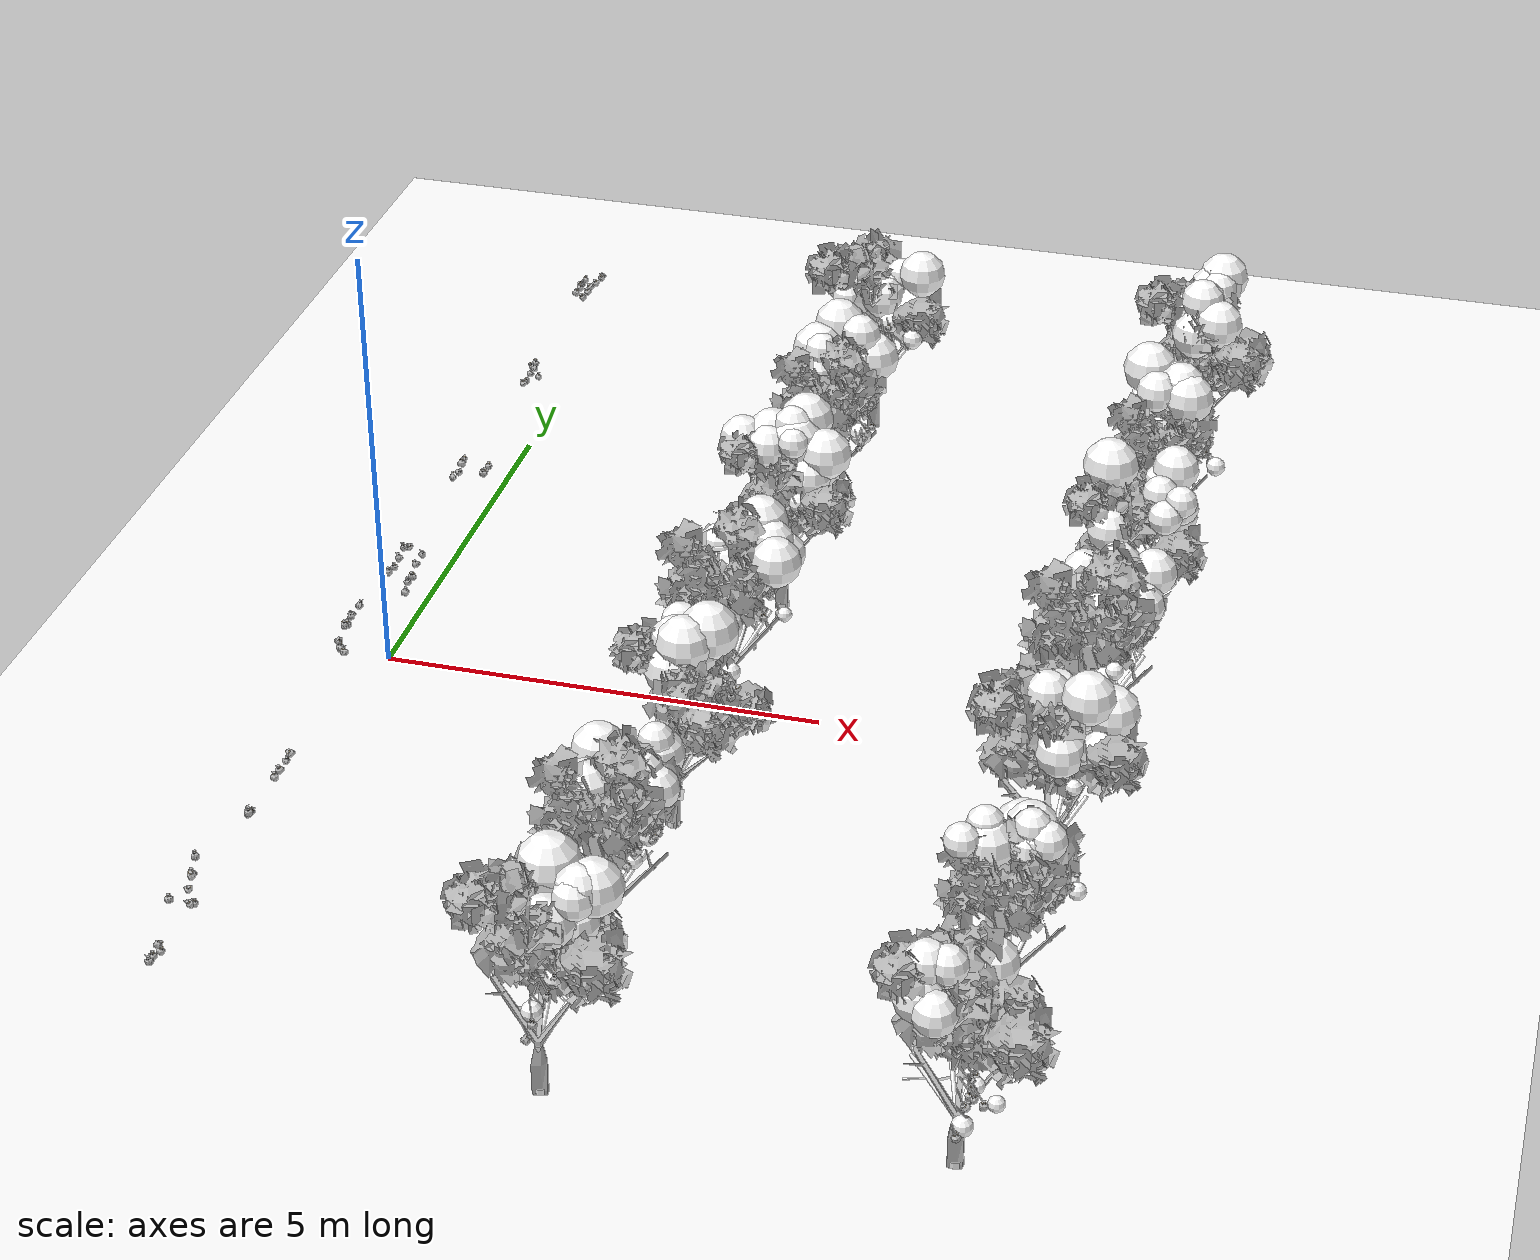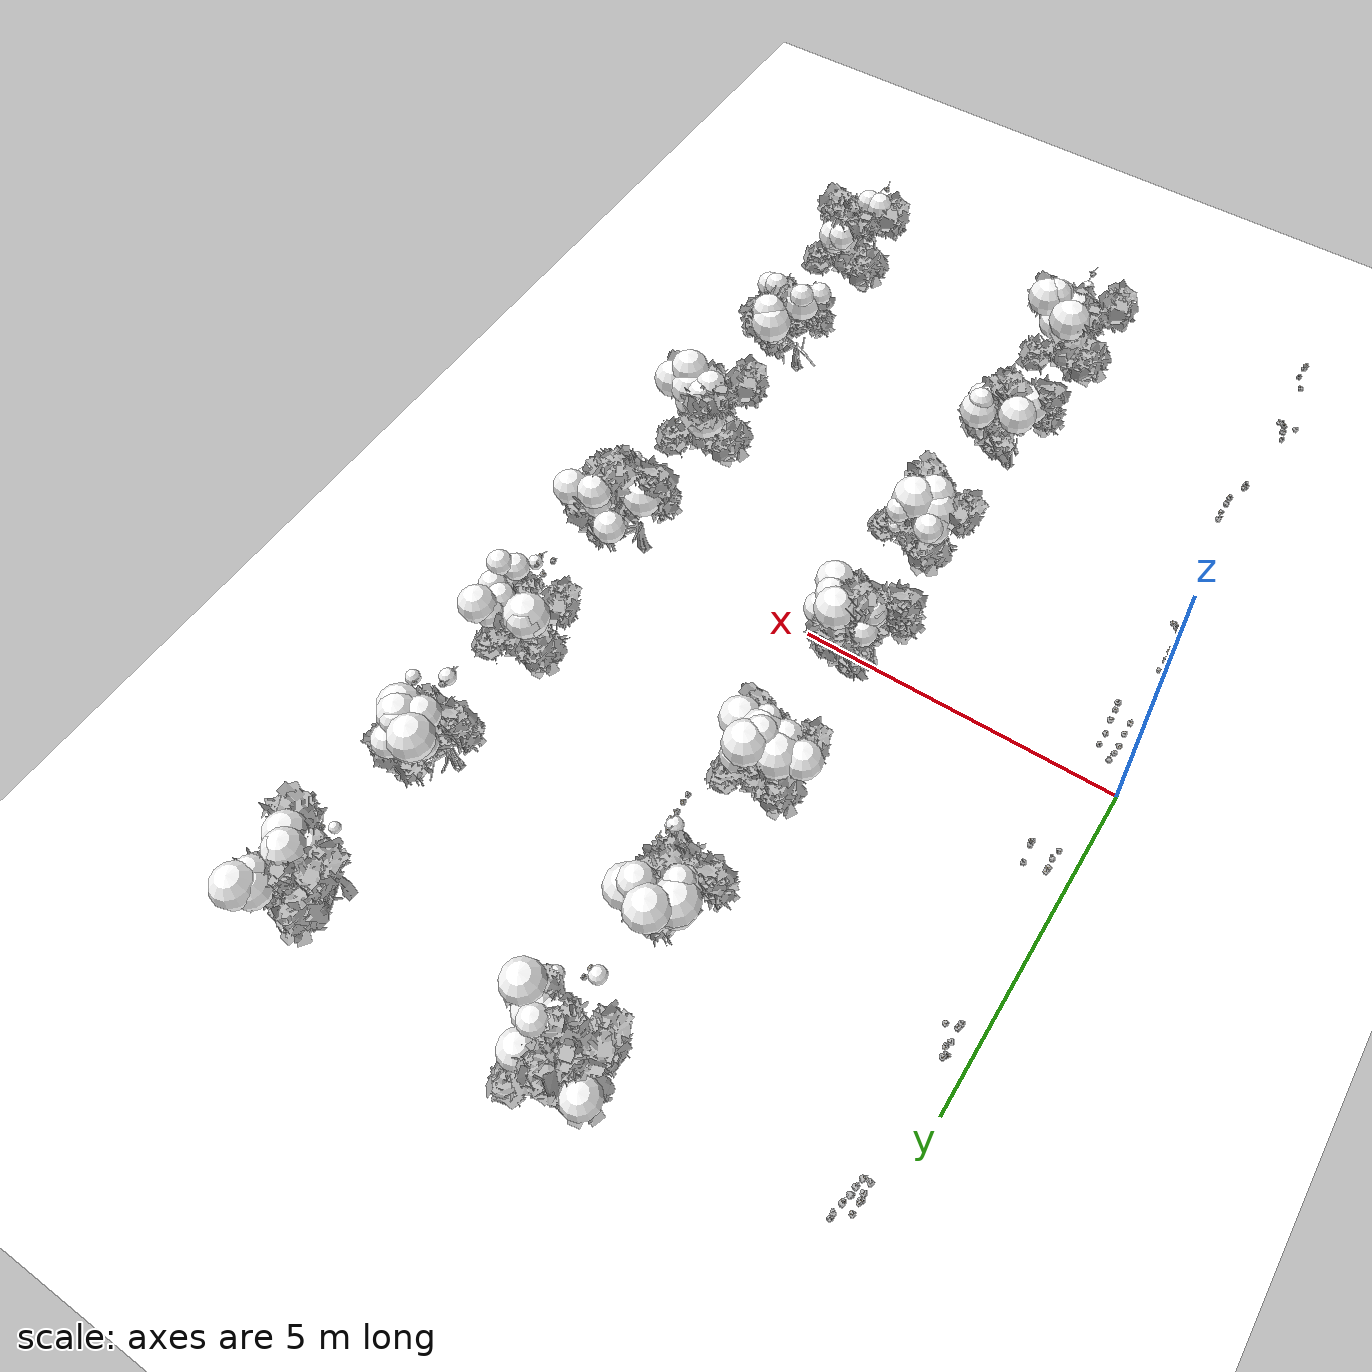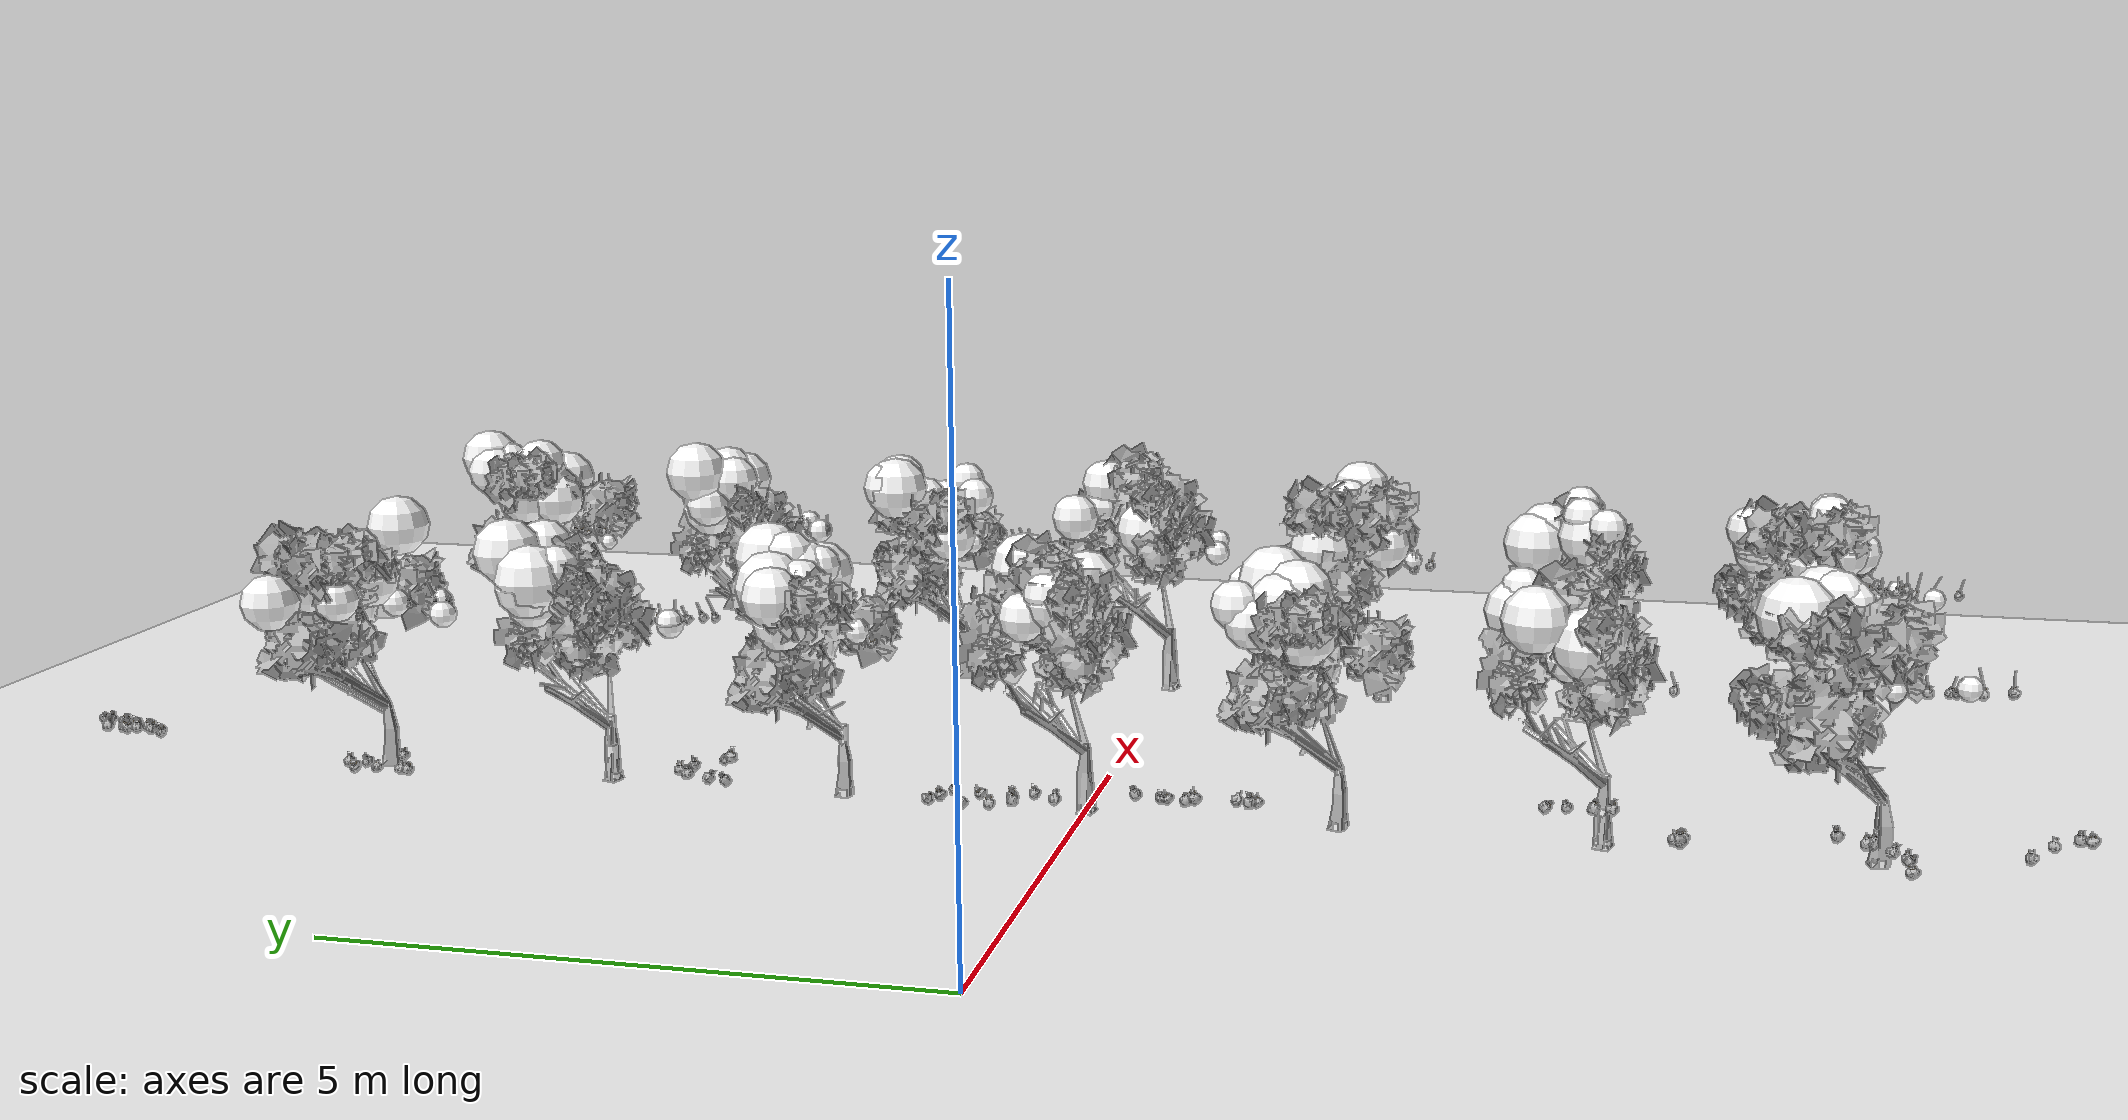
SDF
<sdf version="1.11">
 <world name="peach_orchard">
  <model name="ground">
   <static>true</static>
   <link name="link">
    <visual name="soil">
     <geometry><plane><normal>0 0 1</normal><size>32 22</size></plane></geometry>
     <material>
      <ambient>1 1 1 1</ambient>
      <diffuse>1 1 1 1</diffuse>
      <specular>0.1 0.1 0.1 1</specular>
      <pbr>
       <metal>
        <albedo_map>textures/soil_albedo.png</albedo_map>
        <normal_map type="tangent">textures/soil_normal.png</normal_map>
        <roughness>0.95</roughness>
        <metalness>0</metalness>
       </metal>
      </pbr>
     </material>
    </visual>
    <collision name="c_soil">
     <geometry><plane><normal>0 0 1</normal><size>32 22</size></plane></geometry>
    </collision>
   </link>
  </model>
  <model name="tree_r3_t0">
   <pose>4 -6.6 0 0 0 0</pose>
   <static>true</static>
   <link name="link">
    <visual name="tree_mesh">
     <pose>0 0 0 0 0 0.210482</pose>
     <geometry>
      <mesh><uri>model://peach_sim/meshes/peach_tree_a.glb</uri><scale>1.0623 1.0623 1.0623</scale></mesh>
     </geometry>
    </visual>
    <visual name="trunk_0">
     <pose>0 0 0.15302 0 0 0</pose>
     <geometry><cylinder><radius>0.0556093</radius><length>0.30604</length></cylinder></geometry>
     <material>
      <ambient>1 1 1 1</ambient>
      <diffuse>1 1 1 1</diffuse>
      <specular>0.1 0.1 0.1 1</specular>
      <pbr>
       <metal>
        <albedo_map>textures/bark_albedo.png</albedo_map>
        <normal_map type="tangent">textures/bark_normal.png</normal_map>
        <roughness>0.9</roughness>
        <metalness>0</metalness>
       </metal>
      </pbr>
     </material>
    </visual>
    <collision name="c_trunk_0">
     <pose>0 0 0.15302 0 0 0</pose>
     <geometry><cylinder><radius>0.0556093</radius><length>0.30604</length></cylinder></geometry>
    </collision>
    <visual name="trunk_1">
     <pose>0 0 0.431239 0 0 0</pose>
     <geometry><cylinder><radius>0.0400387</radius><length>0.250397</length></cylinder></geometry>
     <material>
      <ambient>1 1 1 1</ambient>
      <diffuse>1 1 1 1</diffuse>
      <specular>0.1 0.1 0.1 1</specular>
      <pbr>
       <metal>
        <albedo_map>textures/bark_albedo.png</albedo_map>
        <normal_map type="tangent">textures/bark_normal.png</normal_map>
        <roughness>0.9</roughness>
        <metalness>0</metalness>
       </metal>
      </pbr>
     </material>
    </visual>
    <collision name="c_trunk_1">
     <pose>0 0 0.431239 0 0 0</pose>
     <geometry><cylinder><radius>0.0400387</radius><length>0.250397</length></cylinder></geometry>
    </collision>
    <visual name="root_flare">
     <pose>0 0 0.035 0 0 0</pose>
     <geometry><cylinder><radius>0.0806335</radius><length>0.07</length></cylinder></geometry>
     <material>
      <ambient>1 1 1 1</ambient>
      <diffuse>1 1 1 1</diffuse>
      <specular>0.1 0.1 0.1 1</specular>
      <pbr>
       <metal>
        <albedo_map>textures/bark_albedo.png</albedo_map>
        <normal_map type="tangent">textures/bark_normal.png</normal_map>
        <roughness>0.95</roughness>
        <metalness>0</metalness>
       </metal>
      </pbr>
     </material>
    </visual>
    <visual name="scaffold_0">
     <pose>-0.0105899 0.314252 0.767716 0 0.887869 1.60448</pose>
     <geometry><cylinder><radius>0.022</radius><length>0.810672</length></cylinder></geometry>
     <material>
      <ambient>1 1 1 1</ambient>
      <diffuse>1 1 1 1</diffuse>
      <specular>0.1 0.1 0.1 1</specular>
      <pbr>
       <metal>
        <albedo_map>textures/bark_albedo.png</albedo_map>
        <normal_map type="tangent">textures/bark_normal.png</normal_map>
        <roughness>0.9</roughness>
        <metalness>0</metalness>
       </metal>
      </pbr>
     </material>
    </visual>
    <collision name="c_scaffold_0">
     <pose>-0.0105899 0.314252 0.767716 0 0.887869 1.60448</pose>
     <geometry><cylinder><radius>0.022</radius><length>0.810672</length></cylinder></geometry>
    </collision>
    <visual name="branchlet_0_0">
     <pose>0.0610896 0.411993 0.92727 0 1.34717 -0.730648</pose>
     <geometry><cylinder><radius>0.012</radius><length>0.212911</length></cylinder></geometry>
     <material>
      <ambient>1 1 1 1</ambient>
      <diffuse>1 1 1 1</diffuse>
      <specular>0.1 0.1 0.1 1</specular>
      <pbr>
       <metal>
        <albedo_map>textures/bark_albedo.png</albedo_map>
        <normal_map type="tangent">textures/bark_normal.png</normal_map>
        <roughness>0.9</roughness>
        <metalness>0</metalness>
       </metal>
      </pbr>
     </material>
    </visual>
    <visual name="branchlet_0_1">
     <pose>0.00327641 0.629002 1.00645 0 1.00672 1.37103</pose>
     <geometry><cylinder><radius>0.012</radius><length>0.250225</length></cylinder></geometry>
     <material>
      <ambient>1 1 1 1</ambient>
      <diffuse>1 1 1 1</diffuse>
      <specular>0.1 0.1 0.1 1</specular>
      <pbr>
       <metal>
        <albedo_map>textures/bark_albedo.png</albedo_map>
        <normal_map type="tangent">textures/bark_normal.png</normal_map>
        <roughness>0.9</roughness>
        <metalness>0</metalness>
       </metal>
      </pbr>
     </material>
    </visual>
    <visual name="scaffold_1">
     <pose>0.112412 0.242016 0.700521 0 0.955546 1.13597</pose>
     <geometry><cylinder><radius>0.022</radius><length>0.653538</length></cylinder></geometry>
     <material>
      <ambient>1 1 1 1</ambient>
      <diffuse>1 1 1 1</diffuse>
      <specular>0.1 0.1 0.1 1</specular>
      <pbr>
       <metal>
        <albedo_map>textures/bark_albedo.png</albedo_map>
        <normal_map type="tangent">textures/bark_normal.png</normal_map>
        <roughness>0.9</roughness>
        <metalness>0</metalness>
       </metal>
      </pbr>
     </material>
    </visual>
    <collision name="c_scaffold_1">
     <pose>0.112412 0.242016 0.700521 0 0.955546 1.13597</pose>
     <geometry><cylinder><radius>0.022</radius><length>0.653538</length></cylinder></geometry>
    </collision>
    <visual name="branchlet_1_0">
     <pose>0.236513 0.286421 0.87889 0 0.85312 -0.799009</pose>
     <geometry><cylinder><radius>0.012</radius><length>0.266637</length></cylinder></geometry>
     <material>
      <ambient>1 1 1 1</ambient>
      <diffuse>1 1 1 1</diffuse>
      <specular>0.1 0.1 0.1 1</specular>
      <pbr>
       <metal>
        <albedo_map>textures/bark_albedo.png</albedo_map>
        <normal_map type="tangent">textures/bark_normal.png</normal_map>
        <roughness>0.9</roughness>
        <metalness>0</metalness>
       </metal>
      </pbr>
     </material>
    </visual>
    <visual name="branchlet_1_1">
     <pose>0.0516583 0.44571 0.83719 0 1.29788 2.55002</pose>
     <geometry><cylinder><radius>0.012</radius><length>0.296277</length></cylinder></geometry>
     <material>
      <ambient>1 1 1 1</ambient>
      <diffuse>1 1 1 1</diffuse>
      <specular>0.1 0.1 0.1 1</specular>
      <pbr>
       <metal>
        <albedo_map>textures/bark_albedo.png</albedo_map>
        <normal_map type="tangent">textures/bark_normal.png</normal_map>
        <roughness>0.9</roughness>
        <metalness>0</metalness>
       </metal>
      </pbr>
     </material>
    </visual>
    <visual name="branchlet_1_2">
     <pose>0.156918 0.493924 0.851428 0 1.19995 1.72154</pose>
     <geometry><cylinder><radius>0.012</radius><length>0.255299</length></cylinder></geometry>
     <material>
      <ambient>1 1 1 1</ambient>
      <diffuse>1 1 1 1</diffuse>
      <specular>0.1 0.1 0.1 1</specular>
      <pbr>
       <metal>
        <albedo_map>textures/bark_albedo.png</albedo_map>
        <normal_map type="tangent">textures/bark_normal.png</normal_map>
        <roughness>0.9</roughness>
        <metalness>0</metalness>
       </metal>
      </pbr>
     </material>
    </visual>
    <visual name="canopy_0">
     <pose>0.0408955 0.26161 1.81235 0 0 0</pose>
     <geometry><sphere><radius>0.280646</radius></sphere></geometry>
     <material>
      <ambient>1 1 1 1</ambient>
      <diffuse>1 1 1 1</diffuse>
      <specular>0.1 0.1 0.1 1</specular>
      <pbr>
       <metal>
        <albedo_map>textures/leaf_albedo.png</albedo_map>
        <normal_map type="tangent">textures/leaf_normal.png</normal_map>
        <roughness>0.85</roughness>
        <metalness>0</metalness>
       </metal>
      </pbr>
     </material>
    </visual>
    <collision name="c_canopy_0">
     <pose>0.0408955 0.26161 1.81235 0 0 0</pose>
     <geometry><sphere><radius>0.280646</radius></sphere></geometry>
    </collision>
    <visual name="canopy_1">
     <pose>0.297753 0.3431 2.07911 0 0 0</pose>
     <geometry><sphere><radius>0.220225</radius></sphere></geometry>
     <material>
      <ambient>1 1 1 1</ambient>
      <diffuse>1 1 1 1</diffuse>
      <specular>0.1 0.1 0.1 1</specular>
      <pbr>
       <metal>
        <albedo_map>textures/leaf_albedo.png</albedo_map>
        <normal_map type="tangent">textures/leaf_normal.png</normal_map>
        <roughness>0.85</roughness>
        <metalness>0</metalness>
       </metal>
      </pbr>
     </material>
    </visual>
    <collision name="c_canopy_1">
     <pose>0.297753 0.3431 2.07911 0 0 0</pose>
     <geometry><sphere><radius>0.220225</radius></sphere></geometry>
    </collision>
    <visual name="canopy_2">
     <pose>-0.232357 0.596794 1.88742 0 0 0</pose>
     <geometry><sphere><radius>0.199249</radius></sphere></geometry>
     <material>
      <ambient>1 1 1 1</ambient>
      <diffuse>1 1 1 1</diffuse>
      <specular>0.1 0.1 0.1 1</specular>
      <pbr>
       <metal>
        <albedo_map>textures/leaf_albedo.png</albedo_map>
        <normal_map type="tangent">textures/leaf_normal.png</normal_map>
        <roughness>0.85</roughness>
        <metalness>0</metalness>
       </metal>
      </pbr>
     </material>
    </visual>
    <collision name="c_canopy_2">
     <pose>-0.232357 0.596794 1.88742 0 0 0</pose>
     <geometry><sphere><radius>0.199249</radius></sphere></geometry>
    </collision>
    <visual name="canopy_3">
     <pose>0.425943 0.53299 2.08937 0 0 0</pose>
     <geometry><sphere><radius>0.29277</radius></sphere></geometry>
     <material>
      <ambient>1 1 1 1</ambient>
      <diffuse>1 1 1 1</diffuse>
      <specular>0.1 0.1 0.1 1</specular>
      <pbr>
       <metal>
        <albedo_map>textures/leaf_albedo.png</albedo_map>
        <normal_map type="tangent">textures/leaf_normal.png</normal_map>
        <roughness>0.85</roughness>
        <metalness>0</metalness>
       </metal>
      </pbr>
     </material>
    </visual>
    <visual name="canopy_4">
     <pose>-0.0397947 0.26993 1.75576 0 0 0</pose>
     <geometry><sphere><radius>0.281064</radius></sphere></geometry>
     <material>
      <ambient>1 1 1 1</ambient>
      <diffuse>1 1 1 1</diffuse>
      <specular>0.1 0.1 0.1 1</specular>
      <pbr>
       <metal>
        <albedo_map>textures/leaf_albedo.png</albedo_map>
        <normal_map type="tangent">textures/leaf_normal.png</normal_map>
        <roughness>0.85</roughness>
        <metalness>0</metalness>
       </metal>
      </pbr>
     </material>
    </visual>
    <visual name="canopy_5">
     <pose>0.324459 0.441414 2.11613 0 0 0</pose>
     <geometry><sphere><radius>0.255268</radius></sphere></geometry>
     <material>
      <ambient>1 1 1 1</ambient>
      <diffuse>1 1 1 1</diffuse>
      <specular>0.1 0.1 0.1 1</specular>
      <pbr>
       <metal>
        <albedo_map>textures/leaf_albedo.png</albedo_map>
        <normal_map type="tangent">textures/leaf_normal.png</normal_map>
        <roughness>0.85</roughness>
        <metalness>0</metalness>
       </metal>
      </pbr>
     </material>
    </visual>
    <visual name="canopy_6">
     <pose>0.217945 0.537432 1.64301 0 0 0</pose>
     <geometry><sphere><radius>0.251501</radius></sphere></geometry>
     <material>
      <ambient>1 1 1 1</ambient>
      <diffuse>1 1 1 1</diffuse>
      <specular>0.1 0.1 0.1 1</specular>
      <pbr>
       <metal>
        <albedo_map>textures/leaf_albedo.png</albedo_map>
        <normal_map type="tangent">textures/leaf_normal.png</normal_map>
        <roughness>0.85</roughness>
        <metalness>0</metalness>
       </metal>
      </pbr>
     </material>
    </visual>
    <visual name="canopy_7">
     <pose>-0.0905776 0.787332 2.07958 0 0 0</pose>
     <geometry><sphere><radius>0.318735</radius></sphere></geometry>
     <material>
      <ambient>1 1 1 1</ambient>
      <diffuse>1 1 1 1</diffuse>
      <specular>0.1 0.1 0.1 1</specular>
      <pbr>
       <metal>
        <albedo_map>textures/leaf_albedo.png</albedo_map>
        <normal_map type="tangent">textures/leaf_normal.png</normal_map>
        <roughness>0.85</roughness>
        <metalness>0</metalness>
       </metal>
      </pbr>
     </material>
    </visual>
    <visual name="foliage_0">
     <pose>0.205199 -0.0439581 1.42515 0 0 0</pose>
     <geometry><sphere><radius>0.0999698</radius></sphere></geometry>
     <material>
      <ambient>1 1 1 1</ambient>
      <diffuse>1 1 1 1</diffuse>
      <specular>0.1 0.1 0.1 1</specular>
      <pbr>
       <metal>
        <albedo_map>textures/leaf_albedo.png</albedo_map>
        <normal_map type="tangent">textures/leaf_normal.png</normal_map>
        <roughness>0.85</roughness>
        <metalness>0</metalness>
       </metal>
      </pbr>
     </material>
    </visual>
    <visual name="foliage_4">
     <pose>0.280336 -0.00966176 1.50219 0 0 0</pose>
     <geometry><sphere><radius>0.0802819</radius></sphere></geometry>
     <material>
      <ambient>1 1 1 1</ambient>
      <diffuse>1 1 1 1</diffuse>
      <specular>0.1 0.1 0.1 1</specular>
      <pbr>
       <metal>
        <albedo_map>textures/leaf_albedo.png</albedo_map>
        <normal_map type="tangent">textures/leaf_normal.png</normal_map>
        <roughness>0.85</roughness>
        <metalness>0</metalness>
       </metal>
      </pbr>
     </material>
    </visual>
    <visual name="foliage_8">
     <pose>0.181397 -0.614469 1.4774 0 0 0</pose>
     <geometry><sphere><radius>0.104848</radius></sphere></geometry>
     <material>
      <ambient>1 1 1 1</ambient>
      <diffuse>1 1 1 1</diffuse>
      <specular>0.1 0.1 0.1 1</specular>
      <pbr>
       <metal>
        <albedo_map>textures/leaf_albedo.png</albedo_map>
        <normal_map type="tangent">textures/leaf_normal.png</normal_map>
        <roughness>0.85</roughness>
        <metalness>0</metalness>
       </metal>
      </pbr>
     </material>
    </visual>
    <visual name="twig_0">
     <pose>0.161272 -0.115505 1.49293 0 0.412594 -2.90051</pose>
     <geometry><cylinder><radius>0.007</radius><length>0.127995</length></cylinder></geometry>
     <material>
      <ambient>1 1 1 1</ambient>
      <diffuse>1 1 1 1</diffuse>
      <specular>0.1 0.1 0.1 1</specular>
      <pbr>
       <metal>
        <albedo_map>textures/bark_albedo.png</albedo_map>
        <normal_map type="tangent">textures/bark_normal.png</normal_map>
        <roughness>0.9</roughness>
        <metalness>0</metalness>
       </metal>
      </pbr>
     </material>
    </visual>
    <visual name="twig_1">
     <pose>0.158182 -0.0581862 1.52413 0 0.715115 -3.02339</pose>
     <geometry><cylinder><radius>0.007</radius><length>0.188418</length></cylinder></geometry>
     <material>
      <ambient>1 1 1 1</ambient>
      <diffuse>1 1 1 1</diffuse>
      <specular>0.1 0.1 0.1 1</specular>
      <pbr>
       <metal>
        <albedo_map>textures/bark_albedo.png</albedo_map>
        <normal_map type="tangent">textures/bark_normal.png</normal_map>
        <roughness>0.9</roughness>
        <metalness>0</metalness>
       </metal>
      </pbr>
     </material>
    </visual>
    <visual name="twig_2">
     <pose>0.18834 -0.101528 1.56511 0 0.521138 -2.89502</pose>
     <geometry><cylinder><radius>0.007</radius><length>0.142202</length></cylinder></geometry>
     <material>
      <ambient>1 1 1 1</ambient>
      <diffuse>1 1 1 1</diffuse>
      <specular>0.1 0.1 0.1 1</specular>
      <pbr>
       <metal>
        <albedo_map>textures/bark_albedo.png</albedo_map>
        <normal_map type="tangent">textures/bark_normal.png</normal_map>
        <roughness>0.9</roughness>
        <metalness>0</metalness>
       </metal>
      </pbr>
     </material>
    </visual>
    <visual name="twig_3">
     <pose>0.171339 -0.052174 1.58311 0 0.431326 2.50493</pose>
     <geometry><cylinder><radius>0.007</radius><length>0.162888</length></cylinder></geometry>
     <material>
      <ambient>1 1 1 1</ambient>
      <diffuse>1 1 1 1</diffuse>
      <specular>0.1 0.1 0.1 1</specular>
      <pbr>
       <metal>
        <albedo_map>textures/bark_albedo.png</albedo_map>
        <normal_map type="tangent">textures/bark_normal.png</normal_map>
        <roughness>0.9</roughness>
        <metalness>0</metalness>
       </metal>
      </pbr>
     </material>
    </visual>
    <visual name="twig_4">
     <pose>0.208274 -0.0202714 1.56957 0 0.37697 2.19467</pose>
     <geometry><cylinder><radius>0.007</radius><length>0.119986</length></cylinder></geometry>
     <material>
      <ambient>1 1 1 1</ambient>
      <diffuse>1 1 1 1</diffuse>
      <specular>0.1 0.1 0.1 1</specular>
      <pbr>
       <metal>
        <albedo_map>textures/bark_albedo.png</albedo_map>
        <normal_map type="tangent">textures/bark_normal.png</normal_map>
        <roughness>0.9</roughness>
        <metalness>0</metalness>
       </metal>
      </pbr>
     </material>
    </visual>
    <visual name="twig_5">
     <pose>0.192987 -0.0529154 1.5577 0 0.597044 -2.74615</pose>
     <geometry><cylinder><radius>0.007</radius><length>0.107194</length></cylinder></geometry>
     <material>
      <ambient>1 1 1 1</ambient>
      <diffuse>1 1 1 1</diffuse>
      <specular>0.1 0.1 0.1 1</specular>
      <pbr>
       <metal>
        <albedo_map>textures/bark_albedo.png</albedo_map>
        <normal_map type="tangent">textures/bark_normal.png</normal_map>
        <roughness>0.9</roughness>
        <metalness>0</metalness>
       </metal>
      </pbr>
     </material>
    </visual>
    <visual name="twig_6">
     <pose>0.182984 -0.283787 1.51191 0 0.629569 2.74837</pose>
     <geometry><cylinder><radius>0.007</radius><length>0.150992</length></cylinder></geometry>
     <material>
      <ambient>1 1 1 1</ambient>
      <diffuse>1 1 1 1</diffuse>
      <specular>0.1 0.1 0.1 1</specular>
      <pbr>
       <metal>
        <albedo_map>textures/bark_albedo.png</albedo_map>
        <normal_map type="tangent">textures/bark_normal.png</normal_map>
        <roughness>0.9</roughness>
        <metalness>0</metalness>
       </metal>
      </pbr>
     </material>
    </visual>
    <visual name="twig_7">
     <pose>0.179115 -0.490696 1.51809 0 0.629126 -2.97474</pose>
     <geometry><cylinder><radius>0.007</radius><length>0.161351</length></cylinder></geometry>
     <material>
      <ambient>1 1 1 1</ambient>
      <diffuse>1 1 1 1</diffuse>
      <specular>0.1 0.1 0.1 1</specular>
      <pbr>
       <metal>
        <albedo_map>textures/bark_albedo.png</albedo_map>
        <normal_map type="tangent">textures/bark_normal.png</normal_map>
        <roughness>0.9</roughness>
        <metalness>0</metalness>
       </metal>
      </pbr>
     </material>
    </visual>
    <visual name="twig_8">
     <pose>0.174268 -0.535229 1.51023 0 0.454083 -2.69315</pose>
     <geometry><cylinder><radius>0.007</radius><length>0.142294</length></cylinder></geometry>
     <material>
      <ambient>1 1 1 1</ambient>
      <diffuse>1 1 1 1</diffuse>
      <specular>0.1 0.1 0.1 1</specular>
      <pbr>
       <metal>
        <albedo_map>textures/bark_albedo.png</albedo_map>
        <normal_map type="tangent">textures/bark_normal.png</normal_map>
        <roughness>0.9</roughness>
        <metalness>0</metalness>
       </metal>
      </pbr>
     </material>
    </visual>
    <visual name="twig_9">
     <pose>0.201981 -0.699367 1.55759 0 0.356894 2.17544</pose>
     <geometry><cylinder><radius>0.007</radius><length>0.203774</length></cylinder></geometry>
     <material>
      <ambient>1 1 1 1</ambient>
      <diffuse>1 1 1 1</diffuse>
      <specular>0.1 0.1 0.1 1</specular>
      <pbr>
       <metal>
        <albedo_map>textures/bark_albedo.png</albedo_map>
        <normal_map type="tangent">textures/bark_normal.png</normal_map>
        <roughness>0.9</roughness>
        <metalness>0</metalness>
       </metal>
      </pbr>
     </material>
    </visual>
    <visual name="twig_10">
     <pose>0.221095 -0.952557 1.55364 0 0.469997 2.87751</pose>
     <geometry><cylinder><radius>0.007</radius><length>0.1991</length></cylinder></geometry>
     <material>
      <ambient>1 1 1 1</ambient>
      <diffuse>1 1 1 1</diffuse>
      <specular>0.1 0.1 0.1 1</specular>
      <pbr>
       <metal>
        <albedo_map>textures/bark_albedo.png</albedo_map>
        <normal_map type="tangent">textures/bark_normal.png</normal_map>
        <roughness>0.9</roughness>
        <metalness>0</metalness>
       </metal>
      </pbr>
     </material>
    </visual>
   </link>
  </model>
  <model name="tree_r3_t1">
   <pose>4 -4.4 0 0 0 0</pose>
   <static>true</static>
   <link name="link">
    <visual name="tree_mesh">
     <pose>0 0 0 0 0 -0.274264</pose>
     <geometry>
      <mesh><uri>model://peach_sim/meshes/peach_tree_b.glb</uri><scale>1.02439 1.02439 1.02439</scale></mesh>
     </geometry>
    </visual>
    <visual name="trunk_0">
     <pose>0 0 0.171645 0 0 0</pose>
     <geometry><cylinder><radius>0.0518367</radius><length>0.343291</length></cylinder></geometry>
     <material>
      <ambient>1 1 1 1</ambient>
      <diffuse>1 1 1 1</diffuse>
      <specular>0.1 0.1 0.1 1</specular>
      <pbr>
       <metal>
        <albedo_map>textures/bark_albedo.png</albedo_map>
        <normal_map type="tangent">textures/bark_normal.png</normal_map>
        <roughness>0.9</roughness>
        <metalness>0</metalness>
       </metal>
      </pbr>
     </material>
    </visual>
    <collision name="c_trunk_0">
     <pose>0 0 0.171645 0 0 0</pose>
     <geometry><cylinder><radius>0.0518367</radius><length>0.343291</length></cylinder></geometry>
    </collision>
    <visual name="trunk_1">
     <pose>0 0 0.483728 0 0 0</pose>
     <geometry><cylinder><radius>0.0373225</radius><length>0.280874</length></cylinder></geometry>
     <material>
      <ambient>1 1 1 1</ambient>
      <diffuse>1 1 1 1</diffuse>
      <specular>0.1 0.1 0.1 1</specular>
      <pbr>
       <metal>
        <albedo_map>textures/bark_albedo.png</albedo_map>
        <normal_map type="tangent">textures/bark_normal.png</normal_map>
        <roughness>0.9</roughness>
        <metalness>0</metalness>
       </metal>
      </pbr>
     </material>
    </visual>
    <collision name="c_trunk_1">
     <pose>0 0 0.483728 0 0 0</pose>
     <geometry><cylinder><radius>0.0373225</radius><length>0.280874</length></cylinder></geometry>
    </collision>
    <visual name="root_flare">
     <pose>0 0 0.035 0 0 0</pose>
     <geometry><cylinder><radius>0.0751633</radius><length>0.07</length></cylinder></geometry>
     <material>
      <ambient>1 1 1 1</ambient>
      <diffuse>1 1 1 1</diffuse>
      <specular>0.1 0.1 0.1 1</specular>
      <pbr>
       <metal>
        <albedo_map>textures/bark_albedo.png</albedo_map>
        <normal_map type="tangent">textures/bark_normal.png</normal_map>
        <roughness>0.95</roughness>
        <metalness>0</metalness>
       </metal>
      </pbr>
     </material>
    </visual>
    <visual name="scaffold_0">
     <pose>0.00289766 0.339263 0.77872 0 1.02838 1.56226</pose>
     <geometry><cylinder><radius>0.022</radius><length>0.79227</length></cylinder></geometry>
     <material>
      <ambient>1 1 1 1</ambient>
      <diffuse>1 1 1 1</diffuse>
      <specular>0.1 0.1 0.1 1</specular>
      <pbr>
       <metal>
        <albedo_map>textures/bark_albedo.png</albedo_map>
        <normal_map type="tangent">textures/bark_normal.png</normal_map>
        <roughness>0.9</roughness>
        <metalness>0</metalness>
       </metal>
      </pbr>
     </material>
    </visual>
    <collision name="c_scaffold_0">
     <pose>0.00289766 0.339263 0.77872 0 1.02838 1.56226</pose>
     <geometry><cylinder><radius>0.022</radius><length>0.79227</length></cylinder></geometry>
    </collision>
    <visual name="branchlet_0_0">
     <pose>-0.0442807 0.482448 0.978648 0 0.469249 2.25915</pose>
     <geometry><cylinder><radius>0.012</radius><length>0.333502</length></cylinder></geometry>
     <material>
      <ambient>1 1 1 1</ambient>
      <diffuse>1 1 1 1</diffuse>
      <specular>0.1 0.1 0.1 1</specular>
      <pbr>
       <metal>
        <albedo_map>textures/bark_albedo.png</albedo_map>
        <normal_map type="tangent">textures/bark_normal.png</normal_map>
        <roughness>0.9</roughness>
        <metalness>0</metalness>
       </metal>
      </pbr>
     </material>
    </visual>
    <visual name="branchlet_0_1">
     <pose>-0.0696718 0.480406 1.01129 0 0.76341 -2.39416</pose>
     <geometry><cylinder><radius>0.012</radius><length>0.293297</length></cylinder></geometry>
     <material>
      <ambient>1 1 1 1</ambient>
      <diffuse>1 1 1 1</diffuse>
      <specular>0.1 0.1 0.1 1</specular>
      <pbr>
       <metal>
        <albedo_map>textures/bark_albedo.png</albedo_map>
        <normal_map type="tangent">textures/bark_normal.png</normal_map>
        <roughness>0.9</roughness>
        <metalness>0</metalness>
       </metal>
      </pbr>
     </material>
    </visual>
    <visual name="branchlet_0_2">
     <pose>-0.0208308 0.372808 0.88952 0 0.457532 1.96377</pose>
     <geometry><cylinder><radius>0.012</radius><length>0.278203</length></cylinder></geometry>
     <material>
      <ambient>1 1 1 1</ambient>
      <diffuse>1 1 1 1</diffuse>
      <specular>0.1 0.1 0.1 1</specular>
      <pbr>
       <metal>
        <albedo_map>textures/bark_albedo.png</albedo_map>
        <normal_map type="tangent">textures/bark_normal.png</normal_map>
        <roughness>0.9</roughness>
        <metalness>0</metalness>
       </metal>
      </pbr>
     </material>
    </visual>
    <visual name="scaffold_1">
     <pose>0.127383 0.225426 0.768518 0 0.927069 1.05645</pose>
     <geometry><cylinder><radius>0.022</radius><length>0.647427</length></cylinder></geometry>
     <material>
      <ambient>1 1 1 1</ambient>
      <diffuse>1 1 1 1</diffuse>
      <specular>0.1 0.1 0.1 1</specular>
      <pbr>
       <metal>
        <albedo_map>textures/bark_albedo.png</albedo_map>
        <normal_map type="tangent">textures/bark_normal.png</normal_map>
        <roughness>0.9</roughness>
        <metalness>0</metalness>
       </metal>
      </pbr>
     </material>
    </visual>
    <collision name="c_scaffold_1">
     <pose>0.127383 0.225426 0.768518 0 0.927069 1.05645</pose>
     <geometry><cylinder><radius>0.022</radius><length>0.647427</length></cylinder></geometry>
    </collision>
    <visual name="branchlet_1_0">
     <pose>0.032887 0.274121 0.821553 0 1.75925 -2.83323</pose>
     <geometry><cylinder><radius>0.012</radius><length>0.317949</length></cylinder></geometry>
     <material>
      <ambient>1 1 1 1</ambient>
      <diffuse>1 1 1 1</diffuse>
      <specular>0.1 0.1 0.1 1</specular>
      <pbr>
       <metal>
        <albedo_map>textures/bark_albedo.png</albedo_map>
        <normal_map type="tangent">textures/bark_normal.png</normal_map>
        <roughness>0.9</roughness>
        <metalness>0</metalness>
       </metal>
      </pbr>
     </material>
    </visual>
    <visual name="branchlet_1_1">
     <pose>0.250135 0.326126 0.918407 0 0.785515 0.467795</pose>
     <geometry><cylinder><radius>0.012</radius><length>0.292</length></cylinder></geometry>
     <material>
      <ambient>1 1 1 1</ambient>
      <diffuse>1 1 1 1</diffuse>
      <specular>0.1 0.1 0.1 1</specular>
      <pbr>
       <metal>
        <albedo_map>textures/bark_albedo.png</albedo_map>
        <normal_map type="tangent">textures/bark_normal.png</normal_map>
        <roughness>0.9</roughness>
        <metalness>0</metalness>
       </metal>
      </pbr>
     </material>
    </visual>
    <visual name="canopy_0">
     <pose>-0.256309 0.191579 1.79882 0 0 0</pose>
     <geometry><sphere><radius>0.302093</radius></sphere></geometry>
     <material>
      <ambient>1 1 1 1</ambient>
      <diffuse>1 1 1 1</diffuse>
      <specular>0.1 0.1 0.1 1</specular>
      <pbr>
       <metal>
        <albedo_map>textures/leaf_albedo.png</albedo_map>
        <normal_map type="tangent">textures/leaf_normal.png</normal_map>
        <roughness>0.85</roughness>
        <metalness>0</metalness>
       </metal>
      </pbr>
     </material>
    </visual>
    <collision name="c_canopy_0">
     <pose>-0.256309 0.191579 1.79882 0 0 0</pose>
     <geometry><sphere><radius>0.302093</radius></sphere></geometry>
    </collision>
    <visual name="canopy_1">
     <pose>-0.0439061 0.338773 1.60584 0 0 0</pose>
     <geometry><sphere><radius>0.196177</radius></sphere></geometry>
     <material>
      <ambient>1 1 1 1</ambient>
      <diffuse>1 1 1 1</diffuse>
      <specular>0.1 0.1 0.1 1</specular>
      <pbr>
       <metal>
        <albedo_map>textures/leaf_albedo.png</albedo_map>
        <normal_map type="tangent">textures/leaf_normal.png</normal_map>
        <roughness>0.85</roughness>
        <metalness>0</metalness>
       </metal>
      </pbr>
     </material>
    </visual>
    <collision name="c_canopy_1">
     <pose>-0.0439061 0.338773 1.60584 0 0 0</pose>
     <geometry><sphere><radius>0.196177</radius></sphere></geometry>
    </collision>
    <visual name="canopy_2">
     <pose>0.209014 0.445296 1.67812 0 0 0</pose>
     <geometry><sphere><radius>0.259806</radius></sphere></geometry>
     <material>
      <ambient>1 1 1 1</ambient>
      <diffuse>1 1 1 1</diffuse>
      <specular>0.1 0.1 0.1 1</specular>
      <pbr>
       <metal>
        <albedo_map>textures/leaf_albedo.png</albedo_map>
        <normal_map type="tangent">textures/leaf_normal.png</normal_map>
        <roughness>0.85</roughness>
        <metalness>0</metalness>
       </metal>
      </pbr>
     </material>
    </visual>
    <collision name="c_canopy_2">
     <pose>0.209014 0.445296 1.67812 0 0 0</pose>
     <geometry><sphere><radius>0.259806</radius></sphere></geometry>
    </collision>
    <visual name="canopy_3">
     <pose>0.233637 0.459366 1.928 0 0 0</pose>
     <geometry><sphere><radius>0.219301</radius></sphere></geometry>
     <material>
      <ambient>1 1 1 1</ambient>
      <diffuse>1 1 1 1</diffuse>
      <specular>0.1 0.1 0.1 1</specular>
      <pbr>
       <metal>
        <albedo_map>textures/leaf_albedo.png</albedo_map>
        <normal_map type="tangent">textures/leaf_normal.png</normal_map>
        <roughness>0.85</roughness>
        <metalness>0</metalness>
       </metal>
      </pbr>
     </material>
    </visual>
    <visual name="canopy_4">
     <pose>-0.254694 0.617698 1.97712 0 0 0</pose>
     <geometry><sphere><radius>0.285564</radius></sphere></geometry>
     <material>
      <ambient>1 1 1 1</ambient>
      <diffuse>1 1 1 1</diffuse>
      <specular>0.1 0.1 0.1 1</specular>
      <pbr>
       <metal>
        <albedo_map>textures/leaf_albedo.png</albedo_map>
        <normal_map type="tangent">textures/leaf_normal.png</normal_map>
        <roughness>0.85</roughness>
        <metalness>0</metalness>
       </metal>
      </pbr>
     </material>
    </visual>
    <visual name="canopy_5">
     <pose>-0.0750322 0.104665 1.57208 0 0 0</pose>
     <geometry><sphere><radius>0.213074</radius></sphere></geometry>
     <material>
      <ambient>1 1 1 1</ambient>
      <diffuse>1 1 1 1</diffuse>
      <specular>0.1 0.1 0.1 1</specular>
      <pbr>
       <metal>
        <albedo_map>textures/leaf_albedo.png</albedo_map>
        <normal_map type="tangent">textures/leaf_normal.png</normal_map>
        <roughness>0.85</roughness>
        <metalness>0</metalness>
       </metal>
      </pbr>
     </material>
    </visual>
    <visual name="canopy_6">
     <pose>0.293414 0.743755 2.09772 0 0 0</pose>
     <geometry><sphere><radius>0.186287</radius></sphere></geometry>
     <material>
      <ambient>1 1 1 1</ambient>
      <diffuse>1 1 1 1</diffuse>
      <specular>0.1 0.1 0.1 1</specular>
      <pbr>
       <metal>
        <albedo_map>textures/leaf_albedo.png</albedo_map>
        <normal_map type="tangent">textures/leaf_normal.png</normal_map>
        <roughness>0.85</roughness>
        <metalness>0</metalness>
       </metal>
      </pbr>
     </material>
    </visual>
    <visual name="canopy_7">
     <pose>0.401951 0.409758 1.76887 0 0 0</pose>
     <geometry><sphere><radius>0.228204</radius></sphere></geometry>
     <material>
      <ambient>1 1 1 1</ambient>
      <diffuse>1 1 1 1</diffuse>
      <specular>0.1 0.1 0.1 1</specular>
      <pbr>
       <metal>
        <albedo_map>textures/leaf_albedo.png</albedo_map>
        <normal_map type="tangent">textures/leaf_normal.png</normal_map>
        <roughness>0.85</roughness>
        <metalness>0</metalness>
       </metal>
      </pbr>
     </material>
    </visual>
    <visual name="canopy_8">
     <pose>-0.112048 0.178506 1.69558 0 0 0</pose>
     <geometry><sphere><radius>0.258392</radius></sphere></geometry>
     <material>
      <ambient>1 1 1 1</ambient>
      <diffuse>1 1 1 1</diffuse>
      <specular>0.1 0.1 0.1 1</specular>
      <pbr>
       <metal>
        <albedo_map>textures/leaf_albedo.png</albedo_map>
        <normal_map type="tangent">textures/leaf_normal.png</normal_map>
        <roughness>0.85</roughness>
        <metalness>0</metalness>
       </metal>
      </pbr>
     </material>
    </visual>
    <visual name="canopy_9">
     <pose>0.297923 0.782679 1.90813 0 0 0</pose>
     <geometry><sphere><radius>0.276196</radius></sphere></geometry>
     <material>
      <ambient>1 1 1 1</ambient>
      <diffuse>1 1 1 1</diffuse>
      <specular>0.1 0.1 0.1 1</specular>
      <pbr>
       <metal>
        <albedo_map>textures/leaf_albedo.png</albedo_map>
        <normal_map type="tangent">textures/leaf_normal.png</normal_map>
        <roughness>0.85</roughness>
        <metalness>0</metalness>
       </metal>
      </pbr>
     </material>
    </visual>
    <visual name="canopy_10">
     <pose>0.21302 0.827895 1.62863 0 0 0</pose>
     <geometry><sphere><radius>0.187573</radius></sphere></geometry>
     <material>
      <ambient>1 1 1 1</ambient>
      <diffuse>1 1 1 1</diffuse>
      <specular>0.1 0.1 0.1 1</specular>
      <pbr>
       <metal>
        <albedo_map>textures/leaf_albedo.png</albedo_map>
        <normal_map type="tangent">textures/leaf_normal.png</normal_map>
        <roughness>0.85</roughness>
        <metalness>0</metalness>
       </metal>
      </pbr>
     </material>
    </visual>
    <visual name="foliage_0">
     <pose>0.292851 0.172828 1.44235 0 0 0</pose>
     <geometry><sphere><radius>0.100819</radius></sphere></geometry>
     <material>
      <ambient>1 1 1 1</ambient>
      <diffuse>1 1 1 1</diffuse>
      <specular>0.1 0.1 0.1 1</specular>
      <pbr>
       <metal>
        <albedo_map>textures/leaf_albedo.png</albedo_map>
        <normal_map type="tangent">textures/leaf_normal.png</normal_map>
        <roughness>0.85</roughness>
        <metalness>0</metalness>
       </metal>
      </pbr>
     </material>
    </visual>
    <visual name="foliage_4">
     <pose>0.319777 -0.162363 1.29351 0 0 0</pose>
     <geometry><sphere><radius>0.0923238</radius></sphere></geometry>
     <material>
      <ambient>1 1 1 1</ambient>
      <diffuse>1 1 1 1</diffuse>
      <specular>0.1 0.1 0.1 1</specular>
      <pbr>
       <metal>
        <albedo_map>textures/leaf_albedo.png</albedo_map>
        <normal_map type="tangent">textures/leaf_normal.png</normal_map>
        <roughness>0.85</roughness>
        <metalness>0</metalness>
       </metal>
      </pbr>
     </material>
    </visual>
    <visual name="foliage_8">
     <pose>0.405764 0.0756243 1.43289 0 0 0</pose>
     <geometry><sphere><radius>0.102441</radius></sphere></geometry>
     <material>
      <ambient>1 1 1 1</ambient>
      <diffuse>1 1 1 1</diffuse>
      <specular>0.1 0.1 0.1 1</specular>
      <pbr>
       <metal>
        <albedo_map>textures/leaf_albedo.png</albedo_map>
        <normal_map type="tangent">textures/leaf_normal.png</normal_map>
        <roughness>0.85</roughness>
        <metalness>0</metalness>
       </metal>
      </pbr>
     </material>
    </visual>
    <visual name="twig_0">
     <pose>0.205774 0.106351 1.49683 0 0.663417 2.88604</pose>
     <geometry><cylinder><radius>0.007</radius><length>0.124763</length></cylinder></geometry>
     <material>
      <ambient>1 1 1 1</ambient>
      <diffuse>1 1 1 1</diffuse>
      <specular>0.1 0.1 0.1 1</specular>
      <pbr>
       <metal>
        <albedo_map>textures/bark_albedo.png</albedo_map>
        <normal_map type="tangent">textures/bark_normal.png</normal_map>
        <roughness>0.9</roughness>
        <metalness>0</metalness>
       </metal>
      </pbr>
     </material>
    </visual>
    <visual name="twig_1">
     <pose>0.214461 0.266923 1.56384 0 0.302849 2.27051</pose>
     <geometry><cylinder><radius>0.007</radius><length>0.131819</length></cylinder></geometry>
     <material>
      <ambient>1 1 1 1</ambient>
      <diffuse>1 1 1 1</diffuse>
      <specular>0.1 0.1 0.1 1</specular>
      <pbr>
       <metal>
        <albedo_map>textures/bark_albedo.png</albedo_map>
        <normal_map type="tangent">textures/bark_normal.png</normal_map>
        <roughness>0.9</roughness>
        <metalness>0</metalness>
       </metal>
      </pbr>
     </material>
    </visual>
    <visual name="twig_2">
     <pose>0.184167 0.33763 1.5554 0 0.497607 2.74283</pose>
     <geometry><cylinder><radius>0.007</radius><length>0.118496</length></cylinder></geometry>
     <material>
      <ambient>1 1 1 1</ambient>
      <diffuse>1 1 1 1</diffuse>
      <specular>0.1 0.1 0.1 1</specular>
      <pbr>
       <metal>
        <albedo_map>textures/bark_albedo.png</albedo_map>
        <normal_map type="tangent">textures/bark_normal.png</normal_map>
        <roughness>0.9</roughness>
        <metalness>0</metalness>
       </metal>
      </pbr>
     </material>
    </visual>
    <visual name="twig_3">
     <pose>0.167816 0.442507 1.57155 0 0.519638 2.70865</pose>
     <geometry><cylinder><radius>0.007</radius><length>0.160114</length></cylinder></geometry>
     <material>
      <ambient>1 1 1 1</ambient>
      <diffuse>1 1 1 1</diffuse>
      <specular>0.1 0.1 0.1 1</specular>
      <pbr>
       <metal>
        <albedo_map>textures/bark_albedo.png</albedo_map>
        <normal_map type="tangent">textures/bark_normal.png</normal_map>
        <roughness>0.9</roughness>
        <metalness>0</metalness>
       </metal>
      </pbr>
     </material>
    </visual>
    <visual name="twig_4">
     <pose>0.307032 -0.205042 1.51033 0 0.549772 -2.73981</pose>
     <geometry><cylinder><radius>0.007</radius><length>0.180641</length></cylinder></geometry>
     <material>
      <ambient>1 1 1 1</ambient>
      <diffuse>1 1 1 1</diffuse>
      <specular>0.1 0.1 0.1 1</specular>
      <pbr>
       <metal>
        <albedo_map>textures/bark_albedo.png</albedo_map>
        <normal_map type="tangent">textures/bark_normal.png</normal_map>
        <roughness>0.9</roughness>
        <metalness>0</metalness>
       </metal>
      </pbr>
     </material>
    </visual>
    <visual name="twig_5">
     <pose>0.267612 -0.298167 1.40899 0 0.594464 2.88743</pose>
     <geometry><cylinder><radius>0.007</radius><length>0.151281</length></cylinder></geometry>
     <material>
      <ambient>1 1 1 1</ambient>
      <diffuse>1 1 1 1</diffuse>
      <specular>0.1 0.1 0.1 1</specular>
      <pbr>
       <metal>
        <albedo_map>textures/bark_albedo.png</albedo_map>
        <normal_map type="tangent">textures/bark_normal.png</normal_map>
        <roughness>0.9</roughness>
        <metalness>0</metalness>
       </metal>
      </pbr>
     </material>
    </visual>
    <visual name="twig_6">
     <pose>0.251007 -0.506691 1.40582 0 0.343851 2.01015</pose>
     <geometry><cylinder><radius>0.007</radius><length>0.136682</length></cylinder></geometry>
     <material>
      <ambient>1 1 1 1</ambient>
      <diffuse>1 1 1 1</diffuse>
      <specular>0.1 0.1 0.1 1</specular>
      <pbr>
       <metal>
        <albedo_map>textures/bark_albedo.png</albedo_map>
        <normal_map type="tangent">textures/bark_normal.png</normal_map>
        <roughness>0.9</roughness>
        <metalness>0</metalness>
       </metal>
      </pbr>
     </material>
    </visual>
    <visual name="twig_7">
     <pose>0.44589 -0.0214821 1.58144 0 0.224805 -2.96281</pose>
     <geometry><cylinder><radius>0.007</radius><length>0.203871</length></cylinder></geometry>
     <material>
      <ambient>1 1 1 1</ambient>
      <diffuse>1 1 1 1</diffuse>
      <specular>0.1 0.1 0.1 1</specular>
      <pbr>
       <metal>
        <albedo_map>textures/bark_albedo.png</albedo_map>
        <normal_map type="tangent">textures/bark_normal.png</normal_map>
        <roughness>0.9</roughness>
        <metalness>0</metalness>
       </metal>
      </pbr>
     </material>
    </visual>
    <visual name="twig_8">
     <pose>0.47425 0.0242874 1.59097 0 0.281735 2.21502</pose>
     <geometry><cylinder><radius>0.007</radius><length>0.17044</length></cylinder></geometry>
     <material>
      <ambient>1 1 1 1</ambient>
      <diffuse>1 1 1 1</diffuse>
      <specular>0.1 0.1 0.1 1</specular>
      <pbr>
       <metal>
        <albedo_map>textures/bark_albedo.png</albedo_map>
        <normal_map type="tangent">textures/bark_normal.png</normal_map>
        <roughness>0.9</roughness>
        <metalness>0</metalness>
       </metal>
      </pbr>
     </material>
    </visual>
    <visual name="twig_9">
     <pose>0.503217 0.0903975 1.56831 0 0.278915 -2.61307</pose>
     <geometry><cylinder><radius>0.007</radius><length>0.126308</length></cylinder></geometry>
     <material>
      <ambient>1 1 1 1</ambient>
      <diffuse>1 1 1 1</diffuse>
      <specular>0.1 0.1 0.1 1</specular>
      <pbr>
       <metal>
        <albedo_map>textures/bark_albedo.png</albedo_map>
        <normal_map type="tangent">textures/bark_normal.png</normal_map>
        <roughness>0.9</roughness>
        <metalness>0</metalness>
       </metal>
      </pbr>
     </material>
    </visual>
   </link>
  </model>
  <model name="tree_r3_t2">
   <pose>4 -2.2 0 0 0 0</pose>
   <static>true</static>
   <link name="link">
    <visual name="tree_mesh">
     <pose>0 0 0 0 0 -0.284342</pose>
     <geometry>
      <mesh><uri>model://peach_sim/meshes/peach_tree_a.glb</uri><scale>0.98343 0.98343 0.98343</scale></mesh>
     </geometry>
    </visual>
    <visual name="trunk_0">
     <pose>0 0 0.149055 0 0 0</pose>
     <geometry><cylinder><radius>0.0524701</radius><length>0.298111</length></cylinder></geometry>
     <material>
      <ambient>1 1 1 1</ambient>
      <diffuse>1 1 1 1</diffuse>
      <specular>0.1 0.1 0.1 1</specular>
      <pbr>
       <metal>
        <albedo_map>textures/bark_albedo.png</albedo_map>
        <normal_map type="tangent">textures/bark_normal.png</normal_map>
        <roughness>0.9</roughness>
        <metalness>0</metalness>
       </metal>
      </pbr>
     </material>
    </visual>
    <collision name="c_trunk_0">
     <pose>0 0 0.149055 0 0 0</pose>
     <geometry><cylinder><radius>0.0524701</radius><length>0.298111</length></cylinder></geometry>
    </collision>
    <visual name="trunk_1">
     <pose>0 0 0.420065 0 0 0</pose>
     <geometry><cylinder><radius>0.0377785</radius><length>0.243909</length></cylinder></geometry>
     <material>
      <ambient>1 1 1 1</ambient>
      <diffuse>1 1 1 1</diffuse>
      <specular>0.1 0.1 0.1 1</specular>
      <pbr>
       <metal>
        <albedo_map>textures/bark_albedo.png</albedo_map>
        <normal_map type="tangent">textures/bark_normal.png</normal_map>
        <roughness>0.9</roughness>
        <metalness>0</metalness>
       </metal>
      </pbr>
     </material>
    </visual>
    <collision name="c_trunk_1">
     <pose>0 0 0.420065 0 0 0</pose>
     <geometry><cylinder><radius>0.0377785</radius><length>0.243909</length></cylinder></geometry>
    </collision>
    <visual name="root_flare">
     <pose>0 0 0.035 0 0 0</pose>
     <geometry><cylinder><radius>0.0760816</radius><length>0.07</length></cylinder></geometry>
     <material>
      <ambient>1 1 1 1</ambient>
      <diffuse>1 1 1 1</diffuse>
      <specular>0.1 0.1 0.1 1</specular>
      <pbr>
       <metal>
        <albedo_map>textures/bark_albedo.png</albedo_map>
        <normal_map type="tangent">textures/bark_normal.png</normal_map>
        <roughness>0.95</roughness>
        <metalness>0</metalness>
       </metal>
      </pbr>
     </material>
    </visual>
    <visual name="scaffold_0">
     <pose>0.0411965 0.375163 0.747923 0 0.987111 1.46142</pose>
     <geometry><cylinder><radius>0.022</radius><length>0.904605</length></cylinder></geometry>
     <material>
      <ambient>1 1 1 1</ambient>
      <diffuse>1 1 1 1</diffuse>
      <specular>0.1 0.1 0.1 1</specular>
      <pbr>
       <metal>
        <albedo_map>textures/bark_albedo.png</albedo_map>
        <normal_map type="tangent">textures/bark_normal.png</normal_map>
        <roughness>0.9</roughness>
        <metalness>0</metalness>
       </metal>
      </pbr>
     </material>
    </visual>
    <collision name="c_scaffold_0">
     <pose>0.0411965 0.375163 0.747923 0 0.987111 1.46142</pose>
     <geometry><cylinder><radius>0.022</radius><length>0.904605</length></cylinder></geometry>
    </collision>
    <visual name="branchlet_0_0">
     <pose>0.118654 0.590028 0.889309 0 1.08826 0.940139</pose>
     <geometry><cylinder><radius>0.012</radius><length>0.242743</length></cylinder></geometry>
     <material>
      <ambient>1 1 1 1</ambient>
      <diffuse>1 1 1 1</diffuse>
      <specular>0.1 0.1 0.1 1</specular>
      <pbr>
       <metal>
        <albedo_map>textures/bark_albedo.png</albedo_map>
        <normal_map type="tangent">textures/bark_normal.png</normal_map>
        <roughness>0.9</roughness>
        <metalness>0</metalness>
       </metal>
      </pbr>
     </material>
    </visual>
    <visual name="branchlet_0_1">
     <pose>-0.000234433 0.569813 0.970819 0 0.814393 -2.6648</pose>
     <geometry><cylinder><radius>0.012</radius><length>0.206075</length></cylinder></geometry>
     <material>
      <ambient>1 1 1 1</ambient>
      <diffuse>1 1 1 1</diffuse>
      <specular>0.1 0.1 0.1 1</specular>
      <pbr>
       <metal>
        <albedo_map>textures/bark_albedo.png</albedo_map>
        <normal_map type="tangent">textures/bark_normal.png</normal_map>
        <roughness>0.9</roughness>
        <metalness>0</metalness>
       </metal>
      </pbr>
     </material>
    </visual>
    <visual name="scaffold_1">
     <pose>0.146731 0.368526 0.74023 0 1.02378 1.19188</pose>
     <geometry><cylinder><radius>0.022</radius><length>0.928867</length></cylinder></geometry>
     <material>
      <ambient>1 1 1 1</ambient>
      <diffuse>1 1 1 1</diffuse>
      <specular>0.1 0.1 0.1 1</specular>
      <pbr>
       <metal>
        <albedo_map>textures/bark_albedo.png</albedo_map>
        <normal_map type="tangent">textures/bark_normal.png</normal_map>
        <roughness>0.9</roughness>
        <metalness>0</metalness>
       </metal>
      </pbr>
     </material>
    </visual>
    <collision name="c_scaffold_1">
     <pose>0.146731 0.368526 0.74023 0 1.02378 1.19188</pose>
     <geometry><cylinder><radius>0.022</radius><length>0.928867</length></cylinder></geometry>
    </collision>
    <visual name="branchlet_1_0">
     <pose>0.121043 0.609035 0.979841 0 1.21114 -2.84571</pose>
     <geometry><cylinder><radius>0.012</radius><length>0.308766</length></cylinder></geometry>
     <material>
      <ambient>1 1 1 1</ambient>
      <diffuse>1 1 1 1</diffuse>
      <specular>0.1 0.1 0.1 1</specular>
      <pbr>
       <metal>
        <albedo_map>textures/bark_albedo.png</albedo_map>
        <normal_map type="tangent">textures/bark_normal.png</normal_map>
        <roughness>0.9</roughness>
        <metalness>0</metalness>
       </metal>
      </pbr>
     </material>
    </visual>
    <visual name="branchlet_1_1">
     <pose>0.349899 0.606536 1.02709 0 0.693996 -0.027296</pose>
     <geometry><cylinder><radius>0.012</radius><length>0.335441</length></cylinder></geometry>
     <material>
      <ambient>1 1 1 1</ambient>
      <diffuse>1 1 1 1</diffuse>
      <specular>0.1 0.1 0.1 1</specular>
      <pbr>
       <metal>
        <albedo_map>textures/bark_albedo.png</albedo_map>
        <normal_map type="tangent">textures/bark_normal.png</normal_map>
        <roughness>0.9</roughness>
        <metalness>0</metalness>
       </metal>
      </pbr>
     </material>
    </visual>
    <visual name="canopy_0">
     <pose>-0.148236 0.884861 1.95027 0 0 0</pose>
     <geometry><sphere><radius>0.212084</radius></sphere></geometry>
     <material>
      <ambient>1 1 1 1</ambient>
      <diffuse>1 1 1 1</diffuse>
      <specular>0.1 0.1 0.1 1</specular>
      <pbr>
       <metal>
        <albedo_map>textures/leaf_albedo.png</albedo_map>
        <normal_map type="tangent">textures/leaf_normal.png</normal_map>
        <roughness>0.85</roughness>
        <metalness>0</metalness>
       </metal>
      </pbr>
     </material>
    </visual>
    <collision name="c_canopy_0">
     <pose>-0.148236 0.884861 1.95027 0 0 0</pose>
     <geometry><sphere><radius>0.212084</radius></sphere></geometry>
    </collision>
    <visual name="canopy_1">
     <pose>-0.0770486 0.505133 1.93713 0 0 0</pose>
     <geometry><sphere><radius>0.29601</radius></sphere></geometry>
     <material>
      <ambient>1 1 1 1</ambient>
      <diffuse>1 1 1 1</diffuse>
      <specular>0.1 0.1 0.1 1</specular>
      <pbr>
       <metal>
        <albedo_map>textures/leaf_albedo.png</albedo_map>
        <normal_map type="tangent">textures/leaf_normal.png</normal_map>
        <roughness>0.85</roughness>
        <metalness>0</metalness>
       </metal>
      </pbr>
     </material>
    </visual>
    <collision name="c_canopy_1">
     <pose>-0.0770486 0.505133 1.93713 0 0 0</pose>
     <geometry><sphere><radius>0.29601</radius></sphere></geometry>
    </collision>
    <visual name="canopy_2">
     <pose>-0.16886 0.755609 1.81423 0 0 0</pose>
     <geometry><sphere><radius>0.229153</radius></sphere></geometry>
     <material>
      <ambient>1 1 1 1</ambient>
      <diffuse>1 1 1 1</diffuse>
      <specular>0.1 0.1 0.1 1</specular>
      <pbr>
       <metal>
        <albedo_map>textures/leaf_albedo.png</albedo_map>
        <normal_map type="tangent">textures/leaf_normal.png</normal_map>
        <roughness>0.85</roughness>
        <metalness>0</metalness>
       </metal>
      </pbr>
     </material>
    </visual>
    <collision name="c_canopy_2">
     <pose>-0.16886 0.755609 1.81423 0 0 0</pose>
     <geometry><sphere><radius>0.229153</radius></sphere></geometry>
    </collision>
    <visual name="canopy_3">
     <pose>0.0366819 0.387905 2.02014 0 0 0</pose>
     <geometry><sphere><radius>0.302865</radius></sphere></geometry>
     <material>
      <ambient>1 1 1 1</ambient>
      <diffuse>1 1 1 1</diffuse>
      <specular>0.1 0.1 0.1 1</specular>
      <pbr>
       <metal>
        <albedo_map>textures/leaf_albedo.png</albedo_map>
        <normal_map type="tangent">textures/leaf_normal.png</normal_map>
        <roughness>0.85</roughness>
        <metalness>0</metalness>
       </metal>
      </pbr>
     </material>
    </visual>
    <visual name="canopy_4">
     <pose>-0.0127409 0.589853 1.78665 0 0 0</pose>
     <geometry><sphere><radius>0.211436</radius></sphere></geometry>
     <material>
      <ambient>1 1 1 1</ambient>
      <diffuse>1 1 1 1</diffuse>
      <specular>0.1 0.1 0.1 1</specular>
      <pbr>
       <metal>
        <albedo_map>textures/leaf_albedo.png</albedo_map>
        <normal_map type="tangent">textures/leaf_normal.png</normal_map>
        <roughness>0.85</roughness>
        <metalness>0</metalness>
       </metal>
      </pbr>
     </material>
    </visual>
    <visual name="canopy_5">
     <pose>0.343844 0.845476 2.0007 0 0 0</pose>
     <geometry><sphere><radius>0.185288</radius></sphere></geometry>
     <material>
      <ambient>1 1 1 1</ambient>
      <diffuse>1 1 1 1</diffuse>
      <specular>0.1 0.1 0.1 1</specular>
      <pbr>
       <metal>
        <albedo_map>textures/leaf_albedo.png</albedo_map>
        <normal_map type="tangent">textures/leaf_normal.png</normal_map>
        <roughness>0.85</roughness>
        <metalness>0</metalness>
       </metal>
      </pbr>
     </material>
    </visual>
    <visual name="canopy_6">
     <pose>0.237812 0.608523 2.07257 0 0 0</pose>
     <geometry><sphere><radius>0.317187</radius></sphere></geometry>
     <material>
      <ambient>1 1 1 1</ambient>
      <diffuse>1 1 1 1</diffuse>
      <specular>0.1 0.1 0.1 1</specular>
      <pbr>
       <metal>
        <albedo_map>textures/leaf_albedo.png</albedo_map>
        <normal_map type="tangent">textures/leaf_normal.png</normal_map>
        <roughness>0.85</roughness>
        <metalness>0</metalness>
       </metal>
      </pbr>
     </material>
    </visual>
    <visual name="canopy_7">
     <pose>-0.0673886 0.31925 1.73299 0 0 0</pose>
     <geometry><sphere><radius>0.304938</radius></sphere></geometry>
     <material>
      <ambient>1 1 1 1</ambient>
      <diffuse>1 1 1 1</diffuse>
      <specular>0.1 0.1 0.1 1</specular>
      <pbr>
       <metal>
        <albedo_map>textures/leaf_albedo.png</albedo_map>
        <normal_map type="tangent">textures/leaf_normal.png</normal_map>
        <roughness>0.85</roughness>
        <metalness>0</metalness>
       </metal>
      </pbr>
     </material>
    </visual>
    <visual name="canopy_8">
     <pose>0.172235 0.466377 1.85532 0 0 0</pose>
     <geometry><sphere><radius>0.192846</radius></sphere></geometry>
     <material>
      <ambient>1 1 1 1</ambient>
      <diffuse>1 1 1 1</diffuse>
      <specular>0.1 0.1 0.1 1</specular>
      <pbr>
       <metal>
        <albedo_map>textures/leaf_albedo.png</albedo_map>
        <normal_map type="tangent">textures/leaf_normal.png</normal_map>
        <roughness>0.85</roughness>
        <metalness>0</metalness>
       </metal>
      </pbr>
     </material>
    </visual>
    <visual name="foliage_0">
     <pose>0.549716 -0.101148 1.36482 0 0 0</pose>
     <geometry><sphere><radius>0.12236</radius></sphere></geometry>
     <material>
      <ambient>1 1 1 1</ambient>
      <diffuse>1 1 1 1</diffuse>
      <specular>0.1 0.1 0.1 1</specular>
      <pbr>
       <metal>
        <albedo_map>textures/leaf_albedo.png</albedo_map>
        <normal_map type="tangent">textures/leaf_normal.png</normal_map>
        <roughness>0.85</roughness>
        <metalness>0</metalness>
       </metal>
      </pbr>
     </material>
    </visual>
    <visual name="foliage_4">
     <pose>0.318334 -0.302657 1.39149 0 0 0</pose>
     <geometry><sphere><radius>0.106235</radius></sphere></geometry>
     <material>
      <ambient>1 1 1 1</ambient>
      <diffuse>1 1 1 1</diffuse>
      <specular>0.1 0.1 0.1 1</specular>
      <pbr>
       <metal>
        <albedo_map>textures/leaf_albedo.png</albedo_map>
        <normal_map type="tangent">textures/leaf_normal.png</normal_map>
        <roughness>0.85</roughness>
        <metalness>0</metalness>
       </metal>
      </pbr>
     </material>
    </visual>
    <visual name="foliage_8">
     <pose>0.416324 0.78155 1.48591 0 0 0</pose>
     <geometry><sphere><radius>0.10224</radius></sphere></geometry>
     <material>
      <ambient>1 1 1 1</ambient>
      <diffuse>1 1 1 1</diffuse>
      <specular>0.1 0.1 0.1 1</specular>
      <pbr>
       <metal>
        <albedo_map>textures/leaf_albedo.png</albedo_map>
        <normal_map type="tangent">textures/leaf_normal.png</normal_map>
        <roughness>0.85</roughness>
        <metalness>0</metalness>
       </metal>
      </pbr>
     </material>
    </visual>
    <visual name="twig_0">
     <pose>0.517685 -0.0490663 1.55562 0 0.27215 -2.78168</pose>
     <geometry><cylinder><radius>0.007</radius><length>0.15534</length></cylinder></geometry>
     <material>
      <ambient>1 1 1 1</ambient>
      <diffuse>1 1 1 1</diffuse>
      <specular>0.1 0.1 0.1 1</specular>
      <pbr>
       <metal>
        <albedo_map>textures/bark_albedo.png</albedo_map>
        <normal_map type="tangent">textures/bark_normal.png</normal_map>
        <roughness>0.9</roughness>
        <metalness>0</metalness>
       </metal>
      </pbr>
     </material>
    </visual>
    <visual name="twig_1">
     <pose>0.530464 0.0867635 1.56481 0 0.37545 -2.18852</pose>
     <geometry><cylinder><radius>0.007</radius><length>0.205093</length></cylinder></geometry>
     <material>
      <ambient>1 1 1 1</ambient>
      <diffuse>1 1 1 1</diffuse>
      <specular>0.1 0.1 0.1 1</specular>
      <pbr>
       <metal>
        <albedo_map>textures/bark_albedo.png</albedo_map>
        <normal_map type="tangent">textures/bark_normal.png</normal_map>
        <roughness>0.9</roughness>
        <metalness>0</metalness>
       </metal>
      </pbr>
     </material>
    </visual>
    <visual name="twig_2">
     <pose>0.529143 0.330754 1.57754 0 0.387682 2.83132</pose>
     <geometry><cylinder><radius>0.007</radius><length>0.115877</length></cylinder></geometry>
     <material>
      <ambient>1 1 1 1</ambient>
      <diffuse>1 1 1 1</diffuse>
      <specular>0.1 0.1 0.1 1</specular>
      <pbr>
       <metal>
        <albedo_map>textures/bark_albedo.png</albedo_map>
        <normal_map type="tangent">textures/bark_normal.png</normal_map>
        <roughness>0.9</roughness>
        <metalness>0</metalness>
       </metal>
      </pbr>
     </material>
    </visual>
    <visual name="twig_3">
     <pose>0.5215 0.499168 1.58498 0 0.630782 2.79787</pose>
     <geometry><cylinder><radius>0.007</radius><length>0.179735</length></cylinder></geometry>
     <material>
      <ambient>1 1 1 1</ambient>
      <diffuse>1 1 1 1</diffuse>
      <specular>0.1 0.1 0.1 1</specular>
      <pbr>
       <metal>
        <albedo_map>textures/bark_albedo.png</albedo_map>
        <normal_map type="tangent">textures/bark_normal.png</normal_map>
        <roughness>0.9</roughness>
        <metalness>0</metalness>
       </metal>
      </pbr>
     </material>
    </visual>
    <visual name="twig_4">
     <pose>0.344665 -0.27646 1.47562 0 0.712315 3.01959</pose>
     <geometry><cylinder><radius>0.007</radius><length>0.134931</length></cylinder></geometry>
     <material>
      <ambient>1 1 1 1</ambient>
      <diffuse>1 1 1 1</diffuse>
      <specular>0.1 0.1 0.1 1</specular>
      <pbr>
       <metal>
        <albedo_map>textures/bark_albedo.png</albedo_map>
        <normal_map type="tangent">textures/bark_normal.png</normal_map>
        <roughness>0.9</roughness>
        <metalness>0</metalness>
       </metal>
      </pbr>
     </material>
    </visual>
    <visual name="twig_5">
     <pose>0.385029 -0.341075 1.44761 0 0.403492 -2.8693</pose>
     <geometry><cylinder><radius>0.007</radius><length>0.119843</length></cylinder></geometry>
     <material>
      <ambient>1 1 1 1</ambient>
      <diffuse>1 1 1 1</diffuse>
      <specular>0.1 0.1 0.1 1</specular>
      <pbr>
       <metal>
        <albedo_map>textures/bark_albedo.png</albedo_map>
        <normal_map type="tangent">textures/bark_normal.png</normal_map>
        <roughness>0.9</roughness>
        <metalness>0</metalness>
       </metal>
      </pbr>
     </material>
    </visual>
    <visual name="twig_6">
     <pose>0.45234 -0.419615 1.47886 0 0.200255 -2.25475</pose>
     <geometry><cylinder><radius>0.007</radius><length>0.148462</length></cylinder></geometry>
     <material>
      <ambient>1 1 1 1</ambient>
      <diffuse>1 1 1 1</diffuse>
      <specular>0.1 0.1 0.1 1</specular>
      <pbr>
       <metal>
        <albedo_map>textures/bark_albedo.png</albedo_map>
        <normal_map type="tangent">textures/bark_normal.png</normal_map>
        <roughness>0.9</roughness>
        <metalness>0</metalness>
       </metal>
      </pbr>
     </material>
    </visual>
    <visual name="twig_7">
     <pose>0.36807 0.572729 1.55795 0 0.216265 -2.25095</pose>
     <geometry><cylinder><radius>0.007</radius><length>0.198693</length></cylinder></geometry>
     <material>
      <ambient>1 1 1 1</ambient>
      <diffuse>1 1 1 1</diffuse>
      <specular>0.1 0.1 0.1 1</specular>
      <pbr>
       <metal>
        <albedo_map>textures/bark_albedo.png</albedo_map>
        <normal_map type="tangent">textures/bark_normal.png</normal_map>
        <roughness>0.9</roughness>
        <metalness>0</metalness>
       </metal>
      </pbr>
     </material>
    </visual>
    <visual name="twig_8">
     <pose>0.347431 0.653865 1.60303 0 0.623324 -2.70122</pose>
     <geometry><cylinder><radius>0.007</radius><length>0.185104</length></cylinder></geometry>
     <material>
      <ambient>1 1 1 1</ambient>
      <diffuse>1 1 1 1</diffuse>
      <specular>0.1 0.1 0.1 1</specular>
      <pbr>
       <metal>
        <albedo_map>textures/bark_albedo.png</albedo_map>
        <normal_map type="tangent">textures/bark_normal.png</normal_map>
        <roughness>0.9</roughness>
        <metalness>0</metalness>
       </metal>
      </pbr>
     </material>
    </visual>
    <visual name="twig_9">
     <pose>0.325891 0.820023 1.58449 0 0.700806 3.10078</pose>
     <geometry><cylinder><radius>0.007</radius><length>0.15519</length></cylinder></geometry>
     <material>
      <ambient>1 1 1 1</ambient>
      <diffuse>1 1 1 1</diffuse>
      <specular>0.1 0.1 0.1 1</specular>
      <pbr>
       <metal>
        <albedo_map>textures/bark_albedo.png</albedo_map>
        <normal_map type="tangent">textures/bark_normal.png</normal_map>
        <roughness>0.9</roughness>
        <metalness>0</metalness>
       </metal>
      </pbr>
     </material>
    </visual>
   </link>
  </model>
  <model name="tree_r3_t3">
   <pose>4 0 0 0 0 0</pose>
   <static>true</static>
   <link name="link">
    <visual name="tree_mesh">
     <pose>0 0 0 0 0 -0.117006</pose>
     <geometry>
      <mesh><uri>model://peach_sim/meshes/peach_tree_b.glb</uri><scale>1.04149 1.04149 1.04149</scale></mesh>
     </geometry>
    </visual>
    <visual name="trunk_0">
     <pose>0 0 0.152556 0 0 0</pose>
     <geometry><cylinder><radius>0.0477858</radius><length>0.305113</length></cylinder></geometry>
     <material>
      <ambient>1 1 1 1</ambient>
      <diffuse>1 1 1 1</diffuse>
      <specular>0.1 0.1 0.1 1</specular>
      <pbr>
       <metal>
        <albedo_map>textures/bark_albedo.png</albedo_map>
        <normal_map type="tangent">textures/bark_normal.png</normal_map>
        <roughness>0.9</roughness>
        <metalness>0</metalness>
       </metal>
      </pbr>
     </material>
    </visual>
    <collision name="c_trunk_0">
     <pose>0 0 0.152556 0 0 0</pose>
     <geometry><cylinder><radius>0.0477858</radius><length>0.305113</length></cylinder></geometry>
    </collision>
    <visual name="trunk_1">
     <pose>0 0 0.429932 0 0 0</pose>
     <geometry><cylinder><radius>0.0344058</radius><length>0.249638</length></cylinder></geometry>
     <material>
      <ambient>1 1 1 1</ambient>
      <diffuse>1 1 1 1</diffuse>
      <specular>0.1 0.1 0.1 1</specular>
      <pbr>
       <metal>
        <albedo_map>textures/bark_albedo.png</albedo_map>
        <normal_map type="tangent">textures/bark_normal.png</normal_map>
        <roughness>0.9</roughness>
        <metalness>0</metalness>
       </metal>
      </pbr>
     </material>
    </visual>
    <collision name="c_trunk_1">
     <pose>0 0 0.429932 0 0 0</pose>
     <geometry><cylinder><radius>0.0344058</radius><length>0.249638</length></cylinder></geometry>
    </collision>
    <visual name="root_flare">
     <pose>0 0 0.035 0 0 0</pose>
     <geometry><cylinder><radius>0.0692894</radius><length>0.07</length></cylinder></geometry>
     <material>
      <ambient>1 1 1 1</ambient>
      <diffuse>1 1 1 1</diffuse>
      <specular>0.1 0.1 0.1 1</specular>
      <pbr>
       <metal>
        <albedo_map>textures/bark_albedo.png</albedo_map>
        <normal_map type="tangent">textures/bark_normal.png</normal_map>
        <roughness>0.95</roughness>
        <metalness>0</metalness>
       </metal>
      </pbr>
     </material>
    </visual>
    <visual name="scaffold_0">
     <pose>0.0417794 0.3149 0.780146 0 0.866733 1.43889</pose>
     <geometry><cylinder><radius>0.022</radius><length>0.833514</length></cylinder></geometry>
     <material>
      <ambient>1 1 1 1</ambient>
      <diffuse>1 1 1 1</diffuse>
      <specular>0.1 0.1 0.1 1</specular>
      <pbr>
       <metal>
        <albedo_map>textures/bark_albedo.png</albedo_map>
        <normal_map type="tangent">textures/bark_normal.png</normal_map>
        <roughness>0.9</roughness>
        <metalness>0</metalness>
       </metal>
      </pbr>
     </material>
    </visual>
    <collision name="c_scaffold_0">
     <pose>0.0417794 0.3149 0.780146 0 0.866733 1.43889</pose>
     <geometry><cylinder><radius>0.022</radius><length>0.833514</length></cylinder></geometry>
    </collision>
    <visual name="branchlet_0_0">
     <pose>0.0173213 0.448634 1.03504 0 0.482069 -2.50793</pose>
     <geometry><cylinder><radius>0.012</radius><length>0.25031</length></cylinder></geometry>
     <material>
      <ambient>1 1 1 1</ambient>
      <diffuse>1 1 1 1</diffuse>
      <specular>0.1 0.1 0.1 1</specular>
      <pbr>
       <metal>
        <albedo_map>textures/bark_albedo.png</albedo_map>
        <normal_map type="tangent">textures/bark_normal.png</normal_map>
        <roughness>0.9</roughness>
        <metalness>0</metalness>
       </metal>
      </pbr>
     </material>
    </visual>
    <visual name="branchlet_0_1">
     <pose>-0.0559915 0.376349 0.961718 0 0.861735 -2.83857</pose>
     <geometry><cylinder><radius>0.012</radius><length>0.305104</length></cylinder></geometry>
     <material>
      <ambient>1 1 1 1</ambient>
      <diffuse>1 1 1 1</diffuse>
      <specular>0.1 0.1 0.1 1</specular>
      <pbr>
       <metal>
        <albedo_map>textures/bark_albedo.png</albedo_map>
        <normal_map type="tangent">textures/bark_normal.png</normal_map>
        <roughness>0.9</roughness>
        <metalness>0</metalness>
       </metal>
      </pbr>
     </material>
    </visual>
    <visual name="scaffold_1">
     <pose>0.161313 0.255101 0.774016 0 0.852816 1.00693</pose>
     <geometry><cylinder><radius>0.022</radius><length>0.801517</length></cylinder></geometry>
     <material>
      <ambient>1 1 1 1</ambient>
      <diffuse>1 1 1 1</diffuse>
      <specular>0.1 0.1 0.1 1</specular>
      <pbr>
       <metal>
        <albedo_map>textures/bark_albedo.png</albedo_map>
        <normal_map type="tangent">textures/bark_normal.png</normal_map>
        <roughness>0.9</roughness>
        <metalness>0</metalness>
       </metal>
      </pbr>
     </material>
    </visual>
    <collision name="c_scaffold_1">
     <pose>0.161313 0.255101 0.774016 0 0.852816 1.00693</pose>
     <geometry><cylinder><radius>0.022</radius><length>0.801517</length></cylinder></geometry>
    </collision>
    <visual name="branchlet_1_0">
     <pose>0.172 0.415458 0.943402 0 0.876149 2.27504</pose>
     <geometry><cylinder><radius>0.012</radius><length>0.209099</length></cylinder></geometry>
     <material>
      <ambient>1 1 1 1</ambient>
      <diffuse>1 1 1 1</diffuse>
      <specular>0.1 0.1 0.1 1</specular>
      <pbr>
       <metal>
        <albedo_map>textures/bark_albedo.png</albedo_map>
        <normal_map type="tangent">textures/bark_normal.png</normal_map>
        <roughness>0.9</roughness>
        <metalness>0</metalness>
       </metal>
      </pbr>
     </material>
    </visual>
    <visual name="branchlet_1_1">
     <pose>0.21185 0.300972 0.76147 0 2.74928 -1.69851</pose>
     <geometry><cylinder><radius>0.012</radius><length>0.225335</length></cylinder></geometry>
     <material>
      <ambient>1 1 1 1</ambient>
      <diffuse>1 1 1 1</diffuse>
      <specular>0.1 0.1 0.1 1</specular>
      <pbr>
       <metal>
        <albedo_map>textures/bark_albedo.png</albedo_map>
        <normal_map type="tangent">textures/bark_normal.png</normal_map>
        <roughness>0.9</roughness>
        <metalness>0</metalness>
       </metal>
      </pbr>
     </material>
    </visual>
    <visual name="branchlet_1_2">
     <pose>0.12212 0.342675 0.972167 0 0.670773 3.07032</pose>
     <geometry><cylinder><radius>0.012</radius><length>0.291881</length></cylinder></geometry>
     <material>
      <ambient>1 1 1 1</ambient>
      <diffuse>1 1 1 1</diffuse>
      <specular>0.1 0.1 0.1 1</specular>
      <pbr>
       <metal>
        <albedo_map>textures/bark_albedo.png</albedo_map>
        <normal_map type="tangent">textures/bark_normal.png</normal_map>
        <roughness>0.9</roughness>
        <metalness>0</metalness>
       </metal>
      </pbr>
     </material>
    </visual>
    <visual name="canopy_0">
     <pose>-0.176181 0.264926 1.89662 0 0 0</pose>
     <geometry><sphere><radius>0.226775</radius></sphere></geometry>
     <material>
      <ambient>1 1 1 1</ambient>
      <diffuse>1 1 1 1</diffuse>
      <specular>0.1 0.1 0.1 1</specular>
      <pbr>
       <metal>
        <albedo_map>textures/leaf_albedo.png</albedo_map>
        <normal_map type="tangent">textures/leaf_normal.png</normal_map>
        <roughness>0.85</roughness>
        <metalness>0</metalness>
       </metal>
      </pbr>
     </material>
    </visual>
    <collision name="c_canopy_0">
     <pose>-0.176181 0.264926 1.89662 0 0 0</pose>
     <geometry><sphere><radius>0.226775</radius></sphere></geometry>
    </collision>
    <visual name="canopy_1">
     <pose>0.497611 0.0949716 1.93297 0 0 0</pose>
     <geometry><sphere><radius>0.278368</radius></sphere></geometry>
     <material>
      <ambient>1 1 1 1</ambient>
      <diffuse>1 1 1 1</diffuse>
      <specular>0.1 0.1 0.1 1</specular>
      <pbr>
       <metal>
        <albedo_map>textures/leaf_albedo.png</albedo_map>
        <normal_map type="tangent">textures/leaf_normal.png</normal_map>
        <roughness>0.85</roughness>
        <metalness>0</metalness>
       </metal>
      </pbr>
     </material>
    </visual>
    <collision name="c_canopy_1">
     <pose>0.497611 0.0949716 1.93297 0 0 0</pose>
     <geometry><sphere><radius>0.278368</radius></sphere></geometry>
    </collision>
    <visual name="canopy_2">
     <pose>-0.0807176 0.14953 1.73973 0 0 0</pose>
     <geometry><sphere><radius>0.26661</radius></sphere></geometry>
     <material>
      <ambient>1 1 1 1</ambient>
      <diffuse>1 1 1 1</diffuse>
      <specular>0.1 0.1 0.1 1</specular>
      <pbr>
       <metal>
        <albedo_map>textures/leaf_albedo.png</albedo_map>
        <normal_map type="tangent">textures/leaf_normal.png</normal_map>
        <roughness>0.85</roughness>
        <metalness>0</metalness>
       </metal>
      </pbr>
     </material>
    </visual>
    <collision name="c_canopy_2">
     <pose>-0.0807176 0.14953 1.73973 0 0 0</pose>
     <geometry><sphere><radius>0.26661</radius></sphere></geometry>
    </collision>
    <visual name="canopy_3">
     <pose>0.483609 0.509322 1.80141 0 0 0</pose>
     <geometry><sphere><radius>0.231739</radius></sphere></geometry>
     <material>
      <ambient>1 1 1 1</ambient>
      <diffuse>1 1 1 1</diffuse>
      <specular>0.1 0.1 0.1 1</specular>
      <pbr>
       <metal>
        <albedo_map>textures/leaf_albedo.png</albedo_map>
        <normal_map type="tangent">textures/leaf_normal.png</normal_map>
        <roughness>0.85</roughness>
        <metalness>0</metalness>
       </metal>
      </pbr>
     </material>
    </visual>
    <visual name="canopy_4">
     <pose>0.354017 0.354556 1.7758 0 0 0</pose>
     <geometry><sphere><radius>0.196232</radius></sphere></geometry>
     <material>
      <ambient>1 1 1 1</ambient>
      <diffuse>1 1 1 1</diffuse>
      <specular>0.1 0.1 0.1 1</specular>
      <pbr>
       <metal>
        <albedo_map>textures/leaf_albedo.png</albedo_map>
        <normal_map type="tangent">textures/leaf_normal.png</normal_map>
        <roughness>0.85</roughness>
        <metalness>0</metalness>
       </metal>
      </pbr>
     </material>
    </visual>
    <visual name="canopy_5">
     <pose>0.39717 0.360301 2.034 0 0 0</pose>
     <geometry><sphere><radius>0.224794</radius></sphere></geometry>
     <material>
      <ambient>1 1 1 1</ambient>
      <diffuse>1 1 1 1</diffuse>
      <specular>0.1 0.1 0.1 1</specular>
      <pbr>
       <metal>
        <albedo_map>textures/leaf_albedo.png</albedo_map>
        <normal_map type="tangent">textures/leaf_normal.png</normal_map>
        <roughness>0.85</roughness>
        <metalness>0</metalness>
       </metal>
      </pbr>
     </material>
    </visual>
    <visual name="canopy_6">
     <pose>-0.183715 0.282703 1.96403 0 0 0</pose>
     <geometry><sphere><radius>0.216346</radius></sphere></geometry>
     <material>
      <ambient>1 1 1 1</ambient>
      <diffuse>1 1 1 1</diffuse>
      <specular>0.1 0.1 0.1 1</specular>
      <pbr>
       <metal>
        <albedo_map>textures/leaf_albedo.png</albedo_map>
        <normal_map type="tangent">textures/leaf_normal.png</normal_map>
        <roughness>0.85</roughness>
        <metalness>0</metalness>
       </metal>
      </pbr>
     </material>
    </visual>
    <visual name="canopy_7">
     <pose>0.205288 0.577575 2.11325 0 0 0</pose>
     <geometry><sphere><radius>0.29623</radius></sphere></geometry>
     <material>
      <ambient>1 1 1 1</ambient>
      <diffuse>1 1 1 1</diffuse>
      <specular>0.1 0.1 0.1 1</specular>
      <pbr>
       <metal>
        <albedo_map>textures/leaf_albedo.png</albedo_map>
        <normal_map type="tangent">textures/leaf_normal.png</normal_map>
        <roughness>0.85</roughness>
        <metalness>0</metalness>
       </metal>
      </pbr>
     </material>
    </visual>
    <visual name="canopy_8">
     <pose>-0.174668 0.500832 1.75994 0 0 0</pose>
     <geometry><sphere><radius>0.21867</radius></sphere></geometry>
     <material>
      <ambient>1 1 1 1</ambient>
      <diffuse>1 1 1 1</diffuse>
      <specular>0.1 0.1 0.1 1</specular>
      <pbr>
       <metal>
        <albedo_map>textures/leaf_albedo.png</albedo_map>
        <normal_map type="tangent">textures/leaf_normal.png</normal_map>
        <roughness>0.85</roughness>
        <metalness>0</metalness>
       </metal>
      </pbr>
     </material>
    </visual>
    <visual name="foliage_0">
     <pose>0.305976 0.0322067 1.30131 0 0 0</pose>
     <geometry><sphere><radius>0.0985777</radius></sphere></geometry>
     <material>
      <ambient>1 1 1 1</ambient>
      <diffuse>1 1 1 1</diffuse>
      <specular>0.1 0.1 0.1 1</specular>
      <pbr>
       <metal>
        <albedo_map>textures/leaf_albedo.png</albedo_map>
        <normal_map type="tangent">textures/leaf_normal.png</normal_map>
        <roughness>0.85</roughness>
        <metalness>0</metalness>
       </metal>
      </pbr>
     </material>
    </visual>
    <visual name="foliage_4">
     <pose>0.610603 0.0229382 1.33145 0 0 0</pose>
     <geometry><sphere><radius>0.0809704</radius></sphere></geometry>
     <material>
      <ambient>1 1 1 1</ambient>
      <diffuse>1 1 1 1</diffuse>
      <specular>0.1 0.1 0.1 1</specular>
      <pbr>
       <metal>
        <albedo_map>textures/leaf_albedo.png</albedo_map>
        <normal_map type="tangent">textures/leaf_normal.png</normal_map>
        <roughness>0.85</roughness>
        <metalness>0</metalness>
       </metal>
      </pbr>
     </material>
    </visual>
    <visual name="twig_0">
     <pose>0.213463 0.0566669 1.53083 0 0.237358 -2.58728</pose>
     <geometry><cylinder><radius>0.007</radius><length>0.218795</length></cylinder></geometry>
     <material>
      <ambient>1 1 1 1</ambient>
      <diffuse>1 1 1 1</diffuse>
      <specular>0.1 0.1 0.1 1</specular>
      <pbr>
       <metal>
        <albedo_map>textures/bark_albedo.png</albedo_map>
        <normal_map type="tangent">textures/bark_normal.png</normal_map>
        <roughness>0.9</roughness>
        <metalness>0</metalness>
       </metal>
      </pbr>
     </material>
    </visual>
    <visual name="twig_1">
     <pose>0.168797 -0.0236031 1.48348 0 0.610944 -2.99627</pose>
     <geometry><cylinder><radius>0.007</radius><length>0.159923</length></cylinder></geometry>
     <material>
      <ambient>1 1 1 1</ambient>
      <diffuse>1 1 1 1</diffuse>
      <specular>0.1 0.1 0.1 1</specular>
      <pbr>
       <metal>
        <albedo_map>textures/bark_albedo.png</albedo_map>
        <normal_map type="tangent">textures/bark_normal.png</normal_map>
        <roughness>0.9</roughness>
        <metalness>0</metalness>
       </metal>
      </pbr>
     </material>
    </visual>
    <visual name="twig_2">
     <pose>0.190634 -0.102559 1.49092 0 0.529847 2.81805</pose>
     <geometry><cylinder><radius>0.007</radius><length>0.121767</length></cylinder></geometry>
     <material>
      <ambient>1 1 1 1</ambient>
      <diffuse>1 1 1 1</diffuse>
      <specular>0.1 0.1 0.1 1</specular>
      <pbr>
       <metal>
        <albedo_map>textures/bark_albedo.png</albedo_map>
        <normal_map type="tangent">textures/bark_normal.png</normal_map>
        <roughness>0.9</roughness>
        <metalness>0</metalness>
       </metal>
      </pbr>
     </material>
    </visual>
    <visual name="twig_3">
     <pose>0.400258 -0.178247 1.4938 0 0.421735 3.01961</pose>
     <geometry><cylinder><radius>0.007</radius><length>0.154242</length></cylinder></geometry>
     <material>
      <ambient>1 1 1 1</ambient>
      <diffuse>1 1 1 1</diffuse>
      <specular>0.1 0.1 0.1 1</specular>
      <pbr>
       <metal>
        <albedo_map>textures/bark_albedo.png</albedo_map>
        <normal_map type="tangent">textures/bark_normal.png</normal_map>
        <roughness>0.9</roughness>
        <metalness>0</metalness>
       </metal>
      </pbr>
     </material>
    </visual>
    <visual name="twig_4">
     <pose>0.532882 0.0201307 1.42736 0 0.418829 -2.53805</pose>
     <geometry><cylinder><radius>0.007</radius><length>0.112987</length></cylinder></geometry>
     <material>
      <ambient>1 1 1 1</ambient>
      <diffuse>1 1 1 1</diffuse>
      <specular>0.1 0.1 0.1 1</specular>
      <pbr>
       <metal>
        <albedo_map>textures/bark_albedo.png</albedo_map>
        <normal_map type="tangent">textures/bark_normal.png</normal_map>
        <roughness>0.9</roughness>
        <metalness>0</metalness>
       </metal>
      </pbr>
     </material>
    </visual>
    <visual name="twig_5">
     <pose>0.296349 0.0865137 1.4058 0 0.623033 -2.7596</pose>
     <geometry><cylinder><radius>0.007</radius><length>0.195061</length></cylinder></geometry>
     <material>
      <ambient>1 1 1 1</ambient>
      <diffuse>1 1 1 1</diffuse>
      <specular>0.1 0.1 0.1 1</specular>
      <pbr>
       <metal>
        <albedo_map>textures/bark_albedo.png</albedo_map>
        <normal_map type="tangent">textures/bark_normal.png</normal_map>
        <roughness>0.9</roughness>
        <metalness>0</metalness>
       </metal>
      </pbr>
     </material>
    </visual>
    <visual name="twig_6">
     <pose>0.269393 0.255064 1.41553 0 0.214285 2.27201</pose>
     <geometry><cylinder><radius>0.007</radius><length>0.170646</length></cylinder></geometry>
     <material>
      <ambient>1 1 1 1</ambient>
      <diffuse>1 1 1 1</diffuse>
      <specular>0.1 0.1 0.1 1</specular>
      <pbr>
       <metal>
        <albedo_map>textures/bark_albedo.png</albedo_map>
        <normal_map type="tangent">textures/bark_normal.png</normal_map>
        <roughness>0.9</roughness>
        <metalness>0</metalness>
       </metal>
      </pbr>
     </material>
    </visual>
   </link>
  </model>
  <model name="tree_r3_t4">
   <pose>4 2.2 0 0 0 0</pose>
   <static>true</static>
   <link name="link">
    <visual name="tree_mesh">
     <pose>0 0 0 0 0 0.0693268</pose>
     <geometry>
      <mesh><uri>model://peach_sim/meshes/peach_tree_a.glb</uri><scale>0.965581 0.965581 0.965581</scale></mesh>
     </geometry>
    </visual>
    <visual name="trunk_0">
     <pose>0 0 0.177539 0 0 0</pose>
     <geometry><cylinder><radius>0.0533133</radius><length>0.355077</length></cylinder></geometry>
     <material>
      <ambient>1 1 1 1</ambient>
      <diffuse>1 1 1 1</diffuse>
      <specular>0.1 0.1 0.1 1</specular>
      <pbr>
       <metal>
        <albedo_map>textures/bark_albedo.png</albedo_map>
        <normal_map type="tangent">textures/bark_normal.png</normal_map>
        <roughness>0.9</roughness>
        <metalness>0</metalness>
       </metal>
      </pbr>
     </material>
    </visual>
    <collision name="c_trunk_0">
     <pose>0 0 0.177539 0 0 0</pose>
     <geometry><cylinder><radius>0.0533133</radius><length>0.355077</length></cylinder></geometry>
    </collision>
    <visual name="trunk_1">
     <pose>0 0 0.500336 0 0 0</pose>
     <geometry><cylinder><radius>0.0383856</radius><length>0.290518</length></cylinder></geometry>
     <material>
      <ambient>1 1 1 1</ambient>
      <diffuse>1 1 1 1</diffuse>
      <specular>0.1 0.1 0.1 1</specular>
      <pbr>
       <metal>
        <albedo_map>textures/bark_albedo.png</albedo_map>
        <normal_map type="tangent">textures/bark_normal.png</normal_map>
        <roughness>0.9</roughness>
        <metalness>0</metalness>
       </metal>
      </pbr>
     </material>
    </visual>
    <collision name="c_trunk_1">
     <pose>0 0 0.500336 0 0 0</pose>
     <geometry><cylinder><radius>0.0383856</radius><length>0.290518</length></cylinder></geometry>
    </collision>
    <visual name="root_flare">
     <pose>0 0 0.035 0 0 0</pose>
     <geometry><cylinder><radius>0.0773043</radius><length>0.07</length></cylinder></geometry>
     <material>
      <ambient>1 1 1 1</ambient>
      <diffuse>1 1 1 1</diffuse>
      <specular>0.1 0.1 0.1 1</specular>
      <pbr>
       <metal>
        <albedo_map>textures/bark_albedo.png</albedo_map>
        <normal_map type="tangent">textures/bark_normal.png</normal_map>
        <roughness>0.95</roughness>
        <metalness>0</metalness>
       </metal>
      </pbr>
     </material>
    </visual>
    <visual name="scaffold_0">
     <pose>-0.0324891 0.293679 0.837471 0 0.88148 1.68098</pose>
     <geometry><cylinder><radius>0.022</radius><length>0.765786</length></cylinder></geometry>
     <material>
      <ambient>1 1 1 1</ambient>
      <diffuse>1 1 1 1</diffuse>
      <specular>0.1 0.1 0.1 1</specular>
      <pbr>
       <metal>
        <albedo_map>textures/bark_albedo.png</albedo_map>
        <normal_map type="tangent">textures/bark_normal.png</normal_map>
        <roughness>0.9</roughness>
        <metalness>0</metalness>
       </metal>
      </pbr>
     </material>
    </visual>
    <collision name="c_scaffold_0">
     <pose>-0.0324891 0.293679 0.837471 0 0.88148 1.68098</pose>
     <geometry><cylinder><radius>0.022</radius><length>0.765786</length></cylinder></geometry>
    </collision>
    <visual name="branchlet_0_0">
     <pose>-0.0448191 0.303635 1.01268 0 0.648829 -1.60466</pose>
     <geometry><cylinder><radius>0.012</radius><length>0.257342</length></cylinder></geometry>
     <material>
      <ambient>1 1 1 1</ambient>
      <diffuse>1 1 1 1</diffuse>
      <specular>0.1 0.1 0.1 1</specular>
      <pbr>
       <metal>
        <albedo_map>textures/bark_albedo.png</albedo_map>
        <normal_map type="tangent">textures/bark_normal.png</normal_map>
        <roughness>0.9</roughness>
        <metalness>0</metalness>
       </metal>
      </pbr>
     </material>
    </visual>
    <visual name="branchlet_0_1">
     <pose>-0.160521 0.280284 0.937951 0 1.24208 -2.58247</pose>
     <geometry><cylinder><radius>0.012</radius><length>0.301944</length></cylinder></geometry>
     <material>
      <ambient>1 1 1 1</ambient>
      <diffuse>1 1 1 1</diffuse>
      <specular>0.1 0.1 0.1 1</specular>
      <pbr>
       <metal>
        <albedo_map>textures/bark_albedo.png</albedo_map>
        <normal_map type="tangent">textures/bark_normal.png</normal_map>
        <roughness>0.9</roughness>
        <metalness>0</metalness>
       </metal>
      </pbr>
     </material>
    </visual>
    <visual name="scaffold_1">
     <pose>0.171014 0.343476 0.856422 0 0.970841 1.10884</pose>
     <geometry><cylinder><radius>0.022</radius><length>0.929762</length></cylinder></geometry>
     <material>
      <ambient>1 1 1 1</ambient>
      <diffuse>1 1 1 1</diffuse>
      <specular>0.1 0.1 0.1 1</specular>
      <pbr>
       <metal>
        <albedo_map>textures/bark_albedo.png</albedo_map>
        <normal_map type="tangent">textures/bark_normal.png</normal_map>
        <roughness>0.9</roughness>
        <metalness>0</metalness>
       </metal>
      </pbr>
     </material>
    </visual>
    <collision name="c_scaffold_1">
     <pose>0.171014 0.343476 0.856422 0 0.970841 1.10884</pose>
     <geometry><cylinder><radius>0.022</radius><length>0.929762</length></cylinder></geometry>
    </collision>
    <visual name="branchlet_1_0">
     <pose>0.25733 0.246177 0.930743 0 1.06347 -0.861131</pose>
     <geometry><cylinder><radius>0.012</radius><length>0.299592</length></cylinder></geometry>
     <material>
      <ambient>1 1 1 1</ambient>
      <diffuse>1 1 1 1</diffuse>
      <specular>0.1 0.1 0.1 1</specular>
      <pbr>
       <metal>
        <albedo_map>textures/bark_albedo.png</albedo_map>
        <normal_map type="tangent">textures/bark_normal.png</normal_map>
        <roughness>0.9</roughness>
        <metalness>0</metalness>
       </metal>
      </pbr>
     </material>
    </visual>
    <visual name="branchlet_1_1">
     <pose>0.246718 0.573461 0.966358 0 1.41756 1.43242</pose>
     <geometry><cylinder><radius>0.012</radius><length>0.221079</length></cylinder></geometry>
     <material>
      <ambient>1 1 1 1</ambient>
      <diffuse>1 1 1 1</diffuse>
      <specular>0.1 0.1 0.1 1</specular>
      <pbr>
       <metal>
        <albedo_map>textures/bark_albedo.png</albedo_map>
        <normal_map type="tangent">textures/bark_normal.png</normal_map>
        <roughness>0.9</roughness>
        <metalness>0</metalness>
       </metal>
      </pbr>
     </material>
    </visual>
    <visual name="scaffold_2">
     <pose>-0.240474 0.11956 0.806136 0 0.902117 2.6802</pose>
     <geometry><cylinder><radius>0.022</radius><length>0.684533</length></cylinder></geometry>
     <material>
      <ambient>1 1 1 1</ambient>
      <diffuse>1 1 1 1</diffuse>
      <specular>0.1 0.1 0.1 1</specular>
      <pbr>
       <metal>
        <albedo_map>textures/bark_albedo.png</albedo_map>
        <normal_map type="tangent">textures/bark_normal.png</normal_map>
        <roughness>0.9</roughness>
        <metalness>0</metalness>
       </metal>
      </pbr>
     </material>
    </visual>
    <collision name="c_scaffold_2">
     <pose>-0.240474 0.11956 0.806136 0 0.902117 2.6802</pose>
     <geometry><cylinder><radius>0.022</radius><length>0.684533</length></cylinder></geometry>
    </collision>
    <visual name="branchlet_2_0">
     <pose>-0.33321 0.162407 0.894194 0 0.867554 2.70313</pose>
     <geometry><cylinder><radius>0.012</radius><length>0.333808</length></cylinder></geometry>
     <material>
      <ambient>1 1 1 1</ambient>
      <diffuse>1 1 1 1</diffuse>
      <specular>0.1 0.1 0.1 1</specular>
      <pbr>
       <metal>
        <albedo_map>textures/bark_albedo.png</albedo_map>
        <normal_map type="tangent">textures/bark_normal.png</normal_map>
        <roughness>0.9</roughness>
        <metalness>0</metalness>
       </metal>
      </pbr>
     </material>
    </visual>
    <visual name="branchlet_2_1">
     <pose>-0.315838 -0.0126756 0.889428 0 1.08022 -2.07167</pose>
     <geometry><cylinder><radius>0.012</radius><length>0.344826</length></cylinder></geometry>
     <material>
      <ambient>1 1 1 1</ambient>
      <diffuse>1 1 1 1</diffuse>
      <specular>0.1 0.1 0.1 1</specular>
      <pbr>
       <metal>
        <albedo_map>textures/bark_albedo.png</albedo_map>
        <normal_map type="tangent">textures/bark_normal.png</normal_map>
        <roughness>0.9</roughness>
        <metalness>0</metalness>
       </metal>
      </pbr>
     </material>
    </visual>
    <visual name="canopy_0">
     <pose>0.113352 0.673372 2.1195 0 0 0</pose>
     <geometry><sphere><radius>0.307069</radius></sphere></geometry>
     <material>
      <ambient>1 1 1 1</ambient>
      <diffuse>1 1 1 1</diffuse>
      <specular>0.1 0.1 0.1 1</specular>
      <pbr>
       <metal>
        <albedo_map>textures/leaf_albedo.png</albedo_map>
        <normal_map type="tangent">textures/leaf_normal.png</normal_map>
        <roughness>0.85</roughness>
        <metalness>0</metalness>
       </metal>
      </pbr>
     </material>
    </visual>
    <collision name="c_canopy_0">
     <pose>0.113352 0.673372 2.1195 0 0 0</pose>
     <geometry><sphere><radius>0.307069</radius></sphere></geometry>
    </collision>
    <visual name="canopy_1">
     <pose>0.0823958 0.199726 2.06311 0 0 0</pose>
     <geometry><sphere><radius>0.180179</radius></sphere></geometry>
     <material>
      <ambient>1 1 1 1</ambient>
      <diffuse>1 1 1 1</diffuse>
      <specular>0.1 0.1 0.1 1</specular>
      <pbr>
       <metal>
        <albedo_map>textures/leaf_albedo.png</albedo_map>
        <normal_map type="tangent">textures/leaf_normal.png</normal_map>
        <roughness>0.85</roughness>
        <metalness>0</metalness>
       </metal>
      </pbr>
     </material>
    </visual>
    <collision name="c_canopy_1">
     <pose>0.0823958 0.199726 2.06311 0 0 0</pose>
     <geometry><sphere><radius>0.180179</radius></sphere></geometry>
    </collision>
    <visual name="canopy_2">
     <pose>-0.227088 0.274041 1.93861 0 0 0</pose>
     <geometry><sphere><radius>0.246663</radius></sphere></geometry>
     <material>
      <ambient>1 1 1 1</ambient>
      <diffuse>1 1 1 1</diffuse>
      <specular>0.1 0.1 0.1 1</specular>
      <pbr>
       <metal>
        <albedo_map>textures/leaf_albedo.png</albedo_map>
        <normal_map type="tangent">textures/leaf_normal.png</normal_map>
        <roughness>0.85</roughness>
        <metalness>0</metalness>
       </metal>
      </pbr>
     </material>
    </visual>
    <collision name="c_canopy_2">
     <pose>-0.227088 0.274041 1.93861 0 0 0</pose>
     <geometry><sphere><radius>0.246663</radius></sphere></geometry>
    </collision>
    <visual name="canopy_3">
     <pose>-0.251343 0.532139 1.93676 0 0 0</pose>
     <geometry><sphere><radius>0.314678</radius></sphere></geometry>
     <material>
      <ambient>1 1 1 1</ambient>
      <diffuse>1 1 1 1</diffuse>
      <specular>0.1 0.1 0.1 1</specular>
      <pbr>
       <metal>
        <albedo_map>textures/leaf_albedo.png</albedo_map>
        <normal_map type="tangent">textures/leaf_normal.png</normal_map>
        <roughness>0.85</roughness>
        <metalness>0</metalness>
       </metal>
      </pbr>
     </material>
    </visual>
    <visual name="canopy_4">
     <pose>0.274199 0.190933 1.66528 0 0 0</pose>
     <geometry><sphere><radius>0.243693</radius></sphere></geometry>
     <material>
      <ambient>1 1 1 1</ambient>
      <diffuse>1 1 1 1</diffuse>
      <specular>0.1 0.1 0.1 1</specular>
      <pbr>
       <metal>
        <albedo_map>textures/leaf_albedo.png</albedo_map>
        <normal_map type="tangent">textures/leaf_normal.png</normal_map>
        <roughness>0.85</roughness>
        <metalness>0</metalness>
       </metal>
      </pbr>
     </material>
    </visual>
    <visual name="canopy_5">
     <pose>-0.21995 0.462128 1.6005 0 0 0</pose>
     <geometry><sphere><radius>0.244752</radius></sphere></geometry>
     <material>
      <ambient>1 1 1 1</ambient>
      <diffuse>1 1 1 1</diffuse>
      <specular>0.1 0.1 0.1 1</specular>
      <pbr>
       <metal>
        <albedo_map>textures/leaf_albedo.png</albedo_map>
        <normal_map type="tangent">textures/leaf_normal.png</normal_map>
        <roughness>0.85</roughness>
        <metalness>0</metalness>
       </metal>
      </pbr>
     </material>
    </visual>
    <visual name="canopy_6">
     <pose>0.208736 0.660892 1.71647 0 0 0</pose>
     <geometry><sphere><radius>0.278551</radius></sphere></geometry>
     <material>
      <ambient>1 1 1 1</ambient>
      <diffuse>1 1 1 1</diffuse>
      <specular>0.1 0.1 0.1 1</specular>
      <pbr>
       <metal>
        <albedo_map>textures/leaf_albedo.png</albedo_map>
        <normal_map type="tangent">textures/leaf_normal.png</normal_map>
        <roughness>0.85</roughness>
        <metalness>0</metalness>
       </metal>
      </pbr>
     </material>
    </visual>
    <visual name="canopy_7">
     <pose>0.0155286 0.45758 2.14714 0 0 0</pose>
     <geometry><sphere><radius>0.228274</radius></sphere></geometry>
     <material>
      <ambient>1 1 1 1</ambient>
      <diffuse>1 1 1 1</diffuse>
      <specular>0.1 0.1 0.1 1</specular>
      <pbr>
       <metal>
        <albedo_map>textures/leaf_albedo.png</albedo_map>
        <normal_map type="tangent">textures/leaf_normal.png</normal_map>
        <roughness>0.85</roughness>
        <metalness>0</metalness>
       </metal>
      </pbr>
     </material>
    </visual>
    <visual name="canopy_8">
     <pose>-0.569821 0.407436 1.92161 0 0 0</pose>
     <geometry><sphere><radius>0.265573</radius></sphere></geometry>
     <material>
      <ambient>1 1 1 1</ambient>
      <diffuse>1 1 1 1</diffuse>
      <specular>0.1 0.1 0.1 1</specular>
      <pbr>
       <metal>
        <albedo_map>textures/leaf_albedo.png</albedo_map>
        <normal_map type="tangent">textures/leaf_normal.png</normal_map>
        <roughness>0.85</roughness>
        <metalness>0</metalness>
       </metal>
      </pbr>
     </material>
    </visual>
    <visual name="canopy_9">
     <pose>0.0727461 0.373927 1.99447 0 0 0</pose>
     <geometry><sphere><radius>0.297435</radius></sphere></geometry>
     <material>
      <ambient>1 1 1 1</ambient>
      <diffuse>1 1 1 1</diffuse>
      <specular>0.1 0.1 0.1 1</specular>
      <pbr>
       <metal>
        <albedo_map>textures/leaf_albedo.png</albedo_map>
        <normal_map type="tangent">textures/leaf_normal.png</normal_map>
        <roughness>0.85</roughness>
        <metalness>0</metalness>
       </metal>
      </pbr>
     </material>
    </visual>
    <visual name="canopy_10">
     <pose>0.42894 0.312975 1.90906 0 0 0</pose>
     <geometry><sphere><radius>0.290982</radius></sphere></geometry>
     <material>
      <ambient>1 1 1 1</ambient>
      <diffuse>1 1 1 1</diffuse>
      <specular>0.1 0.1 0.1 1</specular>
      <pbr>
       <metal>
        <albedo_map>textures/leaf_albedo.png</albedo_map>
        <normal_map type="tangent">textures/leaf_normal.png</normal_map>
        <roughness>0.85</roughness>
        <metalness>0</metalness>
       </metal>
      </pbr>
     </material>
    </visual>
    <visual name="canopy_11">
     <pose>-0.0367207 0.316789 1.6843 0 0 0</pose>
     <geometry><sphere><radius>0.1842</radius></sphere></geometry>
     <material>
      <ambient>1 1 1 1</ambient>
      <diffuse>1 1 1 1</diffuse>
      <specular>0.1 0.1 0.1 1</specular>
      <pbr>
       <metal>
        <albedo_map>textures/leaf_albedo.png</albedo_map>
        <normal_map type="tangent">textures/leaf_normal.png</normal_map>
        <roughness>0.85</roughness>
        <metalness>0</metalness>
       </metal>
      </pbr>
     </material>
    </visual>
    <visual name="foliage_0">
     <pose>0.145383 0.265055 1.35344 0 0 0</pose>
     <geometry><sphere><radius>0.116427</radius></sphere></geometry>
     <material>
      <ambient>1 1 1 1</ambient>
      <diffuse>1 1 1 1</diffuse>
      <specular>0.1 0.1 0.1 1</specular>
      <pbr>
       <metal>
        <albedo_map>textures/leaf_albedo.png</albedo_map>
        <normal_map type="tangent">textures/leaf_normal.png</normal_map>
        <roughness>0.85</roughness>
        <metalness>0</metalness>
       </metal>
      </pbr>
     </material>
    </visual>
    <visual name="foliage_4">
     <pose>0.216252 -0.0793563 1.45282 0 0 0</pose>
     <geometry><sphere><radius>0.112938</radius></sphere></geometry>
     <material>
      <ambient>1 1 1 1</ambient>
      <diffuse>1 1 1 1</diffuse>
      <specular>0.1 0.1 0.1 1</specular>
      <pbr>
       <metal>
        <albedo_map>textures/leaf_albedo.png</albedo_map>
        <normal_map type="tangent">textures/leaf_normal.png</normal_map>
        <roughness>0.85</roughness>
        <metalness>0</metalness>
       </metal>
      </pbr>
     </material>
    </visual>
    <visual name="twig_0">
     <pose>0.191111 0.326369 1.54768 0 0.528572 -2.70745</pose>
     <geometry><cylinder><radius>0.007</radius><length>0.143297</length></cylinder></geometry>
     <material>
      <ambient>1 1 1 1</ambient>
      <diffuse>1 1 1 1</diffuse>
      <specular>0.1 0.1 0.1 1</specular>
      <pbr>
       <metal>
        <albedo_map>textures/bark_albedo.png</albedo_map>
        <normal_map type="tangent">textures/bark_normal.png</normal_map>
        <roughness>0.9</roughness>
        <metalness>0</metalness>
       </metal>
      </pbr>
     </material>
    </visual>
    <visual name="twig_1">
     <pose>0.189896 0.484829 1.5477 0 0.449401 -2.68469</pose>
     <geometry><cylinder><radius>0.007</radius><length>0.150628</length></cylinder></geometry>
     <material>
      <ambient>1 1 1 1</ambient>
      <diffuse>1 1 1 1</diffuse>
      <specular>0.1 0.1 0.1 1</specular>
      <pbr>
       <metal>
        <albedo_map>textures/bark_albedo.png</albedo_map>
        <normal_map type="tangent">textures/bark_normal.png</normal_map>
        <roughness>0.9</roughness>
        <metalness>0</metalness>
       </metal>
      </pbr>
     </material>
    </visual>
    <visual name="twig_2">
     <pose>0.156708 0.61045 1.53626 0 0.705955 -3.07388</pose>
     <geometry><cylinder><radius>0.007</radius><length>0.164704</length></cylinder></geometry>
     <material>
      <ambient>1 1 1 1</ambient>
      <diffuse>1 1 1 1</diffuse>
      <specular>0.1 0.1 0.1 1</specular>
      <pbr>
       <metal>
        <albedo_map>textures/bark_albedo.png</albedo_map>
        <normal_map type="tangent">textures/bark_normal.png</normal_map>
        <roughness>0.9</roughness>
        <metalness>0</metalness>
       </metal>
      </pbr>
     </material>
    </visual>
    <visual name="twig_3">
     <pose>0.20963 0.71661 1.59791 0 0.197844 2.40624</pose>
     <geometry><cylinder><radius>0.007</radius><length>0.142205</length></cylinder></geometry>
     <material>
      <ambient>1 1 1 1</ambient>
      <diffuse>1 1 1 1</diffuse>
      <specular>0.1 0.1 0.1 1</specular>
      <pbr>
       <metal>
        <albedo_map>textures/bark_albedo.png</albedo_map>
        <normal_map type="tangent">textures/bark_normal.png</normal_map>
        <roughness>0.9</roughness>
        <metalness>0</metalness>
       </metal>
      </pbr>
     </material>
    </visual>
    <visual name="twig_4">
     <pose>0.181798 -0.0671927 1.50763 0 0.516303 2.49806</pose>
     <geometry><cylinder><radius>0.007</radius><length>0.192119</length></cylinder></geometry>
     <material>
      <ambient>1 1 1 1</ambient>
      <diffuse>1 1 1 1</diffuse>
      <specular>0.1 0.1 0.1 1</specular>
      <pbr>
       <metal>
        <albedo_map>textures/bark_albedo.png</albedo_map>
        <normal_map type="tangent">textures/bark_normal.png</normal_map>
        <roughness>0.9</roughness>
        <metalness>0</metalness>
       </metal>
      </pbr>
     </material>
    </visual>
    <visual name="twig_5">
     <pose>0.163031 -0.230638 1.42587 0 0.440992 3.10909</pose>
     <geometry><cylinder><radius>0.007</radius><length>0.100202</length></cylinder></geometry>
     <material>
      <ambient>1 1 1 1</ambient>
      <diffuse>1 1 1 1</diffuse>
      <specular>0.1 0.1 0.1 1</specular>
      <pbr>
       <metal>
        <albedo_map>textures/bark_albedo.png</albedo_map>
        <normal_map type="tangent">textures/bark_normal.png</normal_map>
        <roughness>0.9</roughness>
        <metalness>0</metalness>
       </metal>
      </pbr>
     </material>
    </visual>
    <visual name="twig_6">
     <pose>0.199936 -0.168725 1.50707 0 0.59053 2.79202</pose>
     <geometry><cylinder><radius>0.007</radius><length>0.172361</length></cylinder></geometry>
     <material>
      <ambient>1 1 1 1</ambient>
      <diffuse>1 1 1 1</diffuse>
      <specular>0.1 0.1 0.1 1</specular>
      <pbr>
       <metal>
        <albedo_map>textures/bark_albedo.png</albedo_map>
        <normal_map type="tangent">textures/bark_normal.png</normal_map>
        <roughness>0.9</roughness>
        <metalness>0</metalness>
       </metal>
      </pbr>
     </material>
    </visual>
   </link>
  </model>
  <model name="tree_r3_t5">
   <pose>4 4.4 0 0 0 0</pose>
   <static>true</static>
   <link name="link">
    <visual name="tree_mesh">
     <pose>0 0 0 0 0 -0.258499</pose>
     <geometry>
      <mesh><uri>model://peach_sim/meshes/peach_tree_b.glb</uri><scale>0.949625 0.949625 0.949625</scale></mesh>
     </geometry>
    </visual>
    <visual name="trunk_0">
     <pose>0 0 0.165648 0 0 0</pose>
     <geometry><cylinder><radius>0.054194</radius><length>0.331296</length></cylinder></geometry>
     <material>
      <ambient>1 1 1 1</ambient>
      <diffuse>1 1 1 1</diffuse>
      <specular>0.1 0.1 0.1 1</specular>
      <pbr>
       <metal>
        <albedo_map>textures/bark_albedo.png</albedo_map>
        <normal_map type="tangent">textures/bark_normal.png</normal_map>
        <roughness>0.9</roughness>
        <metalness>0</metalness>
       </metal>
      </pbr>
     </material>
    </visual>
    <collision name="c_trunk_0">
     <pose>0 0 0.165648 0 0 0</pose>
     <geometry><cylinder><radius>0.054194</radius><length>0.331296</length></cylinder></geometry>
    </collision>
    <visual name="trunk_1">
     <pose>0 0 0.466826 0 0 0</pose>
     <geometry><cylinder><radius>0.0390197</radius><length>0.27106</length></cylinder></geometry>
     <material>
      <ambient>1 1 1 1</ambient>
      <diffuse>1 1 1 1</diffuse>
      <specular>0.1 0.1 0.1 1</specular>
      <pbr>
       <metal>
        <albedo_map>textures/bark_albedo.png</albedo_map>
        <normal_map type="tangent">textures/bark_normal.png</normal_map>
        <roughness>0.9</roughness>
        <metalness>0</metalness>
       </metal>
      </pbr>
     </material>
    </visual>
    <collision name="c_trunk_1">
     <pose>0 0 0.466826 0 0 0</pose>
     <geometry><cylinder><radius>0.0390197</radius><length>0.27106</length></cylinder></geometry>
    </collision>
    <visual name="root_flare">
     <pose>0 0 0.035 0 0 0</pose>
     <geometry><cylinder><radius>0.0785813</radius><length>0.07</length></cylinder></geometry>
     <material>
      <ambient>1 1 1 1</ambient>
      <diffuse>1 1 1 1</diffuse>
      <specular>0.1 0.1 0.1 1</specular>
      <pbr>
       <metal>
        <albedo_map>textures/bark_albedo.png</albedo_map>
        <normal_map type="tangent">textures/bark_normal.png</normal_map>
        <roughness>0.95</roughness>
        <metalness>0</metalness>
       </metal>
      </pbr>
     </material>
    </visual>
    <visual name="scaffold_0">
     <pose>-0.0632101 0.345211 0.829526 0 0.905512 1.7519</pose>
     <geometry><cylinder><radius>0.022</radius><length>0.892161</length></cylinder></geometry>
     <material>
      <ambient>1 1 1 1</ambient>
      <diffuse>1 1 1 1</diffuse>
      <specular>0.1 0.1 0.1 1</specular>
      <pbr>
       <metal>
        <albedo_map>textures/bark_albedo.png</albedo_map>
        <normal_map type="tangent">textures/bark_normal.png</normal_map>
        <roughness>0.9</roughness>
        <metalness>0</metalness>
       </metal>
      </pbr>
     </material>
    </visual>
    <collision name="c_scaffold_0">
     <pose>-0.0632101 0.345211 0.829526 0 0.905512 1.7519</pose>
     <geometry><cylinder><radius>0.022</radius><length>0.892161</length></cylinder></geometry>
    </collision>
    <visual name="branchlet_0_0">
     <pose>-0.0942612 0.486677 0.955568 0 0.834985 1.80136</pose>
     <geometry><cylinder><radius>0.012</radius><length>0.276331</length></cylinder></geometry>
     <material>
      <ambient>1 1 1 1</ambient>
      <diffuse>1 1 1 1</diffuse>
      <specular>0.1 0.1 0.1 1</specular>
      <pbr>
       <metal>
        <albedo_map>textures/bark_albedo.png</albedo_map>
        <normal_map type="tangent">textures/bark_normal.png</normal_map>
        <roughness>0.9</roughness>
        <metalness>0</metalness>
       </metal>
      </pbr>
     </material>
    </visual>
    <visual name="branchlet_0_1">
     <pose>-0.169162 0.451263 0.895004 0 1.23139 2.46433</pose>
     <geometry><cylinder><radius>0.012</radius><length>0.276183</length></cylinder></geometry>
     <material>
      <ambient>1 1 1 1</ambient>
      <diffuse>1 1 1 1</diffuse>
      <specular>0.1 0.1 0.1 1</specular>
      <pbr>
       <metal>
        <albedo_map>textures/bark_albedo.png</albedo_map>
        <normal_map type="tangent">textures/bark_normal.png</normal_map>
        <roughness>0.9</roughness>
        <metalness>0</metalness>
       </metal>
      </pbr>
     </material>
    </visual>
    <visual name="branchlet_0_2">
     <pose>-0.0259571 0.489117 0.961929 0 0.844355 1.16166</pose>
     <geometry><cylinder><radius>0.012</radius><length>0.300749</length></cylinder></geometry>
     <material>
      <ambient>1 1 1 1</ambient>
      <diffuse>1 1 1 1</diffuse>
      <specular>0.1 0.1 0.1 1</specular>
      <pbr>
       <metal>
        <albedo_map>textures/bark_albedo.png</albedo_map>
        <normal_map type="tangent">textures/bark_normal.png</normal_map>
        <roughness>0.9</roughness>
        <metalness>0</metalness>
       </metal>
      </pbr>
     </material>
    </visual>
    <visual name="scaffold_1">
     <pose>0.0573903 0.290149 0.844512 0 0.794655 1.37552</pose>
     <geometry><cylinder><radius>0.022</radius><length>0.828927</length></cylinder></geometry>
     <material>
      <ambient>1 1 1 1</ambient>
      <diffuse>1 1 1 1</diffuse>
      <specular>0.1 0.1 0.1 1</specular>
      <pbr>
       <metal>
        <albedo_map>textures/bark_albedo.png</albedo_map>
        <normal_map type="tangent">textures/bark_normal.png</normal_map>
        <roughness>0.9</roughness>
        <metalness>0</metalness>
       </metal>
      </pbr>
     </material>
    </visual>
    <collision name="c_scaffold_1">
     <pose>0.0573903 0.290149 0.844512 0 0.794655 1.37552</pose>
     <geometry><cylinder><radius>0.022</radius><length>0.828927</length></cylinder></geometry>
    </collision>
    <visual name="branchlet_1_0">
     <pose>0.153573 0.402125 0.882291 0 1.45813 0.769118</pose>
     <geometry><cylinder><radius>0.012</radius><length>0.256498</length></cylinder></geometry>
     <material>
      <ambient>1 1 1 1</ambient>
      <diffuse>1 1 1 1</diffuse>
      <specular>0.1 0.1 0.1 1</specular>
      <pbr>
       <metal>
        <albedo_map>textures/bark_albedo.png</albedo_map>
        <normal_map type="tangent">textures/bark_normal.png</normal_map>
        <roughness>0.9</roughness>
        <metalness>0</metalness>
       </metal>
      </pbr>
     </material>
    </visual>
    <visual name="branchlet_1_1">
     <pose>0.0276121 0.461654 1.16507 0 0.384813 3.04429</pose>
     <geometry><cylinder><radius>0.012</radius><length>0.334544</length></cylinder></geometry>
     <material>
      <ambient>1 1 1 1</ambient>
      <diffuse>1 1 1 1</diffuse>
      <specular>0.1 0.1 0.1 1</specular>
      <pbr>
       <metal>
        <albedo_map>textures/bark_albedo.png</albedo_map>
        <normal_map type="tangent">textures/bark_normal.png</normal_map>
        <roughness>0.9</roughness>
        <metalness>0</metalness>
       </metal>
      </pbr>
     </material>
    </visual>
    <visual name="canopy_0">
     <pose>0.205331 0.643799 2.09957 0 0 0</pose>
     <geometry><sphere><radius>0.23951</radius></sphere></geometry>
     <material>
      <ambient>1 1 1 1</ambient>
      <diffuse>1 1 1 1</diffuse>
      <specular>0.1 0.1 0.1 1</specular>
      <pbr>
       <metal>
        <albedo_map>textures/leaf_albedo.png</albedo_map>
        <normal_map type="tangent">textures/leaf_normal.png</normal_map>
        <roughness>0.85</roughness>
        <metalness>0</metalness>
       </metal>
      </pbr>
     </material>
    </visual>
    <collision name="c_canopy_0">
     <pose>0.205331 0.643799 2.09957 0 0 0</pose>
     <geometry><sphere><radius>0.23951</radius></sphere></geometry>
    </collision>
    <visual name="canopy_1">
     <pose>0.18669 0.644557 1.78408 0 0 0</pose>
     <geometry><sphere><radius>0.289051</radius></sphere></geometry>
     <material>
      <ambient>1 1 1 1</ambient>
      <diffuse>1 1 1 1</diffuse>
      <specular>0.1 0.1 0.1 1</specular>
      <pbr>
       <metal>
        <albedo_map>textures/leaf_albedo.png</albedo_map>
        <normal_map type="tangent">textures/leaf_normal.png</normal_map>
        <roughness>0.85</roughness>
        <metalness>0</metalness>
       </metal>
      </pbr>
     </material>
    </visual>
    <collision name="c_canopy_1">
     <pose>0.18669 0.644557 1.78408 0 0 0</pose>
     <geometry><sphere><radius>0.289051</radius></sphere></geometry>
    </collision>
    <visual name="canopy_2">
     <pose>-0.282506 0.558122 1.89588 0 0 0</pose>
     <geometry><sphere><radius>0.317283</radius></sphere></geometry>
     <material>
      <ambient>1 1 1 1</ambient>
      <diffuse>1 1 1 1</diffuse>
      <specular>0.1 0.1 0.1 1</specular>
      <pbr>
       <metal>
        <albedo_map>textures/leaf_albedo.png</albedo_map>
        <normal_map type="tangent">textures/leaf_normal.png</normal_map>
        <roughness>0.85</roughness>
        <metalness>0</metalness>
       </metal>
      </pbr>
     </material>
    </visual>
    <collision name="c_canopy_2">
     <pose>-0.282506 0.558122 1.89588 0 0 0</pose>
     <geometry><sphere><radius>0.317283</radius></sphere></geometry>
    </collision>
    <visual name="canopy_3">
     <pose>-0.211474 0.44633 1.84649 0 0 0</pose>
     <geometry><sphere><radius>0.199162</radius></sphere></geometry>
     <material>
      <ambient>1 1 1 1</ambient>
      <diffuse>1 1 1 1</diffuse>
      <specular>0.1 0.1 0.1 1</specular>
      <pbr>
       <metal>
        <albedo_map>textures/leaf_albedo.png</albedo_map>
        <normal_map type="tangent">textures/leaf_normal.png</normal_map>
        <roughness>0.85</roughness>
        <metalness>0</metalness>
       </metal>
      </pbr>
     </material>
    </visual>
    <visual name="canopy_4">
     <pose>-0.192283 0.35417 1.98891 0 0 0</pose>
     <geometry><sphere><radius>0.207768</radius></sphere></geometry>
     <material>
      <ambient>1 1 1 1</ambient>
      <diffuse>1 1 1 1</diffuse>
      <specular>0.1 0.1 0.1 1</specular>
      <pbr>
       <metal>
        <albedo_map>textures/leaf_albedo.png</albedo_map>
        <normal_map type="tangent">textures/leaf_normal.png</normal_map>
        <roughness>0.85</roughness>
        <metalness>0</metalness>
       </metal>
      </pbr>
     </material>
    </visual>
    <visual name="canopy_5">
     <pose>-0.21588 0.241868 1.74062 0 0 0</pose>
     <geometry><sphere><radius>0.207851</radius></sphere></geometry>
     <material>
      <ambient>1 1 1 1</ambient>
      <diffuse>1 1 1 1</diffuse>
      <specular>0.1 0.1 0.1 1</specular>
      <pbr>
       <metal>
        <albedo_map>textures/leaf_albedo.png</albedo_map>
        <normal_map type="tangent">textures/leaf_normal.png</normal_map>
        <roughness>0.85</roughness>
        <metalness>0</metalness>
       </metal>
      </pbr>
     </material>
    </visual>
    <visual name="canopy_6">
     <pose>-0.302026 0.588587 1.83021 0 0 0</pose>
     <geometry><sphere><radius>0.278899</radius></sphere></geometry>
     <material>
      <ambient>1 1 1 1</ambient>
      <diffuse>1 1 1 1</diffuse>
      <specular>0.1 0.1 0.1 1</specular>
      <pbr>
       <metal>
        <albedo_map>textures/leaf_albedo.png</albedo_map>
        <normal_map type="tangent">textures/leaf_normal.png</normal_map>
        <roughness>0.85</roughness>
        <metalness>0</metalness>
       </metal>
      </pbr>
     </material>
    </visual>
    <visual name="canopy_7">
     <pose>0.361669 0.684385 1.79817 0 0 0</pose>
     <geometry><sphere><radius>0.295973</radius></sphere></geometry>
     <material>
      <ambient>1 1 1 1</ambient>
      <diffuse>1 1 1 1</diffuse>
      <specular>0.1 0.1 0.1 1</specular>
      <pbr>
       <metal>
        <albedo_map>textures/leaf_albedo.png</albedo_map>
        <normal_map type="tangent">textures/leaf_normal.png</normal_map>
        <roughness>0.85</roughness>
        <metalness>0</metalness>
       </metal>
      </pbr>
     </material>
    </visual>
    <visual name="canopy_8">
     <pose>-0.10431 0.855873 2.0981 0 0 0</pose>
     <geometry><sphere><radius>0.30174</radius></sphere></geometry>
     <material>
      <ambient>1 1 1 1</ambient>
      <diffuse>1 1 1 1</diffuse>
      <specular>0.1 0.1 0.1 1</specular>
      <pbr>
       <metal>
        <albedo_map>textures/leaf_albedo.png</albedo_map>
        <normal_map type="tangent">textures/leaf_normal.png</normal_map>
        <roughness>0.85</roughness>
        <metalness>0</metalness>
       </metal>
      </pbr>
     </material>
    </visual>
    <visual name="canopy_9">
     <pose>-0.19605 0.608618 1.64664 0 0 0</pose>
     <geometry><sphere><radius>0.213565</radius></sphere></geometry>
     <material>
      <ambient>1 1 1 1</ambient>
      <diffuse>1 1 1 1</diffuse>
      <specular>0.1 0.1 0.1 1</specular>
      <pbr>
       <metal>
        <albedo_map>textures/leaf_albedo.png</albedo_map>
        <normal_map type="tangent">textures/leaf_normal.png</normal_map>
        <roughness>0.85</roughness>
        <metalness>0</metalness>
       </metal>
      </pbr>
     </material>
    </visual>
    <visual name="foliage_0">
     <pose>0.465229 -0.40706 1.37634 0 0 0</pose>
     <geometry><sphere><radius>0.119184</radius></sphere></geometry>
     <material>
      <ambient>1 1 1 1</ambient>
      <diffuse>1 1 1 1</diffuse>
      <specular>0.1 0.1 0.1 1</specular>
      <pbr>
       <metal>
        <albedo_map>textures/leaf_albedo.png</albedo_map>
        <normal_map type="tangent">textures/leaf_normal.png</normal_map>
        <roughness>0.85</roughness>
        <metalness>0</metalness>
       </metal>
      </pbr>
     </material>
    </visual>
    <visual name="foliage_4">
     <pose>0.473174 -0.407209 1.34962 0 0 0</pose>
     <geometry><sphere><radius>0.124977</radius></sphere></geometry>
     <material>
      <ambient>1 1 1 1</ambient>
      <diffuse>1 1 1 1</diffuse>
      <specular>0.1 0.1 0.1 1</specular>
      <pbr>
       <metal>
        <albedo_map>textures/leaf_albedo.png</albedo_map>
        <normal_map type="tangent">textures/leaf_normal.png</normal_map>
        <roughness>0.85</roughness>
        <metalness>0</metalness>
       </metal>
      </pbr>
     </material>
    </visual>
    <visual name="twig_0">
     <pose>0.491606 -0.451812 1.52509 0 0.540122 -2.6712</pose>
     <geometry><cylinder><radius>0.007</radius><length>0.146872</length></cylinder></geometry>
     <material>
      <ambient>1 1 1 1</ambient>
      <diffuse>1 1 1 1</diffuse>
      <specular>0.1 0.1 0.1 1</specular>
      <pbr>
       <metal>
        <albedo_map>textures/bark_albedo.png</albedo_map>
        <normal_map type="tangent">textures/bark_normal.png</normal_map>
        <roughness>0.9</roughness>
        <metalness>0</metalness>
       </metal>
      </pbr>
     </material>
    </visual>
    <visual name="twig_1">
     <pose>0.512459 -0.532349 1.46935 0 0.410593 2.60157</pose>
     <geometry><cylinder><radius>0.007</radius><length>0.11205</length></cylinder></geometry>
     <material>
      <ambient>1 1 1 1</ambient>
      <diffuse>1 1 1 1</diffuse>
      <specular>0.1 0.1 0.1 1</specular>
      <pbr>
       <metal>
        <albedo_map>textures/bark_albedo.png</albedo_map>
        <normal_map type="tangent">textures/bark_normal.png</normal_map>
        <roughness>0.9</roughness>
        <metalness>0</metalness>
       </metal>
      </pbr>
     </material>
    </visual>
    <visual name="twig_2">
     <pose>0.529479 -0.671135 1.50322 0 0.327078 2.07756</pose>
     <geometry><cylinder><radius>0.007</radius><length>0.115112</length></cylinder></geometry>
     <material>
      <ambient>1 1 1 1</ambient>
      <diffuse>1 1 1 1</diffuse>
      <specular>0.1 0.1 0.1 1</specular>
      <pbr>
       <metal>
        <albedo_map>textures/bark_albedo.png</albedo_map>
        <normal_map type="tangent">textures/bark_normal.png</normal_map>
        <roughness>0.9</roughness>
        <metalness>0</metalness>
       </metal>
      </pbr>
     </material>
    </visual>
    <visual name="twig_3">
     <pose>0.515695 -0.791862 1.53229 0 0.418627 2.48305</pose>
     <geometry><cylinder><radius>0.007</radius><length>0.200048</length></cylinder></geometry>
     <material>
      <ambient>1 1 1 1</ambient>
      <diffuse>1 1 1 1</diffuse>
      <specular>0.1 0.1 0.1 1</specular>
      <pbr>
       <metal>
        <albedo_map>textures/bark_albedo.png</albedo_map>
        <normal_map type="tangent">textures/bark_normal.png</normal_map>
        <roughness>0.9</roughness>
        <metalness>0</metalness>
       </metal>
      </pbr>
     </material>
    </visual>
    <visual name="twig_4">
     <pose>0.445894 -0.329439 1.47819 0 0.267401 2.80052</pose>
     <geometry><cylinder><radius>0.007</radius><length>0.152175</length></cylinder></geometry>
     <material>
      <ambient>1 1 1 1</ambient>
      <diffuse>1 1 1 1</diffuse>
      <specular>0.1 0.1 0.1 1</specular>
      <pbr>
       <metal>
        <albedo_map>textures/bark_albedo.png</albedo_map>
        <normal_map type="tangent">textures/bark_normal.png</normal_map>
        <roughness>0.9</roughness>
        <metalness>0</metalness>
       </metal>
      </pbr>
     </material>
    </visual>
    <visual name="twig_5">
     <pose>0.461346 -0.317161 1.46161 0 0.683566 -2.71476</pose>
     <geometry><cylinder><radius>0.007</radius><length>0.103575</length></cylinder></geometry>
     <material>
      <ambient>1 1 1 1</ambient>
      <diffuse>1 1 1 1</diffuse>
      <specular>0.1 0.1 0.1 1</specular>
      <pbr>
       <metal>
        <albedo_map>textures/bark_albedo.png</albedo_map>
        <normal_map type="tangent">textures/bark_normal.png</normal_map>
        <roughness>0.9</roughness>
        <metalness>0</metalness>
       </metal>
      </pbr>
     </material>
    </visual>
    <visual name="twig_6">
     <pose>0.534251 -0.191353 1.44283 0 0.321212 -2.32419</pose>
     <geometry><cylinder><radius>0.007</radius><length>0.158169</length></cylinder></geometry>
     <material>
      <ambient>1 1 1 1</ambient>
      <diffuse>1 1 1 1</diffuse>
      <specular>0.1 0.1 0.1 1</specular>
      <pbr>
       <metal>
        <albedo_map>textures/bark_albedo.png</albedo_map>
        <normal_map type="tangent">textures/bark_normal.png</normal_map>
        <roughness>0.9</roughness>
        <metalness>0</metalness>
       </metal>
      </pbr>
     </material>
    </visual>
   </link>
  </model>
  <model name="tree_r3_t6">
   <pose>4 6.6 0 0 0 0</pose>
   <static>true</static>
   <link name="link">
    <visual name="tree_mesh">
     <pose>0 0 0 0 0 0.230714</pose>
     <geometry>
      <mesh><uri>model://peach_sim/meshes/peach_tree_a.glb</uri><scale>1.05553 1.05553 1.05553</scale></mesh>
     </geometry>
    </visual>
    <visual name="trunk_0">
     <pose>0 0 0.144905 0 0 0</pose>
     <geometry><cylinder><radius>0.0476876</radius><length>0.28981</length></cylinder></geometry>
     <material>
      <ambient>1 1 1 1</ambient>
      <diffuse>1 1 1 1</diffuse>
      <specular>0.1 0.1 0.1 1</specular>
      <pbr>
       <metal>
        <albedo_map>textures/bark_albedo.png</albedo_map>
        <normal_map type="tangent">textures/bark_normal.png</normal_map>
        <roughness>0.9</roughness>
        <metalness>0</metalness>
       </metal>
      </pbr>
     </material>
    </visual>
    <collision name="c_trunk_0">
     <pose>0 0 0.144905 0 0 0</pose>
     <geometry><cylinder><radius>0.0476876</radius><length>0.28981</length></cylinder></geometry>
    </collision>
    <visual name="trunk_1">
     <pose>0 0 0.408369 0 0 0</pose>
     <geometry><cylinder><radius>0.034335</radius><length>0.237117</length></cylinder></geometry>
     <material>
      <ambient>1 1 1 1</ambient>
      <diffuse>1 1 1 1</diffuse>
      <specular>0.1 0.1 0.1 1</specular>
      <pbr>
       <metal>
        <albedo_map>textures/bark_albedo.png</albedo_map>
        <normal_map type="tangent">textures/bark_normal.png</normal_map>
        <roughness>0.9</roughness>
        <metalness>0</metalness>
       </metal>
      </pbr>
     </material>
    </visual>
    <collision name="c_trunk_1">
     <pose>0 0 0.408369 0 0 0</pose>
     <geometry><cylinder><radius>0.034335</radius><length>0.237117</length></cylinder></geometry>
    </collision>
    <visual name="root_flare">
     <pose>0 0 0.035 0 0 0</pose>
     <geometry><cylinder><radius>0.069147</radius><length>0.07</length></cylinder></geometry>
     <material>
      <ambient>1 1 1 1</ambient>
      <diffuse>1 1 1 1</diffuse>
      <specular>0.1 0.1 0.1 1</specular>
      <pbr>
       <metal>
        <albedo_map>textures/bark_albedo.png</albedo_map>
        <normal_map type="tangent">textures/bark_normal.png</normal_map>
        <roughness>0.95</roughness>
        <metalness>0</metalness>
       </metal>
      </pbr>
     </material>
    </visual>
    <visual name="scaffold_0">
     <pose>0.0549542 0.28024 0.76478 0 0.795247 1.37716</pose>
     <geometry><cylinder><radius>0.022</radius><length>0.799896</length></cylinder></geometry>
     <material>
      <ambient>1 1 1 1</ambient>
      <diffuse>1 1 1 1</diffuse>
      <specular>0.1 0.1 0.1 1</specular>
      <pbr>
       <metal>
        <albedo_map>textures/bark_albedo.png</albedo_map>
        <normal_map type="tangent">textures/bark_normal.png</normal_map>
        <roughness>0.9</roughness>
        <metalness>0</metalness>
       </metal>
      </pbr>
     </material>
    </visual>
    <collision name="c_scaffold_0">
     <pose>0.0549542 0.28024 0.76478 0 0.795247 1.37716</pose>
     <geometry><cylinder><radius>0.022</radius><length>0.799896</length></cylinder></geometry>
    </collision>
    <visual name="branchlet_0_0">
     <pose>0.121595 0.448033 0.940291 0 0.814581 1.0511</pose>
     <geometry><cylinder><radius>0.012</radius><length>0.284172</length></cylinder></geometry>
     <material>
      <ambient>1 1 1 1</ambient>
      <diffuse>1 1 1 1</diffuse>
      <specular>0.1 0.1 0.1 1</specular>
      <pbr>
       <metal>
        <albedo_map>textures/bark_albedo.png</albedo_map>
        <normal_map type="tangent">textures/bark_normal.png</normal_map>
        <roughness>0.9</roughness>
        <metalness>0</metalness>
       </metal>
      </pbr>
     </material>
    </visual>
    <visual name="branchlet_0_1">
     <pose>0.124138 0.550145 1.07437 0 0.596018 1.15059</pose>
     <geometry><cylinder><radius>0.012</radius><length>0.253022</length></cylinder></geometry>
     <material>
      <ambient>1 1 1 1</ambient>
      <diffuse>1 1 1 1</diffuse>
      <specular>0.1 0.1 0.1 1</specular>
      <pbr>
       <metal>
        <albedo_map>textures/bark_albedo.png</albedo_map>
        <normal_map type="tangent">textures/bark_normal.png</normal_map>
        <roughness>0.9</roughness>
        <metalness>0</metalness>
       </metal>
      </pbr>
     </material>
    </visual>
    <visual name="scaffold_1">
     <pose>0.197207 0.236418 0.760982 0 0.839552 0.875579</pose>
     <geometry><cylinder><radius>0.022</radius><length>0.827225</length></cylinder></geometry>
     <material>
      <ambient>1 1 1 1</ambient>
      <diffuse>1 1 1 1</diffuse>
      <specular>0.1 0.1 0.1 1</specular>
      <pbr>
       <metal>
        <albedo_map>textures/bark_albedo.png</albedo_map>
        <normal_map type="tangent">textures/bark_normal.png</normal_map>
        <roughness>0.9</roughness>
        <metalness>0</metalness>
       </metal>
      </pbr>
     </material>
    </visual>
    <collision name="c_scaffold_1">
     <pose>0.197207 0.236418 0.760982 0 0.839552 0.875579</pose>
     <geometry><cylinder><radius>0.022</radius><length>0.827225</length></cylinder></geometry>
    </collision>
    <visual name="branchlet_1_0">
     <pose>0.346318 0.384959 1.02087 0 0.445768 0.532816</pose>
     <geometry><cylinder><radius>0.012</radius><length>0.267163</length></cylinder></geometry>
     <material>
      <ambient>1 1 1 1</ambient>
      <diffuse>1 1 1 1</diffuse>
      <specular>0.1 0.1 0.1 1</specular>
      <pbr>
       <metal>
        <albedo_map>textures/bark_albedo.png</albedo_map>
        <normal_map type="tangent">textures/bark_normal.png</normal_map>
        <roughness>0.9</roughness>
        <metalness>0</metalness>
       </metal>
      </pbr>
     </material>
    </visual>
    <visual name="branchlet_1_1">
     <pose>0.243844 0.323391 1.06232 0 0.821479 -2.43506</pose>
     <geometry><cylinder><radius>0.012</radius><length>0.323062</length></cylinder></geometry>
     <material>
      <ambient>1 1 1 1</ambient>
      <diffuse>1 1 1 1</diffuse>
      <specular>0.1 0.1 0.1 1</specular>
      <pbr>
       <metal>
        <albedo_map>textures/bark_albedo.png</albedo_map>
        <normal_map type="tangent">textures/bark_normal.png</normal_map>
        <roughness>0.9</roughness>
        <metalness>0</metalness>
       </metal>
      </pbr>
     </material>
    </visual>
    <visual name="scaffold_2">
     <pose>-0.242303 0.24509 0.757369 0 0.901601 2.35048</pose>
     <geometry><cylinder><radius>0.022</radius><length>0.878836</length></cylinder></geometry>
     <material>
      <ambient>1 1 1 1</ambient>
      <diffuse>1 1 1 1</diffuse>
      <specular>0.1 0.1 0.1 1</specular>
      <pbr>
       <metal>
        <albedo_map>textures/bark_albedo.png</albedo_map>
        <normal_map type="tangent">textures/bark_normal.png</normal_map>
        <roughness>0.9</roughness>
        <metalness>0</metalness>
       </metal>
      </pbr>
     </material>
    </visual>
    <collision name="c_scaffold_2">
     <pose>-0.242303 0.24509 0.757369 0 0.901601 2.35048</pose>
     <geometry><cylinder><radius>0.022</radius><length>0.878836</length></cylinder></geometry>
    </collision>
    <visual name="branchlet_2_0">
     <pose>-0.299877 0.182586 0.791454 0 0.976141 -2.70042</pose>
     <geometry><cylinder><radius>0.012</radius><length>0.217286</length></cylinder></geometry>
     <material>
      <ambient>1 1 1 1</ambient>
      <diffuse>1 1 1 1</diffuse>
      <specular>0.1 0.1 0.1 1</specular>
      <pbr>
       <metal>
        <albedo_map>textures/bark_albedo.png</albedo_map>
        <normal_map type="tangent">textures/bark_normal.png</normal_map>
        <roughness>0.9</roughness>
        <metalness>0</metalness>
       </metal>
      </pbr>
     </material>
    </visual>
    <visual name="branchlet_2_1">
     <pose>-0.342231 0.542261 0.917137 0 1.70491 1.15496</pose>
     <geometry><cylinder><radius>0.012</radius><length>0.299038</length></cylinder></geometry>
     <material>
      <ambient>1 1 1 1</ambient>
      <diffuse>1 1 1 1</diffuse>
      <specular>0.1 0.1 0.1 1</specular>
      <pbr>
       <metal>
        <albedo_map>textures/bark_albedo.png</albedo_map>
        <normal_map type="tangent">textures/bark_normal.png</normal_map>
        <roughness>0.9</roughness>
        <metalness>0</metalness>
       </metal>
      </pbr>
     </material>
    </visual>
    <visual name="branchlet_2_2">
     <pose>-0.289051 0.325032 1.0452 0 0.790304 -0.602917</pose>
     <geometry><cylinder><radius>0.012</radius><length>0.345411</length></cylinder></geometry>
     <material>
      <ambient>1 1 1 1</ambient>
      <diffuse>1 1 1 1</diffuse>
      <specular>0.1 0.1 0.1 1</specular>
      <pbr>
       <metal>
        <albedo_map>textures/bark_albedo.png</albedo_map>
        <normal_map type="tangent">textures/bark_normal.png</normal_map>
        <roughness>0.9</roughness>
        <metalness>0</metalness>
       </metal>
      </pbr>
     </material>
    </visual>
    <visual name="canopy_0">
     <pose>0.0739487 0.153682 1.75011 0 0 0</pose>
     <geometry><sphere><radius>0.280064</radius></sphere></geometry>
     <material>
      <ambient>1 1 1 1</ambient>
      <diffuse>1 1 1 1</diffuse>
      <specular>0.1 0.1 0.1 1</specular>
      <pbr>
       <metal>
        <albedo_map>textures/leaf_albedo.png</albedo_map>
        <normal_map type="tangent">textures/leaf_normal.png</normal_map>
        <roughness>0.85</roughness>
        <metalness>0</metalness>
       </metal>
      </pbr>
     </material>
    </visual>
    <collision name="c_canopy_0">
     <pose>0.0739487 0.153682 1.75011 0 0 0</pose>
     <geometry><sphere><radius>0.280064</radius></sphere></geometry>
    </collision>
    <visual name="canopy_1">
     <pose>0.571218 0.0911855 2.14088 0 0 0</pose>
     <geometry><sphere><radius>0.280974</radius></sphere></geometry>
     <material>
      <ambient>1 1 1 1</ambient>
      <diffuse>1 1 1 1</diffuse>
      <specular>0.1 0.1 0.1 1</specular>
      <pbr>
       <metal>
        <albedo_map>textures/leaf_albedo.png</albedo_map>
        <normal_map type="tangent">textures/leaf_normal.png</normal_map>
        <roughness>0.85</roughness>
        <metalness>0</metalness>
       </metal>
      </pbr>
     </material>
    </visual>
    <collision name="c_canopy_1">
     <pose>0.571218 0.0911855 2.14088 0 0 0</pose>
     <geometry><sphere><radius>0.280974</radius></sphere></geometry>
    </collision>
    <visual name="canopy_2">
     <pose>-0.386803 0.205086 1.64155 0 0 0</pose>
     <geometry><sphere><radius>0.197356</radius></sphere></geometry>
     <material>
      <ambient>1 1 1 1</ambient>
      <diffuse>1 1 1 1</diffuse>
      <specular>0.1 0.1 0.1 1</specular>
      <pbr>
       <metal>
        <albedo_map>textures/leaf_albedo.png</albedo_map>
        <normal_map type="tangent">textures/leaf_normal.png</normal_map>
        <roughness>0.85</roughness>
        <metalness>0</metalness>
       </metal>
      </pbr>
     </material>
    </visual>
    <collision name="c_canopy_2">
     <pose>-0.386803 0.205086 1.64155 0 0 0</pose>
     <geometry><sphere><radius>0.197356</radius></sphere></geometry>
    </collision>
    <visual name="canopy_3">
     <pose>-0.0625418 0.774826 1.7346 0 0 0</pose>
     <geometry><sphere><radius>0.20344</radius></sphere></geometry>
     <material>
      <ambient>1 1 1 1</ambient>
      <diffuse>1 1 1 1</diffuse>
      <specular>0.1 0.1 0.1 1</specular>
      <pbr>
       <metal>
        <albedo_map>textures/leaf_albedo.png</albedo_map>
        <normal_map type="tangent">textures/leaf_normal.png</normal_map>
        <roughness>0.85</roughness>
        <metalness>0</metalness>
       </metal>
      </pbr>
     </material>
    </visual>
    <visual name="canopy_4">
     <pose>0.128291 0.253846 1.8358 0 0 0</pose>
     <geometry><sphere><radius>0.209378</radius></sphere></geometry>
     <material>
      <ambient>1 1 1 1</ambient>
      <diffuse>1 1 1 1</diffuse>
      <specular>0.1 0.1 0.1 1</specular>
      <pbr>
       <metal>
        <albedo_map>textures/leaf_albedo.png</albedo_map>
        <normal_map type="tangent">textures/leaf_normal.png</normal_map>
        <roughness>0.85</roughness>
        <metalness>0</metalness>
       </metal>
      </pbr>
     </material>
    </visual>
    <visual name="canopy_5">
     <pose>-0.633509 0.709671 1.65308 0 0 0</pose>
     <geometry><sphere><radius>0.257227</radius></sphere></geometry>
     <material>
      <ambient>1 1 1 1</ambient>
      <diffuse>1 1 1 1</diffuse>
      <specular>0.1 0.1 0.1 1</specular>
      <pbr>
       <metal>
        <albedo_map>textures/leaf_albedo.png</albedo_map>
        <normal_map type="tangent">textures/leaf_normal.png</normal_map>
        <roughness>0.85</roughness>
        <metalness>0</metalness>
       </metal>
      </pbr>
     </material>
    </visual>
    <visual name="canopy_6">
     <pose>0.258693 0.347002 1.96673 0 0 0</pose>
     <geometry><sphere><radius>0.201252</radius></sphere></geometry>
     <material>
      <ambient>1 1 1 1</ambient>
      <diffuse>1 1 1 1</diffuse>
      <specular>0.1 0.1 0.1 1</specular>
      <pbr>
       <metal>
        <albedo_map>textures/leaf_albedo.png</albedo_map>
        <normal_map type="tangent">textures/leaf_normal.png</normal_map>
        <roughness>0.85</roughness>
        <metalness>0</metalness>
       </metal>
      </pbr>
     </material>
    </visual>
    <visual name="canopy_7">
     <pose>0.437204 0.19236 1.56628 0 0 0</pose>
     <geometry><sphere><radius>0.28926</radius></sphere></geometry>
     <material>
      <ambient>1 1 1 1</ambient>
      <diffuse>1 1 1 1</diffuse>
      <specular>0.1 0.1 0.1 1</specular>
      <pbr>
       <metal>
        <albedo_map>textures/leaf_albedo.png</albedo_map>
        <normal_map type="tangent">textures/leaf_normal.png</normal_map>
        <roughness>0.85</roughness>
        <metalness>0</metalness>
       </metal>
      </pbr>
     </material>
    </visual>
    <visual name="canopy_8">
     <pose>-0.30558 0.510881 1.7245 0 0 0</pose>
     <geometry><sphere><radius>0.228986</radius></sphere></geometry>
     <material>
      <ambient>1 1 1 1</ambient>
      <diffuse>1 1 1 1</diffuse>
      <specular>0.1 0.1 0.1 1</specular>
      <pbr>
       <metal>
        <albedo_map>textures/leaf_albedo.png</albedo_map>
        <normal_map type="tangent">textures/leaf_normal.png</normal_map>
        <roughness>0.85</roughness>
        <metalness>0</metalness>
       </metal>
      </pbr>
     </material>
    </visual>
    <visual name="canopy_9">
     <pose>0.281778 0.658787 1.70833 0 0 0</pose>
     <geometry><sphere><radius>0.257571</radius></sphere></geometry>
     <material>
      <ambient>1 1 1 1</ambient>
      <diffuse>1 1 1 1</diffuse>
      <specular>0.1 0.1 0.1 1</specular>
      <pbr>
       <metal>
        <albedo_map>textures/leaf_albedo.png</albedo_map>
        <normal_map type="tangent">textures/leaf_normal.png</normal_map>
        <roughness>0.85</roughness>
        <metalness>0</metalness>
       </metal>
      </pbr>
     </material>
    </visual>
    <visual name="foliage_0">
     <pose>0.202653 -0.0394276 1.49223 0 0 0</pose>
     <geometry><sphere><radius>0.127067</radius></sphere></geometry>
     <material>
      <ambient>1 1 1 1</ambient>
      <diffuse>1 1 1 1</diffuse>
      <specular>0.1 0.1 0.1 1</specular>
      <pbr>
       <metal>
        <albedo_map>textures/leaf_albedo.png</albedo_map>
        <normal_map type="tangent">textures/leaf_normal.png</normal_map>
        <roughness>0.85</roughness>
        <metalness>0</metalness>
       </metal>
      </pbr>
     </material>
    </visual>
    <visual name="foliage_4">
     <pose>0.11673 -0.552518 1.43104 0 0 0</pose>
     <geometry><sphere><radius>0.121667</radius></sphere></geometry>
     <material>
      <ambient>1 1 1 1</ambient>
      <diffuse>1 1 1 1</diffuse>
      <specular>0.1 0.1 0.1 1</specular>
      <pbr>
       <metal>
        <albedo_map>textures/leaf_albedo.png</albedo_map>
        <normal_map type="tangent">textures/leaf_normal.png</normal_map>
        <roughness>0.85</roughness>
        <metalness>0</metalness>
       </metal>
      </pbr>
     </material>
    </visual>
    <visual name="foliage_8">
     <pose>0.54884 -0.291175 1.4348 0 0 0</pose>
     <geometry><sphere><radius>0.1204</radius></sphere></geometry>
     <material>
      <ambient>1 1 1 1</ambient>
      <diffuse>1 1 1 1</diffuse>
      <specular>0.1 0.1 0.1 1</specular>
      <pbr>
       <metal>
        <albedo_map>textures/leaf_albedo.png</albedo_map>
        <normal_map type="tangent">textures/leaf_normal.png</normal_map>
        <roughness>0.85</roughness>
        <metalness>0</metalness>
       </metal>
      </pbr>
     </material>
    </visual>
    <visual name="twig_0">
     <pose>0.188326 0.0460258 1.58992 0 0.552999 -2.84251</pose>
     <geometry><cylinder><radius>0.007</radius><length>0.161125</length></cylinder></geometry>
     <material>
      <ambient>1 1 1 1</ambient>
      <diffuse>1 1 1 1</diffuse>
      <specular>0.1 0.1 0.1 1</specular>
      <pbr>
       <metal>
        <albedo_map>textures/bark_albedo.png</albedo_map>
        <normal_map type="tangent">textures/bark_normal.png</normal_map>
        <roughness>0.9</roughness>
        <metalness>0</metalness>
       </metal>
      </pbr>
     </material>
    </visual>
    <visual name="twig_1">
     <pose>0.203287 0.0224686 1.60252 0 0.302157 2.39298</pose>
     <geometry><cylinder><radius>0.007</radius><length>0.198341</length></cylinder></geometry>
     <material>
      <ambient>1 1 1 1</ambient>
      <diffuse>1 1 1 1</diffuse>
      <specular>0.1 0.1 0.1 1</specular>
      <pbr>
       <metal>
        <albedo_map>textures/bark_albedo.png</albedo_map>
        <normal_map type="tangent">textures/bark_normal.png</normal_map>
        <roughness>0.9</roughness>
        <metalness>0</metalness>
       </metal>
      </pbr>
     </material>
    </visual>
    <visual name="twig_2">
     <pose>0.206416 -0.173066 1.57238 0 0.335356 -2.44769</pose>
     <geometry><cylinder><radius>0.007</radius><length>0.114403</length></cylinder></geometry>
     <material>
      <ambient>1 1 1 1</ambient>
      <diffuse>1 1 1 1</diffuse>
      <specular>0.1 0.1 0.1 1</specular>
      <pbr>
       <metal>
        <albedo_map>textures/bark_albedo.png</albedo_map>
        <normal_map type="tangent">textures/bark_normal.png</normal_map>
        <roughness>0.9</roughness>
        <metalness>0</metalness>
       </metal>
      </pbr>
     </material>
    </visual>
    <visual name="twig_3">
     <pose>0.198853 -0.408426 1.61497 0 0.3291 2.34537</pose>
     <geometry><cylinder><radius>0.007</radius><length>0.192631</length></cylinder></geometry>
     <material>
      <ambient>1 1 1 1</ambient>
      <diffuse>1 1 1 1</diffuse>
      <specular>0.1 0.1 0.1 1</specular>
      <pbr>
       <metal>
        <albedo_map>textures/bark_albedo.png</albedo_map>
        <normal_map type="tangent">textures/bark_normal.png</normal_map>
        <roughness>0.9</roughness>
        <metalness>0</metalness>
       </metal>
      </pbr>
     </material>
    </visual>
    <visual name="twig_4">
     <pose>0.199121 -0.555342 1.59234 0 0.226673 2.91488</pose>
     <geometry><cylinder><radius>0.007</radius><length>0.126423</length></cylinder></geometry>
     <material>
      <ambient>1 1 1 1</ambient>
      <diffuse>1 1 1 1</diffuse>
      <specular>0.1 0.1 0.1 1</specular>
      <pbr>
       <metal>
        <albedo_map>textures/bark_albedo.png</albedo_map>
        <normal_map type="tangent">textures/bark_normal.png</normal_map>
        <roughness>0.9</roughness>
        <metalness>0</metalness>
       </metal>
      </pbr>
     </material>
    </visual>
    <visual name="twig_5">
     <pose>0.494604 0.195962 1.55487 0 0.644193 -2.79811</pose>
     <geometry><cylinder><radius>0.007</radius><length>0.131424</length></cylinder></geometry>
     <material>
      <ambient>1 1 1 1</ambient>
      <diffuse>1 1 1 1</diffuse>
      <specular>0.1 0.1 0.1 1</specular>
      <pbr>
       <metal>
        <albedo_map>textures/bark_albedo.png</albedo_map>
        <normal_map type="tangent">textures/bark_normal.png</normal_map>
        <roughness>0.9</roughness>
        <metalness>0</metalness>
       </metal>
      </pbr>
     </material>
    </visual>
    <visual name="twig_6">
     <pose>0.510922 0.0382512 1.59649 0 0.548234 2.9313</pose>
     <geometry><cylinder><radius>0.007</radius><length>0.161249</length></cylinder></geometry>
     <material>
      <ambient>1 1 1 1</ambient>
      <diffuse>1 1 1 1</diffuse>
      <specular>0.1 0.1 0.1 1</specular>
      <pbr>
       <metal>
        <albedo_map>textures/bark_albedo.png</albedo_map>
        <normal_map type="tangent">textures/bark_normal.png</normal_map>
        <roughness>0.9</roughness>
        <metalness>0</metalness>
       </metal>
      </pbr>
     </material>
    </visual>
    <visual name="twig_7">
     <pose>0.477055 0.00433739 1.59142 0 0.661089 2.97656</pose>
     <geometry><cylinder><radius>0.007</radius><length>0.219505</length></cylinder></geometry>
     <material>
      <ambient>1 1 1 1</ambient>
      <diffuse>1 1 1 1</diffuse>
      <specular>0.1 0.1 0.1 1</specular>
      <pbr>
       <metal>
        <albedo_map>textures/bark_albedo.png</albedo_map>
        <normal_map type="tangent">textures/bark_normal.png</normal_map>
        <roughness>0.9</roughness>
        <metalness>0</metalness>
       </metal>
      </pbr>
     </material>
    </visual>
    <visual name="twig_8">
     <pose>0.515582 -0.222629 1.59339 0 0.486278 -2.73368</pose>
     <geometry><cylinder><radius>0.007</radius><length>0.157715</length></cylinder></geometry>
     <material>
      <ambient>1 1 1 1</ambient>
      <diffuse>1 1 1 1</diffuse>
      <specular>0.1 0.1 0.1 1</specular>
      <pbr>
       <metal>
        <albedo_map>textures/bark_albedo.png</albedo_map>
        <normal_map type="tangent">textures/bark_normal.png</normal_map>
        <roughness>0.9</roughness>
        <metalness>0</metalness>
       </metal>
      </pbr>
     </material>
    </visual>
   </link>
  </model>
  <model name="tree_r4_t0">
   <pose>8 -6.6 0 0 0 0</pose>
   <static>true</static>
   <link name="link">
    <visual name="tree_mesh">
     <pose>0 0 0 0 0 0.129066</pose>
     <geometry>
      <mesh><uri>model://peach_sim/meshes/peach_tree_a.glb</uri><scale>1.04317 1.04317 1.04317</scale></mesh>
     </geometry>
    </visual>
    <visual name="trunk_0">
     <pose>0 0 0.160191 0 0 0</pose>
     <geometry><cylinder><radius>0.056174</radius><length>0.320383</length></cylinder></geometry>
     <material>
      <ambient>1 1 1 1</ambient>
      <diffuse>1 1 1 1</diffuse>
      <specular>0.1 0.1 0.1 1</specular>
      <pbr>
       <metal>
        <albedo_map>textures/bark_albedo.png</albedo_map>
        <normal_map type="tangent">textures/bark_normal.png</normal_map>
        <roughness>0.9</roughness>
        <metalness>0</metalness>
       </metal>
      </pbr>
     </material>
    </visual>
    <collision name="c_trunk_0">
     <pose>0 0 0.160191 0 0 0</pose>
     <geometry><cylinder><radius>0.056174</radius><length>0.320383</length></cylinder></geometry>
    </collision>
    <visual name="trunk_1">
     <pose>0 0 0.451449 0 0 0</pose>
     <geometry><cylinder><radius>0.0404453</radius><length>0.262132</length></cylinder></geometry>
     <material>
      <ambient>1 1 1 1</ambient>
      <diffuse>1 1 1 1</diffuse>
      <specular>0.1 0.1 0.1 1</specular>
      <pbr>
       <metal>
        <albedo_map>textures/bark_albedo.png</albedo_map>
        <normal_map type="tangent">textures/bark_normal.png</normal_map>
        <roughness>0.9</roughness>
        <metalness>0</metalness>
       </metal>
      </pbr>
     </material>
    </visual>
    <collision name="c_trunk_1">
     <pose>0 0 0.451449 0 0 0</pose>
     <geometry><cylinder><radius>0.0404453</radius><length>0.262132</length></cylinder></geometry>
    </collision>
    <visual name="root_flare">
     <pose>0 0 0.035 0 0 0</pose>
     <geometry><cylinder><radius>0.0814523</radius><length>0.07</length></cylinder></geometry>
     <material>
      <ambient>1 1 1 1</ambient>
      <diffuse>1 1 1 1</diffuse>
      <specular>0.1 0.1 0.1 1</specular>
      <pbr>
       <metal>
        <albedo_map>textures/bark_albedo.png</albedo_map>
        <normal_map type="tangent">textures/bark_normal.png</normal_map>
        <roughness>0.95</roughness>
        <metalness>0</metalness>
       </metal>
      </pbr>
     </material>
    </visual>
    <visual name="scaffold_0">
     <pose>-0.11892 0.309211 0.842624 0 0.823906 1.93795</pose>
     <geometry><cylinder><radius>0.022</radius><length>0.902938</length></cylinder></geometry>
     <material>
      <ambient>1 1 1 1</ambient>
      <diffuse>1 1 1 1</diffuse>
      <specular>0.1 0.1 0.1 1</specular>
      <pbr>
       <metal>
        <albedo_map>textures/bark_albedo.png</albedo_map>
        <normal_map type="tangent">textures/bark_normal.png</normal_map>
        <roughness>0.9</roughness>
        <metalness>0</metalness>
       </metal>
      </pbr>
     </material>
    </visual>
    <collision name="c_scaffold_0">
     <pose>-0.11892 0.309211 0.842624 0 0.823906 1.93795</pose>
     <geometry><cylinder><radius>0.022</radius><length>0.902938</length></cylinder></geometry>
    </collision>
    <visual name="branchlet_0_0">
     <pose>-0.240636 0.437802 1.12912 0 0.696109 -2.21086</pose>
     <geometry><cylinder><radius>0.012</radius><length>0.248842</length></cylinder></geometry>
     <material>
      <ambient>1 1 1 1</ambient>
      <diffuse>1 1 1 1</diffuse>
      <specular>0.1 0.1 0.1 1</specular>
      <pbr>
       <metal>
        <albedo_map>textures/bark_albedo.png</albedo_map>
        <normal_map type="tangent">textures/bark_normal.png</normal_map>
        <roughness>0.9</roughness>
        <metalness>0</metalness>
       </metal>
      </pbr>
     </material>
    </visual>
    <visual name="branchlet_0_1">
     <pose>-0.102066 0.313433 0.935337 0 0.187561 0.862831</pose>
     <geometry><cylinder><radius>0.012</radius><length>0.210288</length></cylinder></geometry>
     <material>
      <ambient>1 1 1 1</ambient>
      <diffuse>1 1 1 1</diffuse>
      <specular>0.1 0.1 0.1 1</specular>
      <pbr>
       <metal>
        <albedo_map>textures/bark_albedo.png</albedo_map>
        <normal_map type="tangent">textures/bark_normal.png</normal_map>
        <roughness>0.9</roughness>
        <metalness>0</metalness>
       </metal>
      </pbr>
     </material>
    </visual>
    <visual name="branchlet_0_2">
     <pose>-0.339567 0.417087 1.00311 0 1.63695 -2.74199</pose>
     <geometry><cylinder><radius>0.012</radius><length>0.335347</length></cylinder></geometry>
     <material>
      <ambient>1 1 1 1</ambient>
      <diffuse>1 1 1 1</diffuse>
      <specular>0.1 0.1 0.1 1</specular>
      <pbr>
       <metal>
        <albedo_map>textures/bark_albedo.png</albedo_map>
        <normal_map type="tangent">textures/bark_normal.png</normal_map>
        <roughness>0.9</roughness>
        <metalness>0</metalness>
       </metal>
      </pbr>
     </material>
    </visual>
    <visual name="scaffold_1">
     <pose>0.0461774 0.286291 0.715683 0 1.01586 1.41088</pose>
     <geometry><cylinder><radius>0.022</radius><length>0.682383</length></cylinder></geometry>
     <material>
      <ambient>1 1 1 1</ambient>
      <diffuse>1 1 1 1</diffuse>
      <specular>0.1 0.1 0.1 1</specular>
      <pbr>
       <metal>
        <albedo_map>textures/bark_albedo.png</albedo_map>
        <normal_map type="tangent">textures/bark_normal.png</normal_map>
        <roughness>0.9</roughness>
        <metalness>0</metalness>
       </metal>
      </pbr>
     </material>
    </visual>
    <collision name="c_scaffold_1">
     <pose>0.0461774 0.286291 0.715683 0 1.01586 1.41088</pose>
     <geometry><cylinder><radius>0.022</radius><length>0.682383</length></cylinder></geometry>
    </collision>
    <visual name="branchlet_1_0">
     <pose>-0.0266793 0.410322 0.671862 0 2.44921 2.94769</pose>
     <geometry><cylinder><radius>0.012</radius><length>0.287388</length></cylinder></geometry>
     <material>
      <ambient>1 1 1 1</ambient>
      <diffuse>1 1 1 1</diffuse>
      <specular>0.1 0.1 0.1 1</specular>
      <pbr>
       <metal>
        <albedo_map>textures/bark_albedo.png</albedo_map>
        <normal_map type="tangent">textures/bark_normal.png</normal_map>
        <roughness>0.9</roughness>
        <metalness>0</metalness>
       </metal>
      </pbr>
     </material>
    </visual>
    <visual name="branchlet_1_1">
     <pose>0.0699533 0.231267 0.851932 0 0.378228 -1.11061</pose>
     <geometry><cylinder><radius>0.012</radius><length>0.30042</length></cylinder></geometry>
     <material>
      <ambient>1 1 1 1</ambient>
      <diffuse>1 1 1 1</diffuse>
      <specular>0.1 0.1 0.1 1</specular>
      <pbr>
       <metal>
        <albedo_map>textures/bark_albedo.png</albedo_map>
        <normal_map type="tangent">textures/bark_normal.png</normal_map>
        <roughness>0.9</roughness>
        <metalness>0</metalness>
       </metal>
      </pbr>
     </material>
    </visual>
    <visual name="scaffold_2">
     <pose>-0.252259 0.142261 0.750839 0 0.932354 2.6281</pose>
     <geometry><cylinder><radius>0.022</radius><length>0.721294</length></cylinder></geometry>
     <material>
      <ambient>1 1 1 1</ambient>
      <diffuse>1 1 1 1</diffuse>
      <specular>0.1 0.1 0.1 1</specular>
      <pbr>
       <metal>
        <albedo_map>textures/bark_albedo.png</albedo_map>
        <normal_map type="tangent">textures/bark_normal.png</normal_map>
        <roughness>0.9</roughness>
        <metalness>0</metalness>
       </metal>
      </pbr>
     </material>
    </visual>
    <collision name="c_scaffold_2">
     <pose>-0.252259 0.142261 0.750839 0 0.932354 2.6281</pose>
     <geometry><cylinder><radius>0.022</radius><length>0.721294</length></cylinder></geometry>
    </collision>
    <visual name="branchlet_2_0">
     <pose>-0.450095 0.346261 0.815523 0 1.76808 2.11086</pose>
     <geometry><cylinder><radius>0.012</radius><length>0.332073</length></cylinder></geometry>
     <material>
      <ambient>1 1 1 1</ambient>
      <diffuse>1 1 1 1</diffuse>
      <specular>0.1 0.1 0.1 1</specular>
      <pbr>
       <metal>
        <albedo_map>textures/bark_albedo.png</albedo_map>
        <normal_map type="tangent">textures/bark_normal.png</normal_map>
        <roughness>0.9</roughness>
        <metalness>0</metalness>
       </metal>
      </pbr>
     </material>
    </visual>
    <visual name="branchlet_2_1">
     <pose>-0.507176 0.323187 1.0404 0 0.633958 2.25024</pose>
     <geometry><cylinder><radius>0.012</radius><length>0.296271</length></cylinder></geometry>
     <material>
      <ambient>1 1 1 1</ambient>
      <diffuse>1 1 1 1</diffuse>
      <specular>0.1 0.1 0.1 1</specular>
      <pbr>
       <metal>
        <albedo_map>textures/bark_albedo.png</albedo_map>
        <normal_map type="tangent">textures/bark_normal.png</normal_map>
        <roughness>0.9</roughness>
        <metalness>0</metalness>
       </metal>
      </pbr>
     </material>
    </visual>
    <visual name="branchlet_2_2">
     <pose>-0.427683 0.152308 0.798017 0 1.63278 -2.91382</pose>
     <geometry><cylinder><radius>0.012</radius><length>0.229762</length></cylinder></geometry>
     <material>
      <ambient>1 1 1 1</ambient>
      <diffuse>1 1 1 1</diffuse>
      <specular>0.1 0.1 0.1 1</specular>
      <pbr>
       <metal>
        <albedo_map>textures/bark_albedo.png</albedo_map>
        <normal_map type="tangent">textures/bark_normal.png</normal_map>
        <roughness>0.9</roughness>
        <metalness>0</metalness>
       </metal>
      </pbr>
     </material>
    </visual>
    <visual name="canopy_0">
     <pose>-0.353165 0.180144 2.13926 0 0 0</pose>
     <geometry><sphere><radius>0.219993</radius></sphere></geometry>
     <material>
      <ambient>1 1 1 1</ambient>
      <diffuse>1 1 1 1</diffuse>
      <specular>0.1 0.1 0.1 1</specular>
      <pbr>
       <metal>
        <albedo_map>textures/leaf_albedo.png</albedo_map>
        <normal_map type="tangent">textures/leaf_normal.png</normal_map>
        <roughness>0.85</roughness>
        <metalness>0</metalness>
       </metal>
      </pbr>
     </material>
    </visual>
    <collision name="c_canopy_0">
     <pose>-0.353165 0.180144 2.13926 0 0 0</pose>
     <geometry><sphere><radius>0.219993</radius></sphere></geometry>
    </collision>
    <visual name="canopy_1">
     <pose>-0.113515 0.298532 1.64903 0 0 0</pose>
     <geometry><sphere><radius>0.253715</radius></sphere></geometry>
     <material>
      <ambient>1 1 1 1</ambient>
      <diffuse>1 1 1 1</diffuse>
      <specular>0.1 0.1 0.1 1</specular>
      <pbr>
       <metal>
        <albedo_map>textures/leaf_albedo.png</albedo_map>
        <normal_map type="tangent">textures/leaf_normal.png</normal_map>
        <roughness>0.85</roughness>
        <metalness>0</metalness>
       </metal>
      </pbr>
     </material>
    </visual>
    <collision name="c_canopy_1">
     <pose>-0.113515 0.298532 1.64903 0 0 0</pose>
     <geometry><sphere><radius>0.253715</radius></sphere></geometry>
    </collision>
    <visual name="canopy_2">
     <pose>-0.413058 0.140911 1.89591 0 0 0</pose>
     <geometry><sphere><radius>0.206685</radius></sphere></geometry>
     <material>
      <ambient>1 1 1 1</ambient>
      <diffuse>1 1 1 1</diffuse>
      <specular>0.1 0.1 0.1 1</specular>
      <pbr>
       <metal>
        <albedo_map>textures/leaf_albedo.png</albedo_map>
        <normal_map type="tangent">textures/leaf_normal.png</normal_map>
        <roughness>0.85</roughness>
        <metalness>0</metalness>
       </metal>
      </pbr>
     </material>
    </visual>
    <collision name="c_canopy_2">
     <pose>-0.413058 0.140911 1.89591 0 0 0</pose>
     <geometry><sphere><radius>0.206685</radius></sphere></geometry>
    </collision>
    <visual name="canopy_3">
     <pose>0.127958 0.786649 1.77046 0 0 0</pose>
     <geometry><sphere><radius>0.258433</radius></sphere></geometry>
     <material>
      <ambient>1 1 1 1</ambient>
      <diffuse>1 1 1 1</diffuse>
      <specular>0.1 0.1 0.1 1</specular>
      <pbr>
       <metal>
        <albedo_map>textures/leaf_albedo.png</albedo_map>
        <normal_map type="tangent">textures/leaf_normal.png</normal_map>
        <roughness>0.85</roughness>
        <metalness>0</metalness>
       </metal>
      </pbr>
     </material>
    </visual>
    <visual name="canopy_4">
     <pose>-0.157652 0.176974 2.14882 0 0 0</pose>
     <geometry><sphere><radius>0.19476</radius></sphere></geometry>
     <material>
      <ambient>1 1 1 1</ambient>
      <diffuse>1 1 1 1</diffuse>
      <specular>0.1 0.1 0.1 1</specular>
      <pbr>
       <metal>
        <albedo_map>textures/leaf_albedo.png</albedo_map>
        <normal_map type="tangent">textures/leaf_normal.png</normal_map>
        <roughness>0.85</roughness>
        <metalness>0</metalness>
       </metal>
      </pbr>
     </material>
    </visual>
    <visual name="canopy_5">
     <pose>-0.211441 -0.0932947 1.78726 0 0 0</pose>
     <geometry><sphere><radius>0.221749</radius></sphere></geometry>
     <material>
      <ambient>1 1 1 1</ambient>
      <diffuse>1 1 1 1</diffuse>
      <specular>0.1 0.1 0.1 1</specular>
      <pbr>
       <metal>
        <albedo_map>textures/leaf_albedo.png</albedo_map>
        <normal_map type="tangent">textures/leaf_normal.png</normal_map>
        <roughness>0.85</roughness>
        <metalness>0</metalness>
       </metal>
      </pbr>
     </material>
    </visual>
    <visual name="canopy_6">
     <pose>-0.0890042 0.907197 1.94922 0 0 0</pose>
     <geometry><sphere><radius>0.215783</radius></sphere></geometry>
     <material>
      <ambient>1 1 1 1</ambient>
      <diffuse>1 1 1 1</diffuse>
      <specular>0.1 0.1 0.1 1</specular>
      <pbr>
       <metal>
        <albedo_map>textures/leaf_albedo.png</albedo_map>
        <normal_map type="tangent">textures/leaf_normal.png</normal_map>
        <roughness>0.85</roughness>
        <metalness>0</metalness>
       </metal>
      </pbr>
     </material>
    </visual>
    <visual name="canopy_7">
     <pose>0.118046 0.815409 1.67159 0 0 0</pose>
     <geometry><sphere><radius>0.200999</radius></sphere></geometry>
     <material>
      <ambient>1 1 1 1</ambient>
      <diffuse>1 1 1 1</diffuse>
      <specular>0.1 0.1 0.1 1</specular>
      <pbr>
       <metal>
        <albedo_map>textures/leaf_albedo.png</albedo_map>
        <normal_map type="tangent">textures/leaf_normal.png</normal_map>
        <roughness>0.85</roughness>
        <metalness>0</metalness>
       </metal>
      </pbr>
     </material>
    </visual>
    <visual name="canopy_8">
     <pose>-0.397458 0.062704 1.81689 0 0 0</pose>
     <geometry><sphere><radius>0.243974</radius></sphere></geometry>
     <material>
      <ambient>1 1 1 1</ambient>
      <diffuse>1 1 1 1</diffuse>
      <specular>0.1 0.1 0.1 1</specular>
      <pbr>
       <metal>
        <albedo_map>textures/leaf_albedo.png</albedo_map>
        <normal_map type="tangent">textures/leaf_normal.png</normal_map>
        <roughness>0.85</roughness>
        <metalness>0</metalness>
       </metal>
      </pbr>
     </material>
    </visual>
    <visual name="foliage_0">
     <pose>0.237877 -0.348395 1.27142 0 0 0</pose>
     <geometry><sphere><radius>0.0810173</radius></sphere></geometry>
     <material>
      <ambient>1 1 1 1</ambient>
      <diffuse>1 1 1 1</diffuse>
      <specular>0.1 0.1 0.1 1</specular>
      <pbr>
       <metal>
        <albedo_map>textures/leaf_albedo.png</albedo_map>
        <normal_map type="tangent">textures/leaf_normal.png</normal_map>
        <roughness>0.85</roughness>
        <metalness>0</metalness>
       </metal>
      </pbr>
     </material>
    </visual>
    <visual name="foliage_4">
     <pose>0.464609 -0.564911 1.2866 0 0 0</pose>
     <geometry><sphere><radius>0.0825177</radius></sphere></geometry>
     <material>
      <ambient>1 1 1 1</ambient>
      <diffuse>1 1 1 1</diffuse>
      <specular>0.1 0.1 0.1 1</specular>
      <pbr>
       <metal>
        <albedo_map>textures/leaf_albedo.png</albedo_map>
        <normal_map type="tangent">textures/leaf_normal.png</normal_map>
        <roughness>0.85</roughness>
        <metalness>0</metalness>
       </metal>
      </pbr>
     </material>
    </visual>
    <visual name="foliage_8">
     <pose>0.229121 -0.893477 1.25439 0 0 0</pose>
     <geometry><sphere><radius>0.103102</radius></sphere></geometry>
     <material>
      <ambient>1 1 1 1</ambient>
      <diffuse>1 1 1 1</diffuse>
      <specular>0.1 0.1 0.1 1</specular>
      <pbr>
       <metal>
        <albedo_map>textures/leaf_albedo.png</albedo_map>
        <normal_map type="tangent">textures/leaf_normal.png</normal_map>
        <roughness>0.85</roughness>
        <metalness>0</metalness>
       </metal>
      </pbr>
     </material>
    </visual>
    <visual name="twig_0">
     <pose>0.179799 -0.315712 1.40249 0 0.730369 -2.86632</pose>
     <geometry><cylinder><radius>0.007</radius><length>0.117124</length></cylinder></geometry>
     <material>
      <ambient>1 1 1 1</ambient>
      <diffuse>1 1 1 1</diffuse>
      <specular>0.1 0.1 0.1 1</specular>
      <pbr>
       <metal>
        <albedo_map>textures/bark_albedo.png</albedo_map>
        <normal_map type="tangent">textures/bark_normal.png</normal_map>
        <roughness>0.9</roughness>
        <metalness>0</metalness>
       </metal>
      </pbr>
     </material>
    </visual>
    <visual name="twig_1">
     <pose>0.177577 -0.389574 1.37781 0 0.356242 -2.5424</pose>
     <geometry><cylinder><radius>0.007</radius><length>0.118179</length></cylinder></geometry>
     <material>
      <ambient>1 1 1 1</ambient>
      <diffuse>1 1 1 1</diffuse>
      <specular>0.1 0.1 0.1 1</specular>
      <pbr>
       <metal>
        <albedo_map>textures/bark_albedo.png</albedo_map>
        <normal_map type="tangent">textures/bark_normal.png</normal_map>
        <roughness>0.9</roughness>
        <metalness>0</metalness>
       </metal>
      </pbr>
     </material>
    </visual>
    <visual name="twig_2">
     <pose>0.198315 -0.461977 1.38392 0 0.512741 -2.42476</pose>
     <geometry><cylinder><radius>0.007</radius><length>0.112559</length></cylinder></geometry>
     <material>
      <ambient>1 1 1 1</ambient>
      <diffuse>1 1 1 1</diffuse>
      <specular>0.1 0.1 0.1 1</specular>
      <pbr>
       <metal>
        <albedo_map>textures/bark_albedo.png</albedo_map>
        <normal_map type="tangent">textures/bark_normal.png</normal_map>
        <roughness>0.9</roughness>
        <metalness>0</metalness>
       </metal>
      </pbr>
     </material>
    </visual>
    <visual name="twig_3">
     <pose>0.235712 -0.574542 1.38906 0 0.60057 2.80097</pose>
     <geometry><cylinder><radius>0.007</radius><length>0.105718</length></cylinder></geometry>
     <material>
      <ambient>1 1 1 1</ambient>
      <diffuse>1 1 1 1</diffuse>
      <specular>0.1 0.1 0.1 1</specular>
      <pbr>
       <metal>
        <albedo_map>textures/bark_albedo.png</albedo_map>
        <normal_map type="tangent">textures/bark_normal.png</normal_map>
        <roughness>0.9</roughness>
        <metalness>0</metalness>
       </metal>
      </pbr>
     </material>
    </visual>
    <visual name="twig_4">
     <pose>0.305249 -0.637141 1.42926 0 0.643536 2.9256</pose>
     <geometry><cylinder><radius>0.007</radius><length>0.206937</length></cylinder></geometry>
     <material>
      <ambient>1 1 1 1</ambient>
      <diffuse>1 1 1 1</diffuse>
      <specular>0.1 0.1 0.1 1</specular>
      <pbr>
       <metal>
        <albedo_map>textures/bark_albedo.png</albedo_map>
        <normal_map type="tangent">textures/bark_normal.png</normal_map>
        <roughness>0.9</roughness>
        <metalness>0</metalness>
       </metal>
      </pbr>
     </material>
    </visual>
    <visual name="twig_5">
     <pose>0.121996 -0.377885 1.4208 0 0.71828 3.11426</pose>
     <geometry><cylinder><radius>0.007</radius><length>0.171119</length></cylinder></geometry>
     <material>
      <ambient>1 1 1 1</ambient>
      <diffuse>1 1 1 1</diffuse>
      <specular>0.1 0.1 0.1 1</specular>
      <pbr>
       <metal>
        <albedo_map>textures/bark_albedo.png</albedo_map>
        <normal_map type="tangent">textures/bark_normal.png</normal_map>
        <roughness>0.9</roughness>
        <metalness>0</metalness>
       </metal>
      </pbr>
     </material>
    </visual>
    <visual name="twig_6">
     <pose>0.167668 -0.537551 1.41902 0 0.618748 2.96842</pose>
     <geometry><cylinder><radius>0.007</radius><length>0.182918</length></cylinder></geometry>
     <material>
      <ambient>1 1 1 1</ambient>
      <diffuse>1 1 1 1</diffuse>
      <specular>0.1 0.1 0.1 1</specular>
      <pbr>
       <metal>
        <albedo_map>textures/bark_albedo.png</albedo_map>
        <normal_map type="tangent">textures/bark_normal.png</normal_map>
        <roughness>0.9</roughness>
        <metalness>0</metalness>
       </metal>
      </pbr>
     </material>
    </visual>
    <visual name="twig_7">
     <pose>0.17061 -0.728582 1.43682 0 0.328023 -2.84277</pose>
     <geometry><cylinder><radius>0.007</radius><length>0.217128</length></cylinder></geometry>
     <material>
      <ambient>1 1 1 1</ambient>
      <diffuse>1 1 1 1</diffuse>
      <specular>0.1 0.1 0.1 1</specular>
      <pbr>
       <metal>
        <albedo_map>textures/bark_albedo.png</albedo_map>
        <normal_map type="tangent">textures/bark_normal.png</normal_map>
        <roughness>0.9</roughness>
        <metalness>0</metalness>
       </metal>
      </pbr>
     </material>
    </visual>
    <visual name="twig_8">
     <pose>0.21389 -0.902437 1.42112 0 0.557839 -2.53455</pose>
     <geometry><cylinder><radius>0.007</radius><length>0.188701</length></cylinder></geometry>
     <material>
      <ambient>1 1 1 1</ambient>
      <diffuse>1 1 1 1</diffuse>
      <specular>0.1 0.1 0.1 1</specular>
      <pbr>
       <metal>
        <albedo_map>textures/bark_albedo.png</albedo_map>
        <normal_map type="tangent">textures/bark_normal.png</normal_map>
        <roughness>0.9</roughness>
        <metalness>0</metalness>
       </metal>
      </pbr>
     </material>
    </visual>
    <visual name="twig_9">
     <pose>0.198816 -1.12817 1.40765 0 0.305699 -2.48022</pose>
     <geometry><cylinder><radius>0.007</radius><length>0.153911</length></cylinder></geometry>
     <material>
      <ambient>1 1 1 1</ambient>
      <diffuse>1 1 1 1</diffuse>
      <specular>0.1 0.1 0.1 1</specular>
      <pbr>
       <metal>
        <albedo_map>textures/bark_albedo.png</albedo_map>
        <normal_map type="tangent">textures/bark_normal.png</normal_map>
        <roughness>0.9</roughness>
        <metalness>0</metalness>
       </metal>
      </pbr>
     </material>
    </visual>
   </link>
  </model>
  <model name="tree_r4_t1">
   <pose>8 -4.4 0 0 0 0</pose>
   <static>true</static>
   <link name="link">
    <visual name="tree_mesh">
     <pose>0 0 0 0 0 -0.311052</pose>
     <geometry>
      <mesh><uri>model://peach_sim/meshes/peach_tree_b.glb</uri><scale>0.943944 0.943944 0.943944</scale></mesh>
     </geometry>
    </visual>
    <visual name="trunk_0">
     <pose>0 0 0.15524 0 0 0</pose>
     <geometry><cylinder><radius>0.0507696</radius><length>0.310479</length></cylinder></geometry>
     <material>
      <ambient>1 1 1 1</ambient>
      <diffuse>1 1 1 1</diffuse>
      <specular>0.1 0.1 0.1 1</specular>
      <pbr>
       <metal>
        <albedo_map>textures/bark_albedo.png</albedo_map>
        <normal_map type="tangent">textures/bark_normal.png</normal_map>
        <roughness>0.9</roughness>
        <metalness>0</metalness>
       </metal>
      </pbr>
     </material>
    </visual>
    <collision name="c_trunk_0">
     <pose>0 0 0.15524 0 0 0</pose>
     <geometry><cylinder><radius>0.0507696</radius><length>0.310479</length></cylinder></geometry>
    </collision>
    <visual name="trunk_1">
     <pose>0 0 0.437493 0 0 0</pose>
     <geometry><cylinder><radius>0.0365541</radius><length>0.254028</length></cylinder></geometry>
     <material>
      <ambient>1 1 1 1</ambient>
      <diffuse>1 1 1 1</diffuse>
      <specular>0.1 0.1 0.1 1</specular>
      <pbr>
       <metal>
        <albedo_map>textures/bark_albedo.png</albedo_map>
        <normal_map type="tangent">textures/bark_normal.png</normal_map>
        <roughness>0.9</roughness>
        <metalness>0</metalness>
       </metal>
      </pbr>
     </material>
    </visual>
    <collision name="c_trunk_1">
     <pose>0 0 0.437493 0 0 0</pose>
     <geometry><cylinder><radius>0.0365541</radius><length>0.254028</length></cylinder></geometry>
    </collision>
    <visual name="root_flare">
     <pose>0 0 0.035 0 0 0</pose>
     <geometry><cylinder><radius>0.073616</radius><length>0.07</length></cylinder></geometry>
     <material>
      <ambient>1 1 1 1</ambient>
      <diffuse>1 1 1 1</diffuse>
      <specular>0.1 0.1 0.1 1</specular>
      <pbr>
       <metal>
        <albedo_map>textures/bark_albedo.png</albedo_map>
        <normal_map type="tangent">textures/bark_normal.png</normal_map>
        <roughness>0.95</roughness>
        <metalness>0</metalness>
       </metal>
      </pbr>
     </material>
    </visual>
    <visual name="scaffold_0">
     <pose>-0.0481711 0.335949 0.754969 0 0.963933 1.71321</pose>
     <geometry><cylinder><radius>0.022</radius><length>0.826317</length></cylinder></geometry>
     <material>
      <ambient>1 1 1 1</ambient>
      <diffuse>1 1 1 1</diffuse>
      <specular>0.1 0.1 0.1 1</specular>
      <pbr>
       <metal>
        <albedo_map>textures/bark_albedo.png</albedo_map>
        <normal_map type="tangent">textures/bark_normal.png</normal_map>
        <roughness>0.9</roughness>
        <metalness>0</metalness>
       </metal>
      </pbr>
     </material>
    </visual>
    <collision name="c_scaffold_0">
     <pose>-0.0481711 0.335949 0.754969 0 0.963933 1.71321</pose>
     <geometry><cylinder><radius>0.022</radius><length>0.826317</length></cylinder></geometry>
    </collision>
    <visual name="branchlet_0_0">
     <pose>-0.157032 0.624105 0.888296 0 1.48009 2.19614</pose>
     <geometry><cylinder><radius>0.012</radius><length>0.289139</length></cylinder></geometry>
     <material>
      <ambient>1 1 1 1</ambient>
      <diffuse>1 1 1 1</diffuse>
      <specular>0.1 0.1 0.1 1</specular>
      <pbr>
       <metal>
        <albedo_map>textures/bark_albedo.png</albedo_map>
        <normal_map type="tangent">textures/bark_normal.png</normal_map>
        <roughness>0.9</roughness>
        <metalness>0</metalness>
       </metal>
      </pbr>
     </material>
    </visual>
    <visual name="branchlet_0_1">
     <pose>-0.154471 0.499819 1.01339 0 0.948906 -2.23811</pose>
     <geometry><cylinder><radius>0.012</radius><length>0.278538</length></cylinder></geometry>
     <material>
      <ambient>1 1 1 1</ambient>
      <diffuse>1 1 1 1</diffuse>
      <specular>0.1 0.1 0.1 1</specular>
      <pbr>
       <metal>
        <albedo_map>textures/bark_albedo.png</albedo_map>
        <normal_map type="tangent">textures/bark_normal.png</normal_map>
        <roughness>0.9</roughness>
        <metalness>0</metalness>
       </metal>
      </pbr>
     </material>
    </visual>
    <visual name="branchlet_0_2">
     <pose>-0.0641558 0.301136 0.864269 0 0.559937 -1.79024</pose>
     <geometry><cylinder><radius>0.012</radius><length>0.22086</length></cylinder></geometry>
     <material>
      <ambient>1 1 1 1</ambient>
      <diffuse>1 1 1 1</diffuse>
      <specular>0.1 0.1 0.1 1</specular>
      <pbr>
       <metal>
        <albedo_map>textures/bark_albedo.png</albedo_map>
        <normal_map type="tangent">textures/bark_normal.png</normal_map>
        <roughness>0.9</roughness>
        <metalness>0</metalness>
       </metal>
      </pbr>
     </material>
    </visual>
    <visual name="scaffold_1">
     <pose>0.0949287 0.27659 0.712761 0 0.986442 1.24018</pose>
     <geometry><cylinder><radius>0.022</radius><length>0.701206</length></cylinder></geometry>
     <material>
      <ambient>1 1 1 1</ambient>
      <diffuse>1 1 1 1</diffuse>
      <specular>0.1 0.1 0.1 1</specular>
      <pbr>
       <metal>
        <albedo_map>textures/bark_albedo.png</albedo_map>
        <normal_map type="tangent">textures/bark_normal.png</normal_map>
        <roughness>0.9</roughness>
        <metalness>0</metalness>
       </metal>
      </pbr>
     </material>
    </visual>
    <collision name="c_scaffold_1">
     <pose>0.0949287 0.27659 0.712761 0 0.986442 1.24018</pose>
     <geometry><cylinder><radius>0.022</radius><length>0.701206</length></cylinder></geometry>
    </collision>
    <visual name="branchlet_1_0">
     <pose>0.0131108 0.411685 0.906023 0 0.927525 -3.11992</pose>
     <geometry><cylinder><radius>0.012</radius><length>0.322883</length></cylinder></geometry>
     <material>
      <ambient>1 1 1 1</ambient>
      <diffuse>1 1 1 1</diffuse>
      <specular>0.1 0.1 0.1 1</specular>
      <pbr>
       <metal>
        <albedo_map>textures/bark_albedo.png</albedo_map>
        <normal_map type="tangent">textures/bark_normal.png</normal_map>
        <roughness>0.9</roughness>
        <metalness>0</metalness>
       </metal>
      </pbr>
     </material>
    </visual>
    <visual name="branchlet_1_1">
     <pose>0.0722677 0.304165 0.846355 0 0.333441 -2.86091</pose>
     <geometry><cylinder><radius>0.012</radius><length>0.226736</length></cylinder></geometry>
     <material>
      <ambient>1 1 1 1</ambient>
      <diffuse>1 1 1 1</diffuse>
      <specular>0.1 0.1 0.1 1</specular>
      <pbr>
       <metal>
        <albedo_map>textures/bark_albedo.png</albedo_map>
        <normal_map type="tangent">textures/bark_normal.png</normal_map>
        <roughness>0.9</roughness>
        <metalness>0</metalness>
       </metal>
      </pbr>
     </material>
    </visual>
    <visual name="scaffold_2">
     <pose>-0.212516 0.185098 0.695075 0 1.01325 2.42504</pose>
     <geometry><cylinder><radius>0.022</radius><length>0.664243</length></cylinder></geometry>
     <material>
      <ambient>1 1 1 1</ambient>
      <diffuse>1 1 1 1</diffuse>
      <specular>0.1 0.1 0.1 1</specular>
      <pbr>
       <metal>
        <albedo_map>textures/bark_albedo.png</albedo_map>
        <normal_map type="tangent">textures/bark_normal.png</normal_map>
        <roughness>0.9</roughness>
        <metalness>0</metalness>
       </metal>
      </pbr>
     </material>
    </visual>
    <collision name="c_scaffold_2">
     <pose>-0.212516 0.185098 0.695075 0 1.01325 2.42504</pose>
     <geometry><cylinder><radius>0.022</radius><length>0.664243</length></cylinder></geometry>
    </collision>
    <visual name="branchlet_2_0">
     <pose>-0.524785 0.410671 0.843061 0 1.5172 2.63982</pose>
     <geometry><cylinder><radius>0.012</radius><length>0.328859</length></cylinder></geometry>
     <material>
      <ambient>1 1 1 1</ambient>
      <diffuse>1 1 1 1</diffuse>
      <specular>0.1 0.1 0.1 1</specular>
      <pbr>
       <metal>
        <albedo_map>textures/bark_albedo.png</albedo_map>
        <normal_map type="tangent">textures/bark_normal.png</normal_map>
        <roughness>0.9</roughness>
        <metalness>0</metalness>
       </metal>
      </pbr>
     </material>
    </visual>
    <visual name="branchlet_2_1">
     <pose>-0.241769 0.160051 0.831848 0 0.466546 -1.48592</pose>
     <geometry><cylinder><radius>0.012</radius><length>0.243515</length></cylinder></geometry>
     <material>
      <ambient>1 1 1 1</ambient>
      <diffuse>1 1 1 1</diffuse>
      <specular>0.1 0.1 0.1 1</specular>
      <pbr>
       <metal>
        <albedo_map>textures/bark_albedo.png</albedo_map>
        <normal_map type="tangent">textures/bark_normal.png</normal_map>
        <roughness>0.9</roughness>
        <metalness>0</metalness>
       </metal>
      </pbr>
     </material>
    </visual>
    <visual name="canopy_0">
     <pose>0.0686515 0.631176 1.83042 0 0 0</pose>
     <geometry><sphere><radius>0.269297</radius></sphere></geometry>
     <material>
      <ambient>1 1 1 1</ambient>
      <diffuse>1 1 1 1</diffuse>
      <specular>0.1 0.1 0.1 1</specular>
      <pbr>
       <metal>
        <albedo_map>textures/leaf_albedo.png</albedo_map>
        <normal_map type="tangent">textures/leaf_normal.png</normal_map>
        <roughness>0.85</roughness>
        <metalness>0</metalness>
       </metal>
      </pbr>
     </material>
    </visual>
    <collision name="c_canopy_0">
     <pose>0.0686515 0.631176 1.83042 0 0 0</pose>
     <geometry><sphere><radius>0.269297</radius></sphere></geometry>
    </collision>
    <visual name="canopy_1">
     <pose>0.134012 0.302167 2.07886 0 0 0</pose>
     <geometry><sphere><radius>0.186712</radius></sphere></geometry>
     <material>
      <ambient>1 1 1 1</ambient>
      <diffuse>1 1 1 1</diffuse>
      <specular>0.1 0.1 0.1 1</specular>
      <pbr>
       <metal>
        <albedo_map>textures/leaf_albedo.png</albedo_map>
        <normal_map type="tangent">textures/leaf_normal.png</normal_map>
        <roughness>0.85</roughness>
        <metalness>0</metalness>
       </metal>
      </pbr>
     </material>
    </visual>
    <collision name="c_canopy_1">
     <pose>0.134012 0.302167 2.07886 0 0 0</pose>
     <geometry><sphere><radius>0.186712</radius></sphere></geometry>
    </collision>
    <visual name="canopy_2">
     <pose>-0.489388 0.0438228 1.98173 0 0 0</pose>
     <geometry><sphere><radius>0.183748</radius></sphere></geometry>
     <material>
      <ambient>1 1 1 1</ambient>
      <diffuse>1 1 1 1</diffuse>
      <specular>0.1 0.1 0.1 1</specular>
      <pbr>
       <metal>
        <albedo_map>textures/leaf_albedo.png</albedo_map>
        <normal_map type="tangent">textures/leaf_normal.png</normal_map>
        <roughness>0.85</roughness>
        <metalness>0</metalness>
       </metal>
      </pbr>
     </material>
    </visual>
    <collision name="c_canopy_2">
     <pose>-0.489388 0.0438228 1.98173 0 0 0</pose>
     <geometry><sphere><radius>0.183748</radius></sphere></geometry>
    </collision>
    <visual name="canopy_3">
     <pose>-0.0267887 0.734815 1.707 0 0 0</pose>
     <geometry><sphere><radius>0.311519</radius></sphere></geometry>
     <material>
      <ambient>1 1 1 1</ambient>
      <diffuse>1 1 1 1</diffuse>
      <specular>0.1 0.1 0.1 1</specular>
      <pbr>
       <metal>
        <albedo_map>textures/leaf_albedo.png</albedo_map>
        <normal_map type="tangent">textures/leaf_normal.png</normal_map>
        <roughness>0.85</roughness>
        <metalness>0</metalness>
       </metal>
      </pbr>
     </material>
    </visual>
    <visual name="canopy_4">
     <pose>0.20033 0.277217 1.91852 0 0 0</pose>
     <geometry><sphere><radius>0.213361</radius></sphere></geometry>
     <material>
      <ambient>1 1 1 1</ambient>
      <diffuse>1 1 1 1</diffuse>
      <specular>0.1 0.1 0.1 1</specular>
      <pbr>
       <metal>
        <albedo_map>textures/leaf_albedo.png</albedo_map>
        <normal_map type="tangent">textures/leaf_normal.png</normal_map>
        <roughness>0.85</roughness>
        <metalness>0</metalness>
       </metal>
      </pbr>
     </material>
    </visual>
    <visual name="canopy_5">
     <pose>-0.278591 0.22531 1.8503 0 0 0</pose>
     <geometry><sphere><radius>0.291861</radius></sphere></geometry>
     <material>
      <ambient>1 1 1 1</ambient>
      <diffuse>1 1 1 1</diffuse>
      <specular>0.1 0.1 0.1 1</specular>
      <pbr>
       <metal>
        <albedo_map>textures/leaf_albedo.png</albedo_map>
        <normal_map type="tangent">textures/leaf_normal.png</normal_map>
        <roughness>0.85</roughness>
        <metalness>0</metalness>
       </metal>
      </pbr>
     </material>
    </visual>
    <visual name="canopy_6">
     <pose>0.123876 0.271858 1.86183 0 0 0</pose>
     <geometry><sphere><radius>0.235888</radius></sphere></geometry>
     <material>
      <ambient>1 1 1 1</ambient>
      <diffuse>1 1 1 1</diffuse>
      <specular>0.1 0.1 0.1 1</specular>
      <pbr>
       <metal>
        <albedo_map>textures/leaf_albedo.png</albedo_map>
        <normal_map type="tangent">textures/leaf_normal.png</normal_map>
        <roughness>0.85</roughness>
        <metalness>0</metalness>
       </metal>
      </pbr>
     </material>
    </visual>
    <visual name="canopy_7">
     <pose>0.290338 0.261265 1.97135 0 0 0</pose>
     <geometry><sphere><radius>0.201224</radius></sphere></geometry>
     <material>
      <ambient>1 1 1 1</ambient>
      <diffuse>1 1 1 1</diffuse>
      <specular>0.1 0.1 0.1 1</specular>
      <pbr>
       <metal>
        <albedo_map>textures/leaf_albedo.png</albedo_map>
        <normal_map type="tangent">textures/leaf_normal.png</normal_map>
        <roughness>0.85</roughness>
        <metalness>0</metalness>
       </metal>
      </pbr>
     </material>
    </visual>
    <visual name="canopy_8">
     <pose>-0.312778 0.280997 2.04323 0 0 0</pose>
     <geometry><sphere><radius>0.19209</radius></sphere></geometry>
     <material>
      <ambient>1 1 1 1</ambient>
      <diffuse>1 1 1 1</diffuse>
      <specular>0.1 0.1 0.1 1</specular>
      <pbr>
       <metal>
        <albedo_map>textures/leaf_albedo.png</albedo_map>
        <normal_map type="tangent">textures/leaf_normal.png</normal_map>
        <roughness>0.85</roughness>
        <metalness>0</metalness>
       </metal>
      </pbr>
     </material>
    </visual>
    <visual name="canopy_9">
     <pose>0.0521376 0.682787 1.68061 0 0 0</pose>
     <geometry><sphere><radius>0.229112</radius></sphere></geometry>
     <material>
      <ambient>1 1 1 1</ambient>
      <diffuse>1 1 1 1</diffuse>
      <specular>0.1 0.1 0.1 1</specular>
      <pbr>
       <metal>
        <albedo_map>textures/leaf_albedo.png</albedo_map>
        <normal_map type="tangent">textures/leaf_normal.png</normal_map>
        <roughness>0.85</roughness>
        <metalness>0</metalness>
       </metal>
      </pbr>
     </material>
    </visual>
    <visual name="foliage_0">
     <pose>0.577834 0.410754 1.32219 0 0 0</pose>
     <geometry><sphere><radius>0.0916093</radius></sphere></geometry>
     <material>
      <ambient>1 1 1 1</ambient>
      <diffuse>1 1 1 1</diffuse>
      <specular>0.1 0.1 0.1 1</specular>
      <pbr>
       <metal>
        <albedo_map>textures/leaf_albedo.png</albedo_map>
        <normal_map type="tangent">textures/leaf_normal.png</normal_map>
        <roughness>0.85</roughness>
        <metalness>0</metalness>
       </metal>
      </pbr>
     </material>
    </visual>
    <visual name="foliage_4">
     <pose>0.15778 -0.0181562 1.41319 0 0 0</pose>
     <geometry><sphere><radius>0.108625</radius></sphere></geometry>
     <material>
      <ambient>1 1 1 1</ambient>
      <diffuse>1 1 1 1</diffuse>
      <specular>0.1 0.1 0.1 1</specular>
      <pbr>
       <metal>
        <albedo_map>textures/leaf_albedo.png</albedo_map>
        <normal_map type="tangent">textures/leaf_normal.png</normal_map>
        <roughness>0.85</roughness>
        <metalness>0</metalness>
       </metal>
      </pbr>
     </material>
    </visual>
    <visual name="foliage_8">
     <pose>0.449316 0.681001 1.2221 0 0 0</pose>
     <geometry><sphere><radius>0.103209</radius></sphere></geometry>
     <material>
      <ambient>1 1 1 1</ambient>
      <diffuse>1 1 1 1</diffuse>
      <specular>0.1 0.1 0.1 1</specular>
      <pbr>
       <metal>
        <albedo_map>textures/leaf_albedo.png</albedo_map>
        <normal_map type="tangent">textures/leaf_normal.png</normal_map>
        <roughness>0.85</roughness>
        <metalness>0</metalness>
       </metal>
      </pbr>
     </material>
    </visual>
    <visual name="twig_0">
     <pose>0.51105 0.348296 1.55118 0 0.306814 2.04698</pose>
     <geometry><cylinder><radius>0.007</radius><length>0.194459</length></cylinder></geometry>
     <material>
      <ambient>1 1 1 1</ambient>
      <diffuse>1 1 1 1</diffuse>
      <specular>0.1 0.1 0.1 1</specular>
      <pbr>
       <metal>
        <albedo_map>textures/bark_albedo.png</albedo_map>
        <normal_map type="tangent">textures/bark_normal.png</normal_map>
        <roughness>0.9</roughness>
        <metalness>0</metalness>
       </metal>
      </pbr>
     </material>
    </visual>
    <visual name="twig_1">
     <pose>0.300607 0.243046 1.6074 0 0.578146 2.69487</pose>
     <geometry><cylinder><radius>0.007</radius><length>0.193919</length></cylinder></geometry>
     <material>
      <ambient>1 1 1 1</ambient>
      <diffuse>1 1 1 1</diffuse>
      <specular>0.1 0.1 0.1 1</specular>
      <pbr>
       <metal>
        <albedo_map>textures/bark_albedo.png</albedo_map>
        <normal_map type="tangent">textures/bark_normal.png</normal_map>
        <roughness>0.9</roughness>
        <metalness>0</metalness>
       </metal>
      </pbr>
     </material>
    </visual>
    <visual name="twig_2">
     <pose>0.156032 0.157224 1.5854 0 0.672664 3.03218</pose>
     <geometry><cylinder><radius>0.007</radius><length>0.185541</length></cylinder></geometry>
     <material>
      <ambient>1 1 1 1</ambient>
      <diffuse>1 1 1 1</diffuse>
      <specular>0.1 0.1 0.1 1</specular>
      <pbr>
       <metal>
        <albedo_map>textures/bark_albedo.png</albedo_map>
        <normal_map type="tangent">textures/bark_normal.png</normal_map>
        <roughness>0.9</roughness>
        <metalness>0</metalness>
       </metal>
      </pbr>
     </material>
    </visual>
    <visual name="twig_3">
     <pose>0.20544 0.0854576 1.59078 0 0.191025 2.39317</pose>
     <geometry><cylinder><radius>0.007</radius><length>0.135101</length></cylinder></geometry>
     <material>
      <ambient>1 1 1 1</ambient>
      <diffuse>1 1 1 1</diffuse>
      <specular>0.1 0.1 0.1 1</specular>
      <pbr>
       <metal>
        <albedo_map>textures/bark_albedo.png</albedo_map>
        <normal_map type="tangent">textures/bark_normal.png</normal_map>
        <roughness>0.9</roughness>
        <metalness>0</metalness>
       </metal>
      </pbr>
     </material>
    </visual>
    <visual name="twig_4">
     <pose>0.162365 -0.018935 1.59292 0 0.596876 3.09687</pose>
     <geometry><cylinder><radius>0.007</radius><length>0.190433</length></cylinder></geometry>
     <material>
      <ambient>1 1 1 1</ambient>
      <diffuse>1 1 1 1</diffuse>
      <specular>0.1 0.1 0.1 1</specular>
      <pbr>
       <metal>
        <albedo_map>textures/bark_albedo.png</albedo_map>
        <normal_map type="tangent">textures/bark_normal.png</normal_map>
        <roughness>0.9</roughness>
        <metalness>0</metalness>
       </metal>
      </pbr>
     </material>
    </visual>
    <visual name="twig_5">
     <pose>0.179815 0.501121 1.41498 0 0.534061 2.84963</pose>
     <geometry><cylinder><radius>0.007</radius><length>0.184564</length></cylinder></geometry>
     <material>
      <ambient>1 1 1 1</ambient>
      <diffuse>1 1 1 1</diffuse>
      <specular>0.1 0.1 0.1 1</specular>
      <pbr>
       <metal>
        <albedo_map>textures/bark_albedo.png</albedo_map>
        <normal_map type="tangent">textures/bark_normal.png</normal_map>
        <roughness>0.9</roughness>
        <metalness>0</metalness>
       </metal>
      </pbr>
     </material>
    </visual>
    <visual name="twig_6">
     <pose>0.194012 0.570015 1.41971 0 0.433594 2.76547</pose>
     <geometry><cylinder><radius>0.007</radius><length>0.159415</length></cylinder></geometry>
     <material>
      <ambient>1 1 1 1</ambient>
      <diffuse>1 1 1 1</diffuse>
      <specular>0.1 0.1 0.1 1</specular>
      <pbr>
       <metal>
        <albedo_map>textures/bark_albedo.png</albedo_map>
        <normal_map type="tangent">textures/bark_normal.png</normal_map>
        <roughness>0.9</roughness>
        <metalness>0</metalness>
       </metal>
      </pbr>
     </material>
    </visual>
    <visual name="twig_7">
     <pose>0.319479 0.639956 1.36571 0 0.63798 2.80942</pose>
     <geometry><cylinder><radius>0.007</radius><length>0.105088</length></cylinder></geometry>
     <material>
      <ambient>1 1 1 1</ambient>
      <diffuse>1 1 1 1</diffuse>
      <specular>0.1 0.1 0.1 1</specular>
      <pbr>
       <metal>
        <albedo_map>textures/bark_albedo.png</albedo_map>
        <normal_map type="tangent">textures/bark_normal.png</normal_map>
        <roughness>0.9</roughness>
        <metalness>0</metalness>
       </metal>
      </pbr>
     </material>
    </visual>
    <visual name="twig_8">
     <pose>0.488613 0.703619 1.39887 0 0.393801 3.07907</pose>
     <geometry><cylinder><radius>0.007</radius><length>0.119126</length></cylinder></geometry>
     <material>
      <ambient>1 1 1 1</ambient>
      <diffuse>1 1 1 1</diffuse>
      <specular>0.1 0.1 0.1 1</specular>
      <pbr>
       <metal>
        <albedo_map>textures/bark_albedo.png</albedo_map>
        <normal_map type="tangent">textures/bark_normal.png</normal_map>
        <roughness>0.9</roughness>
        <metalness>0</metalness>
       </metal>
      </pbr>
     </material>
    </visual>
   </link>
  </model>
  <model name="tree_r4_t2">
   <pose>8 -2.2 0 0 0 0</pose>
   <static>true</static>
   <link name="link">
    <visual name="tree_mesh">
     <pose>0 0 0 0 0 0.340988</pose>
     <geometry>
      <mesh><uri>model://peach_sim/meshes/peach_tree_a.glb</uri><scale>1.06646 1.06646 1.06646</scale></mesh>
     </geometry>
    </visual>
    <visual name="trunk_0">
     <pose>0 0 0.148714 0 0 0</pose>
     <geometry><cylinder><radius>0.0594382</radius><length>0.297428</length></cylinder></geometry>
     <material>
      <ambient>1 1 1 1</ambient>
      <diffuse>1 1 1 1</diffuse>
      <specular>0.1 0.1 0.1 1</specular>
      <pbr>
       <metal>
        <albedo_map>textures/bark_albedo.png</albedo_map>
        <normal_map type="tangent">textures/bark_normal.png</normal_map>
        <roughness>0.9</roughness>
        <metalness>0</metalness>
       </metal>
      </pbr>
     </material>
    </visual>
    <collision name="c_trunk_0">
     <pose>0 0 0.148714 0 0 0</pose>
     <geometry><cylinder><radius>0.0594382</radius><length>0.297428</length></cylinder></geometry>
    </collision>
    <visual name="trunk_1">
     <pose>0 0 0.419102 0 0 0</pose>
     <geometry><cylinder><radius>0.0427955</radius><length>0.24335</length></cylinder></geometry>
     <material>
      <ambient>1 1 1 1</ambient>
      <diffuse>1 1 1 1</diffuse>
      <specular>0.1 0.1 0.1 1</specular>
      <pbr>
       <metal>
        <albedo_map>textures/bark_albedo.png</albedo_map>
        <normal_map type="tangent">textures/bark_normal.png</normal_map>
        <roughness>0.9</roughness>
        <metalness>0</metalness>
       </metal>
      </pbr>
     </material>
    </visual>
    <collision name="c_trunk_1">
     <pose>0 0 0.419102 0 0 0</pose>
     <geometry><cylinder><radius>0.0427955</radius><length>0.24335</length></cylinder></geometry>
    </collision>
    <visual name="root_flare">
     <pose>0 0 0.035 0 0 0</pose>
     <geometry><cylinder><radius>0.0861854</radius><length>0.07</length></cylinder></geometry>
     <material>
      <ambient>1 1 1 1</ambient>
      <diffuse>1 1 1 1</diffuse>
      <specular>0.1 0.1 0.1 1</specular>
      <pbr>
       <metal>
        <albedo_map>textures/bark_albedo.png</albedo_map>
        <normal_map type="tangent">textures/bark_normal.png</normal_map>
        <roughness>0.95</roughness>
        <metalness>0</metalness>
       </metal>
      </pbr>
     </material>
    </visual>
    <visual name="scaffold_0">
     <pose>0.00829332 0.386123 0.733325 0 1.02264 1.54932</pose>
     <geometry><cylinder><radius>0.022</radius><length>0.905021</length></cylinder></geometry>
     <material>
      <ambient>1 1 1 1</ambient>
      <diffuse>1 1 1 1</diffuse>
      <specular>0.1 0.1 0.1 1</specular>
      <pbr>
       <metal>
        <albedo_map>textures/bark_albedo.png</albedo_map>
        <normal_map type="tangent">textures/bark_normal.png</normal_map>
        <roughness>0.9</roughness>
        <metalness>0</metalness>
       </metal>
      </pbr>
     </material>
    </visual>
    <collision name="c_scaffold_0">
     <pose>0.00829332 0.386123 0.733325 0 1.02264 1.54932</pose>
     <geometry><cylinder><radius>0.022</radius><length>0.905021</length></cylinder></geometry>
    </collision>
    <visual name="branchlet_0_0">
     <pose>0.0829994 0.738779 0.991585 0 0.859458 0.581952</pose>
     <geometry><cylinder><radius>0.012</radius><length>0.215215</length></cylinder></geometry>
     <material>
      <ambient>1 1 1 1</ambient>
      <diffuse>1 1 1 1</diffuse>
      <specular>0.1 0.1 0.1 1</specular>
      <pbr>
       <metal>
        <albedo_map>textures/bark_albedo.png</albedo_map>
        <normal_map type="tangent">textures/bark_normal.png</normal_map>
        <roughness>0.9</roughness>
        <metalness>0</metalness>
       </metal>
      </pbr>
     </material>
    </visual>
    <visual name="branchlet_0_1">
     <pose>0.115866 0.759489 0.999153 0 0.970603 0.727887</pose>
     <geometry><cylinder><radius>0.012</radius><length>0.32948</length></cylinder></geometry>
     <material>
      <ambient>1 1 1 1</ambient>
      <diffuse>1 1 1 1</diffuse>
      <specular>0.1 0.1 0.1 1</specular>
      <pbr>
       <metal>
        <albedo_map>textures/bark_albedo.png</albedo_map>
        <normal_map type="tangent">textures/bark_normal.png</normal_map>
        <roughness>0.9</roughness>
        <metalness>0</metalness>
       </metal>
      </pbr>
     </material>
    </visual>
    <visual name="scaffold_1">
     <pose>0.138366 0.19628 0.684572 0 0.90904 0.956763</pose>
     <geometry><cylinder><radius>0.022</radius><length>0.608805</length></cylinder></geometry>
     <material>
      <ambient>1 1 1 1</ambient>
      <diffuse>1 1 1 1</diffuse>
      <specular>0.1 0.1 0.1 1</specular>
      <pbr>
       <metal>
        <albedo_map>textures/bark_albedo.png</albedo_map>
        <normal_map type="tangent">textures/bark_normal.png</normal_map>
        <roughness>0.9</roughness>
        <metalness>0</metalness>
       </metal>
      </pbr>
     </material>
    </visual>
    <collision name="c_scaffold_1">
     <pose>0.138366 0.19628 0.684572 0 0.90904 0.956763</pose>
     <geometry><cylinder><radius>0.022</radius><length>0.608805</length></cylinder></geometry>
    </collision>
    <visual name="branchlet_1_0">
     <pose>0.146969 0.448944 0.812696 0 1.38606 1.97144</pose>
     <geometry><cylinder><radius>0.012</radius><length>0.331901</length></cylinder></geometry>
     <material>
      <ambient>1 1 1 1</ambient>
      <diffuse>1 1 1 1</diffuse>
      <specular>0.1 0.1 0.1 1</specular>
      <pbr>
       <metal>
        <albedo_map>textures/bark_albedo.png</albedo_map>
        <normal_map type="tangent">textures/bark_normal.png</normal_map>
        <roughness>0.9</roughness>
        <metalness>0</metalness>
       </metal>
      </pbr>
     </material>
    </visual>
    <visual name="branchlet_1_1">
     <pose>0.118994 0.219207 0.784208 0 0.292807 2.24784</pose>
     <geometry><cylinder><radius>0.012</radius><length>0.209376</length></cylinder></geometry>
     <material>
      <ambient>1 1 1 1</ambient>
      <diffuse>1 1 1 1</diffuse>
      <specular>0.1 0.1 0.1 1</specular>
      <pbr>
       <metal>
        <albedo_map>textures/bark_albedo.png</albedo_map>
        <normal_map type="tangent">textures/bark_normal.png</normal_map>
        <roughness>0.9</roughness>
        <metalness>0</metalness>
       </metal>
      </pbr>
     </material>
    </visual>
    <visual name="canopy_0">
     <pose>0.0830698 0.545833 1.75556 0 0 0</pose>
     <geometry><sphere><radius>0.25757</radius></sphere></geometry>
     <material>
      <ambient>1 1 1 1</ambient>
      <diffuse>1 1 1 1</diffuse>
      <specular>0.1 0.1 0.1 1</specular>
      <pbr>
       <metal>
        <albedo_map>textures/leaf_albedo.png</albedo_map>
        <normal_map type="tangent">textures/leaf_normal.png</normal_map>
        <roughness>0.85</roughness>
        <metalness>0</metalness>
       </metal>
      </pbr>
     </material>
    </visual>
    <collision name="c_canopy_0">
     <pose>0.0830698 0.545833 1.75556 0 0 0</pose>
     <geometry><sphere><radius>0.25757</radius></sphere></geometry>
    </collision>
    <visual name="canopy_1">
     <pose>0.484981 0.436095 1.90812 0 0 0</pose>
     <geometry><sphere><radius>0.283323</radius></sphere></geometry>
     <material>
      <ambient>1 1 1 1</ambient>
      <diffuse>1 1 1 1</diffuse>
      <specular>0.1 0.1 0.1 1</specular>
      <pbr>
       <metal>
        <albedo_map>textures/leaf_albedo.png</albedo_map>
        <normal_map type="tangent">textures/leaf_normal.png</normal_map>
        <roughness>0.85</roughness>
        <metalness>0</metalness>
       </metal>
      </pbr>
     </material>
    </visual>
    <collision name="c_canopy_1">
     <pose>0.484981 0.436095 1.90812 0 0 0</pose>
     <geometry><sphere><radius>0.283323</radius></sphere></geometry>
    </collision>
    <visual name="canopy_2">
     <pose>-0.106947 0.537688 1.96744 0 0 0</pose>
     <geometry><sphere><radius>0.259256</radius></sphere></geometry>
     <material>
      <ambient>1 1 1 1</ambient>
      <diffuse>1 1 1 1</diffuse>
      <specular>0.1 0.1 0.1 1</specular>
      <pbr>
       <metal>
        <albedo_map>textures/leaf_albedo.png</albedo_map>
        <normal_map type="tangent">textures/leaf_normal.png</normal_map>
        <roughness>0.85</roughness>
        <metalness>0</metalness>
       </metal>
      </pbr>
     </material>
    </visual>
    <collision name="c_canopy_2">
     <pose>-0.106947 0.537688 1.96744 0 0 0</pose>
     <geometry><sphere><radius>0.259256</radius></sphere></geometry>
    </collision>
    <visual name="canopy_3">
     <pose>0.433535 0.160575 1.61621 0 0 0</pose>
     <geometry><sphere><radius>0.215038</radius></sphere></geometry>
     <material>
      <ambient>1 1 1 1</ambient>
      <diffuse>1 1 1 1</diffuse>
      <specular>0.1 0.1 0.1 1</specular>
      <pbr>
       <metal>
        <albedo_map>textures/leaf_albedo.png</albedo_map>
        <normal_map type="tangent">textures/leaf_normal.png</normal_map>
        <roughness>0.85</roughness>
        <metalness>0</metalness>
       </metal>
      </pbr>
     </material>
    </visual>
    <visual name="canopy_4">
     <pose>-0.170918 0.381551 2.05951 0 0 0</pose>
     <geometry><sphere><radius>0.24313</radius></sphere></geometry>
     <material>
      <ambient>1 1 1 1</ambient>
      <diffuse>1 1 1 1</diffuse>
      <specular>0.1 0.1 0.1 1</specular>
      <pbr>
       <metal>
        <albedo_map>textures/leaf_albedo.png</albedo_map>
        <normal_map type="tangent">textures/leaf_normal.png</normal_map>
        <roughness>0.85</roughness>
        <metalness>0</metalness>
       </metal>
      </pbr>
     </material>
    </visual>
    <visual name="canopy_5">
     <pose>0.259 0.29291 2.13065 0 0 0</pose>
     <geometry><sphere><radius>0.282477</radius></sphere></geometry>
     <material>
      <ambient>1 1 1 1</ambient>
      <diffuse>1 1 1 1</diffuse>
      <specular>0.1 0.1 0.1 1</specular>
      <pbr>
       <metal>
        <albedo_map>textures/leaf_albedo.png</albedo_map>
        <normal_map type="tangent">textures/leaf_normal.png</normal_map>
        <roughness>0.85</roughness>
        <metalness>0</metalness>
       </metal>
      </pbr>
     </material>
    </visual>
    <visual name="canopy_6">
     <pose>0.156801 0.472894 1.93117 0 0 0</pose>
     <geometry><sphere><radius>0.288171</radius></sphere></geometry>
     <material>
      <ambient>1 1 1 1</ambient>
      <diffuse>1 1 1 1</diffuse>
      <specular>0.1 0.1 0.1 1</specular>
      <pbr>
       <metal>
        <albedo_map>textures/leaf_albedo.png</albedo_map>
        <normal_map type="tangent">textures/leaf_normal.png</normal_map>
        <roughness>0.85</roughness>
        <metalness>0</metalness>
       </metal>
      </pbr>
     </material>
    </visual>
    <visual name="canopy_7">
     <pose>0.0464488 0.030394 1.61475 0 0 0</pose>
     <geometry><sphere><radius>0.262493</radius></sphere></geometry>
     <material>
      <ambient>1 1 1 1</ambient>
      <diffuse>1 1 1 1</diffuse>
      <specular>0.1 0.1 0.1 1</specular>
      <pbr>
       <metal>
        <albedo_map>textures/leaf_albedo.png</albedo_map>
        <normal_map type="tangent">textures/leaf_normal.png</normal_map>
        <roughness>0.85</roughness>
        <metalness>0</metalness>
       </metal>
      </pbr>
     </material>
    </visual>
    <visual name="canopy_8">
     <pose>-0.196479 0.629641 1.61171 0 0 0</pose>
     <geometry><sphere><radius>0.319051</radius></sphere></geometry>
     <material>
      <ambient>1 1 1 1</ambient>
      <diffuse>1 1 1 1</diffuse>
      <specular>0.1 0.1 0.1 1</specular>
      <pbr>
       <metal>
        <albedo_map>textures/leaf_albedo.png</albedo_map>
        <normal_map type="tangent">textures/leaf_normal.png</normal_map>
        <roughness>0.85</roughness>
        <metalness>0</metalness>
       </metal>
      </pbr>
     </material>
    </visual>
    <visual name="foliage_0">
     <pose>0.268412 0.566721 1.40834 0 0 0</pose>
     <geometry><sphere><radius>0.0830375</radius></sphere></geometry>
     <material>
      <ambient>1 1 1 1</ambient>
      <diffuse>1 1 1 1</diffuse>
      <specular>0.1 0.1 0.1 1</specular>
      <pbr>
       <metal>
        <albedo_map>textures/leaf_albedo.png</albedo_map>
        <normal_map type="tangent">textures/leaf_normal.png</normal_map>
        <roughness>0.85</roughness>
        <metalness>0</metalness>
       </metal>
      </pbr>
     </material>
    </visual>
    <visual name="foliage_4">
     <pose>0.24187 -0.252794 1.41346 0 0 0</pose>
     <geometry><sphere><radius>0.0859828</radius></sphere></geometry>
     <material>
      <ambient>1 1 1 1</ambient>
      <diffuse>1 1 1 1</diffuse>
      <specular>0.1 0.1 0.1 1</specular>
      <pbr>
       <metal>
        <albedo_map>textures/leaf_albedo.png</albedo_map>
        <normal_map type="tangent">textures/leaf_normal.png</normal_map>
        <roughness>0.85</roughness>
        <metalness>0</metalness>
       </metal>
      </pbr>
     </material>
    </visual>
    <visual name="twig_0">
     <pose>0.196257 0.566528 1.53725 0 0.734194 -2.82541</pose>
     <geometry><cylinder><radius>0.007</radius><length>0.116029</length></cylinder></geometry>
     <material>
      <ambient>1 1 1 1</ambient>
      <diffuse>1 1 1 1</diffuse>
      <specular>0.1 0.1 0.1 1</specular>
      <pbr>
       <metal>
        <albedo_map>textures/bark_albedo.png</albedo_map>
        <normal_map type="tangent">textures/bark_normal.png</normal_map>
        <roughness>0.9</roughness>
        <metalness>0</metalness>
       </metal>
      </pbr>
     </material>
    </visual>
    <visual name="twig_1">
     <pose>0.20521 0.66517 1.60827 0 0.240102 2.1912</pose>
     <geometry><cylinder><radius>0.007</radius><length>0.174486</length></cylinder></geometry>
     <material>
      <ambient>1 1 1 1</ambient>
      <diffuse>1 1 1 1</diffuse>
      <specular>0.1 0.1 0.1 1</specular>
      <pbr>
       <metal>
        <albedo_map>textures/bark_albedo.png</albedo_map>
        <normal_map type="tangent">textures/bark_normal.png</normal_map>
        <roughness>0.9</roughness>
        <metalness>0</metalness>
       </metal>
      </pbr>
     </material>
    </visual>
    <visual name="twig_2">
     <pose>0.131875 0.836762 1.57603 0 0.717 2.77368</pose>
     <geometry><cylinder><radius>0.007</radius><length>0.207103</length></cylinder></geometry>
     <material>
      <ambient>1 1 1 1</ambient>
      <diffuse>1 1 1 1</diffuse>
      <specular>0.1 0.1 0.1 1</specular>
      <pbr>
       <metal>
        <albedo_map>textures/bark_albedo.png</albedo_map>
        <normal_map type="tangent">textures/bark_normal.png</normal_map>
        <roughness>0.9</roughness>
        <metalness>0</metalness>
       </metal>
      </pbr>
     </material>
    </visual>
    <visual name="twig_3">
     <pose>0.21369 -0.445533 1.46223 0 0.329534 -2.12654</pose>
     <geometry><cylinder><radius>0.007</radius><length>0.110108</length></cylinder></geometry>
     <material>
      <ambient>1 1 1 1</ambient>
      <diffuse>1 1 1 1</diffuse>
      <specular>0.1 0.1 0.1 1</specular>
      <pbr>
       <metal>
        <albedo_map>textures/bark_albedo.png</albedo_map>
        <normal_map type="tangent">textures/bark_normal.png</normal_map>
        <roughness>0.9</roughness>
        <metalness>0</metalness>
       </metal>
      </pbr>
     </material>
    </visual>
    <visual name="twig_4">
     <pose>0.198644 -0.259182 1.44782 0 0.461128 2.70982</pose>
     <geometry><cylinder><radius>0.007</radius><length>0.112149</length></cylinder></geometry>
     <material>
      <ambient>1 1 1 1</ambient>
      <diffuse>1 1 1 1</diffuse>
      <specular>0.1 0.1 0.1 1</specular>
      <pbr>
       <metal>
        <albedo_map>textures/bark_albedo.png</albedo_map>
        <normal_map type="tangent">textures/bark_normal.png</normal_map>
        <roughness>0.9</roughness>
        <metalness>0</metalness>
       </metal>
      </pbr>
     </material>
    </visual>
    <visual name="twig_5">
     <pose>0.17127 -0.283628 1.4596 0 0.439586 -2.78588</pose>
     <geometry><cylinder><radius>0.007</radius><length>0.204386</length></cylinder></geometry>
     <material>
      <ambient>1 1 1 1</ambient>
      <diffuse>1 1 1 1</diffuse>
      <specular>0.1 0.1 0.1 1</specular>
      <pbr>
       <metal>
        <albedo_map>textures/bark_albedo.png</albedo_map>
        <normal_map type="tangent">textures/bark_normal.png</normal_map>
        <roughness>0.9</roughness>
        <metalness>0</metalness>
       </metal>
      </pbr>
     </material>
    </visual>
   </link>
  </model>
  <model name="tree_r4_t3">
   <pose>8 0 0 0 0 0</pose>
   <static>true</static>
   <link name="link">
    <visual name="tree_mesh">
     <pose>0 0 0 0 0 -0.282203</pose>
     <geometry>
      <mesh><uri>model://peach_sim/meshes/peach_tree_b.glb</uri><scale>1.07662 1.07662 1.07662</scale></mesh>
     </geometry>
    </visual>
    <visual name="trunk_0">
     <pose>0 0 0.148337 0 0 0</pose>
     <geometry><cylinder><radius>0.0466655</radius><length>0.296674</length></cylinder></geometry>
     <material>
      <ambient>1 1 1 1</ambient>
      <diffuse>1 1 1 1</diffuse>
      <specular>0.1 0.1 0.1 1</specular>
      <pbr>
       <metal>
        <albedo_map>textures/bark_albedo.png</albedo_map>
        <normal_map type="tangent">textures/bark_normal.png</normal_map>
        <roughness>0.9</roughness>
        <metalness>0</metalness>
       </metal>
      </pbr>
     </material>
    </visual>
    <collision name="c_trunk_0">
     <pose>0 0 0.148337 0 0 0</pose>
     <geometry><cylinder><radius>0.0466655</radius><length>0.296674</length></cylinder></geometry>
    </collision>
    <visual name="trunk_1">
     <pose>0 0 0.41804 0 0 0</pose>
     <geometry><cylinder><radius>0.0335991</radius><length>0.242733</length></cylinder></geometry>
     <material>
      <ambient>1 1 1 1</ambient>
      <diffuse>1 1 1 1</diffuse>
      <specular>0.1 0.1 0.1 1</specular>
      <pbr>
       <metal>
        <albedo_map>textures/bark_albedo.png</albedo_map>
        <normal_map type="tangent">textures/bark_normal.png</normal_map>
        <roughness>0.9</roughness>
        <metalness>0</metalness>
       </metal>
      </pbr>
     </material>
    </visual>
    <collision name="c_trunk_1">
     <pose>0 0 0.41804 0 0 0</pose>
     <geometry><cylinder><radius>0.0335991</radius><length>0.242733</length></cylinder></geometry>
    </collision>
    <visual name="root_flare">
     <pose>0 0 0.035 0 0 0</pose>
     <geometry><cylinder><radius>0.0676649</radius><length>0.07</length></cylinder></geometry>
     <material>
      <ambient>1 1 1 1</ambient>
      <diffuse>1 1 1 1</diffuse>
      <specular>0.1 0.1 0.1 1</specular>
      <pbr>
       <metal>
        <albedo_map>textures/bark_albedo.png</albedo_map>
        <normal_map type="tangent">textures/bark_normal.png</normal_map>
        <roughness>0.95</roughness>
        <metalness>0</metalness>
       </metal>
      </pbr>
     </material>
    </visual>
    <visual name="scaffold_0">
     <pose>-0.0381805 0.345991 0.8023 0 0.849586 1.6807</pose>
     <geometry><cylinder><radius>0.022</radius><length>0.926998</length></cylinder></geometry>
     <material>
      <ambient>1 1 1 1</ambient>
      <diffuse>1 1 1 1</diffuse>
      <specular>0.1 0.1 0.1 1</specular>
      <pbr>
       <metal>
        <albedo_map>textures/bark_albedo.png</albedo_map>
        <normal_map type="tangent">textures/bark_normal.png</normal_map>
        <roughness>0.9</roughness>
        <metalness>0</metalness>
       </metal>
      </pbr>
     </material>
    </visual>
    <collision name="c_scaffold_0">
     <pose>-0.0381805 0.345991 0.8023 0 0.849586 1.6807</pose>
     <geometry><cylinder><radius>0.022</radius><length>0.926998</length></cylinder></geometry>
    </collision>
    <visual name="branchlet_0_0">
     <pose>0.0171226 0.478258 0.968105 0 0.734133 0.573194</pose>
     <geometry><cylinder><radius>0.012</radius><length>0.231852</length></cylinder></geometry>
     <material>
      <ambient>1 1 1 1</ambient>
      <diffuse>1 1 1 1</diffuse>
      <specular>0.1 0.1 0.1 1</specular>
      <pbr>
       <metal>
        <albedo_map>textures/bark_albedo.png</albedo_map>
        <normal_map type="tangent">textures/bark_normal.png</normal_map>
        <roughness>0.9</roughness>
        <metalness>0</metalness>
       </metal>
      </pbr>
     </material>
    </visual>
    <visual name="branchlet_0_1">
     <pose>-0.0594259 0.353149 0.93578 0 0.167105 -2.86666</pose>
     <geometry><cylinder><radius>0.012</radius><length>0.247849</length></cylinder></geometry>
     <material>
      <ambient>1 1 1 1</ambient>
      <diffuse>1 1 1 1</diffuse>
      <specular>0.1 0.1 0.1 1</specular>
      <pbr>
       <metal>
        <albedo_map>textures/bark_albedo.png</albedo_map>
        <normal_map type="tangent">textures/bark_normal.png</normal_map>
        <roughness>0.9</roughness>
        <metalness>0</metalness>
       </metal>
      </pbr>
     </material>
    </visual>
    <visual name="branchlet_0_2">
     <pose>-0.0321172 0.32171 0.934932 0 1.0265 -1.42856</pose>
     <geometry><cylinder><radius>0.012</radius><length>0.243287</length></cylinder></geometry>
     <material>
      <ambient>1 1 1 1</ambient>
      <diffuse>1 1 1 1</diffuse>
      <specular>0.1 0.1 0.1 1</specular>
      <pbr>
       <metal>
        <albedo_map>textures/bark_albedo.png</albedo_map>
        <normal_map type="tangent">textures/bark_normal.png</normal_map>
        <roughness>0.9</roughness>
        <metalness>0</metalness>
       </metal>
      </pbr>
     </material>
    </visual>
    <visual name="scaffold_1">
     <pose>0.214505 0.315752 0.776708 0 0.937155 0.974068</pose>
     <geometry><cylinder><radius>0.022</radius><length>0.947345</length></cylinder></geometry>
     <material>
      <ambient>1 1 1 1</ambient>
      <diffuse>1 1 1 1</diffuse>
      <specular>0.1 0.1 0.1 1</specular>
      <pbr>
       <metal>
        <albedo_map>textures/bark_albedo.png</albedo_map>
        <normal_map type="tangent">textures/bark_normal.png</normal_map>
        <roughness>0.9</roughness>
        <metalness>0</metalness>
       </metal>
      </pbr>
     </material>
    </visual>
    <collision name="c_scaffold_1">
     <pose>0.214505 0.315752 0.776708 0 0.937155 0.974068</pose>
     <geometry><cylinder><radius>0.022</radius><length>0.947345</length></cylinder></geometry>
    </collision>
    <visual name="branchlet_1_0">
     <pose>0.187394 0.365937 0.879965 0 0.512317 1.92926</pose>
     <geometry><cylinder><radius>0.012</radius><length>0.253</length></cylinder></geometry>
     <material>
      <ambient>1 1 1 1</ambient>
      <diffuse>1 1 1 1</diffuse>
      <specular>0.1 0.1 0.1 1</specular>
      <pbr>
       <metal>
        <albedo_map>textures/bark_albedo.png</albedo_map>
        <normal_map type="tangent">textures/bark_normal.png</normal_map>
        <roughness>0.9</roughness>
        <metalness>0</metalness>
       </metal>
      </pbr>
     </material>
    </visual>
    <visual name="branchlet_1_1">
     <pose>0.305001 0.635158 1.11366 0 0.725449 2.35673</pose>
     <geometry><cylinder><radius>0.012</radius><length>0.321067</length></cylinder></geometry>
     <material>
      <ambient>1 1 1 1</ambient>
      <diffuse>1 1 1 1</diffuse>
      <specular>0.1 0.1 0.1 1</specular>
      <pbr>
       <metal>
        <albedo_map>textures/bark_albedo.png</albedo_map>
        <normal_map type="tangent">textures/bark_normal.png</normal_map>
        <roughness>0.9</roughness>
        <metalness>0</metalness>
       </metal>
      </pbr>
     </material>
    </visual>
    <visual name="branchlet_1_2">
     <pose>0.366018 0.607568 1.00678 0 1.03691 1.34783</pose>
     <geometry><cylinder><radius>0.012</radius><length>0.245966</length></cylinder></geometry>
     <material>
      <ambient>1 1 1 1</ambient>
      <diffuse>1 1 1 1</diffuse>
      <specular>0.1 0.1 0.1 1</specular>
      <pbr>
       <metal>
        <albedo_map>textures/bark_albedo.png</albedo_map>
        <normal_map type="tangent">textures/bark_normal.png</normal_map>
        <roughness>0.9</roughness>
        <metalness>0</metalness>
       </metal>
      </pbr>
     </material>
    </visual>
    <visual name="canopy_0">
     <pose>0.0593341 0.238353 1.84808 0 0 0</pose>
     <geometry><sphere><radius>0.267931</radius></sphere></geometry>
     <material>
      <ambient>1 1 1 1</ambient>
      <diffuse>1 1 1 1</diffuse>
      <specular>0.1 0.1 0.1 1</specular>
      <pbr>
       <metal>
        <albedo_map>textures/leaf_albedo.png</albedo_map>
        <normal_map type="tangent">textures/leaf_normal.png</normal_map>
        <roughness>0.85</roughness>
        <metalness>0</metalness>
       </metal>
      </pbr>
     </material>
    </visual>
    <collision name="c_canopy_0">
     <pose>0.0593341 0.238353 1.84808 0 0 0</pose>
     <geometry><sphere><radius>0.267931</radius></sphere></geometry>
    </collision>
    <visual name="canopy_1">
     <pose>0.159435 0.311794 1.87262 0 0 0</pose>
     <geometry><sphere><radius>0.217455</radius></sphere></geometry>
     <material>
      <ambient>1 1 1 1</ambient>
      <diffuse>1 1 1 1</diffuse>
      <specular>0.1 0.1 0.1 1</specular>
      <pbr>
       <metal>
        <albedo_map>textures/leaf_albedo.png</albedo_map>
        <normal_map type="tangent">textures/leaf_normal.png</normal_map>
        <roughness>0.85</roughness>
        <metalness>0</metalness>
       </metal>
      </pbr>
     </material>
    </visual>
    <collision name="c_canopy_1">
     <pose>0.159435 0.311794 1.87262 0 0 0</pose>
     <geometry><sphere><radius>0.217455</radius></sphere></geometry>
    </collision>
    <visual name="canopy_2">
     <pose>-0.314593 0.93314 1.83114 0 0 0</pose>
     <geometry><sphere><radius>0.235199</radius></sphere></geometry>
     <material>
      <ambient>1 1 1 1</ambient>
      <diffuse>1 1 1 1</diffuse>
      <specular>0.1 0.1 0.1 1</specular>
      <pbr>
       <metal>
        <albedo_map>textures/leaf_albedo.png</albedo_map>
        <normal_map type="tangent">textures/leaf_normal.png</normal_map>
        <roughness>0.85</roughness>
        <metalness>0</metalness>
       </metal>
      </pbr>
     </material>
    </visual>
    <collision name="c_canopy_2">
     <pose>-0.314593 0.93314 1.83114 0 0 0</pose>
     <geometry><sphere><radius>0.235199</radius></sphere></geometry>
    </collision>
    <visual name="canopy_3">
     <pose>0.0724672 0.509236 1.78434 0 0 0</pose>
     <geometry><sphere><radius>0.19067</radius></sphere></geometry>
     <material>
      <ambient>1 1 1 1</ambient>
      <diffuse>1 1 1 1</diffuse>
      <specular>0.1 0.1 0.1 1</specular>
      <pbr>
       <metal>
        <albedo_map>textures/leaf_albedo.png</albedo_map>
        <normal_map type="tangent">textures/leaf_normal.png</normal_map>
        <roughness>0.85</roughness>
        <metalness>0</metalness>
       </metal>
      </pbr>
     </material>
    </visual>
    <visual name="canopy_4">
     <pose>-0.345611 0.20868 1.73606 0 0 0</pose>
     <geometry><sphere><radius>0.282821</radius></sphere></geometry>
     <material>
      <ambient>1 1 1 1</ambient>
      <diffuse>1 1 1 1</diffuse>
      <specular>0.1 0.1 0.1 1</specular>
      <pbr>
       <metal>
        <albedo_map>textures/leaf_albedo.png</albedo_map>
        <normal_map type="tangent">textures/leaf_normal.png</normal_map>
        <roughness>0.85</roughness>
        <metalness>0</metalness>
       </metal>
      </pbr>
     </material>
    </visual>
    <visual name="canopy_5">
     <pose>0.0528878 0.721756 1.89816 0 0 0</pose>
     <geometry><sphere><radius>0.207568</radius></sphere></geometry>
     <material>
      <ambient>1 1 1 1</ambient>
      <diffuse>1 1 1 1</diffuse>
      <specular>0.1 0.1 0.1 1</specular>
      <pbr>
       <metal>
        <albedo_map>textures/leaf_albedo.png</albedo_map>
        <normal_map type="tangent">textures/leaf_normal.png</normal_map>
        <roughness>0.85</roughness>
        <metalness>0</metalness>
       </metal>
      </pbr>
     </material>
    </visual>
    <visual name="canopy_6">
     <pose>0.082966 0.694865 2.1138 0 0 0</pose>
     <geometry><sphere><radius>0.24779</radius></sphere></geometry>
     <material>
      <ambient>1 1 1 1</ambient>
      <diffuse>1 1 1 1</diffuse>
      <specular>0.1 0.1 0.1 1</specular>
      <pbr>
       <metal>
        <albedo_map>textures/leaf_albedo.png</albedo_map>
        <normal_map type="tangent">textures/leaf_normal.png</normal_map>
        <roughness>0.85</roughness>
        <metalness>0</metalness>
       </metal>
      </pbr>
     </material>
    </visual>
    <visual name="canopy_7">
     <pose>0.387276 0.421543 1.81624 0 0 0</pose>
     <geometry><sphere><radius>0.261143</radius></sphere></geometry>
     <material>
      <ambient>1 1 1 1</ambient>
      <diffuse>1 1 1 1</diffuse>
      <specular>0.1 0.1 0.1 1</specular>
      <pbr>
       <metal>
        <albedo_map>textures/leaf_albedo.png</albedo_map>
        <normal_map type="tangent">textures/leaf_normal.png</normal_map>
        <roughness>0.85</roughness>
        <metalness>0</metalness>
       </metal>
      </pbr>
     </material>
    </visual>
    <visual name="canopy_8">
     <pose>0.231931 0.656732 1.63902 0 0 0</pose>
     <geometry><sphere><radius>0.180632</radius></sphere></geometry>
     <material>
      <ambient>1 1 1 1</ambient>
      <diffuse>1 1 1 1</diffuse>
      <specular>0.1 0.1 0.1 1</specular>
      <pbr>
       <metal>
        <albedo_map>textures/leaf_albedo.png</albedo_map>
        <normal_map type="tangent">textures/leaf_normal.png</normal_map>
        <roughness>0.85</roughness>
        <metalness>0</metalness>
       </metal>
      </pbr>
     </material>
    </visual>
    <visual name="canopy_9">
     <pose>0.456812 0.757319 2.03748 0 0 0</pose>
     <geometry><sphere><radius>0.255891</radius></sphere></geometry>
     <material>
      <ambient>1 1 1 1</ambient>
      <diffuse>1 1 1 1</diffuse>
      <specular>0.1 0.1 0.1 1</specular>
      <pbr>
       <metal>
        <albedo_map>textures/leaf_albedo.png</albedo_map>
        <normal_map type="tangent">textures/leaf_normal.png</normal_map>
        <roughness>0.85</roughness>
        <metalness>0</metalness>
       </metal>
      </pbr>
     </material>
    </visual>
    <visual name="foliage_0">
     <pose>0.242953 -0.0301388 1.43512 0 0 0</pose>
     <geometry><sphere><radius>0.0971273</radius></sphere></geometry>
     <material>
      <ambient>1 1 1 1</ambient>
      <diffuse>1 1 1 1</diffuse>
      <specular>0.1 0.1 0.1 1</specular>
      <pbr>
       <metal>
        <albedo_map>textures/leaf_albedo.png</albedo_map>
        <normal_map type="tangent">textures/leaf_normal.png</normal_map>
        <roughness>0.85</roughness>
        <metalness>0</metalness>
       </metal>
      </pbr>
     </material>
    </visual>
    <visual name="foliage_4">
     <pose>0.282198 -0.457183 1.53155 0 0 0</pose>
     <geometry><sphere><radius>0.0956305</radius></sphere></geometry>
     <material>
      <ambient>1 1 1 1</ambient>
      <diffuse>1 1 1 1</diffuse>
      <specular>0.1 0.1 0.1 1</specular>
      <pbr>
       <metal>
        <albedo_map>textures/leaf_albedo.png</albedo_map>
        <normal_map type="tangent">textures/leaf_normal.png</normal_map>
        <roughness>0.85</roughness>
        <metalness>0</metalness>
       </metal>
      </pbr>
     </material>
    </visual>
    <visual name="foliage_8">
     <pose>0.183184 -0.449271 1.41763 0 0 0</pose>
     <geometry><sphere><radius>0.122654</radius></sphere></geometry>
     <material>
      <ambient>1 1 1 1</ambient>
      <diffuse>1 1 1 1</diffuse>
      <specular>0.1 0.1 0.1 1</specular>
      <pbr>
       <metal>
        <albedo_map>textures/leaf_albedo.png</albedo_map>
        <normal_map type="tangent">textures/leaf_normal.png</normal_map>
        <roughness>0.85</roughness>
        <metalness>0</metalness>
       </metal>
      </pbr>
     </material>
    </visual>
    <visual name="twig_0">
     <pose>0.217808 -0.055507 1.47371 0 0.353709 -2.5047</pose>
     <geometry><cylinder><radius>0.007</radius><length>0.116066</length></cylinder></geometry>
     <material>
      <ambient>1 1 1 1</ambient>
      <diffuse>1 1 1 1</diffuse>
      <specular>0.1 0.1 0.1 1</specular>
      <pbr>
       <metal>
        <albedo_map>textures/bark_albedo.png</albedo_map>
        <normal_map type="tangent">textures/bark_normal.png</normal_map>
        <roughness>0.9</roughness>
        <metalness>0</metalness>
       </metal>
      </pbr>
     </material>
    </visual>
    <visual name="twig_1">
     <pose>0.17612 -0.0914159 1.53529 0 0.715833 2.86992</pose>
     <geometry><cylinder><radius>0.007</radius><length>0.139472</length></cylinder></geometry>
     <material>
      <ambient>1 1 1 1</ambient>
      <diffuse>1 1 1 1</diffuse>
      <specular>0.1 0.1 0.1 1</specular>
      <pbr>
       <metal>
        <albedo_map>textures/bark_albedo.png</albedo_map>
        <normal_map type="tangent">textures/bark_normal.png</normal_map>
        <roughness>0.9</roughness>
        <metalness>0</metalness>
       </metal>
      </pbr>
     </material>
    </visual>
    <visual name="twig_2">
     <pose>0.158935 -0.252881 1.56254 0 0.238891 2.87703</pose>
     <geometry><cylinder><radius>0.007</radius><length>0.117936</length></cylinder></geometry>
     <material>
      <ambient>1 1 1 1</ambient>
      <diffuse>1 1 1 1</diffuse>
      <specular>0.1 0.1 0.1 1</specular>
      <pbr>
       <metal>
        <albedo_map>textures/bark_albedo.png</albedo_map>
        <normal_map type="tangent">textures/bark_normal.png</normal_map>
        <roughness>0.9</roughness>
        <metalness>0</metalness>
       </metal>
      </pbr>
     </material>
    </visual>
    <visual name="twig_3">
     <pose>0.255272 -0.343282 1.59933 0 0.585012 -3.01449</pose>
     <geometry><cylinder><radius>0.007</radius><length>0.207706</length></cylinder></geometry>
     <material>
      <ambient>1 1 1 1</ambient>
      <diffuse>1 1 1 1</diffuse>
      <specular>0.1 0.1 0.1 1</specular>
      <pbr>
       <metal>
        <albedo_map>textures/bark_albedo.png</albedo_map>
        <normal_map type="tangent">textures/bark_normal.png</normal_map>
        <roughness>0.9</roughness>
        <metalness>0</metalness>
       </metal>
      </pbr>
     </material>
    </visual>
    <visual name="twig_4">
     <pose>0.238931 -0.375437 1.59617 0 0.634986 2.79122</pose>
     <geometry><cylinder><radius>0.007</radius><length>0.166042</length></cylinder></geometry>
     <material>
      <ambient>1 1 1 1</ambient>
      <diffuse>1 1 1 1</diffuse>
      <specular>0.1 0.1 0.1 1</specular>
      <pbr>
       <metal>
        <albedo_map>textures/bark_albedo.png</albedo_map>
        <normal_map type="tangent">textures/bark_normal.png</normal_map>
        <roughness>0.9</roughness>
        <metalness>0</metalness>
       </metal>
      </pbr>
     </material>
    </visual>
    <visual name="twig_5">
     <pose>0.35516 -0.133442 1.5495 0 0.568934 2.95558</pose>
     <geometry><cylinder><radius>0.007</radius><length>0.187828</length></cylinder></geometry>
     <material>
      <ambient>1 1 1 1</ambient>
      <diffuse>1 1 1 1</diffuse>
      <specular>0.1 0.1 0.1 1</specular>
      <pbr>
       <metal>
        <albedo_map>textures/bark_albedo.png</albedo_map>
        <normal_map type="tangent">textures/bark_normal.png</normal_map>
        <roughness>0.9</roughness>
        <metalness>0</metalness>
       </metal>
      </pbr>
     </material>
    </visual>
    <visual name="twig_6">
     <pose>0.263028 -0.186472 1.62021 0 0.314915 2.2278</pose>
     <geometry><cylinder><radius>0.007</radius><length>0.203874</length></cylinder></geometry>
     <material>
      <ambient>1 1 1 1</ambient>
      <diffuse>1 1 1 1</diffuse>
      <specular>0.1 0.1 0.1 1</specular>
      <pbr>
       <metal>
        <albedo_map>textures/bark_albedo.png</albedo_map>
        <normal_map type="tangent">textures/bark_normal.png</normal_map>
        <roughness>0.9</roughness>
        <metalness>0</metalness>
       </metal>
      </pbr>
     </material>
    </visual>
    <visual name="twig_7">
     <pose>0.28166 -0.281767 1.57656 0 0.533472 3.02448</pose>
     <geometry><cylinder><radius>0.007</radius><length>0.153545</length></cylinder></geometry>
     <material>
      <ambient>1 1 1 1</ambient>
      <diffuse>1 1 1 1</diffuse>
      <specular>0.1 0.1 0.1 1</specular>
      <pbr>
       <metal>
        <albedo_map>textures/bark_albedo.png</albedo_map>
        <normal_map type="tangent">textures/bark_normal.png</normal_map>
        <roughness>0.9</roughness>
        <metalness>0</metalness>
       </metal>
      </pbr>
     </material>
    </visual>
    <visual name="twig_8">
     <pose>0.205864 -0.359158 1.61445 0 0.2557 2.11211</pose>
     <geometry><cylinder><radius>0.007</radius><length>0.184605</length></cylinder></geometry>
     <material>
      <ambient>1 1 1 1</ambient>
      <diffuse>1 1 1 1</diffuse>
      <specular>0.1 0.1 0.1 1</specular>
      <pbr>
       <metal>
        <albedo_map>textures/bark_albedo.png</albedo_map>
        <normal_map type="tangent">textures/bark_normal.png</normal_map>
        <roughness>0.9</roughness>
        <metalness>0</metalness>
       </metal>
      </pbr>
     </material>
    </visual>
   </link>
  </model>
  <model name="tree_r4_t4">
   <pose>8 2.2 0 0 0 0</pose>
   <static>true</static>
   <link name="link">
    <visual name="tree_mesh">
     <pose>0 0 0 0 0 0.193578</pose>
     <geometry>
      <mesh><uri>model://peach_sim/meshes/peach_tree_a.glb</uri><scale>0.953311 0.953311 0.953311</scale></mesh>
     </geometry>
    </visual>
    <visual name="trunk_0">
     <pose>0 0 0.175573 0 0 0</pose>
     <geometry><cylinder><radius>0.0467835</radius><length>0.351146</length></cylinder></geometry>
     <material>
      <ambient>1 1 1 1</ambient>
      <diffuse>1 1 1 1</diffuse>
      <specular>0.1 0.1 0.1 1</specular>
      <pbr>
       <metal>
        <albedo_map>textures/bark_albedo.png</albedo_map>
        <normal_map type="tangent">textures/bark_normal.png</normal_map>
        <roughness>0.9</roughness>
        <metalness>0</metalness>
       </metal>
      </pbr>
     </material>
    </visual>
    <collision name="c_trunk_0">
     <pose>0 0 0.175573 0 0 0</pose>
     <geometry><cylinder><radius>0.0467835</radius><length>0.351146</length></cylinder></geometry>
    </collision>
    <visual name="trunk_1">
     <pose>0 0 0.494796 0 0 0</pose>
     <geometry><cylinder><radius>0.0336841</radius><length>0.287301</length></cylinder></geometry>
     <material>
      <ambient>1 1 1 1</ambient>
      <diffuse>1 1 1 1</diffuse>
      <specular>0.1 0.1 0.1 1</specular>
      <pbr>
       <metal>
        <albedo_map>textures/bark_albedo.png</albedo_map>
        <normal_map type="tangent">textures/bark_normal.png</normal_map>
        <roughness>0.9</roughness>
        <metalness>0</metalness>
       </metal>
      </pbr>
     </material>
    </visual>
    <collision name="c_trunk_1">
     <pose>0 0 0.494796 0 0 0</pose>
     <geometry><cylinder><radius>0.0336841</radius><length>0.287301</length></cylinder></geometry>
    </collision>
    <visual name="root_flare">
     <pose>0 0 0.035 0 0 0</pose>
     <geometry><cylinder><radius>0.067836</radius><length>0.07</length></cylinder></geometry>
     <material>
      <ambient>1 1 1 1</ambient>
      <diffuse>1 1 1 1</diffuse>
      <specular>0.1 0.1 0.1 1</specular>
      <pbr>
       <metal>
        <albedo_map>textures/bark_albedo.png</albedo_map>
        <normal_map type="tangent">textures/bark_normal.png</normal_map>
        <roughness>0.95</roughness>
        <metalness>0</metalness>
       </metal>
      </pbr>
     </material>
    </visual>
    <visual name="scaffold_0">
     <pose>0.151807 0.278084 0.866516 0 0.848534 1.0711</pose>
     <geometry><cylinder><radius>0.022</radius><length>0.844506</length></cylinder></geometry>
     <material>
      <ambient>1 1 1 1</ambient>
      <diffuse>1 1 1 1</diffuse>
      <specular>0.1 0.1 0.1 1</specular>
      <pbr>
       <metal>
        <albedo_map>textures/bark_albedo.png</albedo_map>
        <normal_map type="tangent">textures/bark_normal.png</normal_map>
        <roughness>0.9</roughness>
        <metalness>0</metalness>
       </metal>
      </pbr>
     </material>
    </visual>
    <collision name="c_scaffold_0">
     <pose>0.151807 0.278084 0.866516 0 0.848534 1.0711</pose>
     <geometry><cylinder><radius>0.022</radius><length>0.844506</length></cylinder></geometry>
    </collision>
    <visual name="branchlet_0_0">
     <pose>0.188097 0.343257 1.03816 0 0.0618561 0.98099</pose>
     <geometry><cylinder><radius>0.012</radius><length>0.224438</length></cylinder></geometry>
     <material>
      <ambient>1 1 1 1</ambient>
      <diffuse>1 1 1 1</diffuse>
      <specular>0.1 0.1 0.1 1</specular>
      <pbr>
       <metal>
        <albedo_map>textures/bark_albedo.png</albedo_map>
        <normal_map type="tangent">textures/bark_normal.png</normal_map>
        <roughness>0.9</roughness>
        <metalness>0</metalness>
       </metal>
      </pbr>
     </material>
    </visual>
    <visual name="branchlet_0_1">
     <pose>0.179052 0.456282 1.0292 0 0.86987 1.69003</pose>
     <geometry><cylinder><radius>0.012</radius><length>0.277283</length></cylinder></geometry>
     <material>
      <ambient>1 1 1 1</ambient>
      <diffuse>1 1 1 1</diffuse>
      <specular>0.1 0.1 0.1 1</specular>
      <pbr>
       <metal>
        <albedo_map>textures/bark_albedo.png</albedo_map>
        <normal_map type="tangent">textures/bark_normal.png</normal_map>
        <roughness>0.9</roughness>
        <metalness>0</metalness>
       </metal>
      </pbr>
     </material>
    </visual>
    <visual name="branchlet_0_2">
     <pose>0.262685 0.398676 1.05275 0 0.676794 0.699759</pose>
     <geometry><cylinder><radius>0.012</radius><length>0.34795</length></cylinder></geometry>
     <material>
      <ambient>1 1 1 1</ambient>
      <diffuse>1 1 1 1</diffuse>
      <specular>0.1 0.1 0.1 1</specular>
      <pbr>
       <metal>
        <albedo_map>textures/bark_albedo.png</albedo_map>
        <normal_map type="tangent">textures/bark_normal.png</normal_map>
        <roughness>0.9</roughness>
        <metalness>0</metalness>
       </metal>
      </pbr>
     </material>
    </visual>
    <visual name="scaffold_1">
     <pose>0.245551 0.16181 0.855 0 0.832438 0.582654</pose>
     <geometry><cylinder><radius>0.022</radius><length>0.795244</length></cylinder></geometry>
     <material>
      <ambient>1 1 1 1</ambient>
      <diffuse>1 1 1 1</diffuse>
      <specular>0.1 0.1 0.1 1</specular>
      <pbr>
       <metal>
        <albedo_map>textures/bark_albedo.png</albedo_map>
        <normal_map type="tangent">textures/bark_normal.png</normal_map>
        <roughness>0.9</roughness>
        <metalness>0</metalness>
       </metal>
      </pbr>
     </material>
    </visual>
    <collision name="c_scaffold_1">
     <pose>0.245551 0.16181 0.855 0 0.832438 0.582654</pose>
     <geometry><cylinder><radius>0.022</radius><length>0.795244</length></cylinder></geometry>
    </collision>
    <visual name="branchlet_1_0">
     <pose>0.382473 0.392298 1.11817 0 1.14448 2.06261</pose>
     <geometry><cylinder><radius>0.012</radius><length>0.258326</length></cylinder></geometry>
     <material>
      <ambient>1 1 1 1</ambient>
      <diffuse>1 1 1 1</diffuse>
      <specular>0.1 0.1 0.1 1</specular>
      <pbr>
       <metal>
        <albedo_map>textures/bark_albedo.png</albedo_map>
        <normal_map type="tangent">textures/bark_normal.png</normal_map>
        <roughness>0.9</roughness>
        <metalness>0</metalness>
       </metal>
      </pbr>
     </material>
    </visual>
    <visual name="branchlet_1_1">
     <pose>0.372342 0.225774 0.868172 0 1.67558 0.439364</pose>
     <geometry><cylinder><radius>0.012</radius><length>0.230328</length></cylinder></geometry>
     <material>
      <ambient>1 1 1 1</ambient>
      <diffuse>1 1 1 1</diffuse>
      <specular>0.1 0.1 0.1 1</specular>
      <pbr>
       <metal>
        <albedo_map>textures/bark_albedo.png</albedo_map>
        <normal_map type="tangent">textures/bark_normal.png</normal_map>
        <roughness>0.9</roughness>
        <metalness>0</metalness>
       </metal>
      </pbr>
     </material>
    </visual>
    <visual name="scaffold_2">
     <pose>-0.122559 0.238581 0.779098 0 0.950196 2.04534</pose>
     <geometry><cylinder><radius>0.022</radius><length>0.659397</length></cylinder></geometry>
     <material>
      <ambient>1 1 1 1</ambient>
      <diffuse>1 1 1 1</diffuse>
      <specular>0.1 0.1 0.1 1</specular>
      <pbr>
       <metal>
        <albedo_map>textures/bark_albedo.png</albedo_map>
        <normal_map type="tangent">textures/bark_normal.png</normal_map>
        <roughness>0.9</roughness>
        <metalness>0</metalness>
       </metal>
      </pbr>
     </material>
    </visual>
    <collision name="c_scaffold_2">
     <pose>-0.122559 0.238581 0.779098 0 0.950196 2.04534</pose>
     <geometry><cylinder><radius>0.022</radius><length>0.659397</length></cylinder></geometry>
    </collision>
    <visual name="branchlet_2_0">
     <pose>-0.246346 0.350084 0.978606 0 0.575727 2.79803</pose>
     <geometry><cylinder><radius>0.012</radius><length>0.317901</length></cylinder></geometry>
     <material>
      <ambient>1 1 1 1</ambient>
      <diffuse>1 1 1 1</diffuse>
      <specular>0.1 0.1 0.1 1</specular>
      <pbr>
       <metal>
        <albedo_map>textures/bark_albedo.png</albedo_map>
        <normal_map type="tangent">textures/bark_normal.png</normal_map>
        <roughness>0.9</roughness>
        <metalness>0</metalness>
       </metal>
      </pbr>
     </material>
    </visual>
    <visual name="branchlet_2_1">
     <pose>-0.192616 0.480156 0.891191 0 1.55458 1.56585</pose>
     <geometry><cylinder><radius>0.012</radius><length>0.208414</length></cylinder></geometry>
     <material>
      <ambient>1 1 1 1</ambient>
      <diffuse>1 1 1 1</diffuse>
      <specular>0.1 0.1 0.1 1</specular>
      <pbr>
       <metal>
        <albedo_map>textures/bark_albedo.png</albedo_map>
        <normal_map type="tangent">textures/bark_normal.png</normal_map>
        <roughness>0.9</roughness>
        <metalness>0</metalness>
       </metal>
      </pbr>
     </material>
    </visual>
    <visual name="canopy_0">
     <pose>0.362184 0.477042 1.62299 0 0 0</pose>
     <geometry><sphere><radius>0.280387</radius></sphere></geometry>
     <material>
      <ambient>1 1 1 1</ambient>
      <diffuse>1 1 1 1</diffuse>
      <specular>0.1 0.1 0.1 1</specular>
      <pbr>
       <metal>
        <albedo_map>textures/leaf_albedo.png</albedo_map>
        <normal_map type="tangent">textures/leaf_normal.png</normal_map>
        <roughness>0.85</roughness>
        <metalness>0</metalness>
       </metal>
      </pbr>
     </material>
    </visual>
    <collision name="c_canopy_0">
     <pose>0.362184 0.477042 1.62299 0 0 0</pose>
     <geometry><sphere><radius>0.280387</radius></sphere></geometry>
    </collision>
    <visual name="canopy_1">
     <pose>0.496148 0.0949155 2.01781 0 0 0</pose>
     <geometry><sphere><radius>0.181516</radius></sphere></geometry>
     <material>
      <ambient>1 1 1 1</ambient>
      <diffuse>1 1 1 1</diffuse>
      <specular>0.1 0.1 0.1 1</specular>
      <pbr>
       <metal>
        <albedo_map>textures/leaf_albedo.png</albedo_map>
        <normal_map type="tangent">textures/leaf_normal.png</normal_map>
        <roughness>0.85</roughness>
        <metalness>0</metalness>
       </metal>
      </pbr>
     </material>
    </visual>
    <collision name="c_canopy_1">
     <pose>0.496148 0.0949155 2.01781 0 0 0</pose>
     <geometry><sphere><radius>0.181516</radius></sphere></geometry>
    </collision>
    <visual name="canopy_2">
     <pose>-0.27394 0.0597406 1.56947 0 0 0</pose>
     <geometry><sphere><radius>0.252609</radius></sphere></geometry>
     <material>
      <ambient>1 1 1 1</ambient>
      <diffuse>1 1 1 1</diffuse>
      <specular>0.1 0.1 0.1 1</specular>
      <pbr>
       <metal>
        <albedo_map>textures/leaf_albedo.png</albedo_map>
        <normal_map type="tangent">textures/leaf_normal.png</normal_map>
        <roughness>0.85</roughness>
        <metalness>0</metalness>
       </metal>
      </pbr>
     </material>
    </visual>
    <collision name="c_canopy_2">
     <pose>-0.27394 0.0597406 1.56947 0 0 0</pose>
     <geometry><sphere><radius>0.252609</radius></sphere></geometry>
    </collision>
    <visual name="canopy_3">
     <pose>0.321317 0.780817 2.03281 0 0 0</pose>
     <geometry><sphere><radius>0.263016</radius></sphere></geometry>
     <material>
      <ambient>1 1 1 1</ambient>
      <diffuse>1 1 1 1</diffuse>
      <specular>0.1 0.1 0.1 1</specular>
      <pbr>
       <metal>
        <albedo_map>textures/leaf_albedo.png</albedo_map>
        <normal_map type="tangent">textures/leaf_normal.png</normal_map>
        <roughness>0.85</roughness>
        <metalness>0</metalness>
       </metal>
      </pbr>
     </material>
    </visual>
    <visual name="canopy_4">
     <pose>0.347252 -0.0317198 1.87376 0 0 0</pose>
     <geometry><sphere><radius>0.192723</radius></sphere></geometry>
     <material>
      <ambient>1 1 1 1</ambient>
      <diffuse>1 1 1 1</diffuse>
      <specular>0.1 0.1 0.1 1</specular>
      <pbr>
       <metal>
        <albedo_map>textures/leaf_albedo.png</albedo_map>
        <normal_map type="tangent">textures/leaf_normal.png</normal_map>
        <roughness>0.85</roughness>
        <metalness>0</metalness>
       </metal>
      </pbr>
     </material>
    </visual>
    <visual name="canopy_5">
     <pose>-0.37885 0.60201 2.06801 0 0 0</pose>
     <geometry><sphere><radius>0.317735</radius></sphere></geometry>
     <material>
      <ambient>1 1 1 1</ambient>
      <diffuse>1 1 1 1</diffuse>
      <specular>0.1 0.1 0.1 1</specular>
      <pbr>
       <metal>
        <albedo_map>textures/leaf_albedo.png</albedo_map>
        <normal_map type="tangent">textures/leaf_normal.png</normal_map>
        <roughness>0.85</roughness>
        <metalness>0</metalness>
       </metal>
      </pbr>
     </material>
    </visual>
    <visual name="canopy_6">
     <pose>0.468306 0.335168 1.81258 0 0 0</pose>
     <geometry><sphere><radius>0.199115</radius></sphere></geometry>
     <material>
      <ambient>1 1 1 1</ambient>
      <diffuse>1 1 1 1</diffuse>
      <specular>0.1 0.1 0.1 1</specular>
      <pbr>
       <metal>
        <albedo_map>textures/leaf_albedo.png</albedo_map>
        <normal_map type="tangent">textures/leaf_normal.png</normal_map>
        <roughness>0.85</roughness>
        <metalness>0</metalness>
       </metal>
      </pbr>
     </material>
    </visual>
    <visual name="canopy_7">
     <pose>0.208306 0.46587 1.87664 0 0 0</pose>
     <geometry><sphere><radius>0.20162</radius></sphere></geometry>
     <material>
      <ambient>1 1 1 1</ambient>
      <diffuse>1 1 1 1</diffuse>
      <specular>0.1 0.1 0.1 1</specular>
      <pbr>
       <metal>
        <albedo_map>textures/leaf_albedo.png</albedo_map>
        <normal_map type="tangent">textures/leaf_normal.png</normal_map>
        <roughness>0.85</roughness>
        <metalness>0</metalness>
       </metal>
      </pbr>
     </material>
    </visual>
    <visual name="canopy_8">
     <pose>-0.414672 0.676329 2.09259 0 0 0</pose>
     <geometry><sphere><radius>0.256067</radius></sphere></geometry>
     <material>
      <ambient>1 1 1 1</ambient>
      <diffuse>1 1 1 1</diffuse>
      <specular>0.1 0.1 0.1 1</specular>
      <pbr>
       <metal>
        <albedo_map>textures/leaf_albedo.png</albedo_map>
        <normal_map type="tangent">textures/leaf_normal.png</normal_map>
        <roughness>0.85</roughness>
        <metalness>0</metalness>
       </metal>
      </pbr>
     </material>
    </visual>
    <visual name="canopy_9">
     <pose>0.177586 0.744144 1.87496 0 0 0</pose>
     <geometry><sphere><radius>0.203959</radius></sphere></geometry>
     <material>
      <ambient>1 1 1 1</ambient>
      <diffuse>1 1 1 1</diffuse>
      <specular>0.1 0.1 0.1 1</specular>
      <pbr>
       <metal>
        <albedo_map>textures/leaf_albedo.png</albedo_map>
        <normal_map type="tangent">textures/leaf_normal.png</normal_map>
        <roughness>0.85</roughness>
        <metalness>0</metalness>
       </metal>
      </pbr>
     </material>
    </visual>
    <visual name="foliage_0">
     <pose>0.146598 -0.0577929 1.40397 0 0 0</pose>
     <geometry><sphere><radius>0.1021</radius></sphere></geometry>
     <material>
      <ambient>1 1 1 1</ambient>
      <diffuse>1 1 1 1</diffuse>
      <specular>0.1 0.1 0.1 1</specular>
      <pbr>
       <metal>
        <albedo_map>textures/leaf_albedo.png</albedo_map>
        <normal_map type="tangent">textures/leaf_normal.png</normal_map>
        <roughness>0.85</roughness>
        <metalness>0</metalness>
       </metal>
      </pbr>
     </material>
    </visual>
    <visual name="foliage_4">
     <pose>0.473045 -0.476627 1.34535 0 0 0</pose>
     <geometry><sphere><radius>0.106495</radius></sphere></geometry>
     <material>
      <ambient>1 1 1 1</ambient>
      <diffuse>1 1 1 1</diffuse>
      <specular>0.1 0.1 0.1 1</specular>
      <pbr>
       <metal>
        <albedo_map>textures/leaf_albedo.png</albedo_map>
        <normal_map type="tangent">textures/leaf_normal.png</normal_map>
        <roughness>0.85</roughness>
        <metalness>0</metalness>
       </metal>
      </pbr>
     </material>
    </visual>
    <visual name="foliage_8">
     <pose>0.259231 0.200868 1.32995 0 0 0</pose>
     <geometry><sphere><radius>0.128493</radius></sphere></geometry>
     <material>
      <ambient>1 1 1 1</ambient>
      <diffuse>1 1 1 1</diffuse>
      <specular>0.1 0.1 0.1 1</specular>
      <pbr>
       <metal>
        <albedo_map>textures/leaf_albedo.png</albedo_map>
        <normal_map type="tangent">textures/leaf_normal.png</normal_map>
        <roughness>0.85</roughness>
        <metalness>0</metalness>
       </metal>
      </pbr>
     </material>
    </visual>
    <visual name="twig_0">
     <pose>0.17232 -0.163406 1.53485 0 0.426681 -2.51561</pose>
     <geometry><cylinder><radius>0.007</radius><length>0.211013</length></cylinder></geometry>
     <material>
      <ambient>1 1 1 1</ambient>
      <diffuse>1 1 1 1</diffuse>
      <specular>0.1 0.1 0.1 1</specular>
      <pbr>
       <metal>
        <albedo_map>textures/bark_albedo.png</albedo_map>
        <normal_map type="tangent">textures/bark_normal.png</normal_map>
        <roughness>0.9</roughness>
        <metalness>0</metalness>
       </metal>
      </pbr>
     </material>
    </visual>
    <visual name="twig_1">
     <pose>0.183193 -0.332719 1.51897 0 0.208403 2.86445</pose>
     <geometry><cylinder><radius>0.007</radius><length>0.12989</length></cylinder></geometry>
     <material>
      <ambient>1 1 1 1</ambient>
      <diffuse>1 1 1 1</diffuse>
      <specular>0.1 0.1 0.1 1</specular>
      <pbr>
       <metal>
        <albedo_map>textures/bark_albedo.png</albedo_map>
        <normal_map type="tangent">textures/bark_normal.png</normal_map>
        <roughness>0.9</roughness>
        <metalness>0</metalness>
       </metal>
      </pbr>
     </material>
    </visual>
    <visual name="twig_2">
     <pose>0.167759 -0.585051 1.52935 0 0.698122 2.89315</pose>
     <geometry><cylinder><radius>0.007</radius><length>0.197886</length></cylinder></geometry>
     <material>
      <ambient>1 1 1 1</ambient>
      <diffuse>1 1 1 1</diffuse>
      <specular>0.1 0.1 0.1 1</specular>
      <pbr>
       <metal>
        <albedo_map>textures/bark_albedo.png</albedo_map>
        <normal_map type="tangent">textures/bark_normal.png</normal_map>
        <roughness>0.9</roughness>
        <metalness>0</metalness>
       </metal>
      </pbr>
     </material>
    </visual>
    <visual name="twig_3">
     <pose>0.369802 -0.206072 1.48448 0 0.44819 -2.56956</pose>
     <geometry><cylinder><radius>0.007</radius><length>0.115208</length></cylinder></geometry>
     <material>
      <ambient>1 1 1 1</ambient>
      <diffuse>1 1 1 1</diffuse>
      <specular>0.1 0.1 0.1 1</specular>
      <pbr>
       <metal>
        <albedo_map>textures/bark_albedo.png</albedo_map>
        <normal_map type="tangent">textures/bark_normal.png</normal_map>
        <roughness>0.9</roughness>
        <metalness>0</metalness>
       </metal>
      </pbr>
     </material>
    </visual>
    <visual name="twig_4">
     <pose>0.381168 -0.432698 1.46799 0 0.426049 2.69312</pose>
     <geometry><cylinder><radius>0.007</radius><length>0.138984</length></cylinder></geometry>
     <material>
      <ambient>1 1 1 1</ambient>
      <diffuse>1 1 1 1</diffuse>
      <specular>0.1 0.1 0.1 1</specular>
      <pbr>
       <metal>
        <albedo_map>textures/bark_albedo.png</albedo_map>
        <normal_map type="tangent">textures/bark_normal.png</normal_map>
        <roughness>0.9</roughness>
        <metalness>0</metalness>
       </metal>
      </pbr>
     </material>
    </visual>
    <visual name="twig_5">
     <pose>0.39593 -0.604512 1.46957 0 0.685873 -3.04205</pose>
     <geometry><cylinder><radius>0.007</radius><length>0.19797</length></cylinder></geometry>
     <material>
      <ambient>1 1 1 1</ambient>
      <diffuse>1 1 1 1</diffuse>
      <specular>0.1 0.1 0.1 1</specular>
      <pbr>
       <metal>
        <albedo_map>textures/bark_albedo.png</albedo_map>
        <normal_map type="tangent">textures/bark_normal.png</normal_map>
        <roughness>0.9</roughness>
        <metalness>0</metalness>
       </metal>
      </pbr>
     </material>
    </visual>
    <visual name="twig_6">
     <pose>0.177249 0.0388468 1.49187 0 0.534803 2.93225</pose>
     <geometry><cylinder><radius>0.007</radius><length>0.1865</length></cylinder></geometry>
     <material>
      <ambient>1 1 1 1</ambient>
      <diffuse>1 1 1 1</diffuse>
      <specular>0.1 0.1 0.1 1</specular>
      <pbr>
       <metal>
        <albedo_map>textures/bark_albedo.png</albedo_map>
        <normal_map type="tangent">textures/bark_normal.png</normal_map>
        <roughness>0.9</roughness>
        <metalness>0</metalness>
       </metal>
      </pbr>
     </material>
    </visual>
    <visual name="twig_7">
     <pose>0.218082 0.0273231 1.51029 0 0.20253 2.87982</pose>
     <geometry><cylinder><radius>0.007</radius><length>0.100867</length></cylinder></geometry>
     <material>
      <ambient>1 1 1 1</ambient>
      <diffuse>1 1 1 1</diffuse>
      <specular>0.1 0.1 0.1 1</specular>
      <pbr>
       <metal>
        <albedo_map>textures/bark_albedo.png</albedo_map>
        <normal_map type="tangent">textures/bark_normal.png</normal_map>
        <roughness>0.9</roughness>
        <metalness>0</metalness>
       </metal>
      </pbr>
     </material>
    </visual>
    <visual name="twig_8">
     <pose>0.205948 0.256698 1.50549 0 0.325603 1.99681</pose>
     <geometry><cylinder><radius>0.007</radius><length>0.109578</length></cylinder></geometry>
     <material>
      <ambient>1 1 1 1</ambient>
      <diffuse>1 1 1 1</diffuse>
      <specular>0.1 0.1 0.1 1</specular>
      <pbr>
       <metal>
        <albedo_map>textures/bark_albedo.png</albedo_map>
        <normal_map type="tangent">textures/bark_normal.png</normal_map>
        <roughness>0.9</roughness>
        <metalness>0</metalness>
       </metal>
      </pbr>
     </material>
    </visual>
   </link>
  </model>
  <model name="tree_r4_t5">
   <pose>8 4.4 0 0 0 0</pose>
   <static>true</static>
   <link name="link">
    <visual name="tree_mesh">
     <pose>0 0 0 0 0 -0.181474</pose>
     <geometry>
      <mesh><uri>model://peach_sim/meshes/peach_tree_b.glb</uri><scale>0.92982 0.92982 0.92982</scale></mesh>
     </geometry>
    </visual>
    <visual name="trunk_0">
     <pose>0 0 0.142037 0 0 0</pose>
     <geometry><cylinder><radius>0.0502214</radius><length>0.284074</length></cylinder></geometry>
     <material>
      <ambient>1 1 1 1</ambient>
      <diffuse>1 1 1 1</diffuse>
      <specular>0.1 0.1 0.1 1</specular>
      <pbr>
       <metal>
        <albedo_map>textures/bark_albedo.png</albedo_map>
        <normal_map type="tangent">textures/bark_normal.png</normal_map>
        <roughness>0.9</roughness>
        <metalness>0</metalness>
       </metal>
      </pbr>
     </material>
    </visual>
    <collision name="c_trunk_0">
     <pose>0 0 0.142037 0 0 0</pose>
     <geometry><cylinder><radius>0.0502214</radius><length>0.284074</length></cylinder></geometry>
    </collision>
    <visual name="trunk_1">
     <pose>0 0 0.400287 0 0 0</pose>
     <geometry><cylinder><radius>0.0361594</radius><length>0.232425</length></cylinder></geometry>
     <material>
      <ambient>1 1 1 1</ambient>
      <diffuse>1 1 1 1</diffuse>
      <specular>0.1 0.1 0.1 1</specular>
      <pbr>
       <metal>
        <albedo_map>textures/bark_albedo.png</albedo_map>
        <normal_map type="tangent">textures/bark_normal.png</normal_map>
        <roughness>0.9</roughness>
        <metalness>0</metalness>
       </metal>
      </pbr>
     </material>
    </visual>
    <collision name="c_trunk_1">
     <pose>0 0 0.400287 0 0 0</pose>
     <geometry><cylinder><radius>0.0361594</radius><length>0.232425</length></cylinder></geometry>
    </collision>
    <visual name="root_flare">
     <pose>0 0 0.035 0 0 0</pose>
     <geometry><cylinder><radius>0.0728211</radius><length>0.07</length></cylinder></geometry>
     <material>
      <ambient>1 1 1 1</ambient>
      <diffuse>1 1 1 1</diffuse>
      <specular>0.1 0.1 0.1 1</specular>
      <pbr>
       <metal>
        <albedo_map>textures/bark_albedo.png</albedo_map>
        <normal_map type="tangent">textures/bark_normal.png</normal_map>
        <roughness>0.95</roughness>
        <metalness>0</metalness>
       </metal>
      </pbr>
     </material>
    </visual>
    <visual name="scaffold_0">
     <pose>-0.0452417 0.277293 0.722905 0 0.848176 1.73253</pose>
     <geometry><cylinder><radius>0.022</radius><length>0.749149</length></cylinder></geometry>
     <material>
      <ambient>1 1 1 1</ambient>
      <diffuse>1 1 1 1</diffuse>
      <specular>0.1 0.1 0.1 1</specular>
      <pbr>
       <metal>
        <albedo_map>textures/bark_albedo.png</albedo_map>
        <normal_map type="tangent">textures/bark_normal.png</normal_map>
        <roughness>0.9</roughness>
        <metalness>0</metalness>
       </metal>
      </pbr>
     </material>
    </visual>
    <collision name="c_scaffold_0">
     <pose>-0.0452417 0.277293 0.722905 0 0.848176 1.73253</pose>
     <geometry><cylinder><radius>0.022</radius><length>0.749149</length></cylinder></geometry>
    </collision>
    <visual name="branchlet_0_0">
     <pose>-0.136789 0.451887 0.776657 0 1.46414 2.13726</pose>
     <geometry><cylinder><radius>0.012</radius><length>0.31792</length></cylinder></geometry>
     <material>
      <ambient>1 1 1 1</ambient>
      <diffuse>1 1 1 1</diffuse>
      <specular>0.1 0.1 0.1 1</specular>
      <pbr>
       <metal>
        <albedo_map>textures/bark_albedo.png</albedo_map>
        <normal_map type="tangent">textures/bark_normal.png</normal_map>
        <roughness>0.9</roughness>
        <metalness>0</metalness>
       </metal>
      </pbr>
     </material>
    </visual>
    <visual name="branchlet_0_1">
     <pose>-0.0847817 0.471213 0.801259 0 1.42523 1.79214</pose>
     <geometry><cylinder><radius>0.012</radius><length>0.26457</length></cylinder></geometry>
     <material>
      <ambient>1 1 1 1</ambient>
      <diffuse>1 1 1 1</diffuse>
      <specular>0.1 0.1 0.1 1</specular>
      <pbr>
       <metal>
        <albedo_map>textures/bark_albedo.png</albedo_map>
        <normal_map type="tangent">textures/bark_normal.png</normal_map>
        <roughness>0.9</roughness>
        <metalness>0</metalness>
       </metal>
      </pbr>
     </material>
    </visual>
    <visual name="scaffold_1">
     <pose>0.067379 0.29921 0.738626 0 0.861121 1.3493</pose>
     <geometry><cylinder><radius>0.022</radius><length>0.80863</length></cylinder></geometry>
     <material>
      <ambient>1 1 1 1</ambient>
      <diffuse>1 1 1 1</diffuse>
      <specular>0.1 0.1 0.1 1</specular>
      <pbr>
       <metal>
        <albedo_map>textures/bark_albedo.png</albedo_map>
        <normal_map type="tangent">textures/bark_normal.png</normal_map>
        <roughness>0.9</roughness>
        <metalness>0</metalness>
       </metal>
      </pbr>
     </material>
    </visual>
    <collision name="c_scaffold_1">
     <pose>0.067379 0.29921 0.738626 0 0.861121 1.3493</pose>
     <geometry><cylinder><radius>0.022</radius><length>0.80863</length></cylinder></geometry>
    </collision>
    <visual name="branchlet_1_0">
     <pose>0.09377 0.446251 0.744852 0 1.76212 1.40585</pose>
     <geometry><cylinder><radius>0.012</radius><length>0.236355</length></cylinder></geometry>
     <material>
      <ambient>1 1 1 1</ambient>
      <diffuse>1 1 1 1</diffuse>
      <specular>0.1 0.1 0.1 1</specular>
      <pbr>
       <metal>
        <albedo_map>textures/bark_albedo.png</albedo_map>
        <normal_map type="tangent">textures/bark_normal.png</normal_map>
        <roughness>0.9</roughness>
        <metalness>0</metalness>
       </metal>
      </pbr>
     </material>
    </visual>
    <visual name="branchlet_1_1">
     <pose>0.181813 0.594841 0.950516 0 1.32833 0.905343</pose>
     <geometry><cylinder><radius>0.012</radius><length>0.223965</length></cylinder></geometry>
     <material>
      <ambient>1 1 1 1</ambient>
      <diffuse>1 1 1 1</diffuse>
      <specular>0.1 0.1 0.1 1</specular>
      <pbr>
       <metal>
        <albedo_map>textures/bark_albedo.png</albedo_map>
        <normal_map type="tangent">textures/bark_normal.png</normal_map>
        <roughness>0.9</roughness>
        <metalness>0</metalness>
       </metal>
      </pbr>
     </material>
    </visual>
    <visual name="branchlet_1_2">
     <pose>0.167006 0.304097 0.81164 0 1.27626 -0.46038</pose>
     <geometry><cylinder><radius>0.012</radius><length>0.206763</length></cylinder></geometry>
     <material>
      <ambient>1 1 1 1</ambient>
      <diffuse>1 1 1 1</diffuse>
      <specular>0.1 0.1 0.1 1</specular>
      <pbr>
       <metal>
        <albedo_map>textures/bark_albedo.png</albedo_map>
        <normal_map type="tangent">textures/bark_normal.png</normal_map>
        <roughness>0.9</roughness>
        <metalness>0</metalness>
       </metal>
      </pbr>
     </material>
    </visual>
    <visual name="canopy_0">
     <pose>-0.325704 0.60466 2.14879 0 0 0</pose>
     <geometry><sphere><radius>0.313053</radius></sphere></geometry>
     <material>
      <ambient>1 1 1 1</ambient>
      <diffuse>1 1 1 1</diffuse>
      <specular>0.1 0.1 0.1 1</specular>
      <pbr>
       <metal>
        <albedo_map>textures/leaf_albedo.png</albedo_map>
        <normal_map type="tangent">textures/leaf_normal.png</normal_map>
        <roughness>0.85</roughness>
        <metalness>0</metalness>
       </metal>
      </pbr>
     </material>
    </visual>
    <collision name="c_canopy_0">
     <pose>-0.325704 0.60466 2.14879 0 0 0</pose>
     <geometry><sphere><radius>0.313053</radius></sphere></geometry>
    </collision>
    <visual name="canopy_1">
     <pose>0.0800708 0.407239 2.07639 0 0 0</pose>
     <geometry><sphere><radius>0.279245</radius></sphere></geometry>
     <material>
      <ambient>1 1 1 1</ambient>
      <diffuse>1 1 1 1</diffuse>
      <specular>0.1 0.1 0.1 1</specular>
      <pbr>
       <metal>
        <albedo_map>textures/leaf_albedo.png</albedo_map>
        <normal_map type="tangent">textures/leaf_normal.png</normal_map>
        <roughness>0.85</roughness>
        <metalness>0</metalness>
       </metal>
      </pbr>
     </material>
    </visual>
    <collision name="c_canopy_1">
     <pose>0.0800708 0.407239 2.07639 0 0 0</pose>
     <geometry><sphere><radius>0.279245</radius></sphere></geometry>
    </collision>
    <visual name="canopy_2">
     <pose>-0.296091 0.496373 1.79865 0 0 0</pose>
     <geometry><sphere><radius>0.228046</radius></sphere></geometry>
     <material>
      <ambient>1 1 1 1</ambient>
      <diffuse>1 1 1 1</diffuse>
      <specular>0.1 0.1 0.1 1</specular>
      <pbr>
       <metal>
        <albedo_map>textures/leaf_albedo.png</albedo_map>
        <normal_map type="tangent">textures/leaf_normal.png</normal_map>
        <roughness>0.85</roughness>
        <metalness>0</metalness>
       </metal>
      </pbr>
     </material>
    </visual>
    <collision name="c_canopy_2">
     <pose>-0.296091 0.496373 1.79865 0 0 0</pose>
     <geometry><sphere><radius>0.228046</radius></sphere></geometry>
    </collision>
    <visual name="canopy_3">
     <pose>-0.12035 0.141769 1.60286 0 0 0</pose>
     <geometry><sphere><radius>0.186725</radius></sphere></geometry>
     <material>
      <ambient>1 1 1 1</ambient>
      <diffuse>1 1 1 1</diffuse>
      <specular>0.1 0.1 0.1 1</specular>
      <pbr>
       <metal>
        <albedo_map>textures/leaf_albedo.png</albedo_map>
        <normal_map type="tangent">textures/leaf_normal.png</normal_map>
        <roughness>0.85</roughness>
        <metalness>0</metalness>
       </metal>
      </pbr>
     </material>
    </visual>
    <visual name="canopy_4">
     <pose>0.181496 0.292294 1.98621 0 0 0</pose>
     <geometry><sphere><radius>0.300787</radius></sphere></geometry>
     <material>
      <ambient>1 1 1 1</ambient>
      <diffuse>1 1 1 1</diffuse>
      <specular>0.1 0.1 0.1 1</specular>
      <pbr>
       <metal>
        <albedo_map>textures/leaf_albedo.png</albedo_map>
        <normal_map type="tangent">textures/leaf_normal.png</normal_map>
        <roughness>0.85</roughness>
        <metalness>0</metalness>
       </metal>
      </pbr>
     </material>
    </visual>
    <visual name="canopy_5">
     <pose>0.0271667 0.497288 2.11406 0 0 0</pose>
     <geometry><sphere><radius>0.206825</radius></sphere></geometry>
     <material>
      <ambient>1 1 1 1</ambient>
      <diffuse>1 1 1 1</diffuse>
      <specular>0.1 0.1 0.1 1</specular>
      <pbr>
       <metal>
        <albedo_map>textures/leaf_albedo.png</albedo_map>
        <normal_map type="tangent">textures/leaf_normal.png</normal_map>
        <roughness>0.85</roughness>
        <metalness>0</metalness>
       </metal>
      </pbr>
     </material>
    </visual>
    <visual name="canopy_6">
     <pose>-0.123741 0.532642 1.72468 0 0 0</pose>
     <geometry><sphere><radius>0.291736</radius></sphere></geometry>
     <material>
      <ambient>1 1 1 1</ambient>
      <diffuse>1 1 1 1</diffuse>
      <specular>0.1 0.1 0.1 1</specular>
      <pbr>
       <metal>
        <albedo_map>textures/leaf_albedo.png</albedo_map>
        <normal_map type="tangent">textures/leaf_normal.png</normal_map>
        <roughness>0.85</roughness>
        <metalness>0</metalness>
       </metal>
      </pbr>
     </material>
    </visual>
    <visual name="canopy_7">
     <pose>-0.102249 0.47552 1.93827 0 0 0</pose>
     <geometry><sphere><radius>0.19498</radius></sphere></geometry>
     <material>
      <ambient>1 1 1 1</ambient>
      <diffuse>1 1 1 1</diffuse>
      <specular>0.1 0.1 0.1 1</specular>
      <pbr>
       <metal>
        <albedo_map>textures/leaf_albedo.png</albedo_map>
        <normal_map type="tangent">textures/leaf_normal.png</normal_map>
        <roughness>0.85</roughness>
        <metalness>0</metalness>
       </metal>
      </pbr>
     </material>
    </visual>
    <visual name="canopy_8">
     <pose>-0.175787 0.244964 2.05383 0 0 0</pose>
     <geometry><sphere><radius>0.24159</radius></sphere></geometry>
     <material>
      <ambient>1 1 1 1</ambient>
      <diffuse>1 1 1 1</diffuse>
      <specular>0.1 0.1 0.1 1</specular>
      <pbr>
       <metal>
        <albedo_map>textures/leaf_albedo.png</albedo_map>
        <normal_map type="tangent">textures/leaf_normal.png</normal_map>
        <roughness>0.85</roughness>
        <metalness>0</metalness>
       </metal>
      </pbr>
     </material>
    </visual>
    <visual name="canopy_9">
     <pose>0.0758989 0.689886 1.79514 0 0 0</pose>
     <geometry><sphere><radius>0.234723</radius></sphere></geometry>
     <material>
      <ambient>1 1 1 1</ambient>
      <diffuse>1 1 1 1</diffuse>
      <specular>0.1 0.1 0.1 1</specular>
      <pbr>
       <metal>
        <albedo_map>textures/leaf_albedo.png</albedo_map>
        <normal_map type="tangent">textures/leaf_normal.png</normal_map>
        <roughness>0.85</roughness>
        <metalness>0</metalness>
       </metal>
      </pbr>
     </material>
    </visual>
    <visual name="foliage_0">
     <pose>0.226436 -0.124006 1.46519 0 0 0</pose>
     <geometry><sphere><radius>0.0868982</radius></sphere></geometry>
     <material>
      <ambient>1 1 1 1</ambient>
      <diffuse>1 1 1 1</diffuse>
      <specular>0.1 0.1 0.1 1</specular>
      <pbr>
       <metal>
        <albedo_map>textures/leaf_albedo.png</albedo_map>
        <normal_map type="tangent">textures/leaf_normal.png</normal_map>
        <roughness>0.85</roughness>
        <metalness>0</metalness>
       </metal>
      </pbr>
     </material>
    </visual>
    <visual name="foliage_4">
     <pose>0.248391 -0.54091 1.44902 0 0 0</pose>
     <geometry><sphere><radius>0.121902</radius></sphere></geometry>
     <material>
      <ambient>1 1 1 1</ambient>
      <diffuse>1 1 1 1</diffuse>
      <specular>0.1 0.1 0.1 1</specular>
      <pbr>
       <metal>
        <albedo_map>textures/leaf_albedo.png</albedo_map>
        <normal_map type="tangent">textures/leaf_normal.png</normal_map>
        <roughness>0.85</roughness>
        <metalness>0</metalness>
       </metal>
      </pbr>
     </material>
    </visual>
    <visual name="foliage_8">
     <pose>0.626075 -0.28515 1.47128 0 0 0</pose>
     <geometry><sphere><radius>0.107554</radius></sphere></geometry>
     <material>
      <ambient>1 1 1 1</ambient>
      <diffuse>1 1 1 1</diffuse>
      <specular>0.1 0.1 0.1 1</specular>
      <pbr>
       <metal>
        <albedo_map>textures/leaf_albedo.png</albedo_map>
        <normal_map type="tangent">textures/leaf_normal.png</normal_map>
        <roughness>0.85</roughness>
        <metalness>0</metalness>
       </metal>
      </pbr>
     </material>
    </visual>
    <visual name="twig_0">
     <pose>0.230143 -0.203011 1.48737 0 0.573188 2.53537</pose>
     <geometry><cylinder><radius>0.007</radius><length>0.119744</length></cylinder></geometry>
     <material>
      <ambient>1 1 1 1</ambient>
      <diffuse>1 1 1 1</diffuse>
      <specular>0.1 0.1 0.1 1</specular>
      <pbr>
       <metal>
        <albedo_map>textures/bark_albedo.png</albedo_map>
        <normal_map type="tangent">textures/bark_normal.png</normal_map>
        <roughness>0.9</roughness>
        <metalness>0</metalness>
       </metal>
      </pbr>
     </material>
    </visual>
    <visual name="twig_1">
     <pose>0.220043 -0.426806 1.53669 0 0.591294 2.81604</pose>
     <geometry><cylinder><radius>0.007</radius><length>0.132408</length></cylinder></geometry>
     <material>
      <ambient>1 1 1 1</ambient>
      <diffuse>1 1 1 1</diffuse>
      <specular>0.1 0.1 0.1 1</specular>
      <pbr>
       <metal>
        <albedo_map>textures/bark_albedo.png</albedo_map>
        <normal_map type="tangent">textures/bark_normal.png</normal_map>
        <roughness>0.9</roughness>
        <metalness>0</metalness>
       </metal>
      </pbr>
     </material>
    </visual>
    <visual name="twig_2">
     <pose>0.175493 -0.446835 1.52356 0 0.667434 -2.84541</pose>
     <geometry><cylinder><radius>0.007</radius><length>0.170305</length></cylinder></geometry>
     <material>
      <ambient>1 1 1 1</ambient>
      <diffuse>1 1 1 1</diffuse>
      <specular>0.1 0.1 0.1 1</specular>
      <pbr>
       <metal>
        <albedo_map>textures/bark_albedo.png</albedo_map>
        <normal_map type="tangent">textures/bark_normal.png</normal_map>
        <roughness>0.9</roughness>
        <metalness>0</metalness>
       </metal>
      </pbr>
     </material>
    </visual>
    <visual name="twig_3">
     <pose>0.186051 -0.631689 1.56003 0 0.262197 -2.49147</pose>
     <geometry><cylinder><radius>0.007</radius><length>0.161669</length></cylinder></geometry>
     <material>
      <ambient>1 1 1 1</ambient>
      <diffuse>1 1 1 1</diffuse>
      <specular>0.1 0.1 0.1 1</specular>
      <pbr>
       <metal>
        <albedo_map>textures/bark_albedo.png</albedo_map>
        <normal_map type="tangent">textures/bark_normal.png</normal_map>
        <roughness>0.9</roughness>
        <metalness>0</metalness>
       </metal>
      </pbr>
     </material>
    </visual>
    <visual name="twig_4">
     <pose>0.168702 -0.644706 1.57856 0 0.607709 -2.81674</pose>
     <geometry><cylinder><radius>0.007</radius><length>0.169536</length></cylinder></geometry>
     <material>
      <ambient>1 1 1 1</ambient>
      <diffuse>1 1 1 1</diffuse>
      <specular>0.1 0.1 0.1 1</specular>
      <pbr>
       <metal>
        <albedo_map>textures/bark_albedo.png</albedo_map>
        <normal_map type="tangent">textures/bark_normal.png</normal_map>
        <roughness>0.9</roughness>
        <metalness>0</metalness>
       </metal>
      </pbr>
     </material>
    </visual>
    <visual name="twig_5">
     <pose>0.434271 0.0983742 1.50817 0 0.523538 2.49245</pose>
     <geometry><cylinder><radius>0.007</radius><length>0.159754</length></cylinder></geometry>
     <material>
      <ambient>1 1 1 1</ambient>
      <diffuse>1 1 1 1</diffuse>
      <specular>0.1 0.1 0.1 1</specular>
      <pbr>
       <metal>
        <albedo_map>textures/bark_albedo.png</albedo_map>
        <normal_map type="tangent">textures/bark_normal.png</normal_map>
        <roughness>0.9</roughness>
        <metalness>0</metalness>
       </metal>
      </pbr>
     </material>
    </visual>
    <visual name="twig_6">
     <pose>0.453312 0.025548 1.53693 0 0.219137 2.34181</pose>
     <geometry><cylinder><radius>0.007</radius><length>0.123831</length></cylinder></geometry>
     <material>
      <ambient>1 1 1 1</ambient>
      <diffuse>1 1 1 1</diffuse>
      <specular>0.1 0.1 0.1 1</specular>
      <pbr>
       <metal>
        <albedo_map>textures/bark_albedo.png</albedo_map>
        <normal_map type="tangent">textures/bark_normal.png</normal_map>
        <roughness>0.9</roughness>
        <metalness>0</metalness>
       </metal>
      </pbr>
     </material>
    </visual>
    <visual name="twig_7">
     <pose>0.507377 -0.117424 1.55859 0 0.444766 3.11031</pose>
     <geometry><cylinder><radius>0.007</radius><length>0.108686</length></cylinder></geometry>
     <material>
      <ambient>1 1 1 1</ambient>
      <diffuse>1 1 1 1</diffuse>
      <specular>0.1 0.1 0.1 1</specular>
      <pbr>
       <metal>
        <albedo_map>textures/bark_albedo.png</albedo_map>
        <normal_map type="tangent">textures/bark_normal.png</normal_map>
        <roughness>0.9</roughness>
        <metalness>0</metalness>
       </metal>
      </pbr>
     </material>
    </visual>
    <visual name="twig_8">
     <pose>0.487483 -0.229301 1.59914 0 0.596435 -3.09033</pose>
     <geometry><cylinder><radius>0.007</radius><length>0.210528</length></cylinder></geometry>
     <material>
      <ambient>1 1 1 1</ambient>
      <diffuse>1 1 1 1</diffuse>
      <specular>0.1 0.1 0.1 1</specular>
      <pbr>
       <metal>
        <albedo_map>textures/bark_albedo.png</albedo_map>
        <normal_map type="tangent">textures/bark_normal.png</normal_map>
        <roughness>0.9</roughness>
        <metalness>0</metalness>
       </metal>
      </pbr>
     </material>
    </visual>
   </link>
  </model>
  <model name="tree_r4_t6">
   <pose>8 6.6 0 0 0 0</pose>
   <static>true</static>
   <link name="link">
    <visual name="tree_mesh">
     <pose>0 0 0 0 0 -0.0943012</pose>
     <geometry>
      <mesh><uri>model://peach_sim/meshes/peach_tree_a.glb</uri><scale>1.05321 1.05321 1.05321</scale></mesh>
     </geometry>
    </visual>
    <visual name="trunk_0">
     <pose>0 0 0.176851 0 0 0</pose>
     <geometry><cylinder><radius>0.0488585</radius><length>0.353702</length></cylinder></geometry>
     <material>
      <ambient>1 1 1 1</ambient>
      <diffuse>1 1 1 1</diffuse>
      <specular>0.1 0.1 0.1 1</specular>
      <pbr>
       <metal>
        <albedo_map>textures/bark_albedo.png</albedo_map>
        <normal_map type="tangent">textures/bark_normal.png</normal_map>
        <roughness>0.9</roughness>
        <metalness>0</metalness>
       </metal>
      </pbr>
     </material>
    </visual>
    <collision name="c_trunk_0">
     <pose>0 0 0.176851 0 0 0</pose>
     <geometry><cylinder><radius>0.0488585</radius><length>0.353702</length></cylinder></geometry>
    </collision>
    <visual name="trunk_1">
     <pose>0 0 0.498398 0 0 0</pose>
     <geometry><cylinder><radius>0.0351782</radius><length>0.289392</length></cylinder></geometry>
     <material>
      <ambient>1 1 1 1</ambient>
      <diffuse>1 1 1 1</diffuse>
      <specular>0.1 0.1 0.1 1</specular>
      <pbr>
       <metal>
        <albedo_map>textures/bark_albedo.png</albedo_map>
        <normal_map type="tangent">textures/bark_normal.png</normal_map>
        <roughness>0.9</roughness>
        <metalness>0</metalness>
       </metal>
      </pbr>
     </material>
    </visual>
    <collision name="c_trunk_1">
     <pose>0 0 0.498398 0 0 0</pose>
     <geometry><cylinder><radius>0.0351782</radius><length>0.289392</length></cylinder></geometry>
    </collision>
    <visual name="root_flare">
     <pose>0 0 0.035 0 0 0</pose>
     <geometry><cylinder><radius>0.0708449</radius><length>0.07</length></cylinder></geometry>
     <material>
      <ambient>1 1 1 1</ambient>
      <diffuse>1 1 1 1</diffuse>
      <specular>0.1 0.1 0.1 1</specular>
      <pbr>
       <metal>
        <albedo_map>textures/bark_albedo.png</albedo_map>
        <normal_map type="tangent">textures/bark_normal.png</normal_map>
        <roughness>0.95</roughness>
        <metalness>0</metalness>
       </metal>
      </pbr>
     </material>
    </visual>
    <visual name="scaffold_0">
     <pose>-0.0490322 0.356764 0.799667 0 1.04698 1.70738</pose>
     <geometry><cylinder><radius>0.022</radius><length>0.831763</length></cylinder></geometry>
     <material>
      <ambient>1 1 1 1</ambient>
      <diffuse>1 1 1 1</diffuse>
      <specular>0.1 0.1 0.1 1</specular>
      <pbr>
       <metal>
        <albedo_map>textures/bark_albedo.png</albedo_map>
        <normal_map type="tangent">textures/bark_normal.png</normal_map>
        <roughness>0.9</roughness>
        <metalness>0</metalness>
       </metal>
      </pbr>
     </material>
    </visual>
    <collision name="c_scaffold_0">
     <pose>-0.0490322 0.356764 0.799667 0 1.04698 1.70738</pose>
     <geometry><cylinder><radius>0.022</radius><length>0.831763</length></cylinder></geometry>
    </collision>
    <visual name="branchlet_0_0">
     <pose>-0.186189 0.542387 1.05398 0 0.860834 -2.54835</pose>
     <geometry><cylinder><radius>0.012</radius><length>0.324989</length></cylinder></geometry>
     <material>
      <ambient>1 1 1 1</ambient>
      <diffuse>1 1 1 1</diffuse>
      <specular>0.1 0.1 0.1 1</specular>
      <pbr>
       <metal>
        <albedo_map>textures/bark_albedo.png</albedo_map>
        <normal_map type="tangent">textures/bark_normal.png</normal_map>
        <roughness>0.9</roughness>
        <metalness>0</metalness>
       </metal>
      </pbr>
     </material>
    </visual>
    <visual name="branchlet_0_1">
     <pose>-0.226395 0.600822 1.03825 0 1.08453 -2.89385</pose>
     <geometry><cylinder><radius>0.012</radius><length>0.324326</length></cylinder></geometry>
     <material>
      <ambient>1 1 1 1</ambient>
      <diffuse>1 1 1 1</diffuse>
      <specular>0.1 0.1 0.1 1</specular>
      <pbr>
       <metal>
        <albedo_map>textures/bark_albedo.png</albedo_map>
        <normal_map type="tangent">textures/bark_normal.png</normal_map>
        <roughness>0.9</roughness>
        <metalness>0</metalness>
       </metal>
      </pbr>
     </material>
    </visual>
    <visual name="scaffold_1">
     <pose>0.0786865 0.214184 0.789093 0 0.857481 1.21872</pose>
     <geometry><cylinder><radius>0.022</radius><length>0.603495</length></cylinder></geometry>
     <material>
      <ambient>1 1 1 1</ambient>
      <diffuse>1 1 1 1</diffuse>
      <specular>0.1 0.1 0.1 1</specular>
      <pbr>
       <metal>
        <albedo_map>textures/bark_albedo.png</albedo_map>
        <normal_map type="tangent">textures/bark_normal.png</normal_map>
        <roughness>0.9</roughness>
        <metalness>0</metalness>
       </metal>
      </pbr>
     </material>
    </visual>
    <collision name="c_scaffold_1">
     <pose>0.0786865 0.214184 0.789093 0 0.857481 1.21872</pose>
     <geometry><cylinder><radius>0.022</radius><length>0.603495</length></cylinder></geometry>
    </collision>
    <visual name="branchlet_1_0">
     <pose>-0.0166364 0.241917 0.927444 0 0.690825 3.02923</pose>
     <geometry><cylinder><radius>0.012</radius><length>0.320021</length></cylinder></geometry>
     <material>
      <ambient>1 1 1 1</ambient>
      <diffuse>1 1 1 1</diffuse>
      <specular>0.1 0.1 0.1 1</specular>
      <pbr>
       <metal>
        <albedo_map>textures/bark_albedo.png</albedo_map>
        <normal_map type="tangent">textures/bark_normal.png</normal_map>
        <roughness>0.9</roughness>
        <metalness>0</metalness>
       </metal>
      </pbr>
     </material>
    </visual>
    <visual name="branchlet_1_1">
     <pose>0.0639335 0.165104 0.916806 0 0.914686 -1.89362</pose>
     <geometry><cylinder><radius>0.012</radius><length>0.265525</length></cylinder></geometry>
     <material>
      <ambient>1 1 1 1</ambient>
      <diffuse>1 1 1 1</diffuse>
      <specular>0.1 0.1 0.1 1</specular>
      <pbr>
       <metal>
        <albedo_map>textures/bark_albedo.png</albedo_map>
        <normal_map type="tangent">textures/bark_normal.png</normal_map>
        <roughness>0.9</roughness>
        <metalness>0</metalness>
       </metal>
      </pbr>
     </material>
    </visual>
    <visual name="canopy_0">
     <pose>0.0252337 0.874535 2.01297 0 0 0</pose>
     <geometry><sphere><radius>0.279045</radius></sphere></geometry>
     <material>
      <ambient>1 1 1 1</ambient>
      <diffuse>1 1 1 1</diffuse>
      <specular>0.1 0.1 0.1 1</specular>
      <pbr>
       <metal>
        <albedo_map>textures/leaf_albedo.png</albedo_map>
        <normal_map type="tangent">textures/leaf_normal.png</normal_map>
        <roughness>0.85</roughness>
        <metalness>0</metalness>
       </metal>
      </pbr>
     </material>
    </visual>
    <collision name="c_canopy_0">
     <pose>0.0252337 0.874535 2.01297 0 0 0</pose>
     <geometry><sphere><radius>0.279045</radius></sphere></geometry>
    </collision>
    <visual name="canopy_1">
     <pose>0.120424 0.74871 2.07585 0 0 0</pose>
     <geometry><sphere><radius>0.225471</radius></sphere></geometry>
     <material>
      <ambient>1 1 1 1</ambient>
      <diffuse>1 1 1 1</diffuse>
      <specular>0.1 0.1 0.1 1</specular>
      <pbr>
       <metal>
        <albedo_map>textures/leaf_albedo.png</albedo_map>
        <normal_map type="tangent">textures/leaf_normal.png</normal_map>
        <roughness>0.85</roughness>
        <metalness>0</metalness>
       </metal>
      </pbr>
     </material>
    </visual>
    <collision name="c_canopy_1">
     <pose>0.120424 0.74871 2.07585 0 0 0</pose>
     <geometry><sphere><radius>0.225471</radius></sphere></geometry>
    </collision>
    <visual name="canopy_2">
     <pose>0.139823 0.971328 2.13023 0 0 0</pose>
     <geometry><sphere><radius>0.297863</radius></sphere></geometry>
     <material>
      <ambient>1 1 1 1</ambient>
      <diffuse>1 1 1 1</diffuse>
      <specular>0.1 0.1 0.1 1</specular>
      <pbr>
       <metal>
        <albedo_map>textures/leaf_albedo.png</albedo_map>
        <normal_map type="tangent">textures/leaf_normal.png</normal_map>
        <roughness>0.85</roughness>
        <metalness>0</metalness>
       </metal>
      </pbr>
     </material>
    </visual>
    <collision name="c_canopy_2">
     <pose>0.139823 0.971328 2.13023 0 0 0</pose>
     <geometry><sphere><radius>0.297863</radius></sphere></geometry>
    </collision>
    <visual name="canopy_3">
     <pose>0.224844 0.131793 1.92174 0 0 0</pose>
     <geometry><sphere><radius>0.286481</radius></sphere></geometry>
     <material>
      <ambient>1 1 1 1</ambient>
      <diffuse>1 1 1 1</diffuse>
      <specular>0.1 0.1 0.1 1</specular>
      <pbr>
       <metal>
        <albedo_map>textures/leaf_albedo.png</albedo_map>
        <normal_map type="tangent">textures/leaf_normal.png</normal_map>
        <roughness>0.85</roughness>
        <metalness>0</metalness>
       </metal>
      </pbr>
     </material>
    </visual>
    <visual name="canopy_4">
     <pose>-0.188733 0.393208 1.90978 0 0 0</pose>
     <geometry><sphere><radius>0.248172</radius></sphere></geometry>
     <material>
      <ambient>1 1 1 1</ambient>
      <diffuse>1 1 1 1</diffuse>
      <specular>0.1 0.1 0.1 1</specular>
      <pbr>
       <metal>
        <albedo_map>textures/leaf_albedo.png</albedo_map>
        <normal_map type="tangent">textures/leaf_normal.png</normal_map>
        <roughness>0.85</roughness>
        <metalness>0</metalness>
       </metal>
      </pbr>
     </material>
    </visual>
    <visual name="canopy_5">
     <pose>-0.0476004 0.132612 1.74885 0 0 0</pose>
     <geometry><sphere><radius>0.287583</radius></sphere></geometry>
     <material>
      <ambient>1 1 1 1</ambient>
      <diffuse>1 1 1 1</diffuse>
      <specular>0.1 0.1 0.1 1</specular>
      <pbr>
       <metal>
        <albedo_map>textures/leaf_albedo.png</albedo_map>
        <normal_map type="tangent">textures/leaf_normal.png</normal_map>
        <roughness>0.85</roughness>
        <metalness>0</metalness>
       </metal>
      </pbr>
     </material>
    </visual>
    <visual name="canopy_6">
     <pose>-0.0103222 0.318826 2.10785 0 0 0</pose>
     <geometry><sphere><radius>0.264623</radius></sphere></geometry>
     <material>
      <ambient>1 1 1 1</ambient>
      <diffuse>1 1 1 1</diffuse>
      <specular>0.1 0.1 0.1 1</specular>
      <pbr>
       <metal>
        <albedo_map>textures/leaf_albedo.png</albedo_map>
        <normal_map type="tangent">textures/leaf_normal.png</normal_map>
        <roughness>0.85</roughness>
        <metalness>0</metalness>
       </metal>
      </pbr>
     </material>
    </visual>
    <visual name="canopy_7">
     <pose>0.18253 0.652533 1.56848 0 0 0</pose>
     <geometry><sphere><radius>0.217348</radius></sphere></geometry>
     <material>
      <ambient>1 1 1 1</ambient>
      <diffuse>1 1 1 1</diffuse>
      <specular>0.1 0.1 0.1 1</specular>
      <pbr>
       <metal>
        <albedo_map>textures/leaf_albedo.png</albedo_map>
        <normal_map type="tangent">textures/leaf_normal.png</normal_map>
        <roughness>0.85</roughness>
        <metalness>0</metalness>
       </metal>
      </pbr>
     </material>
    </visual>
    <visual name="canopy_8">
     <pose>-0.141054 0.453684 1.76588 0 0 0</pose>
     <geometry><sphere><radius>0.288959</radius></sphere></geometry>
     <material>
      <ambient>1 1 1 1</ambient>
      <diffuse>1 1 1 1</diffuse>
      <specular>0.1 0.1 0.1 1</specular>
      <pbr>
       <metal>
        <albedo_map>textures/leaf_albedo.png</albedo_map>
        <normal_map type="tangent">textures/leaf_normal.png</normal_map>
        <roughness>0.85</roughness>
        <metalness>0</metalness>
       </metal>
      </pbr>
     </material>
    </visual>
    <visual name="canopy_9">
     <pose>0.0129861 0.345804 2.10547 0 0 0</pose>
     <geometry><sphere><radius>0.245965</radius></sphere></geometry>
     <material>
      <ambient>1 1 1 1</ambient>
      <diffuse>1 1 1 1</diffuse>
      <specular>0.1 0.1 0.1 1</specular>
      <pbr>
       <metal>
        <albedo_map>textures/leaf_albedo.png</albedo_map>
        <normal_map type="tangent">textures/leaf_normal.png</normal_map>
        <roughness>0.85</roughness>
        <metalness>0</metalness>
       </metal>
      </pbr>
     </material>
    </visual>
    <visual name="canopy_10">
     <pose>0.00306998 0.219661 1.58508 0 0 0</pose>
     <geometry><sphere><radius>0.202821</radius></sphere></geometry>
     <material>
      <ambient>1 1 1 1</ambient>
      <diffuse>1 1 1 1</diffuse>
      <specular>0.1 0.1 0.1 1</specular>
      <pbr>
       <metal>
        <albedo_map>textures/leaf_albedo.png</albedo_map>
        <normal_map type="tangent">textures/leaf_normal.png</normal_map>
        <roughness>0.85</roughness>
        <metalness>0</metalness>
       </metal>
      </pbr>
     </material>
    </visual>
    <visual name="foliage_0">
     <pose>0.428515 -0.145801 1.33625 0 0 0</pose>
     <geometry><sphere><radius>0.117422</radius></sphere></geometry>
     <material>
      <ambient>1 1 1 1</ambient>
      <diffuse>1 1 1 1</diffuse>
      <specular>0.1 0.1 0.1 1</specular>
      <pbr>
       <metal>
        <albedo_map>textures/leaf_albedo.png</albedo_map>
        <normal_map type="tangent">textures/leaf_normal.png</normal_map>
        <roughness>0.85</roughness>
        <metalness>0</metalness>
       </metal>
      </pbr>
     </material>
    </visual>
    <visual name="foliage_4">
     <pose>0.1384 -0.35932 1.24645 0 0 0</pose>
     <geometry><sphere><radius>0.0808462</radius></sphere></geometry>
     <material>
      <ambient>1 1 1 1</ambient>
      <diffuse>1 1 1 1</diffuse>
      <specular>0.1 0.1 0.1 1</specular>
      <pbr>
       <metal>
        <albedo_map>textures/leaf_albedo.png</albedo_map>
        <normal_map type="tangent">textures/leaf_normal.png</normal_map>
        <roughness>0.85</roughness>
        <metalness>0</metalness>
       </metal>
      </pbr>
     </material>
    </visual>
    <visual name="twig_0">
     <pose>0.38798 -0.217594 1.49703 0 0.400533 2.39812</pose>
     <geometry><cylinder><radius>0.007</radius><length>0.164993</length></cylinder></geometry>
     <material>
      <ambient>1 1 1 1</ambient>
      <diffuse>1 1 1 1</diffuse>
      <specular>0.1 0.1 0.1 1</specular>
      <pbr>
       <metal>
        <albedo_map>textures/bark_albedo.png</albedo_map>
        <normal_map type="tangent">textures/bark_normal.png</normal_map>
        <roughness>0.9</roughness>
        <metalness>0</metalness>
       </metal>
      </pbr>
     </material>
    </visual>
    <visual name="twig_1">
     <pose>0.275657 0.0601314 1.43616 0 0.483524 2.43778</pose>
     <geometry><cylinder><radius>0.007</radius><length>0.218617</length></cylinder></geometry>
     <material>
      <ambient>1 1 1 1</ambient>
      <diffuse>1 1 1 1</diffuse>
      <specular>0.1 0.1 0.1 1</specular>
      <pbr>
       <metal>
        <albedo_map>textures/bark_albedo.png</albedo_map>
        <normal_map type="tangent">textures/bark_normal.png</normal_map>
        <roughness>0.9</roughness>
        <metalness>0</metalness>
       </metal>
      </pbr>
     </material>
    </visual>
    <visual name="twig_2">
     <pose>0.29734 0.0433424 1.40702 0 0.667226 -3.10633</pose>
     <geometry><cylinder><radius>0.007</radius><length>0.181786</length></cylinder></geometry>
     <material>
      <ambient>1 1 1 1</ambient>
      <diffuse>1 1 1 1</diffuse>
      <specular>0.1 0.1 0.1 1</specular>
      <pbr>
       <metal>
        <albedo_map>textures/bark_albedo.png</albedo_map>
        <normal_map type="tangent">textures/bark_normal.png</normal_map>
        <roughness>0.9</roughness>
        <metalness>0</metalness>
       </metal>
      </pbr>
     </material>
    </visual>
    <visual name="twig_3">
     <pose>0.255775 0.186704 1.44062 0 0.350811 -2.92393</pose>
     <geometry><cylinder><radius>0.007</radius><length>0.196129</length></cylinder></geometry>
     <material>
      <ambient>1 1 1 1</ambient>
      <diffuse>1 1 1 1</diffuse>
      <specular>0.1 0.1 0.1 1</specular>
      <pbr>
       <metal>
        <albedo_map>textures/bark_albedo.png</albedo_map>
        <normal_map type="tangent">textures/bark_normal.png</normal_map>
        <roughness>0.9</roughness>
        <metalness>0</metalness>
       </metal>
      </pbr>
     </material>
    </visual>
    <visual name="twig_4">
     <pose>0.222105 -0.294169 1.42534 0 0.37114 -2.04112</pose>
     <geometry><cylinder><radius>0.007</radius><length>0.144563</length></cylinder></geometry>
     <material>
      <ambient>1 1 1 1</ambient>
      <diffuse>1 1 1 1</diffuse>
      <specular>0.1 0.1 0.1 1</specular>
      <pbr>
       <metal>
        <albedo_map>textures/bark_albedo.png</albedo_map>
        <normal_map type="tangent">textures/bark_normal.png</normal_map>
        <roughness>0.9</roughness>
        <metalness>0</metalness>
       </metal>
      </pbr>
     </material>
    </visual>
    <visual name="twig_5">
     <pose>0.21641 -0.202463 1.44398 0 0.342862 2.30299</pose>
     <geometry><cylinder><radius>0.007</radius><length>0.129574</length></cylinder></geometry>
     <material>
      <ambient>1 1 1 1</ambient>
      <diffuse>1 1 1 1</diffuse>
      <specular>0.1 0.1 0.1 1</specular>
      <pbr>
       <metal>
        <albedo_map>textures/bark_albedo.png</albedo_map>
        <normal_map type="tangent">textures/bark_normal.png</normal_map>
        <roughness>0.9</roughness>
        <metalness>0</metalness>
       </metal>
      </pbr>
     </material>
    </visual>
    <visual name="twig_6">
     <pose>0.197159 -0.0678258 1.41982 0 0.333412 2.8107</pose>
     <geometry><cylinder><radius>0.007</radius><length>0.180859</length></cylinder></geometry>
     <material>
      <ambient>1 1 1 1</ambient>
      <diffuse>1 1 1 1</diffuse>
      <specular>0.1 0.1 0.1 1</specular>
      <pbr>
       <metal>
        <albedo_map>textures/bark_albedo.png</albedo_map>
        <normal_map type="tangent">textures/bark_normal.png</normal_map>
        <roughness>0.9</roughness>
        <metalness>0</metalness>
       </metal>
      </pbr>
     </material>
    </visual>
    <visual name="twig_7">
     <pose>0.21908 0.0758815 1.40846 0 0.442549 2.6395</pose>
     <geometry><cylinder><radius>0.007</radius><length>0.118076</length></cylinder></geometry>
     <material>
      <ambient>1 1 1 1</ambient>
      <diffuse>1 1 1 1</diffuse>
      <specular>0.1 0.1 0.1 1</specular>
      <pbr>
       <metal>
        <albedo_map>textures/bark_albedo.png</albedo_map>
        <normal_map type="tangent">textures/bark_normal.png</normal_map>
        <roughness>0.9</roughness>
        <metalness>0</metalness>
       </metal>
      </pbr>
     </material>
    </visual>
   </link>
  </model>
  <model name="peach_tree_r2_t0_00">
   <pose>0.435282 -7.05626 1.3416 0 0.598774 0.0424847</pose>
   <static>true</static>
   <link name="bag">
    <visual name="bag_mesh">
     <pose>0 0 0.0439941 0 0 0</pose>
     <geometry>
      <mesh><uri>model://peach_sim/meshes/bagged_peach.glb</uri><scale>1.02222 1.11951 0.999866</scale></mesh>
     </geometry>
    </visual>
    <visual name="body">
     <pose>0 0 0.0259941 0 0 0</pose>
     <geometry><ellipsoid><radii>0.0383334 0.0291074 0.0280736</radii></ellipsoid></geometry>
     <material>
      <ambient>1 1 1 1</ambient>
      <diffuse>1 1 1 1</diffuse>
      <specular>0.1 0.1 0.1 1</specular>
      <pbr>
       <metal>
        <albedo_map>textures/paper_bag_albedo.png</albedo_map>
        <normal_map type="tangent">textures/paper_bag_normal.png</normal_map>
        <roughness>0.72</roughness>
        <metalness>0</metalness>
       </metal>
      </pbr>
     </material>
    </visual>
    <visual name="bottom_fold">
     <pose>0 0 0.012 0 0 0.35</pose>
     <geometry><box><size>0.0594168 0.0334735 0.022</size></box></geometry>
     <material>
      <ambient>1 1 1 1</ambient>
      <diffuse>1 1 1 1</diffuse>
      <specular>0.1 0.1 0.1 1</specular>
      <pbr>
       <metal>
        <albedo_map>textures/paper_bag_albedo.png</albedo_map>
        <normal_map type="tangent">textures/paper_bag_normal.png</normal_map>
        <roughness>0.8</roughness>
        <metalness>0</metalness>
       </metal>
      </pbr>
     </material>
    </visual>
    <visual name="fruit">
     <pose>0 0 0.0181329 0 0 0</pose>
     <geometry><sphere><radius>0.0250982</radius></sphere></geometry>
     <material>
      <ambient>1 1 1 1</ambient>
      <diffuse>1 1 1 1</diffuse>
      <specular>0.1 0.1 0.1 1</specular>
      <pbr>
       <metal>
        <albedo_map>textures/fruit_skin_albedo.png</albedo_map>
        <normal_map type="tangent">textures/fruit_skin_normal.png</normal_map>
        <roughness>0.55</roughness>
        <metalness>0</metalness>
       </metal>
      </pbr>
     </material>
    </visual>
    <visual name="neck">
     <pose>0 0 0.0609882 0 0 0</pose>
     <geometry><cylinder><radius>0.013</radius><length>0.018</length></cylinder></geometry>
     <material>
      <ambient>1 1 1 1</ambient>
      <diffuse>1 1 1 1</diffuse>
      <specular>0.1 0.1 0.1 1</specular>
      <pbr>
       <metal>
        <albedo_map>textures/paper_bag_albedo.png</albedo_map>
        <normal_map type="tangent">textures/paper_bag_normal.png</normal_map>
        <roughness>0.75</roughness>
        <metalness>0</metalness>
       </metal>
      </pbr>
     </material>
    </visual>
    <visual name="gather">
     <pose>0 0 0.0419882 0 0 0</pose>
     <geometry><cylinder><radius>0.019</radius><length>0.02</length></cylinder></geometry>
     <material>
      <ambient>1 1 1 1</ambient>
      <diffuse>1 1 1 1</diffuse>
      <specular>0.1 0.1 0.1 1</specular>
      <pbr>
       <metal>
        <albedo_map>textures/paper_bag_albedo.png</albedo_map>
        <normal_map type="tangent">textures/paper_bag_normal.png</normal_map>
        <roughness>0.8</roughness>
        <metalness>0</metalness>
       </metal>
      </pbr>
     </material>
    </visual>
    <visual name="inner_paper">
     <pose>0 0 0.0659882 0 0 0</pose>
     <geometry><cylinder><radius>0.01</radius><length>0.008</length></cylinder></geometry>
     <material>
      <ambient>0.180392 0.14902 0.133333 1</ambient>
      <diffuse>0.180392 0.14902 0.133333 1</diffuse>
      <specular>0.1 0.1 0.1 1</specular>
     </material>
    </visual>
    <visual name="wire_0">
     <pose>0 0 0.0559882 0 0 0</pose>
     <geometry><cylinder><radius>0.0205</radius><length>0.0035</length></cylinder></geometry>
     <material>
      <ambient>0.25 0.25 0.25 1</ambient>
      <diffuse>0.25 0.25 0.25 1</diffuse>
      <specular>0.1 0.1 0.1 1</specular>
     </material>
    </visual>
    <visual name="wire_1">
     <pose>0 0 0.0629882 0 0 0</pose>
     <geometry><cylinder><radius>0.0205</radius><length>0.0035</length></cylinder></geometry>
     <material>
      <ambient>0.25 0.25 0.25 1</ambient>
      <diffuse>0.25 0.25 0.25 1</diffuse>
      <specular>0.1 0.1 0.1 1</specular>
     </material>
    </visual>
    <visual name="wire_tail">
     <pose>0.01 0 0.0639882 0 0.521618 0</pose>
     <geometry><cylinder><radius>0.0012</radius><length>0.026</length></cylinder></geometry>
     <material>
      <ambient>0.25 0.25 0.25 1</ambient>
      <diffuse>0.25 0.25 0.25 1</diffuse>
      <specular>0.1 0.1 0.1 1</specular>
     </material>
    </visual>
    <collision name="c_body">
     <pose>0 0 0.0259941 0 0 0</pose>
     <geometry><cylinder><radius>0.0383334</radius><length>0.0519882</length></cylinder></geometry>
    </collision>
   </link>
  </model>
  <model name="peach_tree_r2_t0_01">
   <pose>0.55 -7.20635 1.39879 0 0.181242 -0.225247</pose>
   <static>true</static>
   <link name="bag">
    <visual name="bag_mesh">
     <pose>0 0 0.0425121 0 0 -0</pose>
     <geometry>
      <mesh><uri>model://peach_sim/meshes/bagged_peach.glb</uri><scale>0.93796 1.13229 0.966184</scale></mesh>
     </geometry>
    </visual>
    <visual name="body">
     <pose>0 0 0.0245121 0 0 0</pose>
     <geometry><ellipsoid><radii>0.0351735 0.0294395 0.0264731</radii></ellipsoid></geometry>
     <material>
      <ambient>1 1 1 1</ambient>
      <diffuse>1 1 1 1</diffuse>
      <specular>0.1 0.1 0.1 1</specular>
      <pbr>
       <metal>
        <albedo_map>textures/paper_bag_albedo.png</albedo_map>
        <normal_map type="tangent">textures/paper_bag_normal.png</normal_map>
        <roughness>0.72</roughness>
        <metalness>0</metalness>
       </metal>
      </pbr>
     </material>
    </visual>
    <visual name="bottom_fold">
     <pose>0 0 0.012 0 0 0.35</pose>
     <geometry><box><size>0.0545189 0.0338554 0.022</size></box></geometry>
     <material>
      <ambient>1 1 1 1</ambient>
      <diffuse>1 1 1 1</diffuse>
      <specular>0.1 0.1 0.1 1</specular>
      <pbr>
       <metal>
        <albedo_map>textures/paper_bag_albedo.png</albedo_map>
        <normal_map type="tangent">textures/paper_bag_normal.png</normal_map>
        <roughness>0.8</roughness>
        <metalness>0</metalness>
       </metal>
      </pbr>
     </material>
    </visual>
    <visual name="fruit">
     <pose>0 0 0.0178665 0 0 0</pose>
     <geometry><sphere><radius>0.0248211</radius></sphere></geometry>
     <material>
      <ambient>1 1 1 1</ambient>
      <diffuse>1 1 1 1</diffuse>
      <specular>0.1 0.1 0.1 1</specular>
      <pbr>
       <metal>
        <albedo_map>textures/fruit_skin_albedo.png</albedo_map>
        <normal_map type="tangent">textures/fruit_skin_normal.png</normal_map>
        <roughness>0.55</roughness>
        <metalness>0</metalness>
       </metal>
      </pbr>
     </material>
    </visual>
    <visual name="neck">
     <pose>0 0 0.0580242 0 0 0</pose>
     <geometry><cylinder><radius>0.013</radius><length>0.018</length></cylinder></geometry>
     <material>
      <ambient>1 1 1 1</ambient>
      <diffuse>1 1 1 1</diffuse>
      <specular>0.1 0.1 0.1 1</specular>
      <pbr>
       <metal>
        <albedo_map>textures/paper_bag_albedo.png</albedo_map>
        <normal_map type="tangent">textures/paper_bag_normal.png</normal_map>
        <roughness>0.75</roughness>
        <metalness>0</metalness>
       </metal>
      </pbr>
     </material>
    </visual>
    <visual name="gather">
     <pose>0 0 0.0390242 0 0 0</pose>
     <geometry><cylinder><radius>0.019</radius><length>0.02</length></cylinder></geometry>
     <material>
      <ambient>1 1 1 1</ambient>
      <diffuse>1 1 1 1</diffuse>
      <specular>0.1 0.1 0.1 1</specular>
      <pbr>
       <metal>
        <albedo_map>textures/paper_bag_albedo.png</albedo_map>
        <normal_map type="tangent">textures/paper_bag_normal.png</normal_map>
        <roughness>0.8</roughness>
        <metalness>0</metalness>
       </metal>
      </pbr>
     </material>
    </visual>
    <visual name="inner_paper">
     <pose>0 0 0.0630242 0 0 0</pose>
     <geometry><cylinder><radius>0.01</radius><length>0.008</length></cylinder></geometry>
     <material>
      <ambient>0.180392 0.14902 0.133333 1</ambient>
      <diffuse>0.180392 0.14902 0.133333 1</diffuse>
      <specular>0.1 0.1 0.1 1</specular>
     </material>
    </visual>
    <visual name="wire_0">
     <pose>0 0 0.0530242 0 0 0</pose>
     <geometry><cylinder><radius>0.0205</radius><length>0.0035</length></cylinder></geometry>
     <material>
      <ambient>0.25 0.25 0.25 1</ambient>
      <diffuse>0.25 0.25 0.25 1</diffuse>
      <specular>0.1 0.1 0.1 1</specular>
     </material>
    </visual>
    <visual name="wire_1">
     <pose>0 0 0.0600242 0 0 0</pose>
     <geometry><cylinder><radius>0.0205</radius><length>0.0035</length></cylinder></geometry>
     <material>
      <ambient>0.25 0.25 0.25 1</ambient>
      <diffuse>0.25 0.25 0.25 1</diffuse>
      <specular>0.1 0.1 0.1 1</specular>
     </material>
    </visual>
    <visual name="wire_tail">
     <pose>0.01 0 0.0610242 0 0.521618 0</pose>
     <geometry><cylinder><radius>0.0012</radius><length>0.026</length></cylinder></geometry>
     <material>
      <ambient>0.25 0.25 0.25 1</ambient>
      <diffuse>0.25 0.25 0.25 1</diffuse>
      <specular>0.1 0.1 0.1 1</specular>
     </material>
    </visual>
    <collision name="c_body">
     <pose>0 0 0.0245121 0 0 0</pose>
     <geometry><cylinder><radius>0.0351735</radius><length>0.0490242</length></cylinder></geometry>
    </collision>
   </link>
  </model>
  <model name="peach_tree_r2_t0_02">
   <pose>0.55 -7.36278 1.45 0 0.0200087 1.07959</pose>
   <static>true</static>
   <link name="bag">
    <visual name="bag_mesh">
     <pose>0 0 0.0472387 0 0 0</pose>
     <geometry>
      <mesh><uri>model://peach_sim/meshes/bagged_peach.glb</uri><scale>1.03545 1.14265 1.07361</scale></mesh>
     </geometry>
    </visual>
    <visual name="body">
     <pose>0 0 0.0292387 0 0 0</pose>
     <geometry><ellipsoid><radii>0.0388295 0.0297089 0.0315778</radii></ellipsoid></geometry>
     <material>
      <ambient>1 1 1 1</ambient>
      <diffuse>1 1 1 1</diffuse>
      <specular>0.1 0.1 0.1 1</specular>
      <pbr>
       <metal>
        <albedo_map>textures/paper_bag_albedo.png</albedo_map>
        <normal_map type="tangent">textures/paper_bag_normal.png</normal_map>
        <roughness>0.72</roughness>
        <metalness>0</metalness>
       </metal>
      </pbr>
     </material>
    </visual>
    <visual name="bottom_fold">
     <pose>0 0 0.012 0 0 0.35</pose>
     <geometry><box><size>0.0601858 0.0341652 0.022</size></box></geometry>
     <material>
      <ambient>1 1 1 1</ambient>
      <diffuse>1 1 1 1</diffuse>
      <specular>0.1 0.1 0.1 1</specular>
      <pbr>
       <metal>
        <albedo_map>textures/paper_bag_albedo.png</albedo_map>
        <normal_map type="tangent">textures/paper_bag_normal.png</normal_map>
        <roughness>0.8</roughness>
        <metalness>0</metalness>
       </metal>
      </pbr>
     </material>
    </visual>
    <visual name="fruit">
     <pose>0 0 0.0202456 0 0 0</pose>
     <geometry><sphere><radius>0.0272955</radius></sphere></geometry>
     <material>
      <ambient>1 1 1 1</ambient>
      <diffuse>1 1 1 1</diffuse>
      <specular>0.1 0.1 0.1 1</specular>
      <pbr>
       <metal>
        <albedo_map>textures/fruit_skin_albedo.png</albedo_map>
        <normal_map type="tangent">textures/fruit_skin_normal.png</normal_map>
        <roughness>0.55</roughness>
        <metalness>0</metalness>
       </metal>
      </pbr>
     </material>
    </visual>
    <visual name="neck">
     <pose>0 0 0.0674774 0 0 0</pose>
     <geometry><cylinder><radius>0.013</radius><length>0.018</length></cylinder></geometry>
     <material>
      <ambient>1 1 1 1</ambient>
      <diffuse>1 1 1 1</diffuse>
      <specular>0.1 0.1 0.1 1</specular>
      <pbr>
       <metal>
        <albedo_map>textures/paper_bag_albedo.png</albedo_map>
        <normal_map type="tangent">textures/paper_bag_normal.png</normal_map>
        <roughness>0.75</roughness>
        <metalness>0</metalness>
       </metal>
      </pbr>
     </material>
    </visual>
    <visual name="gather">
     <pose>0 0 0.0484774 0 0 0</pose>
     <geometry><cylinder><radius>0.019</radius><length>0.02</length></cylinder></geometry>
     <material>
      <ambient>1 1 1 1</ambient>
      <diffuse>1 1 1 1</diffuse>
      <specular>0.1 0.1 0.1 1</specular>
      <pbr>
       <metal>
        <albedo_map>textures/paper_bag_albedo.png</albedo_map>
        <normal_map type="tangent">textures/paper_bag_normal.png</normal_map>
        <roughness>0.8</roughness>
        <metalness>0</metalness>
       </metal>
      </pbr>
     </material>
    </visual>
    <visual name="inner_paper">
     <pose>0 0 0.0724774 0 0 0</pose>
     <geometry><cylinder><radius>0.01</radius><length>0.008</length></cylinder></geometry>
     <material>
      <ambient>0.180392 0.14902 0.133333 1</ambient>
      <diffuse>0.180392 0.14902 0.133333 1</diffuse>
      <specular>0.1 0.1 0.1 1</specular>
     </material>
    </visual>
    <visual name="wire_0">
     <pose>0 0 0.0624774 0 0 0</pose>
     <geometry><cylinder><radius>0.0205</radius><length>0.0035</length></cylinder></geometry>
     <material>
      <ambient>0.25 0.25 0.25 1</ambient>
      <diffuse>0.25 0.25 0.25 1</diffuse>
      <specular>0.1 0.1 0.1 1</specular>
     </material>
    </visual>
    <visual name="wire_1">
     <pose>0 0 0.0694774 0 0 0</pose>
     <geometry><cylinder><radius>0.0205</radius><length>0.0035</length></cylinder></geometry>
     <material>
      <ambient>0.25 0.25 0.25 1</ambient>
      <diffuse>0.25 0.25 0.25 1</diffuse>
      <specular>0.1 0.1 0.1 1</specular>
     </material>
    </visual>
    <visual name="wire_tail">
     <pose>0.01 0 0.0704774 0 0.521618 0</pose>
     <geometry><cylinder><radius>0.0012</radius><length>0.026</length></cylinder></geometry>
     <material>
      <ambient>0.25 0.25 0.25 1</ambient>
      <diffuse>0.25 0.25 0.25 1</diffuse>
      <specular>0.1 0.1 0.1 1</specular>
     </material>
    </visual>
    <collision name="c_body">
     <pose>0 0 0.0292387 0 0 0</pose>
     <geometry><cylinder><radius>0.0388295</radius><length>0.0584774</length></cylinder></geometry>
    </collision>
   </link>
  </model>
  <model name="peach_tree_r2_t0_03">
   <pose>0.55 -7.43964 1.45 0 0.216406 2.59915</pose>
   <static>true</static>
   <link name="bag">
    <visual name="bag_mesh">
     <pose>0 0 0.0422914 0 0 0</pose>
     <geometry>
      <mesh><uri>model://peach_sim/meshes/bagged_peach.glb</uri><scale>1.0471 1.14665 0.961168</scale></mesh>
     </geometry>
    </visual>
    <visual name="body">
     <pose>0 0 0.0242914 0 0 0</pose>
     <geometry><ellipsoid><radii>0.0392663 0.029813 0.0262347</radii></ellipsoid></geometry>
     <material>
      <ambient>1 1 1 1</ambient>
      <diffuse>1 1 1 1</diffuse>
      <specular>0.1 0.1 0.1 1</specular>
      <pbr>
       <metal>
        <albedo_map>textures/paper_bag_albedo.png</albedo_map>
        <normal_map type="tangent">textures/paper_bag_normal.png</normal_map>
        <roughness>0.72</roughness>
        <metalness>0</metalness>
       </metal>
      </pbr>
     </material>
    </visual>
    <visual name="bottom_fold">
     <pose>0 0 0.012 0 0 0.35</pose>
     <geometry><box><size>0.0608628 0.034285 0.022</size></box></geometry>
     <material>
      <ambient>1 1 1 1</ambient>
      <diffuse>1 1 1 1</diffuse>
      <specular>0.1 0.1 0.1 1</specular>
      <pbr>
       <metal>
        <albedo_map>textures/paper_bag_albedo.png</albedo_map>
        <normal_map type="tangent">textures/paper_bag_normal.png</normal_map>
        <roughness>0.8</roughness>
        <metalness>0</metalness>
       </metal>
      </pbr>
     </material>
    </visual>
    <visual name="fruit">
     <pose>0 0 0.0194489 0 0 0</pose>
     <geometry><sphere><radius>0.0264669</radius></sphere></geometry>
     <material>
      <ambient>1 1 1 1</ambient>
      <diffuse>1 1 1 1</diffuse>
      <specular>0.1 0.1 0.1 1</specular>
      <pbr>
       <metal>
        <albedo_map>textures/fruit_skin_albedo.png</albedo_map>
        <normal_map type="tangent">textures/fruit_skin_normal.png</normal_map>
        <roughness>0.55</roughness>
        <metalness>0</metalness>
       </metal>
      </pbr>
     </material>
    </visual>
    <visual name="neck">
     <pose>0 0 0.0575828 0 0 0</pose>
     <geometry><cylinder><radius>0.013</radius><length>0.018</length></cylinder></geometry>
     <material>
      <ambient>1 1 1 1</ambient>
      <diffuse>1 1 1 1</diffuse>
      <specular>0.1 0.1 0.1 1</specular>
      <pbr>
       <metal>
        <albedo_map>textures/paper_bag_albedo.png</albedo_map>
        <normal_map type="tangent">textures/paper_bag_normal.png</normal_map>
        <roughness>0.75</roughness>
        <metalness>0</metalness>
       </metal>
      </pbr>
     </material>
    </visual>
    <visual name="gather">
     <pose>0 0 0.0385828 0 0 0</pose>
     <geometry><cylinder><radius>0.019</radius><length>0.02</length></cylinder></geometry>
     <material>
      <ambient>1 1 1 1</ambient>
      <diffuse>1 1 1 1</diffuse>
      <specular>0.1 0.1 0.1 1</specular>
      <pbr>
       <metal>
        <albedo_map>textures/paper_bag_albedo.png</albedo_map>
        <normal_map type="tangent">textures/paper_bag_normal.png</normal_map>
        <roughness>0.8</roughness>
        <metalness>0</metalness>
       </metal>
      </pbr>
     </material>
    </visual>
    <visual name="inner_paper">
     <pose>0 0 0.0625828 0 0 0</pose>
     <geometry><cylinder><radius>0.01</radius><length>0.008</length></cylinder></geometry>
     <material>
      <ambient>0.180392 0.14902 0.133333 1</ambient>
      <diffuse>0.180392 0.14902 0.133333 1</diffuse>
      <specular>0.1 0.1 0.1 1</specular>
     </material>
    </visual>
    <visual name="wire_0">
     <pose>0 0 0.0525828 0 0 0</pose>
     <geometry><cylinder><radius>0.0205</radius><length>0.0035</length></cylinder></geometry>
     <material>
      <ambient>0.25 0.25 0.25 1</ambient>
      <diffuse>0.25 0.25 0.25 1</diffuse>
      <specular>0.1 0.1 0.1 1</specular>
     </material>
    </visual>
    <visual name="wire_1">
     <pose>0 0 0.0595828 0 0 0</pose>
     <geometry><cylinder><radius>0.0205</radius><length>0.0035</length></cylinder></geometry>
     <material>
      <ambient>0.25 0.25 0.25 1</ambient>
      <diffuse>0.25 0.25 0.25 1</diffuse>
      <specular>0.1 0.1 0.1 1</specular>
     </material>
    </visual>
    <visual name="wire_tail">
     <pose>0.01 0 0.0605828 0 0.521618 0</pose>
     <geometry><cylinder><radius>0.0012</radius><length>0.026</length></cylinder></geometry>
     <material>
      <ambient>0.25 0.25 0.25 1</ambient>
      <diffuse>0.25 0.25 0.25 1</diffuse>
      <specular>0.1 0.1 0.1 1</specular>
     </material>
    </visual>
    <collision name="c_body">
     <pose>0 0 0.0242914 0 0 0</pose>
     <geometry><cylinder><radius>0.0392663</radius><length>0.0485828</length></cylinder></geometry>
    </collision>
   </link>
  </model>
  <model name="peach_tree_r2_t0_05">
   <pose>0.227252 -6.30232 1.27 0 0.138553 2.37152</pose>
   <static>true</static>
   <link name="bag">
    <visual name="bag_mesh">
     <pose>0 0 0.0417086 0 0 0</pose>
     <geometry>
      <mesh><uri>model://peach_sim/meshes/bagged_peach.glb</uri><scale>1.07617 1.23723 0.947923</scale></mesh>
     </geometry>
    </visual>
    <visual name="body">
     <pose>0 0 0.0237086 0 0 0</pose>
     <geometry><ellipsoid><radii>0.0403563 0.0321681 0.0256053</radii></ellipsoid></geometry>
     <material>
      <ambient>1 1 1 1</ambient>
      <diffuse>1 1 1 1</diffuse>
      <specular>0.1 0.1 0.1 1</specular>
      <pbr>
       <metal>
        <albedo_map>textures/paper_bag_albedo.png</albedo_map>
        <normal_map type="tangent">textures/paper_bag_normal.png</normal_map>
        <roughness>0.72</roughness>
        <metalness>0</metalness>
       </metal>
      </pbr>
     </material>
    </visual>
    <visual name="bottom_fold">
     <pose>0 0 0.012 0 0 0.35</pose>
     <geometry><box><size>0.0625522 0.0369933 0.022</size></box></geometry>
     <material>
      <ambient>1 1 1 1</ambient>
      <diffuse>1 1 1 1</diffuse>
      <specular>0.1 0.1 0.1 1</specular>
      <pbr>
       <metal>
        <albedo_map>textures/paper_bag_albedo.png</albedo_map>
        <normal_map type="tangent">textures/paper_bag_normal.png</normal_map>
        <roughness>0.8</roughness>
        <metalness>0</metalness>
       </metal>
      </pbr>
     </material>
    </visual>
    <visual name="fruit">
     <pose>0 0 0.0172428 0 0 0</pose>
     <geometry><sphere><radius>0.0241725</radius></sphere></geometry>
     <material>
      <ambient>1 1 1 1</ambient>
      <diffuse>1 1 1 1</diffuse>
      <specular>0.1 0.1 0.1 1</specular>
      <pbr>
       <metal>
        <albedo_map>textures/fruit_skin_albedo.png</albedo_map>
        <normal_map type="tangent">textures/fruit_skin_normal.png</normal_map>
        <roughness>0.55</roughness>
        <metalness>0</metalness>
       </metal>
      </pbr>
     </material>
    </visual>
    <visual name="neck">
     <pose>0 0 0.0564172 0 0 0</pose>
     <geometry><cylinder><radius>0.013</radius><length>0.018</length></cylinder></geometry>
     <material>
      <ambient>1 1 1 1</ambient>
      <diffuse>1 1 1 1</diffuse>
      <specular>0.1 0.1 0.1 1</specular>
      <pbr>
       <metal>
        <albedo_map>textures/paper_bag_albedo.png</albedo_map>
        <normal_map type="tangent">textures/paper_bag_normal.png</normal_map>
        <roughness>0.75</roughness>
        <metalness>0</metalness>
       </metal>
      </pbr>
     </material>
    </visual>
    <visual name="gather">
     <pose>0 0 0.0374172 0 0 0</pose>
     <geometry><cylinder><radius>0.019</radius><length>0.02</length></cylinder></geometry>
     <material>
      <ambient>1 1 1 1</ambient>
      <diffuse>1 1 1 1</diffuse>
      <specular>0.1 0.1 0.1 1</specular>
      <pbr>
       <metal>
        <albedo_map>textures/paper_bag_albedo.png</albedo_map>
        <normal_map type="tangent">textures/paper_bag_normal.png</normal_map>
        <roughness>0.8</roughness>
        <metalness>0</metalness>
       </metal>
      </pbr>
     </material>
    </visual>
    <visual name="inner_paper">
     <pose>0 0 0.0614172 0 0 0</pose>
     <geometry><cylinder><radius>0.01</radius><length>0.008</length></cylinder></geometry>
     <material>
      <ambient>0.180392 0.14902 0.133333 1</ambient>
      <diffuse>0.180392 0.14902 0.133333 1</diffuse>
      <specular>0.1 0.1 0.1 1</specular>
     </material>
    </visual>
    <visual name="wire_0">
     <pose>0 0 0.0514172 0 0 0</pose>
     <geometry><cylinder><radius>0.0205</radius><length>0.0035</length></cylinder></geometry>
     <material>
      <ambient>0.25 0.25 0.25 1</ambient>
      <diffuse>0.25 0.25 0.25 1</diffuse>
      <specular>0.1 0.1 0.1 1</specular>
     </material>
    </visual>
    <visual name="wire_1">
     <pose>0 0 0.0584172 0 0 0</pose>
     <geometry><cylinder><radius>0.0205</radius><length>0.0035</length></cylinder></geometry>
     <material>
      <ambient>0.25 0.25 0.25 1</ambient>
      <diffuse>0.25 0.25 0.25 1</diffuse>
      <specular>0.1 0.1 0.1 1</specular>
     </material>
    </visual>
    <visual name="wire_tail">
     <pose>0.01 0 0.0594172 0 0.521618 0</pose>
     <geometry><cylinder><radius>0.0012</radius><length>0.026</length></cylinder></geometry>
     <material>
      <ambient>0.25 0.25 0.25 1</ambient>
      <diffuse>0.25 0.25 0.25 1</diffuse>
      <specular>0.1 0.1 0.1 1</specular>
     </material>
    </visual>
    <collision name="c_body">
     <pose>0 0 0.0237086 0 0 0</pose>
     <geometry><cylinder><radius>0.0403563</radius><length>0.0474172</length></cylinder></geometry>
    </collision>
   </link>
  </model>
  <model name="peach_tree_r2_t0_06">
   <pose>0.464874 -6.29415 1.27 0 0.657469 -2.15494</pose>
   <static>true</static>
   <link name="bag">
    <visual name="bag_mesh">
     <pose>0 0 0.0469201 0 0 -0</pose>
     <geometry>
      <mesh><uri>model://peach_sim/meshes/bagged_peach.glb</uri><scale>0.927321 1.12848 1.06637</scale></mesh>
     </geometry>
    </visual>
    <visual name="body">
     <pose>0 0 0.0289201 0 0 0</pose>
     <geometry><ellipsoid><radii>0.0347745 0.0293405 0.0312337</radii></ellipsoid></geometry>
     <material>
      <ambient>1 1 1 1</ambient>
      <diffuse>1 1 1 1</diffuse>
      <specular>0.1 0.1 0.1 1</specular>
      <pbr>
       <metal>
        <albedo_map>textures/paper_bag_albedo.png</albedo_map>
        <normal_map type="tangent">textures/paper_bag_normal.png</normal_map>
        <roughness>0.72</roughness>
        <metalness>0</metalness>
       </metal>
      </pbr>
     </material>
    </visual>
    <visual name="bottom_fold">
     <pose>0 0 0.012 0 0 0.35</pose>
     <geometry><box><size>0.0539005 0.0337416 0.022</size></box></geometry>
     <material>
      <ambient>1 1 1 1</ambient>
      <diffuse>1 1 1 1</diffuse>
      <specular>0.1 0.1 0.1 1</specular>
      <pbr>
       <metal>
        <albedo_map>textures/paper_bag_albedo.png</albedo_map>
        <normal_map type="tangent">textures/paper_bag_normal.png</normal_map>
        <roughness>0.8</roughness>
        <metalness>0</metalness>
       </metal>
      </pbr>
     </material>
    </visual>
    <visual name="fruit">
     <pose>0 0 0.0197675 0 0 0</pose>
     <geometry><sphere><radius>0.0267982</radius></sphere></geometry>
     <material>
      <ambient>1 1 1 1</ambient>
      <diffuse>1 1 1 1</diffuse>
      <specular>0.1 0.1 0.1 1</specular>
      <pbr>
       <metal>
        <albedo_map>textures/fruit_skin_albedo.png</albedo_map>
        <normal_map type="tangent">textures/fruit_skin_normal.png</normal_map>
        <roughness>0.55</roughness>
        <metalness>0</metalness>
       </metal>
      </pbr>
     </material>
    </visual>
    <visual name="neck">
     <pose>0 0 0.0668402 0 0 0</pose>
     <geometry><cylinder><radius>0.013</radius><length>0.018</length></cylinder></geometry>
     <material>
      <ambient>1 1 1 1</ambient>
      <diffuse>1 1 1 1</diffuse>
      <specular>0.1 0.1 0.1 1</specular>
      <pbr>
       <metal>
        <albedo_map>textures/paper_bag_albedo.png</albedo_map>
        <normal_map type="tangent">textures/paper_bag_normal.png</normal_map>
        <roughness>0.75</roughness>
        <metalness>0</metalness>
       </metal>
      </pbr>
     </material>
    </visual>
    <visual name="gather">
     <pose>0 0 0.0478402 0 0 0</pose>
     <geometry><cylinder><radius>0.019</radius><length>0.02</length></cylinder></geometry>
     <material>
      <ambient>1 1 1 1</ambient>
      <diffuse>1 1 1 1</diffuse>
      <specular>0.1 0.1 0.1 1</specular>
      <pbr>
       <metal>
        <albedo_map>textures/paper_bag_albedo.png</albedo_map>
        <normal_map type="tangent">textures/paper_bag_normal.png</normal_map>
        <roughness>0.8</roughness>
        <metalness>0</metalness>
       </metal>
      </pbr>
     </material>
    </visual>
    <visual name="inner_paper">
     <pose>0 0 0.0718402 0 0 0</pose>
     <geometry><cylinder><radius>0.01</radius><length>0.008</length></cylinder></geometry>
     <material>
      <ambient>0.180392 0.14902 0.133333 1</ambient>
      <diffuse>0.180392 0.14902 0.133333 1</diffuse>
      <specular>0.1 0.1 0.1 1</specular>
     </material>
    </visual>
    <visual name="wire_0">
     <pose>0 0 0.0618402 0 0 0</pose>
     <geometry><cylinder><radius>0.0205</radius><length>0.0035</length></cylinder></geometry>
     <material>
      <ambient>0.25 0.25 0.25 1</ambient>
      <diffuse>0.25 0.25 0.25 1</diffuse>
      <specular>0.1 0.1 0.1 1</specular>
     </material>
    </visual>
    <visual name="wire_1">
     <pose>0 0 0.0688402 0 0 0</pose>
     <geometry><cylinder><radius>0.0205</radius><length>0.0035</length></cylinder></geometry>
     <material>
      <ambient>0.25 0.25 0.25 1</ambient>
      <diffuse>0.25 0.25 0.25 1</diffuse>
      <specular>0.1 0.1 0.1 1</specular>
     </material>
    </visual>
    <visual name="wire_tail">
     <pose>0.01 0 0.0698402 0 0.521618 0</pose>
     <geometry><cylinder><radius>0.0012</radius><length>0.026</length></cylinder></geometry>
     <material>
      <ambient>0.25 0.25 0.25 1</ambient>
      <diffuse>0.25 0.25 0.25 1</diffuse>
      <specular>0.1 0.1 0.1 1</specular>
     </material>
    </visual>
    <collision name="c_body">
     <pose>0 0 0.0289201 0 0 0</pose>
     <geometry><cylinder><radius>0.0347745</radius><length>0.0578402</length></cylinder></geometry>
    </collision>
   </link>
  </model>
  <model name="peach_tree_r2_t0_07">
   <pose>0.483915 -6.2973 1.27 0 0.102023 -0.413511</pose>
   <static>true</static>
   <link name="bag">
    <visual name="bag_mesh">
     <pose>0 0 0.0417939 0 0 -0</pose>
     <geometry>
      <mesh><uri>model://peach_sim/meshes/bagged_peach.glb</uri><scale>0.947504 1.01331 0.949861</scale></mesh>
     </geometry>
    </visual>
    <visual name="body">
     <pose>0 0 0.0237939 0 0 0</pose>
     <geometry><ellipsoid><radii>0.0355314 0.0263461 0.0256974</radii></ellipsoid></geometry>
     <material>
      <ambient>1 1 1 1</ambient>
      <diffuse>1 1 1 1</diffuse>
      <specular>0.1 0.1 0.1 1</specular>
      <pbr>
       <metal>
        <albedo_map>textures/paper_bag_albedo.png</albedo_map>
        <normal_map type="tangent">textures/paper_bag_normal.png</normal_map>
        <roughness>0.72</roughness>
        <metalness>0</metalness>
       </metal>
      </pbr>
     </material>
    </visual>
    <visual name="bottom_fold">
     <pose>0 0 0.012 0 0 0.35</pose>
     <geometry><box><size>0.0550737 0.030298 0.022</size></box></geometry>
     <material>
      <ambient>1 1 1 1</ambient>
      <diffuse>1 1 1 1</diffuse>
      <specular>0.1 0.1 0.1 1</specular>
      <pbr>
       <metal>
        <albedo_map>textures/paper_bag_albedo.png</albedo_map>
        <normal_map type="tangent">textures/paper_bag_normal.png</normal_map>
        <roughness>0.8</roughness>
        <metalness>0</metalness>
       </metal>
      </pbr>
     </material>
    </visual>
    <visual name="fruit">
     <pose>0 0 0.0192078 0 0 0</pose>
     <geometry><sphere><radius>0.0262161</radius></sphere></geometry>
     <material>
      <ambient>1 1 1 1</ambient>
      <diffuse>1 1 1 1</diffuse>
      <specular>0.1 0.1 0.1 1</specular>
      <pbr>
       <metal>
        <albedo_map>textures/fruit_skin_albedo.png</albedo_map>
        <normal_map type="tangent">textures/fruit_skin_normal.png</normal_map>
        <roughness>0.55</roughness>
        <metalness>0</metalness>
       </metal>
      </pbr>
     </material>
    </visual>
    <visual name="neck">
     <pose>0 0 0.0565878 0 0 0</pose>
     <geometry><cylinder><radius>0.013</radius><length>0.018</length></cylinder></geometry>
     <material>
      <ambient>1 1 1 1</ambient>
      <diffuse>1 1 1 1</diffuse>
      <specular>0.1 0.1 0.1 1</specular>
      <pbr>
       <metal>
        <albedo_map>textures/paper_bag_albedo.png</albedo_map>
        <normal_map type="tangent">textures/paper_bag_normal.png</normal_map>
        <roughness>0.75</roughness>
        <metalness>0</metalness>
       </metal>
      </pbr>
     </material>
    </visual>
    <visual name="gather">
     <pose>0 0 0.0375878 0 0 0</pose>
     <geometry><cylinder><radius>0.019</radius><length>0.02</length></cylinder></geometry>
     <material>
      <ambient>1 1 1 1</ambient>
      <diffuse>1 1 1 1</diffuse>
      <specular>0.1 0.1 0.1 1</specular>
      <pbr>
       <metal>
        <albedo_map>textures/paper_bag_albedo.png</albedo_map>
        <normal_map type="tangent">textures/paper_bag_normal.png</normal_map>
        <roughness>0.8</roughness>
        <metalness>0</metalness>
       </metal>
      </pbr>
     </material>
    </visual>
    <visual name="inner_paper">
     <pose>0 0 0.0615878 0 0 0</pose>
     <geometry><cylinder><radius>0.01</radius><length>0.008</length></cylinder></geometry>
     <material>
      <ambient>0.180392 0.14902 0.133333 1</ambient>
      <diffuse>0.180392 0.14902 0.133333 1</diffuse>
      <specular>0.1 0.1 0.1 1</specular>
     </material>
    </visual>
    <visual name="wire_0">
     <pose>0 0 0.0515878 0 0 0</pose>
     <geometry><cylinder><radius>0.0205</radius><length>0.0035</length></cylinder></geometry>
     <material>
      <ambient>0.25 0.25 0.25 1</ambient>
      <diffuse>0.25 0.25 0.25 1</diffuse>
      <specular>0.1 0.1 0.1 1</specular>
     </material>
    </visual>
    <visual name="wire_1">
     <pose>0 0 0.0585878 0 0 0</pose>
     <geometry><cylinder><radius>0.0205</radius><length>0.0035</length></cylinder></geometry>
     <material>
      <ambient>0.25 0.25 0.25 1</ambient>
      <diffuse>0.25 0.25 0.25 1</diffuse>
      <specular>0.1 0.1 0.1 1</specular>
     </material>
    </visual>
    <visual name="wire_tail">
     <pose>0.01 0 0.0595878 0 0.521618 0</pose>
     <geometry><cylinder><radius>0.0012</radius><length>0.026</length></cylinder></geometry>
     <material>
      <ambient>0.25 0.25 0.25 1</ambient>
      <diffuse>0.25 0.25 0.25 1</diffuse>
      <specular>0.1 0.1 0.1 1</specular>
     </material>
    </visual>
    <collision name="c_body">
     <pose>0 0 0.0237939 0 0 0</pose>
     <geometry><cylinder><radius>0.0355314</radius><length>0.0475878</length></cylinder></geometry>
    </collision>
   </link>
  </model>
  <model name="peach_tree_r2_t0_08">
   <pose>0.379259 -6.18105 1.34399 0 0.476643 -0.948095</pose>
   <static>true</static>
   <link name="bag">
    <visual name="bag_mesh">
     <pose>0 0 0.0427684 0 0 -0</pose>
     <geometry>
      <mesh><uri>model://peach_sim/meshes/bagged_peach.glb</uri><scale>0.965336 1.16917 0.972009</scale></mesh>
     </geometry>
    </visual>
    <visual name="body">
     <pose>0 0 0.0247684 0 0 0</pose>
     <geometry><ellipsoid><radii>0.0362001 0.0303985 0.0267499</radii></ellipsoid></geometry>
     <material>
      <ambient>1 1 1 1</ambient>
      <diffuse>1 1 1 1</diffuse>
      <specular>0.1 0.1 0.1 1</specular>
      <pbr>
       <metal>
        <albedo_map>textures/paper_bag_albedo.png</albedo_map>
        <normal_map type="tangent">textures/paper_bag_normal.png</normal_map>
        <roughness>0.72</roughness>
        <metalness>0</metalness>
       </metal>
      </pbr>
     </material>
    </visual>
    <visual name="bottom_fold">
     <pose>0 0 0.012 0 0 0.35</pose>
     <geometry><box><size>0.0561102 0.0349583 0.022</size></box></geometry>
     <material>
      <ambient>1 1 1 1</ambient>
      <diffuse>1 1 1 1</diffuse>
      <specular>0.1 0.1 0.1 1</specular>
      <pbr>
       <metal>
        <albedo_map>textures/paper_bag_albedo.png</albedo_map>
        <normal_map type="tangent">textures/paper_bag_normal.png</normal_map>
        <roughness>0.8</roughness>
        <metalness>0</metalness>
       </metal>
      </pbr>
     </material>
    </visual>
    <visual name="fruit">
     <pose>0 0 0.0195773 0 0 0</pose>
     <geometry><sphere><radius>0.0266004</radius></sphere></geometry>
     <material>
      <ambient>1 1 1 1</ambient>
      <diffuse>1 1 1 1</diffuse>
      <specular>0.1 0.1 0.1 1</specular>
      <pbr>
       <metal>
        <albedo_map>textures/fruit_skin_albedo.png</albedo_map>
        <normal_map type="tangent">textures/fruit_skin_normal.png</normal_map>
        <roughness>0.55</roughness>
        <metalness>0</metalness>
       </metal>
      </pbr>
     </material>
    </visual>
    <visual name="neck">
     <pose>0 0 0.0585368 0 0 0</pose>
     <geometry><cylinder><radius>0.013</radius><length>0.018</length></cylinder></geometry>
     <material>
      <ambient>1 1 1 1</ambient>
      <diffuse>1 1 1 1</diffuse>
      <specular>0.1 0.1 0.1 1</specular>
      <pbr>
       <metal>
        <albedo_map>textures/paper_bag_albedo.png</albedo_map>
        <normal_map type="tangent">textures/paper_bag_normal.png</normal_map>
        <roughness>0.75</roughness>
        <metalness>0</metalness>
       </metal>
      </pbr>
     </material>
    </visual>
    <visual name="gather">
     <pose>0 0 0.0395368 0 0 0</pose>
     <geometry><cylinder><radius>0.019</radius><length>0.02</length></cylinder></geometry>
     <material>
      <ambient>1 1 1 1</ambient>
      <diffuse>1 1 1 1</diffuse>
      <specular>0.1 0.1 0.1 1</specular>
      <pbr>
       <metal>
        <albedo_map>textures/paper_bag_albedo.png</albedo_map>
        <normal_map type="tangent">textures/paper_bag_normal.png</normal_map>
        <roughness>0.8</roughness>
        <metalness>0</metalness>
       </metal>
      </pbr>
     </material>
    </visual>
    <visual name="inner_paper">
     <pose>0 0 0.0635368 0 0 0</pose>
     <geometry><cylinder><radius>0.01</radius><length>0.008</length></cylinder></geometry>
     <material>
      <ambient>0.180392 0.14902 0.133333 1</ambient>
      <diffuse>0.180392 0.14902 0.133333 1</diffuse>
      <specular>0.1 0.1 0.1 1</specular>
     </material>
    </visual>
    <visual name="wire_0">
     <pose>0 0 0.0535368 0 0 0</pose>
     <geometry><cylinder><radius>0.0205</radius><length>0.0035</length></cylinder></geometry>
     <material>
      <ambient>0.25 0.25 0.25 1</ambient>
      <diffuse>0.25 0.25 0.25 1</diffuse>
      <specular>0.1 0.1 0.1 1</specular>
     </material>
    </visual>
    <visual name="wire_1">
     <pose>0 0 0.0605368 0 0 0</pose>
     <geometry><cylinder><radius>0.0205</radius><length>0.0035</length></cylinder></geometry>
     <material>
      <ambient>0.25 0.25 0.25 1</ambient>
      <diffuse>0.25 0.25 0.25 1</diffuse>
      <specular>0.1 0.1 0.1 1</specular>
     </material>
    </visual>
    <visual name="wire_tail">
     <pose>0.01 0 0.0615368 0 0.521618 0</pose>
     <geometry><cylinder><radius>0.0012</radius><length>0.026</length></cylinder></geometry>
     <material>
      <ambient>0.25 0.25 0.25 1</ambient>
      <diffuse>0.25 0.25 0.25 1</diffuse>
      <specular>0.1 0.1 0.1 1</specular>
     </material>
    </visual>
    <collision name="c_body">
     <pose>0 0 0.0247684 0 0 0</pose>
     <geometry><cylinder><radius>0.0362001</radius><length>0.0495368</length></cylinder></geometry>
    </collision>
   </link>
  </model>
  <model name="peach_tree_r2_t0_09">
   <pose>0.360717 -6.03965 1.39789 0 0.410333 -1.22162</pose>
   <static>true</static>
   <link name="bag">
    <visual name="bag_mesh">
     <pose>0 0 0.0487442 0 0 -0</pose>
     <geometry>
      <mesh><uri>model://peach_sim/meshes/bagged_peach.glb</uri><scale>1.0778 1.21982 1.10782</scale></mesh>
     </geometry>
    </visual>
    <visual name="body">
     <pose>0 0 0.0307442 0 0 0</pose>
     <geometry><ellipsoid><radii>0.0404176 0.0317154 0.0332037</radii></ellipsoid></geometry>
     <material>
      <ambient>1 1 1 1</ambient>
      <diffuse>1 1 1 1</diffuse>
      <specular>0.1 0.1 0.1 1</specular>
      <pbr>
       <metal>
        <albedo_map>textures/paper_bag_albedo.png</albedo_map>
        <normal_map type="tangent">textures/paper_bag_normal.png</normal_map>
        <roughness>0.72</roughness>
        <metalness>0</metalness>
       </metal>
      </pbr>
     </material>
    </visual>
    <visual name="bottom_fold">
     <pose>0 0 0.012 0 0 0.35</pose>
     <geometry><box><size>0.0626472 0.0364727 0.022</size></box></geometry>
     <material>
      <ambient>1 1 1 1</ambient>
      <diffuse>1 1 1 1</diffuse>
      <specular>0.1 0.1 0.1 1</specular>
      <pbr>
       <metal>
        <albedo_map>textures/paper_bag_albedo.png</albedo_map>
        <normal_map type="tangent">textures/paper_bag_normal.png</normal_map>
        <roughness>0.8</roughness>
        <metalness>0</metalness>
       </metal>
      </pbr>
     </material>
    </visual>
    <visual name="fruit">
     <pose>0 0 0.0215987 0 0 0</pose>
     <geometry><sphere><radius>0.0287026</radius></sphere></geometry>
     <material>
      <ambient>1 1 1 1</ambient>
      <diffuse>1 1 1 1</diffuse>
      <specular>0.1 0.1 0.1 1</specular>
      <pbr>
       <metal>
        <albedo_map>textures/fruit_skin_albedo.png</albedo_map>
        <normal_map type="tangent">textures/fruit_skin_normal.png</normal_map>
        <roughness>0.55</roughness>
        <metalness>0</metalness>
       </metal>
      </pbr>
     </material>
    </visual>
    <visual name="neck">
     <pose>0 0 0.0704883 0 0 0</pose>
     <geometry><cylinder><radius>0.013</radius><length>0.018</length></cylinder></geometry>
     <material>
      <ambient>1 1 1 1</ambient>
      <diffuse>1 1 1 1</diffuse>
      <specular>0.1 0.1 0.1 1</specular>
      <pbr>
       <metal>
        <albedo_map>textures/paper_bag_albedo.png</albedo_map>
        <normal_map type="tangent">textures/paper_bag_normal.png</normal_map>
        <roughness>0.75</roughness>
        <metalness>0</metalness>
       </metal>
      </pbr>
     </material>
    </visual>
    <visual name="gather">
     <pose>0 0 0.0514883 0 0 0</pose>
     <geometry><cylinder><radius>0.019</radius><length>0.02</length></cylinder></geometry>
     <material>
      <ambient>1 1 1 1</ambient>
      <diffuse>1 1 1 1</diffuse>
      <specular>0.1 0.1 0.1 1</specular>
      <pbr>
       <metal>
        <albedo_map>textures/paper_bag_albedo.png</albedo_map>
        <normal_map type="tangent">textures/paper_bag_normal.png</normal_map>
        <roughness>0.8</roughness>
        <metalness>0</metalness>
       </metal>
      </pbr>
     </material>
    </visual>
    <visual name="inner_paper">
     <pose>0 0 0.0754883 0 0 0</pose>
     <geometry><cylinder><radius>0.01</radius><length>0.008</length></cylinder></geometry>
     <material>
      <ambient>0.180392 0.14902 0.133333 1</ambient>
      <diffuse>0.180392 0.14902 0.133333 1</diffuse>
      <specular>0.1 0.1 0.1 1</specular>
     </material>
    </visual>
    <visual name="wire_0">
     <pose>0 0 0.0654883 0 0 0</pose>
     <geometry><cylinder><radius>0.0205</radius><length>0.0035</length></cylinder></geometry>
     <material>
      <ambient>0.25 0.25 0.25 1</ambient>
      <diffuse>0.25 0.25 0.25 1</diffuse>
      <specular>0.1 0.1 0.1 1</specular>
     </material>
    </visual>
    <visual name="wire_1">
     <pose>0 0 0.0724883 0 0 0</pose>
     <geometry><cylinder><radius>0.0205</radius><length>0.0035</length></cylinder></geometry>
     <material>
      <ambient>0.25 0.25 0.25 1</ambient>
      <diffuse>0.25 0.25 0.25 1</diffuse>
      <specular>0.1 0.1 0.1 1</specular>
     </material>
    </visual>
    <visual name="wire_tail">
     <pose>0.01 0 0.0734883 0 0.521618 0</pose>
     <geometry><cylinder><radius>0.0012</radius><length>0.026</length></cylinder></geometry>
     <material>
      <ambient>0.25 0.25 0.25 1</ambient>
      <diffuse>0.25 0.25 0.25 1</diffuse>
      <specular>0.1 0.1 0.1 1</specular>
     </material>
    </visual>
    <collision name="c_body">
     <pose>0 0 0.0307442 0 0 0</pose>
     <geometry><cylinder><radius>0.0404176</radius><length>0.0614883</length></cylinder></geometry>
    </collision>
   </link>
  </model>
  <model name="peach_tree_r2_t0_10">
   <pose>0.35749 -6.02405 1.39478 0 0.0250314 2.63652</pose>
   <static>true</static>
   <link name="bag">
    <visual name="bag_mesh">
     <pose>0 0 0.0461722 0 0 0</pose>
     <geometry>
      <mesh><uri>model://peach_sim/meshes/bagged_peach.glb</uri><scale>1.08548 1.16093 1.04937</scale></mesh>
     </geometry>
    </visual>
    <visual name="body">
     <pose>0 0 0.0281722 0 0 0</pose>
     <geometry><ellipsoid><radii>0.0407055 0.0301841 0.030426</radii></ellipsoid></geometry>
     <material>
      <ambient>1 1 1 1</ambient>
      <diffuse>1 1 1 1</diffuse>
      <specular>0.1 0.1 0.1 1</specular>
      <pbr>
       <metal>
        <albedo_map>textures/paper_bag_albedo.png</albedo_map>
        <normal_map type="tangent">textures/paper_bag_normal.png</normal_map>
        <roughness>0.72</roughness>
        <metalness>0</metalness>
       </metal>
      </pbr>
     </material>
    </visual>
    <visual name="bottom_fold">
     <pose>0 0 0.012 0 0 0.35</pose>
     <geometry><box><size>0.0630936 0.0347118 0.022</size></box></geometry>
     <material>
      <ambient>1 1 1 1</ambient>
      <diffuse>1 1 1 1</diffuse>
      <specular>0.1 0.1 0.1 1</specular>
      <pbr>
       <metal>
        <albedo_map>textures/paper_bag_albedo.png</albedo_map>
        <normal_map type="tangent">textures/paper_bag_normal.png</normal_map>
        <roughness>0.8</roughness>
        <metalness>0</metalness>
       </metal>
      </pbr>
     </material>
    </visual>
    <visual name="fruit">
     <pose>0 0 0.0170371 0 0 0</pose>
     <geometry><sphere><radius>0.0239586</radius></sphere></geometry>
     <material>
      <ambient>1 1 1 1</ambient>
      <diffuse>1 1 1 1</diffuse>
      <specular>0.1 0.1 0.1 1</specular>
      <pbr>
       <metal>
        <albedo_map>textures/fruit_skin_albedo.png</albedo_map>
        <normal_map type="tangent">textures/fruit_skin_normal.png</normal_map>
        <roughness>0.55</roughness>
        <metalness>0</metalness>
       </metal>
      </pbr>
     </material>
    </visual>
    <visual name="neck">
     <pose>0 0 0.0653444 0 0 0</pose>
     <geometry><cylinder><radius>0.013</radius><length>0.018</length></cylinder></geometry>
     <material>
      <ambient>1 1 1 1</ambient>
      <diffuse>1 1 1 1</diffuse>
      <specular>0.1 0.1 0.1 1</specular>
      <pbr>
       <metal>
        <albedo_map>textures/paper_bag_albedo.png</albedo_map>
        <normal_map type="tangent">textures/paper_bag_normal.png</normal_map>
        <roughness>0.75</roughness>
        <metalness>0</metalness>
       </metal>
      </pbr>
     </material>
    </visual>
    <visual name="gather">
     <pose>0 0 0.0463444 0 0 0</pose>
     <geometry><cylinder><radius>0.019</radius><length>0.02</length></cylinder></geometry>
     <material>
      <ambient>1 1 1 1</ambient>
      <diffuse>1 1 1 1</diffuse>
      <specular>0.1 0.1 0.1 1</specular>
      <pbr>
       <metal>
        <albedo_map>textures/paper_bag_albedo.png</albedo_map>
        <normal_map type="tangent">textures/paper_bag_normal.png</normal_map>
        <roughness>0.8</roughness>
        <metalness>0</metalness>
       </metal>
      </pbr>
     </material>
    </visual>
    <visual name="inner_paper">
     <pose>0 0 0.0703444 0 0 0</pose>
     <geometry><cylinder><radius>0.01</radius><length>0.008</length></cylinder></geometry>
     <material>
      <ambient>0.180392 0.14902 0.133333 1</ambient>
      <diffuse>0.180392 0.14902 0.133333 1</diffuse>
      <specular>0.1 0.1 0.1 1</specular>
     </material>
    </visual>
    <visual name="wire_0">
     <pose>0 0 0.0603444 0 0 0</pose>
     <geometry><cylinder><radius>0.0205</radius><length>0.0035</length></cylinder></geometry>
     <material>
      <ambient>0.25 0.25 0.25 1</ambient>
      <diffuse>0.25 0.25 0.25 1</diffuse>
      <specular>0.1 0.1 0.1 1</specular>
     </material>
    </visual>
    <visual name="wire_1">
     <pose>0 0 0.0673444 0 0 0</pose>
     <geometry><cylinder><radius>0.0205</radius><length>0.0035</length></cylinder></geometry>
     <material>
      <ambient>0.25 0.25 0.25 1</ambient>
      <diffuse>0.25 0.25 0.25 1</diffuse>
      <specular>0.1 0.1 0.1 1</specular>
     </material>
    </visual>
    <visual name="wire_tail">
     <pose>0.01 0 0.0683444 0 0.521618 0</pose>
     <geometry><cylinder><radius>0.0012</radius><length>0.026</length></cylinder></geometry>
     <material>
      <ambient>0.25 0.25 0.25 1</ambient>
      <diffuse>0.25 0.25 0.25 1</diffuse>
      <specular>0.1 0.1 0.1 1</specular>
     </material>
    </visual>
    <collision name="c_body">
     <pose>0 0 0.0281722 0 0 0</pose>
     <geometry><cylinder><radius>0.0407055</radius><length>0.0563444</length></cylinder></geometry>
    </collision>
   </link>
  </model>
  <model name="peach_tree_r2_t0_11">
   <pose>0.316855 -5.83513 1.45 0 0.194589 2.24225</pose>
   <static>true</static>
   <link name="bag">
    <visual name="bag_mesh">
     <pose>0 0 0.0495293 0 0 0</pose>
     <geometry>
      <mesh><uri>model://peach_sim/meshes/bagged_peach.glb</uri><scale>0.925047 1.09797 1.12567</scale></mesh>
     </geometry>
    </visual>
    <visual name="body">
     <pose>0 0 0.0315293 0 0 0</pose>
     <geometry><ellipsoid><radii>0.0346893 0.0285473 0.0340517</radii></ellipsoid></geometry>
     <material>
      <ambient>1 1 1 1</ambient>
      <diffuse>1 1 1 1</diffuse>
      <specular>0.1 0.1 0.1 1</specular>
      <pbr>
       <metal>
        <albedo_map>textures/paper_bag_albedo.png</albedo_map>
        <normal_map type="tangent">textures/paper_bag_normal.png</normal_map>
        <roughness>0.72</roughness>
        <metalness>0</metalness>
       </metal>
      </pbr>
     </material>
    </visual>
    <visual name="bottom_fold">
     <pose>0 0 0.012 0 0 0.35</pose>
     <geometry><box><size>0.0537684 0.0328294 0.022</size></box></geometry>
     <material>
      <ambient>1 1 1 1</ambient>
      <diffuse>1 1 1 1</diffuse>
      <specular>0.1 0.1 0.1 1</specular>
      <pbr>
       <metal>
        <albedo_map>textures/paper_bag_albedo.png</albedo_map>
        <normal_map type="tangent">textures/paper_bag_normal.png</normal_map>
        <roughness>0.8</roughness>
        <metalness>0</metalness>
       </metal>
      </pbr>
     </material>
    </visual>
    <visual name="fruit">
     <pose>0 0 0.0186047 0 0 0</pose>
     <geometry><sphere><radius>0.0255889</radius></sphere></geometry>
     <material>
      <ambient>1 1 1 1</ambient>
      <diffuse>1 1 1 1</diffuse>
      <specular>0.1 0.1 0.1 1</specular>
      <pbr>
       <metal>
        <albedo_map>textures/fruit_skin_albedo.png</albedo_map>
        <normal_map type="tangent">textures/fruit_skin_normal.png</normal_map>
        <roughness>0.55</roughness>
        <metalness>0</metalness>
       </metal>
      </pbr>
     </material>
    </visual>
    <visual name="neck">
     <pose>0 0 0.0720586 0 0 0</pose>
     <geometry><cylinder><radius>0.013</radius><length>0.018</length></cylinder></geometry>
     <material>
      <ambient>1 1 1 1</ambient>
      <diffuse>1 1 1 1</diffuse>
      <specular>0.1 0.1 0.1 1</specular>
      <pbr>
       <metal>
        <albedo_map>textures/paper_bag_albedo.png</albedo_map>
        <normal_map type="tangent">textures/paper_bag_normal.png</normal_map>
        <roughness>0.75</roughness>
        <metalness>0</metalness>
       </metal>
      </pbr>
     </material>
    </visual>
    <visual name="gather">
     <pose>0 0 0.0530586 0 0 0</pose>
     <geometry><cylinder><radius>0.019</radius><length>0.02</length></cylinder></geometry>
     <material>
      <ambient>1 1 1 1</ambient>
      <diffuse>1 1 1 1</diffuse>
      <specular>0.1 0.1 0.1 1</specular>
      <pbr>
       <metal>
        <albedo_map>textures/paper_bag_albedo.png</albedo_map>
        <normal_map type="tangent">textures/paper_bag_normal.png</normal_map>
        <roughness>0.8</roughness>
        <metalness>0</metalness>
       </metal>
      </pbr>
     </material>
    </visual>
    <visual name="inner_paper">
     <pose>0 0 0.0770586 0 0 0</pose>
     <geometry><cylinder><radius>0.01</radius><length>0.008</length></cylinder></geometry>
     <material>
      <ambient>0.180392 0.14902 0.133333 1</ambient>
      <diffuse>0.180392 0.14902 0.133333 1</diffuse>
      <specular>0.1 0.1 0.1 1</specular>
     </material>
    </visual>
    <visual name="wire_0">
     <pose>0 0 0.0670586 0 0 0</pose>
     <geometry><cylinder><radius>0.0205</radius><length>0.0035</length></cylinder></geometry>
     <material>
      <ambient>0.25 0.25 0.25 1</ambient>
      <diffuse>0.25 0.25 0.25 1</diffuse>
      <specular>0.1 0.1 0.1 1</specular>
     </material>
    </visual>
    <visual name="wire_1">
     <pose>0 0 0.0740586 0 0 0</pose>
     <geometry><cylinder><radius>0.0205</radius><length>0.0035</length></cylinder></geometry>
     <material>
      <ambient>0.25 0.25 0.25 1</ambient>
      <diffuse>0.25 0.25 0.25 1</diffuse>
      <specular>0.1 0.1 0.1 1</specular>
     </material>
    </visual>
    <visual name="wire_tail">
     <pose>0.01 0 0.0750586 0 0.521618 0</pose>
     <geometry><cylinder><radius>0.0012</radius><length>0.026</length></cylinder></geometry>
     <material>
      <ambient>0.25 0.25 0.25 1</ambient>
      <diffuse>0.25 0.25 0.25 1</diffuse>
      <specular>0.1 0.1 0.1 1</specular>
     </material>
    </visual>
    <collision name="c_body">
     <pose>0 0 0.0315293 0 0 0</pose>
     <geometry><cylinder><radius>0.0346893</radius><length>0.0630586</length></cylinder></geometry>
    </collision>
   </link>
  </model>
  <model name="peach_tree_r2_t1_00">
   <pose>0.55 -4.40365 1.45 0 0.0213078 -0.628433</pose>
   <static>true</static>
   <link name="bag">
    <visual name="bag_mesh">
     <pose>0 0 0.0468047 0 0 -0</pose>
     <geometry>
      <mesh><uri>model://peach_sim/meshes/bagged_peach.glb</uri><scale>0.982187 1.18294 1.06374</scale></mesh>
     </geometry>
    </visual>
    <visual name="body">
     <pose>0 0 0.0288047 0 0 0</pose>
     <geometry><ellipsoid><radii>0.036832 0.0307564 0.031109</radii></ellipsoid></geometry>
     <material>
      <ambient>1 1 1 1</ambient>
      <diffuse>1 1 1 1</diffuse>
      <specular>0.1 0.1 0.1 1</specular>
      <pbr>
       <metal>
        <albedo_map>textures/paper_bag_albedo.png</albedo_map>
        <normal_map type="tangent">textures/paper_bag_normal.png</normal_map>
        <roughness>0.72</roughness>
        <metalness>0</metalness>
       </metal>
      </pbr>
     </material>
    </visual>
    <visual name="bottom_fold">
     <pose>0 0 0.012 0 0 0.35</pose>
     <geometry><box><size>0.0570896 0.0353698 0.022</size></box></geometry>
     <material>
      <ambient>1 1 1 1</ambient>
      <diffuse>1 1 1 1</diffuse>
      <specular>0.1 0.1 0.1 1</specular>
      <pbr>
       <metal>
        <albedo_map>textures/paper_bag_albedo.png</albedo_map>
        <normal_map type="tangent">textures/paper_bag_normal.png</normal_map>
        <roughness>0.8</roughness>
        <metalness>0</metalness>
       </metal>
      </pbr>
     </material>
    </visual>
    <visual name="fruit">
     <pose>0 0 0.0207696 0 0 0</pose>
     <geometry><sphere><radius>0.0278404</radius></sphere></geometry>
     <material>
      <ambient>1 1 1 1</ambient>
      <diffuse>1 1 1 1</diffuse>
      <specular>0.1 0.1 0.1 1</specular>
      <pbr>
       <metal>
        <albedo_map>textures/fruit_skin_albedo.png</albedo_map>
        <normal_map type="tangent">textures/fruit_skin_normal.png</normal_map>
        <roughness>0.55</roughness>
        <metalness>0</metalness>
       </metal>
      </pbr>
     </material>
    </visual>
    <visual name="neck">
     <pose>0 0 0.0666093 0 0 0</pose>
     <geometry><cylinder><radius>0.013</radius><length>0.018</length></cylinder></geometry>
     <material>
      <ambient>1 1 1 1</ambient>
      <diffuse>1 1 1 1</diffuse>
      <specular>0.1 0.1 0.1 1</specular>
      <pbr>
       <metal>
        <albedo_map>textures/paper_bag_albedo.png</albedo_map>
        <normal_map type="tangent">textures/paper_bag_normal.png</normal_map>
        <roughness>0.75</roughness>
        <metalness>0</metalness>
       </metal>
      </pbr>
     </material>
    </visual>
    <visual name="gather">
     <pose>0 0 0.0476093 0 0 0</pose>
     <geometry><cylinder><radius>0.019</radius><length>0.02</length></cylinder></geometry>
     <material>
      <ambient>1 1 1 1</ambient>
      <diffuse>1 1 1 1</diffuse>
      <specular>0.1 0.1 0.1 1</specular>
      <pbr>
       <metal>
        <albedo_map>textures/paper_bag_albedo.png</albedo_map>
        <normal_map type="tangent">textures/paper_bag_normal.png</normal_map>
        <roughness>0.8</roughness>
        <metalness>0</metalness>
       </metal>
      </pbr>
     </material>
    </visual>
    <visual name="inner_paper">
     <pose>0 0 0.0716093 0 0 0</pose>
     <geometry><cylinder><radius>0.01</radius><length>0.008</length></cylinder></geometry>
     <material>
      <ambient>0.180392 0.14902 0.133333 1</ambient>
      <diffuse>0.180392 0.14902 0.133333 1</diffuse>
      <specular>0.1 0.1 0.1 1</specular>
     </material>
    </visual>
    <visual name="wire_0">
     <pose>0 0 0.0616093 0 0 0</pose>
     <geometry><cylinder><radius>0.0205</radius><length>0.0035</length></cylinder></geometry>
     <material>
      <ambient>0.25 0.25 0.25 1</ambient>
      <diffuse>0.25 0.25 0.25 1</diffuse>
      <specular>0.1 0.1 0.1 1</specular>
     </material>
    </visual>
    <visual name="wire_1">
     <pose>0 0 0.0686093 0 0 0</pose>
     <geometry><cylinder><radius>0.0205</radius><length>0.0035</length></cylinder></geometry>
     <material>
      <ambient>0.25 0.25 0.25 1</ambient>
      <diffuse>0.25 0.25 0.25 1</diffuse>
      <specular>0.1 0.1 0.1 1</specular>
     </material>
    </visual>
    <visual name="wire_tail">
     <pose>0.01 0 0.0696093 0 0.521618 0</pose>
     <geometry><cylinder><radius>0.0012</radius><length>0.026</length></cylinder></geometry>
     <material>
      <ambient>0.25 0.25 0.25 1</ambient>
      <diffuse>0.25 0.25 0.25 1</diffuse>
      <specular>0.1 0.1 0.1 1</specular>
     </material>
    </visual>
    <collision name="c_body">
     <pose>0 0 0.0288047 0 0 0</pose>
     <geometry><cylinder><radius>0.036832</radius><length>0.0576093</length></cylinder></geometry>
    </collision>
   </link>
  </model>
  <model name="peach_tree_r2_t1_01">
   <pose>0.55 -4.27205 1.45 0 0.185429 -1.70001</pose>
   <static>true</static>
   <link name="bag">
    <visual name="bag_mesh">
     <pose>0 0 0.0479889 0 0 -0</pose>
     <geometry>
      <mesh><uri>model://peach_sim/meshes/bagged_peach.glb</uri><scale>1.06266 1.27754 1.09066</scale></mesh>
     </geometry>
    </visual>
    <visual name="body">
     <pose>0 0 0.0299889 0 0 0</pose>
     <geometry><ellipsoid><radii>0.0398499 0.033216 0.032388</radii></ellipsoid></geometry>
     <material>
      <ambient>1 1 1 1</ambient>
      <diffuse>1 1 1 1</diffuse>
      <specular>0.1 0.1 0.1 1</specular>
      <pbr>
       <metal>
        <albedo_map>textures/paper_bag_albedo.png</albedo_map>
        <normal_map type="tangent">textures/paper_bag_normal.png</normal_map>
        <roughness>0.72</roughness>
        <metalness>0</metalness>
       </metal>
      </pbr>
     </material>
    </visual>
    <visual name="bottom_fold">
     <pose>0 0 0.012 0 0 0.35</pose>
     <geometry><box><size>0.0617673 0.0381984 0.022</size></box></geometry>
     <material>
      <ambient>1 1 1 1</ambient>
      <diffuse>1 1 1 1</diffuse>
      <specular>0.1 0.1 0.1 1</specular>
      <pbr>
       <metal>
        <albedo_map>textures/paper_bag_albedo.png</albedo_map>
        <normal_map type="tangent">textures/paper_bag_normal.png</normal_map>
        <roughness>0.8</roughness>
        <metalness>0</metalness>
       </metal>
      </pbr>
     </material>
    </visual>
    <visual name="fruit">
     <pose>0 0 0.0214186 0 0 0</pose>
     <geometry><sphere><radius>0.0285153</radius></sphere></geometry>
     <material>
      <ambient>1 1 1 1</ambient>
      <diffuse>1 1 1 1</diffuse>
      <specular>0.1 0.1 0.1 1</specular>
      <pbr>
       <metal>
        <albedo_map>textures/fruit_skin_albedo.png</albedo_map>
        <normal_map type="tangent">textures/fruit_skin_normal.png</normal_map>
        <roughness>0.55</roughness>
        <metalness>0</metalness>
       </metal>
      </pbr>
     </material>
    </visual>
    <visual name="neck">
     <pose>0 0 0.0689778 0 0 0</pose>
     <geometry><cylinder><radius>0.013</radius><length>0.018</length></cylinder></geometry>
     <material>
      <ambient>1 1 1 1</ambient>
      <diffuse>1 1 1 1</diffuse>
      <specular>0.1 0.1 0.1 1</specular>
      <pbr>
       <metal>
        <albedo_map>textures/paper_bag_albedo.png</albedo_map>
        <normal_map type="tangent">textures/paper_bag_normal.png</normal_map>
        <roughness>0.75</roughness>
        <metalness>0</metalness>
       </metal>
      </pbr>
     </material>
    </visual>
    <visual name="gather">
     <pose>0 0 0.0499778 0 0 0</pose>
     <geometry><cylinder><radius>0.019</radius><length>0.02</length></cylinder></geometry>
     <material>
      <ambient>1 1 1 1</ambient>
      <diffuse>1 1 1 1</diffuse>
      <specular>0.1 0.1 0.1 1</specular>
      <pbr>
       <metal>
        <albedo_map>textures/paper_bag_albedo.png</albedo_map>
        <normal_map type="tangent">textures/paper_bag_normal.png</normal_map>
        <roughness>0.8</roughness>
        <metalness>0</metalness>
       </metal>
      </pbr>
     </material>
    </visual>
    <visual name="inner_paper">
     <pose>0 0 0.0739778 0 0 0</pose>
     <geometry><cylinder><radius>0.01</radius><length>0.008</length></cylinder></geometry>
     <material>
      <ambient>0.180392 0.14902 0.133333 1</ambient>
      <diffuse>0.180392 0.14902 0.133333 1</diffuse>
      <specular>0.1 0.1 0.1 1</specular>
     </material>
    </visual>
    <visual name="wire_0">
     <pose>0 0 0.0639778 0 0 0</pose>
     <geometry><cylinder><radius>0.0205</radius><length>0.0035</length></cylinder></geometry>
     <material>
      <ambient>0.25 0.25 0.25 1</ambient>
      <diffuse>0.25 0.25 0.25 1</diffuse>
      <specular>0.1 0.1 0.1 1</specular>
     </material>
    </visual>
    <visual name="wire_1">
     <pose>0 0 0.0709778 0 0 0</pose>
     <geometry><cylinder><radius>0.0205</radius><length>0.0035</length></cylinder></geometry>
     <material>
      <ambient>0.25 0.25 0.25 1</ambient>
      <diffuse>0.25 0.25 0.25 1</diffuse>
      <specular>0.1 0.1 0.1 1</specular>
     </material>
    </visual>
    <visual name="wire_tail">
     <pose>0.01 0 0.0719778 0 0.521618 0</pose>
     <geometry><cylinder><radius>0.0012</radius><length>0.026</length></cylinder></geometry>
     <material>
      <ambient>0.25 0.25 0.25 1</ambient>
      <diffuse>0.25 0.25 0.25 1</diffuse>
      <specular>0.1 0.1 0.1 1</specular>
     </material>
    </visual>
    <collision name="c_body">
     <pose>0 0 0.0299889 0 0 0</pose>
     <geometry><cylinder><radius>0.0398499</radius><length>0.0599778</length></cylinder></geometry>
    </collision>
   </link>
  </model>
  <model name="peach_tree_r2_t1_02">
   <pose>0.55 -4.1151 1.45 0 0.426502 1.31658</pose>
   <static>true</static>
   <link name="bag">
    <visual name="bag_mesh">
     <pose>0 0 0.0409548 0 0 0</pose>
     <geometry>
      <mesh><uri>model://peach_sim/meshes/bagged_peach.glb</uri><scale>0.914948 1.02864 0.930791</scale></mesh>
     </geometry>
    </visual>
    <visual name="body">
     <pose>0 0 0.0229548 0 0 0</pose>
     <geometry><ellipsoid><radii>0.0343106 0.0267447 0.0247912</radii></ellipsoid></geometry>
     <material>
      <ambient>1 1 1 1</ambient>
      <diffuse>1 1 1 1</diffuse>
      <specular>0.1 0.1 0.1 1</specular>
      <pbr>
       <metal>
        <albedo_map>textures/paper_bag_albedo.png</albedo_map>
        <normal_map type="tangent">textures/paper_bag_normal.png</normal_map>
        <roughness>0.72</roughness>
        <metalness>0</metalness>
       </metal>
      </pbr>
     </material>
    </visual>
    <visual name="bottom_fold">
     <pose>0 0 0.012 0 0 0.35</pose>
     <geometry><box><size>0.0531814 0.0307564 0.022</size></box></geometry>
     <material>
      <ambient>1 1 1 1</ambient>
      <diffuse>1 1 1 1</diffuse>
      <specular>0.1 0.1 0.1 1</specular>
      <pbr>
       <metal>
        <albedo_map>textures/paper_bag_albedo.png</albedo_map>
        <normal_map type="tangent">textures/paper_bag_normal.png</normal_map>
        <roughness>0.8</roughness>
        <metalness>0</metalness>
       </metal>
      </pbr>
     </material>
    </visual>
    <visual name="fruit">
     <pose>0 0 0.0212166 0 0 0</pose>
     <geometry><sphere><radius>0.0283052</radius></sphere></geometry>
     <material>
      <ambient>1 1 1 1</ambient>
      <diffuse>1 1 1 1</diffuse>
      <specular>0.1 0.1 0.1 1</specular>
      <pbr>
       <metal>
        <albedo_map>textures/fruit_skin_albedo.png</albedo_map>
        <normal_map type="tangent">textures/fruit_skin_normal.png</normal_map>
        <roughness>0.55</roughness>
        <metalness>0</metalness>
       </metal>
      </pbr>
     </material>
    </visual>
    <visual name="neck">
     <pose>0 0 0.0549097 0 0 0</pose>
     <geometry><cylinder><radius>0.013</radius><length>0.018</length></cylinder></geometry>
     <material>
      <ambient>1 1 1 1</ambient>
      <diffuse>1 1 1 1</diffuse>
      <specular>0.1 0.1 0.1 1</specular>
      <pbr>
       <metal>
        <albedo_map>textures/paper_bag_albedo.png</albedo_map>
        <normal_map type="tangent">textures/paper_bag_normal.png</normal_map>
        <roughness>0.75</roughness>
        <metalness>0</metalness>
       </metal>
      </pbr>
     </material>
    </visual>
    <visual name="gather">
     <pose>0 0 0.0359097 0 0 0</pose>
     <geometry><cylinder><radius>0.019</radius><length>0.02</length></cylinder></geometry>
     <material>
      <ambient>1 1 1 1</ambient>
      <diffuse>1 1 1 1</diffuse>
      <specular>0.1 0.1 0.1 1</specular>
      <pbr>
       <metal>
        <albedo_map>textures/paper_bag_albedo.png</albedo_map>
        <normal_map type="tangent">textures/paper_bag_normal.png</normal_map>
        <roughness>0.8</roughness>
        <metalness>0</metalness>
       </metal>
      </pbr>
     </material>
    </visual>
    <visual name="inner_paper">
     <pose>0 0 0.0599097 0 0 0</pose>
     <geometry><cylinder><radius>0.01</radius><length>0.008</length></cylinder></geometry>
     <material>
      <ambient>0.180392 0.14902 0.133333 1</ambient>
      <diffuse>0.180392 0.14902 0.133333 1</diffuse>
      <specular>0.1 0.1 0.1 1</specular>
     </material>
    </visual>
    <visual name="wire_0">
     <pose>0 0 0.0499097 0 0 0</pose>
     <geometry><cylinder><radius>0.0205</radius><length>0.0035</length></cylinder></geometry>
     <material>
      <ambient>0.25 0.25 0.25 1</ambient>
      <diffuse>0.25 0.25 0.25 1</diffuse>
      <specular>0.1 0.1 0.1 1</specular>
     </material>
    </visual>
    <visual name="wire_1">
     <pose>0 0 0.0569097 0 0 0</pose>
     <geometry><cylinder><radius>0.0205</radius><length>0.0035</length></cylinder></geometry>
     <material>
      <ambient>0.25 0.25 0.25 1</ambient>
      <diffuse>0.25 0.25 0.25 1</diffuse>
      <specular>0.1 0.1 0.1 1</specular>
     </material>
    </visual>
    <visual name="wire_tail">
     <pose>0.01 0 0.0579097 0 0.521618 0</pose>
     <geometry><cylinder><radius>0.0012</radius><length>0.026</length></cylinder></geometry>
     <material>
      <ambient>0.25 0.25 0.25 1</ambient>
      <diffuse>0.25 0.25 0.25 1</diffuse>
      <specular>0.1 0.1 0.1 1</specular>
     </material>
    </visual>
    <collision name="c_body">
     <pose>0 0 0.0229548 0 0 0</pose>
     <geometry><cylinder><radius>0.0343106</radius><length>0.0459097</length></cylinder></geometry>
    </collision>
   </link>
  </model>
  <model name="peach_tree_r2_t1_03">
   <pose>0.55 -3.93542 1.45 0 0.796412 -1.94435</pose>
   <static>true</static>
   <link name="bag">
    <visual name="bag_mesh">
     <pose>0 0 0.04819 0 0 -0</pose>
     <geometry>
      <mesh><uri>model://peach_sim/meshes/bagged_peach.glb</uri><scale>1.02066 1.2395 1.09523</scale></mesh>
     </geometry>
    </visual>
    <visual name="body">
     <pose>0 0 0.03019 0 0 0</pose>
     <geometry><ellipsoid><radii>0.0382746 0.0322271 0.0326052</radii></ellipsoid></geometry>
     <material>
      <ambient>1 1 1 1</ambient>
      <diffuse>1 1 1 1</diffuse>
      <specular>0.1 0.1 0.1 1</specular>
      <pbr>
       <metal>
        <albedo_map>textures/paper_bag_albedo.png</albedo_map>
        <normal_map type="tangent">textures/paper_bag_normal.png</normal_map>
        <roughness>0.72</roughness>
        <metalness>0</metalness>
       </metal>
      </pbr>
     </material>
    </visual>
    <visual name="bottom_fold">
     <pose>0 0 0.012 0 0 0.35</pose>
     <geometry><box><size>0.0593256 0.0370611 0.022</size></box></geometry>
     <material>
      <ambient>1 1 1 1</ambient>
      <diffuse>1 1 1 1</diffuse>
      <specular>0.1 0.1 0.1 1</specular>
      <pbr>
       <metal>
        <albedo_map>textures/paper_bag_albedo.png</albedo_map>
        <normal_map type="tangent">textures/paper_bag_normal.png</normal_map>
        <roughness>0.8</roughness>
        <metalness>0</metalness>
       </metal>
      </pbr>
     </material>
    </visual>
    <visual name="fruit">
     <pose>0 0 0.0201179 0 0 0</pose>
     <geometry><sphere><radius>0.0271626</radius></sphere></geometry>
     <material>
      <ambient>1 1 1 1</ambient>
      <diffuse>1 1 1 1</diffuse>
      <specular>0.1 0.1 0.1 1</specular>
      <pbr>
       <metal>
        <albedo_map>textures/fruit_skin_albedo.png</albedo_map>
        <normal_map type="tangent">textures/fruit_skin_normal.png</normal_map>
        <roughness>0.55</roughness>
        <metalness>0</metalness>
       </metal>
      </pbr>
     </material>
    </visual>
    <visual name="neck">
     <pose>0 0 0.0693801 0 0 0</pose>
     <geometry><cylinder><radius>0.013</radius><length>0.018</length></cylinder></geometry>
     <material>
      <ambient>1 1 1 1</ambient>
      <diffuse>1 1 1 1</diffuse>
      <specular>0.1 0.1 0.1 1</specular>
      <pbr>
       <metal>
        <albedo_map>textures/paper_bag_albedo.png</albedo_map>
        <normal_map type="tangent">textures/paper_bag_normal.png</normal_map>
        <roughness>0.75</roughness>
        <metalness>0</metalness>
       </metal>
      </pbr>
     </material>
    </visual>
    <visual name="gather">
     <pose>0 0 0.0503801 0 0 0</pose>
     <geometry><cylinder><radius>0.019</radius><length>0.02</length></cylinder></geometry>
     <material>
      <ambient>1 1 1 1</ambient>
      <diffuse>1 1 1 1</diffuse>
      <specular>0.1 0.1 0.1 1</specular>
      <pbr>
       <metal>
        <albedo_map>textures/paper_bag_albedo.png</albedo_map>
        <normal_map type="tangent">textures/paper_bag_normal.png</normal_map>
        <roughness>0.8</roughness>
        <metalness>0</metalness>
       </metal>
      </pbr>
     </material>
    </visual>
    <visual name="inner_paper">
     <pose>0 0 0.0743801 0 0 0</pose>
     <geometry><cylinder><radius>0.01</radius><length>0.008</length></cylinder></geometry>
     <material>
      <ambient>0.180392 0.14902 0.133333 1</ambient>
      <diffuse>0.180392 0.14902 0.133333 1</diffuse>
      <specular>0.1 0.1 0.1 1</specular>
     </material>
    </visual>
    <visual name="wire_0">
     <pose>0 0 0.0643801 0 0 0</pose>
     <geometry><cylinder><radius>0.0205</radius><length>0.0035</length></cylinder></geometry>
     <material>
      <ambient>0.25 0.25 0.25 1</ambient>
      <diffuse>0.25 0.25 0.25 1</diffuse>
      <specular>0.1 0.1 0.1 1</specular>
     </material>
    </visual>
    <visual name="wire_1">
     <pose>0 0 0.0713801 0 0 0</pose>
     <geometry><cylinder><radius>0.0205</radius><length>0.0035</length></cylinder></geometry>
     <material>
      <ambient>0.25 0.25 0.25 1</ambient>
      <diffuse>0.25 0.25 0.25 1</diffuse>
      <specular>0.1 0.1 0.1 1</specular>
     </material>
    </visual>
    <visual name="wire_tail">
     <pose>0.01 0 0.0723801 0 0.521618 0</pose>
     <geometry><cylinder><radius>0.0012</radius><length>0.026</length></cylinder></geometry>
     <material>
      <ambient>0.25 0.25 0.25 1</ambient>
      <diffuse>0.25 0.25 0.25 1</diffuse>
      <specular>0.1 0.1 0.1 1</specular>
     </material>
    </visual>
    <collision name="c_body">
     <pose>0 0 0.03019 0 0 0</pose>
     <geometry><cylinder><radius>0.0382746</radius><length>0.0603801</length></cylinder></geometry>
    </collision>
   </link>
  </model>
  <model name="peach_tree_r2_t1_04">
   <pose>0.436662 -4.80912 1.30517 0 0.587862 -0.159604</pose>
   <static>true</static>
   <link name="bag">
    <visual name="bag_mesh">
     <pose>0 0 0.0455495 0 0 -0</pose>
     <geometry>
      <mesh><uri>model://peach_sim/meshes/bagged_peach.glb</uri><scale>0.971305 1.16217 1.03522</scale></mesh>
     </geometry>
    </visual>
    <visual name="body">
     <pose>0 0 0.0275495 0 0 0</pose>
     <geometry><ellipsoid><radii>0.0364239 0.0302163 0.0297535</radii></ellipsoid></geometry>
     <material>
      <ambient>1 1 1 1</ambient>
      <diffuse>1 1 1 1</diffuse>
      <specular>0.1 0.1 0.1 1</specular>
      <pbr>
       <metal>
        <albedo_map>textures/paper_bag_albedo.png</albedo_map>
        <normal_map type="tangent">textures/paper_bag_normal.png</normal_map>
        <roughness>0.72</roughness>
        <metalness>0</metalness>
       </metal>
      </pbr>
     </material>
    </visual>
    <visual name="bottom_fold">
     <pose>0 0 0.012 0 0 0.35</pose>
     <geometry><box><size>0.0564571 0.0347487 0.022</size></box></geometry>
     <material>
      <ambient>1 1 1 1</ambient>
      <diffuse>1 1 1 1</diffuse>
      <specular>0.1 0.1 0.1 1</specular>
      <pbr>
       <metal>
        <albedo_map>textures/paper_bag_albedo.png</albedo_map>
        <normal_map type="tangent">textures/paper_bag_normal.png</normal_map>
        <roughness>0.8</roughness>
        <metalness>0</metalness>
       </metal>
      </pbr>
     </material>
    </visual>
    <visual name="fruit">
     <pose>0 0 0.0204963 0 0 0</pose>
     <geometry><sphere><radius>0.0275561</radius></sphere></geometry>
     <material>
      <ambient>1 1 1 1</ambient>
      <diffuse>1 1 1 1</diffuse>
      <specular>0.1 0.1 0.1 1</specular>
      <pbr>
       <metal>
        <albedo_map>textures/fruit_skin_albedo.png</albedo_map>
        <normal_map type="tangent">textures/fruit_skin_normal.png</normal_map>
        <roughness>0.55</roughness>
        <metalness>0</metalness>
       </metal>
      </pbr>
     </material>
    </visual>
    <visual name="neck">
     <pose>0 0 0.064099 0 0 0</pose>
     <geometry><cylinder><radius>0.013</radius><length>0.018</length></cylinder></geometry>
     <material>
      <ambient>1 1 1 1</ambient>
      <diffuse>1 1 1 1</diffuse>
      <specular>0.1 0.1 0.1 1</specular>
      <pbr>
       <metal>
        <albedo_map>textures/paper_bag_albedo.png</albedo_map>
        <normal_map type="tangent">textures/paper_bag_normal.png</normal_map>
        <roughness>0.75</roughness>
        <metalness>0</metalness>
       </metal>
      </pbr>
     </material>
    </visual>
    <visual name="gather">
     <pose>0 0 0.045099 0 0 0</pose>
     <geometry><cylinder><radius>0.019</radius><length>0.02</length></cylinder></geometry>
     <material>
      <ambient>1 1 1 1</ambient>
      <diffuse>1 1 1 1</diffuse>
      <specular>0.1 0.1 0.1 1</specular>
      <pbr>
       <metal>
        <albedo_map>textures/paper_bag_albedo.png</albedo_map>
        <normal_map type="tangent">textures/paper_bag_normal.png</normal_map>
        <roughness>0.8</roughness>
        <metalness>0</metalness>
       </metal>
      </pbr>
     </material>
    </visual>
    <visual name="inner_paper">
     <pose>0 0 0.069099 0 0 0</pose>
     <geometry><cylinder><radius>0.01</radius><length>0.008</length></cylinder></geometry>
     <material>
      <ambient>0.180392 0.14902 0.133333 1</ambient>
      <diffuse>0.180392 0.14902 0.133333 1</diffuse>
      <specular>0.1 0.1 0.1 1</specular>
     </material>
    </visual>
    <visual name="wire_0">
     <pose>0 0 0.059099 0 0 0</pose>
     <geometry><cylinder><radius>0.0205</radius><length>0.0035</length></cylinder></geometry>
     <material>
      <ambient>0.25 0.25 0.25 1</ambient>
      <diffuse>0.25 0.25 0.25 1</diffuse>
      <specular>0.1 0.1 0.1 1</specular>
     </material>
    </visual>
    <visual name="wire_1">
     <pose>0 0 0.066099 0 0 0</pose>
     <geometry><cylinder><radius>0.0205</radius><length>0.0035</length></cylinder></geometry>
     <material>
      <ambient>0.25 0.25 0.25 1</ambient>
      <diffuse>0.25 0.25 0.25 1</diffuse>
      <specular>0.1 0.1 0.1 1</specular>
     </material>
    </visual>
    <visual name="wire_tail">
     <pose>0.01 0 0.067099 0 0.521618 0</pose>
     <geometry><cylinder><radius>0.0012</radius><length>0.026</length></cylinder></geometry>
     <material>
      <ambient>0.25 0.25 0.25 1</ambient>
      <diffuse>0.25 0.25 0.25 1</diffuse>
      <specular>0.1 0.1 0.1 1</specular>
     </material>
    </visual>
    <collision name="c_body">
     <pose>0 0 0.0275495 0 0 0</pose>
     <geometry><cylinder><radius>0.0364239</radius><length>0.055099</length></cylinder></geometry>
    </collision>
   </link>
  </model>
  <model name="peach_tree_r2_t1_05">
   <pose>0.441957 -4.84376 1.32323 0 0.123582 -2.92583</pose>
   <static>true</static>
   <link name="bag">
    <visual name="bag_mesh">
     <pose>0 0 0.044449 0 0 -0</pose>
     <geometry>
      <mesh><uri>model://peach_sim/meshes/bagged_peach.glb</uri><scale>0.914347 1.11201 1.0102</scale></mesh>
     </geometry>
    </visual>
    <visual name="body">
     <pose>0 0 0.026449 0 0 0</pose>
     <geometry><ellipsoid><radii>0.034288 0.0289122 0.0285649</radii></ellipsoid></geometry>
     <material>
      <ambient>1 1 1 1</ambient>
      <diffuse>1 1 1 1</diffuse>
      <specular>0.1 0.1 0.1 1</specular>
      <pbr>
       <metal>
        <albedo_map>textures/paper_bag_albedo.png</albedo_map>
        <normal_map type="tangent">textures/paper_bag_normal.png</normal_map>
        <roughness>0.72</roughness>
        <metalness>0</metalness>
       </metal>
      </pbr>
     </material>
    </visual>
    <visual name="bottom_fold">
     <pose>0 0 0.012 0 0 0.35</pose>
     <geometry><box><size>0.0531464 0.033249 0.022</size></box></geometry>
     <material>
      <ambient>1 1 1 1</ambient>
      <diffuse>1 1 1 1</diffuse>
      <specular>0.1 0.1 0.1 1</specular>
      <pbr>
       <metal>
        <albedo_map>textures/paper_bag_albedo.png</albedo_map>
        <normal_map type="tangent">textures/paper_bag_normal.png</normal_map>
        <roughness>0.8</roughness>
        <metalness>0</metalness>
       </metal>
      </pbr>
     </material>
    </visual>
    <visual name="fruit">
     <pose>0 0 0.0181017 0 0 0</pose>
     <geometry><sphere><radius>0.0250657</radius></sphere></geometry>
     <material>
      <ambient>1 1 1 1</ambient>
      <diffuse>1 1 1 1</diffuse>
      <specular>0.1 0.1 0.1 1</specular>
      <pbr>
       <metal>
        <albedo_map>textures/fruit_skin_albedo.png</albedo_map>
        <normal_map type="tangent">textures/fruit_skin_normal.png</normal_map>
        <roughness>0.55</roughness>
        <metalness>0</metalness>
       </metal>
      </pbr>
     </material>
    </visual>
    <visual name="neck">
     <pose>0 0 0.0618979 0 0 0</pose>
     <geometry><cylinder><radius>0.013</radius><length>0.018</length></cylinder></geometry>
     <material>
      <ambient>1 1 1 1</ambient>
      <diffuse>1 1 1 1</diffuse>
      <specular>0.1 0.1 0.1 1</specular>
      <pbr>
       <metal>
        <albedo_map>textures/paper_bag_albedo.png</albedo_map>
        <normal_map type="tangent">textures/paper_bag_normal.png</normal_map>
        <roughness>0.75</roughness>
        <metalness>0</metalness>
       </metal>
      </pbr>
     </material>
    </visual>
    <visual name="gather">
     <pose>0 0 0.0428979 0 0 0</pose>
     <geometry><cylinder><radius>0.019</radius><length>0.02</length></cylinder></geometry>
     <material>
      <ambient>1 1 1 1</ambient>
      <diffuse>1 1 1 1</diffuse>
      <specular>0.1 0.1 0.1 1</specular>
      <pbr>
       <metal>
        <albedo_map>textures/paper_bag_albedo.png</albedo_map>
        <normal_map type="tangent">textures/paper_bag_normal.png</normal_map>
        <roughness>0.8</roughness>
        <metalness>0</metalness>
       </metal>
      </pbr>
     </material>
    </visual>
    <visual name="inner_paper">
     <pose>0 0 0.0668979 0 0 0</pose>
     <geometry><cylinder><radius>0.01</radius><length>0.008</length></cylinder></geometry>
     <material>
      <ambient>0.180392 0.14902 0.133333 1</ambient>
      <diffuse>0.180392 0.14902 0.133333 1</diffuse>
      <specular>0.1 0.1 0.1 1</specular>
     </material>
    </visual>
    <visual name="wire_0">
     <pose>0 0 0.0568979 0 0 0</pose>
     <geometry><cylinder><radius>0.0205</radius><length>0.0035</length></cylinder></geometry>
     <material>
      <ambient>0.25 0.25 0.25 1</ambient>
      <diffuse>0.25 0.25 0.25 1</diffuse>
      <specular>0.1 0.1 0.1 1</specular>
     </material>
    </visual>
    <visual name="wire_1">
     <pose>0 0 0.0638979 0 0 0</pose>
     <geometry><cylinder><radius>0.0205</radius><length>0.0035</length></cylinder></geometry>
     <material>
      <ambient>0.25 0.25 0.25 1</ambient>
      <diffuse>0.25 0.25 0.25 1</diffuse>
      <specular>0.1 0.1 0.1 1</specular>
     </material>
    </visual>
    <visual name="wire_tail">
     <pose>0.01 0 0.0648979 0 0.521618 0</pose>
     <geometry><cylinder><radius>0.0012</radius><length>0.026</length></cylinder></geometry>
     <material>
      <ambient>0.25 0.25 0.25 1</ambient>
      <diffuse>0.25 0.25 0.25 1</diffuse>
      <specular>0.1 0.1 0.1 1</specular>
     </material>
    </visual>
    <collision name="c_body">
     <pose>0 0 0.026449 0 0 0</pose>
     <geometry><cylinder><radius>0.034288</radius><length>0.0528979</length></cylinder></geometry>
    </collision>
   </link>
  </model>
  <model name="peach_tree_r2_t1_06">
   <pose>0.447511 -4.86032 1.29674 0 0.347227 2.52687</pose>
   <static>true</static>
   <link name="bag">
    <visual name="bag_mesh">
     <pose>0 0 0.0392523 0 0 0</pose>
     <geometry>
      <mesh><uri>model://peach_sim/meshes/bagged_peach.glb</uri><scale>0.994447 1.1534 0.892099</scale></mesh>
     </geometry>
    </visual>
    <visual name="body">
     <pose>0 0 0.0212523 0 0 0</pose>
     <geometry><ellipsoid><radii>0.0372918 0.0299883 0.0229525</radii></ellipsoid></geometry>
     <material>
      <ambient>1 1 1 1</ambient>
      <diffuse>1 1 1 1</diffuse>
      <specular>0.1 0.1 0.1 1</specular>
      <pbr>
       <metal>
        <albedo_map>textures/paper_bag_albedo.png</albedo_map>
        <normal_map type="tangent">textures/paper_bag_normal.png</normal_map>
        <roughness>0.72</roughness>
        <metalness>0</metalness>
       </metal>
      </pbr>
     </material>
    </visual>
    <visual name="bottom_fold">
     <pose>0 0 0.012 0 0 0.35</pose>
     <geometry><box><size>0.0578022 0.0344866 0.022</size></box></geometry>
     <material>
      <ambient>1 1 1 1</ambient>
      <diffuse>1 1 1 1</diffuse>
      <specular>0.1 0.1 0.1 1</specular>
      <pbr>
       <metal>
        <albedo_map>textures/paper_bag_albedo.png</albedo_map>
        <normal_map type="tangent">textures/paper_bag_normal.png</normal_map>
        <roughness>0.8</roughness>
        <metalness>0</metalness>
       </metal>
      </pbr>
     </material>
    </visual>
    <visual name="fruit">
     <pose>0 0 0.020677 0 0 0</pose>
     <geometry><sphere><radius>0.0277441</radius></sphere></geometry>
     <material>
      <ambient>1 1 1 1</ambient>
      <diffuse>1 1 1 1</diffuse>
      <specular>0.1 0.1 0.1 1</specular>
      <pbr>
       <metal>
        <albedo_map>textures/fruit_skin_albedo.png</albedo_map>
        <normal_map type="tangent">textures/fruit_skin_normal.png</normal_map>
        <roughness>0.55</roughness>
        <metalness>0</metalness>
       </metal>
      </pbr>
     </material>
    </visual>
    <visual name="neck">
     <pose>0 0 0.0515047 0 0 0</pose>
     <geometry><cylinder><radius>0.013</radius><length>0.018</length></cylinder></geometry>
     <material>
      <ambient>1 1 1 1</ambient>
      <diffuse>1 1 1 1</diffuse>
      <specular>0.1 0.1 0.1 1</specular>
      <pbr>
       <metal>
        <albedo_map>textures/paper_bag_albedo.png</albedo_map>
        <normal_map type="tangent">textures/paper_bag_normal.png</normal_map>
        <roughness>0.75</roughness>
        <metalness>0</metalness>
       </metal>
      </pbr>
     </material>
    </visual>
    <visual name="gather">
     <pose>0 0 0.0325047 0 0 0</pose>
     <geometry><cylinder><radius>0.019</radius><length>0.02</length></cylinder></geometry>
     <material>
      <ambient>1 1 1 1</ambient>
      <diffuse>1 1 1 1</diffuse>
      <specular>0.1 0.1 0.1 1</specular>
      <pbr>
       <metal>
        <albedo_map>textures/paper_bag_albedo.png</albedo_map>
        <normal_map type="tangent">textures/paper_bag_normal.png</normal_map>
        <roughness>0.8</roughness>
        <metalness>0</metalness>
       </metal>
      </pbr>
     </material>
    </visual>
    <visual name="inner_paper">
     <pose>0 0 0.0565047 0 0 0</pose>
     <geometry><cylinder><radius>0.01</radius><length>0.008</length></cylinder></geometry>
     <material>
      <ambient>0.180392 0.14902 0.133333 1</ambient>
      <diffuse>0.180392 0.14902 0.133333 1</diffuse>
      <specular>0.1 0.1 0.1 1</specular>
     </material>
    </visual>
    <visual name="wire_0">
     <pose>0 0 0.0465047 0 0 0</pose>
     <geometry><cylinder><radius>0.0205</radius><length>0.0035</length></cylinder></geometry>
     <material>
      <ambient>0.25 0.25 0.25 1</ambient>
      <diffuse>0.25 0.25 0.25 1</diffuse>
      <specular>0.1 0.1 0.1 1</specular>
     </material>
    </visual>
    <visual name="wire_1">
     <pose>0 0 0.0535047 0 0 0</pose>
     <geometry><cylinder><radius>0.0205</radius><length>0.0035</length></cylinder></geometry>
     <material>
      <ambient>0.25 0.25 0.25 1</ambient>
      <diffuse>0.25 0.25 0.25 1</diffuse>
      <specular>0.1 0.1 0.1 1</specular>
     </material>
    </visual>
    <visual name="wire_tail">
     <pose>0.01 0 0.0545047 0 0.521618 0</pose>
     <geometry><cylinder><radius>0.0012</radius><length>0.026</length></cylinder></geometry>
     <material>
      <ambient>0.25 0.25 0.25 1</ambient>
      <diffuse>0.25 0.25 0.25 1</diffuse>
      <specular>0.1 0.1 0.1 1</specular>
     </material>
    </visual>
    <collision name="c_body">
     <pose>0 0 0.0212523 0 0 0</pose>
     <geometry><cylinder><radius>0.0372918</radius><length>0.0425047</length></cylinder></geometry>
    </collision>
   </link>
  </model>
  <model name="peach_tree_r2_t1_07">
   <pose>0.449602 -4.86527 1.3195 0 0.0382728 0.388634</pose>
   <static>true</static>
   <link name="bag">
    <visual name="bag_mesh">
     <pose>0 0 0.0470656 0 0 0</pose>
     <geometry>
      <mesh><uri>model://peach_sim/meshes/bagged_peach.glb</uri><scale>1.01619 1.12014 1.06967</scale></mesh>
     </geometry>
    </visual>
    <visual name="body">
     <pose>0 0 0.0290656 0 0 0</pose>
     <geometry><ellipsoid><radii>0.0381072 0.0291236 0.0313908</radii></ellipsoid></geometry>
     <material>
      <ambient>1 1 1 1</ambient>
      <diffuse>1 1 1 1</diffuse>
      <specular>0.1 0.1 0.1 1</specular>
      <pbr>
       <metal>
        <albedo_map>textures/paper_bag_albedo.png</albedo_map>
        <normal_map type="tangent">textures/paper_bag_normal.png</normal_map>
        <roughness>0.72</roughness>
        <metalness>0</metalness>
       </metal>
      </pbr>
     </material>
    </visual>
    <visual name="bottom_fold">
     <pose>0 0 0.012 0 0 0.35</pose>
     <geometry><box><size>0.0590661 0.0334922 0.022</size></box></geometry>
     <material>
      <ambient>1 1 1 1</ambient>
      <diffuse>1 1 1 1</diffuse>
      <specular>0.1 0.1 0.1 1</specular>
      <pbr>
       <metal>
        <albedo_map>textures/paper_bag_albedo.png</albedo_map>
        <normal_map type="tangent">textures/paper_bag_normal.png</normal_map>
        <roughness>0.8</roughness>
        <metalness>0</metalness>
       </metal>
      </pbr>
     </material>
    </visual>
    <visual name="fruit">
     <pose>0 0 0.0181959 0 0 0</pose>
     <geometry><sphere><radius>0.0251638</radius></sphere></geometry>
     <material>
      <ambient>1 1 1 1</ambient>
      <diffuse>1 1 1 1</diffuse>
      <specular>0.1 0.1 0.1 1</specular>
      <pbr>
       <metal>
        <albedo_map>textures/fruit_skin_albedo.png</albedo_map>
        <normal_map type="tangent">textures/fruit_skin_normal.png</normal_map>
        <roughness>0.55</roughness>
        <metalness>0</metalness>
       </metal>
      </pbr>
     </material>
    </visual>
    <visual name="neck">
     <pose>0 0 0.0671312 0 0 0</pose>
     <geometry><cylinder><radius>0.013</radius><length>0.018</length></cylinder></geometry>
     <material>
      <ambient>1 1 1 1</ambient>
      <diffuse>1 1 1 1</diffuse>
      <specular>0.1 0.1 0.1 1</specular>
      <pbr>
       <metal>
        <albedo_map>textures/paper_bag_albedo.png</albedo_map>
        <normal_map type="tangent">textures/paper_bag_normal.png</normal_map>
        <roughness>0.75</roughness>
        <metalness>0</metalness>
       </metal>
      </pbr>
     </material>
    </visual>
    <visual name="gather">
     <pose>0 0 0.0481312 0 0 0</pose>
     <geometry><cylinder><radius>0.019</radius><length>0.02</length></cylinder></geometry>
     <material>
      <ambient>1 1 1 1</ambient>
      <diffuse>1 1 1 1</diffuse>
      <specular>0.1 0.1 0.1 1</specular>
      <pbr>
       <metal>
        <albedo_map>textures/paper_bag_albedo.png</albedo_map>
        <normal_map type="tangent">textures/paper_bag_normal.png</normal_map>
        <roughness>0.8</roughness>
        <metalness>0</metalness>
       </metal>
      </pbr>
     </material>
    </visual>
    <visual name="inner_paper">
     <pose>0 0 0.0721312 0 0 0</pose>
     <geometry><cylinder><radius>0.01</radius><length>0.008</length></cylinder></geometry>
     <material>
      <ambient>0.180392 0.14902 0.133333 1</ambient>
      <diffuse>0.180392 0.14902 0.133333 1</diffuse>
      <specular>0.1 0.1 0.1 1</specular>
     </material>
    </visual>
    <visual name="wire_0">
     <pose>0 0 0.0621312 0 0 0</pose>
     <geometry><cylinder><radius>0.0205</radius><length>0.0035</length></cylinder></geometry>
     <material>
      <ambient>0.25 0.25 0.25 1</ambient>
      <diffuse>0.25 0.25 0.25 1</diffuse>
      <specular>0.1 0.1 0.1 1</specular>
     </material>
    </visual>
    <visual name="wire_1">
     <pose>0 0 0.0691312 0 0 0</pose>
     <geometry><cylinder><radius>0.0205</radius><length>0.0035</length></cylinder></geometry>
     <material>
      <ambient>0.25 0.25 0.25 1</ambient>
      <diffuse>0.25 0.25 0.25 1</diffuse>
      <specular>0.1 0.1 0.1 1</specular>
     </material>
    </visual>
    <visual name="wire_tail">
     <pose>0.01 0 0.0701312 0 0.521618 0</pose>
     <geometry><cylinder><radius>0.0012</radius><length>0.026</length></cylinder></geometry>
     <material>
      <ambient>0.25 0.25 0.25 1</ambient>
      <diffuse>0.25 0.25 0.25 1</diffuse>
      <specular>0.1 0.1 0.1 1</specular>
     </material>
    </visual>
    <collision name="c_body">
     <pose>0 0 0.0290656 0 0 0</pose>
     <geometry><cylinder><radius>0.0381072</radius><length>0.0581312</length></cylinder></geometry>
    </collision>
   </link>
  </model>
  <model name="peach_tree_r2_t2_00">
   <pose>0.367713 -2.0307 1.40572 0 0.25999 2.1128</pose>
   <static>true</static>
   <link name="bag">
    <visual name="bag_mesh">
     <pose>0 0 0.0388267 0 0 0</pose>
     <geometry>
      <mesh><uri>model://peach_sim/meshes/bagged_peach.glb</uri><scale>1.04569 1.2581 0.882425</scale></mesh>
     </geometry>
    </visual>
    <visual name="body">
     <pose>0 0 0.0208267 0 0 0</pose>
     <geometry><ellipsoid><radii>0.0392134 0.0327107 0.0224929</radii></ellipsoid></geometry>
     <material>
      <ambient>1 1 1 1</ambient>
      <diffuse>1 1 1 1</diffuse>
      <specular>0.1 0.1 0.1 1</specular>
      <pbr>
       <metal>
        <albedo_map>textures/paper_bag_albedo.png</albedo_map>
        <normal_map type="tangent">textures/paper_bag_normal.png</normal_map>
        <roughness>0.72</roughness>
        <metalness>0</metalness>
       </metal>
      </pbr>
     </material>
    </visual>
    <visual name="bottom_fold">
     <pose>0 0 0.012 0 0 0.35</pose>
     <geometry><box><size>0.0607807 0.0376172 0.022</size></box></geometry>
     <material>
      <ambient>1 1 1 1</ambient>
      <diffuse>1 1 1 1</diffuse>
      <specular>0.1 0.1 0.1 1</specular>
      <pbr>
       <metal>
        <albedo_map>textures/paper_bag_albedo.png</albedo_map>
        <normal_map type="tangent">textures/paper_bag_normal.png</normal_map>
        <roughness>0.8</roughness>
        <metalness>0</metalness>
       </metal>
      </pbr>
     </material>
    </visual>
    <visual name="fruit">
     <pose>0 0 0.0216543 0 0 0</pose>
     <geometry><sphere><radius>0.0287605</radius></sphere></geometry>
     <material>
      <ambient>1 1 1 1</ambient>
      <diffuse>1 1 1 1</diffuse>
      <specular>0.1 0.1 0.1 1</specular>
      <pbr>
       <metal>
        <albedo_map>textures/fruit_skin_albedo.png</albedo_map>
        <normal_map type="tangent">textures/fruit_skin_normal.png</normal_map>
        <roughness>0.55</roughness>
        <metalness>0</metalness>
       </metal>
      </pbr>
     </material>
    </visual>
    <visual name="neck">
     <pose>0 0 0.0506534 0 0 0</pose>
     <geometry><cylinder><radius>0.013</radius><length>0.018</length></cylinder></geometry>
     <material>
      <ambient>1 1 1 1</ambient>
      <diffuse>1 1 1 1</diffuse>
      <specular>0.1 0.1 0.1 1</specular>
      <pbr>
       <metal>
        <albedo_map>textures/paper_bag_albedo.png</albedo_map>
        <normal_map type="tangent">textures/paper_bag_normal.png</normal_map>
        <roughness>0.75</roughness>
        <metalness>0</metalness>
       </metal>
      </pbr>
     </material>
    </visual>
    <visual name="gather">
     <pose>0 0 0.0316534 0 0 0</pose>
     <geometry><cylinder><radius>0.019</radius><length>0.02</length></cylinder></geometry>
     <material>
      <ambient>1 1 1 1</ambient>
      <diffuse>1 1 1 1</diffuse>
      <specular>0.1 0.1 0.1 1</specular>
      <pbr>
       <metal>
        <albedo_map>textures/paper_bag_albedo.png</albedo_map>
        <normal_map type="tangent">textures/paper_bag_normal.png</normal_map>
        <roughness>0.8</roughness>
        <metalness>0</metalness>
       </metal>
      </pbr>
     </material>
    </visual>
    <visual name="inner_paper">
     <pose>0 0 0.0556534 0 0 0</pose>
     <geometry><cylinder><radius>0.01</radius><length>0.008</length></cylinder></geometry>
     <material>
      <ambient>0.180392 0.14902 0.133333 1</ambient>
      <diffuse>0.180392 0.14902 0.133333 1</diffuse>
      <specular>0.1 0.1 0.1 1</specular>
     </material>
    </visual>
    <visual name="wire_0">
     <pose>0 0 0.0456534 0 0 0</pose>
     <geometry><cylinder><radius>0.0205</radius><length>0.0035</length></cylinder></geometry>
     <material>
      <ambient>0.25 0.25 0.25 1</ambient>
      <diffuse>0.25 0.25 0.25 1</diffuse>
      <specular>0.1 0.1 0.1 1</specular>
     </material>
    </visual>
    <visual name="wire_1">
     <pose>0 0 0.0526534 0 0 0</pose>
     <geometry><cylinder><radius>0.0205</radius><length>0.0035</length></cylinder></geometry>
     <material>
      <ambient>0.25 0.25 0.25 1</ambient>
      <diffuse>0.25 0.25 0.25 1</diffuse>
      <specular>0.1 0.1 0.1 1</specular>
     </material>
    </visual>
    <visual name="wire_tail">
     <pose>0.01 0 0.0536534 0 0.521618 0</pose>
     <geometry><cylinder><radius>0.0012</radius><length>0.026</length></cylinder></geometry>
     <material>
      <ambient>0.25 0.25 0.25 1</ambient>
      <diffuse>0.25 0.25 0.25 1</diffuse>
      <specular>0.1 0.1 0.1 1</specular>
     </material>
    </visual>
    <collision name="c_body">
     <pose>0 0 0.0208267 0 0 0</pose>
     <geometry><cylinder><radius>0.0392134</radius><length>0.0416534</length></cylinder></geometry>
    </collision>
   </link>
  </model>
  <model name="peach_tree_r2_t2_01">
   <pose>0.304029 -1.98091 1.41296 0 0.0485451 1.19619</pose>
   <static>true</static>
   <link name="bag">
    <visual name="bag_mesh">
     <pose>0 0 0.0498421 0 0 0</pose>
     <geometry>
      <mesh><uri>model://peach_sim/meshes/bagged_peach.glb</uri><scale>1.03847 1.16346 1.13278</scale></mesh>
     </geometry>
    </visual>
    <visual name="body">
     <pose>0 0 0.0318421 0 0 0</pose>
     <geometry><ellipsoid><radii>0.0389425 0.0302499 0.0343895</radii></ellipsoid></geometry>
     <material>
      <ambient>1 1 1 1</ambient>
      <diffuse>1 1 1 1</diffuse>
      <specular>0.1 0.1 0.1 1</specular>
      <pbr>
       <metal>
        <albedo_map>textures/paper_bag_albedo.png</albedo_map>
        <normal_map type="tangent">textures/paper_bag_normal.png</normal_map>
        <roughness>0.72</roughness>
        <metalness>0</metalness>
       </metal>
      </pbr>
     </material>
    </visual>
    <visual name="bottom_fold">
     <pose>0 0 0.012 0 0 0.35</pose>
     <geometry><box><size>0.0603608 0.0347874 0.022</size></box></geometry>
     <material>
      <ambient>1 1 1 1</ambient>
      <diffuse>1 1 1 1</diffuse>
      <specular>0.1 0.1 0.1 1</specular>
      <pbr>
       <metal>
        <albedo_map>textures/paper_bag_albedo.png</albedo_map>
        <normal_map type="tangent">textures/paper_bag_normal.png</normal_map>
        <roughness>0.8</roughness>
        <metalness>0</metalness>
       </metal>
      </pbr>
     </material>
    </visual>
    <visual name="fruit">
     <pose>0 0 0.0209046 0 0 0</pose>
     <geometry><sphere><radius>0.0279808</radius></sphere></geometry>
     <material>
      <ambient>1 1 1 1</ambient>
      <diffuse>1 1 1 1</diffuse>
      <specular>0.1 0.1 0.1 1</specular>
      <pbr>
       <metal>
        <albedo_map>textures/fruit_skin_albedo.png</albedo_map>
        <normal_map type="tangent">textures/fruit_skin_normal.png</normal_map>
        <roughness>0.55</roughness>
        <metalness>0</metalness>
       </metal>
      </pbr>
     </material>
    </visual>
    <visual name="neck">
     <pose>0 0 0.0726843 0 0 0</pose>
     <geometry><cylinder><radius>0.013</radius><length>0.018</length></cylinder></geometry>
     <material>
      <ambient>1 1 1 1</ambient>
      <diffuse>1 1 1 1</diffuse>
      <specular>0.1 0.1 0.1 1</specular>
      <pbr>
       <metal>
        <albedo_map>textures/paper_bag_albedo.png</albedo_map>
        <normal_map type="tangent">textures/paper_bag_normal.png</normal_map>
        <roughness>0.75</roughness>
        <metalness>0</metalness>
       </metal>
      </pbr>
     </material>
    </visual>
    <visual name="gather">
     <pose>0 0 0.0536843 0 0 0</pose>
     <geometry><cylinder><radius>0.019</radius><length>0.02</length></cylinder></geometry>
     <material>
      <ambient>1 1 1 1</ambient>
      <diffuse>1 1 1 1</diffuse>
      <specular>0.1 0.1 0.1 1</specular>
      <pbr>
       <metal>
        <albedo_map>textures/paper_bag_albedo.png</albedo_map>
        <normal_map type="tangent">textures/paper_bag_normal.png</normal_map>
        <roughness>0.8</roughness>
        <metalness>0</metalness>
       </metal>
      </pbr>
     </material>
    </visual>
    <visual name="inner_paper">
     <pose>0 0 0.0776843 0 0 0</pose>
     <geometry><cylinder><radius>0.01</radius><length>0.008</length></cylinder></geometry>
     <material>
      <ambient>0.180392 0.14902 0.133333 1</ambient>
      <diffuse>0.180392 0.14902 0.133333 1</diffuse>
      <specular>0.1 0.1 0.1 1</specular>
     </material>
    </visual>
    <visual name="wire_0">
     <pose>0 0 0.0676843 0 0 0</pose>
     <geometry><cylinder><radius>0.0205</radius><length>0.0035</length></cylinder></geometry>
     <material>
      <ambient>0.25 0.25 0.25 1</ambient>
      <diffuse>0.25 0.25 0.25 1</diffuse>
      <specular>0.1 0.1 0.1 1</specular>
     </material>
    </visual>
    <visual name="wire_1">
     <pose>0 0 0.0746843 0 0 0</pose>
     <geometry><cylinder><radius>0.0205</radius><length>0.0035</length></cylinder></geometry>
     <material>
      <ambient>0.25 0.25 0.25 1</ambient>
      <diffuse>0.25 0.25 0.25 1</diffuse>
      <specular>0.1 0.1 0.1 1</specular>
     </material>
    </visual>
    <visual name="wire_tail">
     <pose>0.01 0 0.0756843 0 0.521618 0</pose>
     <geometry><cylinder><radius>0.0012</radius><length>0.026</length></cylinder></geometry>
     <material>
      <ambient>0.25 0.25 0.25 1</ambient>
      <diffuse>0.25 0.25 0.25 1</diffuse>
      <specular>0.1 0.1 0.1 1</specular>
     </material>
    </visual>
    <collision name="c_body">
     <pose>0 0 0.0318421 0 0 0</pose>
     <geometry><cylinder><radius>0.0389425</radius><length>0.0636843</length></cylinder></geometry>
    </collision>
   </link>
  </model>
  <model name="peach_tree_r2_t2_02">
   <pose>0.230029 -1.89716 1.45 0 0.746003 -0.172067</pose>
   <static>true</static>
   <link name="bag">
    <visual name="bag_mesh">
     <pose>0 0 0.0440666 0 0 -0</pose>
     <geometry>
      <mesh><uri>model://peach_sim/meshes/bagged_peach.glb</uri><scale>0.994791 1.13458 1.00151</scale></mesh>
     </geometry>
    </visual>
    <visual name="body">
     <pose>0 0 0.0260666 0 0 0</pose>
     <geometry><ellipsoid><radii>0.0373046 0.029499 0.0281519</radii></ellipsoid></geometry>
     <material>
      <ambient>1 1 1 1</ambient>
      <diffuse>1 1 1 1</diffuse>
      <specular>0.1 0.1 0.1 1</specular>
      <pbr>
       <metal>
        <albedo_map>textures/paper_bag_albedo.png</albedo_map>
        <normal_map type="tangent">textures/paper_bag_normal.png</normal_map>
        <roughness>0.72</roughness>
        <metalness>0</metalness>
       </metal>
      </pbr>
     </material>
    </visual>
    <visual name="bottom_fold">
     <pose>0 0 0.012 0 0 0.35</pose>
     <geometry><box><size>0.0578222 0.0339239 0.022</size></box></geometry>
     <material>
      <ambient>1 1 1 1</ambient>
      <diffuse>1 1 1 1</diffuse>
      <specular>0.1 0.1 0.1 1</specular>
      <pbr>
       <metal>
        <albedo_map>textures/paper_bag_albedo.png</albedo_map>
        <normal_map type="tangent">textures/paper_bag_normal.png</normal_map>
        <roughness>0.8</roughness>
        <metalness>0</metalness>
       </metal>
      </pbr>
     </material>
    </visual>
    <visual name="fruit">
     <pose>0 0 0.0180653 0 0 0</pose>
     <geometry><sphere><radius>0.025028</radius></sphere></geometry>
     <material>
      <ambient>1 1 1 1</ambient>
      <diffuse>1 1 1 1</diffuse>
      <specular>0.1 0.1 0.1 1</specular>
      <pbr>
       <metal>
        <albedo_map>textures/fruit_skin_albedo.png</albedo_map>
        <normal_map type="tangent">textures/fruit_skin_normal.png</normal_map>
        <roughness>0.55</roughness>
        <metalness>0</metalness>
       </metal>
      </pbr>
     </material>
    </visual>
    <visual name="neck">
     <pose>0 0 0.0611332 0 0 0</pose>
     <geometry><cylinder><radius>0.013</radius><length>0.018</length></cylinder></geometry>
     <material>
      <ambient>1 1 1 1</ambient>
      <diffuse>1 1 1 1</diffuse>
      <specular>0.1 0.1 0.1 1</specular>
      <pbr>
       <metal>
        <albedo_map>textures/paper_bag_albedo.png</albedo_map>
        <normal_map type="tangent">textures/paper_bag_normal.png</normal_map>
        <roughness>0.75</roughness>
        <metalness>0</metalness>
       </metal>
      </pbr>
     </material>
    </visual>
    <visual name="gather">
     <pose>0 0 0.0421332 0 0 0</pose>
     <geometry><cylinder><radius>0.019</radius><length>0.02</length></cylinder></geometry>
     <material>
      <ambient>1 1 1 1</ambient>
      <diffuse>1 1 1 1</diffuse>
      <specular>0.1 0.1 0.1 1</specular>
      <pbr>
       <metal>
        <albedo_map>textures/paper_bag_albedo.png</albedo_map>
        <normal_map type="tangent">textures/paper_bag_normal.png</normal_map>
        <roughness>0.8</roughness>
        <metalness>0</metalness>
       </metal>
      </pbr>
     </material>
    </visual>
    <visual name="inner_paper">
     <pose>0 0 0.0661332 0 0 0</pose>
     <geometry><cylinder><radius>0.01</radius><length>0.008</length></cylinder></geometry>
     <material>
      <ambient>0.180392 0.14902 0.133333 1</ambient>
      <diffuse>0.180392 0.14902 0.133333 1</diffuse>
      <specular>0.1 0.1 0.1 1</specular>
     </material>
    </visual>
    <visual name="wire_0">
     <pose>0 0 0.0561332 0 0 0</pose>
     <geometry><cylinder><radius>0.0205</radius><length>0.0035</length></cylinder></geometry>
     <material>
      <ambient>0.25 0.25 0.25 1</ambient>
      <diffuse>0.25 0.25 0.25 1</diffuse>
      <specular>0.1 0.1 0.1 1</specular>
     </material>
    </visual>
    <visual name="wire_1">
     <pose>0 0 0.0631332 0 0 0</pose>
     <geometry><cylinder><radius>0.0205</radius><length>0.0035</length></cylinder></geometry>
     <material>
      <ambient>0.25 0.25 0.25 1</ambient>
      <diffuse>0.25 0.25 0.25 1</diffuse>
      <specular>0.1 0.1 0.1 1</specular>
     </material>
    </visual>
    <visual name="wire_tail">
     <pose>0.01 0 0.0641332 0 0.521618 0</pose>
     <geometry><cylinder><radius>0.0012</radius><length>0.026</length></cylinder></geometry>
     <material>
      <ambient>0.25 0.25 0.25 1</ambient>
      <diffuse>0.25 0.25 0.25 1</diffuse>
      <specular>0.1 0.1 0.1 1</specular>
     </material>
    </visual>
    <collision name="c_body">
     <pose>0 0 0.0260666 0 0 0</pose>
     <geometry><cylinder><radius>0.0373046</radius><length>0.0521332</length></cylinder></geometry>
    </collision>
   </link>
  </model>
  <model name="peach_tree_r2_t2_06">
   <pose>0.22 -1.62711 1.45 0 0.359032 2.29016</pose>
   <static>true</static>
   <link name="bag">
    <visual name="bag_mesh">
     <pose>0 0 0.0483299 0 0 0</pose>
     <geometry>
      <mesh><uri>model://peach_sim/meshes/bagged_peach.glb</uri><scale>0.974993 1.11338 1.09841</scale></mesh>
     </geometry>
    </visual>
    <visual name="body">
     <pose>0 0 0.0303299 0 0 0</pose>
     <geometry><ellipsoid><radii>0.0365622 0.0289479 0.0327563</radii></ellipsoid></geometry>
     <material>
      <ambient>1 1 1 1</ambient>
      <diffuse>1 1 1 1</diffuse>
      <specular>0.1 0.1 0.1 1</specular>
      <pbr>
       <metal>
        <albedo_map>textures/paper_bag_albedo.png</albedo_map>
        <normal_map type="tangent">textures/paper_bag_normal.png</normal_map>
        <roughness>0.72</roughness>
        <metalness>0</metalness>
       </metal>
      </pbr>
     </material>
    </visual>
    <visual name="bottom_fold">
     <pose>0 0 0.012 0 0 0.35</pose>
     <geometry><box><size>0.0566715 0.0332901 0.022</size></box></geometry>
     <material>
      <ambient>1 1 1 1</ambient>
      <diffuse>1 1 1 1</diffuse>
      <specular>0.1 0.1 0.1 1</specular>
      <pbr>
       <metal>
        <albedo_map>textures/paper_bag_albedo.png</albedo_map>
        <normal_map type="tangent">textures/paper_bag_normal.png</normal_map>
        <roughness>0.8</roughness>
        <metalness>0</metalness>
       </metal>
      </pbr>
     </material>
    </visual>
    <visual name="fruit">
     <pose>0 0 0.0208351 0 0 0</pose>
     <geometry><sphere><radius>0.0279085</radius></sphere></geometry>
     <material>
      <ambient>1 1 1 1</ambient>
      <diffuse>1 1 1 1</diffuse>
      <specular>0.1 0.1 0.1 1</specular>
      <pbr>
       <metal>
        <albedo_map>textures/fruit_skin_albedo.png</albedo_map>
        <normal_map type="tangent">textures/fruit_skin_normal.png</normal_map>
        <roughness>0.55</roughness>
        <metalness>0</metalness>
       </metal>
      </pbr>
     </material>
    </visual>
    <visual name="neck">
     <pose>0 0 0.0696598 0 0 0</pose>
     <geometry><cylinder><radius>0.013</radius><length>0.018</length></cylinder></geometry>
     <material>
      <ambient>1 1 1 1</ambient>
      <diffuse>1 1 1 1</diffuse>
      <specular>0.1 0.1 0.1 1</specular>
      <pbr>
       <metal>
        <albedo_map>textures/paper_bag_albedo.png</albedo_map>
        <normal_map type="tangent">textures/paper_bag_normal.png</normal_map>
        <roughness>0.75</roughness>
        <metalness>0</metalness>
       </metal>
      </pbr>
     </material>
    </visual>
    <visual name="gather">
     <pose>0 0 0.0506598 0 0 0</pose>
     <geometry><cylinder><radius>0.019</radius><length>0.02</length></cylinder></geometry>
     <material>
      <ambient>1 1 1 1</ambient>
      <diffuse>1 1 1 1</diffuse>
      <specular>0.1 0.1 0.1 1</specular>
      <pbr>
       <metal>
        <albedo_map>textures/paper_bag_albedo.png</albedo_map>
        <normal_map type="tangent">textures/paper_bag_normal.png</normal_map>
        <roughness>0.8</roughness>
        <metalness>0</metalness>
       </metal>
      </pbr>
     </material>
    </visual>
    <visual name="inner_paper">
     <pose>0 0 0.0746598 0 0 0</pose>
     <geometry><cylinder><radius>0.01</radius><length>0.008</length></cylinder></geometry>
     <material>
      <ambient>0.180392 0.14902 0.133333 1</ambient>
      <diffuse>0.180392 0.14902 0.133333 1</diffuse>
      <specular>0.1 0.1 0.1 1</specular>
     </material>
    </visual>
    <visual name="wire_0">
     <pose>0 0 0.0646598 0 0 0</pose>
     <geometry><cylinder><radius>0.0205</radius><length>0.0035</length></cylinder></geometry>
     <material>
      <ambient>0.25 0.25 0.25 1</ambient>
      <diffuse>0.25 0.25 0.25 1</diffuse>
      <specular>0.1 0.1 0.1 1</specular>
     </material>
    </visual>
    <visual name="wire_1">
     <pose>0 0 0.0716598 0 0 0</pose>
     <geometry><cylinder><radius>0.0205</radius><length>0.0035</length></cylinder></geometry>
     <material>
      <ambient>0.25 0.25 0.25 1</ambient>
      <diffuse>0.25 0.25 0.25 1</diffuse>
      <specular>0.1 0.1 0.1 1</specular>
     </material>
    </visual>
    <visual name="wire_tail">
     <pose>0.01 0 0.0726598 0 0.521618 0</pose>
     <geometry><cylinder><radius>0.0012</radius><length>0.026</length></cylinder></geometry>
     <material>
      <ambient>0.25 0.25 0.25 1</ambient>
      <diffuse>0.25 0.25 0.25 1</diffuse>
      <specular>0.1 0.1 0.1 1</specular>
     </material>
    </visual>
    <collision name="c_body">
     <pose>0 0 0.0303299 0 0 0</pose>
     <geometry><cylinder><radius>0.0365622</radius><length>0.0606598</length></cylinder></geometry>
    </collision>
   </link>
  </model>
  <model name="peach_tree_r2_t2_07">
   <pose>0.22 -1.55237 1.42887 0 0.000320054 1.91419</pose>
   <static>true</static>
   <link name="bag">
    <visual name="bag_mesh">
     <pose>0 0 0.0429906 0 0 0</pose>
     <geometry>
      <mesh><uri>model://peach_sim/meshes/bagged_peach.glb</uri><scale>0.990897 1.15047 0.977059</scale></mesh>
     </geometry>
    </visual>
    <visual name="body">
     <pose>0 0 0.0249906 0 0 0</pose>
     <geometry><ellipsoid><radii>0.0371587 0.0299123 0.0269898</radii></ellipsoid></geometry>
     <material>
      <ambient>1 1 1 1</ambient>
      <diffuse>1 1 1 1</diffuse>
      <specular>0.1 0.1 0.1 1</specular>
      <pbr>
       <metal>
        <albedo_map>textures/paper_bag_albedo.png</albedo_map>
        <normal_map type="tangent">textures/paper_bag_normal.png</normal_map>
        <roughness>0.72</roughness>
        <metalness>0</metalness>
       </metal>
      </pbr>
     </material>
    </visual>
    <visual name="bottom_fold">
     <pose>0 0 0.012 0 0 0.35</pose>
     <geometry><box><size>0.0575959 0.0343992 0.022</size></box></geometry>
     <material>
      <ambient>1 1 1 1</ambient>
      <diffuse>1 1 1 1</diffuse>
      <specular>0.1 0.1 0.1 1</specular>
      <pbr>
       <metal>
        <albedo_map>textures/paper_bag_albedo.png</albedo_map>
        <normal_map type="tangent">textures/paper_bag_normal.png</normal_map>
        <roughness>0.8</roughness>
        <metalness>0</metalness>
       </metal>
      </pbr>
     </material>
    </visual>
    <visual name="fruit">
     <pose>0 0 0.0211114 0 0 0</pose>
     <geometry><sphere><radius>0.0281958</radius></sphere></geometry>
     <material>
      <ambient>1 1 1 1</ambient>
      <diffuse>1 1 1 1</diffuse>
      <specular>0.1 0.1 0.1 1</specular>
      <pbr>
       <metal>
        <albedo_map>textures/fruit_skin_albedo.png</albedo_map>
        <normal_map type="tangent">textures/fruit_skin_normal.png</normal_map>
        <roughness>0.55</roughness>
        <metalness>0</metalness>
       </metal>
      </pbr>
     </material>
    </visual>
    <visual name="neck">
     <pose>0 0 0.0589812 0 0 0</pose>
     <geometry><cylinder><radius>0.013</radius><length>0.018</length></cylinder></geometry>
     <material>
      <ambient>1 1 1 1</ambient>
      <diffuse>1 1 1 1</diffuse>
      <specular>0.1 0.1 0.1 1</specular>
      <pbr>
       <metal>
        <albedo_map>textures/paper_bag_albedo.png</albedo_map>
        <normal_map type="tangent">textures/paper_bag_normal.png</normal_map>
        <roughness>0.75</roughness>
        <metalness>0</metalness>
       </metal>
      </pbr>
     </material>
    </visual>
    <visual name="gather">
     <pose>0 0 0.0399812 0 0 0</pose>
     <geometry><cylinder><radius>0.019</radius><length>0.02</length></cylinder></geometry>
     <material>
      <ambient>1 1 1 1</ambient>
      <diffuse>1 1 1 1</diffuse>
      <specular>0.1 0.1 0.1 1</specular>
      <pbr>
       <metal>
        <albedo_map>textures/paper_bag_albedo.png</albedo_map>
        <normal_map type="tangent">textures/paper_bag_normal.png</normal_map>
        <roughness>0.8</roughness>
        <metalness>0</metalness>
       </metal>
      </pbr>
     </material>
    </visual>
    <visual name="inner_paper">
     <pose>0 0 0.0639812 0 0 0</pose>
     <geometry><cylinder><radius>0.01</radius><length>0.008</length></cylinder></geometry>
     <material>
      <ambient>0.180392 0.14902 0.133333 1</ambient>
      <diffuse>0.180392 0.14902 0.133333 1</diffuse>
      <specular>0.1 0.1 0.1 1</specular>
     </material>
    </visual>
    <visual name="wire_0">
     <pose>0 0 0.0539812 0 0 0</pose>
     <geometry><cylinder><radius>0.0205</radius><length>0.0035</length></cylinder></geometry>
     <material>
      <ambient>0.25 0.25 0.25 1</ambient>
      <diffuse>0.25 0.25 0.25 1</diffuse>
      <specular>0.1 0.1 0.1 1</specular>
     </material>
    </visual>
    <visual name="wire_1">
     <pose>0 0 0.0609812 0 0 0</pose>
     <geometry><cylinder><radius>0.0205</radius><length>0.0035</length></cylinder></geometry>
     <material>
      <ambient>0.25 0.25 0.25 1</ambient>
      <diffuse>0.25 0.25 0.25 1</diffuse>
      <specular>0.1 0.1 0.1 1</specular>
     </material>
    </visual>
    <visual name="wire_tail">
     <pose>0.01 0 0.0619812 0 0.521618 0</pose>
     <geometry><cylinder><radius>0.0012</radius><length>0.026</length></cylinder></geometry>
     <material>
      <ambient>0.25 0.25 0.25 1</ambient>
      <diffuse>0.25 0.25 0.25 1</diffuse>
      <specular>0.1 0.1 0.1 1</specular>
     </material>
    </visual>
    <collision name="c_body">
     <pose>0 0 0.0249906 0 0 0</pose>
     <geometry><cylinder><radius>0.0371587</radius><length>0.0499812</length></cylinder></geometry>
    </collision>
   </link>
  </model>
  <model name="peach_tree_r2_t2_08">
   <pose>0.22 -1.43729 1.45 0 0.599076 2.44117</pose>
   <static>true</static>
   <link name="bag">
    <visual name="bag_mesh">
     <pose>0 0 0.038286 0 0 0</pose>
     <geometry>
      <mesh><uri>model://peach_sim/meshes/bagged_peach.glb</uri><scale>0.97067 1.10928 0.870137</scale></mesh>
     </geometry>
    </visual>
    <visual name="body">
     <pose>0 0 0.020286 0 0 0</pose>
     <geometry><ellipsoid><radii>0.0364001 0.0288413 0.0219089</radii></ellipsoid></geometry>
     <material>
      <ambient>1 1 1 1</ambient>
      <diffuse>1 1 1 1</diffuse>
      <specular>0.1 0.1 0.1 1</specular>
      <pbr>
       <metal>
        <albedo_map>textures/paper_bag_albedo.png</albedo_map>
        <normal_map type="tangent">textures/paper_bag_normal.png</normal_map>
        <roughness>0.72</roughness>
        <metalness>0</metalness>
       </metal>
      </pbr>
     </material>
    </visual>
    <visual name="bottom_fold">
     <pose>0 0 0.012 0 0 0.35</pose>
     <geometry><box><size>0.0564202 0.0331675 0.022</size></box></geometry>
     <material>
      <ambient>1 1 1 1</ambient>
      <diffuse>1 1 1 1</diffuse>
      <specular>0.1 0.1 0.1 1</specular>
      <pbr>
       <metal>
        <albedo_map>textures/paper_bag_albedo.png</albedo_map>
        <normal_map type="tangent">textures/paper_bag_normal.png</normal_map>
        <roughness>0.8</roughness>
        <metalness>0</metalness>
       </metal>
      </pbr>
     </material>
    </visual>
    <visual name="fruit">
     <pose>0 0 0.0196312 0 0 0</pose>
     <geometry><sphere><radius>0.0266564</radius></sphere></geometry>
     <material>
      <ambient>1 1 1 1</ambient>
      <diffuse>1 1 1 1</diffuse>
      <specular>0.1 0.1 0.1 1</specular>
      <pbr>
       <metal>
        <albedo_map>textures/fruit_skin_albedo.png</albedo_map>
        <normal_map type="tangent">textures/fruit_skin_normal.png</normal_map>
        <roughness>0.55</roughness>
        <metalness>0</metalness>
       </metal>
      </pbr>
     </material>
    </visual>
    <visual name="neck">
     <pose>0 0 0.0495721 0 0 0</pose>
     <geometry><cylinder><radius>0.013</radius><length>0.018</length></cylinder></geometry>
     <material>
      <ambient>1 1 1 1</ambient>
      <diffuse>1 1 1 1</diffuse>
      <specular>0.1 0.1 0.1 1</specular>
      <pbr>
       <metal>
        <albedo_map>textures/paper_bag_albedo.png</albedo_map>
        <normal_map type="tangent">textures/paper_bag_normal.png</normal_map>
        <roughness>0.75</roughness>
        <metalness>0</metalness>
       </metal>
      </pbr>
     </material>
    </visual>
    <visual name="gather">
     <pose>0 0 0.0305721 0 0 0</pose>
     <geometry><cylinder><radius>0.019</radius><length>0.02</length></cylinder></geometry>
     <material>
      <ambient>1 1 1 1</ambient>
      <diffuse>1 1 1 1</diffuse>
      <specular>0.1 0.1 0.1 1</specular>
      <pbr>
       <metal>
        <albedo_map>textures/paper_bag_albedo.png</albedo_map>
        <normal_map type="tangent">textures/paper_bag_normal.png</normal_map>
        <roughness>0.8</roughness>
        <metalness>0</metalness>
       </metal>
      </pbr>
     </material>
    </visual>
    <visual name="inner_paper">
     <pose>0 0 0.0545721 0 0 0</pose>
     <geometry><cylinder><radius>0.01</radius><length>0.008</length></cylinder></geometry>
     <material>
      <ambient>0.180392 0.14902 0.133333 1</ambient>
      <diffuse>0.180392 0.14902 0.133333 1</diffuse>
      <specular>0.1 0.1 0.1 1</specular>
     </material>
    </visual>
    <visual name="wire_0">
     <pose>0 0 0.0445721 0 0 0</pose>
     <geometry><cylinder><radius>0.0205</radius><length>0.0035</length></cylinder></geometry>
     <material>
      <ambient>0.25 0.25 0.25 1</ambient>
      <diffuse>0.25 0.25 0.25 1</diffuse>
      <specular>0.1 0.1 0.1 1</specular>
     </material>
    </visual>
    <visual name="wire_1">
     <pose>0 0 0.0515721 0 0 0</pose>
     <geometry><cylinder><radius>0.0205</radius><length>0.0035</length></cylinder></geometry>
     <material>
      <ambient>0.25 0.25 0.25 1</ambient>
      <diffuse>0.25 0.25 0.25 1</diffuse>
      <specular>0.1 0.1 0.1 1</specular>
     </material>
    </visual>
    <visual name="wire_tail">
     <pose>0.01 0 0.0525721 0 0.521618 0</pose>
     <geometry><cylinder><radius>0.0012</radius><length>0.026</length></cylinder></geometry>
     <material>
      <ambient>0.25 0.25 0.25 1</ambient>
      <diffuse>0.25 0.25 0.25 1</diffuse>
      <specular>0.1 0.1 0.1 1</specular>
     </material>
    </visual>
    <collision name="c_body">
     <pose>0 0 0.020286 0 0 0</pose>
     <geometry><cylinder><radius>0.0364001</radius><length>0.0405721</length></cylinder></geometry>
    </collision>
   </link>
  </model>
  <model name="peach_tree_r2_t2_09">
   <pose>0.22 -1.37916 1.45 0 0.483069 -3.07197</pose>
   <static>true</static>
   <link name="bag">
    <visual name="bag_mesh">
     <pose>0 0 0.0386958 0 0 -0</pose>
     <geometry>
      <mesh><uri>model://peach_sim/meshes/bagged_peach.glb</uri><scale>0.962592 1.04461 0.879451</scale></mesh>
     </geometry>
    </visual>
    <visual name="body">
     <pose>0 0 0.0206958 0 0 0</pose>
     <geometry><ellipsoid><radii>0.0360972 0.02716 0.0223515</radii></ellipsoid></geometry>
     <material>
      <ambient>1 1 1 1</ambient>
      <diffuse>1 1 1 1</diffuse>
      <specular>0.1 0.1 0.1 1</specular>
      <pbr>
       <metal>
        <albedo_map>textures/paper_bag_albedo.png</albedo_map>
        <normal_map type="tangent">textures/paper_bag_normal.png</normal_map>
        <roughness>0.72</roughness>
        <metalness>0</metalness>
       </metal>
      </pbr>
     </material>
    </visual>
    <visual name="bottom_fold">
     <pose>0 0 0.012 0 0 0.35</pose>
     <geometry><box><size>0.0559507 0.031234 0.022</size></box></geometry>
     <material>
      <ambient>1 1 1 1</ambient>
      <diffuse>1 1 1 1</diffuse>
      <specular>0.1 0.1 0.1 1</specular>
      <pbr>
       <metal>
        <albedo_map>textures/paper_bag_albedo.png</albedo_map>
        <normal_map type="tangent">textures/paper_bag_normal.png</normal_map>
        <roughness>0.8</roughness>
        <metalness>0</metalness>
       </metal>
      </pbr>
     </material>
    </visual>
    <visual name="fruit">
     <pose>0 0 0.0219081 0 0 0</pose>
     <geometry><sphere><radius>0.0290244</radius></sphere></geometry>
     <material>
      <ambient>1 1 1 1</ambient>
      <diffuse>1 1 1 1</diffuse>
      <specular>0.1 0.1 0.1 1</specular>
      <pbr>
       <metal>
        <albedo_map>textures/fruit_skin_albedo.png</albedo_map>
        <normal_map type="tangent">textures/fruit_skin_normal.png</normal_map>
        <roughness>0.55</roughness>
        <metalness>0</metalness>
       </metal>
      </pbr>
     </material>
    </visual>
    <visual name="neck">
     <pose>0 0 0.0503917 0 0 0</pose>
     <geometry><cylinder><radius>0.013</radius><length>0.018</length></cylinder></geometry>
     <material>
      <ambient>1 1 1 1</ambient>
      <diffuse>1 1 1 1</diffuse>
      <specular>0.1 0.1 0.1 1</specular>
      <pbr>
       <metal>
        <albedo_map>textures/paper_bag_albedo.png</albedo_map>
        <normal_map type="tangent">textures/paper_bag_normal.png</normal_map>
        <roughness>0.75</roughness>
        <metalness>0</metalness>
       </metal>
      </pbr>
     </material>
    </visual>
    <visual name="gather">
     <pose>0 0 0.0313917 0 0 0</pose>
     <geometry><cylinder><radius>0.019</radius><length>0.02</length></cylinder></geometry>
     <material>
      <ambient>1 1 1 1</ambient>
      <diffuse>1 1 1 1</diffuse>
      <specular>0.1 0.1 0.1 1</specular>
      <pbr>
       <metal>
        <albedo_map>textures/paper_bag_albedo.png</albedo_map>
        <normal_map type="tangent">textures/paper_bag_normal.png</normal_map>
        <roughness>0.8</roughness>
        <metalness>0</metalness>
       </metal>
      </pbr>
     </material>
    </visual>
    <visual name="inner_paper">
     <pose>0 0 0.0553917 0 0 0</pose>
     <geometry><cylinder><radius>0.01</radius><length>0.008</length></cylinder></geometry>
     <material>
      <ambient>0.180392 0.14902 0.133333 1</ambient>
      <diffuse>0.180392 0.14902 0.133333 1</diffuse>
      <specular>0.1 0.1 0.1 1</specular>
     </material>
    </visual>
    <visual name="wire_0">
     <pose>0 0 0.0453917 0 0 0</pose>
     <geometry><cylinder><radius>0.0205</radius><length>0.0035</length></cylinder></geometry>
     <material>
      <ambient>0.25 0.25 0.25 1</ambient>
      <diffuse>0.25 0.25 0.25 1</diffuse>
      <specular>0.1 0.1 0.1 1</specular>
     </material>
    </visual>
    <visual name="wire_1">
     <pose>0 0 0.0523917 0 0 0</pose>
     <geometry><cylinder><radius>0.0205</radius><length>0.0035</length></cylinder></geometry>
     <material>
      <ambient>0.25 0.25 0.25 1</ambient>
      <diffuse>0.25 0.25 0.25 1</diffuse>
      <specular>0.1 0.1 0.1 1</specular>
     </material>
    </visual>
    <visual name="wire_tail">
     <pose>0.01 0 0.0533917 0 0.521618 0</pose>
     <geometry><cylinder><radius>0.0012</radius><length>0.026</length></cylinder></geometry>
     <material>
      <ambient>0.25 0.25 0.25 1</ambient>
      <diffuse>0.25 0.25 0.25 1</diffuse>
      <specular>0.1 0.1 0.1 1</specular>
     </material>
    </visual>
    <collision name="c_body">
     <pose>0 0 0.0206958 0 0 0</pose>
     <geometry><cylinder><radius>0.0360972</radius><length>0.0413917</length></cylinder></geometry>
    </collision>
   </link>
  </model>
  <model name="peach_tree_r2_t2_10">
   <pose>0.22 -1.21642 1.45 0 0.459376 1.35812</pose>
   <static>true</static>
   <link name="bag">
    <visual name="bag_mesh">
     <pose>0 0 0.0474562 0 0 0</pose>
     <geometry>
      <mesh><uri>model://peach_sim/meshes/bagged_peach.glb</uri><scale>0.916852 1.08954 1.07855</scale></mesh>
     </geometry>
    </visual>
    <visual name="body">
     <pose>0 0 0.0294562 0 0 0</pose>
     <geometry><ellipsoid><radii>0.0343819 0.0283281 0.0318127</radii></ellipsoid></geometry>
     <material>
      <ambient>1 1 1 1</ambient>
      <diffuse>1 1 1 1</diffuse>
      <specular>0.1 0.1 0.1 1</specular>
      <pbr>
       <metal>
        <albedo_map>textures/paper_bag_albedo.png</albedo_map>
        <normal_map type="tangent">textures/paper_bag_normal.png</normal_map>
        <roughness>0.72</roughness>
        <metalness>0</metalness>
       </metal>
      </pbr>
     </material>
    </visual>
    <visual name="bottom_fold">
     <pose>0 0 0.012 0 0 0.35</pose>
     <geometry><box><size>0.053292 0.0325774 0.022</size></box></geometry>
     <material>
      <ambient>1 1 1 1</ambient>
      <diffuse>1 1 1 1</diffuse>
      <specular>0.1 0.1 0.1 1</specular>
      <pbr>
       <metal>
        <albedo_map>textures/paper_bag_albedo.png</albedo_map>
        <normal_map type="tangent">textures/paper_bag_normal.png</normal_map>
        <roughness>0.8</roughness>
        <metalness>0</metalness>
       </metal>
      </pbr>
     </material>
    </visual>
    <visual name="fruit">
     <pose>0 0 0.0216613 0 0 0</pose>
     <geometry><sphere><radius>0.0287677</radius></sphere></geometry>
     <material>
      <ambient>1 1 1 1</ambient>
      <diffuse>1 1 1 1</diffuse>
      <specular>0.1 0.1 0.1 1</specular>
      <pbr>
       <metal>
        <albedo_map>textures/fruit_skin_albedo.png</albedo_map>
        <normal_map type="tangent">textures/fruit_skin_normal.png</normal_map>
        <roughness>0.55</roughness>
        <metalness>0</metalness>
       </metal>
      </pbr>
     </material>
    </visual>
    <visual name="neck">
     <pose>0 0 0.0679124 0 0 0</pose>
     <geometry><cylinder><radius>0.013</radius><length>0.018</length></cylinder></geometry>
     <material>
      <ambient>1 1 1 1</ambient>
      <diffuse>1 1 1 1</diffuse>
      <specular>0.1 0.1 0.1 1</specular>
      <pbr>
       <metal>
        <albedo_map>textures/paper_bag_albedo.png</albedo_map>
        <normal_map type="tangent">textures/paper_bag_normal.png</normal_map>
        <roughness>0.75</roughness>
        <metalness>0</metalness>
       </metal>
      </pbr>
     </material>
    </visual>
    <visual name="gather">
     <pose>0 0 0.0489124 0 0 0</pose>
     <geometry><cylinder><radius>0.019</radius><length>0.02</length></cylinder></geometry>
     <material>
      <ambient>1 1 1 1</ambient>
      <diffuse>1 1 1 1</diffuse>
      <specular>0.1 0.1 0.1 1</specular>
      <pbr>
       <metal>
        <albedo_map>textures/paper_bag_albedo.png</albedo_map>
        <normal_map type="tangent">textures/paper_bag_normal.png</normal_map>
        <roughness>0.8</roughness>
        <metalness>0</metalness>
       </metal>
      </pbr>
     </material>
    </visual>
    <visual name="inner_paper">
     <pose>0 0 0.0729124 0 0 0</pose>
     <geometry><cylinder><radius>0.01</radius><length>0.008</length></cylinder></geometry>
     <material>
      <ambient>0.180392 0.14902 0.133333 1</ambient>
      <diffuse>0.180392 0.14902 0.133333 1</diffuse>
      <specular>0.1 0.1 0.1 1</specular>
     </material>
    </visual>
    <visual name="wire_0">
     <pose>0 0 0.0629124 0 0 0</pose>
     <geometry><cylinder><radius>0.0205</radius><length>0.0035</length></cylinder></geometry>
     <material>
      <ambient>0.25 0.25 0.25 1</ambient>
      <diffuse>0.25 0.25 0.25 1</diffuse>
      <specular>0.1 0.1 0.1 1</specular>
     </material>
    </visual>
    <visual name="wire_1">
     <pose>0 0 0.0699124 0 0 0</pose>
     <geometry><cylinder><radius>0.0205</radius><length>0.0035</length></cylinder></geometry>
     <material>
      <ambient>0.25 0.25 0.25 1</ambient>
      <diffuse>0.25 0.25 0.25 1</diffuse>
      <specular>0.1 0.1 0.1 1</specular>
     </material>
    </visual>
    <visual name="wire_tail">
     <pose>0.01 0 0.0709124 0 0.521618 0</pose>
     <geometry><cylinder><radius>0.0012</radius><length>0.026</length></cylinder></geometry>
     <material>
      <ambient>0.25 0.25 0.25 1</ambient>
      <diffuse>0.25 0.25 0.25 1</diffuse>
      <specular>0.1 0.1 0.1 1</specular>
     </material>
    </visual>
    <collision name="c_body">
     <pose>0 0 0.0294562 0 0 0</pose>
     <geometry><cylinder><radius>0.0343819</radius><length>0.0589124</length></cylinder></geometry>
    </collision>
   </link>
  </model>
  <model name="peach_tree_r2_t3_00">
   <pose>0.432889 0.147746 1.3245 0 0.0119992 -0.893221</pose>
   <static>true</static>
   <link name="bag">
    <visual name="bag_mesh">
     <pose>0 0 0.0400128 0 0 -0</pose>
     <geometry>
      <mesh><uri>model://peach_sim/meshes/bagged_peach.glb</uri><scale>0.931084 1.05038 0.909381</scale></mesh>
     </geometry>
    </visual>
    <visual name="body">
     <pose>0 0 0.0220128 0 0 0</pose>
     <geometry><ellipsoid><radii>0.0349157 0.0273099 0.0237738</radii></ellipsoid></geometry>
     <material>
      <ambient>1 1 1 1</ambient>
      <diffuse>1 1 1 1</diffuse>
      <specular>0.1 0.1 0.1 1</specular>
      <pbr>
       <metal>
        <albedo_map>textures/paper_bag_albedo.png</albedo_map>
        <normal_map type="tangent">textures/paper_bag_normal.png</normal_map>
        <roughness>0.72</roughness>
        <metalness>0</metalness>
       </metal>
      </pbr>
     </material>
    </visual>
    <visual name="bottom_fold">
     <pose>0 0 0.012 0 0 0.35</pose>
     <geometry><box><size>0.0541193 0.0314064 0.022</size></box></geometry>
     <material>
      <ambient>1 1 1 1</ambient>
      <diffuse>1 1 1 1</diffuse>
      <specular>0.1 0.1 0.1 1</specular>
      <pbr>
       <metal>
        <albedo_map>textures/paper_bag_albedo.png</albedo_map>
        <normal_map type="tangent">textures/paper_bag_normal.png</normal_map>
        <roughness>0.8</roughness>
        <metalness>0</metalness>
       </metal>
      </pbr>
     </material>
    </visual>
    <visual name="fruit">
     <pose>0 0 0.0206104 0 0 0</pose>
     <geometry><sphere><radius>0.0276748</radius></sphere></geometry>
     <material>
      <ambient>1 1 1 1</ambient>
      <diffuse>1 1 1 1</diffuse>
      <specular>0.1 0.1 0.1 1</specular>
      <pbr>
       <metal>
        <albedo_map>textures/fruit_skin_albedo.png</albedo_map>
        <normal_map type="tangent">textures/fruit_skin_normal.png</normal_map>
        <roughness>0.55</roughness>
        <metalness>0</metalness>
       </metal>
      </pbr>
     </material>
    </visual>
    <visual name="neck">
     <pose>0 0 0.0530255 0 0 0</pose>
     <geometry><cylinder><radius>0.013</radius><length>0.018</length></cylinder></geometry>
     <material>
      <ambient>1 1 1 1</ambient>
      <diffuse>1 1 1 1</diffuse>
      <specular>0.1 0.1 0.1 1</specular>
      <pbr>
       <metal>
        <albedo_map>textures/paper_bag_albedo.png</albedo_map>
        <normal_map type="tangent">textures/paper_bag_normal.png</normal_map>
        <roughness>0.75</roughness>
        <metalness>0</metalness>
       </metal>
      </pbr>
     </material>
    </visual>
    <visual name="gather">
     <pose>0 0 0.0340255 0 0 0</pose>
     <geometry><cylinder><radius>0.019</radius><length>0.02</length></cylinder></geometry>
     <material>
      <ambient>1 1 1 1</ambient>
      <diffuse>1 1 1 1</diffuse>
      <specular>0.1 0.1 0.1 1</specular>
      <pbr>
       <metal>
        <albedo_map>textures/paper_bag_albedo.png</albedo_map>
        <normal_map type="tangent">textures/paper_bag_normal.png</normal_map>
        <roughness>0.8</roughness>
        <metalness>0</metalness>
       </metal>
      </pbr>
     </material>
    </visual>
    <visual name="inner_paper">
     <pose>0 0 0.0580255 0 0 0</pose>
     <geometry><cylinder><radius>0.01</radius><length>0.008</length></cylinder></geometry>
     <material>
      <ambient>0.180392 0.14902 0.133333 1</ambient>
      <diffuse>0.180392 0.14902 0.133333 1</diffuse>
      <specular>0.1 0.1 0.1 1</specular>
     </material>
    </visual>
    <visual name="wire_0">
     <pose>0 0 0.0480255 0 0 0</pose>
     <geometry><cylinder><radius>0.0205</radius><length>0.0035</length></cylinder></geometry>
     <material>
      <ambient>0.25 0.25 0.25 1</ambient>
      <diffuse>0.25 0.25 0.25 1</diffuse>
      <specular>0.1 0.1 0.1 1</specular>
     </material>
    </visual>
    <visual name="wire_1">
     <pose>0 0 0.0550255 0 0 0</pose>
     <geometry><cylinder><radius>0.0205</radius><length>0.0035</length></cylinder></geometry>
     <material>
      <ambient>0.25 0.25 0.25 1</ambient>
      <diffuse>0.25 0.25 0.25 1</diffuse>
      <specular>0.1 0.1 0.1 1</specular>
     </material>
    </visual>
    <visual name="wire_tail">
     <pose>0.01 0 0.0560255 0 0.521618 0</pose>
     <geometry><cylinder><radius>0.0012</radius><length>0.026</length></cylinder></geometry>
     <material>
      <ambient>0.25 0.25 0.25 1</ambient>
      <diffuse>0.25 0.25 0.25 1</diffuse>
      <specular>0.1 0.1 0.1 1</specular>
     </material>
    </visual>
    <collision name="c_body">
     <pose>0 0 0.0220128 0 0 0</pose>
     <geometry><cylinder><radius>0.0349157</radius><length>0.0440255</length></cylinder></geometry>
    </collision>
   </link>
  </model>
  <model name="peach_tree_r2_t3_01">
   <pose>0.448265 -0.0536551 1.32065 0 0.729922 2.61008</pose>
   <static>true</static>
   <link name="bag">
    <visual name="bag_mesh">
     <pose>0 0 0.0408624 0 0 0</pose>
     <geometry>
      <mesh><uri>model://peach_sim/meshes/bagged_peach.glb</uri><scale>0.970255 1.19225 0.928691</scale></mesh>
     </geometry>
    </visual>
    <visual name="body">
     <pose>0 0 0.0228624 0 0 0</pose>
     <geometry><ellipsoid><radii>0.0363846 0.0309986 0.0246914</radii></ellipsoid></geometry>
     <material>
      <ambient>1 1 1 1</ambient>
      <diffuse>1 1 1 1</diffuse>
      <specular>0.1 0.1 0.1 1</specular>
      <pbr>
       <metal>
        <albedo_map>textures/paper_bag_albedo.png</albedo_map>
        <normal_map type="tangent">textures/paper_bag_normal.png</normal_map>
        <roughness>0.72</roughness>
        <metalness>0</metalness>
       </metal>
      </pbr>
     </material>
    </visual>
    <visual name="bottom_fold">
     <pose>0 0 0.012 0 0 0.35</pose>
     <geometry><box><size>0.0563961 0.0356484 0.022</size></box></geometry>
     <material>
      <ambient>1 1 1 1</ambient>
      <diffuse>1 1 1 1</diffuse>
      <specular>0.1 0.1 0.1 1</specular>
      <pbr>
       <metal>
        <albedo_map>textures/paper_bag_albedo.png</albedo_map>
        <normal_map type="tangent">textures/paper_bag_normal.png</normal_map>
        <roughness>0.8</roughness>
        <metalness>0</metalness>
       </metal>
      </pbr>
     </material>
    </visual>
    <visual name="fruit">
     <pose>0 0 0.0197073 0 0 0</pose>
     <geometry><sphere><radius>0.0267356</radius></sphere></geometry>
     <material>
      <ambient>1 1 1 1</ambient>
      <diffuse>1 1 1 1</diffuse>
      <specular>0.1 0.1 0.1 1</specular>
      <pbr>
       <metal>
        <albedo_map>textures/fruit_skin_albedo.png</albedo_map>
        <normal_map type="tangent">textures/fruit_skin_normal.png</normal_map>
        <roughness>0.55</roughness>
        <metalness>0</metalness>
       </metal>
      </pbr>
     </material>
    </visual>
    <visual name="neck">
     <pose>0 0 0.0547248 0 0 0</pose>
     <geometry><cylinder><radius>0.013</radius><length>0.018</length></cylinder></geometry>
     <material>
      <ambient>1 1 1 1</ambient>
      <diffuse>1 1 1 1</diffuse>
      <specular>0.1 0.1 0.1 1</specular>
      <pbr>
       <metal>
        <albedo_map>textures/paper_bag_albedo.png</albedo_map>
        <normal_map type="tangent">textures/paper_bag_normal.png</normal_map>
        <roughness>0.75</roughness>
        <metalness>0</metalness>
       </metal>
      </pbr>
     </material>
    </visual>
    <visual name="gather">
     <pose>0 0 0.0357248 0 0 0</pose>
     <geometry><cylinder><radius>0.019</radius><length>0.02</length></cylinder></geometry>
     <material>
      <ambient>1 1 1 1</ambient>
      <diffuse>1 1 1 1</diffuse>
      <specular>0.1 0.1 0.1 1</specular>
      <pbr>
       <metal>
        <albedo_map>textures/paper_bag_albedo.png</albedo_map>
        <normal_map type="tangent">textures/paper_bag_normal.png</normal_map>
        <roughness>0.8</roughness>
        <metalness>0</metalness>
       </metal>
      </pbr>
     </material>
    </visual>
    <visual name="inner_paper">
     <pose>0 0 0.0597248 0 0 0</pose>
     <geometry><cylinder><radius>0.01</radius><length>0.008</length></cylinder></geometry>
     <material>
      <ambient>0.180392 0.14902 0.133333 1</ambient>
      <diffuse>0.180392 0.14902 0.133333 1</diffuse>
      <specular>0.1 0.1 0.1 1</specular>
     </material>
    </visual>
    <visual name="wire_0">
     <pose>0 0 0.0497248 0 0 0</pose>
     <geometry><cylinder><radius>0.0205</radius><length>0.0035</length></cylinder></geometry>
     <material>
      <ambient>0.25 0.25 0.25 1</ambient>
      <diffuse>0.25 0.25 0.25 1</diffuse>
      <specular>0.1 0.1 0.1 1</specular>
     </material>
    </visual>
    <visual name="wire_1">
     <pose>0 0 0.0567248 0 0 0</pose>
     <geometry><cylinder><radius>0.0205</radius><length>0.0035</length></cylinder></geometry>
     <material>
      <ambient>0.25 0.25 0.25 1</ambient>
      <diffuse>0.25 0.25 0.25 1</diffuse>
      <specular>0.1 0.1 0.1 1</specular>
     </material>
    </visual>
    <visual name="wire_tail">
     <pose>0.01 0 0.0577248 0 0.521618 0</pose>
     <geometry><cylinder><radius>0.0012</radius><length>0.026</length></cylinder></geometry>
     <material>
      <ambient>0.25 0.25 0.25 1</ambient>
      <diffuse>0.25 0.25 0.25 1</diffuse>
      <specular>0.1 0.1 0.1 1</specular>
     </material>
    </visual>
    <collision name="c_body">
     <pose>0 0 0.0228624 0 0 0</pose>
     <geometry><cylinder><radius>0.0363846</radius><length>0.0457248</length></cylinder></geometry>
    </collision>
   </link>
  </model>
  <model name="peach_tree_r2_t3_02">
   <pose>0.465721 -0.268061 1.29247 0 0.0300177 1.9663</pose>
   <static>true</static>
   <link name="bag">
    <visual name="bag_mesh">
     <pose>0 0 0.0450802 0 0 0</pose>
     <geometry>
      <mesh><uri>model://peach_sim/meshes/bagged_peach.glb</uri><scale>1.03773 1.28256 1.02455</scale></mesh>
     </geometry>
    </visual>
    <visual name="body">
     <pose>0 0 0.0270802 0 0 0</pose>
     <geometry><ellipsoid><radii>0.0389148 0.0333466 0.0292466</radii></ellipsoid></geometry>
     <material>
      <ambient>1 1 1 1</ambient>
      <diffuse>1 1 1 1</diffuse>
      <specular>0.1 0.1 0.1 1</specular>
      <pbr>
       <metal>
        <albedo_map>textures/paper_bag_albedo.png</albedo_map>
        <normal_map type="tangent">textures/paper_bag_normal.png</normal_map>
        <roughness>0.72</roughness>
        <metalness>0</metalness>
       </metal>
      </pbr>
     </material>
    </visual>
    <visual name="bottom_fold">
     <pose>0 0 0.012 0 0 0.35</pose>
     <geometry><box><size>0.060318 0.0383486 0.022</size></box></geometry>
     <material>
      <ambient>1 1 1 1</ambient>
      <diffuse>1 1 1 1</diffuse>
      <specular>0.1 0.1 0.1 1</specular>
      <pbr>
       <metal>
        <albedo_map>textures/paper_bag_albedo.png</albedo_map>
        <normal_map type="tangent">textures/paper_bag_normal.png</normal_map>
        <roughness>0.8</roughness>
        <metalness>0</metalness>
       </metal>
      </pbr>
     </material>
    </visual>
    <visual name="fruit">
     <pose>0 0 0.0195655 0 0 0</pose>
     <geometry><sphere><radius>0.0265881</radius></sphere></geometry>
     <material>
      <ambient>1 1 1 1</ambient>
      <diffuse>1 1 1 1</diffuse>
      <specular>0.1 0.1 0.1 1</specular>
      <pbr>
       <metal>
        <albedo_map>textures/fruit_skin_albedo.png</albedo_map>
        <normal_map type="tangent">textures/fruit_skin_normal.png</normal_map>
        <roughness>0.55</roughness>
        <metalness>0</metalness>
       </metal>
      </pbr>
     </material>
    </visual>
    <visual name="neck">
     <pose>0 0 0.0631603 0 0 0</pose>
     <geometry><cylinder><radius>0.013</radius><length>0.018</length></cylinder></geometry>
     <material>
      <ambient>1 1 1 1</ambient>
      <diffuse>1 1 1 1</diffuse>
      <specular>0.1 0.1 0.1 1</specular>
      <pbr>
       <metal>
        <albedo_map>textures/paper_bag_albedo.png</albedo_map>
        <normal_map type="tangent">textures/paper_bag_normal.png</normal_map>
        <roughness>0.75</roughness>
        <metalness>0</metalness>
       </metal>
      </pbr>
     </material>
    </visual>
    <visual name="gather">
     <pose>0 0 0.0441603 0 0 0</pose>
     <geometry><cylinder><radius>0.019</radius><length>0.02</length></cylinder></geometry>
     <material>
      <ambient>1 1 1 1</ambient>
      <diffuse>1 1 1 1</diffuse>
      <specular>0.1 0.1 0.1 1</specular>
      <pbr>
       <metal>
        <albedo_map>textures/paper_bag_albedo.png</albedo_map>
        <normal_map type="tangent">textures/paper_bag_normal.png</normal_map>
        <roughness>0.8</roughness>
        <metalness>0</metalness>
       </metal>
      </pbr>
     </material>
    </visual>
    <visual name="inner_paper">
     <pose>0 0 0.0681603 0 0 0</pose>
     <geometry><cylinder><radius>0.01</radius><length>0.008</length></cylinder></geometry>
     <material>
      <ambient>0.180392 0.14902 0.133333 1</ambient>
      <diffuse>0.180392 0.14902 0.133333 1</diffuse>
      <specular>0.1 0.1 0.1 1</specular>
     </material>
    </visual>
    <visual name="wire_0">
     <pose>0 0 0.0581603 0 0 0</pose>
     <geometry><cylinder><radius>0.0205</radius><length>0.0035</length></cylinder></geometry>
     <material>
      <ambient>0.25 0.25 0.25 1</ambient>
      <diffuse>0.25 0.25 0.25 1</diffuse>
      <specular>0.1 0.1 0.1 1</specular>
     </material>
    </visual>
    <visual name="wire_1">
     <pose>0 0 0.0651603 0 0 0</pose>
     <geometry><cylinder><radius>0.0205</radius><length>0.0035</length></cylinder></geometry>
     <material>
      <ambient>0.25 0.25 0.25 1</ambient>
      <diffuse>0.25 0.25 0.25 1</diffuse>
      <specular>0.1 0.1 0.1 1</specular>
     </material>
    </visual>
    <visual name="wire_tail">
     <pose>0.01 0 0.0661603 0 0.521618 0</pose>
     <geometry><cylinder><radius>0.0012</radius><length>0.026</length></cylinder></geometry>
     <material>
      <ambient>0.25 0.25 0.25 1</ambient>
      <diffuse>0.25 0.25 0.25 1</diffuse>
      <specular>0.1 0.1 0.1 1</specular>
     </material>
    </visual>
    <collision name="c_body">
     <pose>0 0 0.0270802 0 0 0</pose>
     <geometry><cylinder><radius>0.0389148</radius><length>0.0541603</length></cylinder></geometry>
    </collision>
   </link>
  </model>
  <model name="peach_tree_r2_t3_03">
   <pose>0.476651 -0.425783 1.32182 0 0.124477 -2.96739</pose>
   <static>true</static>
   <link name="bag">
    <visual name="bag_mesh">
     <pose>0 0 0.040647 0 0 -0</pose>
     <geometry>
      <mesh><uri>model://peach_sim/meshes/bagged_peach.glb</uri><scale>1.02007 1.12833 0.923796</scale></mesh>
     </geometry>
    </visual>
    <visual name="body">
     <pose>0 0 0.022647 0 0 0</pose>
     <geometry><ellipsoid><radii>0.0382525 0.0293366 0.0244588</radii></ellipsoid></geometry>
     <material>
      <ambient>1 1 1 1</ambient>
      <diffuse>1 1 1 1</diffuse>
      <specular>0.1 0.1 0.1 1</specular>
      <pbr>
       <metal>
        <albedo_map>textures/paper_bag_albedo.png</albedo_map>
        <normal_map type="tangent">textures/paper_bag_normal.png</normal_map>
        <roughness>0.72</roughness>
        <metalness>0</metalness>
       </metal>
      </pbr>
     </material>
    </visual>
    <visual name="bottom_fold">
     <pose>0 0 0.012 0 0 0.35</pose>
     <geometry><box><size>0.0592914 0.0337371 0.022</size></box></geometry>
     <material>
      <ambient>1 1 1 1</ambient>
      <diffuse>1 1 1 1</diffuse>
      <specular>0.1 0.1 0.1 1</specular>
      <pbr>
       <metal>
        <albedo_map>textures/paper_bag_albedo.png</albedo_map>
        <normal_map type="tangent">textures/paper_bag_normal.png</normal_map>
        <roughness>0.8</roughness>
        <metalness>0</metalness>
       </metal>
      </pbr>
     </material>
    </visual>
    <visual name="fruit">
     <pose>0 0 0.0213229 0 0 0</pose>
     <geometry><sphere><radius>0.0284158</radius></sphere></geometry>
     <material>
      <ambient>1 1 1 1</ambient>
      <diffuse>1 1 1 1</diffuse>
      <specular>0.1 0.1 0.1 1</specular>
      <pbr>
       <metal>
        <albedo_map>textures/fruit_skin_albedo.png</albedo_map>
        <normal_map type="tangent">textures/fruit_skin_normal.png</normal_map>
        <roughness>0.55</roughness>
        <metalness>0</metalness>
       </metal>
      </pbr>
     </material>
    </visual>
    <visual name="neck">
     <pose>0 0 0.0542941 0 0 0</pose>
     <geometry><cylinder><radius>0.013</radius><length>0.018</length></cylinder></geometry>
     <material>
      <ambient>1 1 1 1</ambient>
      <diffuse>1 1 1 1</diffuse>
      <specular>0.1 0.1 0.1 1</specular>
      <pbr>
       <metal>
        <albedo_map>textures/paper_bag_albedo.png</albedo_map>
        <normal_map type="tangent">textures/paper_bag_normal.png</normal_map>
        <roughness>0.75</roughness>
        <metalness>0</metalness>
       </metal>
      </pbr>
     </material>
    </visual>
    <visual name="gather">
     <pose>0 0 0.0352941 0 0 0</pose>
     <geometry><cylinder><radius>0.019</radius><length>0.02</length></cylinder></geometry>
     <material>
      <ambient>1 1 1 1</ambient>
      <diffuse>1 1 1 1</diffuse>
      <specular>0.1 0.1 0.1 1</specular>
      <pbr>
       <metal>
        <albedo_map>textures/paper_bag_albedo.png</albedo_map>
        <normal_map type="tangent">textures/paper_bag_normal.png</normal_map>
        <roughness>0.8</roughness>
        <metalness>0</metalness>
       </metal>
      </pbr>
     </material>
    </visual>
    <visual name="inner_paper">
     <pose>0 0 0.0592941 0 0 0</pose>
     <geometry><cylinder><radius>0.01</radius><length>0.008</length></cylinder></geometry>
     <material>
      <ambient>0.180392 0.14902 0.133333 1</ambient>
      <diffuse>0.180392 0.14902 0.133333 1</diffuse>
      <specular>0.1 0.1 0.1 1</specular>
     </material>
    </visual>
    <visual name="wire_0">
     <pose>0 0 0.0492941 0 0 0</pose>
     <geometry><cylinder><radius>0.0205</radius><length>0.0035</length></cylinder></geometry>
     <material>
      <ambient>0.25 0.25 0.25 1</ambient>
      <diffuse>0.25 0.25 0.25 1</diffuse>
      <specular>0.1 0.1 0.1 1</specular>
     </material>
    </visual>
    <visual name="wire_1">
     <pose>0 0 0.0562941 0 0 0</pose>
     <geometry><cylinder><radius>0.0205</radius><length>0.0035</length></cylinder></geometry>
     <material>
      <ambient>0.25 0.25 0.25 1</ambient>
      <diffuse>0.25 0.25 0.25 1</diffuse>
      <specular>0.1 0.1 0.1 1</specular>
     </material>
    </visual>
    <visual name="wire_tail">
     <pose>0.01 0 0.0572941 0 0.521618 0</pose>
     <geometry><cylinder><radius>0.0012</radius><length>0.026</length></cylinder></geometry>
     <material>
      <ambient>0.25 0.25 0.25 1</ambient>
      <diffuse>0.25 0.25 0.25 1</diffuse>
      <specular>0.1 0.1 0.1 1</specular>
     </material>
    </visual>
    <collision name="c_body">
     <pose>0 0 0.022647 0 0 0</pose>
     <geometry><cylinder><radius>0.0382525</radius><length>0.0452941</length></cylinder></geometry>
    </collision>
   </link>
  </model>
  <model name="peach_tree_r2_t3_04">
   <pose>0.48535 -0.565804 1.2781 0 0.255302 -0.15871</pose>
   <static>true</static>
   <link name="bag">
    <visual name="bag_mesh">
     <pose>0 0 0.0479237 0 0 -0</pose>
     <geometry>
      <mesh><uri>model://peach_sim/meshes/bagged_peach.glb</uri><scale>1.07961 1.16192 1.08917</scale></mesh>
     </geometry>
    </visual>
    <visual name="body">
     <pose>0 0 0.0299237 0 0 0</pose>
     <geometry><ellipsoid><radii>0.0404855 0.03021 0.0323176</radii></ellipsoid></geometry>
     <material>
      <ambient>1 1 1 1</ambient>
      <diffuse>1 1 1 1</diffuse>
      <specular>0.1 0.1 0.1 1</specular>
      <pbr>
       <metal>
        <albedo_map>textures/paper_bag_albedo.png</albedo_map>
        <normal_map type="tangent">textures/paper_bag_normal.png</normal_map>
        <roughness>0.72</roughness>
        <metalness>0</metalness>
       </metal>
      </pbr>
     </material>
    </visual>
    <visual name="bottom_fold">
     <pose>0 0 0.012 0 0 0.35</pose>
     <geometry><box><size>0.0627525 0.0347415 0.022</size></box></geometry>
     <material>
      <ambient>1 1 1 1</ambient>
      <diffuse>1 1 1 1</diffuse>
      <specular>0.1 0.1 0.1 1</specular>
      <pbr>
       <metal>
        <albedo_map>textures/paper_bag_albedo.png</albedo_map>
        <normal_map type="tangent">textures/paper_bag_normal.png</normal_map>
        <roughness>0.8</roughness>
        <metalness>0</metalness>
       </metal>
      </pbr>
     </material>
    </visual>
    <visual name="fruit">
     <pose>0 0 0.017628 0 0 0</pose>
     <geometry><sphere><radius>0.0245731</radius></sphere></geometry>
     <material>
      <ambient>1 1 1 1</ambient>
      <diffuse>1 1 1 1</diffuse>
      <specular>0.1 0.1 0.1 1</specular>
      <pbr>
       <metal>
        <albedo_map>textures/fruit_skin_albedo.png</albedo_map>
        <normal_map type="tangent">textures/fruit_skin_normal.png</normal_map>
        <roughness>0.55</roughness>
        <metalness>0</metalness>
       </metal>
      </pbr>
     </material>
    </visual>
    <visual name="neck">
     <pose>0 0 0.0688474 0 0 0</pose>
     <geometry><cylinder><radius>0.013</radius><length>0.018</length></cylinder></geometry>
     <material>
      <ambient>1 1 1 1</ambient>
      <diffuse>1 1 1 1</diffuse>
      <specular>0.1 0.1 0.1 1</specular>
      <pbr>
       <metal>
        <albedo_map>textures/paper_bag_albedo.png</albedo_map>
        <normal_map type="tangent">textures/paper_bag_normal.png</normal_map>
        <roughness>0.75</roughness>
        <metalness>0</metalness>
       </metal>
      </pbr>
     </material>
    </visual>
    <visual name="gather">
     <pose>0 0 0.0498474 0 0 0</pose>
     <geometry><cylinder><radius>0.019</radius><length>0.02</length></cylinder></geometry>
     <material>
      <ambient>1 1 1 1</ambient>
      <diffuse>1 1 1 1</diffuse>
      <specular>0.1 0.1 0.1 1</specular>
      <pbr>
       <metal>
        <albedo_map>textures/paper_bag_albedo.png</albedo_map>
        <normal_map type="tangent">textures/paper_bag_normal.png</normal_map>
        <roughness>0.8</roughness>
        <metalness>0</metalness>
       </metal>
      </pbr>
     </material>
    </visual>
    <visual name="inner_paper">
     <pose>0 0 0.0738474 0 0 0</pose>
     <geometry><cylinder><radius>0.01</radius><length>0.008</length></cylinder></geometry>
     <material>
      <ambient>0.180392 0.14902 0.133333 1</ambient>
      <diffuse>0.180392 0.14902 0.133333 1</diffuse>
      <specular>0.1 0.1 0.1 1</specular>
     </material>
    </visual>
    <visual name="wire_0">
     <pose>0 0 0.0638474 0 0 0</pose>
     <geometry><cylinder><radius>0.0205</radius><length>0.0035</length></cylinder></geometry>
     <material>
      <ambient>0.25 0.25 0.25 1</ambient>
      <diffuse>0.25 0.25 0.25 1</diffuse>
      <specular>0.1 0.1 0.1 1</specular>
     </material>
    </visual>
    <visual name="wire_1">
     <pose>0 0 0.0708474 0 0 0</pose>
     <geometry><cylinder><radius>0.0205</radius><length>0.0035</length></cylinder></geometry>
     <material>
      <ambient>0.25 0.25 0.25 1</ambient>
      <diffuse>0.25 0.25 0.25 1</diffuse>
      <specular>0.1 0.1 0.1 1</specular>
     </material>
    </visual>
    <visual name="wire_tail">
     <pose>0.01 0 0.0718474 0 0.521618 0</pose>
     <geometry><cylinder><radius>0.0012</radius><length>0.026</length></cylinder></geometry>
     <material>
      <ambient>0.25 0.25 0.25 1</ambient>
      <diffuse>0.25 0.25 0.25 1</diffuse>
      <specular>0.1 0.1 0.1 1</specular>
     </material>
    </visual>
    <collision name="c_body">
     <pose>0 0 0.0299237 0 0 0</pose>
     <geometry><cylinder><radius>0.0404855</radius><length>0.0598474</length></cylinder></geometry>
    </collision>
   </link>
  </model>
  <model name="peach_tree_r2_t3_05">
   <pose>0.22 0.302205 1.31971 0 0.606404 -1.03719</pose>
   <static>true</static>
   <link name="bag">
    <visual name="bag_mesh">
     <pose>0 0 0.0388416 0 0 -0</pose>
     <geometry>
      <mesh><uri>model://peach_sim/meshes/bagged_peach.glb</uri><scale>1.06152 1.2403 0.882763</scale></mesh>
     </geometry>
    </visual>
    <visual name="body">
     <pose>0 0 0.0208416 0 0 0</pose>
     <geometry><ellipsoid><radii>0.0398071 0.0322479 0.0225089</radii></ellipsoid></geometry>
     <material>
      <ambient>1 1 1 1</ambient>
      <diffuse>1 1 1 1</diffuse>
      <specular>0.1 0.1 0.1 1</specular>
      <pbr>
       <metal>
        <albedo_map>textures/paper_bag_albedo.png</albedo_map>
        <normal_map type="tangent">textures/paper_bag_normal.png</normal_map>
        <roughness>0.72</roughness>
        <metalness>0</metalness>
       </metal>
      </pbr>
     </material>
    </visual>
    <visual name="bottom_fold">
     <pose>0 0 0.012 0 0 0.35</pose>
     <geometry><box><size>0.0617011 0.0370851 0.022</size></box></geometry>
     <material>
      <ambient>1 1 1 1</ambient>
      <diffuse>1 1 1 1</diffuse>
      <specular>0.1 0.1 0.1 1</specular>
      <pbr>
       <metal>
        <albedo_map>textures/paper_bag_albedo.png</albedo_map>
        <normal_map type="tangent">textures/paper_bag_normal.png</normal_map>
        <roughness>0.8</roughness>
        <metalness>0</metalness>
       </metal>
      </pbr>
     </material>
    </visual>
    <visual name="fruit">
     <pose>0 0 0.0204415 0 0 0</pose>
     <geometry><sphere><radius>0.0274992</radius></sphere></geometry>
     <material>
      <ambient>1 1 1 1</ambient>
      <diffuse>1 1 1 1</diffuse>
      <specular>0.1 0.1 0.1 1</specular>
      <pbr>
       <metal>
        <albedo_map>textures/fruit_skin_albedo.png</albedo_map>
        <normal_map type="tangent">textures/fruit_skin_normal.png</normal_map>
        <roughness>0.55</roughness>
        <metalness>0</metalness>
       </metal>
      </pbr>
     </material>
    </visual>
    <visual name="neck">
     <pose>0 0 0.0506831 0 0 0</pose>
     <geometry><cylinder><radius>0.013</radius><length>0.018</length></cylinder></geometry>
     <material>
      <ambient>1 1 1 1</ambient>
      <diffuse>1 1 1 1</diffuse>
      <specular>0.1 0.1 0.1 1</specular>
      <pbr>
       <metal>
        <albedo_map>textures/paper_bag_albedo.png</albedo_map>
        <normal_map type="tangent">textures/paper_bag_normal.png</normal_map>
        <roughness>0.75</roughness>
        <metalness>0</metalness>
       </metal>
      </pbr>
     </material>
    </visual>
    <visual name="gather">
     <pose>0 0 0.0316831 0 0 0</pose>
     <geometry><cylinder><radius>0.019</radius><length>0.02</length></cylinder></geometry>
     <material>
      <ambient>1 1 1 1</ambient>
      <diffuse>1 1 1 1</diffuse>
      <specular>0.1 0.1 0.1 1</specular>
      <pbr>
       <metal>
        <albedo_map>textures/paper_bag_albedo.png</albedo_map>
        <normal_map type="tangent">textures/paper_bag_normal.png</normal_map>
        <roughness>0.8</roughness>
        <metalness>0</metalness>
       </metal>
      </pbr>
     </material>
    </visual>
    <visual name="inner_paper">
     <pose>0 0 0.0556831 0 0 0</pose>
     <geometry><cylinder><radius>0.01</radius><length>0.008</length></cylinder></geometry>
     <material>
      <ambient>0.180392 0.14902 0.133333 1</ambient>
      <diffuse>0.180392 0.14902 0.133333 1</diffuse>
      <specular>0.1 0.1 0.1 1</specular>
     </material>
    </visual>
    <visual name="wire_0">
     <pose>0 0 0.0456831 0 0 0</pose>
     <geometry><cylinder><radius>0.0205</radius><length>0.0035</length></cylinder></geometry>
     <material>
      <ambient>0.25 0.25 0.25 1</ambient>
      <diffuse>0.25 0.25 0.25 1</diffuse>
      <specular>0.1 0.1 0.1 1</specular>
     </material>
    </visual>
    <visual name="wire_1">
     <pose>0 0 0.0526831 0 0 0</pose>
     <geometry><cylinder><radius>0.0205</radius><length>0.0035</length></cylinder></geometry>
     <material>
      <ambient>0.25 0.25 0.25 1</ambient>
      <diffuse>0.25 0.25 0.25 1</diffuse>
      <specular>0.1 0.1 0.1 1</specular>
     </material>
    </visual>
    <visual name="wire_tail">
     <pose>0.01 0 0.0536831 0 0.521618 0</pose>
     <geometry><cylinder><radius>0.0012</radius><length>0.026</length></cylinder></geometry>
     <material>
      <ambient>0.25 0.25 0.25 1</ambient>
      <diffuse>0.25 0.25 0.25 1</diffuse>
      <specular>0.1 0.1 0.1 1</specular>
     </material>
    </visual>
    <collision name="c_body">
     <pose>0 0 0.0208416 0 0 0</pose>
     <geometry><cylinder><radius>0.0398071</radius><length>0.0416831</length></cylinder></geometry>
    </collision>
   </link>
  </model>
  <model name="peach_tree_r2_t3_06">
   <pose>0.22 0.182762 1.35676 0 0.348057 2.85293</pose>
   <static>true</static>
   <link name="bag">
    <visual name="bag_mesh">
     <pose>0 0 0.045937 0 0 0</pose>
     <geometry>
      <mesh><uri>model://peach_sim/meshes/bagged_peach.glb</uri><scale>0.947769 1.1044 1.04402</scale></mesh>
     </geometry>
    </visual>
    <visual name="body">
     <pose>0 0 0.027937 0 0 0</pose>
     <geometry><ellipsoid><radii>0.0355413 0.0287144 0.0301719</radii></ellipsoid></geometry>
     <material>
      <ambient>1 1 1 1</ambient>
      <diffuse>1 1 1 1</diffuse>
      <specular>0.1 0.1 0.1 1</specular>
      <pbr>
       <metal>
        <albedo_map>textures/paper_bag_albedo.png</albedo_map>
        <normal_map type="tangent">textures/paper_bag_normal.png</normal_map>
        <roughness>0.72</roughness>
        <metalness>0</metalness>
       </metal>
      </pbr>
     </material>
    </visual>
    <visual name="bottom_fold">
     <pose>0 0 0.012 0 0 0.35</pose>
     <geometry><box><size>0.0550891 0.0330215 0.022</size></box></geometry>
     <material>
      <ambient>1 1 1 1</ambient>
      <diffuse>1 1 1 1</diffuse>
      <specular>0.1 0.1 0.1 1</specular>
      <pbr>
       <metal>
        <albedo_map>textures/paper_bag_albedo.png</albedo_map>
        <normal_map type="tangent">textures/paper_bag_normal.png</normal_map>
        <roughness>0.8</roughness>
        <metalness>0</metalness>
       </metal>
      </pbr>
     </material>
    </visual>
    <visual name="fruit">
     <pose>0 0 0.0215158 0 0 0</pose>
     <geometry><sphere><radius>0.0286164</radius></sphere></geometry>
     <material>
      <ambient>1 1 1 1</ambient>
      <diffuse>1 1 1 1</diffuse>
      <specular>0.1 0.1 0.1 1</specular>
      <pbr>
       <metal>
        <albedo_map>textures/fruit_skin_albedo.png</albedo_map>
        <normal_map type="tangent">textures/fruit_skin_normal.png</normal_map>
        <roughness>0.55</roughness>
        <metalness>0</metalness>
       </metal>
      </pbr>
     </material>
    </visual>
    <visual name="neck">
     <pose>0 0 0.0648739 0 0 0</pose>
     <geometry><cylinder><radius>0.013</radius><length>0.018</length></cylinder></geometry>
     <material>
      <ambient>1 1 1 1</ambient>
      <diffuse>1 1 1 1</diffuse>
      <specular>0.1 0.1 0.1 1</specular>
      <pbr>
       <metal>
        <albedo_map>textures/paper_bag_albedo.png</albedo_map>
        <normal_map type="tangent">textures/paper_bag_normal.png</normal_map>
        <roughness>0.75</roughness>
        <metalness>0</metalness>
       </metal>
      </pbr>
     </material>
    </visual>
    <visual name="gather">
     <pose>0 0 0.0458739 0 0 0</pose>
     <geometry><cylinder><radius>0.019</radius><length>0.02</length></cylinder></geometry>
     <material>
      <ambient>1 1 1 1</ambient>
      <diffuse>1 1 1 1</diffuse>
      <specular>0.1 0.1 0.1 1</specular>
      <pbr>
       <metal>
        <albedo_map>textures/paper_bag_albedo.png</albedo_map>
        <normal_map type="tangent">textures/paper_bag_normal.png</normal_map>
        <roughness>0.8</roughness>
        <metalness>0</metalness>
       </metal>
      </pbr>
     </material>
    </visual>
    <visual name="inner_paper">
     <pose>0 0 0.0698739 0 0 0</pose>
     <geometry><cylinder><radius>0.01</radius><length>0.008</length></cylinder></geometry>
     <material>
      <ambient>0.180392 0.14902 0.133333 1</ambient>
      <diffuse>0.180392 0.14902 0.133333 1</diffuse>
      <specular>0.1 0.1 0.1 1</specular>
     </material>
    </visual>
    <visual name="wire_0">
     <pose>0 0 0.0598739 0 0 0</pose>
     <geometry><cylinder><radius>0.0205</radius><length>0.0035</length></cylinder></geometry>
     <material>
      <ambient>0.25 0.25 0.25 1</ambient>
      <diffuse>0.25 0.25 0.25 1</diffuse>
      <specular>0.1 0.1 0.1 1</specular>
     </material>
    </visual>
    <visual name="wire_1">
     <pose>0 0 0.0668739 0 0 0</pose>
     <geometry><cylinder><radius>0.0205</radius><length>0.0035</length></cylinder></geometry>
     <material>
      <ambient>0.25 0.25 0.25 1</ambient>
      <diffuse>0.25 0.25 0.25 1</diffuse>
      <specular>0.1 0.1 0.1 1</specular>
     </material>
    </visual>
    <visual name="wire_tail">
     <pose>0.01 0 0.0678739 0 0.521618 0</pose>
     <geometry><cylinder><radius>0.0012</radius><length>0.026</length></cylinder></geometry>
     <material>
      <ambient>0.25 0.25 0.25 1</ambient>
      <diffuse>0.25 0.25 0.25 1</diffuse>
      <specular>0.1 0.1 0.1 1</specular>
     </material>
    </visual>
    <collision name="c_body">
     <pose>0 0 0.027937 0 0 0</pose>
     <geometry><cylinder><radius>0.0355413</radius><length>0.0558739</length></cylinder></geometry>
    </collision>
   </link>
  </model>
  <model name="peach_tree_r2_t3_07">
   <pose>0.22 0.0128864 1.31573 0 0.729116 2.31192</pose>
   <static>true</static>
   <link name="bag">
    <visual name="bag_mesh">
     <pose>0 0 0.0481572 0 0 0</pose>
     <geometry>
      <mesh><uri>model://peach_sim/meshes/bagged_peach.glb</uri><scale>1.0124 1.12521 1.09448</scale></mesh>
     </geometry>
    </visual>
    <visual name="body">
     <pose>0 0 0.0301572 0 0 0</pose>
     <geometry><ellipsoid><radii>0.0379649 0.0292556 0.0325698</radii></ellipsoid></geometry>
     <material>
      <ambient>1 1 1 1</ambient>
      <diffuse>1 1 1 1</diffuse>
      <specular>0.1 0.1 0.1 1</specular>
      <pbr>
       <metal>
        <albedo_map>textures/paper_bag_albedo.png</albedo_map>
        <normal_map type="tangent">textures/paper_bag_normal.png</normal_map>
        <roughness>0.72</roughness>
        <metalness>0</metalness>
       </metal>
      </pbr>
     </material>
    </visual>
    <visual name="bottom_fold">
     <pose>0 0 0.012 0 0 0.35</pose>
     <geometry><box><size>0.0588456 0.0336439 0.022</size></box></geometry>
     <material>
      <ambient>1 1 1 1</ambient>
      <diffuse>1 1 1 1</diffuse>
      <specular>0.1 0.1 0.1 1</specular>
      <pbr>
       <metal>
        <albedo_map>textures/paper_bag_albedo.png</albedo_map>
        <normal_map type="tangent">textures/paper_bag_normal.png</normal_map>
        <roughness>0.8</roughness>
        <metalness>0</metalness>
       </metal>
      </pbr>
     </material>
    </visual>
    <visual name="fruit">
     <pose>0 0 0.0183397 0 0 0</pose>
     <geometry><sphere><radius>0.0253133</radius></sphere></geometry>
     <material>
      <ambient>1 1 1 1</ambient>
      <diffuse>1 1 1 1</diffuse>
      <specular>0.1 0.1 0.1 1</specular>
      <pbr>
       <metal>
        <albedo_map>textures/fruit_skin_albedo.png</albedo_map>
        <normal_map type="tangent">textures/fruit_skin_normal.png</normal_map>
        <roughness>0.55</roughness>
        <metalness>0</metalness>
       </metal>
      </pbr>
     </material>
    </visual>
    <visual name="neck">
     <pose>0 0 0.0693144 0 0 0</pose>
     <geometry><cylinder><radius>0.013</radius><length>0.018</length></cylinder></geometry>
     <material>
      <ambient>1 1 1 1</ambient>
      <diffuse>1 1 1 1</diffuse>
      <specular>0.1 0.1 0.1 1</specular>
      <pbr>
       <metal>
        <albedo_map>textures/paper_bag_albedo.png</albedo_map>
        <normal_map type="tangent">textures/paper_bag_normal.png</normal_map>
        <roughness>0.75</roughness>
        <metalness>0</metalness>
       </metal>
      </pbr>
     </material>
    </visual>
    <visual name="gather">
     <pose>0 0 0.0503144 0 0 0</pose>
     <geometry><cylinder><radius>0.019</radius><length>0.02</length></cylinder></geometry>
     <material>
      <ambient>1 1 1 1</ambient>
      <diffuse>1 1 1 1</diffuse>
      <specular>0.1 0.1 0.1 1</specular>
      <pbr>
       <metal>
        <albedo_map>textures/paper_bag_albedo.png</albedo_map>
        <normal_map type="tangent">textures/paper_bag_normal.png</normal_map>
        <roughness>0.8</roughness>
        <metalness>0</metalness>
       </metal>
      </pbr>
     </material>
    </visual>
    <visual name="inner_paper">
     <pose>0 0 0.0743144 0 0 0</pose>
     <geometry><cylinder><radius>0.01</radius><length>0.008</length></cylinder></geometry>
     <material>
      <ambient>0.180392 0.14902 0.133333 1</ambient>
      <diffuse>0.180392 0.14902 0.133333 1</diffuse>
      <specular>0.1 0.1 0.1 1</specular>
     </material>
    </visual>
    <visual name="wire_0">
     <pose>0 0 0.0643144 0 0 0</pose>
     <geometry><cylinder><radius>0.0205</radius><length>0.0035</length></cylinder></geometry>
     <material>
      <ambient>0.25 0.25 0.25 1</ambient>
      <diffuse>0.25 0.25 0.25 1</diffuse>
      <specular>0.1 0.1 0.1 1</specular>
     </material>
    </visual>
    <visual name="wire_1">
     <pose>0 0 0.0713144 0 0 0</pose>
     <geometry><cylinder><radius>0.0205</radius><length>0.0035</length></cylinder></geometry>
     <material>
      <ambient>0.25 0.25 0.25 1</ambient>
      <diffuse>0.25 0.25 0.25 1</diffuse>
      <specular>0.1 0.1 0.1 1</specular>
     </material>
    </visual>
    <visual name="wire_tail">
     <pose>0.01 0 0.0723144 0 0.521618 0</pose>
     <geometry><cylinder><radius>0.0012</radius><length>0.026</length></cylinder></geometry>
     <material>
      <ambient>0.25 0.25 0.25 1</ambient>
      <diffuse>0.25 0.25 0.25 1</diffuse>
      <specular>0.1 0.1 0.1 1</specular>
     </material>
    </visual>
    <collision name="c_body">
     <pose>0 0 0.0301572 0 0 0</pose>
     <geometry><cylinder><radius>0.0379649</radius><length>0.0603144</length></cylinder></geometry>
    </collision>
   </link>
  </model>
  <model name="peach_tree_r2_t3_08">
   <pose>0.22 -0.161896 1.31108 0 0.00292688 0.0273397</pose>
   <static>true</static>
   <link name="bag">
    <visual name="bag_mesh">
     <pose>0 0 0.0430792 0 0 0</pose>
     <geometry>
      <mesh><uri>model://peach_sim/meshes/bagged_peach.glb</uri><scale>0.987207 1.14265 0.979074</scale></mesh>
     </geometry>
    </visual>
    <visual name="body">
     <pose>0 0 0.0250792 0 0 0</pose>
     <geometry><ellipsoid><radii>0.0370203 0.0297088 0.0270856</radii></ellipsoid></geometry>
     <material>
      <ambient>1 1 1 1</ambient>
      <diffuse>1 1 1 1</diffuse>
      <specular>0.1 0.1 0.1 1</specular>
      <pbr>
       <metal>
        <albedo_map>textures/paper_bag_albedo.png</albedo_map>
        <normal_map type="tangent">textures/paper_bag_normal.png</normal_map>
        <roughness>0.72</roughness>
        <metalness>0</metalness>
       </metal>
      </pbr>
     </material>
    </visual>
    <visual name="bottom_fold">
     <pose>0 0 0.012 0 0 0.35</pose>
     <geometry><box><size>0.0573814 0.0341651 0.022</size></box></geometry>
     <material>
      <ambient>1 1 1 1</ambient>
      <diffuse>1 1 1 1</diffuse>
      <specular>0.1 0.1 0.1 1</specular>
      <pbr>
       <metal>
        <albedo_map>textures/paper_bag_albedo.png</albedo_map>
        <normal_map type="tangent">textures/paper_bag_normal.png</normal_map>
        <roughness>0.8</roughness>
        <metalness>0</metalness>
       </metal>
      </pbr>
     </material>
    </visual>
    <visual name="fruit">
     <pose>0 0 0.0173056 0 0 0</pose>
     <geometry><sphere><radius>0.0242378</radius></sphere></geometry>
     <material>
      <ambient>1 1 1 1</ambient>
      <diffuse>1 1 1 1</diffuse>
      <specular>0.1 0.1 0.1 1</specular>
      <pbr>
       <metal>
        <albedo_map>textures/fruit_skin_albedo.png</albedo_map>
        <normal_map type="tangent">textures/fruit_skin_normal.png</normal_map>
        <roughness>0.55</roughness>
        <metalness>0</metalness>
       </metal>
      </pbr>
     </material>
    </visual>
    <visual name="neck">
     <pose>0 0 0.0591585 0 0 0</pose>
     <geometry><cylinder><radius>0.013</radius><length>0.018</length></cylinder></geometry>
     <material>
      <ambient>1 1 1 1</ambient>
      <diffuse>1 1 1 1</diffuse>
      <specular>0.1 0.1 0.1 1</specular>
      <pbr>
       <metal>
        <albedo_map>textures/paper_bag_albedo.png</albedo_map>
        <normal_map type="tangent">textures/paper_bag_normal.png</normal_map>
        <roughness>0.75</roughness>
        <metalness>0</metalness>
       </metal>
      </pbr>
     </material>
    </visual>
    <visual name="gather">
     <pose>0 0 0.0401585 0 0 0</pose>
     <geometry><cylinder><radius>0.019</radius><length>0.02</length></cylinder></geometry>
     <material>
      <ambient>1 1 1 1</ambient>
      <diffuse>1 1 1 1</diffuse>
      <specular>0.1 0.1 0.1 1</specular>
      <pbr>
       <metal>
        <albedo_map>textures/paper_bag_albedo.png</albedo_map>
        <normal_map type="tangent">textures/paper_bag_normal.png</normal_map>
        <roughness>0.8</roughness>
        <metalness>0</metalness>
       </metal>
      </pbr>
     </material>
    </visual>
    <visual name="inner_paper">
     <pose>0 0 0.0641585 0 0 0</pose>
     <geometry><cylinder><radius>0.01</radius><length>0.008</length></cylinder></geometry>
     <material>
      <ambient>0.180392 0.14902 0.133333 1</ambient>
      <diffuse>0.180392 0.14902 0.133333 1</diffuse>
      <specular>0.1 0.1 0.1 1</specular>
     </material>
    </visual>
    <visual name="wire_0">
     <pose>0 0 0.0541585 0 0 0</pose>
     <geometry><cylinder><radius>0.0205</radius><length>0.0035</length></cylinder></geometry>
     <material>
      <ambient>0.25 0.25 0.25 1</ambient>
      <diffuse>0.25 0.25 0.25 1</diffuse>
      <specular>0.1 0.1 0.1 1</specular>
     </material>
    </visual>
    <visual name="wire_1">
     <pose>0 0 0.0611585 0 0 0</pose>
     <geometry><cylinder><radius>0.0205</radius><length>0.0035</length></cylinder></geometry>
     <material>
      <ambient>0.25 0.25 0.25 1</ambient>
      <diffuse>0.25 0.25 0.25 1</diffuse>
      <specular>0.1 0.1 0.1 1</specular>
     </material>
    </visual>
    <visual name="wire_tail">
     <pose>0.01 0 0.0621585 0 0.521618 0</pose>
     <geometry><cylinder><radius>0.0012</radius><length>0.026</length></cylinder></geometry>
     <material>
      <ambient>0.25 0.25 0.25 1</ambient>
      <diffuse>0.25 0.25 0.25 1</diffuse>
      <specular>0.1 0.1 0.1 1</specular>
     </material>
    </visual>
    <collision name="c_body">
     <pose>0 0 0.0250792 0 0 0</pose>
     <geometry><cylinder><radius>0.0370203</radius><length>0.0501585</length></cylinder></geometry>
    </collision>
   </link>
  </model>
  <model name="peach_tree_r2_t3_09">
   <pose>0.22 -0.324308 1.34727 0 0.123461 -1.58237</pose>
   <static>true</static>
   <link name="bag">
    <visual name="bag_mesh">
     <pose>0 0 0.0479927 0 0 -0</pose>
     <geometry>
      <mesh><uri>model://peach_sim/meshes/bagged_peach.glb</uri><scale>0.994805 1.15797 1.09074</scale></mesh>
     </geometry>
    </visual>
    <visual name="body">
     <pose>0 0 0.0299927 0 0 0</pose>
     <geometry><ellipsoid><radii>0.0373052 0.0301072 0.0323921</radii></ellipsoid></geometry>
     <material>
      <ambient>1 1 1 1</ambient>
      <diffuse>1 1 1 1</diffuse>
      <specular>0.1 0.1 0.1 1</specular>
      <pbr>
       <metal>
        <albedo_map>textures/paper_bag_albedo.png</albedo_map>
        <normal_map type="tangent">textures/paper_bag_normal.png</normal_map>
        <roughness>0.72</roughness>
        <metalness>0</metalness>
       </metal>
      </pbr>
     </material>
    </visual>
    <visual name="bottom_fold">
     <pose>0 0 0.012 0 0 0.35</pose>
     <geometry><box><size>0.0578231 0.0346233 0.022</size></box></geometry>
     <material>
      <ambient>1 1 1 1</ambient>
      <diffuse>1 1 1 1</diffuse>
      <specular>0.1 0.1 0.1 1</specular>
      <pbr>
       <metal>
        <albedo_map>textures/paper_bag_albedo.png</albedo_map>
        <normal_map type="tangent">textures/paper_bag_normal.png</normal_map>
        <roughness>0.8</roughness>
        <metalness>0</metalness>
       </metal>
      </pbr>
     </material>
    </visual>
    <visual name="fruit">
     <pose>0 0 0.0207841 0 0 0</pose>
     <geometry><sphere><radius>0.0278555</radius></sphere></geometry>
     <material>
      <ambient>1 1 1 1</ambient>
      <diffuse>1 1 1 1</diffuse>
      <specular>0.1 0.1 0.1 1</specular>
      <pbr>
       <metal>
        <albedo_map>textures/fruit_skin_albedo.png</albedo_map>
        <normal_map type="tangent">textures/fruit_skin_normal.png</normal_map>
        <roughness>0.55</roughness>
        <metalness>0</metalness>
       </metal>
      </pbr>
     </material>
    </visual>
    <visual name="neck">
     <pose>0 0 0.0689853 0 0 0</pose>
     <geometry><cylinder><radius>0.013</radius><length>0.018</length></cylinder></geometry>
     <material>
      <ambient>1 1 1 1</ambient>
      <diffuse>1 1 1 1</diffuse>
      <specular>0.1 0.1 0.1 1</specular>
      <pbr>
       <metal>
        <albedo_map>textures/paper_bag_albedo.png</albedo_map>
        <normal_map type="tangent">textures/paper_bag_normal.png</normal_map>
        <roughness>0.75</roughness>
        <metalness>0</metalness>
       </metal>
      </pbr>
     </material>
    </visual>
    <visual name="gather">
     <pose>0 0 0.0499853 0 0 0</pose>
     <geometry><cylinder><radius>0.019</radius><length>0.02</length></cylinder></geometry>
     <material>
      <ambient>1 1 1 1</ambient>
      <diffuse>1 1 1 1</diffuse>
      <specular>0.1 0.1 0.1 1</specular>
      <pbr>
       <metal>
        <albedo_map>textures/paper_bag_albedo.png</albedo_map>
        <normal_map type="tangent">textures/paper_bag_normal.png</normal_map>
        <roughness>0.8</roughness>
        <metalness>0</metalness>
       </metal>
      </pbr>
     </material>
    </visual>
    <visual name="inner_paper">
     <pose>0 0 0.0739853 0 0 0</pose>
     <geometry><cylinder><radius>0.01</radius><length>0.008</length></cylinder></geometry>
     <material>
      <ambient>0.180392 0.14902 0.133333 1</ambient>
      <diffuse>0.180392 0.14902 0.133333 1</diffuse>
      <specular>0.1 0.1 0.1 1</specular>
     </material>
    </visual>
    <visual name="wire_0">
     <pose>0 0 0.0639853 0 0 0</pose>
     <geometry><cylinder><radius>0.0205</radius><length>0.0035</length></cylinder></geometry>
     <material>
      <ambient>0.25 0.25 0.25 1</ambient>
      <diffuse>0.25 0.25 0.25 1</diffuse>
      <specular>0.1 0.1 0.1 1</specular>
     </material>
    </visual>
    <visual name="wire_1">
     <pose>0 0 0.0709853 0 0 0</pose>
     <geometry><cylinder><radius>0.0205</radius><length>0.0035</length></cylinder></geometry>
     <material>
      <ambient>0.25 0.25 0.25 1</ambient>
      <diffuse>0.25 0.25 0.25 1</diffuse>
      <specular>0.1 0.1 0.1 1</specular>
     </material>
    </visual>
    <visual name="wire_tail">
     <pose>0.01 0 0.0719853 0 0.521618 0</pose>
     <geometry><cylinder><radius>0.0012</radius><length>0.026</length></cylinder></geometry>
     <material>
      <ambient>0.25 0.25 0.25 1</ambient>
      <diffuse>0.25 0.25 0.25 1</diffuse>
      <specular>0.1 0.1 0.1 1</specular>
     </material>
    </visual>
    <collision name="c_body">
     <pose>0 0 0.0299927 0 0 0</pose>
     <geometry><cylinder><radius>0.0373052</radius><length>0.0599853</length></cylinder></geometry>
    </collision>
   </link>
  </model>
  <model name="peach_tree_r2_t4_00">
   <pose>0.517819 2.13843 1.34461 0 0.0255121 -3.05894</pose>
   <static>true</static>
   <link name="bag">
    <visual name="bag_mesh">
     <pose>0 0 0.0437034 0 0 -0</pose>
     <geometry>
      <mesh><uri>model://peach_sim/meshes/bagged_peach.glb</uri><scale>0.972916 1.14003 0.993259</scale></mesh>
     </geometry>
    </visual>
    <visual name="body">
     <pose>0 0 0.0257034 0 0 0</pose>
     <geometry><ellipsoid><radii>0.0364843 0.0296408 0.0277597</radii></ellipsoid></geometry>
     <material>
      <ambient>1 1 1 1</ambient>
      <diffuse>1 1 1 1</diffuse>
      <specular>0.1 0.1 0.1 1</specular>
      <pbr>
       <metal>
        <albedo_map>textures/paper_bag_albedo.png</albedo_map>
        <normal_map type="tangent">textures/paper_bag_normal.png</normal_map>
        <roughness>0.72</roughness>
        <metalness>0</metalness>
       </metal>
      </pbr>
     </material>
    </visual>
    <visual name="bottom_fold">
     <pose>0 0 0.012 0 0 0.35</pose>
     <geometry><box><size>0.0565507 0.0340869 0.022</size></box></geometry>
     <material>
      <ambient>1 1 1 1</ambient>
      <diffuse>1 1 1 1</diffuse>
      <specular>0.1 0.1 0.1 1</specular>
      <pbr>
       <metal>
        <albedo_map>textures/paper_bag_albedo.png</albedo_map>
        <normal_map type="tangent">textures/paper_bag_normal.png</normal_map>
        <roughness>0.8</roughness>
        <metalness>0</metalness>
       </metal>
      </pbr>
     </material>
    </visual>
    <visual name="fruit">
     <pose>0 0 0.0205285 0 0 0</pose>
     <geometry><sphere><radius>0.0275897</radius></sphere></geometry>
     <material>
      <ambient>1 1 1 1</ambient>
      <diffuse>1 1 1 1</diffuse>
      <specular>0.1 0.1 0.1 1</specular>
      <pbr>
       <metal>
        <albedo_map>textures/fruit_skin_albedo.png</albedo_map>
        <normal_map type="tangent">textures/fruit_skin_normal.png</normal_map>
        <roughness>0.55</roughness>
        <metalness>0</metalness>
       </metal>
      </pbr>
     </material>
    </visual>
    <visual name="neck">
     <pose>0 0 0.0604068 0 0 0</pose>
     <geometry><cylinder><radius>0.013</radius><length>0.018</length></cylinder></geometry>
     <material>
      <ambient>1 1 1 1</ambient>
      <diffuse>1 1 1 1</diffuse>
      <specular>0.1 0.1 0.1 1</specular>
      <pbr>
       <metal>
        <albedo_map>textures/paper_bag_albedo.png</albedo_map>
        <normal_map type="tangent">textures/paper_bag_normal.png</normal_map>
        <roughness>0.75</roughness>
        <metalness>0</metalness>
       </metal>
      </pbr>
     </material>
    </visual>
    <visual name="gather">
     <pose>0 0 0.0414068 0 0 0</pose>
     <geometry><cylinder><radius>0.019</radius><length>0.02</length></cylinder></geometry>
     <material>
      <ambient>1 1 1 1</ambient>
      <diffuse>1 1 1 1</diffuse>
      <specular>0.1 0.1 0.1 1</specular>
      <pbr>
       <metal>
        <albedo_map>textures/paper_bag_albedo.png</albedo_map>
        <normal_map type="tangent">textures/paper_bag_normal.png</normal_map>
        <roughness>0.8</roughness>
        <metalness>0</metalness>
       </metal>
      </pbr>
     </material>
    </visual>
    <visual name="inner_paper">
     <pose>0 0 0.0654068 0 0 0</pose>
     <geometry><cylinder><radius>0.01</radius><length>0.008</length></cylinder></geometry>
     <material>
      <ambient>0.180392 0.14902 0.133333 1</ambient>
      <diffuse>0.180392 0.14902 0.133333 1</diffuse>
      <specular>0.1 0.1 0.1 1</specular>
     </material>
    </visual>
    <visual name="wire_0">
     <pose>0 0 0.0554068 0 0 0</pose>
     <geometry><cylinder><radius>0.0205</radius><length>0.0035</length></cylinder></geometry>
     <material>
      <ambient>0.25 0.25 0.25 1</ambient>
      <diffuse>0.25 0.25 0.25 1</diffuse>
      <specular>0.1 0.1 0.1 1</specular>
     </material>
    </visual>
    <visual name="wire_1">
     <pose>0 0 0.0624068 0 0 0</pose>
     <geometry><cylinder><radius>0.0205</radius><length>0.0035</length></cylinder></geometry>
     <material>
      <ambient>0.25 0.25 0.25 1</ambient>
      <diffuse>0.25 0.25 0.25 1</diffuse>
      <specular>0.1 0.1 0.1 1</specular>
     </material>
    </visual>
    <visual name="wire_tail">
     <pose>0.01 0 0.0634068 0 0.521618 0</pose>
     <geometry><cylinder><radius>0.0012</radius><length>0.026</length></cylinder></geometry>
     <material>
      <ambient>0.25 0.25 0.25 1</ambient>
      <diffuse>0.25 0.25 0.25 1</diffuse>
      <specular>0.1 0.1 0.1 1</specular>
     </material>
    </visual>
    <collision name="c_body">
     <pose>0 0 0.0257034 0 0 0</pose>
     <geometry><cylinder><radius>0.0364843</radius><length>0.0514068</length></cylinder></geometry>
    </collision>
   </link>
  </model>
  <model name="peach_tree_r2_t4_01">
   <pose>0.547163 1.92975 1.40051 0 0.599884 -1.38839</pose>
   <static>true</static>
   <link name="bag">
    <visual name="bag_mesh">
     <pose>0 0 0.0473878 0 0 -0</pose>
     <geometry>
      <mesh><uri>model://peach_sim/meshes/bagged_peach.glb</uri><scale>0.92257 1.07184 1.077</scale></mesh>
     </geometry>
    </visual>
    <visual name="body">
     <pose>0 0 0.0293878 0 0 0</pose>
     <geometry><ellipsoid><radii>0.0345964 0.0278678 0.0317389</radii></ellipsoid></geometry>
     <material>
      <ambient>1 1 1 1</ambient>
      <diffuse>1 1 1 1</diffuse>
      <specular>0.1 0.1 0.1 1</specular>
      <pbr>
       <metal>
        <albedo_map>textures/paper_bag_albedo.png</albedo_map>
        <normal_map type="tangent">textures/paper_bag_normal.png</normal_map>
        <roughness>0.72</roughness>
        <metalness>0</metalness>
       </metal>
      </pbr>
     </material>
    </visual>
    <visual name="bottom_fold">
     <pose>0 0 0.012 0 0 0.35</pose>
     <geometry><box><size>0.0536244 0.0320479 0.022</size></box></geometry>
     <material>
      <ambient>1 1 1 1</ambient>
      <diffuse>1 1 1 1</diffuse>
      <specular>0.1 0.1 0.1 1</specular>
      <pbr>
       <metal>
        <albedo_map>textures/paper_bag_albedo.png</albedo_map>
        <normal_map type="tangent">textures/paper_bag_normal.png</normal_map>
        <roughness>0.8</roughness>
        <metalness>0</metalness>
       </metal>
      </pbr>
     </material>
    </visual>
    <visual name="fruit">
     <pose>0 0 0.0170609 0 0 0</pose>
     <geometry><sphere><radius>0.0239833</radius></sphere></geometry>
     <material>
      <ambient>1 1 1 1</ambient>
      <diffuse>1 1 1 1</diffuse>
      <specular>0.1 0.1 0.1 1</specular>
      <pbr>
       <metal>
        <albedo_map>textures/fruit_skin_albedo.png</albedo_map>
        <normal_map type="tangent">textures/fruit_skin_normal.png</normal_map>
        <roughness>0.55</roughness>
        <metalness>0</metalness>
       </metal>
      </pbr>
     </material>
    </visual>
    <visual name="neck">
     <pose>0 0 0.0677757 0 0 0</pose>
     <geometry><cylinder><radius>0.013</radius><length>0.018</length></cylinder></geometry>
     <material>
      <ambient>1 1 1 1</ambient>
      <diffuse>1 1 1 1</diffuse>
      <specular>0.1 0.1 0.1 1</specular>
      <pbr>
       <metal>
        <albedo_map>textures/paper_bag_albedo.png</albedo_map>
        <normal_map type="tangent">textures/paper_bag_normal.png</normal_map>
        <roughness>0.75</roughness>
        <metalness>0</metalness>
       </metal>
      </pbr>
     </material>
    </visual>
    <visual name="gather">
     <pose>0 0 0.0487757 0 0 0</pose>
     <geometry><cylinder><radius>0.019</radius><length>0.02</length></cylinder></geometry>
     <material>
      <ambient>1 1 1 1</ambient>
      <diffuse>1 1 1 1</diffuse>
      <specular>0.1 0.1 0.1 1</specular>
      <pbr>
       <metal>
        <albedo_map>textures/paper_bag_albedo.png</albedo_map>
        <normal_map type="tangent">textures/paper_bag_normal.png</normal_map>
        <roughness>0.8</roughness>
        <metalness>0</metalness>
       </metal>
      </pbr>
     </material>
    </visual>
    <visual name="inner_paper">
     <pose>0 0 0.0727757 0 0 0</pose>
     <geometry><cylinder><radius>0.01</radius><length>0.008</length></cylinder></geometry>
     <material>
      <ambient>0.180392 0.14902 0.133333 1</ambient>
      <diffuse>0.180392 0.14902 0.133333 1</diffuse>
      <specular>0.1 0.1 0.1 1</specular>
     </material>
    </visual>
    <visual name="wire_0">
     <pose>0 0 0.0627757 0 0 0</pose>
     <geometry><cylinder><radius>0.0205</radius><length>0.0035</length></cylinder></geometry>
     <material>
      <ambient>0.25 0.25 0.25 1</ambient>
      <diffuse>0.25 0.25 0.25 1</diffuse>
      <specular>0.1 0.1 0.1 1</specular>
     </material>
    </visual>
    <visual name="wire_1">
     <pose>0 0 0.0697757 0 0 0</pose>
     <geometry><cylinder><radius>0.0205</radius><length>0.0035</length></cylinder></geometry>
     <material>
      <ambient>0.25 0.25 0.25 1</ambient>
      <diffuse>0.25 0.25 0.25 1</diffuse>
      <specular>0.1 0.1 0.1 1</specular>
     </material>
    </visual>
    <visual name="wire_tail">
     <pose>0.01 0 0.0707757 0 0.521618 0</pose>
     <geometry><cylinder><radius>0.0012</radius><length>0.026</length></cylinder></geometry>
     <material>
      <ambient>0.25 0.25 0.25 1</ambient>
      <diffuse>0.25 0.25 0.25 1</diffuse>
      <specular>0.1 0.1 0.1 1</specular>
     </material>
    </visual>
    <collision name="c_body">
     <pose>0 0 0.0293878 0 0 0</pose>
     <geometry><cylinder><radius>0.0345964</radius><length>0.0587757</length></cylinder></geometry>
    </collision>
   </link>
  </model>
  <model name="peach_tree_r2_t4_02">
   <pose>0.55 1.86349 1.41229 0 0.000224368 2.00364</pose>
   <static>true</static>
   <link name="bag">
    <visual name="bag_mesh">
     <pose>0 0 0.0456934 0 0 0</pose>
     <geometry>
      <mesh><uri>model://peach_sim/meshes/bagged_peach.glb</uri><scale>1.073 1.2332 1.03849</scale></mesh>
     </geometry>
    </visual>
    <visual name="body">
     <pose>0 0 0.0276934 0 0 0</pose>
     <geometry><ellipsoid><radii>0.0402375 0.0320631 0.0299088</radii></ellipsoid></geometry>
     <material>
      <ambient>1 1 1 1</ambient>
      <diffuse>1 1 1 1</diffuse>
      <specular>0.1 0.1 0.1 1</specular>
      <pbr>
       <metal>
        <albedo_map>textures/paper_bag_albedo.png</albedo_map>
        <normal_map type="tangent">textures/paper_bag_normal.png</normal_map>
        <roughness>0.72</roughness>
        <metalness>0</metalness>
       </metal>
      </pbr>
     </material>
    </visual>
    <visual name="bottom_fold">
     <pose>0 0 0.012 0 0 0.35</pose>
     <geometry><box><size>0.0623681 0.0368726 0.022</size></box></geometry>
     <material>
      <ambient>1 1 1 1</ambient>
      <diffuse>1 1 1 1</diffuse>
      <specular>0.1 0.1 0.1 1</specular>
      <pbr>
       <metal>
        <albedo_map>textures/paper_bag_albedo.png</albedo_map>
        <normal_map type="tangent">textures/paper_bag_normal.png</normal_map>
        <roughness>0.8</roughness>
        <metalness>0</metalness>
       </metal>
      </pbr>
     </material>
    </visual>
    <visual name="fruit">
     <pose>0 0 0.0218928 0 0 0</pose>
     <geometry><sphere><radius>0.0290085</radius></sphere></geometry>
     <material>
      <ambient>1 1 1 1</ambient>
      <diffuse>1 1 1 1</diffuse>
      <specular>0.1 0.1 0.1 1</specular>
      <pbr>
       <metal>
        <albedo_map>textures/fruit_skin_albedo.png</albedo_map>
        <normal_map type="tangent">textures/fruit_skin_normal.png</normal_map>
        <roughness>0.55</roughness>
        <metalness>0</metalness>
       </metal>
      </pbr>
     </material>
    </visual>
    <visual name="neck">
     <pose>0 0 0.0643868 0 0 0</pose>
     <geometry><cylinder><radius>0.013</radius><length>0.018</length></cylinder></geometry>
     <material>
      <ambient>1 1 1 1</ambient>
      <diffuse>1 1 1 1</diffuse>
      <specular>0.1 0.1 0.1 1</specular>
      <pbr>
       <metal>
        <albedo_map>textures/paper_bag_albedo.png</albedo_map>
        <normal_map type="tangent">textures/paper_bag_normal.png</normal_map>
        <roughness>0.75</roughness>
        <metalness>0</metalness>
       </metal>
      </pbr>
     </material>
    </visual>
    <visual name="gather">
     <pose>0 0 0.0453868 0 0 0</pose>
     <geometry><cylinder><radius>0.019</radius><length>0.02</length></cylinder></geometry>
     <material>
      <ambient>1 1 1 1</ambient>
      <diffuse>1 1 1 1</diffuse>
      <specular>0.1 0.1 0.1 1</specular>
      <pbr>
       <metal>
        <albedo_map>textures/paper_bag_albedo.png</albedo_map>
        <normal_map type="tangent">textures/paper_bag_normal.png</normal_map>
        <roughness>0.8</roughness>
        <metalness>0</metalness>
       </metal>
      </pbr>
     </material>
    </visual>
    <visual name="inner_paper">
     <pose>0 0 0.0693868 0 0 0</pose>
     <geometry><cylinder><radius>0.01</radius><length>0.008</length></cylinder></geometry>
     <material>
      <ambient>0.180392 0.14902 0.133333 1</ambient>
      <diffuse>0.180392 0.14902 0.133333 1</diffuse>
      <specular>0.1 0.1 0.1 1</specular>
     </material>
    </visual>
    <visual name="wire_0">
     <pose>0 0 0.0593868 0 0 0</pose>
     <geometry><cylinder><radius>0.0205</radius><length>0.0035</length></cylinder></geometry>
     <material>
      <ambient>0.25 0.25 0.25 1</ambient>
      <diffuse>0.25 0.25 0.25 1</diffuse>
      <specular>0.1 0.1 0.1 1</specular>
     </material>
    </visual>
    <visual name="wire_1">
     <pose>0 0 0.0663868 0 0 0</pose>
     <geometry><cylinder><radius>0.0205</radius><length>0.0035</length></cylinder></geometry>
     <material>
      <ambient>0.25 0.25 0.25 1</ambient>
      <diffuse>0.25 0.25 0.25 1</diffuse>
      <specular>0.1 0.1 0.1 1</specular>
     </material>
    </visual>
    <visual name="wire_tail">
     <pose>0.01 0 0.0673868 0 0.521618 0</pose>
     <geometry><cylinder><radius>0.0012</radius><length>0.026</length></cylinder></geometry>
     <material>
      <ambient>0.25 0.25 0.25 1</ambient>
      <diffuse>0.25 0.25 0.25 1</diffuse>
      <specular>0.1 0.1 0.1 1</specular>
     </material>
    </visual>
    <collision name="c_body">
     <pose>0 0 0.0276934 0 0 0</pose>
     <geometry><cylinder><radius>0.0402375</radius><length>0.0553868</length></cylinder></geometry>
    </collision>
   </link>
  </model>
  <model name="peach_tree_r2_t4_03">
   <pose>0.22 2.06523 1.38213 0 0.0262122 -0.358318</pose>
   <static>true</static>
   <link name="bag">
    <visual name="bag_mesh">
     <pose>0 0 0.0473034 0 0 -0</pose>
     <geometry>
      <mesh><uri>model://peach_sim/meshes/bagged_peach.glb</uri><scale>1.05412 1.30614 1.07508</scale></mesh>
     </geometry>
    </visual>
    <visual name="body">
     <pose>0 0 0.0293034 0 0 0</pose>
     <geometry><ellipsoid><radii>0.0395294 0.0339596 0.0316477</radii></ellipsoid></geometry>
     <material>
      <ambient>1 1 1 1</ambient>
      <diffuse>1 1 1 1</diffuse>
      <specular>0.1 0.1 0.1 1</specular>
      <pbr>
       <metal>
        <albedo_map>textures/paper_bag_albedo.png</albedo_map>
        <normal_map type="tangent">textures/paper_bag_normal.png</normal_map>
        <roughness>0.72</roughness>
        <metalness>0</metalness>
       </metal>
      </pbr>
     </material>
    </visual>
    <visual name="bottom_fold">
     <pose>0 0 0.012 0 0 0.35</pose>
     <geometry><box><size>0.0612705 0.0390536 0.022</size></box></geometry>
     <material>
      <ambient>1 1 1 1</ambient>
      <diffuse>1 1 1 1</diffuse>
      <specular>0.1 0.1 0.1 1</specular>
      <pbr>
       <metal>
        <albedo_map>textures/paper_bag_albedo.png</albedo_map>
        <normal_map type="tangent">textures/paper_bag_normal.png</normal_map>
        <roughness>0.8</roughness>
        <metalness>0</metalness>
       </metal>
      </pbr>
     </material>
    </visual>
    <visual name="fruit">
     <pose>0 0 0.0215119 0 0 0</pose>
     <geometry><sphere><radius>0.0286124</radius></sphere></geometry>
     <material>
      <ambient>1 1 1 1</ambient>
      <diffuse>1 1 1 1</diffuse>
      <specular>0.1 0.1 0.1 1</specular>
      <pbr>
       <metal>
        <albedo_map>textures/fruit_skin_albedo.png</albedo_map>
        <normal_map type="tangent">textures/fruit_skin_normal.png</normal_map>
        <roughness>0.55</roughness>
        <metalness>0</metalness>
       </metal>
      </pbr>
     </material>
    </visual>
    <visual name="neck">
     <pose>0 0 0.0676069 0 0 0</pose>
     <geometry><cylinder><radius>0.013</radius><length>0.018</length></cylinder></geometry>
     <material>
      <ambient>1 1 1 1</ambient>
      <diffuse>1 1 1 1</diffuse>
      <specular>0.1 0.1 0.1 1</specular>
      <pbr>
       <metal>
        <albedo_map>textures/paper_bag_albedo.png</albedo_map>
        <normal_map type="tangent">textures/paper_bag_normal.png</normal_map>
        <roughness>0.75</roughness>
        <metalness>0</metalness>
       </metal>
      </pbr>
     </material>
    </visual>
    <visual name="gather">
     <pose>0 0 0.0486069 0 0 0</pose>
     <geometry><cylinder><radius>0.019</radius><length>0.02</length></cylinder></geometry>
     <material>
      <ambient>1 1 1 1</ambient>
      <diffuse>1 1 1 1</diffuse>
      <specular>0.1 0.1 0.1 1</specular>
      <pbr>
       <metal>
        <albedo_map>textures/paper_bag_albedo.png</albedo_map>
        <normal_map type="tangent">textures/paper_bag_normal.png</normal_map>
        <roughness>0.8</roughness>
        <metalness>0</metalness>
       </metal>
      </pbr>
     </material>
    </visual>
    <visual name="inner_paper">
     <pose>0 0 0.0726069 0 0 0</pose>
     <geometry><cylinder><radius>0.01</radius><length>0.008</length></cylinder></geometry>
     <material>
      <ambient>0.180392 0.14902 0.133333 1</ambient>
      <diffuse>0.180392 0.14902 0.133333 1</diffuse>
      <specular>0.1 0.1 0.1 1</specular>
     </material>
    </visual>
    <visual name="wire_0">
     <pose>0 0 0.0626069 0 0 0</pose>
     <geometry><cylinder><radius>0.0205</radius><length>0.0035</length></cylinder></geometry>
     <material>
      <ambient>0.25 0.25 0.25 1</ambient>
      <diffuse>0.25 0.25 0.25 1</diffuse>
      <specular>0.1 0.1 0.1 1</specular>
     </material>
    </visual>
    <visual name="wire_1">
     <pose>0 0 0.0696069 0 0 0</pose>
     <geometry><cylinder><radius>0.0205</radius><length>0.0035</length></cylinder></geometry>
     <material>
      <ambient>0.25 0.25 0.25 1</ambient>
      <diffuse>0.25 0.25 0.25 1</diffuse>
      <specular>0.1 0.1 0.1 1</specular>
     </material>
    </visual>
    <visual name="wire_tail">
     <pose>0.01 0 0.0706069 0 0.521618 0</pose>
     <geometry><cylinder><radius>0.0012</radius><length>0.026</length></cylinder></geometry>
     <material>
      <ambient>0.25 0.25 0.25 1</ambient>
      <diffuse>0.25 0.25 0.25 1</diffuse>
      <specular>0.1 0.1 0.1 1</specular>
     </material>
    </visual>
    <collision name="c_body">
     <pose>0 0 0.0293034 0 0 0</pose>
     <geometry><cylinder><radius>0.0395294</radius><length>0.0586069</length></cylinder></geometry>
    </collision>
   </link>
  </model>
  <model name="peach_tree_r2_t4_04">
   <pose>0.22 2.12564 1.4082 0 0.194554 0.116089</pose>
   <static>true</static>
   <link name="bag">
    <visual name="bag_mesh">
     <pose>0 0 0.0403766 0 0 0</pose>
     <geometry>
      <mesh><uri>model://peach_sim/meshes/bagged_peach.glb</uri><scale>0.912053 1.12733 0.917651</scale></mesh>
     </geometry>
    </visual>
    <visual name="body">
     <pose>0 0 0.0223766 0 0 0</pose>
     <geometry><ellipsoid><radii>0.034202 0.0293105 0.0241668</radii></ellipsoid></geometry>
     <material>
      <ambient>1 1 1 1</ambient>
      <diffuse>1 1 1 1</diffuse>
      <specular>0.1 0.1 0.1 1</specular>
      <pbr>
       <metal>
        <albedo_map>textures/paper_bag_albedo.png</albedo_map>
        <normal_map type="tangent">textures/paper_bag_normal.png</normal_map>
        <roughness>0.72</roughness>
        <metalness>0</metalness>
       </metal>
      </pbr>
     </material>
    </visual>
    <visual name="bottom_fold">
     <pose>0 0 0.012 0 0 0.35</pose>
     <geometry><box><size>0.0530131 0.0337071 0.022</size></box></geometry>
     <material>
      <ambient>1 1 1 1</ambient>
      <diffuse>1 1 1 1</diffuse>
      <specular>0.1 0.1 0.1 1</specular>
      <pbr>
       <metal>
        <albedo_map>textures/paper_bag_albedo.png</albedo_map>
        <normal_map type="tangent">textures/paper_bag_normal.png</normal_map>
        <roughness>0.8</roughness>
        <metalness>0</metalness>
       </metal>
      </pbr>
     </material>
    </visual>
    <visual name="fruit">
     <pose>0 0 0.0200739 0 0 0</pose>
     <geometry><sphere><radius>0.0271169</radius></sphere></geometry>
     <material>
      <ambient>1 1 1 1</ambient>
      <diffuse>1 1 1 1</diffuse>
      <specular>0.1 0.1 0.1 1</specular>
      <pbr>
       <metal>
        <albedo_map>textures/fruit_skin_albedo.png</albedo_map>
        <normal_map type="tangent">textures/fruit_skin_normal.png</normal_map>
        <roughness>0.55</roughness>
        <metalness>0</metalness>
       </metal>
      </pbr>
     </material>
    </visual>
    <visual name="neck">
     <pose>0 0 0.0537533 0 0 0</pose>
     <geometry><cylinder><radius>0.013</radius><length>0.018</length></cylinder></geometry>
     <material>
      <ambient>1 1 1 1</ambient>
      <diffuse>1 1 1 1</diffuse>
      <specular>0.1 0.1 0.1 1</specular>
      <pbr>
       <metal>
        <albedo_map>textures/paper_bag_albedo.png</albedo_map>
        <normal_map type="tangent">textures/paper_bag_normal.png</normal_map>
        <roughness>0.75</roughness>
        <metalness>0</metalness>
       </metal>
      </pbr>
     </material>
    </visual>
    <visual name="gather">
     <pose>0 0 0.0347533 0 0 0</pose>
     <geometry><cylinder><radius>0.019</radius><length>0.02</length></cylinder></geometry>
     <material>
      <ambient>1 1 1 1</ambient>
      <diffuse>1 1 1 1</diffuse>
      <specular>0.1 0.1 0.1 1</specular>
      <pbr>
       <metal>
        <albedo_map>textures/paper_bag_albedo.png</albedo_map>
        <normal_map type="tangent">textures/paper_bag_normal.png</normal_map>
        <roughness>0.8</roughness>
        <metalness>0</metalness>
       </metal>
      </pbr>
     </material>
    </visual>
    <visual name="inner_paper">
     <pose>0 0 0.0587533 0 0 0</pose>
     <geometry><cylinder><radius>0.01</radius><length>0.008</length></cylinder></geometry>
     <material>
      <ambient>0.180392 0.14902 0.133333 1</ambient>
      <diffuse>0.180392 0.14902 0.133333 1</diffuse>
      <specular>0.1 0.1 0.1 1</specular>
     </material>
    </visual>
    <visual name="wire_0">
     <pose>0 0 0.0487533 0 0 0</pose>
     <geometry><cylinder><radius>0.0205</radius><length>0.0035</length></cylinder></geometry>
     <material>
      <ambient>0.25 0.25 0.25 1</ambient>
      <diffuse>0.25 0.25 0.25 1</diffuse>
      <specular>0.1 0.1 0.1 1</specular>
     </material>
    </visual>
    <visual name="wire_1">
     <pose>0 0 0.0557533 0 0 0</pose>
     <geometry><cylinder><radius>0.0205</radius><length>0.0035</length></cylinder></geometry>
     <material>
      <ambient>0.25 0.25 0.25 1</ambient>
      <diffuse>0.25 0.25 0.25 1</diffuse>
      <specular>0.1 0.1 0.1 1</specular>
     </material>
    </visual>
    <visual name="wire_tail">
     <pose>0.01 0 0.0567533 0 0.521618 0</pose>
     <geometry><cylinder><radius>0.0012</radius><length>0.026</length></cylinder></geometry>
     <material>
      <ambient>0.25 0.25 0.25 1</ambient>
      <diffuse>0.25 0.25 0.25 1</diffuse>
      <specular>0.1 0.1 0.1 1</specular>
     </material>
    </visual>
    <collision name="c_body">
     <pose>0 0 0.0223766 0 0 0</pose>
     <geometry><cylinder><radius>0.034202</radius><length>0.0447533</length></cylinder></geometry>
    </collision>
   </link>
  </model>
  <model name="peach_tree_r2_t4_05">
   <pose>0.22 1.92696 1.35726 0 0.631209 -0.70417</pose>
   <static>true</static>
   <link name="bag">
    <visual name="bag_mesh">
     <pose>0 0 0.0475166 0 0 -0</pose>
     <geometry>
      <mesh><uri>model://peach_sim/meshes/bagged_peach.glb</uri><scale>0.943658 1.12669 1.07992</scale></mesh>
     </geometry>
    </visual>
    <visual name="body">
     <pose>0 0 0.0295166 0 0 0</pose>
     <geometry><ellipsoid><radii>0.0353872 0.0292941 0.0318779</radii></ellipsoid></geometry>
     <material>
      <ambient>1 1 1 1</ambient>
      <diffuse>1 1 1 1</diffuse>
      <specular>0.1 0.1 0.1 1</specular>
      <pbr>
       <metal>
        <albedo_map>textures/paper_bag_albedo.png</albedo_map>
        <normal_map type="tangent">textures/paper_bag_normal.png</normal_map>
        <roughness>0.72</roughness>
        <metalness>0</metalness>
       </metal>
      </pbr>
     </material>
    </visual>
    <visual name="bottom_fold">
     <pose>0 0 0.012 0 0 0.35</pose>
     <geometry><box><size>0.0548501 0.0336882 0.022</size></box></geometry>
     <material>
      <ambient>1 1 1 1</ambient>
      <diffuse>1 1 1 1</diffuse>
      <specular>0.1 0.1 0.1 1</specular>
      <pbr>
       <metal>
        <albedo_map>textures/paper_bag_albedo.png</albedo_map>
        <normal_map type="tangent">textures/paper_bag_normal.png</normal_map>
        <roughness>0.8</roughness>
        <metalness>0</metalness>
       </metal>
      </pbr>
     </material>
    </visual>
    <visual name="fruit">
     <pose>0 0 0.0186138 0 0 0</pose>
     <geometry><sphere><radius>0.0255983</radius></sphere></geometry>
     <material>
      <ambient>1 1 1 1</ambient>
      <diffuse>1 1 1 1</diffuse>
      <specular>0.1 0.1 0.1 1</specular>
      <pbr>
       <metal>
        <albedo_map>textures/fruit_skin_albedo.png</albedo_map>
        <normal_map type="tangent">textures/fruit_skin_normal.png</normal_map>
        <roughness>0.55</roughness>
        <metalness>0</metalness>
       </metal>
      </pbr>
     </material>
    </visual>
    <visual name="neck">
     <pose>0 0 0.0680332 0 0 0</pose>
     <geometry><cylinder><radius>0.013</radius><length>0.018</length></cylinder></geometry>
     <material>
      <ambient>1 1 1 1</ambient>
      <diffuse>1 1 1 1</diffuse>
      <specular>0.1 0.1 0.1 1</specular>
      <pbr>
       <metal>
        <albedo_map>textures/paper_bag_albedo.png</albedo_map>
        <normal_map type="tangent">textures/paper_bag_normal.png</normal_map>
        <roughness>0.75</roughness>
        <metalness>0</metalness>
       </metal>
      </pbr>
     </material>
    </visual>
    <visual name="gather">
     <pose>0 0 0.0490332 0 0 0</pose>
     <geometry><cylinder><radius>0.019</radius><length>0.02</length></cylinder></geometry>
     <material>
      <ambient>1 1 1 1</ambient>
      <diffuse>1 1 1 1</diffuse>
      <specular>0.1 0.1 0.1 1</specular>
      <pbr>
       <metal>
        <albedo_map>textures/paper_bag_albedo.png</albedo_map>
        <normal_map type="tangent">textures/paper_bag_normal.png</normal_map>
        <roughness>0.8</roughness>
        <metalness>0</metalness>
       </metal>
      </pbr>
     </material>
    </visual>
    <visual name="inner_paper">
     <pose>0 0 0.0730332 0 0 0</pose>
     <geometry><cylinder><radius>0.01</radius><length>0.008</length></cylinder></geometry>
     <material>
      <ambient>0.180392 0.14902 0.133333 1</ambient>
      <diffuse>0.180392 0.14902 0.133333 1</diffuse>
      <specular>0.1 0.1 0.1 1</specular>
     </material>
    </visual>
    <visual name="wire_0">
     <pose>0 0 0.0630332 0 0 0</pose>
     <geometry><cylinder><radius>0.0205</radius><length>0.0035</length></cylinder></geometry>
     <material>
      <ambient>0.25 0.25 0.25 1</ambient>
      <diffuse>0.25 0.25 0.25 1</diffuse>
      <specular>0.1 0.1 0.1 1</specular>
     </material>
    </visual>
    <visual name="wire_1">
     <pose>0 0 0.0700332 0 0 0</pose>
     <geometry><cylinder><radius>0.0205</radius><length>0.0035</length></cylinder></geometry>
     <material>
      <ambient>0.25 0.25 0.25 1</ambient>
      <diffuse>0.25 0.25 0.25 1</diffuse>
      <specular>0.1 0.1 0.1 1</specular>
     </material>
    </visual>
    <visual name="wire_tail">
     <pose>0.01 0 0.0710332 0 0.521618 0</pose>
     <geometry><cylinder><radius>0.0012</radius><length>0.026</length></cylinder></geometry>
     <material>
      <ambient>0.25 0.25 0.25 1</ambient>
      <diffuse>0.25 0.25 0.25 1</diffuse>
      <specular>0.1 0.1 0.1 1</specular>
     </material>
    </visual>
    <collision name="c_body">
     <pose>0 0 0.0295166 0 0 0</pose>
     <geometry><cylinder><radius>0.0353872</radius><length>0.0590332</length></cylinder></geometry>
    </collision>
   </link>
  </model>
  <model name="peach_tree_r2_t4_06">
   <pose>0.22 1.7592 1.35454 0 0.572519 2.00169</pose>
   <static>true</static>
   <link name="bag">
    <visual name="bag_mesh">
     <pose>0 0 0.0490583 0 0 0</pose>
     <geometry>
      <mesh><uri>model://peach_sim/meshes/bagged_peach.glb</uri><scale>0.922459 1.04666 1.11496</scale></mesh>
     </geometry>
    </visual>
    <visual name="body">
     <pose>0 0 0.0310583 0 0 0</pose>
     <geometry><ellipsoid><radii>0.0345922 0.0272132 0.033543</radii></ellipsoid></geometry>
     <material>
      <ambient>1 1 1 1</ambient>
      <diffuse>1 1 1 1</diffuse>
      <specular>0.1 0.1 0.1 1</specular>
      <pbr>
       <metal>
        <albedo_map>textures/paper_bag_albedo.png</albedo_map>
        <normal_map type="tangent">textures/paper_bag_normal.png</normal_map>
        <roughness>0.72</roughness>
        <metalness>0</metalness>
       </metal>
      </pbr>
     </material>
    </visual>
    <visual name="bottom_fold">
     <pose>0 0 0.012 0 0 0.35</pose>
     <geometry><box><size>0.0536179 0.0312952 0.022</size></box></geometry>
     <material>
      <ambient>1 1 1 1</ambient>
      <diffuse>1 1 1 1</diffuse>
      <specular>0.1 0.1 0.1 1</specular>
      <pbr>
       <metal>
        <albedo_map>textures/paper_bag_albedo.png</albedo_map>
        <normal_map type="tangent">textures/paper_bag_normal.png</normal_map>
        <roughness>0.8</roughness>
        <metalness>0</metalness>
       </metal>
      </pbr>
     </material>
    </visual>
    <visual name="fruit">
     <pose>0 0 0.0173209 0 0 0</pose>
     <geometry><sphere><radius>0.0242537</radius></sphere></geometry>
     <material>
      <ambient>1 1 1 1</ambient>
      <diffuse>1 1 1 1</diffuse>
      <specular>0.1 0.1 0.1 1</specular>
      <pbr>
       <metal>
        <albedo_map>textures/fruit_skin_albedo.png</albedo_map>
        <normal_map type="tangent">textures/fruit_skin_normal.png</normal_map>
        <roughness>0.55</roughness>
        <metalness>0</metalness>
       </metal>
      </pbr>
     </material>
    </visual>
    <visual name="neck">
     <pose>0 0 0.0711166 0 0 0</pose>
     <geometry><cylinder><radius>0.013</radius><length>0.018</length></cylinder></geometry>
     <material>
      <ambient>1 1 1 1</ambient>
      <diffuse>1 1 1 1</diffuse>
      <specular>0.1 0.1 0.1 1</specular>
      <pbr>
       <metal>
        <albedo_map>textures/paper_bag_albedo.png</albedo_map>
        <normal_map type="tangent">textures/paper_bag_normal.png</normal_map>
        <roughness>0.75</roughness>
        <metalness>0</metalness>
       </metal>
      </pbr>
     </material>
    </visual>
    <visual name="gather">
     <pose>0 0 0.0521166 0 0 0</pose>
     <geometry><cylinder><radius>0.019</radius><length>0.02</length></cylinder></geometry>
     <material>
      <ambient>1 1 1 1</ambient>
      <diffuse>1 1 1 1</diffuse>
      <specular>0.1 0.1 0.1 1</specular>
      <pbr>
       <metal>
        <albedo_map>textures/paper_bag_albedo.png</albedo_map>
        <normal_map type="tangent">textures/paper_bag_normal.png</normal_map>
        <roughness>0.8</roughness>
        <metalness>0</metalness>
       </metal>
      </pbr>
     </material>
    </visual>
    <visual name="inner_paper">
     <pose>0 0 0.0761166 0 0 0</pose>
     <geometry><cylinder><radius>0.01</radius><length>0.008</length></cylinder></geometry>
     <material>
      <ambient>0.180392 0.14902 0.133333 1</ambient>
      <diffuse>0.180392 0.14902 0.133333 1</diffuse>
      <specular>0.1 0.1 0.1 1</specular>
     </material>
    </visual>
    <visual name="wire_0">
     <pose>0 0 0.0661166 0 0 0</pose>
     <geometry><cylinder><radius>0.0205</radius><length>0.0035</length></cylinder></geometry>
     <material>
      <ambient>0.25 0.25 0.25 1</ambient>
      <diffuse>0.25 0.25 0.25 1</diffuse>
      <specular>0.1 0.1 0.1 1</specular>
     </material>
    </visual>
    <visual name="wire_1">
     <pose>0 0 0.0731166 0 0 0</pose>
     <geometry><cylinder><radius>0.0205</radius><length>0.0035</length></cylinder></geometry>
     <material>
      <ambient>0.25 0.25 0.25 1</ambient>
      <diffuse>0.25 0.25 0.25 1</diffuse>
      <specular>0.1 0.1 0.1 1</specular>
     </material>
    </visual>
    <visual name="wire_tail">
     <pose>0.01 0 0.0741166 0 0.521618 0</pose>
     <geometry><cylinder><radius>0.0012</radius><length>0.026</length></cylinder></geometry>
     <material>
      <ambient>0.25 0.25 0.25 1</ambient>
      <diffuse>0.25 0.25 0.25 1</diffuse>
      <specular>0.1 0.1 0.1 1</specular>
     </material>
    </visual>
    <collision name="c_body">
     <pose>0 0 0.0310583 0 0 0</pose>
     <geometry><cylinder><radius>0.0345922</radius><length>0.0621166</length></cylinder></geometry>
    </collision>
   </link>
  </model>
  <model name="peach_tree_r2_t5_00">
   <pose>0.22 4.68335 1.27712 0 0.688618 -2.76887</pose>
   <static>true</static>
   <link name="bag">
    <visual name="bag_mesh">
     <pose>0 0 0.048431 0 0 -0</pose>
     <geometry>
      <mesh><uri>model://peach_sim/meshes/bagged_peach.glb</uri><scale>1.00445 1.20076 1.1007</scale></mesh>
     </geometry>
    </visual>
    <visual name="body">
     <pose>0 0 0.030431 0 0 0</pose>
     <geometry><ellipsoid><radii>0.0376667 0.0312199 0.0328654</radii></ellipsoid></geometry>
     <material>
      <ambient>1 1 1 1</ambient>
      <diffuse>1 1 1 1</diffuse>
      <specular>0.1 0.1 0.1 1</specular>
      <pbr>
       <metal>
        <albedo_map>textures/paper_bag_albedo.png</albedo_map>
        <normal_map type="tangent">textures/paper_bag_normal.png</normal_map>
        <roughness>0.72</roughness>
        <metalness>0</metalness>
       </metal>
      </pbr>
     </material>
    </visual>
    <visual name="bottom_fold">
     <pose>0 0 0.012 0 0 0.35</pose>
     <geometry><box><size>0.0583835 0.0359028 0.022</size></box></geometry>
     <material>
      <ambient>1 1 1 1</ambient>
      <diffuse>1 1 1 1</diffuse>
      <specular>0.1 0.1 0.1 1</specular>
      <pbr>
       <metal>
        <albedo_map>textures/paper_bag_albedo.png</albedo_map>
        <normal_map type="tangent">textures/paper_bag_normal.png</normal_map>
        <roughness>0.8</roughness>
        <metalness>0</metalness>
       </metal>
      </pbr>
     </material>
    </visual>
    <visual name="fruit">
     <pose>0 0 0.0210407 0 0 0</pose>
     <geometry><sphere><radius>0.0281223</radius></sphere></geometry>
     <material>
      <ambient>1 1 1 1</ambient>
      <diffuse>1 1 1 1</diffuse>
      <specular>0.1 0.1 0.1 1</specular>
      <pbr>
       <metal>
        <albedo_map>textures/fruit_skin_albedo.png</albedo_map>
        <normal_map type="tangent">textures/fruit_skin_normal.png</normal_map>
        <roughness>0.55</roughness>
        <metalness>0</metalness>
       </metal>
      </pbr>
     </material>
    </visual>
    <visual name="neck">
     <pose>0 0 0.0698619 0 0 0</pose>
     <geometry><cylinder><radius>0.013</radius><length>0.018</length></cylinder></geometry>
     <material>
      <ambient>1 1 1 1</ambient>
      <diffuse>1 1 1 1</diffuse>
      <specular>0.1 0.1 0.1 1</specular>
      <pbr>
       <metal>
        <albedo_map>textures/paper_bag_albedo.png</albedo_map>
        <normal_map type="tangent">textures/paper_bag_normal.png</normal_map>
        <roughness>0.75</roughness>
        <metalness>0</metalness>
       </metal>
      </pbr>
     </material>
    </visual>
    <visual name="gather">
     <pose>0 0 0.0508619 0 0 0</pose>
     <geometry><cylinder><radius>0.019</radius><length>0.02</length></cylinder></geometry>
     <material>
      <ambient>1 1 1 1</ambient>
      <diffuse>1 1 1 1</diffuse>
      <specular>0.1 0.1 0.1 1</specular>
      <pbr>
       <metal>
        <albedo_map>textures/paper_bag_albedo.png</albedo_map>
        <normal_map type="tangent">textures/paper_bag_normal.png</normal_map>
        <roughness>0.8</roughness>
        <metalness>0</metalness>
       </metal>
      </pbr>
     </material>
    </visual>
    <visual name="inner_paper">
     <pose>0 0 0.0748619 0 0 0</pose>
     <geometry><cylinder><radius>0.01</radius><length>0.008</length></cylinder></geometry>
     <material>
      <ambient>0.180392 0.14902 0.133333 1</ambient>
      <diffuse>0.180392 0.14902 0.133333 1</diffuse>
      <specular>0.1 0.1 0.1 1</specular>
     </material>
    </visual>
    <visual name="wire_0">
     <pose>0 0 0.0648619 0 0 0</pose>
     <geometry><cylinder><radius>0.0205</radius><length>0.0035</length></cylinder></geometry>
     <material>
      <ambient>0.25 0.25 0.25 1</ambient>
      <diffuse>0.25 0.25 0.25 1</diffuse>
      <specular>0.1 0.1 0.1 1</specular>
     </material>
    </visual>
    <visual name="wire_1">
     <pose>0 0 0.0718619 0 0 0</pose>
     <geometry><cylinder><radius>0.0205</radius><length>0.0035</length></cylinder></geometry>
     <material>
      <ambient>0.25 0.25 0.25 1</ambient>
      <diffuse>0.25 0.25 0.25 1</diffuse>
      <specular>0.1 0.1 0.1 1</specular>
     </material>
    </visual>
    <visual name="wire_tail">
     <pose>0.01 0 0.0728619 0 0.521618 0</pose>
     <geometry><cylinder><radius>0.0012</radius><length>0.026</length></cylinder></geometry>
     <material>
      <ambient>0.25 0.25 0.25 1</ambient>
      <diffuse>0.25 0.25 0.25 1</diffuse>
      <specular>0.1 0.1 0.1 1</specular>
     </material>
    </visual>
    <collision name="c_body">
     <pose>0 0 0.030431 0 0 0</pose>
     <geometry><cylinder><radius>0.0376667</radius><length>0.0608619</length></cylinder></geometry>
    </collision>
   </link>
  </model>
  <model name="peach_tree_r2_t5_01">
   <pose>0.22 4.50762 1.27 0 0.22135 0.567301</pose>
   <static>true</static>
   <link name="bag">
    <visual name="bag_mesh">
     <pose>0 0 0.0382302 0 0 0</pose>
     <geometry>
      <mesh><uri>model://peach_sim/meshes/bagged_peach.glb</uri><scale>1.0686 1.17646 0.868868</scale></mesh>
     </geometry>
    </visual>
    <visual name="body">
     <pose>0 0 0.0202302 0 0 0</pose>
     <geometry><ellipsoid><radii>0.0400726 0.030588 0.0218486</radii></ellipsoid></geometry>
     <material>
      <ambient>1 1 1 1</ambient>
      <diffuse>1 1 1 1</diffuse>
      <specular>0.1 0.1 0.1 1</specular>
      <pbr>
       <metal>
        <albedo_map>textures/paper_bag_albedo.png</albedo_map>
        <normal_map type="tangent">textures/paper_bag_normal.png</normal_map>
        <roughness>0.72</roughness>
        <metalness>0</metalness>
       </metal>
      </pbr>
     </material>
    </visual>
    <visual name="bottom_fold">
     <pose>0 0 0.012 0 0 0.35</pose>
     <geometry><box><size>0.0621125 0.0351762 0.022</size></box></geometry>
     <material>
      <ambient>1 1 1 1</ambient>
      <diffuse>1 1 1 1</diffuse>
      <specular>0.1 0.1 0.1 1</specular>
      <pbr>
       <metal>
        <albedo_map>textures/paper_bag_albedo.png</albedo_map>
        <normal_map type="tangent">textures/paper_bag_normal.png</normal_map>
        <roughness>0.8</roughness>
        <metalness>0</metalness>
       </metal>
      </pbr>
     </material>
    </visual>
    <visual name="fruit">
     <pose>0 0 0.0212001 0 0 0</pose>
     <geometry><sphere><radius>0.0282881</radius></sphere></geometry>
     <material>
      <ambient>1 1 1 1</ambient>
      <diffuse>1 1 1 1</diffuse>
      <specular>0.1 0.1 0.1 1</specular>
      <pbr>
       <metal>
        <albedo_map>textures/fruit_skin_albedo.png</albedo_map>
        <normal_map type="tangent">textures/fruit_skin_normal.png</normal_map>
        <roughness>0.55</roughness>
        <metalness>0</metalness>
       </metal>
      </pbr>
     </material>
    </visual>
    <visual name="neck">
     <pose>0 0 0.0494604 0 0 0</pose>
     <geometry><cylinder><radius>0.013</radius><length>0.018</length></cylinder></geometry>
     <material>
      <ambient>1 1 1 1</ambient>
      <diffuse>1 1 1 1</diffuse>
      <specular>0.1 0.1 0.1 1</specular>
      <pbr>
       <metal>
        <albedo_map>textures/paper_bag_albedo.png</albedo_map>
        <normal_map type="tangent">textures/paper_bag_normal.png</normal_map>
        <roughness>0.75</roughness>
        <metalness>0</metalness>
       </metal>
      </pbr>
     </material>
    </visual>
    <visual name="gather">
     <pose>0 0 0.0304604 0 0 0</pose>
     <geometry><cylinder><radius>0.019</radius><length>0.02</length></cylinder></geometry>
     <material>
      <ambient>1 1 1 1</ambient>
      <diffuse>1 1 1 1</diffuse>
      <specular>0.1 0.1 0.1 1</specular>
      <pbr>
       <metal>
        <albedo_map>textures/paper_bag_albedo.png</albedo_map>
        <normal_map type="tangent">textures/paper_bag_normal.png</normal_map>
        <roughness>0.8</roughness>
        <metalness>0</metalness>
       </metal>
      </pbr>
     </material>
    </visual>
    <visual name="inner_paper">
     <pose>0 0 0.0544604 0 0 0</pose>
     <geometry><cylinder><radius>0.01</radius><length>0.008</length></cylinder></geometry>
     <material>
      <ambient>0.180392 0.14902 0.133333 1</ambient>
      <diffuse>0.180392 0.14902 0.133333 1</diffuse>
      <specular>0.1 0.1 0.1 1</specular>
     </material>
    </visual>
    <visual name="wire_0">
     <pose>0 0 0.0444604 0 0 0</pose>
     <geometry><cylinder><radius>0.0205</radius><length>0.0035</length></cylinder></geometry>
     <material>
      <ambient>0.25 0.25 0.25 1</ambient>
      <diffuse>0.25 0.25 0.25 1</diffuse>
      <specular>0.1 0.1 0.1 1</specular>
     </material>
    </visual>
    <visual name="wire_1">
     <pose>0 0 0.0514604 0 0 0</pose>
     <geometry><cylinder><radius>0.0205</radius><length>0.0035</length></cylinder></geometry>
     <material>
      <ambient>0.25 0.25 0.25 1</ambient>
      <diffuse>0.25 0.25 0.25 1</diffuse>
      <specular>0.1 0.1 0.1 1</specular>
     </material>
    </visual>
    <visual name="wire_tail">
     <pose>0.01 0 0.0524604 0 0.521618 0</pose>
     <geometry><cylinder><radius>0.0012</radius><length>0.026</length></cylinder></geometry>
     <material>
      <ambient>0.25 0.25 0.25 1</ambient>
      <diffuse>0.25 0.25 0.25 1</diffuse>
      <specular>0.1 0.1 0.1 1</specular>
     </material>
    </visual>
    <collision name="c_body">
     <pose>0 0 0.0202302 0 0 0</pose>
     <geometry><cylinder><radius>0.0400726</radius><length>0.0404604</length></cylinder></geometry>
    </collision>
   </link>
  </model>
  <model name="peach_tree_r2_t5_02">
   <pose>0.22 4.32701 1.27 0 0.480086 -0.220831</pose>
   <static>true</static>
   <link name="bag">
    <visual name="bag_mesh">
     <pose>0 0 0.0381844 0 0 -0</pose>
     <geometry>
      <mesh><uri>model://peach_sim/meshes/bagged_peach.glb</uri><scale>1.03789 1.1995 0.867828</scale></mesh>
     </geometry>
    </visual>
    <visual name="body">
     <pose>0 0 0.0201844 0 0 0</pose>
     <geometry><ellipsoid><radii>0.0389208 0.031187 0.0217992</radii></ellipsoid></geometry>
     <material>
      <ambient>1 1 1 1</ambient>
      <diffuse>1 1 1 1</diffuse>
      <specular>0.1 0.1 0.1 1</specular>
      <pbr>
       <metal>
        <albedo_map>textures/paper_bag_albedo.png</albedo_map>
        <normal_map type="tangent">textures/paper_bag_normal.png</normal_map>
        <roughness>0.72</roughness>
        <metalness>0</metalness>
       </metal>
      </pbr>
     </material>
    </visual>
    <visual name="bottom_fold">
     <pose>0 0 0.012 0 0 0.35</pose>
     <geometry><box><size>0.0603272 0.0358651 0.022</size></box></geometry>
     <material>
      <ambient>1 1 1 1</ambient>
      <diffuse>1 1 1 1</diffuse>
      <specular>0.1 0.1 0.1 1</specular>
      <pbr>
       <metal>
        <albedo_map>textures/paper_bag_albedo.png</albedo_map>
        <normal_map type="tangent">textures/paper_bag_normal.png</normal_map>
        <roughness>0.8</roughness>
        <metalness>0</metalness>
       </metal>
      </pbr>
     </material>
    </visual>
    <visual name="fruit">
     <pose>0 0 0.0182649 0 0 0</pose>
     <geometry><sphere><radius>0.0252355</radius></sphere></geometry>
     <material>
      <ambient>1 1 1 1</ambient>
      <diffuse>1 1 1 1</diffuse>
      <specular>0.1 0.1 0.1 1</specular>
      <pbr>
       <metal>
        <albedo_map>textures/fruit_skin_albedo.png</albedo_map>
        <normal_map type="tangent">textures/fruit_skin_normal.png</normal_map>
        <roughness>0.55</roughness>
        <metalness>0</metalness>
       </metal>
      </pbr>
     </material>
    </visual>
    <visual name="neck">
     <pose>0 0 0.0493689 0 0 0</pose>
     <geometry><cylinder><radius>0.013</radius><length>0.018</length></cylinder></geometry>
     <material>
      <ambient>1 1 1 1</ambient>
      <diffuse>1 1 1 1</diffuse>
      <specular>0.1 0.1 0.1 1</specular>
      <pbr>
       <metal>
        <albedo_map>textures/paper_bag_albedo.png</albedo_map>
        <normal_map type="tangent">textures/paper_bag_normal.png</normal_map>
        <roughness>0.75</roughness>
        <metalness>0</metalness>
       </metal>
      </pbr>
     </material>
    </visual>
    <visual name="gather">
     <pose>0 0 0.0303689 0 0 0</pose>
     <geometry><cylinder><radius>0.019</radius><length>0.02</length></cylinder></geometry>
     <material>
      <ambient>1 1 1 1</ambient>
      <diffuse>1 1 1 1</diffuse>
      <specular>0.1 0.1 0.1 1</specular>
      <pbr>
       <metal>
        <albedo_map>textures/paper_bag_albedo.png</albedo_map>
        <normal_map type="tangent">textures/paper_bag_normal.png</normal_map>
        <roughness>0.8</roughness>
        <metalness>0</metalness>
       </metal>
      </pbr>
     </material>
    </visual>
    <visual name="inner_paper">
     <pose>0 0 0.0543689 0 0 0</pose>
     <geometry><cylinder><radius>0.01</radius><length>0.008</length></cylinder></geometry>
     <material>
      <ambient>0.180392 0.14902 0.133333 1</ambient>
      <diffuse>0.180392 0.14902 0.133333 1</diffuse>
      <specular>0.1 0.1 0.1 1</specular>
     </material>
    </visual>
    <visual name="wire_0">
     <pose>0 0 0.0443689 0 0 0</pose>
     <geometry><cylinder><radius>0.0205</radius><length>0.0035</length></cylinder></geometry>
     <material>
      <ambient>0.25 0.25 0.25 1</ambient>
      <diffuse>0.25 0.25 0.25 1</diffuse>
      <specular>0.1 0.1 0.1 1</specular>
     </material>
    </visual>
    <visual name="wire_1">
     <pose>0 0 0.0513689 0 0 0</pose>
     <geometry><cylinder><radius>0.0205</radius><length>0.0035</length></cylinder></geometry>
     <material>
      <ambient>0.25 0.25 0.25 1</ambient>
      <diffuse>0.25 0.25 0.25 1</diffuse>
      <specular>0.1 0.1 0.1 1</specular>
     </material>
    </visual>
    <visual name="wire_tail">
     <pose>0.01 0 0.0523689 0 0.521618 0</pose>
     <geometry><cylinder><radius>0.0012</radius><length>0.026</length></cylinder></geometry>
     <material>
      <ambient>0.25 0.25 0.25 1</ambient>
      <diffuse>0.25 0.25 0.25 1</diffuse>
      <specular>0.1 0.1 0.1 1</specular>
     </material>
    </visual>
    <collision name="c_body">
     <pose>0 0 0.0201844 0 0 0</pose>
     <geometry><cylinder><radius>0.0389208</radius><length>0.0403689</length></cylinder></geometry>
    </collision>
   </link>
  </model>
  <model name="peach_tree_r2_t5_03">
   <pose>0.22 4.2646 1.27 0 0.158091 -1.73665</pose>
   <static>true</static>
   <link name="bag">
    <visual name="bag_mesh">
     <pose>0 0 0.0405151 0 0 -0</pose>
     <geometry>
      <mesh><uri>model://peach_sim/meshes/bagged_peach.glb</uri><scale>1.00688 1.23734 0.920797</scale></mesh>
     </geometry>
    </visual>
    <visual name="body">
     <pose>0 0 0.0225151 0 0 0</pose>
     <geometry><ellipsoid><radii>0.037758 0.0321709 0.0243163</radii></ellipsoid></geometry>
     <material>
      <ambient>1 1 1 1</ambient>
      <diffuse>1 1 1 1</diffuse>
      <specular>0.1 0.1 0.1 1</specular>
      <pbr>
       <metal>
        <albedo_map>textures/paper_bag_albedo.png</albedo_map>
        <normal_map type="tangent">textures/paper_bag_normal.png</normal_map>
        <roughness>0.72</roughness>
        <metalness>0</metalness>
       </metal>
      </pbr>
     </material>
    </visual>
    <visual name="bottom_fold">
     <pose>0 0 0.012 0 0 0.35</pose>
     <geometry><box><size>0.0585249 0.0369966 0.022</size></box></geometry>
     <material>
      <ambient>1 1 1 1</ambient>
      <diffuse>1 1 1 1</diffuse>
      <specular>0.1 0.1 0.1 1</specular>
      <pbr>
       <metal>
        <albedo_map>textures/paper_bag_albedo.png</albedo_map>
        <normal_map type="tangent">textures/paper_bag_normal.png</normal_map>
        <roughness>0.8</roughness>
        <metalness>0</metalness>
       </metal>
      </pbr>
     </material>
    </visual>
    <visual name="fruit">
     <pose>0 0 0.019938 0 0 0</pose>
     <geometry><sphere><radius>0.0269755</radius></sphere></geometry>
     <material>
      <ambient>1 1 1 1</ambient>
      <diffuse>1 1 1 1</diffuse>
      <specular>0.1 0.1 0.1 1</specular>
      <pbr>
       <metal>
        <albedo_map>textures/fruit_skin_albedo.png</albedo_map>
        <normal_map type="tangent">textures/fruit_skin_normal.png</normal_map>
        <roughness>0.55</roughness>
        <metalness>0</metalness>
       </metal>
      </pbr>
     </material>
    </visual>
    <visual name="neck">
     <pose>0 0 0.0540302 0 0 0</pose>
     <geometry><cylinder><radius>0.013</radius><length>0.018</length></cylinder></geometry>
     <material>
      <ambient>1 1 1 1</ambient>
      <diffuse>1 1 1 1</diffuse>
      <specular>0.1 0.1 0.1 1</specular>
      <pbr>
       <metal>
        <albedo_map>textures/paper_bag_albedo.png</albedo_map>
        <normal_map type="tangent">textures/paper_bag_normal.png</normal_map>
        <roughness>0.75</roughness>
        <metalness>0</metalness>
       </metal>
      </pbr>
     </material>
    </visual>
    <visual name="gather">
     <pose>0 0 0.0350302 0 0 0</pose>
     <geometry><cylinder><radius>0.019</radius><length>0.02</length></cylinder></geometry>
     <material>
      <ambient>1 1 1 1</ambient>
      <diffuse>1 1 1 1</diffuse>
      <specular>0.1 0.1 0.1 1</specular>
      <pbr>
       <metal>
        <albedo_map>textures/paper_bag_albedo.png</albedo_map>
        <normal_map type="tangent">textures/paper_bag_normal.png</normal_map>
        <roughness>0.8</roughness>
        <metalness>0</metalness>
       </metal>
      </pbr>
     </material>
    </visual>
    <visual name="inner_paper">
     <pose>0 0 0.0590302 0 0 0</pose>
     <geometry><cylinder><radius>0.01</radius><length>0.008</length></cylinder></geometry>
     <material>
      <ambient>0.180392 0.14902 0.133333 1</ambient>
      <diffuse>0.180392 0.14902 0.133333 1</diffuse>
      <specular>0.1 0.1 0.1 1</specular>
     </material>
    </visual>
    <visual name="wire_0">
     <pose>0 0 0.0490302 0 0 0</pose>
     <geometry><cylinder><radius>0.0205</radius><length>0.0035</length></cylinder></geometry>
     <material>
      <ambient>0.25 0.25 0.25 1</ambient>
      <diffuse>0.25 0.25 0.25 1</diffuse>
      <specular>0.1 0.1 0.1 1</specular>
     </material>
    </visual>
    <visual name="wire_1">
     <pose>0 0 0.0560302 0 0 0</pose>
     <geometry><cylinder><radius>0.0205</radius><length>0.0035</length></cylinder></geometry>
     <material>
      <ambient>0.25 0.25 0.25 1</ambient>
      <diffuse>0.25 0.25 0.25 1</diffuse>
      <specular>0.1 0.1 0.1 1</specular>
     </material>
    </visual>
    <visual name="wire_tail">
     <pose>0.01 0 0.0570302 0 0.521618 0</pose>
     <geometry><cylinder><radius>0.0012</radius><length>0.026</length></cylinder></geometry>
     <material>
      <ambient>0.25 0.25 0.25 1</ambient>
      <diffuse>0.25 0.25 0.25 1</diffuse>
      <specular>0.1 0.1 0.1 1</specular>
     </material>
    </visual>
    <collision name="c_body">
     <pose>0 0 0.0225151 0 0 0</pose>
     <geometry><cylinder><radius>0.037758</radius><length>0.0450302</length></cylinder></geometry>
    </collision>
   </link>
  </model>
  <model name="peach_tree_r2_t5_04">
   <pose>0.376772 4.37141 1.32095 0 0.00397033 -0.410462</pose>
   <static>true</static>
   <link name="bag">
    <visual name="bag_mesh">
     <pose>0 0 0.0416396 0 0 -0</pose>
     <geometry>
      <mesh><uri>model://peach_sim/meshes/bagged_peach.glb</uri><scale>0.928091 1.06822 0.946355</scale></mesh>
     </geometry>
    </visual>
    <visual name="body">
     <pose>0 0 0.0236396 0 0 0</pose>
     <geometry><ellipsoid><radii>0.0348034 0.0277736 0.0255308</radii></ellipsoid></geometry>
     <material>
      <ambient>1 1 1 1</ambient>
      <diffuse>1 1 1 1</diffuse>
      <specular>0.1 0.1 0.1 1</specular>
      <pbr>
       <metal>
        <albedo_map>textures/paper_bag_albedo.png</albedo_map>
        <normal_map type="tangent">textures/paper_bag_normal.png</normal_map>
        <roughness>0.72</roughness>
        <metalness>0</metalness>
       </metal>
      </pbr>
     </material>
    </visual>
    <visual name="bottom_fold">
     <pose>0 0 0.012 0 0 0.35</pose>
     <geometry><box><size>0.0539453 0.0319397 0.022</size></box></geometry>
     <material>
      <ambient>1 1 1 1</ambient>
      <diffuse>1 1 1 1</diffuse>
      <specular>0.1 0.1 0.1 1</specular>
      <pbr>
       <metal>
        <albedo_map>textures/paper_bag_albedo.png</albedo_map>
        <normal_map type="tangent">textures/paper_bag_normal.png</normal_map>
        <roughness>0.8</roughness>
        <metalness>0</metalness>
       </metal>
      </pbr>
     </material>
    </visual>
    <visual name="fruit">
     <pose>0 0 0.0190409 0 0 0</pose>
     <geometry><sphere><radius>0.0260425</radius></sphere></geometry>
     <material>
      <ambient>1 1 1 1</ambient>
      <diffuse>1 1 1 1</diffuse>
      <specular>0.1 0.1 0.1 1</specular>
      <pbr>
       <metal>
        <albedo_map>textures/fruit_skin_albedo.png</albedo_map>
        <normal_map type="tangent">textures/fruit_skin_normal.png</normal_map>
        <roughness>0.55</roughness>
        <metalness>0</metalness>
       </metal>
      </pbr>
     </material>
    </visual>
    <visual name="neck">
     <pose>0 0 0.0562792 0 0 0</pose>
     <geometry><cylinder><radius>0.013</radius><length>0.018</length></cylinder></geometry>
     <material>
      <ambient>1 1 1 1</ambient>
      <diffuse>1 1 1 1</diffuse>
      <specular>0.1 0.1 0.1 1</specular>
      <pbr>
       <metal>
        <albedo_map>textures/paper_bag_albedo.png</albedo_map>
        <normal_map type="tangent">textures/paper_bag_normal.png</normal_map>
        <roughness>0.75</roughness>
        <metalness>0</metalness>
       </metal>
      </pbr>
     </material>
    </visual>
    <visual name="gather">
     <pose>0 0 0.0372792 0 0 0</pose>
     <geometry><cylinder><radius>0.019</radius><length>0.02</length></cylinder></geometry>
     <material>
      <ambient>1 1 1 1</ambient>
      <diffuse>1 1 1 1</diffuse>
      <specular>0.1 0.1 0.1 1</specular>
      <pbr>
       <metal>
        <albedo_map>textures/paper_bag_albedo.png</albedo_map>
        <normal_map type="tangent">textures/paper_bag_normal.png</normal_map>
        <roughness>0.8</roughness>
        <metalness>0</metalness>
       </metal>
      </pbr>
     </material>
    </visual>
    <visual name="inner_paper">
     <pose>0 0 0.0612792 0 0 0</pose>
     <geometry><cylinder><radius>0.01</radius><length>0.008</length></cylinder></geometry>
     <material>
      <ambient>0.180392 0.14902 0.133333 1</ambient>
      <diffuse>0.180392 0.14902 0.133333 1</diffuse>
      <specular>0.1 0.1 0.1 1</specular>
     </material>
    </visual>
    <visual name="wire_0">
     <pose>0 0 0.0512792 0 0 0</pose>
     <geometry><cylinder><radius>0.0205</radius><length>0.0035</length></cylinder></geometry>
     <material>
      <ambient>0.25 0.25 0.25 1</ambient>
      <diffuse>0.25 0.25 0.25 1</diffuse>
      <specular>0.1 0.1 0.1 1</specular>
     </material>
    </visual>
    <visual name="wire_1">
     <pose>0 0 0.0582792 0 0 0</pose>
     <geometry><cylinder><radius>0.0205</radius><length>0.0035</length></cylinder></geometry>
     <material>
      <ambient>0.25 0.25 0.25 1</ambient>
      <diffuse>0.25 0.25 0.25 1</diffuse>
      <specular>0.1 0.1 0.1 1</specular>
     </material>
    </visual>
    <visual name="wire_tail">
     <pose>0.01 0 0.0592792 0 0.521618 0</pose>
     <geometry><cylinder><radius>0.0012</radius><length>0.026</length></cylinder></geometry>
     <material>
      <ambient>0.25 0.25 0.25 1</ambient>
      <diffuse>0.25 0.25 0.25 1</diffuse>
      <specular>0.1 0.1 0.1 1</specular>
     </material>
    </visual>
    <collision name="c_body">
     <pose>0 0 0.0236396 0 0 0</pose>
     <geometry><cylinder><radius>0.0348034</radius><length>0.0472792</length></cylinder></geometry>
    </collision>
   </link>
  </model>
  <model name="peach_tree_r2_t5_05">
   <pose>0.243657 4.58069 1.30341 0 0.611879 1.24583</pose>
   <static>true</static>
   <link name="bag">
    <visual name="bag_mesh">
     <pose>0 0 0.0423617 0 0 0</pose>
     <geometry>
      <mesh><uri>model://peach_sim/meshes/bagged_peach.glb</uri><scale>0.995335 1.10154 0.962767</scale></mesh>
     </geometry>
    </visual>
    <visual name="body">
     <pose>0 0 0.0243617 0 0 0</pose>
     <geometry><ellipsoid><radii>0.037325 0.0286401 0.0263107</radii></ellipsoid></geometry>
     <material>
      <ambient>1 1 1 1</ambient>
      <diffuse>1 1 1 1</diffuse>
      <specular>0.1 0.1 0.1 1</specular>
      <pbr>
       <metal>
        <albedo_map>textures/paper_bag_albedo.png</albedo_map>
        <normal_map type="tangent">textures/paper_bag_normal.png</normal_map>
        <roughness>0.72</roughness>
        <metalness>0</metalness>
       </metal>
      </pbr>
     </material>
    </visual>
    <visual name="bottom_fold">
     <pose>0 0 0.012 0 0 0.35</pose>
     <geometry><box><size>0.0578538 0.0329361 0.022</size></box></geometry>
     <material>
      <ambient>1 1 1 1</ambient>
      <diffuse>1 1 1 1</diffuse>
      <specular>0.1 0.1 0.1 1</specular>
      <pbr>
       <metal>
        <albedo_map>textures/paper_bag_albedo.png</albedo_map>
        <normal_map type="tangent">textures/paper_bag_normal.png</normal_map>
        <roughness>0.8</roughness>
        <metalness>0</metalness>
       </metal>
      </pbr>
     </material>
    </visual>
    <visual name="fruit">
     <pose>0 0 0.0185591 0 0 0</pose>
     <geometry><sphere><radius>0.0255415</radius></sphere></geometry>
     <material>
      <ambient>1 1 1 1</ambient>
      <diffuse>1 1 1 1</diffuse>
      <specular>0.1 0.1 0.1 1</specular>
      <pbr>
       <metal>
        <albedo_map>textures/fruit_skin_albedo.png</albedo_map>
        <normal_map type="tangent">textures/fruit_skin_normal.png</normal_map>
        <roughness>0.55</roughness>
        <metalness>0</metalness>
       </metal>
      </pbr>
     </material>
    </visual>
    <visual name="neck">
     <pose>0 0 0.0577235 0 0 0</pose>
     <geometry><cylinder><radius>0.013</radius><length>0.018</length></cylinder></geometry>
     <material>
      <ambient>1 1 1 1</ambient>
      <diffuse>1 1 1 1</diffuse>
      <specular>0.1 0.1 0.1 1</specular>
      <pbr>
       <metal>
        <albedo_map>textures/paper_bag_albedo.png</albedo_map>
        <normal_map type="tangent">textures/paper_bag_normal.png</normal_map>
        <roughness>0.75</roughness>
        <metalness>0</metalness>
       </metal>
      </pbr>
     </material>
    </visual>
    <visual name="gather">
     <pose>0 0 0.0387235 0 0 0</pose>
     <geometry><cylinder><radius>0.019</radius><length>0.02</length></cylinder></geometry>
     <material>
      <ambient>1 1 1 1</ambient>
      <diffuse>1 1 1 1</diffuse>
      <specular>0.1 0.1 0.1 1</specular>
      <pbr>
       <metal>
        <albedo_map>textures/paper_bag_albedo.png</albedo_map>
        <normal_map type="tangent">textures/paper_bag_normal.png</normal_map>
        <roughness>0.8</roughness>
        <metalness>0</metalness>
       </metal>
      </pbr>
     </material>
    </visual>
    <visual name="inner_paper">
     <pose>0 0 0.0627235 0 0 0</pose>
     <geometry><cylinder><radius>0.01</radius><length>0.008</length></cylinder></geometry>
     <material>
      <ambient>0.180392 0.14902 0.133333 1</ambient>
      <diffuse>0.180392 0.14902 0.133333 1</diffuse>
      <specular>0.1 0.1 0.1 1</specular>
     </material>
    </visual>
    <visual name="wire_0">
     <pose>0 0 0.0527235 0 0 0</pose>
     <geometry><cylinder><radius>0.0205</radius><length>0.0035</length></cylinder></geometry>
     <material>
      <ambient>0.25 0.25 0.25 1</ambient>
      <diffuse>0.25 0.25 0.25 1</diffuse>
      <specular>0.1 0.1 0.1 1</specular>
     </material>
    </visual>
    <visual name="wire_1">
     <pose>0 0 0.0597235 0 0 0</pose>
     <geometry><cylinder><radius>0.0205</radius><length>0.0035</length></cylinder></geometry>
     <material>
      <ambient>0.25 0.25 0.25 1</ambient>
      <diffuse>0.25 0.25 0.25 1</diffuse>
      <specular>0.1 0.1 0.1 1</specular>
     </material>
    </visual>
    <visual name="wire_tail">
     <pose>0.01 0 0.0607235 0 0.521618 0</pose>
     <geometry><cylinder><radius>0.0012</radius><length>0.026</length></cylinder></geometry>
     <material>
      <ambient>0.25 0.25 0.25 1</ambient>
      <diffuse>0.25 0.25 0.25 1</diffuse>
      <specular>0.1 0.1 0.1 1</specular>
     </material>
    </visual>
    <collision name="c_body">
     <pose>0 0 0.0243617 0 0 0</pose>
     <geometry><cylinder><radius>0.037325</radius><length>0.0487235</length></cylinder></geometry>
    </collision>
   </link>
  </model>
  <model name="peach_tree_r2_t5_06">
   <pose>0.22 4.7225 1.29727 0 0.0136937 -0.0512914</pose>
   <static>true</static>
   <link name="bag">
    <visual name="bag_mesh">
     <pose>0 0 0.0465251 0 0 -0</pose>
     <geometry>
      <mesh><uri>model://peach_sim/meshes/bagged_peach.glb</uri><scale>1.00668 1.1212 1.05739</scale></mesh>
     </geometry>
    </visual>
    <visual name="body">
     <pose>0 0 0.0285251 0 0 0</pose>
     <geometry><ellipsoid><radii>0.0377505 0.0291512 0.0308071</radii></ellipsoid></geometry>
     <material>
      <ambient>1 1 1 1</ambient>
      <diffuse>1 1 1 1</diffuse>
      <specular>0.1 0.1 0.1 1</specular>
      <pbr>
       <metal>
        <albedo_map>textures/paper_bag_albedo.png</albedo_map>
        <normal_map type="tangent">textures/paper_bag_normal.png</normal_map>
        <roughness>0.72</roughness>
        <metalness>0</metalness>
       </metal>
      </pbr>
     </material>
    </visual>
    <visual name="bottom_fold">
     <pose>0 0 0.012 0 0 0.35</pose>
     <geometry><box><size>0.0585133 0.0335239 0.022</size></box></geometry>
     <material>
      <ambient>1 1 1 1</ambient>
      <diffuse>1 1 1 1</diffuse>
      <specular>0.1 0.1 0.1 1</specular>
      <pbr>
       <metal>
        <albedo_map>textures/paper_bag_albedo.png</albedo_map>
        <normal_map type="tangent">textures/paper_bag_normal.png</normal_map>
        <roughness>0.8</roughness>
        <metalness>0</metalness>
       </metal>
      </pbr>
     </material>
    </visual>
    <visual name="fruit">
     <pose>0 0 0.0210998 0 0 0</pose>
     <geometry><sphere><radius>0.0281838</radius></sphere></geometry>
     <material>
      <ambient>1 1 1 1</ambient>
      <diffuse>1 1 1 1</diffuse>
      <specular>0.1 0.1 0.1 1</specular>
      <pbr>
       <metal>
        <albedo_map>textures/fruit_skin_albedo.png</albedo_map>
        <normal_map type="tangent">textures/fruit_skin_normal.png</normal_map>
        <roughness>0.55</roughness>
        <metalness>0</metalness>
       </metal>
      </pbr>
     </material>
    </visual>
    <visual name="neck">
     <pose>0 0 0.0660501 0 0 0</pose>
     <geometry><cylinder><radius>0.013</radius><length>0.018</length></cylinder></geometry>
     <material>
      <ambient>1 1 1 1</ambient>
      <diffuse>1 1 1 1</diffuse>
      <specular>0.1 0.1 0.1 1</specular>
      <pbr>
       <metal>
        <albedo_map>textures/paper_bag_albedo.png</albedo_map>
        <normal_map type="tangent">textures/paper_bag_normal.png</normal_map>
        <roughness>0.75</roughness>
        <metalness>0</metalness>
       </metal>
      </pbr>
     </material>
    </visual>
    <visual name="gather">
     <pose>0 0 0.0470501 0 0 0</pose>
     <geometry><cylinder><radius>0.019</radius><length>0.02</length></cylinder></geometry>
     <material>
      <ambient>1 1 1 1</ambient>
      <diffuse>1 1 1 1</diffuse>
      <specular>0.1 0.1 0.1 1</specular>
      <pbr>
       <metal>
        <albedo_map>textures/paper_bag_albedo.png</albedo_map>
        <normal_map type="tangent">textures/paper_bag_normal.png</normal_map>
        <roughness>0.8</roughness>
        <metalness>0</metalness>
       </metal>
      </pbr>
     </material>
    </visual>
    <visual name="inner_paper">
     <pose>0 0 0.0710501 0 0 0</pose>
     <geometry><cylinder><radius>0.01</radius><length>0.008</length></cylinder></geometry>
     <material>
      <ambient>0.180392 0.14902 0.133333 1</ambient>
      <diffuse>0.180392 0.14902 0.133333 1</diffuse>
      <specular>0.1 0.1 0.1 1</specular>
     </material>
    </visual>
    <visual name="wire_0">
     <pose>0 0 0.0610501 0 0 0</pose>
     <geometry><cylinder><radius>0.0205</radius><length>0.0035</length></cylinder></geometry>
     <material>
      <ambient>0.25 0.25 0.25 1</ambient>
      <diffuse>0.25 0.25 0.25 1</diffuse>
      <specular>0.1 0.1 0.1 1</specular>
     </material>
    </visual>
    <visual name="wire_1">
     <pose>0 0 0.0680501 0 0 0</pose>
     <geometry><cylinder><radius>0.0205</radius><length>0.0035</length></cylinder></geometry>
     <material>
      <ambient>0.25 0.25 0.25 1</ambient>
      <diffuse>0.25 0.25 0.25 1</diffuse>
      <specular>0.1 0.1 0.1 1</specular>
     </material>
    </visual>
    <visual name="wire_tail">
     <pose>0.01 0 0.0690501 0 0.521618 0</pose>
     <geometry><cylinder><radius>0.0012</radius><length>0.026</length></cylinder></geometry>
     <material>
      <ambient>0.25 0.25 0.25 1</ambient>
      <diffuse>0.25 0.25 0.25 1</diffuse>
      <specular>0.1 0.1 0.1 1</specular>
     </material>
    </visual>
    <collision name="c_body">
     <pose>0 0 0.0285251 0 0 0</pose>
     <geometry><cylinder><radius>0.0377505</radius><length>0.0570501</length></cylinder></geometry>
    </collision>
   </link>
  </model>
  <model name="peach_tree_r2_t6_00">
   <pose>0.323816 6.35342 1.40562 0 0.557494 -2.29775</pose>
   <static>true</static>
   <link name="bag">
    <visual name="bag_mesh">
     <pose>0 0 0.0473309 0 0 -0</pose>
     <geometry>
      <mesh><uri>model://peach_sim/meshes/bagged_peach.glb</uri><scale>1.02765 1.16406 1.0757</scale></mesh>
     </geometry>
    </visual>
    <visual name="body">
     <pose>0 0 0.0293309 0 0 0</pose>
     <geometry><ellipsoid><radii>0.038537 0.0302656 0.0316774</radii></ellipsoid></geometry>
     <material>
      <ambient>1 1 1 1</ambient>
      <diffuse>1 1 1 1</diffuse>
      <specular>0.1 0.1 0.1 1</specular>
      <pbr>
       <metal>
        <albedo_map>textures/paper_bag_albedo.png</albedo_map>
        <normal_map type="tangent">textures/paper_bag_normal.png</normal_map>
        <roughness>0.72</roughness>
        <metalness>0</metalness>
       </metal>
      </pbr>
     </material>
    </visual>
    <visual name="bottom_fold">
     <pose>0 0 0.012 0 0 0.35</pose>
     <geometry><box><size>0.0597324 0.0348054 0.022</size></box></geometry>
     <material>
      <ambient>1 1 1 1</ambient>
      <diffuse>1 1 1 1</diffuse>
      <specular>0.1 0.1 0.1 1</specular>
      <pbr>
       <metal>
        <albedo_map>textures/paper_bag_albedo.png</albedo_map>
        <normal_map type="tangent">textures/paper_bag_normal.png</normal_map>
        <roughness>0.8</roughness>
        <metalness>0</metalness>
       </metal>
      </pbr>
     </material>
    </visual>
    <visual name="fruit">
     <pose>0 0 0.0181854 0 0 0</pose>
     <geometry><sphere><radius>0.0251528</radius></sphere></geometry>
     <material>
      <ambient>1 1 1 1</ambient>
      <diffuse>1 1 1 1</diffuse>
      <specular>0.1 0.1 0.1 1</specular>
      <pbr>
       <metal>
        <albedo_map>textures/fruit_skin_albedo.png</albedo_map>
        <normal_map type="tangent">textures/fruit_skin_normal.png</normal_map>
        <roughness>0.55</roughness>
        <metalness>0</metalness>
       </metal>
      </pbr>
     </material>
    </visual>
    <visual name="neck">
     <pose>0 0 0.0676618 0 0 0</pose>
     <geometry><cylinder><radius>0.013</radius><length>0.018</length></cylinder></geometry>
     <material>
      <ambient>1 1 1 1</ambient>
      <diffuse>1 1 1 1</diffuse>
      <specular>0.1 0.1 0.1 1</specular>
      <pbr>
       <metal>
        <albedo_map>textures/paper_bag_albedo.png</albedo_map>
        <normal_map type="tangent">textures/paper_bag_normal.png</normal_map>
        <roughness>0.75</roughness>
        <metalness>0</metalness>
       </metal>
      </pbr>
     </material>
    </visual>
    <visual name="gather">
     <pose>0 0 0.0486618 0 0 0</pose>
     <geometry><cylinder><radius>0.019</radius><length>0.02</length></cylinder></geometry>
     <material>
      <ambient>1 1 1 1</ambient>
      <diffuse>1 1 1 1</diffuse>
      <specular>0.1 0.1 0.1 1</specular>
      <pbr>
       <metal>
        <albedo_map>textures/paper_bag_albedo.png</albedo_map>
        <normal_map type="tangent">textures/paper_bag_normal.png</normal_map>
        <roughness>0.8</roughness>
        <metalness>0</metalness>
       </metal>
      </pbr>
     </material>
    </visual>
    <visual name="inner_paper">
     <pose>0 0 0.0726618 0 0 0</pose>
     <geometry><cylinder><radius>0.01</radius><length>0.008</length></cylinder></geometry>
     <material>
      <ambient>0.180392 0.14902 0.133333 1</ambient>
      <diffuse>0.180392 0.14902 0.133333 1</diffuse>
      <specular>0.1 0.1 0.1 1</specular>
     </material>
    </visual>
    <visual name="wire_0">
     <pose>0 0 0.0626618 0 0 0</pose>
     <geometry><cylinder><radius>0.0205</radius><length>0.0035</length></cylinder></geometry>
     <material>
      <ambient>0.25 0.25 0.25 1</ambient>
      <diffuse>0.25 0.25 0.25 1</diffuse>
      <specular>0.1 0.1 0.1 1</specular>
     </material>
    </visual>
    <visual name="wire_1">
     <pose>0 0 0.0696618 0 0 0</pose>
     <geometry><cylinder><radius>0.0205</radius><length>0.0035</length></cylinder></geometry>
     <material>
      <ambient>0.25 0.25 0.25 1</ambient>
      <diffuse>0.25 0.25 0.25 1</diffuse>
      <specular>0.1 0.1 0.1 1</specular>
     </material>
    </visual>
    <visual name="wire_tail">
     <pose>0.01 0 0.0706618 0 0.521618 0</pose>
     <geometry><cylinder><radius>0.0012</radius><length>0.026</length></cylinder></geometry>
     <material>
      <ambient>0.25 0.25 0.25 1</ambient>
      <diffuse>0.25 0.25 0.25 1</diffuse>
      <specular>0.1 0.1 0.1 1</specular>
     </material>
    </visual>
    <collision name="c_body">
     <pose>0 0 0.0293309 0 0 0</pose>
     <geometry><cylinder><radius>0.038537</radius><length>0.0586618</length></cylinder></geometry>
    </collision>
   </link>
  </model>
  <model name="peach_tree_r2_t6_01">
   <pose>0.338667 6.46785 1.42897 0 0.401451 -1.88044</pose>
   <static>true</static>
   <link name="bag">
    <visual name="bag_mesh">
     <pose>0 0 0.0457895 0 0 -0</pose>
     <geometry>
      <mesh><uri>model://peach_sim/meshes/bagged_peach.glb</uri><scale>1.04473 1.18092 1.04067</scale></mesh>
     </geometry>
    </visual>
    <visual name="body">
     <pose>0 0 0.0277895 0 0 0</pose>
     <geometry><ellipsoid><radii>0.0391772 0.030704 0.0300127</radii></ellipsoid></geometry>
     <material>
      <ambient>1 1 1 1</ambient>
      <diffuse>1 1 1 1</diffuse>
      <specular>0.1 0.1 0.1 1</specular>
      <pbr>
       <metal>
        <albedo_map>textures/paper_bag_albedo.png</albedo_map>
        <normal_map type="tangent">textures/paper_bag_normal.png</normal_map>
        <roughness>0.72</roughness>
        <metalness>0</metalness>
       </metal>
      </pbr>
     </material>
    </visual>
    <visual name="bottom_fold">
     <pose>0 0 0.012 0 0 0.35</pose>
     <geometry><box><size>0.0607247 0.0353095 0.022</size></box></geometry>
     <material>
      <ambient>1 1 1 1</ambient>
      <diffuse>1 1 1 1</diffuse>
      <specular>0.1 0.1 0.1 1</specular>
      <pbr>
       <metal>
        <albedo_map>textures/paper_bag_albedo.png</albedo_map>
        <normal_map type="tangent">textures/paper_bag_normal.png</normal_map>
        <roughness>0.8</roughness>
        <metalness>0</metalness>
       </metal>
      </pbr>
     </material>
    </visual>
    <visual name="fruit">
     <pose>0 0 0.0214626 0 0 0</pose>
     <geometry><sphere><radius>0.0285611</radius></sphere></geometry>
     <material>
      <ambient>1 1 1 1</ambient>
      <diffuse>1 1 1 1</diffuse>
      <specular>0.1 0.1 0.1 1</specular>
      <pbr>
       <metal>
        <albedo_map>textures/fruit_skin_albedo.png</albedo_map>
        <normal_map type="tangent">textures/fruit_skin_normal.png</normal_map>
        <roughness>0.55</roughness>
        <metalness>0</metalness>
       </metal>
      </pbr>
     </material>
    </visual>
    <visual name="neck">
     <pose>0 0 0.064579 0 0 0</pose>
     <geometry><cylinder><radius>0.013</radius><length>0.018</length></cylinder></geometry>
     <material>
      <ambient>1 1 1 1</ambient>
      <diffuse>1 1 1 1</diffuse>
      <specular>0.1 0.1 0.1 1</specular>
      <pbr>
       <metal>
        <albedo_map>textures/paper_bag_albedo.png</albedo_map>
        <normal_map type="tangent">textures/paper_bag_normal.png</normal_map>
        <roughness>0.75</roughness>
        <metalness>0</metalness>
       </metal>
      </pbr>
     </material>
    </visual>
    <visual name="gather">
     <pose>0 0 0.045579 0 0 0</pose>
     <geometry><cylinder><radius>0.019</radius><length>0.02</length></cylinder></geometry>
     <material>
      <ambient>1 1 1 1</ambient>
      <diffuse>1 1 1 1</diffuse>
      <specular>0.1 0.1 0.1 1</specular>
      <pbr>
       <metal>
        <albedo_map>textures/paper_bag_albedo.png</albedo_map>
        <normal_map type="tangent">textures/paper_bag_normal.png</normal_map>
        <roughness>0.8</roughness>
        <metalness>0</metalness>
       </metal>
      </pbr>
     </material>
    </visual>
    <visual name="inner_paper">
     <pose>0 0 0.069579 0 0 0</pose>
     <geometry><cylinder><radius>0.01</radius><length>0.008</length></cylinder></geometry>
     <material>
      <ambient>0.180392 0.14902 0.133333 1</ambient>
      <diffuse>0.180392 0.14902 0.133333 1</diffuse>
      <specular>0.1 0.1 0.1 1</specular>
     </material>
    </visual>
    <visual name="wire_0">
     <pose>0 0 0.059579 0 0 0</pose>
     <geometry><cylinder><radius>0.0205</radius><length>0.0035</length></cylinder></geometry>
     <material>
      <ambient>0.25 0.25 0.25 1</ambient>
      <diffuse>0.25 0.25 0.25 1</diffuse>
      <specular>0.1 0.1 0.1 1</specular>
     </material>
    </visual>
    <visual name="wire_1">
     <pose>0 0 0.066579 0 0 0</pose>
     <geometry><cylinder><radius>0.0205</radius><length>0.0035</length></cylinder></geometry>
     <material>
      <ambient>0.25 0.25 0.25 1</ambient>
      <diffuse>0.25 0.25 0.25 1</diffuse>
      <specular>0.1 0.1 0.1 1</specular>
     </material>
    </visual>
    <visual name="wire_tail">
     <pose>0.01 0 0.067579 0 0.521618 0</pose>
     <geometry><cylinder><radius>0.0012</radius><length>0.026</length></cylinder></geometry>
     <material>
      <ambient>0.25 0.25 0.25 1</ambient>
      <diffuse>0.25 0.25 0.25 1</diffuse>
      <specular>0.1 0.1 0.1 1</specular>
     </material>
    </visual>
    <collision name="c_body">
     <pose>0 0 0.0277895 0 0 0</pose>
     <geometry><cylinder><radius>0.0391772</radius><length>0.055579</length></cylinder></geometry>
    </collision>
   </link>
  </model>
  <model name="peach_tree_r2_t6_02">
   <pose>0.355941 6.57664 1.45 0 0.703116 -2.42664</pose>
   <static>true</static>
   <link name="bag">
    <visual name="bag_mesh">
     <pose>0 0 0.0440708 0 0 -0</pose>
     <geometry>
      <mesh><uri>model://peach_sim/meshes/bagged_peach.glb</uri><scale>1.07991 1.21132 1.00161</scale></mesh>
     </geometry>
    </visual>
    <visual name="body">
     <pose>0 0 0.0260708 0 0 0</pose>
     <geometry><ellipsoid><radii>0.0404967 0.0314944 0.0281565</radii></ellipsoid></geometry>
     <material>
      <ambient>1 1 1 1</ambient>
      <diffuse>1 1 1 1</diffuse>
      <specular>0.1 0.1 0.1 1</specular>
      <pbr>
       <metal>
        <albedo_map>textures/paper_bag_albedo.png</albedo_map>
        <normal_map type="tangent">textures/paper_bag_normal.png</normal_map>
        <roughness>0.72</roughness>
        <metalness>0</metalness>
       </metal>
      </pbr>
     </material>
    </visual>
    <visual name="bottom_fold">
     <pose>0 0 0.012 0 0 0.35</pose>
     <geometry><box><size>0.0627699 0.0362186 0.022</size></box></geometry>
     <material>
      <ambient>1 1 1 1</ambient>
      <diffuse>1 1 1 1</diffuse>
      <specular>0.1 0.1 0.1 1</specular>
      <pbr>
       <metal>
        <albedo_map>textures/paper_bag_albedo.png</albedo_map>
        <normal_map type="tangent">textures/paper_bag_normal.png</normal_map>
        <roughness>0.8</roughness>
        <metalness>0</metalness>
       </metal>
      </pbr>
     </material>
    </visual>
    <visual name="fruit">
     <pose>0 0 0.0209689 0 0 0</pose>
     <geometry><sphere><radius>0.0280476</radius></sphere></geometry>
     <material>
      <ambient>1 1 1 1</ambient>
      <diffuse>1 1 1 1</diffuse>
      <specular>0.1 0.1 0.1 1</specular>
      <pbr>
       <metal>
        <albedo_map>textures/fruit_skin_albedo.png</albedo_map>
        <normal_map type="tangent">textures/fruit_skin_normal.png</normal_map>
        <roughness>0.55</roughness>
        <metalness>0</metalness>
       </metal>
      </pbr>
     </material>
    </visual>
    <visual name="neck">
     <pose>0 0 0.0611416 0 0 0</pose>
     <geometry><cylinder><radius>0.013</radius><length>0.018</length></cylinder></geometry>
     <material>
      <ambient>1 1 1 1</ambient>
      <diffuse>1 1 1 1</diffuse>
      <specular>0.1 0.1 0.1 1</specular>
      <pbr>
       <metal>
        <albedo_map>textures/paper_bag_albedo.png</albedo_map>
        <normal_map type="tangent">textures/paper_bag_normal.png</normal_map>
        <roughness>0.75</roughness>
        <metalness>0</metalness>
       </metal>
      </pbr>
     </material>
    </visual>
    <visual name="gather">
     <pose>0 0 0.0421416 0 0 0</pose>
     <geometry><cylinder><radius>0.019</radius><length>0.02</length></cylinder></geometry>
     <material>
      <ambient>1 1 1 1</ambient>
      <diffuse>1 1 1 1</diffuse>
      <specular>0.1 0.1 0.1 1</specular>
      <pbr>
       <metal>
        <albedo_map>textures/paper_bag_albedo.png</albedo_map>
        <normal_map type="tangent">textures/paper_bag_normal.png</normal_map>
        <roughness>0.8</roughness>
        <metalness>0</metalness>
       </metal>
      </pbr>
     </material>
    </visual>
    <visual name="inner_paper">
     <pose>0 0 0.0661416 0 0 0</pose>
     <geometry><cylinder><radius>0.01</radius><length>0.008</length></cylinder></geometry>
     <material>
      <ambient>0.180392 0.14902 0.133333 1</ambient>
      <diffuse>0.180392 0.14902 0.133333 1</diffuse>
      <specular>0.1 0.1 0.1 1</specular>
     </material>
    </visual>
    <visual name="wire_0">
     <pose>0 0 0.0561416 0 0 0</pose>
     <geometry><cylinder><radius>0.0205</radius><length>0.0035</length></cylinder></geometry>
     <material>
      <ambient>0.25 0.25 0.25 1</ambient>
      <diffuse>0.25 0.25 0.25 1</diffuse>
      <specular>0.1 0.1 0.1 1</specular>
     </material>
    </visual>
    <visual name="wire_1">
     <pose>0 0 0.0631416 0 0 0</pose>
     <geometry><cylinder><radius>0.0205</radius><length>0.0035</length></cylinder></geometry>
     <material>
      <ambient>0.25 0.25 0.25 1</ambient>
      <diffuse>0.25 0.25 0.25 1</diffuse>
      <specular>0.1 0.1 0.1 1</specular>
     </material>
    </visual>
    <visual name="wire_tail">
     <pose>0.01 0 0.0641416 0 0.521618 0</pose>
     <geometry><cylinder><radius>0.0012</radius><length>0.026</length></cylinder></geometry>
     <material>
      <ambient>0.25 0.25 0.25 1</ambient>
      <diffuse>0.25 0.25 0.25 1</diffuse>
      <specular>0.1 0.1 0.1 1</specular>
     </material>
    </visual>
    <collision name="c_body">
     <pose>0 0 0.0260708 0 0 0</pose>
     <geometry><cylinder><radius>0.0404967</radius><length>0.0521416</length></cylinder></geometry>
    </collision>
   </link>
  </model>
  <model name="peach_tree_r2_t6_03">
   <pose>0.375185 6.6937 1.45 0 0.49428 -1.68655</pose>
   <static>true</static>
   <link name="bag">
    <visual name="bag_mesh">
     <pose>0 0 0.0457944 0 0 -0</pose>
     <geometry>
      <mesh><uri>model://peach_sim/meshes/bagged_peach.glb</uri><scale>1.08459 1.23427 1.04078</scale></mesh>
     </geometry>
    </visual>
    <visual name="body">
     <pose>0 0 0.0277944 0 0 0</pose>
     <geometry><ellipsoid><radii>0.0406722 0.032091 0.0300179</radii></ellipsoid></geometry>
     <material>
      <ambient>1 1 1 1</ambient>
      <diffuse>1 1 1 1</diffuse>
      <specular>0.1 0.1 0.1 1</specular>
      <pbr>
       <metal>
        <albedo_map>textures/paper_bag_albedo.png</albedo_map>
        <normal_map type="tangent">textures/paper_bag_normal.png</normal_map>
        <roughness>0.72</roughness>
        <metalness>0</metalness>
       </metal>
      </pbr>
     </material>
    </visual>
    <visual name="bottom_fold">
     <pose>0 0 0.012 0 0 0.35</pose>
     <geometry><box><size>0.0630419 0.0369046 0.022</size></box></geometry>
     <material>
      <ambient>1 1 1 1</ambient>
      <diffuse>1 1 1 1</diffuse>
      <specular>0.1 0.1 0.1 1</specular>
      <pbr>
       <metal>
        <albedo_map>textures/paper_bag_albedo.png</albedo_map>
        <normal_map type="tangent">textures/paper_bag_normal.png</normal_map>
        <roughness>0.8</roughness>
        <metalness>0</metalness>
       </metal>
      </pbr>
     </material>
    </visual>
    <visual name="fruit">
     <pose>0 0 0.0198932 0 0 0</pose>
     <geometry><sphere><radius>0.026929</radius></sphere></geometry>
     <material>
      <ambient>1 1 1 1</ambient>
      <diffuse>1 1 1 1</diffuse>
      <specular>0.1 0.1 0.1 1</specular>
      <pbr>
       <metal>
        <albedo_map>textures/fruit_skin_albedo.png</albedo_map>
        <normal_map type="tangent">textures/fruit_skin_normal.png</normal_map>
        <roughness>0.55</roughness>
        <metalness>0</metalness>
       </metal>
      </pbr>
     </material>
    </visual>
    <visual name="neck">
     <pose>0 0 0.0645887 0 0 0</pose>
     <geometry><cylinder><radius>0.013</radius><length>0.018</length></cylinder></geometry>
     <material>
      <ambient>1 1 1 1</ambient>
      <diffuse>1 1 1 1</diffuse>
      <specular>0.1 0.1 0.1 1</specular>
      <pbr>
       <metal>
        <albedo_map>textures/paper_bag_albedo.png</albedo_map>
        <normal_map type="tangent">textures/paper_bag_normal.png</normal_map>
        <roughness>0.75</roughness>
        <metalness>0</metalness>
       </metal>
      </pbr>
     </material>
    </visual>
    <visual name="gather">
     <pose>0 0 0.0455887 0 0 0</pose>
     <geometry><cylinder><radius>0.019</radius><length>0.02</length></cylinder></geometry>
     <material>
      <ambient>1 1 1 1</ambient>
      <diffuse>1 1 1 1</diffuse>
      <specular>0.1 0.1 0.1 1</specular>
      <pbr>
       <metal>
        <albedo_map>textures/paper_bag_albedo.png</albedo_map>
        <normal_map type="tangent">textures/paper_bag_normal.png</normal_map>
        <roughness>0.8</roughness>
        <metalness>0</metalness>
       </metal>
      </pbr>
     </material>
    </visual>
    <visual name="inner_paper">
     <pose>0 0 0.0695887 0 0 0</pose>
     <geometry><cylinder><radius>0.01</radius><length>0.008</length></cylinder></geometry>
     <material>
      <ambient>0.180392 0.14902 0.133333 1</ambient>
      <diffuse>0.180392 0.14902 0.133333 1</diffuse>
      <specular>0.1 0.1 0.1 1</specular>
     </material>
    </visual>
    <visual name="wire_0">
     <pose>0 0 0.0595887 0 0 0</pose>
     <geometry><cylinder><radius>0.0205</radius><length>0.0035</length></cylinder></geometry>
     <material>
      <ambient>0.25 0.25 0.25 1</ambient>
      <diffuse>0.25 0.25 0.25 1</diffuse>
      <specular>0.1 0.1 0.1 1</specular>
     </material>
    </visual>
    <visual name="wire_1">
     <pose>0 0 0.0665887 0 0 0</pose>
     <geometry><cylinder><radius>0.0205</radius><length>0.0035</length></cylinder></geometry>
     <material>
      <ambient>0.25 0.25 0.25 1</ambient>
      <diffuse>0.25 0.25 0.25 1</diffuse>
      <specular>0.1 0.1 0.1 1</specular>
     </material>
    </visual>
    <visual name="wire_tail">
     <pose>0.01 0 0.0675887 0 0.521618 0</pose>
     <geometry><cylinder><radius>0.0012</radius><length>0.026</length></cylinder></geometry>
     <material>
      <ambient>0.25 0.25 0.25 1</ambient>
      <diffuse>0.25 0.25 0.25 1</diffuse>
      <specular>0.1 0.1 0.1 1</specular>
     </material>
    </visual>
    <collision name="c_body">
     <pose>0 0 0.0277944 0 0 0</pose>
     <geometry><cylinder><radius>0.0406722</radius><length>0.0555887</length></cylinder></geometry>
    </collision>
   </link>
  </model>
  <model name="peach_tree_r2_t6_04">
   <pose>0.395995 6.82727 1.45 0 0.37893 -0.824672</pose>
   <static>true</static>
   <link name="bag">
    <visual name="bag_mesh">
     <pose>0 0 0.0440394 0 0 -0</pose>
     <geometry>
      <mesh><uri>model://peach_sim/meshes/bagged_peach.glb</uri><scale>0.954807 1.05938 1.00089</scale></mesh>
     </geometry>
    </visual>
    <visual name="body">
     <pose>0 0 0.0260394 0 0 0</pose>
     <geometry><ellipsoid><radii>0.0358053 0.0275439 0.0281225</radii></ellipsoid></geometry>
     <material>
      <ambient>1 1 1 1</ambient>
      <diffuse>1 1 1 1</diffuse>
      <specular>0.1 0.1 0.1 1</specular>
      <pbr>
       <metal>
        <albedo_map>textures/paper_bag_albedo.png</albedo_map>
        <normal_map type="tangent">textures/paper_bag_normal.png</normal_map>
        <roughness>0.72</roughness>
        <metalness>0</metalness>
       </metal>
      </pbr>
     </material>
    </visual>
    <visual name="bottom_fold">
     <pose>0 0 0.012 0 0 0.35</pose>
     <geometry><box><size>0.0554982 0.0316755 0.022</size></box></geometry>
     <material>
      <ambient>1 1 1 1</ambient>
      <diffuse>1 1 1 1</diffuse>
      <specular>0.1 0.1 0.1 1</specular>
      <pbr>
       <metal>
        <albedo_map>textures/paper_bag_albedo.png</albedo_map>
        <normal_map type="tangent">textures/paper_bag_normal.png</normal_map>
        <roughness>0.8</roughness>
        <metalness>0</metalness>
       </metal>
      </pbr>
     </material>
    </visual>
    <visual name="fruit">
     <pose>0 0 0.0193388 0 0 0</pose>
     <geometry><sphere><radius>0.0263523</radius></sphere></geometry>
     <material>
      <ambient>1 1 1 1</ambient>
      <diffuse>1 1 1 1</diffuse>
      <specular>0.1 0.1 0.1 1</specular>
      <pbr>
       <metal>
        <albedo_map>textures/fruit_skin_albedo.png</albedo_map>
        <normal_map type="tangent">textures/fruit_skin_normal.png</normal_map>
        <roughness>0.55</roughness>
        <metalness>0</metalness>
       </metal>
      </pbr>
     </material>
    </visual>
    <visual name="neck">
     <pose>0 0 0.0610787 0 0 0</pose>
     <geometry><cylinder><radius>0.013</radius><length>0.018</length></cylinder></geometry>
     <material>
      <ambient>1 1 1 1</ambient>
      <diffuse>1 1 1 1</diffuse>
      <specular>0.1 0.1 0.1 1</specular>
      <pbr>
       <metal>
        <albedo_map>textures/paper_bag_albedo.png</albedo_map>
        <normal_map type="tangent">textures/paper_bag_normal.png</normal_map>
        <roughness>0.75</roughness>
        <metalness>0</metalness>
       </metal>
      </pbr>
     </material>
    </visual>
    <visual name="gather">
     <pose>0 0 0.0420787 0 0 0</pose>
     <geometry><cylinder><radius>0.019</radius><length>0.02</length></cylinder></geometry>
     <material>
      <ambient>1 1 1 1</ambient>
      <diffuse>1 1 1 1</diffuse>
      <specular>0.1 0.1 0.1 1</specular>
      <pbr>
       <metal>
        <albedo_map>textures/paper_bag_albedo.png</albedo_map>
        <normal_map type="tangent">textures/paper_bag_normal.png</normal_map>
        <roughness>0.8</roughness>
        <metalness>0</metalness>
       </metal>
      </pbr>
     </material>
    </visual>
    <visual name="inner_paper">
     <pose>0 0 0.0660787 0 0 0</pose>
     <geometry><cylinder><radius>0.01</radius><length>0.008</length></cylinder></geometry>
     <material>
      <ambient>0.180392 0.14902 0.133333 1</ambient>
      <diffuse>0.180392 0.14902 0.133333 1</diffuse>
      <specular>0.1 0.1 0.1 1</specular>
     </material>
    </visual>
    <visual name="wire_0">
     <pose>0 0 0.0560787 0 0 0</pose>
     <geometry><cylinder><radius>0.0205</radius><length>0.0035</length></cylinder></geometry>
     <material>
      <ambient>0.25 0.25 0.25 1</ambient>
      <diffuse>0.25 0.25 0.25 1</diffuse>
      <specular>0.1 0.1 0.1 1</specular>
     </material>
    </visual>
    <visual name="wire_1">
     <pose>0 0 0.0630787 0 0 0</pose>
     <geometry><cylinder><radius>0.0205</radius><length>0.0035</length></cylinder></geometry>
     <material>
      <ambient>0.25 0.25 0.25 1</ambient>
      <diffuse>0.25 0.25 0.25 1</diffuse>
      <specular>0.1 0.1 0.1 1</specular>
     </material>
    </visual>
    <visual name="wire_tail">
     <pose>0.01 0 0.0640787 0 0.521618 0</pose>
     <geometry><cylinder><radius>0.0012</radius><length>0.026</length></cylinder></geometry>
     <material>
      <ambient>0.25 0.25 0.25 1</ambient>
      <diffuse>0.25 0.25 0.25 1</diffuse>
      <specular>0.1 0.1 0.1 1</specular>
     </material>
    </visual>
    <collision name="c_body">
     <pose>0 0 0.0260394 0 0 0</pose>
     <geometry><cylinder><radius>0.0358053</radius><length>0.0520787</length></cylinder></geometry>
    </collision>
   </link>
  </model>
  <model name="peach_tree_r2_t6_05">
   <pose>0.41167 6.88734 1.45 0 0.484245 -2.24714</pose>
   <static>true</static>
   <link name="bag">
    <visual name="bag_mesh">
     <pose>0 0 0.0408619 0 0 -0</pose>
     <geometry>
      <mesh><uri>model://peach_sim/meshes/bagged_peach.glb</uri><scale>0.929602 0.999673 0.92868</scale></mesh>
     </geometry>
    </visual>
    <visual name="body">
     <pose>0 0 0.0228619 0 0 0</pose>
     <geometry><ellipsoid><radii>0.0348601 0.0259915 0.0246909</radii></ellipsoid></geometry>
     <material>
      <ambient>1 1 1 1</ambient>
      <diffuse>1 1 1 1</diffuse>
      <specular>0.1 0.1 0.1 1</specular>
      <pbr>
       <metal>
        <albedo_map>textures/paper_bag_albedo.png</albedo_map>
        <normal_map type="tangent">textures/paper_bag_normal.png</normal_map>
        <roughness>0.72</roughness>
        <metalness>0</metalness>
       </metal>
      </pbr>
     </material>
    </visual>
    <visual name="bottom_fold">
     <pose>0 0 0.012 0 0 0.35</pose>
     <geometry><box><size>0.0540331 0.0298902 0.022</size></box></geometry>
     <material>
      <ambient>1 1 1 1</ambient>
      <diffuse>1 1 1 1</diffuse>
      <specular>0.1 0.1 0.1 1</specular>
      <pbr>
       <metal>
        <albedo_map>textures/paper_bag_albedo.png</albedo_map>
        <normal_map type="tangent">textures/paper_bag_normal.png</normal_map>
        <roughness>0.8</roughness>
        <metalness>0</metalness>
       </metal>
      </pbr>
     </material>
    </visual>
    <visual name="fruit">
     <pose>0 0 0.0185626 0 0 0</pose>
     <geometry><sphere><radius>0.0255451</radius></sphere></geometry>
     <material>
      <ambient>1 1 1 1</ambient>
      <diffuse>1 1 1 1</diffuse>
      <specular>0.1 0.1 0.1 1</specular>
      <pbr>
       <metal>
        <albedo_map>textures/fruit_skin_albedo.png</albedo_map>
        <normal_map type="tangent">textures/fruit_skin_normal.png</normal_map>
        <roughness>0.55</roughness>
        <metalness>0</metalness>
       </metal>
      </pbr>
     </material>
    </visual>
    <visual name="neck">
     <pose>0 0 0.0547239 0 0 0</pose>
     <geometry><cylinder><radius>0.013</radius><length>0.018</length></cylinder></geometry>
     <material>
      <ambient>1 1 1 1</ambient>
      <diffuse>1 1 1 1</diffuse>
      <specular>0.1 0.1 0.1 1</specular>
      <pbr>
       <metal>
        <albedo_map>textures/paper_bag_albedo.png</albedo_map>
        <normal_map type="tangent">textures/paper_bag_normal.png</normal_map>
        <roughness>0.75</roughness>
        <metalness>0</metalness>
       </metal>
      </pbr>
     </material>
    </visual>
    <visual name="gather">
     <pose>0 0 0.0357239 0 0 0</pose>
     <geometry><cylinder><radius>0.019</radius><length>0.02</length></cylinder></geometry>
     <material>
      <ambient>1 1 1 1</ambient>
      <diffuse>1 1 1 1</diffuse>
      <specular>0.1 0.1 0.1 1</specular>
      <pbr>
       <metal>
        <albedo_map>textures/paper_bag_albedo.png</albedo_map>
        <normal_map type="tangent">textures/paper_bag_normal.png</normal_map>
        <roughness>0.8</roughness>
        <metalness>0</metalness>
       </metal>
      </pbr>
     </material>
    </visual>
    <visual name="inner_paper">
     <pose>0 0 0.0597239 0 0 0</pose>
     <geometry><cylinder><radius>0.01</radius><length>0.008</length></cylinder></geometry>
     <material>
      <ambient>0.180392 0.14902 0.133333 1</ambient>
      <diffuse>0.180392 0.14902 0.133333 1</diffuse>
      <specular>0.1 0.1 0.1 1</specular>
     </material>
    </visual>
    <visual name="wire_0">
     <pose>0 0 0.0497239 0 0 0</pose>
     <geometry><cylinder><radius>0.0205</radius><length>0.0035</length></cylinder></geometry>
     <material>
      <ambient>0.25 0.25 0.25 1</ambient>
      <diffuse>0.25 0.25 0.25 1</diffuse>
      <specular>0.1 0.1 0.1 1</specular>
     </material>
    </visual>
    <visual name="wire_1">
     <pose>0 0 0.0567239 0 0 0</pose>
     <geometry><cylinder><radius>0.0205</radius><length>0.0035</length></cylinder></geometry>
     <material>
      <ambient>0.25 0.25 0.25 1</ambient>
      <diffuse>0.25 0.25 0.25 1</diffuse>
      <specular>0.1 0.1 0.1 1</specular>
     </material>
    </visual>
    <visual name="wire_tail">
     <pose>0.01 0 0.0577239 0 0.521618 0</pose>
     <geometry><cylinder><radius>0.0012</radius><length>0.026</length></cylinder></geometry>
     <material>
      <ambient>0.25 0.25 0.25 1</ambient>
      <diffuse>0.25 0.25 0.25 1</diffuse>
      <specular>0.1 0.1 0.1 1</specular>
     </material>
    </visual>
    <collision name="c_body">
     <pose>0 0 0.0228619 0 0 0</pose>
     <geometry><cylinder><radius>0.0348601</radius><length>0.0457239</length></cylinder></geometry>
    </collision>
   </link>
  </model>
  <model name="peach_tree_r2_t6_06">
   <pose>0.22 6.71632 1.44753 0 0.122108 0.0433872</pose>
   <static>true</static>
   <link name="bag">
    <visual name="bag_mesh">
     <pose>0 0 0.0466515 0 0 0</pose>
     <geometry>
      <mesh><uri>model://peach_sim/meshes/bagged_peach.glb</uri><scale>0.92563 1.10446 1.06026</scale></mesh>
     </geometry>
    </visual>
    <visual name="body">
     <pose>0 0 0.0286515 0 0 0</pose>
     <geometry><ellipsoid><radii>0.0347111 0.028716 0.0309437</radii></ellipsoid></geometry>
     <material>
      <ambient>1 1 1 1</ambient>
      <diffuse>1 1 1 1</diffuse>
      <specular>0.1 0.1 0.1 1</specular>
      <pbr>
       <metal>
        <albedo_map>textures/paper_bag_albedo.png</albedo_map>
        <normal_map type="tangent">textures/paper_bag_normal.png</normal_map>
        <roughness>0.72</roughness>
        <metalness>0</metalness>
       </metal>
      </pbr>
     </material>
    </visual>
    <visual name="bottom_fold">
     <pose>0 0 0.012 0 0 0.35</pose>
     <geometry><box><size>0.0538022 0.0330234 0.022</size></box></geometry>
     <material>
      <ambient>1 1 1 1</ambient>
      <diffuse>1 1 1 1</diffuse>
      <specular>0.1 0.1 0.1 1</specular>
      <pbr>
       <metal>
        <albedo_map>textures/paper_bag_albedo.png</albedo_map>
        <normal_map type="tangent">textures/paper_bag_normal.png</normal_map>
        <roughness>0.8</roughness>
        <metalness>0</metalness>
       </metal>
      </pbr>
     </material>
    </visual>
    <visual name="fruit">
     <pose>0 0 0.0217971 0 0 0</pose>
     <geometry><sphere><radius>0.028909</radius></sphere></geometry>
     <material>
      <ambient>1 1 1 1</ambient>
      <diffuse>1 1 1 1</diffuse>
      <specular>0.1 0.1 0.1 1</specular>
      <pbr>
       <metal>
        <albedo_map>textures/fruit_skin_albedo.png</albedo_map>
        <normal_map type="tangent">textures/fruit_skin_normal.png</normal_map>
        <roughness>0.55</roughness>
        <metalness>0</metalness>
       </metal>
      </pbr>
     </material>
    </visual>
    <visual name="neck">
     <pose>0 0 0.0663031 0 0 0</pose>
     <geometry><cylinder><radius>0.013</radius><length>0.018</length></cylinder></geometry>
     <material>
      <ambient>1 1 1 1</ambient>
      <diffuse>1 1 1 1</diffuse>
      <specular>0.1 0.1 0.1 1</specular>
      <pbr>
       <metal>
        <albedo_map>textures/paper_bag_albedo.png</albedo_map>
        <normal_map type="tangent">textures/paper_bag_normal.png</normal_map>
        <roughness>0.75</roughness>
        <metalness>0</metalness>
       </metal>
      </pbr>
     </material>
    </visual>
    <visual name="gather">
     <pose>0 0 0.0473031 0 0 0</pose>
     <geometry><cylinder><radius>0.019</radius><length>0.02</length></cylinder></geometry>
     <material>
      <ambient>1 1 1 1</ambient>
      <diffuse>1 1 1 1</diffuse>
      <specular>0.1 0.1 0.1 1</specular>
      <pbr>
       <metal>
        <albedo_map>textures/paper_bag_albedo.png</albedo_map>
        <normal_map type="tangent">textures/paper_bag_normal.png</normal_map>
        <roughness>0.8</roughness>
        <metalness>0</metalness>
       </metal>
      </pbr>
     </material>
    </visual>
    <visual name="inner_paper">
     <pose>0 0 0.0713031 0 0 0</pose>
     <geometry><cylinder><radius>0.01</radius><length>0.008</length></cylinder></geometry>
     <material>
      <ambient>0.180392 0.14902 0.133333 1</ambient>
      <diffuse>0.180392 0.14902 0.133333 1</diffuse>
      <specular>0.1 0.1 0.1 1</specular>
     </material>
    </visual>
    <visual name="wire_0">
     <pose>0 0 0.0613031 0 0 0</pose>
     <geometry><cylinder><radius>0.0205</radius><length>0.0035</length></cylinder></geometry>
     <material>
      <ambient>0.25 0.25 0.25 1</ambient>
      <diffuse>0.25 0.25 0.25 1</diffuse>
      <specular>0.1 0.1 0.1 1</specular>
     </material>
    </visual>
    <visual name="wire_1">
     <pose>0 0 0.0683031 0 0 0</pose>
     <geometry><cylinder><radius>0.0205</radius><length>0.0035</length></cylinder></geometry>
     <material>
      <ambient>0.25 0.25 0.25 1</ambient>
      <diffuse>0.25 0.25 0.25 1</diffuse>
      <specular>0.1 0.1 0.1 1</specular>
     </material>
    </visual>
    <visual name="wire_tail">
     <pose>0.01 0 0.0693031 0 0.521618 0</pose>
     <geometry><cylinder><radius>0.0012</radius><length>0.026</length></cylinder></geometry>
     <material>
      <ambient>0.25 0.25 0.25 1</ambient>
      <diffuse>0.25 0.25 0.25 1</diffuse>
      <specular>0.1 0.1 0.1 1</specular>
     </material>
    </visual>
    <collision name="c_body">
     <pose>0 0 0.0286515 0 0 0</pose>
     <geometry><cylinder><radius>0.0347111</radius><length>0.0573031</length></cylinder></geometry>
    </collision>
   </link>
  </model>
  <model name="peach_tree_r2_t6_07">
   <pose>0.22 6.57905 1.45 0 0.0210568 -0.493681</pose>
   <static>true</static>
   <link name="bag">
    <visual name="bag_mesh">
     <pose>0 0 0.0418149 0 0 -0</pose>
     <geometry>
      <mesh><uri>model://peach_sim/meshes/bagged_peach.glb</uri><scale>0.983505 1.05836 0.950338</scale></mesh>
     </geometry>
    </visual>
    <visual name="body">
     <pose>0 0 0.0238149 0 0 0</pose>
     <geometry><ellipsoid><radii>0.0368814 0.0275174 0.02572</radii></ellipsoid></geometry>
     <material>
      <ambient>1 1 1 1</ambient>
      <diffuse>1 1 1 1</diffuse>
      <specular>0.1 0.1 0.1 1</specular>
      <pbr>
       <metal>
        <albedo_map>textures/paper_bag_albedo.png</albedo_map>
        <normal_map type="tangent">textures/paper_bag_normal.png</normal_map>
        <roughness>0.72</roughness>
        <metalness>0</metalness>
       </metal>
      </pbr>
     </material>
    </visual>
    <visual name="bottom_fold">
     <pose>0 0 0.012 0 0 0.35</pose>
     <geometry><box><size>0.0571662 0.031645 0.022</size></box></geometry>
     <material>
      <ambient>1 1 1 1</ambient>
      <diffuse>1 1 1 1</diffuse>
      <specular>0.1 0.1 0.1 1</specular>
      <pbr>
       <metal>
        <albedo_map>textures/paper_bag_albedo.png</albedo_map>
        <normal_map type="tangent">textures/paper_bag_normal.png</normal_map>
        <roughness>0.8</roughness>
        <metalness>0</metalness>
       </metal>
      </pbr>
     </material>
    </visual>
    <visual name="fruit">
     <pose>0 0 0.0173232 0 0 0</pose>
     <geometry><sphere><radius>0.0242561</radius></sphere></geometry>
     <material>
      <ambient>1 1 1 1</ambient>
      <diffuse>1 1 1 1</diffuse>
      <specular>0.1 0.1 0.1 1</specular>
      <pbr>
       <metal>
        <albedo_map>textures/fruit_skin_albedo.png</albedo_map>
        <normal_map type="tangent">textures/fruit_skin_normal.png</normal_map>
        <roughness>0.55</roughness>
        <metalness>0</metalness>
       </metal>
      </pbr>
     </material>
    </visual>
    <visual name="neck">
     <pose>0 0 0.0566297 0 0 0</pose>
     <geometry><cylinder><radius>0.013</radius><length>0.018</length></cylinder></geometry>
     <material>
      <ambient>1 1 1 1</ambient>
      <diffuse>1 1 1 1</diffuse>
      <specular>0.1 0.1 0.1 1</specular>
      <pbr>
       <metal>
        <albedo_map>textures/paper_bag_albedo.png</albedo_map>
        <normal_map type="tangent">textures/paper_bag_normal.png</normal_map>
        <roughness>0.75</roughness>
        <metalness>0</metalness>
       </metal>
      </pbr>
     </material>
    </visual>
    <visual name="gather">
     <pose>0 0 0.0376297 0 0 0</pose>
     <geometry><cylinder><radius>0.019</radius><length>0.02</length></cylinder></geometry>
     <material>
      <ambient>1 1 1 1</ambient>
      <diffuse>1 1 1 1</diffuse>
      <specular>0.1 0.1 0.1 1</specular>
      <pbr>
       <metal>
        <albedo_map>textures/paper_bag_albedo.png</albedo_map>
        <normal_map type="tangent">textures/paper_bag_normal.png</normal_map>
        <roughness>0.8</roughness>
        <metalness>0</metalness>
       </metal>
      </pbr>
     </material>
    </visual>
    <visual name="inner_paper">
     <pose>0 0 0.0616297 0 0 0</pose>
     <geometry><cylinder><radius>0.01</radius><length>0.008</length></cylinder></geometry>
     <material>
      <ambient>0.180392 0.14902 0.133333 1</ambient>
      <diffuse>0.180392 0.14902 0.133333 1</diffuse>
      <specular>0.1 0.1 0.1 1</specular>
     </material>
    </visual>
    <visual name="wire_0">
     <pose>0 0 0.0516297 0 0 0</pose>
     <geometry><cylinder><radius>0.0205</radius><length>0.0035</length></cylinder></geometry>
     <material>
      <ambient>0.25 0.25 0.25 1</ambient>
      <diffuse>0.25 0.25 0.25 1</diffuse>
      <specular>0.1 0.1 0.1 1</specular>
     </material>
    </visual>
    <visual name="wire_1">
     <pose>0 0 0.0586297 0 0 0</pose>
     <geometry><cylinder><radius>0.0205</radius><length>0.0035</length></cylinder></geometry>
     <material>
      <ambient>0.25 0.25 0.25 1</ambient>
      <diffuse>0.25 0.25 0.25 1</diffuse>
      <specular>0.1 0.1 0.1 1</specular>
     </material>
    </visual>
    <visual name="wire_tail">
     <pose>0.01 0 0.0596297 0 0.521618 0</pose>
     <geometry><cylinder><radius>0.0012</radius><length>0.026</length></cylinder></geometry>
     <material>
      <ambient>0.25 0.25 0.25 1</ambient>
      <diffuse>0.25 0.25 0.25 1</diffuse>
      <specular>0.1 0.1 0.1 1</specular>
     </material>
    </visual>
    <collision name="c_body">
     <pose>0 0 0.0238149 0 0 0</pose>
     <geometry><cylinder><radius>0.0368814</radius><length>0.0476297</length></cylinder></geometry>
    </collision>
   </link>
  </model>
  <model name="peach_tree_r2_t6_08">
   <pose>0.22 6.5587 1.45 0 0.358736 -2.29648</pose>
   <static>true</static>
   <link name="bag">
    <visual name="bag_mesh">
     <pose>0 0 0.046587 0 0 -0</pose>
     <geometry>
      <mesh><uri>model://peach_sim/meshes/bagged_peach.glb</uri><scale>1.06454 1.18856 1.05879</scale></mesh>
     </geometry>
    </visual>
    <visual name="body">
     <pose>0 0 0.028587 0 0 0</pose>
     <geometry><ellipsoid><radii>0.0399204 0.0309025 0.0308739</radii></ellipsoid></geometry>
     <material>
      <ambient>1 1 1 1</ambient>
      <diffuse>1 1 1 1</diffuse>
      <specular>0.1 0.1 0.1 1</specular>
      <pbr>
       <metal>
        <albedo_map>textures/paper_bag_albedo.png</albedo_map>
        <normal_map type="tangent">textures/paper_bag_normal.png</normal_map>
        <roughness>0.72</roughness>
        <metalness>0</metalness>
       </metal>
      </pbr>
     </material>
    </visual>
    <visual name="bottom_fold">
     <pose>0 0 0.012 0 0 0.35</pose>
     <geometry><box><size>0.0618766 0.0355379 0.022</size></box></geometry>
     <material>
      <ambient>1 1 1 1</ambient>
      <diffuse>1 1 1 1</diffuse>
      <specular>0.1 0.1 0.1 1</specular>
      <pbr>
       <metal>
        <albedo_map>textures/paper_bag_albedo.png</albedo_map>
        <normal_map type="tangent">textures/paper_bag_normal.png</normal_map>
        <roughness>0.8</roughness>
        <metalness>0</metalness>
       </metal>
      </pbr>
     </material>
    </visual>
    <visual name="fruit">
     <pose>0 0 0.0209394 0 0 0</pose>
     <geometry><sphere><radius>0.0280169</radius></sphere></geometry>
     <material>
      <ambient>1 1 1 1</ambient>
      <diffuse>1 1 1 1</diffuse>
      <specular>0.1 0.1 0.1 1</specular>
      <pbr>
       <metal>
        <albedo_map>textures/fruit_skin_albedo.png</albedo_map>
        <normal_map type="tangent">textures/fruit_skin_normal.png</normal_map>
        <roughness>0.55</roughness>
        <metalness>0</metalness>
       </metal>
      </pbr>
     </material>
    </visual>
    <visual name="neck">
     <pose>0 0 0.0661739 0 0 0</pose>
     <geometry><cylinder><radius>0.013</radius><length>0.018</length></cylinder></geometry>
     <material>
      <ambient>1 1 1 1</ambient>
      <diffuse>1 1 1 1</diffuse>
      <specular>0.1 0.1 0.1 1</specular>
      <pbr>
       <metal>
        <albedo_map>textures/paper_bag_albedo.png</albedo_map>
        <normal_map type="tangent">textures/paper_bag_normal.png</normal_map>
        <roughness>0.75</roughness>
        <metalness>0</metalness>
       </metal>
      </pbr>
     </material>
    </visual>
    <visual name="gather">
     <pose>0 0 0.0471739 0 0 0</pose>
     <geometry><cylinder><radius>0.019</radius><length>0.02</length></cylinder></geometry>
     <material>
      <ambient>1 1 1 1</ambient>
      <diffuse>1 1 1 1</diffuse>
      <specular>0.1 0.1 0.1 1</specular>
      <pbr>
       <metal>
        <albedo_map>textures/paper_bag_albedo.png</albedo_map>
        <normal_map type="tangent">textures/paper_bag_normal.png</normal_map>
        <roughness>0.8</roughness>
        <metalness>0</metalness>
       </metal>
      </pbr>
     </material>
    </visual>
    <visual name="inner_paper">
     <pose>0 0 0.0711739 0 0 0</pose>
     <geometry><cylinder><radius>0.01</radius><length>0.008</length></cylinder></geometry>
     <material>
      <ambient>0.180392 0.14902 0.133333 1</ambient>
      <diffuse>0.180392 0.14902 0.133333 1</diffuse>
      <specular>0.1 0.1 0.1 1</specular>
     </material>
    </visual>
    <visual name="wire_0">
     <pose>0 0 0.0611739 0 0 0</pose>
     <geometry><cylinder><radius>0.0205</radius><length>0.0035</length></cylinder></geometry>
     <material>
      <ambient>0.25 0.25 0.25 1</ambient>
      <diffuse>0.25 0.25 0.25 1</diffuse>
      <specular>0.1 0.1 0.1 1</specular>
     </material>
    </visual>
    <visual name="wire_1">
     <pose>0 0 0.0681739 0 0 0</pose>
     <geometry><cylinder><radius>0.0205</radius><length>0.0035</length></cylinder></geometry>
     <material>
      <ambient>0.25 0.25 0.25 1</ambient>
      <diffuse>0.25 0.25 0.25 1</diffuse>
      <specular>0.1 0.1 0.1 1</specular>
     </material>
    </visual>
    <visual name="wire_tail">
     <pose>0.01 0 0.0691739 0 0.521618 0</pose>
     <geometry><cylinder><radius>0.0012</radius><length>0.026</length></cylinder></geometry>
     <material>
      <ambient>0.25 0.25 0.25 1</ambient>
      <diffuse>0.25 0.25 0.25 1</diffuse>
      <specular>0.1 0.1 0.1 1</specular>
     </material>
    </visual>
    <collision name="c_body">
     <pose>0 0 0.028587 0 0 0</pose>
     <geometry><cylinder><radius>0.0399204</radius><length>0.0571739</length></cylinder></geometry>
    </collision>
   </link>
  </model>
  <model name="peach_tree_r2_t6_09">
   <pose>0.22 6.47412 1.45 0 0.282973 0.109489</pose>
   <static>true</static>
   <link name="bag">
    <visual name="bag_mesh">
     <pose>0 0 0.0460297 0 0 0</pose>
     <geometry>
      <mesh><uri>model://peach_sim/meshes/bagged_peach.glb</uri><scale>0.981084 1.12652 1.04613</scale></mesh>
     </geometry>
    </visual>
    <visual name="body">
     <pose>0 0 0.0280297 0 0 0</pose>
     <geometry><ellipsoid><radii>0.0367906 0.0292895 0.0302721</radii></ellipsoid></geometry>
     <material>
      <ambient>1 1 1 1</ambient>
      <diffuse>1 1 1 1</diffuse>
      <specular>0.1 0.1 0.1 1</specular>
      <pbr>
       <metal>
        <albedo_map>textures/paper_bag_albedo.png</albedo_map>
        <normal_map type="tangent">textures/paper_bag_normal.png</normal_map>
        <roughness>0.72</roughness>
        <metalness>0</metalness>
       </metal>
      </pbr>
     </material>
    </visual>
    <visual name="bottom_fold">
     <pose>0 0 0.012 0 0 0.35</pose>
     <geometry><box><size>0.0570255 0.0336829 0.022</size></box></geometry>
     <material>
      <ambient>1 1 1 1</ambient>
      <diffuse>1 1 1 1</diffuse>
      <specular>0.1 0.1 0.1 1</specular>
      <pbr>
       <metal>
        <albedo_map>textures/paper_bag_albedo.png</albedo_map>
        <normal_map type="tangent">textures/paper_bag_normal.png</normal_map>
        <roughness>0.8</roughness>
        <metalness>0</metalness>
       </metal>
      </pbr>
     </material>
    </visual>
    <visual name="fruit">
     <pose>0 0 0.0170505 0 0 0</pose>
     <geometry><sphere><radius>0.0239725</radius></sphere></geometry>
     <material>
      <ambient>1 1 1 1</ambient>
      <diffuse>1 1 1 1</diffuse>
      <specular>0.1 0.1 0.1 1</specular>
      <pbr>
       <metal>
        <albedo_map>textures/fruit_skin_albedo.png</albedo_map>
        <normal_map type="tangent">textures/fruit_skin_normal.png</normal_map>
        <roughness>0.55</roughness>
        <metalness>0</metalness>
       </metal>
      </pbr>
     </material>
    </visual>
    <visual name="neck">
     <pose>0 0 0.0650594 0 0 0</pose>
     <geometry><cylinder><radius>0.013</radius><length>0.018</length></cylinder></geometry>
     <material>
      <ambient>1 1 1 1</ambient>
      <diffuse>1 1 1 1</diffuse>
      <specular>0.1 0.1 0.1 1</specular>
      <pbr>
       <metal>
        <albedo_map>textures/paper_bag_albedo.png</albedo_map>
        <normal_map type="tangent">textures/paper_bag_normal.png</normal_map>
        <roughness>0.75</roughness>
        <metalness>0</metalness>
       </metal>
      </pbr>
     </material>
    </visual>
    <visual name="gather">
     <pose>0 0 0.0460594 0 0 0</pose>
     <geometry><cylinder><radius>0.019</radius><length>0.02</length></cylinder></geometry>
     <material>
      <ambient>1 1 1 1</ambient>
      <diffuse>1 1 1 1</diffuse>
      <specular>0.1 0.1 0.1 1</specular>
      <pbr>
       <metal>
        <albedo_map>textures/paper_bag_albedo.png</albedo_map>
        <normal_map type="tangent">textures/paper_bag_normal.png</normal_map>
        <roughness>0.8</roughness>
        <metalness>0</metalness>
       </metal>
      </pbr>
     </material>
    </visual>
    <visual name="inner_paper">
     <pose>0 0 0.0700594 0 0 0</pose>
     <geometry><cylinder><radius>0.01</radius><length>0.008</length></cylinder></geometry>
     <material>
      <ambient>0.180392 0.14902 0.133333 1</ambient>
      <diffuse>0.180392 0.14902 0.133333 1</diffuse>
      <specular>0.1 0.1 0.1 1</specular>
     </material>
    </visual>
    <visual name="wire_0">
     <pose>0 0 0.0600594 0 0 0</pose>
     <geometry><cylinder><radius>0.0205</radius><length>0.0035</length></cylinder></geometry>
     <material>
      <ambient>0.25 0.25 0.25 1</ambient>
      <diffuse>0.25 0.25 0.25 1</diffuse>
      <specular>0.1 0.1 0.1 1</specular>
     </material>
    </visual>
    <visual name="wire_1">
     <pose>0 0 0.0670594 0 0 0</pose>
     <geometry><cylinder><radius>0.0205</radius><length>0.0035</length></cylinder></geometry>
     <material>
      <ambient>0.25 0.25 0.25 1</ambient>
      <diffuse>0.25 0.25 0.25 1</diffuse>
      <specular>0.1 0.1 0.1 1</specular>
     </material>
    </visual>
    <visual name="wire_tail">
     <pose>0.01 0 0.0680594 0 0.521618 0</pose>
     <geometry><cylinder><radius>0.0012</radius><length>0.026</length></cylinder></geometry>
     <material>
      <ambient>0.25 0.25 0.25 1</ambient>
      <diffuse>0.25 0.25 0.25 1</diffuse>
      <specular>0.1 0.1 0.1 1</specular>
     </material>
    </visual>
    <collision name="c_body">
     <pose>0 0 0.0280297 0 0 0</pose>
     <geometry><cylinder><radius>0.0367906</radius><length>0.0560594</length></cylinder></geometry>
    </collision>
   </link>
  </model>
  <model name="peach_tree_r2_t6_10">
   <pose>0.22 6.34363 1.45 0 0.0306749 -0.380946</pose>
   <static>true</static>
   <link name="bag">
    <visual name="bag_mesh">
     <pose>0 0 0.0439361 0 0 -0</pose>
     <geometry>
      <mesh><uri>model://peach_sim/meshes/bagged_peach.glb</uri><scale>1.05679 1.20164 0.998549</scale></mesh>
     </geometry>
    </visual>
    <visual name="body">
     <pose>0 0 0.0259361 0 0 0</pose>
     <geometry><ellipsoid><radii>0.0396298 0.0312426 0.028011</radii></ellipsoid></geometry>
     <material>
      <ambient>1 1 1 1</ambient>
      <diffuse>1 1 1 1</diffuse>
      <specular>0.1 0.1 0.1 1</specular>
      <pbr>
       <metal>
        <albedo_map>textures/paper_bag_albedo.png</albedo_map>
        <normal_map type="tangent">textures/paper_bag_normal.png</normal_map>
        <roughness>0.72</roughness>
        <metalness>0</metalness>
       </metal>
      </pbr>
     </material>
    </visual>
    <visual name="bottom_fold">
     <pose>0 0 0.012 0 0 0.35</pose>
     <geometry><box><size>0.0614262 0.035929 0.022</size></box></geometry>
     <material>
      <ambient>1 1 1 1</ambient>
      <diffuse>1 1 1 1</diffuse>
      <specular>0.1 0.1 0.1 1</specular>
      <pbr>
       <metal>
        <albedo_map>textures/paper_bag_albedo.png</albedo_map>
        <normal_map type="tangent">textures/paper_bag_normal.png</normal_map>
        <roughness>0.8</roughness>
        <metalness>0</metalness>
       </metal>
      </pbr>
     </material>
    </visual>
    <visual name="fruit">
     <pose>0 0 0.0208377 0 0 0</pose>
     <geometry><sphere><radius>0.0279112</radius></sphere></geometry>
     <material>
      <ambient>1 1 1 1</ambient>
      <diffuse>1 1 1 1</diffuse>
      <specular>0.1 0.1 0.1 1</specular>
      <pbr>
       <metal>
        <albedo_map>textures/fruit_skin_albedo.png</albedo_map>
        <normal_map type="tangent">textures/fruit_skin_normal.png</normal_map>
        <roughness>0.55</roughness>
        <metalness>0</metalness>
       </metal>
      </pbr>
     </material>
    </visual>
    <visual name="neck">
     <pose>0 0 0.0608723 0 0 0</pose>
     <geometry><cylinder><radius>0.013</radius><length>0.018</length></cylinder></geometry>
     <material>
      <ambient>1 1 1 1</ambient>
      <diffuse>1 1 1 1</diffuse>
      <specular>0.1 0.1 0.1 1</specular>
      <pbr>
       <metal>
        <albedo_map>textures/paper_bag_albedo.png</albedo_map>
        <normal_map type="tangent">textures/paper_bag_normal.png</normal_map>
        <roughness>0.75</roughness>
        <metalness>0</metalness>
       </metal>
      </pbr>
     </material>
    </visual>
    <visual name="gather">
     <pose>0 0 0.0418723 0 0 0</pose>
     <geometry><cylinder><radius>0.019</radius><length>0.02</length></cylinder></geometry>
     <material>
      <ambient>1 1 1 1</ambient>
      <diffuse>1 1 1 1</diffuse>
      <specular>0.1 0.1 0.1 1</specular>
      <pbr>
       <metal>
        <albedo_map>textures/paper_bag_albedo.png</albedo_map>
        <normal_map type="tangent">textures/paper_bag_normal.png</normal_map>
        <roughness>0.8</roughness>
        <metalness>0</metalness>
       </metal>
      </pbr>
     </material>
    </visual>
    <visual name="inner_paper">
     <pose>0 0 0.0658723 0 0 0</pose>
     <geometry><cylinder><radius>0.01</radius><length>0.008</length></cylinder></geometry>
     <material>
      <ambient>0.180392 0.14902 0.133333 1</ambient>
      <diffuse>0.180392 0.14902 0.133333 1</diffuse>
      <specular>0.1 0.1 0.1 1</specular>
     </material>
    </visual>
    <visual name="wire_0">
     <pose>0 0 0.0558723 0 0 0</pose>
     <geometry><cylinder><radius>0.0205</radius><length>0.0035</length></cylinder></geometry>
     <material>
      <ambient>0.25 0.25 0.25 1</ambient>
      <diffuse>0.25 0.25 0.25 1</diffuse>
      <specular>0.1 0.1 0.1 1</specular>
     </material>
    </visual>
    <visual name="wire_1">
     <pose>0 0 0.0628723 0 0 0</pose>
     <geometry><cylinder><radius>0.0205</radius><length>0.0035</length></cylinder></geometry>
     <material>
      <ambient>0.25 0.25 0.25 1</ambient>
      <diffuse>0.25 0.25 0.25 1</diffuse>
      <specular>0.1 0.1 0.1 1</specular>
     </material>
    </visual>
    <visual name="wire_tail">
     <pose>0.01 0 0.0638723 0 0.521618 0</pose>
     <geometry><cylinder><radius>0.0012</radius><length>0.026</length></cylinder></geometry>
     <material>
      <ambient>0.25 0.25 0.25 1</ambient>
      <diffuse>0.25 0.25 0.25 1</diffuse>
      <specular>0.1 0.1 0.1 1</specular>
     </material>
    </visual>
    <collision name="c_body">
     <pose>0 0 0.0259361 0 0 0</pose>
     <geometry><cylinder><radius>0.0396298</radius><length>0.0518723</length></cylinder></geometry>
    </collision>
   </link>
  </model>
  <model name="peach_tree_r3_t0_00">
   <pose>4.22 -6.69786 1.36294 0 0.464017 -2.81321</pose>
   <static>true</static>
   <link name="bag">
    <visual name="bag_mesh">
     <pose>0 0 0.0489023 0 0 -0</pose>
     <geometry>
      <mesh><uri>model://peach_sim/meshes/bagged_peach.glb</uri><scale>1.04586 1.17621 1.11142</scale></mesh>
     </geometry>
    </visual>
    <visual name="body">
     <pose>0 0 0.0309023 0 0 0</pose>
     <geometry><ellipsoid><radii>0.0392199 0.0305815 0.0333745</radii></ellipsoid></geometry>
     <material>
      <ambient>1 1 1 1</ambient>
      <diffuse>1 1 1 1</diffuse>
      <specular>0.1 0.1 0.1 1</specular>
      <pbr>
       <metal>
        <albedo_map>textures/paper_bag_albedo.png</albedo_map>
        <normal_map type="tangent">textures/paper_bag_normal.png</normal_map>
        <roughness>0.72</roughness>
        <metalness>0</metalness>
       </metal>
      </pbr>
     </material>
    </visual>
    <visual name="bottom_fold">
     <pose>0 0 0.012 0 0 0.35</pose>
     <geometry><box><size>0.0607908 0.0351688 0.022</size></box></geometry>
     <material>
      <ambient>1 1 1 1</ambient>
      <diffuse>1 1 1 1</diffuse>
      <specular>0.1 0.1 0.1 1</specular>
      <pbr>
       <metal>
        <albedo_map>textures/paper_bag_albedo.png</albedo_map>
        <normal_map type="tangent">textures/paper_bag_normal.png</normal_map>
        <roughness>0.8</roughness>
        <metalness>0</metalness>
       </metal>
      </pbr>
     </material>
    </visual>
    <visual name="fruit">
     <pose>0 0 0.0180275 0 0 0</pose>
     <geometry><sphere><radius>0.0249886</radius></sphere></geometry>
     <material>
      <ambient>1 1 1 1</ambient>
      <diffuse>1 1 1 1</diffuse>
      <specular>0.1 0.1 0.1 1</specular>
      <pbr>
       <metal>
        <albedo_map>textures/fruit_skin_albedo.png</albedo_map>
        <normal_map type="tangent">textures/fruit_skin_normal.png</normal_map>
        <roughness>0.55</roughness>
        <metalness>0</metalness>
       </metal>
      </pbr>
     </material>
    </visual>
    <visual name="neck">
     <pose>0 0 0.0708047 0 0 0</pose>
     <geometry><cylinder><radius>0.013</radius><length>0.018</length></cylinder></geometry>
     <material>
      <ambient>1 1 1 1</ambient>
      <diffuse>1 1 1 1</diffuse>
      <specular>0.1 0.1 0.1 1</specular>
      <pbr>
       <metal>
        <albedo_map>textures/paper_bag_albedo.png</albedo_map>
        <normal_map type="tangent">textures/paper_bag_normal.png</normal_map>
        <roughness>0.75</roughness>
        <metalness>0</metalness>
       </metal>
      </pbr>
     </material>
    </visual>
    <visual name="gather">
     <pose>0 0 0.0518047 0 0 0</pose>
     <geometry><cylinder><radius>0.019</radius><length>0.02</length></cylinder></geometry>
     <material>
      <ambient>1 1 1 1</ambient>
      <diffuse>1 1 1 1</diffuse>
      <specular>0.1 0.1 0.1 1</specular>
      <pbr>
       <metal>
        <albedo_map>textures/paper_bag_albedo.png</albedo_map>
        <normal_map type="tangent">textures/paper_bag_normal.png</normal_map>
        <roughness>0.8</roughness>
        <metalness>0</metalness>
       </metal>
      </pbr>
     </material>
    </visual>
    <visual name="inner_paper">
     <pose>0 0 0.0758047 0 0 0</pose>
     <geometry><cylinder><radius>0.01</radius><length>0.008</length></cylinder></geometry>
     <material>
      <ambient>0.180392 0.14902 0.133333 1</ambient>
      <diffuse>0.180392 0.14902 0.133333 1</diffuse>
      <specular>0.1 0.1 0.1 1</specular>
     </material>
    </visual>
    <visual name="wire_0">
     <pose>0 0 0.0658047 0 0 0</pose>
     <geometry><cylinder><radius>0.0205</radius><length>0.0035</length></cylinder></geometry>
     <material>
      <ambient>0.25 0.25 0.25 1</ambient>
      <diffuse>0.25 0.25 0.25 1</diffuse>
      <specular>0.1 0.1 0.1 1</specular>
     </material>
    </visual>
    <visual name="wire_1">
     <pose>0 0 0.0728047 0 0 0</pose>
     <geometry><cylinder><radius>0.0205</radius><length>0.0035</length></cylinder></geometry>
     <material>
      <ambient>0.25 0.25 0.25 1</ambient>
      <diffuse>0.25 0.25 0.25 1</diffuse>
      <specular>0.1 0.1 0.1 1</specular>
     </material>
    </visual>
    <visual name="wire_tail">
     <pose>0.01 0 0.0738047 0 0.521618 0</pose>
     <geometry><cylinder><radius>0.0012</radius><length>0.026</length></cylinder></geometry>
     <material>
      <ambient>0.25 0.25 0.25 1</ambient>
      <diffuse>0.25 0.25 0.25 1</diffuse>
      <specular>0.1 0.1 0.1 1</specular>
     </material>
    </visual>
    <collision name="c_body">
     <pose>0 0 0.0309023 0 0 0</pose>
     <geometry><cylinder><radius>0.0392199</radius><length>0.0618047</length></cylinder></geometry>
    </collision>
   </link>
  </model>
  <model name="peach_tree_r3_t0_01">
   <pose>4.22 -6.64709 1.38677 0 0.0579959 -1.69479</pose>
   <static>true</static>
   <link name="bag">
    <visual name="bag_mesh">
     <pose>0 0 0.0421673 0 0 -0</pose>
     <geometry>
      <mesh><uri>model://peach_sim/meshes/bagged_peach.glb</uri><scale>0.929867 1.08529 0.958348</scale></mesh>
     </geometry>
    </visual>
    <visual name="body">
     <pose>0 0 0.0241673 0 0 0</pose>
     <geometry><ellipsoid><radii>0.03487 0.0282175 0.0261007</radii></ellipsoid></geometry>
     <material>
      <ambient>1 1 1 1</ambient>
      <diffuse>1 1 1 1</diffuse>
      <specular>0.1 0.1 0.1 1</specular>
      <pbr>
       <metal>
        <albedo_map>textures/paper_bag_albedo.png</albedo_map>
        <normal_map type="tangent">textures/paper_bag_normal.png</normal_map>
        <roughness>0.72</roughness>
        <metalness>0</metalness>
       </metal>
      </pbr>
     </material>
    </visual>
    <visual name="bottom_fold">
     <pose>0 0 0.012 0 0 0.35</pose>
     <geometry><box><size>0.0540485 0.0324501 0.022</size></box></geometry>
     <material>
      <ambient>1 1 1 1</ambient>
      <diffuse>1 1 1 1</diffuse>
      <specular>0.1 0.1 0.1 1</specular>
      <pbr>
       <metal>
        <albedo_map>textures/paper_bag_albedo.png</albedo_map>
        <normal_map type="tangent">textures/paper_bag_normal.png</normal_map>
        <roughness>0.8</roughness>
        <metalness>0</metalness>
       </metal>
      </pbr>
     </material>
    </visual>
    <visual name="fruit">
     <pose>0 0 0.0170189 0 0 0</pose>
     <geometry><sphere><radius>0.0239396</radius></sphere></geometry>
     <material>
      <ambient>1 1 1 1</ambient>
      <diffuse>1 1 1 1</diffuse>
      <specular>0.1 0.1 0.1 1</specular>
      <pbr>
       <metal>
        <albedo_map>textures/fruit_skin_albedo.png</albedo_map>
        <normal_map type="tangent">textures/fruit_skin_normal.png</normal_map>
        <roughness>0.55</roughness>
        <metalness>0</metalness>
       </metal>
      </pbr>
     </material>
    </visual>
    <visual name="neck">
     <pose>0 0 0.0573347 0 0 0</pose>
     <geometry><cylinder><radius>0.013</radius><length>0.018</length></cylinder></geometry>
     <material>
      <ambient>1 1 1 1</ambient>
      <diffuse>1 1 1 1</diffuse>
      <specular>0.1 0.1 0.1 1</specular>
      <pbr>
       <metal>
        <albedo_map>textures/paper_bag_albedo.png</albedo_map>
        <normal_map type="tangent">textures/paper_bag_normal.png</normal_map>
        <roughness>0.75</roughness>
        <metalness>0</metalness>
       </metal>
      </pbr>
     </material>
    </visual>
    <visual name="gather">
     <pose>0 0 0.0383347 0 0 0</pose>
     <geometry><cylinder><radius>0.019</radius><length>0.02</length></cylinder></geometry>
     <material>
      <ambient>1 1 1 1</ambient>
      <diffuse>1 1 1 1</diffuse>
      <specular>0.1 0.1 0.1 1</specular>
      <pbr>
       <metal>
        <albedo_map>textures/paper_bag_albedo.png</albedo_map>
        <normal_map type="tangent">textures/paper_bag_normal.png</normal_map>
        <roughness>0.8</roughness>
        <metalness>0</metalness>
       </metal>
      </pbr>
     </material>
    </visual>
    <visual name="inner_paper">
     <pose>0 0 0.0623347 0 0 0</pose>
     <geometry><cylinder><radius>0.01</radius><length>0.008</length></cylinder></geometry>
     <material>
      <ambient>0.180392 0.14902 0.133333 1</ambient>
      <diffuse>0.180392 0.14902 0.133333 1</diffuse>
      <specular>0.1 0.1 0.1 1</specular>
     </material>
    </visual>
    <visual name="wire_0">
     <pose>0 0 0.0523347 0 0 0</pose>
     <geometry><cylinder><radius>0.0205</radius><length>0.0035</length></cylinder></geometry>
     <material>
      <ambient>0.25 0.25 0.25 1</ambient>
      <diffuse>0.25 0.25 0.25 1</diffuse>
      <specular>0.1 0.1 0.1 1</specular>
     </material>
    </visual>
    <visual name="wire_1">
     <pose>0 0 0.0593347 0 0 0</pose>
     <geometry><cylinder><radius>0.0205</radius><length>0.0035</length></cylinder></geometry>
     <material>
      <ambient>0.25 0.25 0.25 1</ambient>
      <diffuse>0.25 0.25 0.25 1</diffuse>
      <specular>0.1 0.1 0.1 1</specular>
     </material>
    </visual>
    <visual name="wire_tail">
     <pose>0.01 0 0.0603347 0 0.521618 0</pose>
     <geometry><cylinder><radius>0.0012</radius><length>0.026</length></cylinder></geometry>
     <material>
      <ambient>0.25 0.25 0.25 1</ambient>
      <diffuse>0.25 0.25 0.25 1</diffuse>
      <specular>0.1 0.1 0.1 1</specular>
     </material>
    </visual>
    <collision name="c_body">
     <pose>0 0 0.0241673 0 0 0</pose>
     <geometry><cylinder><radius>0.03487</radius><length>0.0483347</length></cylinder></geometry>
    </collision>
   </link>
  </model>
  <model name="peach_tree_r3_t0_02">
   <pose>4.22 -6.69298 1.42351 0 0.0333802 0.0354902</pose>
   <static>true</static>
   <link name="bag">
    <visual name="bag_mesh">
     <pose>0 0 0.0489934 0 0 0</pose>
     <geometry>
      <mesh><uri>model://peach_sim/meshes/bagged_peach.glb</uri><scale>0.931223 1.14888 1.11349</scale></mesh>
     </geometry>
    </visual>
    <visual name="body">
     <pose>0 0 0.0309934 0 0 0</pose>
     <geometry><ellipsoid><radii>0.0349209 0.0298708 0.0334729</radii></ellipsoid></geometry>
     <material>
      <ambient>1 1 1 1</ambient>
      <diffuse>1 1 1 1</diffuse>
      <specular>0.1 0.1 0.1 1</specular>
      <pbr>
       <metal>
        <albedo_map>textures/paper_bag_albedo.png</albedo_map>
        <normal_map type="tangent">textures/paper_bag_normal.png</normal_map>
        <roughness>0.72</roughness>
        <metalness>0</metalness>
       </metal>
      </pbr>
     </material>
    </visual>
    <visual name="bottom_fold">
     <pose>0 0 0.012 0 0 0.35</pose>
     <geometry><box><size>0.0541274 0.0343514 0.022</size></box></geometry>
     <material>
      <ambient>1 1 1 1</ambient>
      <diffuse>1 1 1 1</diffuse>
      <specular>0.1 0.1 0.1 1</specular>
      <pbr>
       <metal>
        <albedo_map>textures/paper_bag_albedo.png</albedo_map>
        <normal_map type="tangent">textures/paper_bag_normal.png</normal_map>
        <roughness>0.8</roughness>
        <metalness>0</metalness>
       </metal>
      </pbr>
     </material>
    </visual>
    <visual name="fruit">
     <pose>0 0 0.0219081 0 0 0</pose>
     <geometry><sphere><radius>0.0290244</radius></sphere></geometry>
     <material>
      <ambient>1 1 1 1</ambient>
      <diffuse>1 1 1 1</diffuse>
      <specular>0.1 0.1 0.1 1</specular>
      <pbr>
       <metal>
        <albedo_map>textures/fruit_skin_albedo.png</albedo_map>
        <normal_map type="tangent">textures/fruit_skin_normal.png</normal_map>
        <roughness>0.55</roughness>
        <metalness>0</metalness>
       </metal>
      </pbr>
     </material>
    </visual>
    <visual name="neck">
     <pose>0 0 0.0709868 0 0 0</pose>
     <geometry><cylinder><radius>0.013</radius><length>0.018</length></cylinder></geometry>
     <material>
      <ambient>1 1 1 1</ambient>
      <diffuse>1 1 1 1</diffuse>
      <specular>0.1 0.1 0.1 1</specular>
      <pbr>
       <metal>
        <albedo_map>textures/paper_bag_albedo.png</albedo_map>
        <normal_map type="tangent">textures/paper_bag_normal.png</normal_map>
        <roughness>0.75</roughness>
        <metalness>0</metalness>
       </metal>
      </pbr>
     </material>
    </visual>
    <visual name="gather">
     <pose>0 0 0.0519868 0 0 0</pose>
     <geometry><cylinder><radius>0.019</radius><length>0.02</length></cylinder></geometry>
     <material>
      <ambient>1 1 1 1</ambient>
      <diffuse>1 1 1 1</diffuse>
      <specular>0.1 0.1 0.1 1</specular>
      <pbr>
       <metal>
        <albedo_map>textures/paper_bag_albedo.png</albedo_map>
        <normal_map type="tangent">textures/paper_bag_normal.png</normal_map>
        <roughness>0.8</roughness>
        <metalness>0</metalness>
       </metal>
      </pbr>
     </material>
    </visual>
    <visual name="inner_paper">
     <pose>0 0 0.0759868 0 0 0</pose>
     <geometry><cylinder><radius>0.01</radius><length>0.008</length></cylinder></geometry>
     <material>
      <ambient>0.180392 0.14902 0.133333 1</ambient>
      <diffuse>0.180392 0.14902 0.133333 1</diffuse>
      <specular>0.1 0.1 0.1 1</specular>
     </material>
    </visual>
    <visual name="wire_0">
     <pose>0 0 0.0659868 0 0 0</pose>
     <geometry><cylinder><radius>0.0205</radius><length>0.0035</length></cylinder></geometry>
     <material>
      <ambient>0.25 0.25 0.25 1</ambient>
      <diffuse>0.25 0.25 0.25 1</diffuse>
      <specular>0.1 0.1 0.1 1</specular>
     </material>
    </visual>
    <visual name="wire_1">
     <pose>0 0 0.0729868 0 0 0</pose>
     <geometry><cylinder><radius>0.0205</radius><length>0.0035</length></cylinder></geometry>
     <material>
      <ambient>0.25 0.25 0.25 1</ambient>
      <diffuse>0.25 0.25 0.25 1</diffuse>
      <specular>0.1 0.1 0.1 1</specular>
     </material>
    </visual>
    <visual name="wire_tail">
     <pose>0.01 0 0.0739868 0 0.521618 0</pose>
     <geometry><cylinder><radius>0.0012</radius><length>0.026</length></cylinder></geometry>
     <material>
      <ambient>0.25 0.25 0.25 1</ambient>
      <diffuse>0.25 0.25 0.25 1</diffuse>
      <specular>0.1 0.1 0.1 1</specular>
     </material>
    </visual>
    <collision name="c_body">
     <pose>0 0 0.0309934 0 0 0</pose>
     <geometry><cylinder><radius>0.0349209</radius><length>0.0619868</length></cylinder></geometry>
    </collision>
   </link>
  </model>
  <model name="peach_tree_r3_t0_03">
   <pose>4.22 -6.65229 1.45 0 0.459969 -2.38404</pose>
   <static>true</static>
   <link name="bag">
    <visual name="bag_mesh">
     <pose>0 0 0.0419936 0 0 -0</pose>
     <geometry>
      <mesh><uri>model://peach_sim/meshes/bagged_peach.glb</uri><scale>0.978082 1.13642 0.954399</scale></mesh>
     </geometry>
    </visual>
    <visual name="body">
     <pose>0 0 0.0239936 0 0 0</pose>
     <geometry><ellipsoid><radii>0.0366781 0.0295469 0.025913</radii></ellipsoid></geometry>
     <material>
      <ambient>1 1 1 1</ambient>
      <diffuse>1 1 1 1</diffuse>
      <specular>0.1 0.1 0.1 1</specular>
      <pbr>
       <metal>
        <albedo_map>textures/paper_bag_albedo.png</albedo_map>
        <normal_map type="tangent">textures/paper_bag_normal.png</normal_map>
        <roughness>0.72</roughness>
        <metalness>0</metalness>
       </metal>
      </pbr>
     </material>
    </visual>
    <visual name="bottom_fold">
     <pose>0 0 0.012 0 0 0.35</pose>
     <geometry><box><size>0.056851 0.033979 0.022</size></box></geometry>
     <material>
      <ambient>1 1 1 1</ambient>
      <diffuse>1 1 1 1</diffuse>
      <specular>0.1 0.1 0.1 1</specular>
      <pbr>
       <metal>
        <albedo_map>textures/paper_bag_albedo.png</albedo_map>
        <normal_map type="tangent">textures/paper_bag_normal.png</normal_map>
        <roughness>0.8</roughness>
        <metalness>0</metalness>
       </metal>
      </pbr>
     </material>
    </visual>
    <visual name="fruit">
     <pose>0 0 0.0215813 0 0 0</pose>
     <geometry><sphere><radius>0.0286845</radius></sphere></geometry>
     <material>
      <ambient>1 1 1 1</ambient>
      <diffuse>1 1 1 1</diffuse>
      <specular>0.1 0.1 0.1 1</specular>
      <pbr>
       <metal>
        <albedo_map>textures/fruit_skin_albedo.png</albedo_map>
        <normal_map type="tangent">textures/fruit_skin_normal.png</normal_map>
        <roughness>0.55</roughness>
        <metalness>0</metalness>
       </metal>
      </pbr>
     </material>
    </visual>
    <visual name="neck">
     <pose>0 0 0.0569871 0 0 0</pose>
     <geometry><cylinder><radius>0.013</radius><length>0.018</length></cylinder></geometry>
     <material>
      <ambient>1 1 1 1</ambient>
      <diffuse>1 1 1 1</diffuse>
      <specular>0.1 0.1 0.1 1</specular>
      <pbr>
       <metal>
        <albedo_map>textures/paper_bag_albedo.png</albedo_map>
        <normal_map type="tangent">textures/paper_bag_normal.png</normal_map>
        <roughness>0.75</roughness>
        <metalness>0</metalness>
       </metal>
      </pbr>
     </material>
    </visual>
    <visual name="gather">
     <pose>0 0 0.0379871 0 0 0</pose>
     <geometry><cylinder><radius>0.019</radius><length>0.02</length></cylinder></geometry>
     <material>
      <ambient>1 1 1 1</ambient>
      <diffuse>1 1 1 1</diffuse>
      <specular>0.1 0.1 0.1 1</specular>
      <pbr>
       <metal>
        <albedo_map>textures/paper_bag_albedo.png</albedo_map>
        <normal_map type="tangent">textures/paper_bag_normal.png</normal_map>
        <roughness>0.8</roughness>
        <metalness>0</metalness>
       </metal>
      </pbr>
     </material>
    </visual>
    <visual name="inner_paper">
     <pose>0 0 0.0619871 0 0 0</pose>
     <geometry><cylinder><radius>0.01</radius><length>0.008</length></cylinder></geometry>
     <material>
      <ambient>0.180392 0.14902 0.133333 1</ambient>
      <diffuse>0.180392 0.14902 0.133333 1</diffuse>
      <specular>0.1 0.1 0.1 1</specular>
     </material>
    </visual>
    <visual name="wire_0">
     <pose>0 0 0.0519871 0 0 0</pose>
     <geometry><cylinder><radius>0.0205</radius><length>0.0035</length></cylinder></geometry>
     <material>
      <ambient>0.25 0.25 0.25 1</ambient>
      <diffuse>0.25 0.25 0.25 1</diffuse>
      <specular>0.1 0.1 0.1 1</specular>
     </material>
    </visual>
    <visual name="wire_1">
     <pose>0 0 0.0589871 0 0 0</pose>
     <geometry><cylinder><radius>0.0205</radius><length>0.0035</length></cylinder></geometry>
     <material>
      <ambient>0.25 0.25 0.25 1</ambient>
      <diffuse>0.25 0.25 0.25 1</diffuse>
      <specular>0.1 0.1 0.1 1</specular>
     </material>
    </visual>
    <visual name="wire_tail">
     <pose>0.01 0 0.0599871 0 0.521618 0</pose>
     <geometry><cylinder><radius>0.0012</radius><length>0.026</length></cylinder></geometry>
     <material>
      <ambient>0.25 0.25 0.25 1</ambient>
      <diffuse>0.25 0.25 0.25 1</diffuse>
      <specular>0.1 0.1 0.1 1</specular>
     </material>
    </visual>
    <collision name="c_body">
     <pose>0 0 0.0239936 0 0 0</pose>
     <geometry><cylinder><radius>0.0366781</radius><length>0.0479871</length></cylinder></geometry>
    </collision>
   </link>
  </model>
  <model name="peach_tree_r3_t0_04">
   <pose>4.22 -6.63714 1.45 0 0.0247199 -0.730606</pose>
   <static>true</static>
   <link name="bag">
    <visual name="bag_mesh">
     <pose>0 0 0.0409046 0 0 -0</pose>
     <geometry>
      <mesh><uri>model://peach_sim/meshes/bagged_peach.glb</uri><scale>1.07297 1.16267 0.929651</scale></mesh>
     </geometry>
    </visual>
    <visual name="body">
     <pose>0 0 0.0229046 0 0 0</pose>
     <geometry><ellipsoid><radii>0.0402364 0.0302294 0.024737</radii></ellipsoid></geometry>
     <material>
      <ambient>1 1 1 1</ambient>
      <diffuse>1 1 1 1</diffuse>
      <specular>0.1 0.1 0.1 1</specular>
      <pbr>
       <metal>
        <albedo_map>textures/paper_bag_albedo.png</albedo_map>
        <normal_map type="tangent">textures/paper_bag_normal.png</normal_map>
        <roughness>0.72</roughness>
        <metalness>0</metalness>
       </metal>
      </pbr>
     </material>
    </visual>
    <visual name="bottom_fold">
     <pose>0 0 0.012 0 0 0.35</pose>
     <geometry><box><size>0.0623665 0.0347638 0.022</size></box></geometry>
     <material>
      <ambient>1 1 1 1</ambient>
      <diffuse>1 1 1 1</diffuse>
      <specular>0.1 0.1 0.1 1</specular>
      <pbr>
       <metal>
        <albedo_map>textures/paper_bag_albedo.png</albedo_map>
        <normal_map type="tangent">textures/paper_bag_normal.png</normal_map>
        <roughness>0.8</roughness>
        <metalness>0</metalness>
       </metal>
      </pbr>
     </material>
    </visual>
    <visual name="fruit">
     <pose>0 0 0.0209204 0 0 0</pose>
     <geometry><sphere><radius>0.0279973</radius></sphere></geometry>
     <material>
      <ambient>1 1 1 1</ambient>
      <diffuse>1 1 1 1</diffuse>
      <specular>0.1 0.1 0.1 1</specular>
      <pbr>
       <metal>
        <albedo_map>textures/fruit_skin_albedo.png</albedo_map>
        <normal_map type="tangent">textures/fruit_skin_normal.png</normal_map>
        <roughness>0.55</roughness>
        <metalness>0</metalness>
       </metal>
      </pbr>
     </material>
    </visual>
    <visual name="neck">
     <pose>0 0 0.0548093 0 0 0</pose>
     <geometry><cylinder><radius>0.013</radius><length>0.018</length></cylinder></geometry>
     <material>
      <ambient>1 1 1 1</ambient>
      <diffuse>1 1 1 1</diffuse>
      <specular>0.1 0.1 0.1 1</specular>
      <pbr>
       <metal>
        <albedo_map>textures/paper_bag_albedo.png</albedo_map>
        <normal_map type="tangent">textures/paper_bag_normal.png</normal_map>
        <roughness>0.75</roughness>
        <metalness>0</metalness>
       </metal>
      </pbr>
     </material>
    </visual>
    <visual name="gather">
     <pose>0 0 0.0358093 0 0 0</pose>
     <geometry><cylinder><radius>0.019</radius><length>0.02</length></cylinder></geometry>
     <material>
      <ambient>1 1 1 1</ambient>
      <diffuse>1 1 1 1</diffuse>
      <specular>0.1 0.1 0.1 1</specular>
      <pbr>
       <metal>
        <albedo_map>textures/paper_bag_albedo.png</albedo_map>
        <normal_map type="tangent">textures/paper_bag_normal.png</normal_map>
        <roughness>0.8</roughness>
        <metalness>0</metalness>
       </metal>
      </pbr>
     </material>
    </visual>
    <visual name="inner_paper">
     <pose>0 0 0.0598093 0 0 0</pose>
     <geometry><cylinder><radius>0.01</radius><length>0.008</length></cylinder></geometry>
     <material>
      <ambient>0.180392 0.14902 0.133333 1</ambient>
      <diffuse>0.180392 0.14902 0.133333 1</diffuse>
      <specular>0.1 0.1 0.1 1</specular>
     </material>
    </visual>
    <visual name="wire_0">
     <pose>0 0 0.0498093 0 0 0</pose>
     <geometry><cylinder><radius>0.0205</radius><length>0.0035</length></cylinder></geometry>
     <material>
      <ambient>0.25 0.25 0.25 1</ambient>
      <diffuse>0.25 0.25 0.25 1</diffuse>
      <specular>0.1 0.1 0.1 1</specular>
     </material>
    </visual>
    <visual name="wire_1">
     <pose>0 0 0.0568093 0 0 0</pose>
     <geometry><cylinder><radius>0.0205</radius><length>0.0035</length></cylinder></geometry>
     <material>
      <ambient>0.25 0.25 0.25 1</ambient>
      <diffuse>0.25 0.25 0.25 1</diffuse>
      <specular>0.1 0.1 0.1 1</specular>
     </material>
    </visual>
    <visual name="wire_tail">
     <pose>0.01 0 0.0578093 0 0.521618 0</pose>
     <geometry><cylinder><radius>0.0012</radius><length>0.026</length></cylinder></geometry>
     <material>
      <ambient>0.25 0.25 0.25 1</ambient>
      <diffuse>0.25 0.25 0.25 1</diffuse>
      <specular>0.1 0.1 0.1 1</specular>
     </material>
    </visual>
    <collision name="c_body">
     <pose>0 0 0.0229046 0 0 0</pose>
     <geometry><cylinder><radius>0.0402364</radius><length>0.0458093</length></cylinder></geometry>
    </collision>
   </link>
  </model>
  <model name="peach_tree_r3_t0_05">
   <pose>4.22 -6.63847 1.45 0 0.0464195 -1.29755</pose>
   <static>true</static>
   <link name="bag">
    <visual name="bag_mesh">
     <pose>0 0 0.040721 0 0 -0</pose>
     <geometry>
      <mesh><uri>model://peach_sim/meshes/bagged_peach.glb</uri><scale>1.07806 1.24935 0.925478</scale></mesh>
     </geometry>
    </visual>
    <visual name="body">
     <pose>0 0 0.022721 0 0 0</pose>
     <geometry><ellipsoid><radii>0.0404273 0.0324831 0.0245387</radii></ellipsoid></geometry>
     <material>
      <ambient>1 1 1 1</ambient>
      <diffuse>1 1 1 1</diffuse>
      <specular>0.1 0.1 0.1 1</specular>
      <pbr>
       <metal>
        <albedo_map>textures/paper_bag_albedo.png</albedo_map>
        <normal_map type="tangent">textures/paper_bag_normal.png</normal_map>
        <roughness>0.72</roughness>
        <metalness>0</metalness>
       </metal>
      </pbr>
     </material>
    </visual>
    <visual name="bottom_fold">
     <pose>0 0 0.012 0 0 0.35</pose>
     <geometry><box><size>0.0626624 0.0373556 0.022</size></box></geometry>
     <material>
      <ambient>1 1 1 1</ambient>
      <diffuse>1 1 1 1</diffuse>
      <specular>0.1 0.1 0.1 1</specular>
      <pbr>
       <metal>
        <albedo_map>textures/paper_bag_albedo.png</albedo_map>
        <normal_map type="tangent">textures/paper_bag_normal.png</normal_map>
        <roughness>0.8</roughness>
        <metalness>0</metalness>
       </metal>
      </pbr>
     </material>
    </visual>
    <visual name="fruit">
     <pose>0 0 0.0215644 0 0 0</pose>
     <geometry><sphere><radius>0.028667</radius></sphere></geometry>
     <material>
      <ambient>1 1 1 1</ambient>
      <diffuse>1 1 1 1</diffuse>
      <specular>0.1 0.1 0.1 1</specular>
      <pbr>
       <metal>
        <albedo_map>textures/fruit_skin_albedo.png</albedo_map>
        <normal_map type="tangent">textures/fruit_skin_normal.png</normal_map>
        <roughness>0.55</roughness>
        <metalness>0</metalness>
       </metal>
      </pbr>
     </material>
    </visual>
    <visual name="neck">
     <pose>0 0 0.0544421 0 0 0</pose>
     <geometry><cylinder><radius>0.013</radius><length>0.018</length></cylinder></geometry>
     <material>
      <ambient>1 1 1 1</ambient>
      <diffuse>1 1 1 1</diffuse>
      <specular>0.1 0.1 0.1 1</specular>
      <pbr>
       <metal>
        <albedo_map>textures/paper_bag_albedo.png</albedo_map>
        <normal_map type="tangent">textures/paper_bag_normal.png</normal_map>
        <roughness>0.75</roughness>
        <metalness>0</metalness>
       </metal>
      </pbr>
     </material>
    </visual>
    <visual name="gather">
     <pose>0 0 0.0354421 0 0 0</pose>
     <geometry><cylinder><radius>0.019</radius><length>0.02</length></cylinder></geometry>
     <material>
      <ambient>1 1 1 1</ambient>
      <diffuse>1 1 1 1</diffuse>
      <specular>0.1 0.1 0.1 1</specular>
      <pbr>
       <metal>
        <albedo_map>textures/paper_bag_albedo.png</albedo_map>
        <normal_map type="tangent">textures/paper_bag_normal.png</normal_map>
        <roughness>0.8</roughness>
        <metalness>0</metalness>
       </metal>
      </pbr>
     </material>
    </visual>
    <visual name="inner_paper">
     <pose>0 0 0.0594421 0 0 0</pose>
     <geometry><cylinder><radius>0.01</radius><length>0.008</length></cylinder></geometry>
     <material>
      <ambient>0.180392 0.14902 0.133333 1</ambient>
      <diffuse>0.180392 0.14902 0.133333 1</diffuse>
      <specular>0.1 0.1 0.1 1</specular>
     </material>
    </visual>
    <visual name="wire_0">
     <pose>0 0 0.0494421 0 0 0</pose>
     <geometry><cylinder><radius>0.0205</radius><length>0.0035</length></cylinder></geometry>
     <material>
      <ambient>0.25 0.25 0.25 1</ambient>
      <diffuse>0.25 0.25 0.25 1</diffuse>
      <specular>0.1 0.1 0.1 1</specular>
     </material>
    </visual>
    <visual name="wire_1">
     <pose>0 0 0.0564421 0 0 0</pose>
     <geometry><cylinder><radius>0.0205</radius><length>0.0035</length></cylinder></geometry>
     <material>
      <ambient>0.25 0.25 0.25 1</ambient>
      <diffuse>0.25 0.25 0.25 1</diffuse>
      <specular>0.1 0.1 0.1 1</specular>
     </material>
    </visual>
    <visual name="wire_tail">
     <pose>0.01 0 0.0574421 0 0.521618 0</pose>
     <geometry><cylinder><radius>0.0012</radius><length>0.026</length></cylinder></geometry>
     <material>
      <ambient>0.25 0.25 0.25 1</ambient>
      <diffuse>0.25 0.25 0.25 1</diffuse>
      <specular>0.1 0.1 0.1 1</specular>
     </material>
    </visual>
    <collision name="c_body">
     <pose>0 0 0.022721 0 0 0</pose>
     <geometry><cylinder><radius>0.0404273</radius><length>0.0454421</length></cylinder></geometry>
    </collision>
   </link>
  </model>
  <model name="peach_tree_r3_t0_06">
   <pose>4.22 -6.91176 1.37046 0 0.144069 1.21692</pose>
   <static>true</static>
   <link name="bag">
    <visual name="bag_mesh">
     <pose>0 0 0.0496306 0 0 0</pose>
     <geometry>
      <mesh><uri>model://peach_sim/meshes/bagged_peach.glb</uri><scale>1.0392 1.11424 1.12797</scale></mesh>
     </geometry>
    </visual>
    <visual name="body">
     <pose>0 0 0.0316306 0 0 0</pose>
     <geometry><ellipsoid><radii>0.03897 0.0289702 0.0341611</radii></ellipsoid></geometry>
     <material>
      <ambient>1 1 1 1</ambient>
      <diffuse>1 1 1 1</diffuse>
      <specular>0.1 0.1 0.1 1</specular>
      <pbr>
       <metal>
        <albedo_map>textures/paper_bag_albedo.png</albedo_map>
        <normal_map type="tangent">textures/paper_bag_normal.png</normal_map>
        <roughness>0.72</roughness>
        <metalness>0</metalness>
       </metal>
      </pbr>
     </material>
    </visual>
    <visual name="bottom_fold">
     <pose>0 0 0.012 0 0 0.35</pose>
     <geometry><box><size>0.0604035 0.0333157 0.022</size></box></geometry>
     <material>
      <ambient>1 1 1 1</ambient>
      <diffuse>1 1 1 1</diffuse>
      <specular>0.1 0.1 0.1 1</specular>
      <pbr>
       <metal>
        <albedo_map>textures/paper_bag_albedo.png</albedo_map>
        <normal_map type="tangent">textures/paper_bag_normal.png</normal_map>
        <roughness>0.8</roughness>
        <metalness>0</metalness>
       </metal>
      </pbr>
     </material>
    </visual>
    <visual name="fruit">
     <pose>0 0 0.0208944 0 0 0</pose>
     <geometry><sphere><radius>0.0279702</radius></sphere></geometry>
     <material>
      <ambient>1 1 1 1</ambient>
      <diffuse>1 1 1 1</diffuse>
      <specular>0.1 0.1 0.1 1</specular>
      <pbr>
       <metal>
        <albedo_map>textures/fruit_skin_albedo.png</albedo_map>
        <normal_map type="tangent">textures/fruit_skin_normal.png</normal_map>
        <roughness>0.55</roughness>
        <metalness>0</metalness>
       </metal>
      </pbr>
     </material>
    </visual>
    <visual name="neck">
     <pose>0 0 0.0722612 0 0 0</pose>
     <geometry><cylinder><radius>0.013</radius><length>0.018</length></cylinder></geometry>
     <material>
      <ambient>1 1 1 1</ambient>
      <diffuse>1 1 1 1</diffuse>
      <specular>0.1 0.1 0.1 1</specular>
      <pbr>
       <metal>
        <albedo_map>textures/paper_bag_albedo.png</albedo_map>
        <normal_map type="tangent">textures/paper_bag_normal.png</normal_map>
        <roughness>0.75</roughness>
        <metalness>0</metalness>
       </metal>
      </pbr>
     </material>
    </visual>
    <visual name="gather">
     <pose>0 0 0.0532612 0 0 0</pose>
     <geometry><cylinder><radius>0.019</radius><length>0.02</length></cylinder></geometry>
     <material>
      <ambient>1 1 1 1</ambient>
      <diffuse>1 1 1 1</diffuse>
      <specular>0.1 0.1 0.1 1</specular>
      <pbr>
       <metal>
        <albedo_map>textures/paper_bag_albedo.png</albedo_map>
        <normal_map type="tangent">textures/paper_bag_normal.png</normal_map>
        <roughness>0.8</roughness>
        <metalness>0</metalness>
       </metal>
      </pbr>
     </material>
    </visual>
    <visual name="inner_paper">
     <pose>0 0 0.0772612 0 0 0</pose>
     <geometry><cylinder><radius>0.01</radius><length>0.008</length></cylinder></geometry>
     <material>
      <ambient>0.180392 0.14902 0.133333 1</ambient>
      <diffuse>0.180392 0.14902 0.133333 1</diffuse>
      <specular>0.1 0.1 0.1 1</specular>
     </material>
    </visual>
    <visual name="wire_0">
     <pose>0 0 0.0672612 0 0 0</pose>
     <geometry><cylinder><radius>0.0205</radius><length>0.0035</length></cylinder></geometry>
     <material>
      <ambient>0.25 0.25 0.25 1</ambient>
      <diffuse>0.25 0.25 0.25 1</diffuse>
      <specular>0.1 0.1 0.1 1</specular>
     </material>
    </visual>
    <visual name="wire_1">
     <pose>0 0 0.0742612 0 0 0</pose>
     <geometry><cylinder><radius>0.0205</radius><length>0.0035</length></cylinder></geometry>
     <material>
      <ambient>0.25 0.25 0.25 1</ambient>
      <diffuse>0.25 0.25 0.25 1</diffuse>
      <specular>0.1 0.1 0.1 1</specular>
     </material>
    </visual>
    <visual name="wire_tail">
     <pose>0.01 0 0.0752612 0 0.521618 0</pose>
     <geometry><cylinder><radius>0.0012</radius><length>0.026</length></cylinder></geometry>
     <material>
      <ambient>0.25 0.25 0.25 1</ambient>
      <diffuse>0.25 0.25 0.25 1</diffuse>
      <specular>0.1 0.1 0.1 1</specular>
     </material>
    </visual>
    <collision name="c_body">
     <pose>0 0 0.0316306 0 0 0</pose>
     <geometry><cylinder><radius>0.03897</radius><length>0.0632612</length></cylinder></geometry>
    </collision>
   </link>
  </model>
  <model name="peach_tree_r3_t0_07">
   <pose>4.22 -7.06298 1.38182 0 0.283542 -1.28035</pose>
   <static>true</static>
   <link name="bag">
    <visual name="bag_mesh">
     <pose>0 0 0.0459985 0 0 -0</pose>
     <geometry>
      <mesh><uri>model://peach_sim/meshes/bagged_peach.glb</uri><scale>0.9141 1.0537 1.04542</scale></mesh>
     </geometry>
    </visual>
    <visual name="body">
     <pose>0 0 0.0279985 0 0 0</pose>
     <geometry><ellipsoid><radii>0.0342788 0.0273962 0.0302384</radii></ellipsoid></geometry>
     <material>
      <ambient>1 1 1 1</ambient>
      <diffuse>1 1 1 1</diffuse>
      <specular>0.1 0.1 0.1 1</specular>
      <pbr>
       <metal>
        <albedo_map>textures/paper_bag_albedo.png</albedo_map>
        <normal_map type="tangent">textures/paper_bag_normal.png</normal_map>
        <roughness>0.72</roughness>
        <metalness>0</metalness>
       </metal>
      </pbr>
     </material>
    </visual>
    <visual name="bottom_fold">
     <pose>0 0 0.012 0 0 0.35</pose>
     <geometry><box><size>0.0531321 0.0315056 0.022</size></box></geometry>
     <material>
      <ambient>1 1 1 1</ambient>
      <diffuse>1 1 1 1</diffuse>
      <specular>0.1 0.1 0.1 1</specular>
      <pbr>
       <metal>
        <albedo_map>textures/paper_bag_albedo.png</albedo_map>
        <normal_map type="tangent">textures/paper_bag_normal.png</normal_map>
        <roughness>0.8</roughness>
        <metalness>0</metalness>
       </metal>
      </pbr>
     </material>
    </visual>
    <visual name="fruit">
     <pose>0 0 0.019597 0 0 0</pose>
     <geometry><sphere><radius>0.0266209</radius></sphere></geometry>
     <material>
      <ambient>1 1 1 1</ambient>
      <diffuse>1 1 1 1</diffuse>
      <specular>0.1 0.1 0.1 1</specular>
      <pbr>
       <metal>
        <albedo_map>textures/fruit_skin_albedo.png</albedo_map>
        <normal_map type="tangent">textures/fruit_skin_normal.png</normal_map>
        <roughness>0.55</roughness>
        <metalness>0</metalness>
       </metal>
      </pbr>
     </material>
    </visual>
    <visual name="neck">
     <pose>0 0 0.064997 0 0 0</pose>
     <geometry><cylinder><radius>0.013</radius><length>0.018</length></cylinder></geometry>
     <material>
      <ambient>1 1 1 1</ambient>
      <diffuse>1 1 1 1</diffuse>
      <specular>0.1 0.1 0.1 1</specular>
      <pbr>
       <metal>
        <albedo_map>textures/paper_bag_albedo.png</albedo_map>
        <normal_map type="tangent">textures/paper_bag_normal.png</normal_map>
        <roughness>0.75</roughness>
        <metalness>0</metalness>
       </metal>
      </pbr>
     </material>
    </visual>
    <visual name="gather">
     <pose>0 0 0.045997 0 0 0</pose>
     <geometry><cylinder><radius>0.019</radius><length>0.02</length></cylinder></geometry>
     <material>
      <ambient>1 1 1 1</ambient>
      <diffuse>1 1 1 1</diffuse>
      <specular>0.1 0.1 0.1 1</specular>
      <pbr>
       <metal>
        <albedo_map>textures/paper_bag_albedo.png</albedo_map>
        <normal_map type="tangent">textures/paper_bag_normal.png</normal_map>
        <roughness>0.8</roughness>
        <metalness>0</metalness>
       </metal>
      </pbr>
     </material>
    </visual>
    <visual name="inner_paper">
     <pose>0 0 0.069997 0 0 0</pose>
     <geometry><cylinder><radius>0.01</radius><length>0.008</length></cylinder></geometry>
     <material>
      <ambient>0.180392 0.14902 0.133333 1</ambient>
      <diffuse>0.180392 0.14902 0.133333 1</diffuse>
      <specular>0.1 0.1 0.1 1</specular>
     </material>
    </visual>
    <visual name="wire_0">
     <pose>0 0 0.059997 0 0 0</pose>
     <geometry><cylinder><radius>0.0205</radius><length>0.0035</length></cylinder></geometry>
     <material>
      <ambient>0.25 0.25 0.25 1</ambient>
      <diffuse>0.25 0.25 0.25 1</diffuse>
      <specular>0.1 0.1 0.1 1</specular>
     </material>
    </visual>
    <visual name="wire_1">
     <pose>0 0 0.066997 0 0 0</pose>
     <geometry><cylinder><radius>0.0205</radius><length>0.0035</length></cylinder></geometry>
     <material>
      <ambient>0.25 0.25 0.25 1</ambient>
      <diffuse>0.25 0.25 0.25 1</diffuse>
      <specular>0.1 0.1 0.1 1</specular>
     </material>
    </visual>
    <visual name="wire_tail">
     <pose>0.01 0 0.067997 0 0.521618 0</pose>
     <geometry><cylinder><radius>0.0012</radius><length>0.026</length></cylinder></geometry>
     <material>
      <ambient>0.25 0.25 0.25 1</ambient>
      <diffuse>0.25 0.25 0.25 1</diffuse>
      <specular>0.1 0.1 0.1 1</specular>
     </material>
    </visual>
    <collision name="c_body">
     <pose>0 0 0.0279985 0 0 0</pose>
     <geometry><cylinder><radius>0.0342788</radius><length>0.055997</length></cylinder></geometry>
    </collision>
   </link>
  </model>
  <model name="peach_tree_r3_t0_08">
   <pose>4.22 -7.12907 1.38816 0 0.317288 2.74534</pose>
   <static>true</static>
   <link name="bag">
    <visual name="bag_mesh">
     <pose>0 0 0.0395929 0 0 0</pose>
     <geometry>
      <mesh><uri>model://peach_sim/meshes/bagged_peach.glb</uri><scale>0.973382 1.11916 0.899838</scale></mesh>
     </geometry>
    </visual>
    <visual name="body">
     <pose>0 0 0.0215929 0 0 0</pose>
     <geometry><ellipsoid><radii>0.0365018 0.0290981 0.0233203</radii></ellipsoid></geometry>
     <material>
      <ambient>1 1 1 1</ambient>
      <diffuse>1 1 1 1</diffuse>
      <specular>0.1 0.1 0.1 1</specular>
      <pbr>
       <metal>
        <albedo_map>textures/paper_bag_albedo.png</albedo_map>
        <normal_map type="tangent">textures/paper_bag_normal.png</normal_map>
        <roughness>0.72</roughness>
        <metalness>0</metalness>
       </metal>
      </pbr>
     </material>
    </visual>
    <visual name="bottom_fold">
     <pose>0 0 0.012 0 0 0.35</pose>
     <geometry><box><size>0.0565778 0.0334628 0.022</size></box></geometry>
     <material>
      <ambient>1 1 1 1</ambient>
      <diffuse>1 1 1 1</diffuse>
      <specular>0.1 0.1 0.1 1</specular>
      <pbr>
       <metal>
        <albedo_map>textures/paper_bag_albedo.png</albedo_map>
        <normal_map type="tangent">textures/paper_bag_normal.png</normal_map>
        <roughness>0.8</roughness>
        <metalness>0</metalness>
       </metal>
      </pbr>
     </material>
    </visual>
    <visual name="fruit">
     <pose>0 0 0.0212029 0 0 0</pose>
     <geometry><sphere><radius>0.028291</radius></sphere></geometry>
     <material>
      <ambient>1 1 1 1</ambient>
      <diffuse>1 1 1 1</diffuse>
      <specular>0.1 0.1 0.1 1</specular>
      <pbr>
       <metal>
        <albedo_map>textures/fruit_skin_albedo.png</albedo_map>
        <normal_map type="tangent">textures/fruit_skin_normal.png</normal_map>
        <roughness>0.55</roughness>
        <metalness>0</metalness>
       </metal>
      </pbr>
     </material>
    </visual>
    <visual name="neck">
     <pose>0 0 0.0521857 0 0 0</pose>
     <geometry><cylinder><radius>0.013</radius><length>0.018</length></cylinder></geometry>
     <material>
      <ambient>1 1 1 1</ambient>
      <diffuse>1 1 1 1</diffuse>
      <specular>0.1 0.1 0.1 1</specular>
      <pbr>
       <metal>
        <albedo_map>textures/paper_bag_albedo.png</albedo_map>
        <normal_map type="tangent">textures/paper_bag_normal.png</normal_map>
        <roughness>0.75</roughness>
        <metalness>0</metalness>
       </metal>
      </pbr>
     </material>
    </visual>
    <visual name="gather">
     <pose>0 0 0.0331857 0 0 0</pose>
     <geometry><cylinder><radius>0.019</radius><length>0.02</length></cylinder></geometry>
     <material>
      <ambient>1 1 1 1</ambient>
      <diffuse>1 1 1 1</diffuse>
      <specular>0.1 0.1 0.1 1</specular>
      <pbr>
       <metal>
        <albedo_map>textures/paper_bag_albedo.png</albedo_map>
        <normal_map type="tangent">textures/paper_bag_normal.png</normal_map>
        <roughness>0.8</roughness>
        <metalness>0</metalness>
       </metal>
      </pbr>
     </material>
    </visual>
    <visual name="inner_paper">
     <pose>0 0 0.0571857 0 0 0</pose>
     <geometry><cylinder><radius>0.01</radius><length>0.008</length></cylinder></geometry>
     <material>
      <ambient>0.180392 0.14902 0.133333 1</ambient>
      <diffuse>0.180392 0.14902 0.133333 1</diffuse>
      <specular>0.1 0.1 0.1 1</specular>
     </material>
    </visual>
    <visual name="wire_0">
     <pose>0 0 0.0471857 0 0 0</pose>
     <geometry><cylinder><radius>0.0205</radius><length>0.0035</length></cylinder></geometry>
     <material>
      <ambient>0.25 0.25 0.25 1</ambient>
      <diffuse>0.25 0.25 0.25 1</diffuse>
      <specular>0.1 0.1 0.1 1</specular>
     </material>
    </visual>
    <visual name="wire_1">
     <pose>0 0 0.0541857 0 0 0</pose>
     <geometry><cylinder><radius>0.0205</radius><length>0.0035</length></cylinder></geometry>
     <material>
      <ambient>0.25 0.25 0.25 1</ambient>
      <diffuse>0.25 0.25 0.25 1</diffuse>
      <specular>0.1 0.1 0.1 1</specular>
     </material>
    </visual>
    <visual name="wire_tail">
     <pose>0.01 0 0.0551857 0 0.521618 0</pose>
     <geometry><cylinder><radius>0.0012</radius><length>0.026</length></cylinder></geometry>
     <material>
      <ambient>0.25 0.25 0.25 1</ambient>
      <diffuse>0.25 0.25 0.25 1</diffuse>
      <specular>0.1 0.1 0.1 1</specular>
     </material>
    </visual>
    <collision name="c_body">
     <pose>0 0 0.0215929 0 0 0</pose>
     <geometry><cylinder><radius>0.0365018</radius><length>0.0431857</length></cylinder></geometry>
    </collision>
   </link>
  </model>
  <model name="peach_tree_r3_t0_09">
   <pose>4.22 -7.32793 1.38087 0 0.0286813 -0.315258</pose>
   <static>true</static>
   <link name="bag">
    <visual name="bag_mesh">
     <pose>0 0 0.0496426 0 0 -0</pose>
     <geometry>
      <mesh><uri>model://peach_sim/meshes/bagged_peach.glb</uri><scale>1.09088 1.16586 1.12824</scale></mesh>
     </geometry>
    </visual>
    <visual name="body">
     <pose>0 0 0.0316426 0 0 0</pose>
     <geometry><ellipsoid><radii>0.0409079 0.0303125 0.0341741</radii></ellipsoid></geometry>
     <material>
      <ambient>1 1 1 1</ambient>
      <diffuse>1 1 1 1</diffuse>
      <specular>0.1 0.1 0.1 1</specular>
      <pbr>
       <metal>
        <albedo_map>textures/paper_bag_albedo.png</albedo_map>
        <normal_map type="tangent">textures/paper_bag_normal.png</normal_map>
        <roughness>0.72</roughness>
        <metalness>0</metalness>
       </metal>
      </pbr>
     </material>
    </visual>
    <visual name="bottom_fold">
     <pose>0 0 0.012 0 0 0.35</pose>
     <geometry><box><size>0.0634073 0.0348594 0.022</size></box></geometry>
     <material>
      <ambient>1 1 1 1</ambient>
      <diffuse>1 1 1 1</diffuse>
      <specular>0.1 0.1 0.1 1</specular>
      <pbr>
       <metal>
        <albedo_map>textures/paper_bag_albedo.png</albedo_map>
        <normal_map type="tangent">textures/paper_bag_normal.png</normal_map>
        <roughness>0.8</roughness>
        <metalness>0</metalness>
       </metal>
      </pbr>
     </material>
    </visual>
    <visual name="fruit">
     <pose>0 0 0.018896 0 0 0</pose>
     <geometry><sphere><radius>0.0258918</radius></sphere></geometry>
     <material>
      <ambient>1 1 1 1</ambient>
      <diffuse>1 1 1 1</diffuse>
      <specular>0.1 0.1 0.1 1</specular>
      <pbr>
       <metal>
        <albedo_map>textures/fruit_skin_albedo.png</albedo_map>
        <normal_map type="tangent">textures/fruit_skin_normal.png</normal_map>
        <roughness>0.55</roughness>
        <metalness>0</metalness>
       </metal>
      </pbr>
     </material>
    </visual>
    <visual name="neck">
     <pose>0 0 0.0722853 0 0 0</pose>
     <geometry><cylinder><radius>0.013</radius><length>0.018</length></cylinder></geometry>
     <material>
      <ambient>1 1 1 1</ambient>
      <diffuse>1 1 1 1</diffuse>
      <specular>0.1 0.1 0.1 1</specular>
      <pbr>
       <metal>
        <albedo_map>textures/paper_bag_albedo.png</albedo_map>
        <normal_map type="tangent">textures/paper_bag_normal.png</normal_map>
        <roughness>0.75</roughness>
        <metalness>0</metalness>
       </metal>
      </pbr>
     </material>
    </visual>
    <visual name="gather">
     <pose>0 0 0.0532853 0 0 0</pose>
     <geometry><cylinder><radius>0.019</radius><length>0.02</length></cylinder></geometry>
     <material>
      <ambient>1 1 1 1</ambient>
      <diffuse>1 1 1 1</diffuse>
      <specular>0.1 0.1 0.1 1</specular>
      <pbr>
       <metal>
        <albedo_map>textures/paper_bag_albedo.png</albedo_map>
        <normal_map type="tangent">textures/paper_bag_normal.png</normal_map>
        <roughness>0.8</roughness>
        <metalness>0</metalness>
       </metal>
      </pbr>
     </material>
    </visual>
    <visual name="inner_paper">
     <pose>0 0 0.0772853 0 0 0</pose>
     <geometry><cylinder><radius>0.01</radius><length>0.008</length></cylinder></geometry>
     <material>
      <ambient>0.180392 0.14902 0.133333 1</ambient>
      <diffuse>0.180392 0.14902 0.133333 1</diffuse>
      <specular>0.1 0.1 0.1 1</specular>
     </material>
    </visual>
    <visual name="wire_0">
     <pose>0 0 0.0672853 0 0 0</pose>
     <geometry><cylinder><radius>0.0205</radius><length>0.0035</length></cylinder></geometry>
     <material>
      <ambient>0.25 0.25 0.25 1</ambient>
      <diffuse>0.25 0.25 0.25 1</diffuse>
      <specular>0.1 0.1 0.1 1</specular>
     </material>
    </visual>
    <visual name="wire_1">
     <pose>0 0 0.0742853 0 0 0</pose>
     <geometry><cylinder><radius>0.0205</radius><length>0.0035</length></cylinder></geometry>
     <material>
      <ambient>0.25 0.25 0.25 1</ambient>
      <diffuse>0.25 0.25 0.25 1</diffuse>
      <specular>0.1 0.1 0.1 1</specular>
     </material>
    </visual>
    <visual name="wire_tail">
     <pose>0.01 0 0.0752853 0 0.521618 0</pose>
     <geometry><cylinder><radius>0.0012</radius><length>0.026</length></cylinder></geometry>
     <material>
      <ambient>0.25 0.25 0.25 1</ambient>
      <diffuse>0.25 0.25 0.25 1</diffuse>
      <specular>0.1 0.1 0.1 1</specular>
     </material>
    </visual>
    <collision name="c_body">
     <pose>0 0 0.0316426 0 0 0</pose>
     <geometry><cylinder><radius>0.0409079</radius><length>0.0632853</length></cylinder></geometry>
    </collision>
   </link>
  </model>
  <model name="peach_tree_r3_t0_10">
   <pose>4.22 -7.55989 1.40974 0 0.682697 -0.0991587</pose>
   <static>true</static>
   <link name="bag">
    <visual name="bag_mesh">
     <pose>0 0 0.0445345 0 0 -0</pose>
     <geometry>
      <mesh><uri>model://peach_sim/meshes/bagged_peach.glb</uri><scale>1.09169 1.34719 1.01215</scale></mesh>
     </geometry>
    </visual>
    <visual name="body">
     <pose>0 0 0.0265345 0 0 0</pose>
     <geometry><ellipsoid><radii>0.0409385 0.035027 0.0286573</radii></ellipsoid></geometry>
     <material>
      <ambient>1 1 1 1</ambient>
      <diffuse>1 1 1 1</diffuse>
      <specular>0.1 0.1 0.1 1</specular>
      <pbr>
       <metal>
        <albedo_map>textures/paper_bag_albedo.png</albedo_map>
        <normal_map type="tangent">textures/paper_bag_normal.png</normal_map>
        <roughness>0.72</roughness>
        <metalness>0</metalness>
       </metal>
      </pbr>
     </material>
    </visual>
    <visual name="bottom_fold">
     <pose>0 0 0.012 0 0 0.35</pose>
     <geometry><box><size>0.0634547 0.0402811 0.022</size></box></geometry>
     <material>
      <ambient>1 1 1 1</ambient>
      <diffuse>1 1 1 1</diffuse>
      <specular>0.1 0.1 0.1 1</specular>
      <pbr>
       <metal>
        <albedo_map>textures/paper_bag_albedo.png</albedo_map>
        <normal_map type="tangent">textures/paper_bag_normal.png</normal_map>
        <roughness>0.8</roughness>
        <metalness>0</metalness>
       </metal>
      </pbr>
     </material>
    </visual>
    <visual name="fruit">
     <pose>0 0 0.0183181 0 0 0</pose>
     <geometry><sphere><radius>0.0252909</radius></sphere></geometry>
     <material>
      <ambient>1 1 1 1</ambient>
      <diffuse>1 1 1 1</diffuse>
      <specular>0.1 0.1 0.1 1</specular>
      <pbr>
       <metal>
        <albedo_map>textures/fruit_skin_albedo.png</albedo_map>
        <normal_map type="tangent">textures/fruit_skin_normal.png</normal_map>
        <roughness>0.55</roughness>
        <metalness>0</metalness>
       </metal>
      </pbr>
     </material>
    </visual>
    <visual name="neck">
     <pose>0 0 0.062069 0 0 0</pose>
     <geometry><cylinder><radius>0.013</radius><length>0.018</length></cylinder></geometry>
     <material>
      <ambient>1 1 1 1</ambient>
      <diffuse>1 1 1 1</diffuse>
      <specular>0.1 0.1 0.1 1</specular>
      <pbr>
       <metal>
        <albedo_map>textures/paper_bag_albedo.png</albedo_map>
        <normal_map type="tangent">textures/paper_bag_normal.png</normal_map>
        <roughness>0.75</roughness>
        <metalness>0</metalness>
       </metal>
      </pbr>
     </material>
    </visual>
    <visual name="gather">
     <pose>0 0 0.043069 0 0 0</pose>
     <geometry><cylinder><radius>0.019</radius><length>0.02</length></cylinder></geometry>
     <material>
      <ambient>1 1 1 1</ambient>
      <diffuse>1 1 1 1</diffuse>
      <specular>0.1 0.1 0.1 1</specular>
      <pbr>
       <metal>
        <albedo_map>textures/paper_bag_albedo.png</albedo_map>
        <normal_map type="tangent">textures/paper_bag_normal.png</normal_map>
        <roughness>0.8</roughness>
        <metalness>0</metalness>
       </metal>
      </pbr>
     </material>
    </visual>
    <visual name="inner_paper">
     <pose>0 0 0.067069 0 0 0</pose>
     <geometry><cylinder><radius>0.01</radius><length>0.008</length></cylinder></geometry>
     <material>
      <ambient>0.180392 0.14902 0.133333 1</ambient>
      <diffuse>0.180392 0.14902 0.133333 1</diffuse>
      <specular>0.1 0.1 0.1 1</specular>
     </material>
    </visual>
    <visual name="wire_0">
     <pose>0 0 0.057069 0 0 0</pose>
     <geometry><cylinder><radius>0.0205</radius><length>0.0035</length></cylinder></geometry>
     <material>
      <ambient>0.25 0.25 0.25 1</ambient>
      <diffuse>0.25 0.25 0.25 1</diffuse>
      <specular>0.1 0.1 0.1 1</specular>
     </material>
    </visual>
    <visual name="wire_1">
     <pose>0 0 0.064069 0 0 0</pose>
     <geometry><cylinder><radius>0.0205</radius><length>0.0035</length></cylinder></geometry>
     <material>
      <ambient>0.25 0.25 0.25 1</ambient>
      <diffuse>0.25 0.25 0.25 1</diffuse>
      <specular>0.1 0.1 0.1 1</specular>
     </material>
    </visual>
    <visual name="wire_tail">
     <pose>0.01 0 0.065069 0 0.521618 0</pose>
     <geometry><cylinder><radius>0.0012</radius><length>0.026</length></cylinder></geometry>
     <material>
      <ambient>0.25 0.25 0.25 1</ambient>
      <diffuse>0.25 0.25 0.25 1</diffuse>
      <specular>0.1 0.1 0.1 1</specular>
     </material>
    </visual>
    <collision name="c_body">
     <pose>0 0 0.0265345 0 0 0</pose>
     <geometry><cylinder><radius>0.0409385</radius><length>0.053069</length></cylinder></geometry>
    </collision>
   </link>
  </model>
  <model name="peach_tree_r3_t1_00">
   <pose>4.22 -4.29722 1.39461 0 0.420806 -0.261469</pose>
   <static>true</static>
   <link name="bag">
    <visual name="bag_mesh">
     <pose>0 0 0.0380684 0 0 -0</pose>
     <geometry>
      <mesh><uri>model://peach_sim/meshes/bagged_peach.glb</uri><scale>1.03576 1.17712 0.865191</scale></mesh>
     </geometry>
    </visual>
    <visual name="body">
     <pose>0 0 0.0200684 0 0 0</pose>
     <geometry><ellipsoid><radii>0.0388409 0.030605 0.0216739</radii></ellipsoid></geometry>
     <material>
      <ambient>1 1 1 1</ambient>
      <diffuse>1 1 1 1</diffuse>
      <specular>0.1 0.1 0.1 1</specular>
      <pbr>
       <metal>
        <albedo_map>textures/paper_bag_albedo.png</albedo_map>
        <normal_map type="tangent">textures/paper_bag_normal.png</normal_map>
        <roughness>0.72</roughness>
        <metalness>0</metalness>
       </metal>
      </pbr>
     </material>
    </visual>
    <visual name="bottom_fold">
     <pose>0 0 0.012 0 0 0.35</pose>
     <geometry><box><size>0.0602033 0.0351957 0.022</size></box></geometry>
     <material>
      <ambient>1 1 1 1</ambient>
      <diffuse>1 1 1 1</diffuse>
      <specular>0.1 0.1 0.1 1</specular>
      <pbr>
       <metal>
        <albedo_map>textures/paper_bag_albedo.png</albedo_map>
        <normal_map type="tangent">textures/paper_bag_normal.png</normal_map>
        <roughness>0.8</roughness>
        <metalness>0</metalness>
       </metal>
      </pbr>
     </material>
    </visual>
    <visual name="fruit">
     <pose>0 0 0.0171686 0 0 0</pose>
     <geometry><sphere><radius>0.0240954</radius></sphere></geometry>
     <material>
      <ambient>1 1 1 1</ambient>
      <diffuse>1 1 1 1</diffuse>
      <specular>0.1 0.1 0.1 1</specular>
      <pbr>
       <metal>
        <albedo_map>textures/fruit_skin_albedo.png</albedo_map>
        <normal_map type="tangent">textures/fruit_skin_normal.png</normal_map>
        <roughness>0.55</roughness>
        <metalness>0</metalness>
       </metal>
      </pbr>
     </material>
    </visual>
    <visual name="neck">
     <pose>0 0 0.0491368 0 0 0</pose>
     <geometry><cylinder><radius>0.013</radius><length>0.018</length></cylinder></geometry>
     <material>
      <ambient>1 1 1 1</ambient>
      <diffuse>1 1 1 1</diffuse>
      <specular>0.1 0.1 0.1 1</specular>
      <pbr>
       <metal>
        <albedo_map>textures/paper_bag_albedo.png</albedo_map>
        <normal_map type="tangent">textures/paper_bag_normal.png</normal_map>
        <roughness>0.75</roughness>
        <metalness>0</metalness>
       </metal>
      </pbr>
     </material>
    </visual>
    <visual name="gather">
     <pose>0 0 0.0301368 0 0 0</pose>
     <geometry><cylinder><radius>0.019</radius><length>0.02</length></cylinder></geometry>
     <material>
      <ambient>1 1 1 1</ambient>
      <diffuse>1 1 1 1</diffuse>
      <specular>0.1 0.1 0.1 1</specular>
      <pbr>
       <metal>
        <albedo_map>textures/paper_bag_albedo.png</albedo_map>
        <normal_map type="tangent">textures/paper_bag_normal.png</normal_map>
        <roughness>0.8</roughness>
        <metalness>0</metalness>
       </metal>
      </pbr>
     </material>
    </visual>
    <visual name="inner_paper">
     <pose>0 0 0.0541368 0 0 0</pose>
     <geometry><cylinder><radius>0.01</radius><length>0.008</length></cylinder></geometry>
     <material>
      <ambient>0.180392 0.14902 0.133333 1</ambient>
      <diffuse>0.180392 0.14902 0.133333 1</diffuse>
      <specular>0.1 0.1 0.1 1</specular>
     </material>
    </visual>
    <visual name="wire_0">
     <pose>0 0 0.0441368 0 0 0</pose>
     <geometry><cylinder><radius>0.0205</radius><length>0.0035</length></cylinder></geometry>
     <material>
      <ambient>0.25 0.25 0.25 1</ambient>
      <diffuse>0.25 0.25 0.25 1</diffuse>
      <specular>0.1 0.1 0.1 1</specular>
     </material>
    </visual>
    <visual name="wire_1">
     <pose>0 0 0.0511368 0 0 0</pose>
     <geometry><cylinder><radius>0.0205</radius><length>0.0035</length></cylinder></geometry>
     <material>
      <ambient>0.25 0.25 0.25 1</ambient>
      <diffuse>0.25 0.25 0.25 1</diffuse>
      <specular>0.1 0.1 0.1 1</specular>
     </material>
    </visual>
    <visual name="wire_tail">
     <pose>0.01 0 0.0521368 0 0.521618 0</pose>
     <geometry><cylinder><radius>0.0012</radius><length>0.026</length></cylinder></geometry>
     <material>
      <ambient>0.25 0.25 0.25 1</ambient>
      <diffuse>0.25 0.25 0.25 1</diffuse>
      <specular>0.1 0.1 0.1 1</specular>
     </material>
    </visual>
    <collision name="c_body">
     <pose>0 0 0.0200684 0 0 0</pose>
     <geometry><cylinder><radius>0.0388409</radius><length>0.0401368</length></cylinder></geometry>
    </collision>
   </link>
  </model>
  <model name="peach_tree_r3_t1_01">
   <pose>4.22 -4.16259 1.43613 0 0.243921 1.11358</pose>
   <static>true</static>
   <link name="bag">
    <visual name="bag_mesh">
     <pose>0 0 0.0423897 0 0 0</pose>
     <geometry>
      <mesh><uri>model://peach_sim/meshes/bagged_peach.glb</uri><scale>0.945619 1.13268 0.963403</scale></mesh>
     </geometry>
    </visual>
    <visual name="body">
     <pose>0 0 0.0243897 0 0 0</pose>
     <geometry><ellipsoid><radii>0.0354607 0.0294498 0.0263409</radii></ellipsoid></geometry>
     <material>
      <ambient>1 1 1 1</ambient>
      <diffuse>1 1 1 1</diffuse>
      <specular>0.1 0.1 0.1 1</specular>
      <pbr>
       <metal>
        <albedo_map>textures/paper_bag_albedo.png</albedo_map>
        <normal_map type="tangent">textures/paper_bag_normal.png</normal_map>
        <roughness>0.72</roughness>
        <metalness>0</metalness>
       </metal>
      </pbr>
     </material>
    </visual>
    <visual name="bottom_fold">
     <pose>0 0 0.012 0 0 0.35</pose>
     <geometry><box><size>0.0549641 0.0338673 0.022</size></box></geometry>
     <material>
      <ambient>1 1 1 1</ambient>
      <diffuse>1 1 1 1</diffuse>
      <specular>0.1 0.1 0.1 1</specular>
      <pbr>
       <metal>
        <albedo_map>textures/paper_bag_albedo.png</albedo_map>
        <normal_map type="tangent">textures/paper_bag_normal.png</normal_map>
        <roughness>0.8</roughness>
        <metalness>0</metalness>
       </metal>
      </pbr>
     </material>
    </visual>
    <visual name="fruit">
     <pose>0 0 0.0215185 0 0 0</pose>
     <geometry><sphere><radius>0.0286192</radius></sphere></geometry>
     <material>
      <ambient>1 1 1 1</ambient>
      <diffuse>1 1 1 1</diffuse>
      <specular>0.1 0.1 0.1 1</specular>
      <pbr>
       <metal>
        <albedo_map>textures/fruit_skin_albedo.png</albedo_map>
        <normal_map type="tangent">textures/fruit_skin_normal.png</normal_map>
        <roughness>0.55</roughness>
        <metalness>0</metalness>
       </metal>
      </pbr>
     </material>
    </visual>
    <visual name="neck">
     <pose>0 0 0.0577794 0 0 0</pose>
     <geometry><cylinder><radius>0.013</radius><length>0.018</length></cylinder></geometry>
     <material>
      <ambient>1 1 1 1</ambient>
      <diffuse>1 1 1 1</diffuse>
      <specular>0.1 0.1 0.1 1</specular>
      <pbr>
       <metal>
        <albedo_map>textures/paper_bag_albedo.png</albedo_map>
        <normal_map type="tangent">textures/paper_bag_normal.png</normal_map>
        <roughness>0.75</roughness>
        <metalness>0</metalness>
       </metal>
      </pbr>
     </material>
    </visual>
    <visual name="gather">
     <pose>0 0 0.0387794 0 0 0</pose>
     <geometry><cylinder><radius>0.019</radius><length>0.02</length></cylinder></geometry>
     <material>
      <ambient>1 1 1 1</ambient>
      <diffuse>1 1 1 1</diffuse>
      <specular>0.1 0.1 0.1 1</specular>
      <pbr>
       <metal>
        <albedo_map>textures/paper_bag_albedo.png</albedo_map>
        <normal_map type="tangent">textures/paper_bag_normal.png</normal_map>
        <roughness>0.8</roughness>
        <metalness>0</metalness>
       </metal>
      </pbr>
     </material>
    </visual>
    <visual name="inner_paper">
     <pose>0 0 0.0627794 0 0 0</pose>
     <geometry><cylinder><radius>0.01</radius><length>0.008</length></cylinder></geometry>
     <material>
      <ambient>0.180392 0.14902 0.133333 1</ambient>
      <diffuse>0.180392 0.14902 0.133333 1</diffuse>
      <specular>0.1 0.1 0.1 1</specular>
     </material>
    </visual>
    <visual name="wire_0">
     <pose>0 0 0.0527794 0 0 0</pose>
     <geometry><cylinder><radius>0.0205</radius><length>0.0035</length></cylinder></geometry>
     <material>
      <ambient>0.25 0.25 0.25 1</ambient>
      <diffuse>0.25 0.25 0.25 1</diffuse>
      <specular>0.1 0.1 0.1 1</specular>
     </material>
    </visual>
    <visual name="wire_1">
     <pose>0 0 0.0597794 0 0 0</pose>
     <geometry><cylinder><radius>0.0205</radius><length>0.0035</length></cylinder></geometry>
     <material>
      <ambient>0.25 0.25 0.25 1</ambient>
      <diffuse>0.25 0.25 0.25 1</diffuse>
      <specular>0.1 0.1 0.1 1</specular>
     </material>
    </visual>
    <visual name="wire_tail">
     <pose>0.01 0 0.0607794 0 0.521618 0</pose>
     <geometry><cylinder><radius>0.0012</radius><length>0.026</length></cylinder></geometry>
     <material>
      <ambient>0.25 0.25 0.25 1</ambient>
      <diffuse>0.25 0.25 0.25 1</diffuse>
      <specular>0.1 0.1 0.1 1</specular>
     </material>
    </visual>
    <collision name="c_body">
     <pose>0 0 0.0243897 0 0 0</pose>
     <geometry><cylinder><radius>0.0354607</radius><length>0.0487794</length></cylinder></geometry>
    </collision>
   </link>
  </model>
  <model name="peach_tree_r3_t1_02">
   <pose>4.22 -4.07941 1.42724 0 0.149934 2.58681</pose>
   <static>true</static>
   <link name="bag">
    <visual name="bag_mesh">
     <pose>0 0 0.0474804 0 0 0</pose>
     <geometry>
      <mesh><uri>model://peach_sim/meshes/bagged_peach.glb</uri><scale>1.00063 1.16627 1.0791</scale></mesh>
     </geometry>
    </visual>
    <visual name="body">
     <pose>0 0 0.0294804 0 0 0</pose>
     <geometry><ellipsoid><radii>0.0375237 0.0303229 0.0318388</radii></ellipsoid></geometry>
     <material>
      <ambient>1 1 1 1</ambient>
      <diffuse>1 1 1 1</diffuse>
      <specular>0.1 0.1 0.1 1</specular>
      <pbr>
       <metal>
        <albedo_map>textures/paper_bag_albedo.png</albedo_map>
        <normal_map type="tangent">textures/paper_bag_normal.png</normal_map>
        <roughness>0.72</roughness>
        <metalness>0</metalness>
       </metal>
      </pbr>
     </material>
    </visual>
    <visual name="bottom_fold">
     <pose>0 0 0.012 0 0 0.35</pose>
     <geometry><box><size>0.0581617 0.0348714 0.022</size></box></geometry>
     <material>
      <ambient>1 1 1 1</ambient>
      <diffuse>1 1 1 1</diffuse>
      <specular>0.1 0.1 0.1 1</specular>
      <pbr>
       <metal>
        <albedo_map>textures/paper_bag_albedo.png</albedo_map>
        <normal_map type="tangent">textures/paper_bag_normal.png</normal_map>
        <roughness>0.8</roughness>
        <metalness>0</metalness>
       </metal>
      </pbr>
     </material>
    </visual>
    <visual name="fruit">
     <pose>0 0 0.0171854 0 0 0</pose>
     <geometry><sphere><radius>0.0241129</radius></sphere></geometry>
     <material>
      <ambient>1 1 1 1</ambient>
      <diffuse>1 1 1 1</diffuse>
      <specular>0.1 0.1 0.1 1</specular>
      <pbr>
       <metal>
        <albedo_map>textures/fruit_skin_albedo.png</albedo_map>
        <normal_map type="tangent">textures/fruit_skin_normal.png</normal_map>
        <roughness>0.55</roughness>
        <metalness>0</metalness>
       </metal>
      </pbr>
     </material>
    </visual>
    <visual name="neck">
     <pose>0 0 0.0679607 0 0 0</pose>
     <geometry><cylinder><radius>0.013</radius><length>0.018</length></cylinder></geometry>
     <material>
      <ambient>1 1 1 1</ambient>
      <diffuse>1 1 1 1</diffuse>
      <specular>0.1 0.1 0.1 1</specular>
      <pbr>
       <metal>
        <albedo_map>textures/paper_bag_albedo.png</albedo_map>
        <normal_map type="tangent">textures/paper_bag_normal.png</normal_map>
        <roughness>0.75</roughness>
        <metalness>0</metalness>
       </metal>
      </pbr>
     </material>
    </visual>
    <visual name="gather">
     <pose>0 0 0.0489607 0 0 0</pose>
     <geometry><cylinder><radius>0.019</radius><length>0.02</length></cylinder></geometry>
     <material>
      <ambient>1 1 1 1</ambient>
      <diffuse>1 1 1 1</diffuse>
      <specular>0.1 0.1 0.1 1</specular>
      <pbr>
       <metal>
        <albedo_map>textures/paper_bag_albedo.png</albedo_map>
        <normal_map type="tangent">textures/paper_bag_normal.png</normal_map>
        <roughness>0.8</roughness>
        <metalness>0</metalness>
       </metal>
      </pbr>
     </material>
    </visual>
    <visual name="inner_paper">
     <pose>0 0 0.0729607 0 0 0</pose>
     <geometry><cylinder><radius>0.01</radius><length>0.008</length></cylinder></geometry>
     <material>
      <ambient>0.180392 0.14902 0.133333 1</ambient>
      <diffuse>0.180392 0.14902 0.133333 1</diffuse>
      <specular>0.1 0.1 0.1 1</specular>
     </material>
    </visual>
    <visual name="wire_0">
     <pose>0 0 0.0629607 0 0 0</pose>
     <geometry><cylinder><radius>0.0205</radius><length>0.0035</length></cylinder></geometry>
     <material>
      <ambient>0.25 0.25 0.25 1</ambient>
      <diffuse>0.25 0.25 0.25 1</diffuse>
      <specular>0.1 0.1 0.1 1</specular>
     </material>
    </visual>
    <visual name="wire_1">
     <pose>0 0 0.0699607 0 0 0</pose>
     <geometry><cylinder><radius>0.0205</radius><length>0.0035</length></cylinder></geometry>
     <material>
      <ambient>0.25 0.25 0.25 1</ambient>
      <diffuse>0.25 0.25 0.25 1</diffuse>
      <specular>0.1 0.1 0.1 1</specular>
     </material>
    </visual>
    <visual name="wire_tail">
     <pose>0.01 0 0.0709607 0 0.521618 0</pose>
     <geometry><cylinder><radius>0.0012</radius><length>0.026</length></cylinder></geometry>
     <material>
      <ambient>0.25 0.25 0.25 1</ambient>
      <diffuse>0.25 0.25 0.25 1</diffuse>
      <specular>0.1 0.1 0.1 1</specular>
     </material>
    </visual>
    <collision name="c_body">
     <pose>0 0 0.0294804 0 0 0</pose>
     <geometry><cylinder><radius>0.0375237</radius><length>0.0589607</length></cylinder></geometry>
    </collision>
   </link>
  </model>
  <model name="peach_tree_r3_t1_03">
   <pose>4.22 -3.99817 1.45 0 0.506788 2.16162</pose>
   <static>true</static>
   <link name="bag">
    <visual name="bag_mesh">
     <pose>0 0 0.0387705 0 0 0</pose>
     <geometry>
      <mesh><uri>model://peach_sim/meshes/bagged_peach.glb</uri><scale>1.01013 1.18012 0.881148</scale></mesh>
     </geometry>
    </visual>
    <visual name="body">
     <pose>0 0 0.0207705 0 0 0</pose>
     <geometry><ellipsoid><radii>0.03788 0.030683 0.0224322</radii></ellipsoid></geometry>
     <material>
      <ambient>1 1 1 1</ambient>
      <diffuse>1 1 1 1</diffuse>
      <specular>0.1 0.1 0.1 1</specular>
      <pbr>
       <metal>
        <albedo_map>textures/paper_bag_albedo.png</albedo_map>
        <normal_map type="tangent">textures/paper_bag_normal.png</normal_map>
        <roughness>0.72</roughness>
        <metalness>0</metalness>
       </metal>
      </pbr>
     </material>
    </visual>
    <visual name="bottom_fold">
     <pose>0 0 0.012 0 0 0.35</pose>
     <geometry><box><size>0.058714 0.0352855 0.022</size></box></geometry>
     <material>
      <ambient>1 1 1 1</ambient>
      <diffuse>1 1 1 1</diffuse>
      <specular>0.1 0.1 0.1 1</specular>
      <pbr>
       <metal>
        <albedo_map>textures/paper_bag_albedo.png</albedo_map>
        <normal_map type="tangent">textures/paper_bag_normal.png</normal_map>
        <roughness>0.8</roughness>
        <metalness>0</metalness>
       </metal>
      </pbr>
     </material>
    </visual>
    <visual name="fruit">
     <pose>0 0 0.0200483 0 0 0</pose>
     <geometry><sphere><radius>0.0270903</radius></sphere></geometry>
     <material>
      <ambient>1 1 1 1</ambient>
      <diffuse>1 1 1 1</diffuse>
      <specular>0.1 0.1 0.1 1</specular>
      <pbr>
       <metal>
        <albedo_map>textures/fruit_skin_albedo.png</albedo_map>
        <normal_map type="tangent">textures/fruit_skin_normal.png</normal_map>
        <roughness>0.55</roughness>
        <metalness>0</metalness>
       </metal>
      </pbr>
     </material>
    </visual>
    <visual name="neck">
     <pose>0 0 0.050541 0 0 0</pose>
     <geometry><cylinder><radius>0.013</radius><length>0.018</length></cylinder></geometry>
     <material>
      <ambient>1 1 1 1</ambient>
      <diffuse>1 1 1 1</diffuse>
      <specular>0.1 0.1 0.1 1</specular>
      <pbr>
       <metal>
        <albedo_map>textures/paper_bag_albedo.png</albedo_map>
        <normal_map type="tangent">textures/paper_bag_normal.png</normal_map>
        <roughness>0.75</roughness>
        <metalness>0</metalness>
       </metal>
      </pbr>
     </material>
    </visual>
    <visual name="gather">
     <pose>0 0 0.031541 0 0 0</pose>
     <geometry><cylinder><radius>0.019</radius><length>0.02</length></cylinder></geometry>
     <material>
      <ambient>1 1 1 1</ambient>
      <diffuse>1 1 1 1</diffuse>
      <specular>0.1 0.1 0.1 1</specular>
      <pbr>
       <metal>
        <albedo_map>textures/paper_bag_albedo.png</albedo_map>
        <normal_map type="tangent">textures/paper_bag_normal.png</normal_map>
        <roughness>0.8</roughness>
        <metalness>0</metalness>
       </metal>
      </pbr>
     </material>
    </visual>
    <visual name="inner_paper">
     <pose>0 0 0.055541 0 0 0</pose>
     <geometry><cylinder><radius>0.01</radius><length>0.008</length></cylinder></geometry>
     <material>
      <ambient>0.180392 0.14902 0.133333 1</ambient>
      <diffuse>0.180392 0.14902 0.133333 1</diffuse>
      <specular>0.1 0.1 0.1 1</specular>
     </material>
    </visual>
    <visual name="wire_0">
     <pose>0 0 0.045541 0 0 0</pose>
     <geometry><cylinder><radius>0.0205</radius><length>0.0035</length></cylinder></geometry>
     <material>
      <ambient>0.25 0.25 0.25 1</ambient>
      <diffuse>0.25 0.25 0.25 1</diffuse>
      <specular>0.1 0.1 0.1 1</specular>
     </material>
    </visual>
    <visual name="wire_1">
     <pose>0 0 0.052541 0 0 0</pose>
     <geometry><cylinder><radius>0.0205</radius><length>0.0035</length></cylinder></geometry>
     <material>
      <ambient>0.25 0.25 0.25 1</ambient>
      <diffuse>0.25 0.25 0.25 1</diffuse>
      <specular>0.1 0.1 0.1 1</specular>
     </material>
    </visual>
    <visual name="wire_tail">
     <pose>0.01 0 0.053541 0 0.521618 0</pose>
     <geometry><cylinder><radius>0.0012</radius><length>0.026</length></cylinder></geometry>
     <material>
      <ambient>0.25 0.25 0.25 1</ambient>
      <diffuse>0.25 0.25 0.25 1</diffuse>
      <specular>0.1 0.1 0.1 1</specular>
     </material>
    </visual>
    <collision name="c_body">
     <pose>0 0 0.0207705 0 0 0</pose>
     <geometry><cylinder><radius>0.03788</radius><length>0.041541</length></cylinder></geometry>
    </collision>
   </link>
  </model>
  <model name="peach_tree_r3_t1_04">
   <pose>4.35047 -4.58658 1.36678 0 5.69241e-05 -1.55277</pose>
   <static>true</static>
   <link name="bag">
    <visual name="bag_mesh">
     <pose>0 0 0.0422699 0 0 -0</pose>
     <geometry>
      <mesh><uri>model://peach_sim/meshes/bagged_peach.glb</uri><scale>1.03758 1.26012 0.960679</scale></mesh>
     </geometry>
    </visual>
    <visual name="body">
     <pose>0 0 0.0242699 0 0 0</pose>
     <geometry><ellipsoid><radii>0.0389091 0.0327631 0.0262115</radii></ellipsoid></geometry>
     <material>
      <ambient>1 1 1 1</ambient>
      <diffuse>1 1 1 1</diffuse>
      <specular>0.1 0.1 0.1 1</specular>
      <pbr>
       <metal>
        <albedo_map>textures/paper_bag_albedo.png</albedo_map>
        <normal_map type="tangent">textures/paper_bag_normal.png</normal_map>
        <roughness>0.72</roughness>
        <metalness>0</metalness>
       </metal>
      </pbr>
     </material>
    </visual>
    <visual name="bottom_fold">
     <pose>0 0 0.012 0 0 0.35</pose>
     <geometry><box><size>0.0603091 0.0376776 0.022</size></box></geometry>
     <material>
      <ambient>1 1 1 1</ambient>
      <diffuse>1 1 1 1</diffuse>
      <specular>0.1 0.1 0.1 1</specular>
      <pbr>
       <metal>
        <albedo_map>textures/paper_bag_albedo.png</albedo_map>
        <normal_map type="tangent">textures/paper_bag_normal.png</normal_map>
        <roughness>0.8</roughness>
        <metalness>0</metalness>
       </metal>
      </pbr>
     </material>
    </visual>
    <visual name="fruit">
     <pose>0 0 0.0194222 0 0 0</pose>
     <geometry><sphere><radius>0.026439</radius></sphere></geometry>
     <material>
      <ambient>1 1 1 1</ambient>
      <diffuse>1 1 1 1</diffuse>
      <specular>0.1 0.1 0.1 1</specular>
      <pbr>
       <metal>
        <albedo_map>textures/fruit_skin_albedo.png</albedo_map>
        <normal_map type="tangent">textures/fruit_skin_normal.png</normal_map>
        <roughness>0.55</roughness>
        <metalness>0</metalness>
       </metal>
      </pbr>
     </material>
    </visual>
    <visual name="neck">
     <pose>0 0 0.0575397 0 0 0</pose>
     <geometry><cylinder><radius>0.013</radius><length>0.018</length></cylinder></geometry>
     <material>
      <ambient>1 1 1 1</ambient>
      <diffuse>1 1 1 1</diffuse>
      <specular>0.1 0.1 0.1 1</specular>
      <pbr>
       <metal>
        <albedo_map>textures/paper_bag_albedo.png</albedo_map>
        <normal_map type="tangent">textures/paper_bag_normal.png</normal_map>
        <roughness>0.75</roughness>
        <metalness>0</metalness>
       </metal>
      </pbr>
     </material>
    </visual>
    <visual name="gather">
     <pose>0 0 0.0385397 0 0 0</pose>
     <geometry><cylinder><radius>0.019</radius><length>0.02</length></cylinder></geometry>
     <material>
      <ambient>1 1 1 1</ambient>
      <diffuse>1 1 1 1</diffuse>
      <specular>0.1 0.1 0.1 1</specular>
      <pbr>
       <metal>
        <albedo_map>textures/paper_bag_albedo.png</albedo_map>
        <normal_map type="tangent">textures/paper_bag_normal.png</normal_map>
        <roughness>0.8</roughness>
        <metalness>0</metalness>
       </metal>
      </pbr>
     </material>
    </visual>
    <visual name="inner_paper">
     <pose>0 0 0.0625397 0 0 0</pose>
     <geometry><cylinder><radius>0.01</radius><length>0.008</length></cylinder></geometry>
     <material>
      <ambient>0.180392 0.14902 0.133333 1</ambient>
      <diffuse>0.180392 0.14902 0.133333 1</diffuse>
      <specular>0.1 0.1 0.1 1</specular>
     </material>
    </visual>
    <visual name="wire_0">
     <pose>0 0 0.0525397 0 0 0</pose>
     <geometry><cylinder><radius>0.0205</radius><length>0.0035</length></cylinder></geometry>
     <material>
      <ambient>0.25 0.25 0.25 1</ambient>
      <diffuse>0.25 0.25 0.25 1</diffuse>
      <specular>0.1 0.1 0.1 1</specular>
     </material>
    </visual>
    <visual name="wire_1">
     <pose>0 0 0.0595397 0 0 0</pose>
     <geometry><cylinder><radius>0.0205</radius><length>0.0035</length></cylinder></geometry>
     <material>
      <ambient>0.25 0.25 0.25 1</ambient>
      <diffuse>0.25 0.25 0.25 1</diffuse>
      <specular>0.1 0.1 0.1 1</specular>
     </material>
    </visual>
    <visual name="wire_tail">
     <pose>0.01 0 0.0605397 0 0.521618 0</pose>
     <geometry><cylinder><radius>0.0012</radius><length>0.026</length></cylinder></geometry>
     <material>
      <ambient>0.25 0.25 0.25 1</ambient>
      <diffuse>0.25 0.25 0.25 1</diffuse>
      <specular>0.1 0.1 0.1 1</specular>
     </material>
    </visual>
    <collision name="c_body">
     <pose>0 0 0.0242699 0 0 0</pose>
     <geometry><cylinder><radius>0.0389091</radius><length>0.0485397</length></cylinder></geometry>
    </collision>
   </link>
  </model>
  <model name="peach_tree_r3_t1_05">
   <pose>4.30682 -4.72983 1.29071 0 0.362373 1.48536</pose>
   <static>true</static>
   <link name="bag">
    <visual name="bag_mesh">
     <pose>0 0 0.0387386 0 0 0</pose>
     <geometry>
      <mesh><uri>model://peach_sim/meshes/bagged_peach.glb</uri><scale>1.02086 1.24836 0.880422</scale></mesh>
     </geometry>
    </visual>
    <visual name="body">
     <pose>0 0 0.0207386 0 0 0</pose>
     <geometry><ellipsoid><radii>0.0382822 0.0324574 0.0223977</radii></ellipsoid></geometry>
     <material>
      <ambient>1 1 1 1</ambient>
      <diffuse>1 1 1 1</diffuse>
      <specular>0.1 0.1 0.1 1</specular>
      <pbr>
       <metal>
        <albedo_map>textures/paper_bag_albedo.png</albedo_map>
        <normal_map type="tangent">textures/paper_bag_normal.png</normal_map>
        <roughness>0.72</roughness>
        <metalness>0</metalness>
       </metal>
      </pbr>
     </material>
    </visual>
    <visual name="bottom_fold">
     <pose>0 0 0.012 0 0 0.35</pose>
     <geometry><box><size>0.0593374 0.037326 0.022</size></box></geometry>
     <material>
      <ambient>1 1 1 1</ambient>
      <diffuse>1 1 1 1</diffuse>
      <specular>0.1 0.1 0.1 1</specular>
      <pbr>
       <metal>
        <albedo_map>textures/paper_bag_albedo.png</albedo_map>
        <normal_map type="tangent">textures/paper_bag_normal.png</normal_map>
        <roughness>0.8</roughness>
        <metalness>0</metalness>
       </metal>
      </pbr>
     </material>
    </visual>
    <visual name="fruit">
     <pose>0 0 0.0186004 0 0 0</pose>
     <geometry><sphere><radius>0.0255844</radius></sphere></geometry>
     <material>
      <ambient>1 1 1 1</ambient>
      <diffuse>1 1 1 1</diffuse>
      <specular>0.1 0.1 0.1 1</specular>
      <pbr>
       <metal>
        <albedo_map>textures/fruit_skin_albedo.png</albedo_map>
        <normal_map type="tangent">textures/fruit_skin_normal.png</normal_map>
        <roughness>0.55</roughness>
        <metalness>0</metalness>
       </metal>
      </pbr>
     </material>
    </visual>
    <visual name="neck">
     <pose>0 0 0.0504772 0 0 0</pose>
     <geometry><cylinder><radius>0.013</radius><length>0.018</length></cylinder></geometry>
     <material>
      <ambient>1 1 1 1</ambient>
      <diffuse>1 1 1 1</diffuse>
      <specular>0.1 0.1 0.1 1</specular>
      <pbr>
       <metal>
        <albedo_map>textures/paper_bag_albedo.png</albedo_map>
        <normal_map type="tangent">textures/paper_bag_normal.png</normal_map>
        <roughness>0.75</roughness>
        <metalness>0</metalness>
       </metal>
      </pbr>
     </material>
    </visual>
    <visual name="gather">
     <pose>0 0 0.0314772 0 0 0</pose>
     <geometry><cylinder><radius>0.019</radius><length>0.02</length></cylinder></geometry>
     <material>
      <ambient>1 1 1 1</ambient>
      <diffuse>1 1 1 1</diffuse>
      <specular>0.1 0.1 0.1 1</specular>
      <pbr>
       <metal>
        <albedo_map>textures/paper_bag_albedo.png</albedo_map>
        <normal_map type="tangent">textures/paper_bag_normal.png</normal_map>
        <roughness>0.8</roughness>
        <metalness>0</metalness>
       </metal>
      </pbr>
     </material>
    </visual>
    <visual name="inner_paper">
     <pose>0 0 0.0554772 0 0 0</pose>
     <geometry><cylinder><radius>0.01</radius><length>0.008</length></cylinder></geometry>
     <material>
      <ambient>0.180392 0.14902 0.133333 1</ambient>
      <diffuse>0.180392 0.14902 0.133333 1</diffuse>
      <specular>0.1 0.1 0.1 1</specular>
     </material>
    </visual>
    <visual name="wire_0">
     <pose>0 0 0.0454772 0 0 0</pose>
     <geometry><cylinder><radius>0.0205</radius><length>0.0035</length></cylinder></geometry>
     <material>
      <ambient>0.25 0.25 0.25 1</ambient>
      <diffuse>0.25 0.25 0.25 1</diffuse>
      <specular>0.1 0.1 0.1 1</specular>
     </material>
    </visual>
    <visual name="wire_1">
     <pose>0 0 0.0524772 0 0 0</pose>
     <geometry><cylinder><radius>0.0205</radius><length>0.0035</length></cylinder></geometry>
     <material>
      <ambient>0.25 0.25 0.25 1</ambient>
      <diffuse>0.25 0.25 0.25 1</diffuse>
      <specular>0.1 0.1 0.1 1</specular>
     </material>
    </visual>
    <visual name="wire_tail">
     <pose>0.01 0 0.0534772 0 0.521618 0</pose>
     <geometry><cylinder><radius>0.0012</radius><length>0.026</length></cylinder></geometry>
     <material>
      <ambient>0.25 0.25 0.25 1</ambient>
      <diffuse>0.25 0.25 0.25 1</diffuse>
      <specular>0.1 0.1 0.1 1</specular>
     </material>
    </visual>
    <collision name="c_body">
     <pose>0 0 0.0207386 0 0 0</pose>
     <geometry><cylinder><radius>0.0382822</radius><length>0.0414772</length></cylinder></geometry>
    </collision>
   </link>
  </model>
  <model name="peach_tree_r3_t1_06">
   <pose>4.23747 -4.91848 1.27 0 0.33683 -0.370208</pose>
   <static>true</static>
   <link name="bag">
    <visual name="bag_mesh">
     <pose>0 0 0.0468696 0 0 -0</pose>
     <geometry>
      <mesh><uri>model://peach_sim/meshes/bagged_peach.glb</uri><scale>0.92026 1.04805 1.06522</scale></mesh>
     </geometry>
    </visual>
    <visual name="body">
     <pose>0 0 0.0288696 0 0 0</pose>
     <geometry><ellipsoid><radii>0.0345098 0.0272493 0.0311792</radii></ellipsoid></geometry>
     <material>
      <ambient>1 1 1 1</ambient>
      <diffuse>1 1 1 1</diffuse>
      <specular>0.1 0.1 0.1 1</specular>
      <pbr>
       <metal>
        <albedo_map>textures/paper_bag_albedo.png</albedo_map>
        <normal_map type="tangent">textures/paper_bag_normal.png</normal_map>
        <roughness>0.72</roughness>
        <metalness>0</metalness>
       </metal>
      </pbr>
     </material>
    </visual>
    <visual name="bottom_fold">
     <pose>0 0 0.012 0 0 0.35</pose>
     <geometry><box><size>0.0534901 0.0313367 0.022</size></box></geometry>
     <material>
      <ambient>1 1 1 1</ambient>
      <diffuse>1 1 1 1</diffuse>
      <specular>0.1 0.1 0.1 1</specular>
      <pbr>
       <metal>
        <albedo_map>textures/paper_bag_albedo.png</albedo_map>
        <normal_map type="tangent">textures/paper_bag_normal.png</normal_map>
        <roughness>0.8</roughness>
        <metalness>0</metalness>
       </metal>
      </pbr>
     </material>
    </visual>
    <visual name="fruit">
     <pose>0 0 0.0182172 0 0 0</pose>
     <geometry><sphere><radius>0.0251859</radius></sphere></geometry>
     <material>
      <ambient>1 1 1 1</ambient>
      <diffuse>1 1 1 1</diffuse>
      <specular>0.1 0.1 0.1 1</specular>
      <pbr>
       <metal>
        <albedo_map>textures/fruit_skin_albedo.png</albedo_map>
        <normal_map type="tangent">textures/fruit_skin_normal.png</normal_map>
        <roughness>0.55</roughness>
        <metalness>0</metalness>
       </metal>
      </pbr>
     </material>
    </visual>
    <visual name="neck">
     <pose>0 0 0.0667392 0 0 0</pose>
     <geometry><cylinder><radius>0.013</radius><length>0.018</length></cylinder></geometry>
     <material>
      <ambient>1 1 1 1</ambient>
      <diffuse>1 1 1 1</diffuse>
      <specular>0.1 0.1 0.1 1</specular>
      <pbr>
       <metal>
        <albedo_map>textures/paper_bag_albedo.png</albedo_map>
        <normal_map type="tangent">textures/paper_bag_normal.png</normal_map>
        <roughness>0.75</roughness>
        <metalness>0</metalness>
       </metal>
      </pbr>
     </material>
    </visual>
    <visual name="gather">
     <pose>0 0 0.0477392 0 0 0</pose>
     <geometry><cylinder><radius>0.019</radius><length>0.02</length></cylinder></geometry>
     <material>
      <ambient>1 1 1 1</ambient>
      <diffuse>1 1 1 1</diffuse>
      <specular>0.1 0.1 0.1 1</specular>
      <pbr>
       <metal>
        <albedo_map>textures/paper_bag_albedo.png</albedo_map>
        <normal_map type="tangent">textures/paper_bag_normal.png</normal_map>
        <roughness>0.8</roughness>
        <metalness>0</metalness>
       </metal>
      </pbr>
     </material>
    </visual>
    <visual name="inner_paper">
     <pose>0 0 0.0717392 0 0 0</pose>
     <geometry><cylinder><radius>0.01</radius><length>0.008</length></cylinder></geometry>
     <material>
      <ambient>0.180392 0.14902 0.133333 1</ambient>
      <diffuse>0.180392 0.14902 0.133333 1</diffuse>
      <specular>0.1 0.1 0.1 1</specular>
     </material>
    </visual>
    <visual name="wire_0">
     <pose>0 0 0.0617392 0 0 0</pose>
     <geometry><cylinder><radius>0.0205</radius><length>0.0035</length></cylinder></geometry>
     <material>
      <ambient>0.25 0.25 0.25 1</ambient>
      <diffuse>0.25 0.25 0.25 1</diffuse>
      <specular>0.1 0.1 0.1 1</specular>
     </material>
    </visual>
    <visual name="wire_1">
     <pose>0 0 0.0687392 0 0 0</pose>
     <geometry><cylinder><radius>0.0205</radius><length>0.0035</length></cylinder></geometry>
     <material>
      <ambient>0.25 0.25 0.25 1</ambient>
      <diffuse>0.25 0.25 0.25 1</diffuse>
      <specular>0.1 0.1 0.1 1</specular>
     </material>
    </visual>
    <visual name="wire_tail">
     <pose>0.01 0 0.0697392 0 0.521618 0</pose>
     <geometry><cylinder><radius>0.0012</radius><length>0.026</length></cylinder></geometry>
     <material>
      <ambient>0.25 0.25 0.25 1</ambient>
      <diffuse>0.25 0.25 0.25 1</diffuse>
      <specular>0.1 0.1 0.1 1</specular>
     </material>
    </visual>
    <collision name="c_body">
     <pose>0 0 0.0288696 0 0 0</pose>
     <geometry><cylinder><radius>0.0345098</radius><length>0.0577392</length></cylinder></geometry>
    </collision>
   </link>
  </model>
  <model name="peach_tree_r3_t1_07">
   <pose>4.48494 -4.41899 1.42538 0 0.287539 3.04884</pose>
   <static>true</static>
   <link name="bag">
    <visual name="bag_mesh">
     <pose>0 0 0.0385569 0 0 0</pose>
     <geometry>
      <mesh><uri>model://peach_sim/meshes/bagged_peach.glb</uri><scale>1.0035 1.19818 0.876293</scale></mesh>
     </geometry>
    </visual>
    <visual name="body">
     <pose>0 0 0.0205569 0 0 0</pose>
     <geometry><ellipsoid><radii>0.0376312 0.0311526 0.0222014</radii></ellipsoid></geometry>
     <material>
      <ambient>1 1 1 1</ambient>
      <diffuse>1 1 1 1</diffuse>
      <specular>0.1 0.1 0.1 1</specular>
      <pbr>
       <metal>
        <albedo_map>textures/paper_bag_albedo.png</albedo_map>
        <normal_map type="tangent">textures/paper_bag_normal.png</normal_map>
        <roughness>0.72</roughness>
        <metalness>0</metalness>
       </metal>
      </pbr>
     </material>
    </visual>
    <visual name="bottom_fold">
     <pose>0 0 0.012 0 0 0.35</pose>
     <geometry><box><size>0.0583283 0.0358255 0.022</size></box></geometry>
     <material>
      <ambient>1 1 1 1</ambient>
      <diffuse>1 1 1 1</diffuse>
      <specular>0.1 0.1 0.1 1</specular>
      <pbr>
       <metal>
        <albedo_map>textures/paper_bag_albedo.png</albedo_map>
        <normal_map type="tangent">textures/paper_bag_normal.png</normal_map>
        <roughness>0.8</roughness>
        <metalness>0</metalness>
       </metal>
      </pbr>
     </material>
    </visual>
    <visual name="fruit">
     <pose>0 0 0.0209464 0 0 0</pose>
     <geometry><sphere><radius>0.0280242</radius></sphere></geometry>
     <material>
      <ambient>1 1 1 1</ambient>
      <diffuse>1 1 1 1</diffuse>
      <specular>0.1 0.1 0.1 1</specular>
      <pbr>
       <metal>
        <albedo_map>textures/fruit_skin_albedo.png</albedo_map>
        <normal_map type="tangent">textures/fruit_skin_normal.png</normal_map>
        <roughness>0.55</roughness>
        <metalness>0</metalness>
       </metal>
      </pbr>
     </material>
    </visual>
    <visual name="neck">
     <pose>0 0 0.0501137 0 0 0</pose>
     <geometry><cylinder><radius>0.013</radius><length>0.018</length></cylinder></geometry>
     <material>
      <ambient>1 1 1 1</ambient>
      <diffuse>1 1 1 1</diffuse>
      <specular>0.1 0.1 0.1 1</specular>
      <pbr>
       <metal>
        <albedo_map>textures/paper_bag_albedo.png</albedo_map>
        <normal_map type="tangent">textures/paper_bag_normal.png</normal_map>
        <roughness>0.75</roughness>
        <metalness>0</metalness>
       </metal>
      </pbr>
     </material>
    </visual>
    <visual name="gather">
     <pose>0 0 0.0311137 0 0 0</pose>
     <geometry><cylinder><radius>0.019</radius><length>0.02</length></cylinder></geometry>
     <material>
      <ambient>1 1 1 1</ambient>
      <diffuse>1 1 1 1</diffuse>
      <specular>0.1 0.1 0.1 1</specular>
      <pbr>
       <metal>
        <albedo_map>textures/paper_bag_albedo.png</albedo_map>
        <normal_map type="tangent">textures/paper_bag_normal.png</normal_map>
        <roughness>0.8</roughness>
        <metalness>0</metalness>
       </metal>
      </pbr>
     </material>
    </visual>
    <visual name="inner_paper">
     <pose>0 0 0.0551137 0 0 0</pose>
     <geometry><cylinder><radius>0.01</radius><length>0.008</length></cylinder></geometry>
     <material>
      <ambient>0.180392 0.14902 0.133333 1</ambient>
      <diffuse>0.180392 0.14902 0.133333 1</diffuse>
      <specular>0.1 0.1 0.1 1</specular>
     </material>
    </visual>
    <visual name="wire_0">
     <pose>0 0 0.0451137 0 0 0</pose>
     <geometry><cylinder><radius>0.0205</radius><length>0.0035</length></cylinder></geometry>
     <material>
      <ambient>0.25 0.25 0.25 1</ambient>
      <diffuse>0.25 0.25 0.25 1</diffuse>
      <specular>0.1 0.1 0.1 1</specular>
     </material>
    </visual>
    <visual name="wire_1">
     <pose>0 0 0.0521137 0 0 0</pose>
     <geometry><cylinder><radius>0.0205</radius><length>0.0035</length></cylinder></geometry>
     <material>
      <ambient>0.25 0.25 0.25 1</ambient>
      <diffuse>0.25 0.25 0.25 1</diffuse>
      <specular>0.1 0.1 0.1 1</specular>
     </material>
    </visual>
    <visual name="wire_tail">
     <pose>0.01 0 0.0531137 0 0.521618 0</pose>
     <geometry><cylinder><radius>0.0012</radius><length>0.026</length></cylinder></geometry>
     <material>
      <ambient>0.25 0.25 0.25 1</ambient>
      <diffuse>0.25 0.25 0.25 1</diffuse>
      <specular>0.1 0.1 0.1 1</specular>
     </material>
    </visual>
    <collision name="c_body">
     <pose>0 0 0.0205569 0 0 0</pose>
     <geometry><cylinder><radius>0.0376312</radius><length>0.0411137</length></cylinder></geometry>
    </collision>
   </link>
  </model>
  <model name="peach_tree_r3_t1_08">
   <pose>4.48834 -4.39477 1.45 0 0.00301487 0.660485</pose>
   <static>true</static>
   <link name="bag">
    <visual name="bag_mesh">
     <pose>0 0 0.0385529 0 0 0</pose>
     <geometry>
      <mesh><uri>model://peach_sim/meshes/bagged_peach.glb</uri><scale>0.969057 1.05224 0.876202</scale></mesh>
     </geometry>
    </visual>
    <visual name="body">
     <pose>0 0 0.0205529 0 0 0</pose>
     <geometry><ellipsoid><radii>0.0363396 0.0273581 0.0221971</radii></ellipsoid></geometry>
     <material>
      <ambient>1 1 1 1</ambient>
      <diffuse>1 1 1 1</diffuse>
      <specular>0.1 0.1 0.1 1</specular>
      <pbr>
       <metal>
        <albedo_map>textures/paper_bag_albedo.png</albedo_map>
        <normal_map type="tangent">textures/paper_bag_normal.png</normal_map>
        <roughness>0.72</roughness>
        <metalness>0</metalness>
       </metal>
      </pbr>
     </material>
    </visual>
    <visual name="bottom_fold">
     <pose>0 0 0.012 0 0 0.35</pose>
     <geometry><box><size>0.0563265 0.0314619 0.022</size></box></geometry>
     <material>
      <ambient>1 1 1 1</ambient>
      <diffuse>1 1 1 1</diffuse>
      <specular>0.1 0.1 0.1 1</specular>
      <pbr>
       <metal>
        <albedo_map>textures/paper_bag_albedo.png</albedo_map>
        <normal_map type="tangent">textures/paper_bag_normal.png</normal_map>
        <roughness>0.8</roughness>
        <metalness>0</metalness>
       </metal>
      </pbr>
     </material>
    </visual>
    <visual name="fruit">
     <pose>0 0 0.0199453 0 0 0</pose>
     <geometry><sphere><radius>0.0269832</radius></sphere></geometry>
     <material>
      <ambient>1 1 1 1</ambient>
      <diffuse>1 1 1 1</diffuse>
      <specular>0.1 0.1 0.1 1</specular>
      <pbr>
       <metal>
        <albedo_map>textures/fruit_skin_albedo.png</albedo_map>
        <normal_map type="tangent">textures/fruit_skin_normal.png</normal_map>
        <roughness>0.55</roughness>
        <metalness>0</metalness>
       </metal>
      </pbr>
     </material>
    </visual>
    <visual name="neck">
     <pose>0 0 0.0501058 0 0 0</pose>
     <geometry><cylinder><radius>0.013</radius><length>0.018</length></cylinder></geometry>
     <material>
      <ambient>1 1 1 1</ambient>
      <diffuse>1 1 1 1</diffuse>
      <specular>0.1 0.1 0.1 1</specular>
      <pbr>
       <metal>
        <albedo_map>textures/paper_bag_albedo.png</albedo_map>
        <normal_map type="tangent">textures/paper_bag_normal.png</normal_map>
        <roughness>0.75</roughness>
        <metalness>0</metalness>
       </metal>
      </pbr>
     </material>
    </visual>
    <visual name="gather">
     <pose>0 0 0.0311058 0 0 0</pose>
     <geometry><cylinder><radius>0.019</radius><length>0.02</length></cylinder></geometry>
     <material>
      <ambient>1 1 1 1</ambient>
      <diffuse>1 1 1 1</diffuse>
      <specular>0.1 0.1 0.1 1</specular>
      <pbr>
       <metal>
        <albedo_map>textures/paper_bag_albedo.png</albedo_map>
        <normal_map type="tangent">textures/paper_bag_normal.png</normal_map>
        <roughness>0.8</roughness>
        <metalness>0</metalness>
       </metal>
      </pbr>
     </material>
    </visual>
    <visual name="inner_paper">
     <pose>0 0 0.0551058 0 0 0</pose>
     <geometry><cylinder><radius>0.01</radius><length>0.008</length></cylinder></geometry>
     <material>
      <ambient>0.180392 0.14902 0.133333 1</ambient>
      <diffuse>0.180392 0.14902 0.133333 1</diffuse>
      <specular>0.1 0.1 0.1 1</specular>
     </material>
    </visual>
    <visual name="wire_0">
     <pose>0 0 0.0451058 0 0 0</pose>
     <geometry><cylinder><radius>0.0205</radius><length>0.0035</length></cylinder></geometry>
     <material>
      <ambient>0.25 0.25 0.25 1</ambient>
      <diffuse>0.25 0.25 0.25 1</diffuse>
      <specular>0.1 0.1 0.1 1</specular>
     </material>
    </visual>
    <visual name="wire_1">
     <pose>0 0 0.0521058 0 0 0</pose>
     <geometry><cylinder><radius>0.0205</radius><length>0.0035</length></cylinder></geometry>
     <material>
      <ambient>0.25 0.25 0.25 1</ambient>
      <diffuse>0.25 0.25 0.25 1</diffuse>
      <specular>0.1 0.1 0.1 1</specular>
     </material>
    </visual>
    <visual name="wire_tail">
     <pose>0.01 0 0.0531058 0 0.521618 0</pose>
     <geometry><cylinder><radius>0.0012</radius><length>0.026</length></cylinder></geometry>
     <material>
      <ambient>0.25 0.25 0.25 1</ambient>
      <diffuse>0.25 0.25 0.25 1</diffuse>
      <specular>0.1 0.1 0.1 1</specular>
     </material>
    </visual>
    <collision name="c_body">
     <pose>0 0 0.0205529 0 0 0</pose>
     <geometry><cylinder><radius>0.0363396</radius><length>0.0411058</length></cylinder></geometry>
    </collision>
   </link>
  </model>
  <model name="peach_tree_r3_t1_09">
   <pose>4.49435 -4.3443 1.45 0 0.710862 1.06841</pose>
   <static>true</static>
   <link name="bag">
    <visual name="bag_mesh">
     <pose>0 0 0.0470008 0 0 0</pose>
     <geometry>
      <mesh><uri>model://peach_sim/meshes/bagged_peach.glb</uri><scale>1.05423 1.16504 1.0682</scale></mesh>
     </geometry>
    </visual>
    <visual name="body">
     <pose>0 0 0.0290008 0 0 0</pose>
     <geometry><ellipsoid><radii>0.0395336 0.0302912 0.0313208</radii></ellipsoid></geometry>
     <material>
      <ambient>1 1 1 1</ambient>
      <diffuse>1 1 1 1</diffuse>
      <specular>0.1 0.1 0.1 1</specular>
      <pbr>
       <metal>
        <albedo_map>textures/paper_bag_albedo.png</albedo_map>
        <normal_map type="tangent">textures/paper_bag_normal.png</normal_map>
        <roughness>0.72</roughness>
        <metalness>0</metalness>
       </metal>
      </pbr>
     </material>
    </visual>
    <visual name="bottom_fold">
     <pose>0 0 0.012 0 0 0.35</pose>
     <geometry><box><size>0.0612771 0.0348348 0.022</size></box></geometry>
     <material>
      <ambient>1 1 1 1</ambient>
      <diffuse>1 1 1 1</diffuse>
      <specular>0.1 0.1 0.1 1</specular>
      <pbr>
       <metal>
        <albedo_map>textures/paper_bag_albedo.png</albedo_map>
        <normal_map type="tangent">textures/paper_bag_normal.png</normal_map>
        <roughness>0.8</roughness>
        <metalness>0</metalness>
       </metal>
      </pbr>
     </material>
    </visual>
    <visual name="fruit">
     <pose>0 0 0.0213396 0 0 0</pose>
     <geometry><sphere><radius>0.0284332</radius></sphere></geometry>
     <material>
      <ambient>1 1 1 1</ambient>
      <diffuse>1 1 1 1</diffuse>
      <specular>0.1 0.1 0.1 1</specular>
      <pbr>
       <metal>
        <albedo_map>textures/fruit_skin_albedo.png</albedo_map>
        <normal_map type="tangent">textures/fruit_skin_normal.png</normal_map>
        <roughness>0.55</roughness>
        <metalness>0</metalness>
       </metal>
      </pbr>
     </material>
    </visual>
    <visual name="neck">
     <pose>0 0 0.0670015 0 0 0</pose>
     <geometry><cylinder><radius>0.013</radius><length>0.018</length></cylinder></geometry>
     <material>
      <ambient>1 1 1 1</ambient>
      <diffuse>1 1 1 1</diffuse>
      <specular>0.1 0.1 0.1 1</specular>
      <pbr>
       <metal>
        <albedo_map>textures/paper_bag_albedo.png</albedo_map>
        <normal_map type="tangent">textures/paper_bag_normal.png</normal_map>
        <roughness>0.75</roughness>
        <metalness>0</metalness>
       </metal>
      </pbr>
     </material>
    </visual>
    <visual name="gather">
     <pose>0 0 0.0480015 0 0 0</pose>
     <geometry><cylinder><radius>0.019</radius><length>0.02</length></cylinder></geometry>
     <material>
      <ambient>1 1 1 1</ambient>
      <diffuse>1 1 1 1</diffuse>
      <specular>0.1 0.1 0.1 1</specular>
      <pbr>
       <metal>
        <albedo_map>textures/paper_bag_albedo.png</albedo_map>
        <normal_map type="tangent">textures/paper_bag_normal.png</normal_map>
        <roughness>0.8</roughness>
        <metalness>0</metalness>
       </metal>
      </pbr>
     </material>
    </visual>
    <visual name="inner_paper">
     <pose>0 0 0.0720015 0 0 0</pose>
     <geometry><cylinder><radius>0.01</radius><length>0.008</length></cylinder></geometry>
     <material>
      <ambient>0.180392 0.14902 0.133333 1</ambient>
      <diffuse>0.180392 0.14902 0.133333 1</diffuse>
      <specular>0.1 0.1 0.1 1</specular>
     </material>
    </visual>
    <visual name="wire_0">
     <pose>0 0 0.0620015 0 0 0</pose>
     <geometry><cylinder><radius>0.0205</radius><length>0.0035</length></cylinder></geometry>
     <material>
      <ambient>0.25 0.25 0.25 1</ambient>
      <diffuse>0.25 0.25 0.25 1</diffuse>
      <specular>0.1 0.1 0.1 1</specular>
     </material>
    </visual>
    <visual name="wire_1">
     <pose>0 0 0.0690015 0 0 0</pose>
     <geometry><cylinder><radius>0.0205</radius><length>0.0035</length></cylinder></geometry>
     <material>
      <ambient>0.25 0.25 0.25 1</ambient>
      <diffuse>0.25 0.25 0.25 1</diffuse>
      <specular>0.1 0.1 0.1 1</specular>
     </material>
    </visual>
    <visual name="wire_tail">
     <pose>0.01 0 0.0700015 0 0.521618 0</pose>
     <geometry><cylinder><radius>0.0012</radius><length>0.026</length></cylinder></geometry>
     <material>
      <ambient>0.25 0.25 0.25 1</ambient>
      <diffuse>0.25 0.25 0.25 1</diffuse>
      <specular>0.1 0.1 0.1 1</specular>
     </material>
    </visual>
    <collision name="c_body">
     <pose>0 0 0.0290008 0 0 0</pose>
     <geometry><cylinder><radius>0.0395336</radius><length>0.0580015</length></cylinder></geometry>
    </collision>
   </link>
  </model>
  <model name="peach_tree_r3_t2_00">
   <pose>4.55 -2.25901 1.42221 0 0.351696 2.20699</pose>
   <static>true</static>
   <link name="bag">
    <visual name="bag_mesh">
     <pose>0 0 0.0402073 0 0 0</pose>
     <geometry>
      <mesh><uri>model://peach_sim/meshes/bagged_peach.glb</uri><scale>1.08824 1.2067 0.913803</scale></mesh>
     </geometry>
    </visual>
    <visual name="body">
     <pose>0 0 0.0222073 0 0 0</pose>
     <geometry><ellipsoid><radii>0.040809 0.0313742 0.0239839</radii></ellipsoid></geometry>
     <material>
      <ambient>1 1 1 1</ambient>
      <diffuse>1 1 1 1</diffuse>
      <specular>0.1 0.1 0.1 1</specular>
      <pbr>
       <metal>
        <albedo_map>textures/paper_bag_albedo.png</albedo_map>
        <normal_map type="tangent">textures/paper_bag_normal.png</normal_map>
        <roughness>0.72</roughness>
        <metalness>0</metalness>
       </metal>
      </pbr>
     </material>
    </visual>
    <visual name="bottom_fold">
     <pose>0 0 0.012 0 0 0.35</pose>
     <geometry><box><size>0.063254 0.0360804 0.022</size></box></geometry>
     <material>
      <ambient>1 1 1 1</ambient>
      <diffuse>1 1 1 1</diffuse>
      <specular>0.1 0.1 0.1 1</specular>
      <pbr>
       <metal>
        <albedo_map>textures/paper_bag_albedo.png</albedo_map>
        <normal_map type="tangent">textures/paper_bag_normal.png</normal_map>
        <roughness>0.8</roughness>
        <metalness>0</metalness>
       </metal>
      </pbr>
     </material>
    </visual>
    <visual name="fruit">
     <pose>0 0 0.0187764 0 0 0</pose>
     <geometry><sphere><radius>0.0257675</radius></sphere></geometry>
     <material>
      <ambient>1 1 1 1</ambient>
      <diffuse>1 1 1 1</diffuse>
      <specular>0.1 0.1 0.1 1</specular>
      <pbr>
       <metal>
        <albedo_map>textures/fruit_skin_albedo.png</albedo_map>
        <normal_map type="tangent">textures/fruit_skin_normal.png</normal_map>
        <roughness>0.55</roughness>
        <metalness>0</metalness>
       </metal>
      </pbr>
     </material>
    </visual>
    <visual name="neck">
     <pose>0 0 0.0534146 0 0 0</pose>
     <geometry><cylinder><radius>0.013</radius><length>0.018</length></cylinder></geometry>
     <material>
      <ambient>1 1 1 1</ambient>
      <diffuse>1 1 1 1</diffuse>
      <specular>0.1 0.1 0.1 1</specular>
      <pbr>
       <metal>
        <albedo_map>textures/paper_bag_albedo.png</albedo_map>
        <normal_map type="tangent">textures/paper_bag_normal.png</normal_map>
        <roughness>0.75</roughness>
        <metalness>0</metalness>
       </metal>
      </pbr>
     </material>
    </visual>
    <visual name="gather">
     <pose>0 0 0.0344146 0 0 0</pose>
     <geometry><cylinder><radius>0.019</radius><length>0.02</length></cylinder></geometry>
     <material>
      <ambient>1 1 1 1</ambient>
      <diffuse>1 1 1 1</diffuse>
      <specular>0.1 0.1 0.1 1</specular>
      <pbr>
       <metal>
        <albedo_map>textures/paper_bag_albedo.png</albedo_map>
        <normal_map type="tangent">textures/paper_bag_normal.png</normal_map>
        <roughness>0.8</roughness>
        <metalness>0</metalness>
       </metal>
      </pbr>
     </material>
    </visual>
    <visual name="inner_paper">
     <pose>0 0 0.0584146 0 0 0</pose>
     <geometry><cylinder><radius>0.01</radius><length>0.008</length></cylinder></geometry>
     <material>
      <ambient>0.180392 0.14902 0.133333 1</ambient>
      <diffuse>0.180392 0.14902 0.133333 1</diffuse>
      <specular>0.1 0.1 0.1 1</specular>
     </material>
    </visual>
    <visual name="wire_0">
     <pose>0 0 0.0484146 0 0 0</pose>
     <geometry><cylinder><radius>0.0205</radius><length>0.0035</length></cylinder></geometry>
     <material>
      <ambient>0.25 0.25 0.25 1</ambient>
      <diffuse>0.25 0.25 0.25 1</diffuse>
      <specular>0.1 0.1 0.1 1</specular>
     </material>
    </visual>
    <visual name="wire_1">
     <pose>0 0 0.0554146 0 0 0</pose>
     <geometry><cylinder><radius>0.0205</radius><length>0.0035</length></cylinder></geometry>
     <material>
      <ambient>0.25 0.25 0.25 1</ambient>
      <diffuse>0.25 0.25 0.25 1</diffuse>
      <specular>0.1 0.1 0.1 1</specular>
     </material>
    </visual>
    <visual name="wire_tail">
     <pose>0.01 0 0.0564146 0 0.521618 0</pose>
     <geometry><cylinder><radius>0.0012</radius><length>0.026</length></cylinder></geometry>
     <material>
      <ambient>0.25 0.25 0.25 1</ambient>
      <diffuse>0.25 0.25 0.25 1</diffuse>
      <specular>0.1 0.1 0.1 1</specular>
     </material>
    </visual>
    <collision name="c_body">
     <pose>0 0 0.0222073 0 0 0</pose>
     <geometry><cylinder><radius>0.040809</radius><length>0.0444146</length></cylinder></geometry>
    </collision>
   </link>
  </model>
  <model name="peach_tree_r3_t2_01">
   <pose>4.55 -2.07851 1.41006 0 0.0782309 -1.06791</pose>
   <static>true</static>
   <link name="bag">
    <visual name="bag_mesh">
     <pose>0 0 0.0387659 0 0 -0</pose>
     <geometry>
      <mesh><uri>model://peach_sim/meshes/bagged_peach.glb</uri><scale>0.987042 1.13874 0.881043</scale></mesh>
     </geometry>
    </visual>
    <visual name="body">
     <pose>0 0 0.0207659 0 0 0</pose>
     <geometry><ellipsoid><radii>0.0370141 0.0296072 0.0224272</radii></ellipsoid></geometry>
     <material>
      <ambient>1 1 1 1</ambient>
      <diffuse>1 1 1 1</diffuse>
      <specular>0.1 0.1 0.1 1</specular>
      <pbr>
       <metal>
        <albedo_map>textures/paper_bag_albedo.png</albedo_map>
        <normal_map type="tangent">textures/paper_bag_normal.png</normal_map>
        <roughness>0.72</roughness>
        <metalness>0</metalness>
       </metal>
      </pbr>
     </material>
    </visual>
    <visual name="bottom_fold">
     <pose>0 0 0.012 0 0 0.35</pose>
     <geometry><box><size>0.0573718 0.0340483 0.022</size></box></geometry>
     <material>
      <ambient>1 1 1 1</ambient>
      <diffuse>1 1 1 1</diffuse>
      <specular>0.1 0.1 0.1 1</specular>
      <pbr>
       <metal>
        <albedo_map>textures/paper_bag_albedo.png</albedo_map>
        <normal_map type="tangent">textures/paper_bag_normal.png</normal_map>
        <roughness>0.8</roughness>
        <metalness>0</metalness>
       </metal>
      </pbr>
     </material>
    </visual>
    <visual name="fruit">
     <pose>0 0 0.0206395 0 0 0</pose>
     <geometry><sphere><radius>0.0277051</radius></sphere></geometry>
     <material>
      <ambient>1 1 1 1</ambient>
      <diffuse>1 1 1 1</diffuse>
      <specular>0.1 0.1 0.1 1</specular>
      <pbr>
       <metal>
        <albedo_map>textures/fruit_skin_albedo.png</albedo_map>
        <normal_map type="tangent">textures/fruit_skin_normal.png</normal_map>
        <roughness>0.55</roughness>
        <metalness>0</metalness>
       </metal>
      </pbr>
     </material>
    </visual>
    <visual name="neck">
     <pose>0 0 0.0505318 0 0 0</pose>
     <geometry><cylinder><radius>0.013</radius><length>0.018</length></cylinder></geometry>
     <material>
      <ambient>1 1 1 1</ambient>
      <diffuse>1 1 1 1</diffuse>
      <specular>0.1 0.1 0.1 1</specular>
      <pbr>
       <metal>
        <albedo_map>textures/paper_bag_albedo.png</albedo_map>
        <normal_map type="tangent">textures/paper_bag_normal.png</normal_map>
        <roughness>0.75</roughness>
        <metalness>0</metalness>
       </metal>
      </pbr>
     </material>
    </visual>
    <visual name="gather">
     <pose>0 0 0.0315318 0 0 0</pose>
     <geometry><cylinder><radius>0.019</radius><length>0.02</length></cylinder></geometry>
     <material>
      <ambient>1 1 1 1</ambient>
      <diffuse>1 1 1 1</diffuse>
      <specular>0.1 0.1 0.1 1</specular>
      <pbr>
       <metal>
        <albedo_map>textures/paper_bag_albedo.png</albedo_map>
        <normal_map type="tangent">textures/paper_bag_normal.png</normal_map>
        <roughness>0.8</roughness>
        <metalness>0</metalness>
       </metal>
      </pbr>
     </material>
    </visual>
    <visual name="inner_paper">
     <pose>0 0 0.0555318 0 0 0</pose>
     <geometry><cylinder><radius>0.01</radius><length>0.008</length></cylinder></geometry>
     <material>
      <ambient>0.180392 0.14902 0.133333 1</ambient>
      <diffuse>0.180392 0.14902 0.133333 1</diffuse>
      <specular>0.1 0.1 0.1 1</specular>
     </material>
    </visual>
    <visual name="wire_0">
     <pose>0 0 0.0455318 0 0 0</pose>
     <geometry><cylinder><radius>0.0205</radius><length>0.0035</length></cylinder></geometry>
     <material>
      <ambient>0.25 0.25 0.25 1</ambient>
      <diffuse>0.25 0.25 0.25 1</diffuse>
      <specular>0.1 0.1 0.1 1</specular>
     </material>
    </visual>
    <visual name="wire_1">
     <pose>0 0 0.0525318 0 0 0</pose>
     <geometry><cylinder><radius>0.0205</radius><length>0.0035</length></cylinder></geometry>
     <material>
      <ambient>0.25 0.25 0.25 1</ambient>
      <diffuse>0.25 0.25 0.25 1</diffuse>
      <specular>0.1 0.1 0.1 1</specular>
     </material>
    </visual>
    <visual name="wire_tail">
     <pose>0.01 0 0.0535318 0 0.521618 0</pose>
     <geometry><cylinder><radius>0.0012</radius><length>0.026</length></cylinder></geometry>
     <material>
      <ambient>0.25 0.25 0.25 1</ambient>
      <diffuse>0.25 0.25 0.25 1</diffuse>
      <specular>0.1 0.1 0.1 1</specular>
     </material>
    </visual>
    <collision name="c_body">
     <pose>0 0 0.0207659 0 0 0</pose>
     <geometry><cylinder><radius>0.0370141</radius><length>0.0415318</length></cylinder></geometry>
    </collision>
   </link>
  </model>
  <model name="peach_tree_r3_t2_02">
   <pose>4.55 -1.87593 1.45 0 2.53852e-06 0.491273</pose>
   <static>true</static>
   <link name="bag">
    <visual name="bag_mesh">
     <pose>0 0 0.0459503 0 0 0</pose>
     <geometry>
      <mesh><uri>model://peach_sim/meshes/bagged_peach.glb</uri><scale>0.977444 1.1449 1.04432</scale></mesh>
     </geometry>
    </visual>
    <visual name="body">
     <pose>0 0 0.0279503 0 0 0</pose>
     <geometry><ellipsoid><radii>0.0366541 0.0297673 0.0301863</radii></ellipsoid></geometry>
     <material>
      <ambient>1 1 1 1</ambient>
      <diffuse>1 1 1 1</diffuse>
      <specular>0.1 0.1 0.1 1</specular>
      <pbr>
       <metal>
        <albedo_map>textures/paper_bag_albedo.png</albedo_map>
        <normal_map type="tangent">textures/paper_bag_normal.png</normal_map>
        <roughness>0.72</roughness>
        <metalness>0</metalness>
       </metal>
      </pbr>
     </material>
    </visual>
    <visual name="bottom_fold">
     <pose>0 0 0.012 0 0 0.35</pose>
     <geometry><box><size>0.0568139 0.0342324 0.022</size></box></geometry>
     <material>
      <ambient>1 1 1 1</ambient>
      <diffuse>1 1 1 1</diffuse>
      <specular>0.1 0.1 0.1 1</specular>
      <pbr>
       <metal>
        <albedo_map>textures/paper_bag_albedo.png</albedo_map>
        <normal_map type="tangent">textures/paper_bag_normal.png</normal_map>
        <roughness>0.8</roughness>
        <metalness>0</metalness>
       </metal>
      </pbr>
     </material>
    </visual>
    <visual name="fruit">
     <pose>0 0 0.0214281 0 0 0</pose>
     <geometry><sphere><radius>0.0285252</radius></sphere></geometry>
     <material>
      <ambient>1 1 1 1</ambient>
      <diffuse>1 1 1 1</diffuse>
      <specular>0.1 0.1 0.1 1</specular>
      <pbr>
       <metal>
        <albedo_map>textures/fruit_skin_albedo.png</albedo_map>
        <normal_map type="tangent">textures/fruit_skin_normal.png</normal_map>
        <roughness>0.55</roughness>
        <metalness>0</metalness>
       </metal>
      </pbr>
     </material>
    </visual>
    <visual name="neck">
     <pose>0 0 0.0649006 0 0 0</pose>
     <geometry><cylinder><radius>0.013</radius><length>0.018</length></cylinder></geometry>
     <material>
      <ambient>1 1 1 1</ambient>
      <diffuse>1 1 1 1</diffuse>
      <specular>0.1 0.1 0.1 1</specular>
      <pbr>
       <metal>
        <albedo_map>textures/paper_bag_albedo.png</albedo_map>
        <normal_map type="tangent">textures/paper_bag_normal.png</normal_map>
        <roughness>0.75</roughness>
        <metalness>0</metalness>
       </metal>
      </pbr>
     </material>
    </visual>
    <visual name="gather">
     <pose>0 0 0.0459006 0 0 0</pose>
     <geometry><cylinder><radius>0.019</radius><length>0.02</length></cylinder></geometry>
     <material>
      <ambient>1 1 1 1</ambient>
      <diffuse>1 1 1 1</diffuse>
      <specular>0.1 0.1 0.1 1</specular>
      <pbr>
       <metal>
        <albedo_map>textures/paper_bag_albedo.png</albedo_map>
        <normal_map type="tangent">textures/paper_bag_normal.png</normal_map>
        <roughness>0.8</roughness>
        <metalness>0</metalness>
       </metal>
      </pbr>
     </material>
    </visual>
    <visual name="inner_paper">
     <pose>0 0 0.0699006 0 0 0</pose>
     <geometry><cylinder><radius>0.01</radius><length>0.008</length></cylinder></geometry>
     <material>
      <ambient>0.180392 0.14902 0.133333 1</ambient>
      <diffuse>0.180392 0.14902 0.133333 1</diffuse>
      <specular>0.1 0.1 0.1 1</specular>
     </material>
    </visual>
    <visual name="wire_0">
     <pose>0 0 0.0599006 0 0 0</pose>
     <geometry><cylinder><radius>0.0205</radius><length>0.0035</length></cylinder></geometry>
     <material>
      <ambient>0.25 0.25 0.25 1</ambient>
      <diffuse>0.25 0.25 0.25 1</diffuse>
      <specular>0.1 0.1 0.1 1</specular>
     </material>
    </visual>
    <visual name="wire_1">
     <pose>0 0 0.0669006 0 0 0</pose>
     <geometry><cylinder><radius>0.0205</radius><length>0.0035</length></cylinder></geometry>
     <material>
      <ambient>0.25 0.25 0.25 1</ambient>
      <diffuse>0.25 0.25 0.25 1</diffuse>
      <specular>0.1 0.1 0.1 1</specular>
     </material>
    </visual>
    <visual name="wire_tail">
     <pose>0.01 0 0.0679006 0 0.521618 0</pose>
     <geometry><cylinder><radius>0.0012</radius><length>0.026</length></cylinder></geometry>
     <material>
      <ambient>0.25 0.25 0.25 1</ambient>
      <diffuse>0.25 0.25 0.25 1</diffuse>
      <specular>0.1 0.1 0.1 1</specular>
     </material>
    </visual>
    <collision name="c_body">
     <pose>0 0 0.0279503 0 0 0</pose>
     <geometry><cylinder><radius>0.0366541</radius><length>0.0559006</length></cylinder></geometry>
    </collision>
   </link>
  </model>
  <model name="peach_tree_r3_t2_03">
   <pose>4.55 -1.68436 1.45 0 0.57519 -1.01342</pose>
   <static>true</static>
   <link name="bag">
    <visual name="bag_mesh">
     <pose>0 0 0.0461882 0 0 -0</pose>
     <geometry>
      <mesh><uri>model://peach_sim/meshes/bagged_peach.glb</uri><scale>1.06417 1.29968 1.04973</scale></mesh>
     </geometry>
    </visual>
    <visual name="body">
     <pose>0 0 0.0281882 0 0 0</pose>
     <geometry><ellipsoid><radii>0.0399064 0.0337916 0.0304432</radii></ellipsoid></geometry>
     <material>
      <ambient>1 1 1 1</ambient>
      <diffuse>1 1 1 1</diffuse>
      <specular>0.1 0.1 0.1 1</specular>
      <pbr>
       <metal>
        <albedo_map>textures/paper_bag_albedo.png</albedo_map>
        <normal_map type="tangent">textures/paper_bag_normal.png</normal_map>
        <roughness>0.72</roughness>
        <metalness>0</metalness>
       </metal>
      </pbr>
     </material>
    </visual>
    <visual name="bottom_fold">
     <pose>0 0 0.012 0 0 0.35</pose>
     <geometry><box><size>0.061855 0.0388604 0.022</size></box></geometry>
     <material>
      <ambient>1 1 1 1</ambient>
      <diffuse>1 1 1 1</diffuse>
      <specular>0.1 0.1 0.1 1</specular>
      <pbr>
       <metal>
        <albedo_map>textures/paper_bag_albedo.png</albedo_map>
        <normal_map type="tangent">textures/paper_bag_normal.png</normal_map>
        <roughness>0.8</roughness>
        <metalness>0</metalness>
       </metal>
      </pbr>
     </material>
    </visual>
    <visual name="fruit">
     <pose>0 0 0.0208283 0 0 0</pose>
     <geometry><sphere><radius>0.0279014</radius></sphere></geometry>
     <material>
      <ambient>1 1 1 1</ambient>
      <diffuse>1 1 1 1</diffuse>
      <specular>0.1 0.1 0.1 1</specular>
      <pbr>
       <metal>
        <albedo_map>textures/fruit_skin_albedo.png</albedo_map>
        <normal_map type="tangent">textures/fruit_skin_normal.png</normal_map>
        <roughness>0.55</roughness>
        <metalness>0</metalness>
       </metal>
      </pbr>
     </material>
    </visual>
    <visual name="neck">
     <pose>0 0 0.0653764 0 0 0</pose>
     <geometry><cylinder><radius>0.013</radius><length>0.018</length></cylinder></geometry>
     <material>
      <ambient>1 1 1 1</ambient>
      <diffuse>1 1 1 1</diffuse>
      <specular>0.1 0.1 0.1 1</specular>
      <pbr>
       <metal>
        <albedo_map>textures/paper_bag_albedo.png</albedo_map>
        <normal_map type="tangent">textures/paper_bag_normal.png</normal_map>
        <roughness>0.75</roughness>
        <metalness>0</metalness>
       </metal>
      </pbr>
     </material>
    </visual>
    <visual name="gather">
     <pose>0 0 0.0463764 0 0 0</pose>
     <geometry><cylinder><radius>0.019</radius><length>0.02</length></cylinder></geometry>
     <material>
      <ambient>1 1 1 1</ambient>
      <diffuse>1 1 1 1</diffuse>
      <specular>0.1 0.1 0.1 1</specular>
      <pbr>
       <metal>
        <albedo_map>textures/paper_bag_albedo.png</albedo_map>
        <normal_map type="tangent">textures/paper_bag_normal.png</normal_map>
        <roughness>0.8</roughness>
        <metalness>0</metalness>
       </metal>
      </pbr>
     </material>
    </visual>
    <visual name="inner_paper">
     <pose>0 0 0.0703764 0 0 0</pose>
     <geometry><cylinder><radius>0.01</radius><length>0.008</length></cylinder></geometry>
     <material>
      <ambient>0.180392 0.14902 0.133333 1</ambient>
      <diffuse>0.180392 0.14902 0.133333 1</diffuse>
      <specular>0.1 0.1 0.1 1</specular>
     </material>
    </visual>
    <visual name="wire_0">
     <pose>0 0 0.0603764 0 0 0</pose>
     <geometry><cylinder><radius>0.0205</radius><length>0.0035</length></cylinder></geometry>
     <material>
      <ambient>0.25 0.25 0.25 1</ambient>
      <diffuse>0.25 0.25 0.25 1</diffuse>
      <specular>0.1 0.1 0.1 1</specular>
     </material>
    </visual>
    <visual name="wire_1">
     <pose>0 0 0.0673764 0 0 0</pose>
     <geometry><cylinder><radius>0.0205</radius><length>0.0035</length></cylinder></geometry>
     <material>
      <ambient>0.25 0.25 0.25 1</ambient>
      <diffuse>0.25 0.25 0.25 1</diffuse>
      <specular>0.1 0.1 0.1 1</specular>
     </material>
    </visual>
    <visual name="wire_tail">
     <pose>0.01 0 0.0683764 0 0.521618 0</pose>
     <geometry><cylinder><radius>0.0012</radius><length>0.026</length></cylinder></geometry>
     <material>
      <ambient>0.25 0.25 0.25 1</ambient>
      <diffuse>0.25 0.25 0.25 1</diffuse>
      <specular>0.1 0.1 0.1 1</specular>
     </material>
    </visual>
    <collision name="c_body">
     <pose>0 0 0.0281882 0 0 0</pose>
     <geometry><cylinder><radius>0.0399064</radius><length>0.0563764</length></cylinder></geometry>
    </collision>
   </link>
  </model>
  <model name="peach_tree_r3_t2_04">
   <pose>4.38905 -2.48202 1.36413 0 0.0106714 2.83871</pose>
   <static>true</static>
   <link name="bag">
    <visual name="bag_mesh">
     <pose>0 0 0.0392174 0 0 0</pose>
     <geometry>
      <mesh><uri>model://peach_sim/meshes/bagged_peach.glb</uri><scale>0.959384 1.14505 0.891304</scale></mesh>
     </geometry>
    </visual>
    <visual name="body">
     <pose>0 0 0.0212174 0 0 0</pose>
     <geometry><ellipsoid><radii>0.0359769 0.0297714 0.0229148</radii></ellipsoid></geometry>
     <material>
      <ambient>1 1 1 1</ambient>
      <diffuse>1 1 1 1</diffuse>
      <specular>0.1 0.1 0.1 1</specular>
      <pbr>
       <metal>
        <albedo_map>textures/paper_bag_albedo.png</albedo_map>
        <normal_map type="tangent">textures/paper_bag_normal.png</normal_map>
        <roughness>0.72</roughness>
        <metalness>0</metalness>
       </metal>
      </pbr>
     </material>
    </visual>
    <visual name="bottom_fold">
     <pose>0 0 0.012 0 0 0.35</pose>
     <geometry><box><size>0.0557642 0.0342371 0.022</size></box></geometry>
     <material>
      <ambient>1 1 1 1</ambient>
      <diffuse>1 1 1 1</diffuse>
      <specular>0.1 0.1 0.1 1</specular>
      <pbr>
       <metal>
        <albedo_map>textures/paper_bag_albedo.png</albedo_map>
        <normal_map type="tangent">textures/paper_bag_normal.png</normal_map>
        <roughness>0.8</roughness>
        <metalness>0</metalness>
       </metal>
      </pbr>
     </material>
    </visual>
    <visual name="fruit">
     <pose>0 0 0.0191488 0 0 0</pose>
     <geometry><sphere><radius>0.0261548</radius></sphere></geometry>
     <material>
      <ambient>1 1 1 1</ambient>
      <diffuse>1 1 1 1</diffuse>
      <specular>0.1 0.1 0.1 1</specular>
      <pbr>
       <metal>
        <albedo_map>textures/fruit_skin_albedo.png</albedo_map>
        <normal_map type="tangent">textures/fruit_skin_normal.png</normal_map>
        <roughness>0.55</roughness>
        <metalness>0</metalness>
       </metal>
      </pbr>
     </material>
    </visual>
    <visual name="neck">
     <pose>0 0 0.0514348 0 0 0</pose>
     <geometry><cylinder><radius>0.013</radius><length>0.018</length></cylinder></geometry>
     <material>
      <ambient>1 1 1 1</ambient>
      <diffuse>1 1 1 1</diffuse>
      <specular>0.1 0.1 0.1 1</specular>
      <pbr>
       <metal>
        <albedo_map>textures/paper_bag_albedo.png</albedo_map>
        <normal_map type="tangent">textures/paper_bag_normal.png</normal_map>
        <roughness>0.75</roughness>
        <metalness>0</metalness>
       </metal>
      </pbr>
     </material>
    </visual>
    <visual name="gather">
     <pose>0 0 0.0324348 0 0 0</pose>
     <geometry><cylinder><radius>0.019</radius><length>0.02</length></cylinder></geometry>
     <material>
      <ambient>1 1 1 1</ambient>
      <diffuse>1 1 1 1</diffuse>
      <specular>0.1 0.1 0.1 1</specular>
      <pbr>
       <metal>
        <albedo_map>textures/paper_bag_albedo.png</albedo_map>
        <normal_map type="tangent">textures/paper_bag_normal.png</normal_map>
        <roughness>0.8</roughness>
        <metalness>0</metalness>
       </metal>
      </pbr>
     </material>
    </visual>
    <visual name="inner_paper">
     <pose>0 0 0.0564348 0 0 0</pose>
     <geometry><cylinder><radius>0.01</radius><length>0.008</length></cylinder></geometry>
     <material>
      <ambient>0.180392 0.14902 0.133333 1</ambient>
      <diffuse>0.180392 0.14902 0.133333 1</diffuse>
      <specular>0.1 0.1 0.1 1</specular>
     </material>
    </visual>
    <visual name="wire_0">
     <pose>0 0 0.0464348 0 0 0</pose>
     <geometry><cylinder><radius>0.0205</radius><length>0.0035</length></cylinder></geometry>
     <material>
      <ambient>0.25 0.25 0.25 1</ambient>
      <diffuse>0.25 0.25 0.25 1</diffuse>
      <specular>0.1 0.1 0.1 1</specular>
     </material>
    </visual>
    <visual name="wire_1">
     <pose>0 0 0.0534348 0 0 0</pose>
     <geometry><cylinder><radius>0.0205</radius><length>0.0035</length></cylinder></geometry>
     <material>
      <ambient>0.25 0.25 0.25 1</ambient>
      <diffuse>0.25 0.25 0.25 1</diffuse>
      <specular>0.1 0.1 0.1 1</specular>
     </material>
    </visual>
    <visual name="wire_tail">
     <pose>0.01 0 0.0544348 0 0.521618 0</pose>
     <geometry><cylinder><radius>0.0012</radius><length>0.026</length></cylinder></geometry>
     <material>
      <ambient>0.25 0.25 0.25 1</ambient>
      <diffuse>0.25 0.25 0.25 1</diffuse>
      <specular>0.1 0.1 0.1 1</specular>
     </material>
    </visual>
    <collision name="c_body">
     <pose>0 0 0.0212174 0 0 0</pose>
     <geometry><cylinder><radius>0.0359769</radius><length>0.0424348</length></cylinder></geometry>
    </collision>
   </link>
  </model>
  <model name="peach_tree_r3_t2_05">
   <pose>4.40052 -2.53444 1.32007 0 0.0987262 -0.0422348</pose>
   <static>true</static>
   <link name="bag">
    <visual name="bag_mesh">
     <pose>0 0 0.0453938 0 0 -0</pose>
     <geometry>
      <mesh><uri>model://peach_sim/meshes/bagged_peach.glb</uri><scale>0.99091 1.21535 1.03168</scale></mesh>
     </geometry>
    </visual>
    <visual name="body">
     <pose>0 0 0.0273938 0 0 0</pose>
     <geometry><ellipsoid><radii>0.0371591 0.031599 0.0295853</radii></ellipsoid></geometry>
     <material>
      <ambient>1 1 1 1</ambient>
      <diffuse>1 1 1 1</diffuse>
      <specular>0.1 0.1 0.1 1</specular>
      <pbr>
       <metal>
        <albedo_map>textures/paper_bag_albedo.png</albedo_map>
        <normal_map type="tangent">textures/paper_bag_normal.png</normal_map>
        <roughness>0.72</roughness>
        <metalness>0</metalness>
       </metal>
      </pbr>
     </material>
    </visual>
    <visual name="bottom_fold">
     <pose>0 0 0.012 0 0 0.35</pose>
     <geometry><box><size>0.0575966 0.0363388 0.022</size></box></geometry>
     <material>
      <ambient>1 1 1 1</ambient>
      <diffuse>1 1 1 1</diffuse>
      <specular>0.1 0.1 0.1 1</specular>
      <pbr>
       <metal>
        <albedo_map>textures/paper_bag_albedo.png</albedo_map>
        <normal_map type="tangent">textures/paper_bag_normal.png</normal_map>
        <roughness>0.8</roughness>
        <metalness>0</metalness>
       </metal>
      </pbr>
     </material>
    </visual>
    <visual name="fruit">
     <pose>0 0 0.0214997 0 0 0</pose>
     <geometry><sphere><radius>0.0285997</radius></sphere></geometry>
     <material>
      <ambient>1 1 1 1</ambient>
      <diffuse>1 1 1 1</diffuse>
      <specular>0.1 0.1 0.1 1</specular>
      <pbr>
       <metal>
        <albedo_map>textures/fruit_skin_albedo.png</albedo_map>
        <normal_map type="tangent">textures/fruit_skin_normal.png</normal_map>
        <roughness>0.55</roughness>
        <metalness>0</metalness>
       </metal>
      </pbr>
     </material>
    </visual>
    <visual name="neck">
     <pose>0 0 0.0637876 0 0 0</pose>
     <geometry><cylinder><radius>0.013</radius><length>0.018</length></cylinder></geometry>
     <material>
      <ambient>1 1 1 1</ambient>
      <diffuse>1 1 1 1</diffuse>
      <specular>0.1 0.1 0.1 1</specular>
      <pbr>
       <metal>
        <albedo_map>textures/paper_bag_albedo.png</albedo_map>
        <normal_map type="tangent">textures/paper_bag_normal.png</normal_map>
        <roughness>0.75</roughness>
        <metalness>0</metalness>
       </metal>
      </pbr>
     </material>
    </visual>
    <visual name="gather">
     <pose>0 0 0.0447876 0 0 0</pose>
     <geometry><cylinder><radius>0.019</radius><length>0.02</length></cylinder></geometry>
     <material>
      <ambient>1 1 1 1</ambient>
      <diffuse>1 1 1 1</diffuse>
      <specular>0.1 0.1 0.1 1</specular>
      <pbr>
       <metal>
        <albedo_map>textures/paper_bag_albedo.png</albedo_map>
        <normal_map type="tangent">textures/paper_bag_normal.png</normal_map>
        <roughness>0.8</roughness>
        <metalness>0</metalness>
       </metal>
      </pbr>
     </material>
    </visual>
    <visual name="inner_paper">
     <pose>0 0 0.0687876 0 0 0</pose>
     <geometry><cylinder><radius>0.01</radius><length>0.008</length></cylinder></geometry>
     <material>
      <ambient>0.180392 0.14902 0.133333 1</ambient>
      <diffuse>0.180392 0.14902 0.133333 1</diffuse>
      <specular>0.1 0.1 0.1 1</specular>
     </material>
    </visual>
    <visual name="wire_0">
     <pose>0 0 0.0587876 0 0 0</pose>
     <geometry><cylinder><radius>0.0205</radius><length>0.0035</length></cylinder></geometry>
     <material>
      <ambient>0.25 0.25 0.25 1</ambient>
      <diffuse>0.25 0.25 0.25 1</diffuse>
      <specular>0.1 0.1 0.1 1</specular>
     </material>
    </visual>
    <visual name="wire_1">
     <pose>0 0 0.0657876 0 0 0</pose>
     <geometry><cylinder><radius>0.0205</radius><length>0.0035</length></cylinder></geometry>
     <material>
      <ambient>0.25 0.25 0.25 1</ambient>
      <diffuse>0.25 0.25 0.25 1</diffuse>
      <specular>0.1 0.1 0.1 1</specular>
     </material>
    </visual>
    <visual name="wire_tail">
     <pose>0.01 0 0.0667876 0 0.521618 0</pose>
     <geometry><cylinder><radius>0.0012</radius><length>0.026</length></cylinder></geometry>
     <material>
      <ambient>0.25 0.25 0.25 1</ambient>
      <diffuse>0.25 0.25 0.25 1</diffuse>
      <specular>0.1 0.1 0.1 1</specular>
     </material>
    </visual>
    <collision name="c_body">
     <pose>0 0 0.0273938 0 0 0</pose>
     <geometry><cylinder><radius>0.0371591</radius><length>0.0547876</length></cylinder></geometry>
    </collision>
   </link>
  </model>
  <model name="peach_tree_r3_t2_06">
   <pose>4.45987 -2.60169 1.34229 0 0.104994 -1.29927</pose>
   <static>true</static>
   <link name="bag">
    <visual name="bag_mesh">
     <pose>0 0 0.0410895 0 0 -0</pose>
     <geometry>
      <mesh><uri>model://peach_sim/meshes/bagged_peach.glb</uri><scale>0.941439 1.05272 0.933852</scale></mesh>
     </geometry>
    </visual>
    <visual name="body">
     <pose>0 0 0.0230895 0 0 0</pose>
     <geometry><ellipsoid><radii>0.035304 0.0273708 0.0249366</radii></ellipsoid></geometry>
     <material>
      <ambient>1 1 1 1</ambient>
      <diffuse>1 1 1 1</diffuse>
      <specular>0.1 0.1 0.1 1</specular>
      <pbr>
       <metal>
        <albedo_map>textures/paper_bag_albedo.png</albedo_map>
        <normal_map type="tangent">textures/paper_bag_normal.png</normal_map>
        <roughness>0.72</roughness>
        <metalness>0</metalness>
       </metal>
      </pbr>
     </material>
    </visual>
    <visual name="bottom_fold">
     <pose>0 0 0.012 0 0 0.35</pose>
     <geometry><box><size>0.0547211 0.0314765 0.022</size></box></geometry>
     <material>
      <ambient>1 1 1 1</ambient>
      <diffuse>1 1 1 1</diffuse>
      <specular>0.1 0.1 0.1 1</specular>
      <pbr>
       <metal>
        <albedo_map>textures/paper_bag_albedo.png</albedo_map>
        <normal_map type="tangent">textures/paper_bag_normal.png</normal_map>
        <roughness>0.8</roughness>
        <metalness>0</metalness>
       </metal>
      </pbr>
     </material>
    </visual>
    <visual name="fruit">
     <pose>0 0 0.0212224 0 0 0</pose>
     <geometry><sphere><radius>0.0283113</radius></sphere></geometry>
     <material>
      <ambient>1 1 1 1</ambient>
      <diffuse>1 1 1 1</diffuse>
      <specular>0.1 0.1 0.1 1</specular>
      <pbr>
       <metal>
        <albedo_map>textures/fruit_skin_albedo.png</albedo_map>
        <normal_map type="tangent">textures/fruit_skin_normal.png</normal_map>
        <roughness>0.55</roughness>
        <metalness>0</metalness>
       </metal>
      </pbr>
     </material>
    </visual>
    <visual name="neck">
     <pose>0 0 0.055179 0 0 0</pose>
     <geometry><cylinder><radius>0.013</radius><length>0.018</length></cylinder></geometry>
     <material>
      <ambient>1 1 1 1</ambient>
      <diffuse>1 1 1 1</diffuse>
      <specular>0.1 0.1 0.1 1</specular>
      <pbr>
       <metal>
        <albedo_map>textures/paper_bag_albedo.png</albedo_map>
        <normal_map type="tangent">textures/paper_bag_normal.png</normal_map>
        <roughness>0.75</roughness>
        <metalness>0</metalness>
       </metal>
      </pbr>
     </material>
    </visual>
    <visual name="gather">
     <pose>0 0 0.036179 0 0 0</pose>
     <geometry><cylinder><radius>0.019</radius><length>0.02</length></cylinder></geometry>
     <material>
      <ambient>1 1 1 1</ambient>
      <diffuse>1 1 1 1</diffuse>
      <specular>0.1 0.1 0.1 1</specular>
      <pbr>
       <metal>
        <albedo_map>textures/paper_bag_albedo.png</albedo_map>
        <normal_map type="tangent">textures/paper_bag_normal.png</normal_map>
        <roughness>0.8</roughness>
        <metalness>0</metalness>
       </metal>
      </pbr>
     </material>
    </visual>
    <visual name="inner_paper">
     <pose>0 0 0.060179 0 0 0</pose>
     <geometry><cylinder><radius>0.01</radius><length>0.008</length></cylinder></geometry>
     <material>
      <ambient>0.180392 0.14902 0.133333 1</ambient>
      <diffuse>0.180392 0.14902 0.133333 1</diffuse>
      <specular>0.1 0.1 0.1 1</specular>
     </material>
    </visual>
    <visual name="wire_0">
     <pose>0 0 0.050179 0 0 0</pose>
     <geometry><cylinder><radius>0.0205</radius><length>0.0035</length></cylinder></geometry>
     <material>
      <ambient>0.25 0.25 0.25 1</ambient>
      <diffuse>0.25 0.25 0.25 1</diffuse>
      <specular>0.1 0.1 0.1 1</specular>
     </material>
    </visual>
    <visual name="wire_1">
     <pose>0 0 0.057179 0 0 0</pose>
     <geometry><cylinder><radius>0.0205</radius><length>0.0035</length></cylinder></geometry>
     <material>
      <ambient>0.25 0.25 0.25 1</ambient>
      <diffuse>0.25 0.25 0.25 1</diffuse>
      <specular>0.1 0.1 0.1 1</specular>
     </material>
    </visual>
    <visual name="wire_tail">
     <pose>0.01 0 0.058179 0 0.521618 0</pose>
     <geometry><cylinder><radius>0.0012</radius><length>0.026</length></cylinder></geometry>
     <material>
      <ambient>0.25 0.25 0.25 1</ambient>
      <diffuse>0.25 0.25 0.25 1</diffuse>
      <specular>0.1 0.1 0.1 1</specular>
     </material>
    </visual>
    <collision name="c_body">
     <pose>0 0 0.0230895 0 0 0</pose>
     <geometry><cylinder><radius>0.035304</radius><length>0.046179</length></cylinder></geometry>
    </collision>
   </link>
  </model>
  <model name="peach_tree_r3_t2_07">
   <pose>4.41414 -1.62237 1.39681 0 0.495921 2.79849</pose>
   <static>true</static>
   <link name="bag">
    <visual name="bag_mesh">
     <pose>0 0 0.045447 0 0 0</pose>
     <geometry>
      <mesh><uri>model://peach_sim/meshes/bagged_peach.glb</uri><scale>1.09213 1.17779 1.03289</scale></mesh>
     </geometry>
    </visual>
    <visual name="body">
     <pose>0 0 0.027447 0 0 0</pose>
     <geometry><ellipsoid><radii>0.0409548 0.0306226 0.0296427</radii></ellipsoid></geometry>
     <material>
      <ambient>1 1 1 1</ambient>
      <diffuse>1 1 1 1</diffuse>
      <specular>0.1 0.1 0.1 1</specular>
      <pbr>
       <metal>
        <albedo_map>textures/paper_bag_albedo.png</albedo_map>
        <normal_map type="tangent">textures/paper_bag_normal.png</normal_map>
        <roughness>0.72</roughness>
        <metalness>0</metalness>
       </metal>
      </pbr>
     </material>
    </visual>
    <visual name="bottom_fold">
     <pose>0 0 0.012 0 0 0.35</pose>
     <geometry><box><size>0.06348 0.035216 0.022</size></box></geometry>
     <material>
      <ambient>1 1 1 1</ambient>
      <diffuse>1 1 1 1</diffuse>
      <specular>0.1 0.1 0.1 1</specular>
      <pbr>
       <metal>
        <albedo_map>textures/paper_bag_albedo.png</albedo_map>
        <normal_map type="tangent">textures/paper_bag_normal.png</normal_map>
        <roughness>0.8</roughness>
        <metalness>0</metalness>
       </metal>
      </pbr>
     </material>
    </visual>
    <visual name="fruit">
     <pose>0 0 0.0201282 0 0 0</pose>
     <geometry><sphere><radius>0.0271733</radius></sphere></geometry>
     <material>
      <ambient>1 1 1 1</ambient>
      <diffuse>1 1 1 1</diffuse>
      <specular>0.1 0.1 0.1 1</specular>
      <pbr>
       <metal>
        <albedo_map>textures/fruit_skin_albedo.png</albedo_map>
        <normal_map type="tangent">textures/fruit_skin_normal.png</normal_map>
        <roughness>0.55</roughness>
        <metalness>0</metalness>
       </metal>
      </pbr>
     </material>
    </visual>
    <visual name="neck">
     <pose>0 0 0.0638939 0 0 0</pose>
     <geometry><cylinder><radius>0.013</radius><length>0.018</length></cylinder></geometry>
     <material>
      <ambient>1 1 1 1</ambient>
      <diffuse>1 1 1 1</diffuse>
      <specular>0.1 0.1 0.1 1</specular>
      <pbr>
       <metal>
        <albedo_map>textures/paper_bag_albedo.png</albedo_map>
        <normal_map type="tangent">textures/paper_bag_normal.png</normal_map>
        <roughness>0.75</roughness>
        <metalness>0</metalness>
       </metal>
      </pbr>
     </material>
    </visual>
    <visual name="gather">
     <pose>0 0 0.0448939 0 0 0</pose>
     <geometry><cylinder><radius>0.019</radius><length>0.02</length></cylinder></geometry>
     <material>
      <ambient>1 1 1 1</ambient>
      <diffuse>1 1 1 1</diffuse>
      <specular>0.1 0.1 0.1 1</specular>
      <pbr>
       <metal>
        <albedo_map>textures/paper_bag_albedo.png</albedo_map>
        <normal_map type="tangent">textures/paper_bag_normal.png</normal_map>
        <roughness>0.8</roughness>
        <metalness>0</metalness>
       </metal>
      </pbr>
     </material>
    </visual>
    <visual name="inner_paper">
     <pose>0 0 0.0688939 0 0 0</pose>
     <geometry><cylinder><radius>0.01</radius><length>0.008</length></cylinder></geometry>
     <material>
      <ambient>0.180392 0.14902 0.133333 1</ambient>
      <diffuse>0.180392 0.14902 0.133333 1</diffuse>
      <specular>0.1 0.1 0.1 1</specular>
     </material>
    </visual>
    <visual name="wire_0">
     <pose>0 0 0.0588939 0 0 0</pose>
     <geometry><cylinder><radius>0.0205</radius><length>0.0035</length></cylinder></geometry>
     <material>
      <ambient>0.25 0.25 0.25 1</ambient>
      <diffuse>0.25 0.25 0.25 1</diffuse>
      <specular>0.1 0.1 0.1 1</specular>
     </material>
    </visual>
    <visual name="wire_1">
     <pose>0 0 0.0658939 0 0 0</pose>
     <geometry><cylinder><radius>0.0205</radius><length>0.0035</length></cylinder></geometry>
     <material>
      <ambient>0.25 0.25 0.25 1</ambient>
      <diffuse>0.25 0.25 0.25 1</diffuse>
      <specular>0.1 0.1 0.1 1</specular>
     </material>
    </visual>
    <visual name="wire_tail">
     <pose>0.01 0 0.0668939 0 0.521618 0</pose>
     <geometry><cylinder><radius>0.0012</radius><length>0.026</length></cylinder></geometry>
     <material>
      <ambient>0.25 0.25 0.25 1</ambient>
      <diffuse>0.25 0.25 0.25 1</diffuse>
      <specular>0.1 0.1 0.1 1</specular>
     </material>
    </visual>
    <collision name="c_body">
     <pose>0 0 0.027447 0 0 0</pose>
     <geometry><cylinder><radius>0.0409548</radius><length>0.0548939</length></cylinder></geometry>
    </collision>
   </link>
  </model>
  <model name="peach_tree_r3_t2_08">
   <pose>4.39508 -1.50669 1.45 0 0.208227 -1.49646</pose>
   <static>true</static>
   <link name="bag">
    <visual name="bag_mesh">
     <pose>0 0 0.0488015 0 0 -0</pose>
     <geometry>
      <mesh><uri>model://peach_sim/meshes/bagged_peach.glb</uri><scale>0.952865 1.14465 1.10913</scale></mesh>
     </geometry>
    </visual>
    <visual name="body">
     <pose>0 0 0.0308015 0 0 0</pose>
     <geometry><ellipsoid><radii>0.0357324 0.029761 0.0332657</radii></ellipsoid></geometry>
     <material>
      <ambient>1 1 1 1</ambient>
      <diffuse>1 1 1 1</diffuse>
      <specular>0.1 0.1 0.1 1</specular>
      <pbr>
       <metal>
        <albedo_map>textures/paper_bag_albedo.png</albedo_map>
        <normal_map type="tangent">textures/paper_bag_normal.png</normal_map>
        <roughness>0.72</roughness>
        <metalness>0</metalness>
       </metal>
      </pbr>
     </material>
    </visual>
    <visual name="bottom_fold">
     <pose>0 0 0.012 0 0 0.35</pose>
     <geometry><box><size>0.0553853 0.0342252 0.022</size></box></geometry>
     <material>
      <ambient>1 1 1 1</ambient>
      <diffuse>1 1 1 1</diffuse>
      <specular>0.1 0.1 0.1 1</specular>
      <pbr>
       <metal>
        <albedo_map>textures/paper_bag_albedo.png</albedo_map>
        <normal_map type="tangent">textures/paper_bag_normal.png</normal_map>
        <roughness>0.8</roughness>
        <metalness>0</metalness>
       </metal>
      </pbr>
     </material>
    </visual>
    <visual name="fruit">
     <pose>0 0 0.0173191 0 0 0</pose>
     <geometry><sphere><radius>0.0242518</radius></sphere></geometry>
     <material>
      <ambient>1 1 1 1</ambient>
      <diffuse>1 1 1 1</diffuse>
      <specular>0.1 0.1 0.1 1</specular>
      <pbr>
       <metal>
        <albedo_map>textures/fruit_skin_albedo.png</albedo_map>
        <normal_map type="tangent">textures/fruit_skin_normal.png</normal_map>
        <roughness>0.55</roughness>
        <metalness>0</metalness>
       </metal>
      </pbr>
     </material>
    </visual>
    <visual name="neck">
     <pose>0 0 0.0706031 0 0 0</pose>
     <geometry><cylinder><radius>0.013</radius><length>0.018</length></cylinder></geometry>
     <material>
      <ambient>1 1 1 1</ambient>
      <diffuse>1 1 1 1</diffuse>
      <specular>0.1 0.1 0.1 1</specular>
      <pbr>
       <metal>
        <albedo_map>textures/paper_bag_albedo.png</albedo_map>
        <normal_map type="tangent">textures/paper_bag_normal.png</normal_map>
        <roughness>0.75</roughness>
        <metalness>0</metalness>
       </metal>
      </pbr>
     </material>
    </visual>
    <visual name="gather">
     <pose>0 0 0.0516031 0 0 0</pose>
     <geometry><cylinder><radius>0.019</radius><length>0.02</length></cylinder></geometry>
     <material>
      <ambient>1 1 1 1</ambient>
      <diffuse>1 1 1 1</diffuse>
      <specular>0.1 0.1 0.1 1</specular>
      <pbr>
       <metal>
        <albedo_map>textures/paper_bag_albedo.png</albedo_map>
        <normal_map type="tangent">textures/paper_bag_normal.png</normal_map>
        <roughness>0.8</roughness>
        <metalness>0</metalness>
       </metal>
      </pbr>
     </material>
    </visual>
    <visual name="inner_paper">
     <pose>0 0 0.0756031 0 0 0</pose>
     <geometry><cylinder><radius>0.01</radius><length>0.008</length></cylinder></geometry>
     <material>
      <ambient>0.180392 0.14902 0.133333 1</ambient>
      <diffuse>0.180392 0.14902 0.133333 1</diffuse>
      <specular>0.1 0.1 0.1 1</specular>
     </material>
    </visual>
    <visual name="wire_0">
     <pose>0 0 0.0656031 0 0 0</pose>
     <geometry><cylinder><radius>0.0205</radius><length>0.0035</length></cylinder></geometry>
     <material>
      <ambient>0.25 0.25 0.25 1</ambient>
      <diffuse>0.25 0.25 0.25 1</diffuse>
      <specular>0.1 0.1 0.1 1</specular>
     </material>
    </visual>
    <visual name="wire_1">
     <pose>0 0 0.0726031 0 0 0</pose>
     <geometry><cylinder><radius>0.0205</radius><length>0.0035</length></cylinder></geometry>
     <material>
      <ambient>0.25 0.25 0.25 1</ambient>
      <diffuse>0.25 0.25 0.25 1</diffuse>
      <specular>0.1 0.1 0.1 1</specular>
     </material>
    </visual>
    <visual name="wire_tail">
     <pose>0.01 0 0.0736031 0 0.521618 0</pose>
     <geometry><cylinder><radius>0.0012</radius><length>0.026</length></cylinder></geometry>
     <material>
      <ambient>0.25 0.25 0.25 1</ambient>
      <diffuse>0.25 0.25 0.25 1</diffuse>
      <specular>0.1 0.1 0.1 1</specular>
     </material>
    </visual>
    <collision name="c_body">
     <pose>0 0 0.0308015 0 0 0</pose>
     <geometry><cylinder><radius>0.0357324</radius><length>0.0616031</length></cylinder></geometry>
    </collision>
   </link>
  </model>
  <model name="peach_tree_r3_t2_09">
   <pose>4.37668 -1.38146 1.45 0 0.0129851 -2.5291</pose>
   <static>true</static>
   <link name="bag">
    <visual name="bag_mesh">
     <pose>0 0 0.0465964 0 0 -0</pose>
     <geometry>
      <mesh><uri>model://peach_sim/meshes/bagged_peach.glb</uri><scale>0.965888 1.19401 1.05901</scale></mesh>
     </geometry>
    </visual>
    <visual name="body">
     <pose>0 0 0.0285964 0 0 0</pose>
     <geometry><ellipsoid><radii>0.0362208 0.0310442 0.0308841</radii></ellipsoid></geometry>
     <material>
      <ambient>1 1 1 1</ambient>
      <diffuse>1 1 1 1</diffuse>
      <specular>0.1 0.1 0.1 1</specular>
      <pbr>
       <metal>
        <albedo_map>textures/paper_bag_albedo.png</albedo_map>
        <normal_map type="tangent">textures/paper_bag_normal.png</normal_map>
        <roughness>0.72</roughness>
        <metalness>0</metalness>
       </metal>
      </pbr>
     </material>
    </visual>
    <visual name="bottom_fold">
     <pose>0 0 0.012 0 0 0.35</pose>
     <geometry><box><size>0.0561422 0.0357009 0.022</size></box></geometry>
     <material>
      <ambient>1 1 1 1</ambient>
      <diffuse>1 1 1 1</diffuse>
      <specular>0.1 0.1 0.1 1</specular>
      <pbr>
       <metal>
        <albedo_map>textures/paper_bag_albedo.png</albedo_map>
        <normal_map type="tangent">textures/paper_bag_normal.png</normal_map>
        <roughness>0.8</roughness>
        <metalness>0</metalness>
       </metal>
      </pbr>
     </material>
    </visual>
    <visual name="fruit">
     <pose>0 0 0.0212475 0 0 0</pose>
     <geometry><sphere><radius>0.0283374</radius></sphere></geometry>
     <material>
      <ambient>1 1 1 1</ambient>
      <diffuse>1 1 1 1</diffuse>
      <specular>0.1 0.1 0.1 1</specular>
      <pbr>
       <metal>
        <albedo_map>textures/fruit_skin_albedo.png</albedo_map>
        <normal_map type="tangent">textures/fruit_skin_normal.png</normal_map>
        <roughness>0.55</roughness>
        <metalness>0</metalness>
       </metal>
      </pbr>
     </material>
    </visual>
    <visual name="neck">
     <pose>0 0 0.0661929 0 0 0</pose>
     <geometry><cylinder><radius>0.013</radius><length>0.018</length></cylinder></geometry>
     <material>
      <ambient>1 1 1 1</ambient>
      <diffuse>1 1 1 1</diffuse>
      <specular>0.1 0.1 0.1 1</specular>
      <pbr>
       <metal>
        <albedo_map>textures/paper_bag_albedo.png</albedo_map>
        <normal_map type="tangent">textures/paper_bag_normal.png</normal_map>
        <roughness>0.75</roughness>
        <metalness>0</metalness>
       </metal>
      </pbr>
     </material>
    </visual>
    <visual name="gather">
     <pose>0 0 0.0471929 0 0 0</pose>
     <geometry><cylinder><radius>0.019</radius><length>0.02</length></cylinder></geometry>
     <material>
      <ambient>1 1 1 1</ambient>
      <diffuse>1 1 1 1</diffuse>
      <specular>0.1 0.1 0.1 1</specular>
      <pbr>
       <metal>
        <albedo_map>textures/paper_bag_albedo.png</albedo_map>
        <normal_map type="tangent">textures/paper_bag_normal.png</normal_map>
        <roughness>0.8</roughness>
        <metalness>0</metalness>
       </metal>
      </pbr>
     </material>
    </visual>
    <visual name="inner_paper">
     <pose>0 0 0.0711929 0 0 0</pose>
     <geometry><cylinder><radius>0.01</radius><length>0.008</length></cylinder></geometry>
     <material>
      <ambient>0.180392 0.14902 0.133333 1</ambient>
      <diffuse>0.180392 0.14902 0.133333 1</diffuse>
      <specular>0.1 0.1 0.1 1</specular>
     </material>
    </visual>
    <visual name="wire_0">
     <pose>0 0 0.0611929 0 0 0</pose>
     <geometry><cylinder><radius>0.0205</radius><length>0.0035</length></cylinder></geometry>
     <material>
      <ambient>0.25 0.25 0.25 1</ambient>
      <diffuse>0.25 0.25 0.25 1</diffuse>
      <specular>0.1 0.1 0.1 1</specular>
     </material>
    </visual>
    <visual name="wire_1">
     <pose>0 0 0.0681929 0 0 0</pose>
     <geometry><cylinder><radius>0.0205</radius><length>0.0035</length></cylinder></geometry>
     <material>
      <ambient>0.25 0.25 0.25 1</ambient>
      <diffuse>0.25 0.25 0.25 1</diffuse>
      <specular>0.1 0.1 0.1 1</specular>
     </material>
    </visual>
    <visual name="wire_tail">
     <pose>0.01 0 0.0691929 0 0.521618 0</pose>
     <geometry><cylinder><radius>0.0012</radius><length>0.026</length></cylinder></geometry>
     <material>
      <ambient>0.25 0.25 0.25 1</ambient>
      <diffuse>0.25 0.25 0.25 1</diffuse>
      <specular>0.1 0.1 0.1 1</specular>
     </material>
    </visual>
    <collision name="c_body">
     <pose>0 0 0.0285964 0 0 0</pose>
     <geometry><cylinder><radius>0.0362208</radius><length>0.0571929</length></cylinder></geometry>
    </collision>
   </link>
  </model>
  <model name="peach_tree_r3_t3_00">
   <pose>4.22 0.0835023 1.36297 0 0.318598 -0.714301</pose>
   <static>true</static>
   <link name="bag">
    <visual name="bag_mesh">
     <pose>0 0 0.0413978 0 0 -0</pose>
     <geometry>
      <mesh><uri>model://peach_sim/meshes/bagged_peach.glb</uri><scale>0.950111 1.12419 0.940858</scale></mesh>
     </geometry>
    </visual>
    <visual name="body">
     <pose>0 0 0.0233978 0 0 0</pose>
     <geometry><ellipsoid><radii>0.0356292 0.0292291 0.0252696</radii></ellipsoid></geometry>
     <material>
      <ambient>1 1 1 1</ambient>
      <diffuse>1 1 1 1</diffuse>
      <specular>0.1 0.1 0.1 1</specular>
      <pbr>
       <metal>
        <albedo_map>textures/paper_bag_albedo.png</albedo_map>
        <normal_map type="tangent">textures/paper_bag_normal.png</normal_map>
        <roughness>0.72</roughness>
        <metalness>0</metalness>
       </metal>
      </pbr>
     </material>
    </visual>
    <visual name="bottom_fold">
     <pose>0 0 0.012 0 0 0.35</pose>
     <geometry><box><size>0.0552252 0.0336134 0.022</size></box></geometry>
     <material>
      <ambient>1 1 1 1</ambient>
      <diffuse>1 1 1 1</diffuse>
      <specular>0.1 0.1 0.1 1</specular>
      <pbr>
       <metal>
        <albedo_map>textures/paper_bag_albedo.png</albedo_map>
        <normal_map type="tangent">textures/paper_bag_normal.png</normal_map>
        <roughness>0.8</roughness>
        <metalness>0</metalness>
       </metal>
      </pbr>
     </material>
    </visual>
    <visual name="fruit">
     <pose>0 0 0.0215985 0 0 0</pose>
     <geometry><sphere><radius>0.0287025</radius></sphere></geometry>
     <material>
      <ambient>1 1 1 1</ambient>
      <diffuse>1 1 1 1</diffuse>
      <specular>0.1 0.1 0.1 1</specular>
      <pbr>
       <metal>
        <albedo_map>textures/fruit_skin_albedo.png</albedo_map>
        <normal_map type="tangent">textures/fruit_skin_normal.png</normal_map>
        <roughness>0.55</roughness>
        <metalness>0</metalness>
       </metal>
      </pbr>
     </material>
    </visual>
    <visual name="neck">
     <pose>0 0 0.0557955 0 0 0</pose>
     <geometry><cylinder><radius>0.013</radius><length>0.018</length></cylinder></geometry>
     <material>
      <ambient>1 1 1 1</ambient>
      <diffuse>1 1 1 1</diffuse>
      <specular>0.1 0.1 0.1 1</specular>
      <pbr>
       <metal>
        <albedo_map>textures/paper_bag_albedo.png</albedo_map>
        <normal_map type="tangent">textures/paper_bag_normal.png</normal_map>
        <roughness>0.75</roughness>
        <metalness>0</metalness>
       </metal>
      </pbr>
     </material>
    </visual>
    <visual name="gather">
     <pose>0 0 0.0367955 0 0 0</pose>
     <geometry><cylinder><radius>0.019</radius><length>0.02</length></cylinder></geometry>
     <material>
      <ambient>1 1 1 1</ambient>
      <diffuse>1 1 1 1</diffuse>
      <specular>0.1 0.1 0.1 1</specular>
      <pbr>
       <metal>
        <albedo_map>textures/paper_bag_albedo.png</albedo_map>
        <normal_map type="tangent">textures/paper_bag_normal.png</normal_map>
        <roughness>0.8</roughness>
        <metalness>0</metalness>
       </metal>
      </pbr>
     </material>
    </visual>
    <visual name="inner_paper">
     <pose>0 0 0.0607955 0 0 0</pose>
     <geometry><cylinder><radius>0.01</radius><length>0.008</length></cylinder></geometry>
     <material>
      <ambient>0.180392 0.14902 0.133333 1</ambient>
      <diffuse>0.180392 0.14902 0.133333 1</diffuse>
      <specular>0.1 0.1 0.1 1</specular>
     </material>
    </visual>
    <visual name="wire_0">
     <pose>0 0 0.0507955 0 0 0</pose>
     <geometry><cylinder><radius>0.0205</radius><length>0.0035</length></cylinder></geometry>
     <material>
      <ambient>0.25 0.25 0.25 1</ambient>
      <diffuse>0.25 0.25 0.25 1</diffuse>
      <specular>0.1 0.1 0.1 1</specular>
     </material>
    </visual>
    <visual name="wire_1">
     <pose>0 0 0.0577955 0 0 0</pose>
     <geometry><cylinder><radius>0.0205</radius><length>0.0035</length></cylinder></geometry>
     <material>
      <ambient>0.25 0.25 0.25 1</ambient>
      <diffuse>0.25 0.25 0.25 1</diffuse>
      <specular>0.1 0.1 0.1 1</specular>
     </material>
    </visual>
    <visual name="wire_tail">
     <pose>0.01 0 0.0587955 0 0.521618 0</pose>
     <geometry><cylinder><radius>0.0012</radius><length>0.026</length></cylinder></geometry>
     <material>
      <ambient>0.25 0.25 0.25 1</ambient>
      <diffuse>0.25 0.25 0.25 1</diffuse>
      <specular>0.1 0.1 0.1 1</specular>
     </material>
    </visual>
    <collision name="c_body">
     <pose>0 0 0.0233978 0 0 0</pose>
     <geometry><cylinder><radius>0.0356292</radius><length>0.0467955</length></cylinder></geometry>
    </collision>
   </link>
  </model>
  <model name="peach_tree_r3_t3_01">
   <pose>4.22 -0.00759738 1.34249 0 0.144991 -2.12672</pose>
   <static>true</static>
   <link name="bag">
    <visual name="bag_mesh">
     <pose>0 0 0.0471475 0 0 -0</pose>
     <geometry>
      <mesh><uri>model://peach_sim/meshes/bagged_peach.glb</uri><scale>1.02004 1.20355 1.07153</scale></mesh>
     </geometry>
    </visual>
    <visual name="body">
     <pose>0 0 0.0291475 0 0 0</pose>
     <geometry><ellipsoid><radii>0.0382515 0.0312924 0.0314793</radii></ellipsoid></geometry>
     <material>
      <ambient>1 1 1 1</ambient>
      <diffuse>1 1 1 1</diffuse>
      <specular>0.1 0.1 0.1 1</specular>
      <pbr>
       <metal>
        <albedo_map>textures/paper_bag_albedo.png</albedo_map>
        <normal_map type="tangent">textures/paper_bag_normal.png</normal_map>
        <roughness>0.72</roughness>
        <metalness>0</metalness>
       </metal>
      </pbr>
     </material>
    </visual>
    <visual name="bottom_fold">
     <pose>0 0 0.012 0 0 0.35</pose>
     <geometry><box><size>0.0592898 0.0359862 0.022</size></box></geometry>
     <material>
      <ambient>1 1 1 1</ambient>
      <diffuse>1 1 1 1</diffuse>
      <specular>0.1 0.1 0.1 1</specular>
      <pbr>
       <metal>
        <albedo_map>textures/paper_bag_albedo.png</albedo_map>
        <normal_map type="tangent">textures/paper_bag_normal.png</normal_map>
        <roughness>0.8</roughness>
        <metalness>0</metalness>
       </metal>
      </pbr>
     </material>
    </visual>
    <visual name="fruit">
     <pose>0 0 0.018575 0 0 0</pose>
     <geometry><sphere><radius>0.025558</radius></sphere></geometry>
     <material>
      <ambient>1 1 1 1</ambient>
      <diffuse>1 1 1 1</diffuse>
      <specular>0.1 0.1 0.1 1</specular>
      <pbr>
       <metal>
        <albedo_map>textures/fruit_skin_albedo.png</albedo_map>
        <normal_map type="tangent">textures/fruit_skin_normal.png</normal_map>
        <roughness>0.55</roughness>
        <metalness>0</metalness>
       </metal>
      </pbr>
     </material>
    </visual>
    <visual name="neck">
     <pose>0 0 0.0672949 0 0 0</pose>
     <geometry><cylinder><radius>0.013</radius><length>0.018</length></cylinder></geometry>
     <material>
      <ambient>1 1 1 1</ambient>
      <diffuse>1 1 1 1</diffuse>
      <specular>0.1 0.1 0.1 1</specular>
      <pbr>
       <metal>
        <albedo_map>textures/paper_bag_albedo.png</albedo_map>
        <normal_map type="tangent">textures/paper_bag_normal.png</normal_map>
        <roughness>0.75</roughness>
        <metalness>0</metalness>
       </metal>
      </pbr>
     </material>
    </visual>
    <visual name="gather">
     <pose>0 0 0.0482949 0 0 0</pose>
     <geometry><cylinder><radius>0.019</radius><length>0.02</length></cylinder></geometry>
     <material>
      <ambient>1 1 1 1</ambient>
      <diffuse>1 1 1 1</diffuse>
      <specular>0.1 0.1 0.1 1</specular>
      <pbr>
       <metal>
        <albedo_map>textures/paper_bag_albedo.png</albedo_map>
        <normal_map type="tangent">textures/paper_bag_normal.png</normal_map>
        <roughness>0.8</roughness>
        <metalness>0</metalness>
       </metal>
      </pbr>
     </material>
    </visual>
    <visual name="inner_paper">
     <pose>0 0 0.0722949 0 0 0</pose>
     <geometry><cylinder><radius>0.01</radius><length>0.008</length></cylinder></geometry>
     <material>
      <ambient>0.180392 0.14902 0.133333 1</ambient>
      <diffuse>0.180392 0.14902 0.133333 1</diffuse>
      <specular>0.1 0.1 0.1 1</specular>
     </material>
    </visual>
    <visual name="wire_0">
     <pose>0 0 0.0622949 0 0 0</pose>
     <geometry><cylinder><radius>0.0205</radius><length>0.0035</length></cylinder></geometry>
     <material>
      <ambient>0.25 0.25 0.25 1</ambient>
      <diffuse>0.25 0.25 0.25 1</diffuse>
      <specular>0.1 0.1 0.1 1</specular>
     </material>
    </visual>
    <visual name="wire_1">
     <pose>0 0 0.0692949 0 0 0</pose>
     <geometry><cylinder><radius>0.0205</radius><length>0.0035</length></cylinder></geometry>
     <material>
      <ambient>0.25 0.25 0.25 1</ambient>
      <diffuse>0.25 0.25 0.25 1</diffuse>
      <specular>0.1 0.1 0.1 1</specular>
     </material>
    </visual>
    <visual name="wire_tail">
     <pose>0.01 0 0.0702949 0 0.521618 0</pose>
     <geometry><cylinder><radius>0.0012</radius><length>0.026</length></cylinder></geometry>
     <material>
      <ambient>0.25 0.25 0.25 1</ambient>
      <diffuse>0.25 0.25 0.25 1</diffuse>
      <specular>0.1 0.1 0.1 1</specular>
     </material>
    </visual>
    <collision name="c_body">
     <pose>0 0 0.0291475 0 0 0</pose>
     <geometry><cylinder><radius>0.0382515</radius><length>0.0582949</length></cylinder></geometry>
    </collision>
   </link>
  </model>
  <model name="peach_tree_r3_t3_02">
   <pose>4.22 -0.111586 1.37402 0 0.0121172 -1.81899</pose>
   <static>true</static>
   <link name="bag">
    <visual name="bag_mesh">
     <pose>0 0 0.041181 0 0 -0</pose>
     <geometry>
      <mesh><uri>model://peach_sim/meshes/bagged_peach.glb</uri><scale>1.03049 1.14054 0.935932</scale></mesh>
     </geometry>
    </visual>
    <visual name="body">
     <pose>0 0 0.023181 0 0 0</pose>
     <geometry><ellipsoid><radii>0.0386433 0.0296542 0.0250355</radii></ellipsoid></geometry>
     <material>
      <ambient>1 1 1 1</ambient>
      <diffuse>1 1 1 1</diffuse>
      <specular>0.1 0.1 0.1 1</specular>
      <pbr>
       <metal>
        <albedo_map>textures/paper_bag_albedo.png</albedo_map>
        <normal_map type="tangent">textures/paper_bag_normal.png</normal_map>
        <roughness>0.72</roughness>
        <metalness>0</metalness>
       </metal>
      </pbr>
     </material>
    </visual>
    <visual name="bottom_fold">
     <pose>0 0 0.012 0 0 0.35</pose>
     <geometry><box><size>0.0598971 0.0341023 0.022</size></box></geometry>
     <material>
      <ambient>1 1 1 1</ambient>
      <diffuse>1 1 1 1</diffuse>
      <specular>0.1 0.1 0.1 1</specular>
      <pbr>
       <metal>
        <albedo_map>textures/paper_bag_albedo.png</albedo_map>
        <normal_map type="tangent">textures/paper_bag_normal.png</normal_map>
        <roughness>0.8</roughness>
        <metalness>0</metalness>
       </metal>
      </pbr>
     </material>
    </visual>
    <visual name="fruit">
     <pose>0 0 0.0210929 0 0 0</pose>
     <geometry><sphere><radius>0.0281766</radius></sphere></geometry>
     <material>
      <ambient>1 1 1 1</ambient>
      <diffuse>1 1 1 1</diffuse>
      <specular>0.1 0.1 0.1 1</specular>
      <pbr>
       <metal>
        <albedo_map>textures/fruit_skin_albedo.png</albedo_map>
        <normal_map type="tangent">textures/fruit_skin_normal.png</normal_map>
        <roughness>0.55</roughness>
        <metalness>0</metalness>
       </metal>
      </pbr>
     </material>
    </visual>
    <visual name="neck">
     <pose>0 0 0.055362 0 0 0</pose>
     <geometry><cylinder><radius>0.013</radius><length>0.018</length></cylinder></geometry>
     <material>
      <ambient>1 1 1 1</ambient>
      <diffuse>1 1 1 1</diffuse>
      <specular>0.1 0.1 0.1 1</specular>
      <pbr>
       <metal>
        <albedo_map>textures/paper_bag_albedo.png</albedo_map>
        <normal_map type="tangent">textures/paper_bag_normal.png</normal_map>
        <roughness>0.75</roughness>
        <metalness>0</metalness>
       </metal>
      </pbr>
     </material>
    </visual>
    <visual name="gather">
     <pose>0 0 0.036362 0 0 0</pose>
     <geometry><cylinder><radius>0.019</radius><length>0.02</length></cylinder></geometry>
     <material>
      <ambient>1 1 1 1</ambient>
      <diffuse>1 1 1 1</diffuse>
      <specular>0.1 0.1 0.1 1</specular>
      <pbr>
       <metal>
        <albedo_map>textures/paper_bag_albedo.png</albedo_map>
        <normal_map type="tangent">textures/paper_bag_normal.png</normal_map>
        <roughness>0.8</roughness>
        <metalness>0</metalness>
       </metal>
      </pbr>
     </material>
    </visual>
    <visual name="inner_paper">
     <pose>0 0 0.060362 0 0 0</pose>
     <geometry><cylinder><radius>0.01</radius><length>0.008</length></cylinder></geometry>
     <material>
      <ambient>0.180392 0.14902 0.133333 1</ambient>
      <diffuse>0.180392 0.14902 0.133333 1</diffuse>
      <specular>0.1 0.1 0.1 1</specular>
     </material>
    </visual>
    <visual name="wire_0">
     <pose>0 0 0.050362 0 0 0</pose>
     <geometry><cylinder><radius>0.0205</radius><length>0.0035</length></cylinder></geometry>
     <material>
      <ambient>0.25 0.25 0.25 1</ambient>
      <diffuse>0.25 0.25 0.25 1</diffuse>
      <specular>0.1 0.1 0.1 1</specular>
     </material>
    </visual>
    <visual name="wire_1">
     <pose>0 0 0.057362 0 0 0</pose>
     <geometry><cylinder><radius>0.0205</radius><length>0.0035</length></cylinder></geometry>
     <material>
      <ambient>0.25 0.25 0.25 1</ambient>
      <diffuse>0.25 0.25 0.25 1</diffuse>
      <specular>0.1 0.1 0.1 1</specular>
     </material>
    </visual>
    <visual name="wire_tail">
     <pose>0.01 0 0.058362 0 0.521618 0</pose>
     <geometry><cylinder><radius>0.0012</radius><length>0.026</length></cylinder></geometry>
     <material>
      <ambient>0.25 0.25 0.25 1</ambient>
      <diffuse>0.25 0.25 0.25 1</diffuse>
      <specular>0.1 0.1 0.1 1</specular>
     </material>
    </visual>
    <collision name="c_body">
     <pose>0 0 0.023181 0 0 0</pose>
     <geometry><cylinder><radius>0.0386433</radius><length>0.046362</length></cylinder></geometry>
    </collision>
   </link>
  </model>
  <model name="peach_tree_r3_t3_03">
   <pose>4.43067 -0.182432 1.34806 0 0.0129971 0.357753</pose>
   <static>true</static>
   <link name="bag">
    <visual name="bag_mesh">
     <pose>0 0 0.0466907 0 0 0</pose>
     <geometry>
      <mesh><uri>model://peach_sim/meshes/bagged_peach.glb</uri><scale>1.07636 1.22549 1.06115</scale></mesh>
     </geometry>
    </visual>
    <visual name="body">
     <pose>0 0 0.0286907 0 0 0</pose>
     <geometry><ellipsoid><radii>0.0403634 0.0318628 0.0309859</radii></ellipsoid></geometry>
     <material>
      <ambient>1 1 1 1</ambient>
      <diffuse>1 1 1 1</diffuse>
      <specular>0.1 0.1 0.1 1</specular>
      <pbr>
       <metal>
        <albedo_map>textures/paper_bag_albedo.png</albedo_map>
        <normal_map type="tangent">textures/paper_bag_normal.png</normal_map>
        <roughness>0.72</roughness>
        <metalness>0</metalness>
       </metal>
      </pbr>
     </material>
    </visual>
    <visual name="bottom_fold">
     <pose>0 0 0.012 0 0 0.35</pose>
     <geometry><box><size>0.0625632 0.0366422 0.022</size></box></geometry>
     <material>
      <ambient>1 1 1 1</ambient>
      <diffuse>1 1 1 1</diffuse>
      <specular>0.1 0.1 0.1 1</specular>
      <pbr>
       <metal>
        <albedo_map>textures/paper_bag_albedo.png</albedo_map>
        <normal_map type="tangent">textures/paper_bag_normal.png</normal_map>
        <roughness>0.8</roughness>
        <metalness>0</metalness>
       </metal>
      </pbr>
     </material>
    </visual>
    <visual name="fruit">
     <pose>0 0 0.0175619 0 0 0</pose>
     <geometry><sphere><radius>0.0245043</radius></sphere></geometry>
     <material>
      <ambient>1 1 1 1</ambient>
      <diffuse>1 1 1 1</diffuse>
      <specular>0.1 0.1 0.1 1</specular>
      <pbr>
       <metal>
        <albedo_map>textures/fruit_skin_albedo.png</albedo_map>
        <normal_map type="tangent">textures/fruit_skin_normal.png</normal_map>
        <roughness>0.55</roughness>
        <metalness>0</metalness>
       </metal>
      </pbr>
     </material>
    </visual>
    <visual name="neck">
     <pose>0 0 0.0663813 0 0 0</pose>
     <geometry><cylinder><radius>0.013</radius><length>0.018</length></cylinder></geometry>
     <material>
      <ambient>1 1 1 1</ambient>
      <diffuse>1 1 1 1</diffuse>
      <specular>0.1 0.1 0.1 1</specular>
      <pbr>
       <metal>
        <albedo_map>textures/paper_bag_albedo.png</albedo_map>
        <normal_map type="tangent">textures/paper_bag_normal.png</normal_map>
        <roughness>0.75</roughness>
        <metalness>0</metalness>
       </metal>
      </pbr>
     </material>
    </visual>
    <visual name="gather">
     <pose>0 0 0.0473813 0 0 0</pose>
     <geometry><cylinder><radius>0.019</radius><length>0.02</length></cylinder></geometry>
     <material>
      <ambient>1 1 1 1</ambient>
      <diffuse>1 1 1 1</diffuse>
      <specular>0.1 0.1 0.1 1</specular>
      <pbr>
       <metal>
        <albedo_map>textures/paper_bag_albedo.png</albedo_map>
        <normal_map type="tangent">textures/paper_bag_normal.png</normal_map>
        <roughness>0.8</roughness>
        <metalness>0</metalness>
       </metal>
      </pbr>
     </material>
    </visual>
    <visual name="inner_paper">
     <pose>0 0 0.0713813 0 0 0</pose>
     <geometry><cylinder><radius>0.01</radius><length>0.008</length></cylinder></geometry>
     <material>
      <ambient>0.180392 0.14902 0.133333 1</ambient>
      <diffuse>0.180392 0.14902 0.133333 1</diffuse>
      <specular>0.1 0.1 0.1 1</specular>
     </material>
    </visual>
    <visual name="wire_0">
     <pose>0 0 0.0613813 0 0 0</pose>
     <geometry><cylinder><radius>0.0205</radius><length>0.0035</length></cylinder></geometry>
     <material>
      <ambient>0.25 0.25 0.25 1</ambient>
      <diffuse>0.25 0.25 0.25 1</diffuse>
      <specular>0.1 0.1 0.1 1</specular>
     </material>
    </visual>
    <visual name="wire_1">
     <pose>0 0 0.0683813 0 0 0</pose>
     <geometry><cylinder><radius>0.0205</radius><length>0.0035</length></cylinder></geometry>
     <material>
      <ambient>0.25 0.25 0.25 1</ambient>
      <diffuse>0.25 0.25 0.25 1</diffuse>
      <specular>0.1 0.1 0.1 1</specular>
     </material>
    </visual>
    <visual name="wire_tail">
     <pose>0.01 0 0.0693813 0 0.521618 0</pose>
     <geometry><cylinder><radius>0.0012</radius><length>0.026</length></cylinder></geometry>
     <material>
      <ambient>0.25 0.25 0.25 1</ambient>
      <diffuse>0.25 0.25 0.25 1</diffuse>
      <specular>0.1 0.1 0.1 1</specular>
     </material>
    </visual>
    <collision name="c_body">
     <pose>0 0 0.0286907 0 0 0</pose>
     <geometry><cylinder><radius>0.0403634</radius><length>0.0573813</length></cylinder></geometry>
    </collision>
   </link>
  </model>
  <model name="peach_tree_r3_t3_04">
   <pose>4.54825 0.0152518 1.3024 0 0.244039 1.37547</pose>
   <static>true</static>
   <link name="bag">
    <visual name="bag_mesh">
     <pose>0 0 0.0467991 0 0 0</pose>
     <geometry>
      <mesh><uri>model://peach_sim/meshes/bagged_peach.glb</uri><scale>0.986519 1.16793 1.06361</scale></mesh>
     </geometry>
    </visual>
    <visual name="body">
     <pose>0 0 0.0287991 0 0 0</pose>
     <geometry><ellipsoid><radii>0.0369945 0.0303662 0.031103</radii></ellipsoid></geometry>
     <material>
      <ambient>1 1 1 1</ambient>
      <diffuse>1 1 1 1</diffuse>
      <specular>0.1 0.1 0.1 1</specular>
      <pbr>
       <metal>
        <albedo_map>textures/paper_bag_albedo.png</albedo_map>
        <normal_map type="tangent">textures/paper_bag_normal.png</normal_map>
        <roughness>0.72</roughness>
        <metalness>0</metalness>
       </metal>
      </pbr>
     </material>
    </visual>
    <visual name="bottom_fold">
     <pose>0 0 0.012 0 0 0.35</pose>
     <geometry><box><size>0.0573414 0.0349211 0.022</size></box></geometry>
     <material>
      <ambient>1 1 1 1</ambient>
      <diffuse>1 1 1 1</diffuse>
      <specular>0.1 0.1 0.1 1</specular>
      <pbr>
       <metal>
        <albedo_map>textures/paper_bag_albedo.png</albedo_map>
        <normal_map type="tangent">textures/paper_bag_normal.png</normal_map>
        <roughness>0.8</roughness>
        <metalness>0</metalness>
       </metal>
      </pbr>
     </material>
    </visual>
    <visual name="fruit">
     <pose>0 0 0.0200618 0 0 0</pose>
     <geometry><sphere><radius>0.0271043</radius></sphere></geometry>
     <material>
      <ambient>1 1 1 1</ambient>
      <diffuse>1 1 1 1</diffuse>
      <specular>0.1 0.1 0.1 1</specular>
      <pbr>
       <metal>
        <albedo_map>textures/fruit_skin_albedo.png</albedo_map>
        <normal_map type="tangent">textures/fruit_skin_normal.png</normal_map>
        <roughness>0.55</roughness>
        <metalness>0</metalness>
       </metal>
      </pbr>
     </material>
    </visual>
    <visual name="neck">
     <pose>0 0 0.0665981 0 0 0</pose>
     <geometry><cylinder><radius>0.013</radius><length>0.018</length></cylinder></geometry>
     <material>
      <ambient>1 1 1 1</ambient>
      <diffuse>1 1 1 1</diffuse>
      <specular>0.1 0.1 0.1 1</specular>
      <pbr>
       <metal>
        <albedo_map>textures/paper_bag_albedo.png</albedo_map>
        <normal_map type="tangent">textures/paper_bag_normal.png</normal_map>
        <roughness>0.75</roughness>
        <metalness>0</metalness>
       </metal>
      </pbr>
     </material>
    </visual>
    <visual name="gather">
     <pose>0 0 0.0475981 0 0 0</pose>
     <geometry><cylinder><radius>0.019</radius><length>0.02</length></cylinder></geometry>
     <material>
      <ambient>1 1 1 1</ambient>
      <diffuse>1 1 1 1</diffuse>
      <specular>0.1 0.1 0.1 1</specular>
      <pbr>
       <metal>
        <albedo_map>textures/paper_bag_albedo.png</albedo_map>
        <normal_map type="tangent">textures/paper_bag_normal.png</normal_map>
        <roughness>0.8</roughness>
        <metalness>0</metalness>
       </metal>
      </pbr>
     </material>
    </visual>
    <visual name="inner_paper">
     <pose>0 0 0.0715981 0 0 0</pose>
     <geometry><cylinder><radius>0.01</radius><length>0.008</length></cylinder></geometry>
     <material>
      <ambient>0.180392 0.14902 0.133333 1</ambient>
      <diffuse>0.180392 0.14902 0.133333 1</diffuse>
      <specular>0.1 0.1 0.1 1</specular>
     </material>
    </visual>
    <visual name="wire_0">
     <pose>0 0 0.0615981 0 0 0</pose>
     <geometry><cylinder><radius>0.0205</radius><length>0.0035</length></cylinder></geometry>
     <material>
      <ambient>0.25 0.25 0.25 1</ambient>
      <diffuse>0.25 0.25 0.25 1</diffuse>
      <specular>0.1 0.1 0.1 1</specular>
     </material>
    </visual>
    <visual name="wire_1">
     <pose>0 0 0.0685981 0 0 0</pose>
     <geometry><cylinder><radius>0.0205</radius><length>0.0035</length></cylinder></geometry>
     <material>
      <ambient>0.25 0.25 0.25 1</ambient>
      <diffuse>0.25 0.25 0.25 1</diffuse>
      <specular>0.1 0.1 0.1 1</specular>
     </material>
    </visual>
    <visual name="wire_tail">
     <pose>0.01 0 0.0695981 0 0.521618 0</pose>
     <geometry><cylinder><radius>0.0012</radius><length>0.026</length></cylinder></geometry>
     <material>
      <ambient>0.25 0.25 0.25 1</ambient>
      <diffuse>0.25 0.25 0.25 1</diffuse>
      <specular>0.1 0.1 0.1 1</specular>
     </material>
    </visual>
    <collision name="c_body">
     <pose>0 0 0.0287991 0 0 0</pose>
     <geometry><cylinder><radius>0.0369945</radius><length>0.0575981</length></cylinder></geometry>
    </collision>
   </link>
  </model>
  <model name="peach_tree_r3_t3_05">
   <pose>4.3696 0.0919468 1.27303 0 0.449292 2.48428</pose>
   <static>true</static>
   <link name="bag">
    <visual name="bag_mesh">
     <pose>0 0 0.0387336 0 0 0</pose>
     <geometry>
      <mesh><uri>model://peach_sim/meshes/bagged_peach.glb</uri><scale>0.992042 1.15734 0.880309</scale></mesh>
     </geometry>
    </visual>
    <visual name="body">
     <pose>0 0 0.0207336 0 0 0</pose>
     <geometry><ellipsoid><radii>0.0372016 0.0300909 0.0223923</radii></ellipsoid></geometry>
     <material>
      <ambient>1 1 1 1</ambient>
      <diffuse>1 1 1 1</diffuse>
      <specular>0.1 0.1 0.1 1</specular>
      <pbr>
       <metal>
        <albedo_map>textures/paper_bag_albedo.png</albedo_map>
        <normal_map type="tangent">textures/paper_bag_normal.png</normal_map>
        <roughness>0.72</roughness>
        <metalness>0</metalness>
       </metal>
      </pbr>
     </material>
    </visual>
    <visual name="bottom_fold">
     <pose>0 0 0.012 0 0 0.35</pose>
     <geometry><box><size>0.0576624 0.0346045 0.022</size></box></geometry>
     <material>
      <ambient>1 1 1 1</ambient>
      <diffuse>1 1 1 1</diffuse>
      <specular>0.1 0.1 0.1 1</specular>
      <pbr>
       <metal>
        <albedo_map>textures/paper_bag_albedo.png</albedo_map>
        <normal_map type="tangent">textures/paper_bag_normal.png</normal_map>
        <roughness>0.8</roughness>
        <metalness>0</metalness>
       </metal>
      </pbr>
     </material>
    </visual>
    <visual name="fruit">
     <pose>0 0 0.0207075 0 0 0</pose>
     <geometry><sphere><radius>0.0277758</radius></sphere></geometry>
     <material>
      <ambient>1 1 1 1</ambient>
      <diffuse>1 1 1 1</diffuse>
      <specular>0.1 0.1 0.1 1</specular>
      <pbr>
       <metal>
        <albedo_map>textures/fruit_skin_albedo.png</albedo_map>
        <normal_map type="tangent">textures/fruit_skin_normal.png</normal_map>
        <roughness>0.55</roughness>
        <metalness>0</metalness>
       </metal>
      </pbr>
     </material>
    </visual>
    <visual name="neck">
     <pose>0 0 0.0504672 0 0 0</pose>
     <geometry><cylinder><radius>0.013</radius><length>0.018</length></cylinder></geometry>
     <material>
      <ambient>1 1 1 1</ambient>
      <diffuse>1 1 1 1</diffuse>
      <specular>0.1 0.1 0.1 1</specular>
      <pbr>
       <metal>
        <albedo_map>textures/paper_bag_albedo.png</albedo_map>
        <normal_map type="tangent">textures/paper_bag_normal.png</normal_map>
        <roughness>0.75</roughness>
        <metalness>0</metalness>
       </metal>
      </pbr>
     </material>
    </visual>
    <visual name="gather">
     <pose>0 0 0.0314672 0 0 0</pose>
     <geometry><cylinder><radius>0.019</radius><length>0.02</length></cylinder></geometry>
     <material>
      <ambient>1 1 1 1</ambient>
      <diffuse>1 1 1 1</diffuse>
      <specular>0.1 0.1 0.1 1</specular>
      <pbr>
       <metal>
        <albedo_map>textures/paper_bag_albedo.png</albedo_map>
        <normal_map type="tangent">textures/paper_bag_normal.png</normal_map>
        <roughness>0.8</roughness>
        <metalness>0</metalness>
       </metal>
      </pbr>
     </material>
    </visual>
    <visual name="inner_paper">
     <pose>0 0 0.0554672 0 0 0</pose>
     <geometry><cylinder><radius>0.01</radius><length>0.008</length></cylinder></geometry>
     <material>
      <ambient>0.180392 0.14902 0.133333 1</ambient>
      <diffuse>0.180392 0.14902 0.133333 1</diffuse>
      <specular>0.1 0.1 0.1 1</specular>
     </material>
    </visual>
    <visual name="wire_0">
     <pose>0 0 0.0454672 0 0 0</pose>
     <geometry><cylinder><radius>0.0205</radius><length>0.0035</length></cylinder></geometry>
     <material>
      <ambient>0.25 0.25 0.25 1</ambient>
      <diffuse>0.25 0.25 0.25 1</diffuse>
      <specular>0.1 0.1 0.1 1</specular>
     </material>
    </visual>
    <visual name="wire_1">
     <pose>0 0 0.0524672 0 0 0</pose>
     <geometry><cylinder><radius>0.0205</radius><length>0.0035</length></cylinder></geometry>
     <material>
      <ambient>0.25 0.25 0.25 1</ambient>
      <diffuse>0.25 0.25 0.25 1</diffuse>
      <specular>0.1 0.1 0.1 1</specular>
     </material>
    </visual>
    <visual name="wire_tail">
     <pose>0.01 0 0.0534672 0 0.521618 0</pose>
     <geometry><cylinder><radius>0.0012</radius><length>0.026</length></cylinder></geometry>
     <material>
      <ambient>0.25 0.25 0.25 1</ambient>
      <diffuse>0.25 0.25 0.25 1</diffuse>
      <specular>0.1 0.1 0.1 1</specular>
     </material>
    </visual>
    <collision name="c_body">
     <pose>0 0 0.0207336 0 0 0</pose>
     <geometry><cylinder><radius>0.0372016</radius><length>0.0414672</length></cylinder></geometry>
    </collision>
   </link>
  </model>
  <model name="peach_tree_r3_t3_06">
   <pose>4.28869 0.24221 1.27 0 0.122647 -3.00953</pose>
   <static>true</static>
   <link name="bag">
    <visual name="bag_mesh">
     <pose>0 0 0.0403163 0 0 -0</pose>
     <geometry>
      <mesh><uri>model://peach_sim/meshes/bagged_peach.glb</uri><scale>0.981627 1.04778 0.91628</scale></mesh>
     </geometry>
    </visual>
    <visual name="body">
     <pose>0 0 0.0223163 0 0 0</pose>
     <geometry><ellipsoid><radii>0.036811 0.0272423 0.0241016</radii></ellipsoid></geometry>
     <material>
      <ambient>1 1 1 1</ambient>
      <diffuse>1 1 1 1</diffuse>
      <specular>0.1 0.1 0.1 1</specular>
      <pbr>
       <metal>
        <albedo_map>textures/paper_bag_albedo.png</albedo_map>
        <normal_map type="tangent">textures/paper_bag_normal.png</normal_map>
        <roughness>0.72</roughness>
        <metalness>0</metalness>
       </metal>
      </pbr>
     </material>
    </visual>
    <visual name="bottom_fold">
     <pose>0 0 0.012 0 0 0.35</pose>
     <geometry><box><size>0.0570571 0.0313286 0.022</size></box></geometry>
     <material>
      <ambient>1 1 1 1</ambient>
      <diffuse>1 1 1 1</diffuse>
      <specular>0.1 0.1 0.1 1</specular>
      <pbr>
       <metal>
        <albedo_map>textures/paper_bag_albedo.png</albedo_map>
        <normal_map type="tangent">textures/paper_bag_normal.png</normal_map>
        <roughness>0.8</roughness>
        <metalness>0</metalness>
       </metal>
      </pbr>
     </material>
    </visual>
    <visual name="fruit">
     <pose>0 0 0.0178764 0 0 0</pose>
     <geometry><sphere><radius>0.0248314</radius></sphere></geometry>
     <material>
      <ambient>1 1 1 1</ambient>
      <diffuse>1 1 1 1</diffuse>
      <specular>0.1 0.1 0.1 1</specular>
      <pbr>
       <metal>
        <albedo_map>textures/fruit_skin_albedo.png</albedo_map>
        <normal_map type="tangent">textures/fruit_skin_normal.png</normal_map>
        <roughness>0.55</roughness>
        <metalness>0</metalness>
       </metal>
      </pbr>
     </material>
    </visual>
    <visual name="neck">
     <pose>0 0 0.0536327 0 0 0</pose>
     <geometry><cylinder><radius>0.013</radius><length>0.018</length></cylinder></geometry>
     <material>
      <ambient>1 1 1 1</ambient>
      <diffuse>1 1 1 1</diffuse>
      <specular>0.1 0.1 0.1 1</specular>
      <pbr>
       <metal>
        <albedo_map>textures/paper_bag_albedo.png</albedo_map>
        <normal_map type="tangent">textures/paper_bag_normal.png</normal_map>
        <roughness>0.75</roughness>
        <metalness>0</metalness>
       </metal>
      </pbr>
     </material>
    </visual>
    <visual name="gather">
     <pose>0 0 0.0346327 0 0 0</pose>
     <geometry><cylinder><radius>0.019</radius><length>0.02</length></cylinder></geometry>
     <material>
      <ambient>1 1 1 1</ambient>
      <diffuse>1 1 1 1</diffuse>
      <specular>0.1 0.1 0.1 1</specular>
      <pbr>
       <metal>
        <albedo_map>textures/paper_bag_albedo.png</albedo_map>
        <normal_map type="tangent">textures/paper_bag_normal.png</normal_map>
        <roughness>0.8</roughness>
        <metalness>0</metalness>
       </metal>
      </pbr>
     </material>
    </visual>
    <visual name="inner_paper">
     <pose>0 0 0.0586327 0 0 0</pose>
     <geometry><cylinder><radius>0.01</radius><length>0.008</length></cylinder></geometry>
     <material>
      <ambient>0.180392 0.14902 0.133333 1</ambient>
      <diffuse>0.180392 0.14902 0.133333 1</diffuse>
      <specular>0.1 0.1 0.1 1</specular>
     </material>
    </visual>
    <visual name="wire_0">
     <pose>0 0 0.0486327 0 0 0</pose>
     <geometry><cylinder><radius>0.0205</radius><length>0.0035</length></cylinder></geometry>
     <material>
      <ambient>0.25 0.25 0.25 1</ambient>
      <diffuse>0.25 0.25 0.25 1</diffuse>
      <specular>0.1 0.1 0.1 1</specular>
     </material>
    </visual>
    <visual name="wire_1">
     <pose>0 0 0.0556327 0 0 0</pose>
     <geometry><cylinder><radius>0.0205</radius><length>0.0035</length></cylinder></geometry>
     <material>
      <ambient>0.25 0.25 0.25 1</ambient>
      <diffuse>0.25 0.25 0.25 1</diffuse>
      <specular>0.1 0.1 0.1 1</specular>
     </material>
    </visual>
    <visual name="wire_tail">
     <pose>0.01 0 0.0566327 0 0.521618 0</pose>
     <geometry><cylinder><radius>0.0012</radius><length>0.026</length></cylinder></geometry>
     <material>
      <ambient>0.25 0.25 0.25 1</ambient>
      <diffuse>0.25 0.25 0.25 1</diffuse>
      <specular>0.1 0.1 0.1 1</specular>
     </material>
    </visual>
    <collision name="c_body">
     <pose>0 0 0.0223163 0 0 0</pose>
     <geometry><cylinder><radius>0.036811</radius><length>0.0446327</length></cylinder></geometry>
    </collision>
   </link>
  </model>
  <model name="peach_tree_r3_t4_00">
   <pose>4.22 2.54373 1.42739 0 0.0760497 -0.506786</pose>
   <static>true</static>
   <link name="bag">
    <visual name="bag_mesh">
     <pose>0 0 0.038293 0 0 -0</pose>
     <geometry>
      <mesh><uri>model://peach_sim/meshes/bagged_peach.glb</uri><scale>0.945818 1.05032 0.870296</scale></mesh>
     </geometry>
    </visual>
    <visual name="body">
     <pose>0 0 0.020293 0 0 0</pose>
     <geometry><ellipsoid><radii>0.0354682 0.0273084 0.0219165</radii></ellipsoid></geometry>
     <material>
      <ambient>1 1 1 1</ambient>
      <diffuse>1 1 1 1</diffuse>
      <specular>0.1 0.1 0.1 1</specular>
      <pbr>
       <metal>
        <albedo_map>textures/paper_bag_albedo.png</albedo_map>
        <normal_map type="tangent">textures/paper_bag_normal.png</normal_map>
        <roughness>0.72</roughness>
        <metalness>0</metalness>
       </metal>
      </pbr>
     </material>
    </visual>
    <visual name="bottom_fold">
     <pose>0 0 0.012 0 0 0.35</pose>
     <geometry><box><size>0.0549757 0.0314046 0.022</size></box></geometry>
     <material>
      <ambient>1 1 1 1</ambient>
      <diffuse>1 1 1 1</diffuse>
      <specular>0.1 0.1 0.1 1</specular>
      <pbr>
       <metal>
        <albedo_map>textures/paper_bag_albedo.png</albedo_map>
        <normal_map type="tangent">textures/paper_bag_normal.png</normal_map>
        <roughness>0.8</roughness>
        <metalness>0</metalness>
       </metal>
      </pbr>
     </material>
    </visual>
    <visual name="fruit">
     <pose>0 0 0.0183581 0 0 0</pose>
     <geometry><sphere><radius>0.0253324</radius></sphere></geometry>
     <material>
      <ambient>1 1 1 1</ambient>
      <diffuse>1 1 1 1</diffuse>
      <specular>0.1 0.1 0.1 1</specular>
      <pbr>
       <metal>
        <albedo_map>textures/fruit_skin_albedo.png</albedo_map>
        <normal_map type="tangent">textures/fruit_skin_normal.png</normal_map>
        <roughness>0.55</roughness>
        <metalness>0</metalness>
       </metal>
      </pbr>
     </material>
    </visual>
    <visual name="neck">
     <pose>0 0 0.0495861 0 0 0</pose>
     <geometry><cylinder><radius>0.013</radius><length>0.018</length></cylinder></geometry>
     <material>
      <ambient>1 1 1 1</ambient>
      <diffuse>1 1 1 1</diffuse>
      <specular>0.1 0.1 0.1 1</specular>
      <pbr>
       <metal>
        <albedo_map>textures/paper_bag_albedo.png</albedo_map>
        <normal_map type="tangent">textures/paper_bag_normal.png</normal_map>
        <roughness>0.75</roughness>
        <metalness>0</metalness>
       </metal>
      </pbr>
     </material>
    </visual>
    <visual name="gather">
     <pose>0 0 0.0305861 0 0 0</pose>
     <geometry><cylinder><radius>0.019</radius><length>0.02</length></cylinder></geometry>
     <material>
      <ambient>1 1 1 1</ambient>
      <diffuse>1 1 1 1</diffuse>
      <specular>0.1 0.1 0.1 1</specular>
      <pbr>
       <metal>
        <albedo_map>textures/paper_bag_albedo.png</albedo_map>
        <normal_map type="tangent">textures/paper_bag_normal.png</normal_map>
        <roughness>0.8</roughness>
        <metalness>0</metalness>
       </metal>
      </pbr>
     </material>
    </visual>
    <visual name="inner_paper">
     <pose>0 0 0.0545861 0 0 0</pose>
     <geometry><cylinder><radius>0.01</radius><length>0.008</length></cylinder></geometry>
     <material>
      <ambient>0.180392 0.14902 0.133333 1</ambient>
      <diffuse>0.180392 0.14902 0.133333 1</diffuse>
      <specular>0.1 0.1 0.1 1</specular>
     </material>
    </visual>
    <visual name="wire_0">
     <pose>0 0 0.0445861 0 0 0</pose>
     <geometry><cylinder><radius>0.0205</radius><length>0.0035</length></cylinder></geometry>
     <material>
      <ambient>0.25 0.25 0.25 1</ambient>
      <diffuse>0.25 0.25 0.25 1</diffuse>
      <specular>0.1 0.1 0.1 1</specular>
     </material>
    </visual>
    <visual name="wire_1">
     <pose>0 0 0.0515861 0 0 0</pose>
     <geometry><cylinder><radius>0.0205</radius><length>0.0035</length></cylinder></geometry>
     <material>
      <ambient>0.25 0.25 0.25 1</ambient>
      <diffuse>0.25 0.25 0.25 1</diffuse>
      <specular>0.1 0.1 0.1 1</specular>
     </material>
    </visual>
    <visual name="wire_tail">
     <pose>0.01 0 0.0525861 0 0.521618 0</pose>
     <geometry><cylinder><radius>0.0012</radius><length>0.026</length></cylinder></geometry>
     <material>
      <ambient>0.25 0.25 0.25 1</ambient>
      <diffuse>0.25 0.25 0.25 1</diffuse>
      <specular>0.1 0.1 0.1 1</specular>
     </material>
    </visual>
    <collision name="c_body">
     <pose>0 0 0.020293 0 0 0</pose>
     <geometry><cylinder><radius>0.0354682</radius><length>0.0405861</length></cylinder></geometry>
    </collision>
   </link>
  </model>
  <model name="peach_tree_r3_t4_01">
   <pose>4.22 2.71573 1.41822 0 0.261357 -1.61579</pose>
   <static>true</static>
   <link name="bag">
    <visual name="bag_mesh">
     <pose>0 0 0.0409047 0 0 -0</pose>
     <geometry>
      <mesh><uri>model://peach_sim/meshes/bagged_peach.glb</uri><scale>1.08688 1.24991 0.929652</scale></mesh>
     </geometry>
    </visual>
    <visual name="body">
     <pose>0 0 0.0229047 0 0 0</pose>
     <geometry><ellipsoid><radii>0.0407579 0.0324977 0.0247371</radii></ellipsoid></geometry>
     <material>
      <ambient>1 1 1 1</ambient>
      <diffuse>1 1 1 1</diffuse>
      <specular>0.1 0.1 0.1 1</specular>
      <pbr>
       <metal>
        <albedo_map>textures/paper_bag_albedo.png</albedo_map>
        <normal_map type="tangent">textures/paper_bag_normal.png</normal_map>
        <roughness>0.72</roughness>
        <metalness>0</metalness>
       </metal>
      </pbr>
     </material>
    </visual>
    <visual name="bottom_fold">
     <pose>0 0 0.012 0 0 0.35</pose>
     <geometry><box><size>0.0631747 0.0373724 0.022</size></box></geometry>
     <material>
      <ambient>1 1 1 1</ambient>
      <diffuse>1 1 1 1</diffuse>
      <specular>0.1 0.1 0.1 1</specular>
      <pbr>
       <metal>
        <albedo_map>textures/paper_bag_albedo.png</albedo_map>
        <normal_map type="tangent">textures/paper_bag_normal.png</normal_map>
        <roughness>0.8</roughness>
        <metalness>0</metalness>
       </metal>
      </pbr>
     </material>
    </visual>
    <visual name="fruit">
     <pose>0 0 0.0215853 0 0 0</pose>
     <geometry><sphere><radius>0.0286887</radius></sphere></geometry>
     <material>
      <ambient>1 1 1 1</ambient>
      <diffuse>1 1 1 1</diffuse>
      <specular>0.1 0.1 0.1 1</specular>
      <pbr>
       <metal>
        <albedo_map>textures/fruit_skin_albedo.png</albedo_map>
        <normal_map type="tangent">textures/fruit_skin_normal.png</normal_map>
        <roughness>0.55</roughness>
        <metalness>0</metalness>
       </metal>
      </pbr>
     </material>
    </visual>
    <visual name="neck">
     <pose>0 0 0.0548094 0 0 0</pose>
     <geometry><cylinder><radius>0.013</radius><length>0.018</length></cylinder></geometry>
     <material>
      <ambient>1 1 1 1</ambient>
      <diffuse>1 1 1 1</diffuse>
      <specular>0.1 0.1 0.1 1</specular>
      <pbr>
       <metal>
        <albedo_map>textures/paper_bag_albedo.png</albedo_map>
        <normal_map type="tangent">textures/paper_bag_normal.png</normal_map>
        <roughness>0.75</roughness>
        <metalness>0</metalness>
       </metal>
      </pbr>
     </material>
    </visual>
    <visual name="gather">
     <pose>0 0 0.0358094 0 0 0</pose>
     <geometry><cylinder><radius>0.019</radius><length>0.02</length></cylinder></geometry>
     <material>
      <ambient>1 1 1 1</ambient>
      <diffuse>1 1 1 1</diffuse>
      <specular>0.1 0.1 0.1 1</specular>
      <pbr>
       <metal>
        <albedo_map>textures/paper_bag_albedo.png</albedo_map>
        <normal_map type="tangent">textures/paper_bag_normal.png</normal_map>
        <roughness>0.8</roughness>
        <metalness>0</metalness>
       </metal>
      </pbr>
     </material>
    </visual>
    <visual name="inner_paper">
     <pose>0 0 0.0598094 0 0 0</pose>
     <geometry><cylinder><radius>0.01</radius><length>0.008</length></cylinder></geometry>
     <material>
      <ambient>0.180392 0.14902 0.133333 1</ambient>
      <diffuse>0.180392 0.14902 0.133333 1</diffuse>
      <specular>0.1 0.1 0.1 1</specular>
     </material>
    </visual>
    <visual name="wire_0">
     <pose>0 0 0.0498094 0 0 0</pose>
     <geometry><cylinder><radius>0.0205</radius><length>0.0035</length></cylinder></geometry>
     <material>
      <ambient>0.25 0.25 0.25 1</ambient>
      <diffuse>0.25 0.25 0.25 1</diffuse>
      <specular>0.1 0.1 0.1 1</specular>
     </material>
    </visual>
    <visual name="wire_1">
     <pose>0 0 0.0568094 0 0 0</pose>
     <geometry><cylinder><radius>0.0205</radius><length>0.0035</length></cylinder></geometry>
     <material>
      <ambient>0.25 0.25 0.25 1</ambient>
      <diffuse>0.25 0.25 0.25 1</diffuse>
      <specular>0.1 0.1 0.1 1</specular>
     </material>
    </visual>
    <visual name="wire_tail">
     <pose>0.01 0 0.0578094 0 0.521618 0</pose>
     <geometry><cylinder><radius>0.0012</radius><length>0.026</length></cylinder></geometry>
     <material>
      <ambient>0.25 0.25 0.25 1</ambient>
      <diffuse>0.25 0.25 0.25 1</diffuse>
      <specular>0.1 0.1 0.1 1</specular>
     </material>
    </visual>
    <collision name="c_body">
     <pose>0 0 0.0229047 0 0 0</pose>
     <geometry><cylinder><radius>0.0407579</radius><length>0.0458094</length></cylinder></geometry>
    </collision>
   </link>
  </model>
  <model name="peach_tree_r3_t4_02">
   <pose>4.22 2.82045 1.40754 0 0.177568 -2.57309</pose>
   <static>true</static>
   <link name="bag">
    <visual name="bag_mesh">
     <pose>0 0 0.0425499 0 0 -0</pose>
     <geometry>
      <mesh><uri>model://peach_sim/meshes/bagged_peach.glb</uri><scale>0.917658 1.07547 0.967042</scale></mesh>
     </geometry>
    </visual>
    <visual name="body">
     <pose>0 0 0.0245499 0 0 0</pose>
     <geometry><ellipsoid><radii>0.0344122 0.0279623 0.0265139</radii></ellipsoid></geometry>
     <material>
      <ambient>1 1 1 1</ambient>
      <diffuse>1 1 1 1</diffuse>
      <specular>0.1 0.1 0.1 1</specular>
      <pbr>
       <metal>
        <albedo_map>textures/paper_bag_albedo.png</albedo_map>
        <normal_map type="tangent">textures/paper_bag_normal.png</normal_map>
        <roughness>0.72</roughness>
        <metalness>0</metalness>
       </metal>
      </pbr>
     </material>
    </visual>
    <visual name="bottom_fold">
     <pose>0 0 0.012 0 0 0.35</pose>
     <geometry><box><size>0.0533389 0.0321567 0.022</size></box></geometry>
     <material>
      <ambient>1 1 1 1</ambient>
      <diffuse>1 1 1 1</diffuse>
      <specular>0.1 0.1 0.1 1</specular>
      <pbr>
       <metal>
        <albedo_map>textures/paper_bag_albedo.png</albedo_map>
        <normal_map type="tangent">textures/paper_bag_normal.png</normal_map>
        <roughness>0.8</roughness>
        <metalness>0</metalness>
       </metal>
      </pbr>
     </material>
    </visual>
    <visual name="fruit">
     <pose>0 0 0.0174951 0 0 0</pose>
     <geometry><sphere><radius>0.024435</radius></sphere></geometry>
     <material>
      <ambient>1 1 1 1</ambient>
      <diffuse>1 1 1 1</diffuse>
      <specular>0.1 0.1 0.1 1</specular>
      <pbr>
       <metal>
        <albedo_map>textures/fruit_skin_albedo.png</albedo_map>
        <normal_map type="tangent">textures/fruit_skin_normal.png</normal_map>
        <roughness>0.55</roughness>
        <metalness>0</metalness>
       </metal>
      </pbr>
     </material>
    </visual>
    <visual name="neck">
     <pose>0 0 0.0580997 0 0 0</pose>
     <geometry><cylinder><radius>0.013</radius><length>0.018</length></cylinder></geometry>
     <material>
      <ambient>1 1 1 1</ambient>
      <diffuse>1 1 1 1</diffuse>
      <specular>0.1 0.1 0.1 1</specular>
      <pbr>
       <metal>
        <albedo_map>textures/paper_bag_albedo.png</albedo_map>
        <normal_map type="tangent">textures/paper_bag_normal.png</normal_map>
        <roughness>0.75</roughness>
        <metalness>0</metalness>
       </metal>
      </pbr>
     </material>
    </visual>
    <visual name="gather">
     <pose>0 0 0.0390997 0 0 0</pose>
     <geometry><cylinder><radius>0.019</radius><length>0.02</length></cylinder></geometry>
     <material>
      <ambient>1 1 1 1</ambient>
      <diffuse>1 1 1 1</diffuse>
      <specular>0.1 0.1 0.1 1</specular>
      <pbr>
       <metal>
        <albedo_map>textures/paper_bag_albedo.png</albedo_map>
        <normal_map type="tangent">textures/paper_bag_normal.png</normal_map>
        <roughness>0.8</roughness>
        <metalness>0</metalness>
       </metal>
      </pbr>
     </material>
    </visual>
    <visual name="inner_paper">
     <pose>0 0 0.0630997 0 0 0</pose>
     <geometry><cylinder><radius>0.01</radius><length>0.008</length></cylinder></geometry>
     <material>
      <ambient>0.180392 0.14902 0.133333 1</ambient>
      <diffuse>0.180392 0.14902 0.133333 1</diffuse>
      <specular>0.1 0.1 0.1 1</specular>
     </material>
    </visual>
    <visual name="wire_0">
     <pose>0 0 0.0530997 0 0 0</pose>
     <geometry><cylinder><radius>0.0205</radius><length>0.0035</length></cylinder></geometry>
     <material>
      <ambient>0.25 0.25 0.25 1</ambient>
      <diffuse>0.25 0.25 0.25 1</diffuse>
      <specular>0.1 0.1 0.1 1</specular>
     </material>
    </visual>
    <visual name="wire_1">
     <pose>0 0 0.0600997 0 0 0</pose>
     <geometry><cylinder><radius>0.0205</radius><length>0.0035</length></cylinder></geometry>
     <material>
      <ambient>0.25 0.25 0.25 1</ambient>
      <diffuse>0.25 0.25 0.25 1</diffuse>
      <specular>0.1 0.1 0.1 1</specular>
     </material>
    </visual>
    <visual name="wire_tail">
     <pose>0.01 0 0.0610997 0 0.521618 0</pose>
     <geometry><cylinder><radius>0.0012</radius><length>0.026</length></cylinder></geometry>
     <material>
      <ambient>0.25 0.25 0.25 1</ambient>
      <diffuse>0.25 0.25 0.25 1</diffuse>
      <specular>0.1 0.1 0.1 1</specular>
     </material>
    </visual>
    <collision name="c_body">
     <pose>0 0 0.0245499 0 0 0</pose>
     <geometry><cylinder><radius>0.0344122</radius><length>0.0490997</length></cylinder></geometry>
    </collision>
   </link>
  </model>
  <model name="peach_tree_r3_t4_03">
   <pose>4.22 2.90721 1.45 0 0.000382439 1.75207</pose>
   <static>true</static>
   <link name="bag">
    <visual name="bag_mesh">
     <pose>0 0 0.0480988 0 0 0</pose>
     <geometry>
      <mesh><uri>model://peach_sim/meshes/bagged_peach.glb</uri><scale>0.983874 1.05091 1.09315</scale></mesh>
     </geometry>
    </visual>
    <visual name="body">
     <pose>0 0 0.0300988 0 0 0</pose>
     <geometry><ellipsoid><radii>0.0368953 0.0273236 0.0325067</radii></ellipsoid></geometry>
     <material>
      <ambient>1 1 1 1</ambient>
      <diffuse>1 1 1 1</diffuse>
      <specular>0.1 0.1 0.1 1</specular>
      <pbr>
       <metal>
        <albedo_map>textures/paper_bag_albedo.png</albedo_map>
        <normal_map type="tangent">textures/paper_bag_normal.png</normal_map>
        <roughness>0.72</roughness>
        <metalness>0</metalness>
       </metal>
      </pbr>
     </material>
    </visual>
    <visual name="bottom_fold">
     <pose>0 0 0.012 0 0 0.35</pose>
     <geometry><box><size>0.0571877 0.0314221 0.022</size></box></geometry>
     <material>
      <ambient>1 1 1 1</ambient>
      <diffuse>1 1 1 1</diffuse>
      <specular>0.1 0.1 0.1 1</specular>
      <pbr>
       <metal>
        <albedo_map>textures/paper_bag_albedo.png</albedo_map>
        <normal_map type="tangent">textures/paper_bag_normal.png</normal_map>
        <roughness>0.8</roughness>
        <metalness>0</metalness>
       </metal>
      </pbr>
     </material>
    </visual>
    <visual name="fruit">
     <pose>0 0 0.0170639 0 0 0</pose>
     <geometry><sphere><radius>0.0239865</radius></sphere></geometry>
     <material>
      <ambient>1 1 1 1</ambient>
      <diffuse>1 1 1 1</diffuse>
      <specular>0.1 0.1 0.1 1</specular>
      <pbr>
       <metal>
        <albedo_map>textures/fruit_skin_albedo.png</albedo_map>
        <normal_map type="tangent">textures/fruit_skin_normal.png</normal_map>
        <roughness>0.55</roughness>
        <metalness>0</metalness>
       </metal>
      </pbr>
     </material>
    </visual>
    <visual name="neck">
     <pose>0 0 0.0691976 0 0 0</pose>
     <geometry><cylinder><radius>0.013</radius><length>0.018</length></cylinder></geometry>
     <material>
      <ambient>1 1 1 1</ambient>
      <diffuse>1 1 1 1</diffuse>
      <specular>0.1 0.1 0.1 1</specular>
      <pbr>
       <metal>
        <albedo_map>textures/paper_bag_albedo.png</albedo_map>
        <normal_map type="tangent">textures/paper_bag_normal.png</normal_map>
        <roughness>0.75</roughness>
        <metalness>0</metalness>
       </metal>
      </pbr>
     </material>
    </visual>
    <visual name="gather">
     <pose>0 0 0.0501976 0 0 0</pose>
     <geometry><cylinder><radius>0.019</radius><length>0.02</length></cylinder></geometry>
     <material>
      <ambient>1 1 1 1</ambient>
      <diffuse>1 1 1 1</diffuse>
      <specular>0.1 0.1 0.1 1</specular>
      <pbr>
       <metal>
        <albedo_map>textures/paper_bag_albedo.png</albedo_map>
        <normal_map type="tangent">textures/paper_bag_normal.png</normal_map>
        <roughness>0.8</roughness>
        <metalness>0</metalness>
       </metal>
      </pbr>
     </material>
    </visual>
    <visual name="inner_paper">
     <pose>0 0 0.0741976 0 0 0</pose>
     <geometry><cylinder><radius>0.01</radius><length>0.008</length></cylinder></geometry>
     <material>
      <ambient>0.180392 0.14902 0.133333 1</ambient>
      <diffuse>0.180392 0.14902 0.133333 1</diffuse>
      <specular>0.1 0.1 0.1 1</specular>
     </material>
    </visual>
    <visual name="wire_0">
     <pose>0 0 0.0641976 0 0 0</pose>
     <geometry><cylinder><radius>0.0205</radius><length>0.0035</length></cylinder></geometry>
     <material>
      <ambient>0.25 0.25 0.25 1</ambient>
      <diffuse>0.25 0.25 0.25 1</diffuse>
      <specular>0.1 0.1 0.1 1</specular>
     </material>
    </visual>
    <visual name="wire_1">
     <pose>0 0 0.0711976 0 0 0</pose>
     <geometry><cylinder><radius>0.0205</radius><length>0.0035</length></cylinder></geometry>
     <material>
      <ambient>0.25 0.25 0.25 1</ambient>
      <diffuse>0.25 0.25 0.25 1</diffuse>
      <specular>0.1 0.1 0.1 1</specular>
     </material>
    </visual>
    <visual name="wire_tail">
     <pose>0.01 0 0.0721976 0 0.521618 0</pose>
     <geometry><cylinder><radius>0.0012</radius><length>0.026</length></cylinder></geometry>
     <material>
      <ambient>0.25 0.25 0.25 1</ambient>
      <diffuse>0.25 0.25 0.25 1</diffuse>
      <specular>0.1 0.1 0.1 1</specular>
     </material>
    </visual>
    <collision name="c_body">
     <pose>0 0 0.0300988 0 0 0</pose>
     <geometry><cylinder><radius>0.0368953</radius><length>0.0601976</length></cylinder></geometry>
    </collision>
   </link>
  </model>
  <model name="peach_tree_r3_t4_04">
   <pose>4.22 2.10398 1.35455 0 0.00661017 2.1864</pose>
   <static>true</static>
   <link name="bag">
    <visual name="bag_mesh">
     <pose>0 0 0.0437702 0 0 0</pose>
     <geometry>
      <mesh><uri>model://peach_sim/meshes/bagged_peach.glb</uri><scale>1.04118 1.20419 0.994778</scale></mesh>
     </geometry>
    </visual>
    <visual name="body">
     <pose>0 0 0.0257702 0 0 0</pose>
     <geometry><ellipsoid><radii>0.0390442 0.031309 0.0278318</radii></ellipsoid></geometry>
     <material>
      <ambient>1 1 1 1</ambient>
      <diffuse>1 1 1 1</diffuse>
      <specular>0.1 0.1 0.1 1</specular>
      <pbr>
       <metal>
        <albedo_map>textures/paper_bag_albedo.png</albedo_map>
        <normal_map type="tangent">textures/paper_bag_normal.png</normal_map>
        <roughness>0.72</roughness>
        <metalness>0</metalness>
       </metal>
      </pbr>
     </material>
    </visual>
    <visual name="bottom_fold">
     <pose>0 0 0.012 0 0 0.35</pose>
     <geometry><box><size>0.0605185 0.0360054 0.022</size></box></geometry>
     <material>
      <ambient>1 1 1 1</ambient>
      <diffuse>1 1 1 1</diffuse>
      <specular>0.1 0.1 0.1 1</specular>
      <pbr>
       <metal>
        <albedo_map>textures/paper_bag_albedo.png</albedo_map>
        <normal_map type="tangent">textures/paper_bag_normal.png</normal_map>
        <roughness>0.8</roughness>
        <metalness>0</metalness>
       </metal>
      </pbr>
     </material>
    </visual>
    <visual name="fruit">
     <pose>0 0 0.0191026 0 0 0</pose>
     <geometry><sphere><radius>0.0261067</radius></sphere></geometry>
     <material>
      <ambient>1 1 1 1</ambient>
      <diffuse>1 1 1 1</diffuse>
      <specular>0.1 0.1 0.1 1</specular>
      <pbr>
       <metal>
        <albedo_map>textures/fruit_skin_albedo.png</albedo_map>
        <normal_map type="tangent">textures/fruit_skin_normal.png</normal_map>
        <roughness>0.55</roughness>
        <metalness>0</metalness>
       </metal>
      </pbr>
     </material>
    </visual>
    <visual name="neck">
     <pose>0 0 0.0605404 0 0 0</pose>
     <geometry><cylinder><radius>0.013</radius><length>0.018</length></cylinder></geometry>
     <material>
      <ambient>1 1 1 1</ambient>
      <diffuse>1 1 1 1</diffuse>
      <specular>0.1 0.1 0.1 1</specular>
      <pbr>
       <metal>
        <albedo_map>textures/paper_bag_albedo.png</albedo_map>
        <normal_map type="tangent">textures/paper_bag_normal.png</normal_map>
        <roughness>0.75</roughness>
        <metalness>0</metalness>
       </metal>
      </pbr>
     </material>
    </visual>
    <visual name="gather">
     <pose>0 0 0.0415404 0 0 0</pose>
     <geometry><cylinder><radius>0.019</radius><length>0.02</length></cylinder></geometry>
     <material>
      <ambient>1 1 1 1</ambient>
      <diffuse>1 1 1 1</diffuse>
      <specular>0.1 0.1 0.1 1</specular>
      <pbr>
       <metal>
        <albedo_map>textures/paper_bag_albedo.png</albedo_map>
        <normal_map type="tangent">textures/paper_bag_normal.png</normal_map>
        <roughness>0.8</roughness>
        <metalness>0</metalness>
       </metal>
      </pbr>
     </material>
    </visual>
    <visual name="inner_paper">
     <pose>0 0 0.0655404 0 0 0</pose>
     <geometry><cylinder><radius>0.01</radius><length>0.008</length></cylinder></geometry>
     <material>
      <ambient>0.180392 0.14902 0.133333 1</ambient>
      <diffuse>0.180392 0.14902 0.133333 1</diffuse>
      <specular>0.1 0.1 0.1 1</specular>
     </material>
    </visual>
    <visual name="wire_0">
     <pose>0 0 0.0555404 0 0 0</pose>
     <geometry><cylinder><radius>0.0205</radius><length>0.0035</length></cylinder></geometry>
     <material>
      <ambient>0.25 0.25 0.25 1</ambient>
      <diffuse>0.25 0.25 0.25 1</diffuse>
      <specular>0.1 0.1 0.1 1</specular>
     </material>
    </visual>
    <visual name="wire_1">
     <pose>0 0 0.0625404 0 0 0</pose>
     <geometry><cylinder><radius>0.0205</radius><length>0.0035</length></cylinder></geometry>
     <material>
      <ambient>0.25 0.25 0.25 1</ambient>
      <diffuse>0.25 0.25 0.25 1</diffuse>
      <specular>0.1 0.1 0.1 1</specular>
     </material>
    </visual>
    <visual name="wire_tail">
     <pose>0.01 0 0.0635404 0 0.521618 0</pose>
     <geometry><cylinder><radius>0.0012</radius><length>0.026</length></cylinder></geometry>
     <material>
      <ambient>0.25 0.25 0.25 1</ambient>
      <diffuse>0.25 0.25 0.25 1</diffuse>
      <specular>0.1 0.1 0.1 1</specular>
     </material>
    </visual>
    <collision name="c_body">
     <pose>0 0 0.0257702 0 0 0</pose>
     <geometry><cylinder><radius>0.0390442</radius><length>0.0515404</length></cylinder></geometry>
    </collision>
   </link>
  </model>
  <model name="peach_tree_r3_t4_05">
   <pose>4.22 1.99134 1.33334 0 0.729392 -2.57434</pose>
   <static>true</static>
   <link name="bag">
    <visual name="bag_mesh">
     <pose>0 0 0.0406661 0 0 -0</pose>
     <geometry>
      <mesh><uri>model://peach_sim/meshes/bagged_peach.glb</uri><scale>1.05786 1.30804 0.924229</scale></mesh>
     </geometry>
    </visual>
    <visual name="body">
     <pose>0 0 0.0226661 0 0 0</pose>
     <geometry><ellipsoid><radii>0.0396696 0.0340091 0.0244793</radii></ellipsoid></geometry>
     <material>
      <ambient>1 1 1 1</ambient>
      <diffuse>1 1 1 1</diffuse>
      <specular>0.1 0.1 0.1 1</specular>
      <pbr>
       <metal>
        <albedo_map>textures/paper_bag_albedo.png</albedo_map>
        <normal_map type="tangent">textures/paper_bag_normal.png</normal_map>
        <roughness>0.72</roughness>
        <metalness>0</metalness>
       </metal>
      </pbr>
     </material>
    </visual>
    <visual name="bottom_fold">
     <pose>0 0 0.012 0 0 0.35</pose>
     <geometry><box><size>0.0614879 0.0391105 0.022</size></box></geometry>
     <material>
      <ambient>1 1 1 1</ambient>
      <diffuse>1 1 1 1</diffuse>
      <specular>0.1 0.1 0.1 1</specular>
      <pbr>
       <metal>
        <albedo_map>textures/paper_bag_albedo.png</albedo_map>
        <normal_map type="tangent">textures/paper_bag_normal.png</normal_map>
        <roughness>0.8</roughness>
        <metalness>0</metalness>
       </metal>
      </pbr>
     </material>
    </visual>
    <visual name="fruit">
     <pose>0 0 0.0199639 0 0 0</pose>
     <geometry><sphere><radius>0.0270024</radius></sphere></geometry>
     <material>
      <ambient>1 1 1 1</ambient>
      <diffuse>1 1 1 1</diffuse>
      <specular>0.1 0.1 0.1 1</specular>
      <pbr>
       <metal>
        <albedo_map>textures/fruit_skin_albedo.png</albedo_map>
        <normal_map type="tangent">textures/fruit_skin_normal.png</normal_map>
        <roughness>0.55</roughness>
        <metalness>0</metalness>
       </metal>
      </pbr>
     </material>
    </visual>
    <visual name="neck">
     <pose>0 0 0.0543321 0 0 0</pose>
     <geometry><cylinder><radius>0.013</radius><length>0.018</length></cylinder></geometry>
     <material>
      <ambient>1 1 1 1</ambient>
      <diffuse>1 1 1 1</diffuse>
      <specular>0.1 0.1 0.1 1</specular>
      <pbr>
       <metal>
        <albedo_map>textures/paper_bag_albedo.png</albedo_map>
        <normal_map type="tangent">textures/paper_bag_normal.png</normal_map>
        <roughness>0.75</roughness>
        <metalness>0</metalness>
       </metal>
      </pbr>
     </material>
    </visual>
    <visual name="gather">
     <pose>0 0 0.0353321 0 0 0</pose>
     <geometry><cylinder><radius>0.019</radius><length>0.02</length></cylinder></geometry>
     <material>
      <ambient>1 1 1 1</ambient>
      <diffuse>1 1 1 1</diffuse>
      <specular>0.1 0.1 0.1 1</specular>
      <pbr>
       <metal>
        <albedo_map>textures/paper_bag_albedo.png</albedo_map>
        <normal_map type="tangent">textures/paper_bag_normal.png</normal_map>
        <roughness>0.8</roughness>
        <metalness>0</metalness>
       </metal>
      </pbr>
     </material>
    </visual>
    <visual name="inner_paper">
     <pose>0 0 0.0593321 0 0 0</pose>
     <geometry><cylinder><radius>0.01</radius><length>0.008</length></cylinder></geometry>
     <material>
      <ambient>0.180392 0.14902 0.133333 1</ambient>
      <diffuse>0.180392 0.14902 0.133333 1</diffuse>
      <specular>0.1 0.1 0.1 1</specular>
     </material>
    </visual>
    <visual name="wire_0">
     <pose>0 0 0.0493321 0 0 0</pose>
     <geometry><cylinder><radius>0.0205</radius><length>0.0035</length></cylinder></geometry>
     <material>
      <ambient>0.25 0.25 0.25 1</ambient>
      <diffuse>0.25 0.25 0.25 1</diffuse>
      <specular>0.1 0.1 0.1 1</specular>
     </material>
    </visual>
    <visual name="wire_1">
     <pose>0 0 0.0563321 0 0 0</pose>
     <geometry><cylinder><radius>0.0205</radius><length>0.0035</length></cylinder></geometry>
     <material>
      <ambient>0.25 0.25 0.25 1</ambient>
      <diffuse>0.25 0.25 0.25 1</diffuse>
      <specular>0.1 0.1 0.1 1</specular>
     </material>
    </visual>
    <visual name="wire_tail">
     <pose>0.01 0 0.0573321 0 0.521618 0</pose>
     <geometry><cylinder><radius>0.0012</radius><length>0.026</length></cylinder></geometry>
     <material>
      <ambient>0.25 0.25 0.25 1</ambient>
      <diffuse>0.25 0.25 0.25 1</diffuse>
      <specular>0.1 0.1 0.1 1</specular>
     </material>
    </visual>
    <collision name="c_body">
     <pose>0 0 0.0226661 0 0 0</pose>
     <geometry><cylinder><radius>0.0396696</radius><length>0.0453321</length></cylinder></geometry>
    </collision>
   </link>
  </model>
  <model name="peach_tree_r3_t4_06">
   <pose>4.22 2.0098 1.36483 0 0.346616 0.19879</pose>
   <static>true</static>
   <link name="bag">
    <visual name="bag_mesh">
     <pose>0 0 0.046563 0 0 0</pose>
     <geometry>
      <mesh><uri>model://peach_sim/meshes/bagged_peach.glb</uri><scale>0.977343 1.07638 1.05825</scale></mesh>
     </geometry>
    </visual>
    <visual name="body">
     <pose>0 0 0.028563 0 0 0</pose>
     <geometry><ellipsoid><radii>0.0366504 0.0279858 0.030848</radii></ellipsoid></geometry>
     <material>
      <ambient>1 1 1 1</ambient>
      <diffuse>1 1 1 1</diffuse>
      <specular>0.1 0.1 0.1 1</specular>
      <pbr>
       <metal>
        <albedo_map>textures/paper_bag_albedo.png</albedo_map>
        <normal_map type="tangent">textures/paper_bag_normal.png</normal_map>
        <roughness>0.72</roughness>
        <metalness>0</metalness>
       </metal>
      </pbr>
     </material>
    </visual>
    <visual name="bottom_fold">
     <pose>0 0 0.012 0 0 0.35</pose>
     <geometry><box><size>0.056808 0.0321837 0.022</size></box></geometry>
     <material>
      <ambient>1 1 1 1</ambient>
      <diffuse>1 1 1 1</diffuse>
      <specular>0.1 0.1 0.1 1</specular>
      <pbr>
       <metal>
        <albedo_map>textures/paper_bag_albedo.png</albedo_map>
        <normal_map type="tangent">textures/paper_bag_normal.png</normal_map>
        <roughness>0.8</roughness>
        <metalness>0</metalness>
       </metal>
      </pbr>
     </material>
    </visual>
    <visual name="fruit">
     <pose>0 0 0.0194701 0 0 0</pose>
     <geometry><sphere><radius>0.0264889</radius></sphere></geometry>
     <material>
      <ambient>1 1 1 1</ambient>
      <diffuse>1 1 1 1</diffuse>
      <specular>0.1 0.1 0.1 1</specular>
      <pbr>
       <metal>
        <albedo_map>textures/fruit_skin_albedo.png</albedo_map>
        <normal_map type="tangent">textures/fruit_skin_normal.png</normal_map>
        <roughness>0.55</roughness>
        <metalness>0</metalness>
       </metal>
      </pbr>
     </material>
    </visual>
    <visual name="neck">
     <pose>0 0 0.0661259 0 0 0</pose>
     <geometry><cylinder><radius>0.013</radius><length>0.018</length></cylinder></geometry>
     <material>
      <ambient>1 1 1 1</ambient>
      <diffuse>1 1 1 1</diffuse>
      <specular>0.1 0.1 0.1 1</specular>
      <pbr>
       <metal>
        <albedo_map>textures/paper_bag_albedo.png</albedo_map>
        <normal_map type="tangent">textures/paper_bag_normal.png</normal_map>
        <roughness>0.75</roughness>
        <metalness>0</metalness>
       </metal>
      </pbr>
     </material>
    </visual>
    <visual name="gather">
     <pose>0 0 0.0471259 0 0 0</pose>
     <geometry><cylinder><radius>0.019</radius><length>0.02</length></cylinder></geometry>
     <material>
      <ambient>1 1 1 1</ambient>
      <diffuse>1 1 1 1</diffuse>
      <specular>0.1 0.1 0.1 1</specular>
      <pbr>
       <metal>
        <albedo_map>textures/paper_bag_albedo.png</albedo_map>
        <normal_map type="tangent">textures/paper_bag_normal.png</normal_map>
        <roughness>0.8</roughness>
        <metalness>0</metalness>
       </metal>
      </pbr>
     </material>
    </visual>
    <visual name="inner_paper">
     <pose>0 0 0.0711259 0 0 0</pose>
     <geometry><cylinder><radius>0.01</radius><length>0.008</length></cylinder></geometry>
     <material>
      <ambient>0.180392 0.14902 0.133333 1</ambient>
      <diffuse>0.180392 0.14902 0.133333 1</diffuse>
      <specular>0.1 0.1 0.1 1</specular>
     </material>
    </visual>
    <visual name="wire_0">
     <pose>0 0 0.0611259 0 0 0</pose>
     <geometry><cylinder><radius>0.0205</radius><length>0.0035</length></cylinder></geometry>
     <material>
      <ambient>0.25 0.25 0.25 1</ambient>
      <diffuse>0.25 0.25 0.25 1</diffuse>
      <specular>0.1 0.1 0.1 1</specular>
     </material>
    </visual>
    <visual name="wire_1">
     <pose>0 0 0.0681259 0 0 0</pose>
     <geometry><cylinder><radius>0.0205</radius><length>0.0035</length></cylinder></geometry>
     <material>
      <ambient>0.25 0.25 0.25 1</ambient>
      <diffuse>0.25 0.25 0.25 1</diffuse>
      <specular>0.1 0.1 0.1 1</specular>
     </material>
    </visual>
    <visual name="wire_tail">
     <pose>0.01 0 0.0691259 0 0.521618 0</pose>
     <geometry><cylinder><radius>0.0012</radius><length>0.026</length></cylinder></geometry>
     <material>
      <ambient>0.25 0.25 0.25 1</ambient>
      <diffuse>0.25 0.25 0.25 1</diffuse>
      <specular>0.1 0.1 0.1 1</specular>
     </material>
    </visual>
    <collision name="c_body">
     <pose>0 0 0.028563 0 0 0</pose>
     <geometry><cylinder><radius>0.0366504</radius><length>0.0571259</length></cylinder></geometry>
    </collision>
   </link>
  </model>
  <model name="peach_tree_r3_t5_00">
   <pose>4.55 3.97492 1.40427 0 0.430106 -2.77086</pose>
   <static>true</static>
   <link name="bag">
    <visual name="bag_mesh">
     <pose>0 0 0.0408188 0 0 -0</pose>
     <geometry>
      <mesh><uri>model://peach_sim/meshes/bagged_peach.glb</uri><scale>0.930778 1.08084 0.927699</scale></mesh>
     </geometry>
    </visual>
    <visual name="body">
     <pose>0 0 0.0228188 0 0 0</pose>
     <geometry><ellipsoid><radii>0.0349042 0.0281018 0.0246443</radii></ellipsoid></geometry>
     <material>
      <ambient>1 1 1 1</ambient>
      <diffuse>1 1 1 1</diffuse>
      <specular>0.1 0.1 0.1 1</specular>
      <pbr>
       <metal>
        <albedo_map>textures/paper_bag_albedo.png</albedo_map>
        <normal_map type="tangent">textures/paper_bag_normal.png</normal_map>
        <roughness>0.72</roughness>
        <metalness>0</metalness>
       </metal>
      </pbr>
     </material>
    </visual>
    <visual name="bottom_fold">
     <pose>0 0 0.012 0 0 0.35</pose>
     <geometry><box><size>0.0541015 0.0323171 0.022</size></box></geometry>
     <material>
      <ambient>1 1 1 1</ambient>
      <diffuse>1 1 1 1</diffuse>
      <specular>0.1 0.1 0.1 1</specular>
      <pbr>
       <metal>
        <albedo_map>textures/paper_bag_albedo.png</albedo_map>
        <normal_map type="tangent">textures/paper_bag_normal.png</normal_map>
        <roughness>0.8</roughness>
        <metalness>0</metalness>
       </metal>
      </pbr>
     </material>
    </visual>
    <visual name="fruit">
     <pose>0 0 0.0172823 0 0 0</pose>
     <geometry><sphere><radius>0.0242136</radius></sphere></geometry>
     <material>
      <ambient>1 1 1 1</ambient>
      <diffuse>1 1 1 1</diffuse>
      <specular>0.1 0.1 0.1 1</specular>
      <pbr>
       <metal>
        <albedo_map>textures/fruit_skin_albedo.png</albedo_map>
        <normal_map type="tangent">textures/fruit_skin_normal.png</normal_map>
        <roughness>0.55</roughness>
        <metalness>0</metalness>
       </metal>
      </pbr>
     </material>
    </visual>
    <visual name="neck">
     <pose>0 0 0.0546375 0 0 0</pose>
     <geometry><cylinder><radius>0.013</radius><length>0.018</length></cylinder></geometry>
     <material>
      <ambient>1 1 1 1</ambient>
      <diffuse>1 1 1 1</diffuse>
      <specular>0.1 0.1 0.1 1</specular>
      <pbr>
       <metal>
        <albedo_map>textures/paper_bag_albedo.png</albedo_map>
        <normal_map type="tangent">textures/paper_bag_normal.png</normal_map>
        <roughness>0.75</roughness>
        <metalness>0</metalness>
       </metal>
      </pbr>
     </material>
    </visual>
    <visual name="gather">
     <pose>0 0 0.0356375 0 0 0</pose>
     <geometry><cylinder><radius>0.019</radius><length>0.02</length></cylinder></geometry>
     <material>
      <ambient>1 1 1 1</ambient>
      <diffuse>1 1 1 1</diffuse>
      <specular>0.1 0.1 0.1 1</specular>
      <pbr>
       <metal>
        <albedo_map>textures/paper_bag_albedo.png</albedo_map>
        <normal_map type="tangent">textures/paper_bag_normal.png</normal_map>
        <roughness>0.8</roughness>
        <metalness>0</metalness>
       </metal>
      </pbr>
     </material>
    </visual>
    <visual name="inner_paper">
     <pose>0 0 0.0596375 0 0 0</pose>
     <geometry><cylinder><radius>0.01</radius><length>0.008</length></cylinder></geometry>
     <material>
      <ambient>0.180392 0.14902 0.133333 1</ambient>
      <diffuse>0.180392 0.14902 0.133333 1</diffuse>
      <specular>0.1 0.1 0.1 1</specular>
     </material>
    </visual>
    <visual name="wire_0">
     <pose>0 0 0.0496375 0 0 0</pose>
     <geometry><cylinder><radius>0.0205</radius><length>0.0035</length></cylinder></geometry>
     <material>
      <ambient>0.25 0.25 0.25 1</ambient>
      <diffuse>0.25 0.25 0.25 1</diffuse>
      <specular>0.1 0.1 0.1 1</specular>
     </material>
    </visual>
    <visual name="wire_1">
     <pose>0 0 0.0566375 0 0 0</pose>
     <geometry><cylinder><radius>0.0205</radius><length>0.0035</length></cylinder></geometry>
     <material>
      <ambient>0.25 0.25 0.25 1</ambient>
      <diffuse>0.25 0.25 0.25 1</diffuse>
      <specular>0.1 0.1 0.1 1</specular>
     </material>
    </visual>
    <visual name="wire_tail">
     <pose>0.01 0 0.0576375 0 0.521618 0</pose>
     <geometry><cylinder><radius>0.0012</radius><length>0.026</length></cylinder></geometry>
     <material>
      <ambient>0.25 0.25 0.25 1</ambient>
      <diffuse>0.25 0.25 0.25 1</diffuse>
      <specular>0.1 0.1 0.1 1</specular>
     </material>
    </visual>
    <collision name="c_body">
     <pose>0 0 0.0228188 0 0 0</pose>
     <geometry><cylinder><radius>0.0349042</radius><length>0.0456375</length></cylinder></geometry>
    </collision>
   </link>
  </model>
  <model name="peach_tree_r3_t5_01">
   <pose>4.55 3.8236 1.36257 0 0.593391 2.08438</pose>
   <static>true</static>
   <link name="bag">
    <visual name="bag_mesh">
     <pose>0 0 0.0424161 0 0 0</pose>
     <geometry>
      <mesh><uri>model://peach_sim/meshes/bagged_peach.glb</uri><scale>1.09019 1.23798 0.964002</scale></mesh>
     </geometry>
    </visual>
    <visual name="body">
     <pose>0 0 0.0244161 0 0 0</pose>
     <geometry><ellipsoid><radii>0.040882 0.0321876 0.0263694</radii></ellipsoid></geometry>
     <material>
      <ambient>1 1 1 1</ambient>
      <diffuse>1 1 1 1</diffuse>
      <specular>0.1 0.1 0.1 1</specular>
      <pbr>
       <metal>
        <albedo_map>textures/paper_bag_albedo.png</albedo_map>
        <normal_map type="tangent">textures/paper_bag_normal.png</normal_map>
        <roughness>0.72</roughness>
        <metalness>0</metalness>
       </metal>
      </pbr>
     </material>
    </visual>
    <visual name="bottom_fold">
     <pose>0 0 0.012 0 0 0.35</pose>
     <geometry><box><size>0.0633671 0.0370157 0.022</size></box></geometry>
     <material>
      <ambient>1 1 1 1</ambient>
      <diffuse>1 1 1 1</diffuse>
      <specular>0.1 0.1 0.1 1</specular>
      <pbr>
       <metal>
        <albedo_map>textures/paper_bag_albedo.png</albedo_map>
        <normal_map type="tangent">textures/paper_bag_normal.png</normal_map>
        <roughness>0.8</roughness>
        <metalness>0</metalness>
       </metal>
      </pbr>
     </material>
    </visual>
    <visual name="fruit">
     <pose>0 0 0.0196813 0 0 0</pose>
     <geometry><sphere><radius>0.0267086</radius></sphere></geometry>
     <material>
      <ambient>1 1 1 1</ambient>
      <diffuse>1 1 1 1</diffuse>
      <specular>0.1 0.1 0.1 1</specular>
      <pbr>
       <metal>
        <albedo_map>textures/fruit_skin_albedo.png</albedo_map>
        <normal_map type="tangent">textures/fruit_skin_normal.png</normal_map>
        <roughness>0.55</roughness>
        <metalness>0</metalness>
       </metal>
      </pbr>
     </material>
    </visual>
    <visual name="neck">
     <pose>0 0 0.0578322 0 0 0</pose>
     <geometry><cylinder><radius>0.013</radius><length>0.018</length></cylinder></geometry>
     <material>
      <ambient>1 1 1 1</ambient>
      <diffuse>1 1 1 1</diffuse>
      <specular>0.1 0.1 0.1 1</specular>
      <pbr>
       <metal>
        <albedo_map>textures/paper_bag_albedo.png</albedo_map>
        <normal_map type="tangent">textures/paper_bag_normal.png</normal_map>
        <roughness>0.75</roughness>
        <metalness>0</metalness>
       </metal>
      </pbr>
     </material>
    </visual>
    <visual name="gather">
     <pose>0 0 0.0388322 0 0 0</pose>
     <geometry><cylinder><radius>0.019</radius><length>0.02</length></cylinder></geometry>
     <material>
      <ambient>1 1 1 1</ambient>
      <diffuse>1 1 1 1</diffuse>
      <specular>0.1 0.1 0.1 1</specular>
      <pbr>
       <metal>
        <albedo_map>textures/paper_bag_albedo.png</albedo_map>
        <normal_map type="tangent">textures/paper_bag_normal.png</normal_map>
        <roughness>0.8</roughness>
        <metalness>0</metalness>
       </metal>
      </pbr>
     </material>
    </visual>
    <visual name="inner_paper">
     <pose>0 0 0.0628322 0 0 0</pose>
     <geometry><cylinder><radius>0.01</radius><length>0.008</length></cylinder></geometry>
     <material>
      <ambient>0.180392 0.14902 0.133333 1</ambient>
      <diffuse>0.180392 0.14902 0.133333 1</diffuse>
      <specular>0.1 0.1 0.1 1</specular>
     </material>
    </visual>
    <visual name="wire_0">
     <pose>0 0 0.0528322 0 0 0</pose>
     <geometry><cylinder><radius>0.0205</radius><length>0.0035</length></cylinder></geometry>
     <material>
      <ambient>0.25 0.25 0.25 1</ambient>
      <diffuse>0.25 0.25 0.25 1</diffuse>
      <specular>0.1 0.1 0.1 1</specular>
     </material>
    </visual>
    <visual name="wire_1">
     <pose>0 0 0.0598322 0 0 0</pose>
     <geometry><cylinder><radius>0.0205</radius><length>0.0035</length></cylinder></geometry>
     <material>
      <ambient>0.25 0.25 0.25 1</ambient>
      <diffuse>0.25 0.25 0.25 1</diffuse>
      <specular>0.1 0.1 0.1 1</specular>
     </material>
    </visual>
    <visual name="wire_tail">
     <pose>0.01 0 0.0608322 0 0.521618 0</pose>
     <geometry><cylinder><radius>0.0012</radius><length>0.026</length></cylinder></geometry>
     <material>
      <ambient>0.25 0.25 0.25 1</ambient>
      <diffuse>0.25 0.25 0.25 1</diffuse>
      <specular>0.1 0.1 0.1 1</specular>
     </material>
    </visual>
    <collision name="c_body">
     <pose>0 0 0.0244161 0 0 0</pose>
     <geometry><cylinder><radius>0.040882</radius><length>0.0488322</length></cylinder></geometry>
    </collision>
   </link>
  </model>
  <model name="peach_tree_r3_t5_02">
   <pose>4.55 3.67578 1.37862 0 0.504201 1.87395</pose>
   <static>true</static>
   <link name="bag">
    <visual name="bag_mesh">
     <pose>0 0 0.0490301 0 0 0</pose>
     <geometry>
      <mesh><uri>model://peach_sim/meshes/bagged_peach.glb</uri><scale>1.01901 1.19352 1.11432</scale></mesh>
     </geometry>
    </visual>
    <visual name="body">
     <pose>0 0 0.0310301 0 0 0</pose>
     <geometry><ellipsoid><radii>0.0382128 0.0310316 0.0335125</radii></ellipsoid></geometry>
     <material>
      <ambient>1 1 1 1</ambient>
      <diffuse>1 1 1 1</diffuse>
      <specular>0.1 0.1 0.1 1</specular>
      <pbr>
       <metal>
        <albedo_map>textures/paper_bag_albedo.png</albedo_map>
        <normal_map type="tangent">textures/paper_bag_normal.png</normal_map>
        <roughness>0.72</roughness>
        <metalness>0</metalness>
       </metal>
      </pbr>
     </material>
    </visual>
    <visual name="bottom_fold">
     <pose>0 0 0.012 0 0 0.35</pose>
     <geometry><box><size>0.0592299 0.0356864 0.022</size></box></geometry>
     <material>
      <ambient>1 1 1 1</ambient>
      <diffuse>1 1 1 1</diffuse>
      <specular>0.1 0.1 0.1 1</specular>
      <pbr>
       <metal>
        <albedo_map>textures/paper_bag_albedo.png</albedo_map>
        <normal_map type="tangent">textures/paper_bag_normal.png</normal_map>
        <roughness>0.8</roughness>
        <metalness>0</metalness>
       </metal>
      </pbr>
     </material>
    </visual>
    <visual name="fruit">
     <pose>0 0 0.0191648 0 0 0</pose>
     <geometry><sphere><radius>0.0261714</radius></sphere></geometry>
     <material>
      <ambient>1 1 1 1</ambient>
      <diffuse>1 1 1 1</diffuse>
      <specular>0.1 0.1 0.1 1</specular>
      <pbr>
       <metal>
        <albedo_map>textures/fruit_skin_albedo.png</albedo_map>
        <normal_map type="tangent">textures/fruit_skin_normal.png</normal_map>
        <roughness>0.55</roughness>
        <metalness>0</metalness>
       </metal>
      </pbr>
     </material>
    </visual>
    <visual name="neck">
     <pose>0 0 0.0710602 0 0 0</pose>
     <geometry><cylinder><radius>0.013</radius><length>0.018</length></cylinder></geometry>
     <material>
      <ambient>1 1 1 1</ambient>
      <diffuse>1 1 1 1</diffuse>
      <specular>0.1 0.1 0.1 1</specular>
      <pbr>
       <metal>
        <albedo_map>textures/paper_bag_albedo.png</albedo_map>
        <normal_map type="tangent">textures/paper_bag_normal.png</normal_map>
        <roughness>0.75</roughness>
        <metalness>0</metalness>
       </metal>
      </pbr>
     </material>
    </visual>
    <visual name="gather">
     <pose>0 0 0.0520602 0 0 0</pose>
     <geometry><cylinder><radius>0.019</radius><length>0.02</length></cylinder></geometry>
     <material>
      <ambient>1 1 1 1</ambient>
      <diffuse>1 1 1 1</diffuse>
      <specular>0.1 0.1 0.1 1</specular>
      <pbr>
       <metal>
        <albedo_map>textures/paper_bag_albedo.png</albedo_map>
        <normal_map type="tangent">textures/paper_bag_normal.png</normal_map>
        <roughness>0.8</roughness>
        <metalness>0</metalness>
       </metal>
      </pbr>
     </material>
    </visual>
    <visual name="inner_paper">
     <pose>0 0 0.0760602 0 0 0</pose>
     <geometry><cylinder><radius>0.01</radius><length>0.008</length></cylinder></geometry>
     <material>
      <ambient>0.180392 0.14902 0.133333 1</ambient>
      <diffuse>0.180392 0.14902 0.133333 1</diffuse>
      <specular>0.1 0.1 0.1 1</specular>
     </material>
    </visual>
    <visual name="wire_0">
     <pose>0 0 0.0660602 0 0 0</pose>
     <geometry><cylinder><radius>0.0205</radius><length>0.0035</length></cylinder></geometry>
     <material>
      <ambient>0.25 0.25 0.25 1</ambient>
      <diffuse>0.25 0.25 0.25 1</diffuse>
      <specular>0.1 0.1 0.1 1</specular>
     </material>
    </visual>
    <visual name="wire_1">
     <pose>0 0 0.0730602 0 0 0</pose>
     <geometry><cylinder><radius>0.0205</radius><length>0.0035</length></cylinder></geometry>
     <material>
      <ambient>0.25 0.25 0.25 1</ambient>
      <diffuse>0.25 0.25 0.25 1</diffuse>
      <specular>0.1 0.1 0.1 1</specular>
     </material>
    </visual>
    <visual name="wire_tail">
     <pose>0.01 0 0.0740602 0 0.521618 0</pose>
     <geometry><cylinder><radius>0.0012</radius><length>0.026</length></cylinder></geometry>
     <material>
      <ambient>0.25 0.25 0.25 1</ambient>
      <diffuse>0.25 0.25 0.25 1</diffuse>
      <specular>0.1 0.1 0.1 1</specular>
     </material>
    </visual>
    <collision name="c_body">
     <pose>0 0 0.0310301 0 0 0</pose>
     <geometry><cylinder><radius>0.0382128</radius><length>0.0620602</length></cylinder></geometry>
    </collision>
   </link>
  </model>
  <model name="peach_tree_r3_t5_03">
   <pose>4.55 3.5709 1.38176 0 0.208901 1.74292</pose>
   <static>true</static>
   <link name="bag">
    <visual name="bag_mesh">
     <pose>0 0 0.0392315 0 0 0</pose>
     <geometry>
      <mesh><uri>model://peach_sim/meshes/bagged_peach.glb</uri><scale>0.967994 1.11275 0.891625</scale></mesh>
     </geometry>
    </visual>
    <visual name="body">
     <pose>0 0 0.0212315 0 0 0</pose>
     <geometry><ellipsoid><radii>0.0362998 0.0289315 0.02293</radii></ellipsoid></geometry>
     <material>
      <ambient>1 1 1 1</ambient>
      <diffuse>1 1 1 1</diffuse>
      <specular>0.1 0.1 0.1 1</specular>
      <pbr>
       <metal>
        <albedo_map>textures/paper_bag_albedo.png</albedo_map>
        <normal_map type="tangent">textures/paper_bag_normal.png</normal_map>
        <roughness>0.72</roughness>
        <metalness>0</metalness>
       </metal>
      </pbr>
     </material>
    </visual>
    <visual name="bottom_fold">
     <pose>0 0 0.012 0 0 0.35</pose>
     <geometry><box><size>0.0562646 0.0332713 0.022</size></box></geometry>
     <material>
      <ambient>1 1 1 1</ambient>
      <diffuse>1 1 1 1</diffuse>
      <specular>0.1 0.1 0.1 1</specular>
      <pbr>
       <metal>
        <albedo_map>textures/paper_bag_albedo.png</albedo_map>
        <normal_map type="tangent">textures/paper_bag_normal.png</normal_map>
        <roughness>0.8</roughness>
        <metalness>0</metalness>
       </metal>
      </pbr>
     </material>
    </visual>
    <visual name="fruit">
     <pose>0 0 0.0187452 0 0 0</pose>
     <geometry><sphere><radius>0.025735</radius></sphere></geometry>
     <material>
      <ambient>1 1 1 1</ambient>
      <diffuse>1 1 1 1</diffuse>
      <specular>0.1 0.1 0.1 1</specular>
      <pbr>
       <metal>
        <albedo_map>textures/fruit_skin_albedo.png</albedo_map>
        <normal_map type="tangent">textures/fruit_skin_normal.png</normal_map>
        <roughness>0.55</roughness>
        <metalness>0</metalness>
       </metal>
      </pbr>
     </material>
    </visual>
    <visual name="neck">
     <pose>0 0 0.051463 0 0 0</pose>
     <geometry><cylinder><radius>0.013</radius><length>0.018</length></cylinder></geometry>
     <material>
      <ambient>1 1 1 1</ambient>
      <diffuse>1 1 1 1</diffuse>
      <specular>0.1 0.1 0.1 1</specular>
      <pbr>
       <metal>
        <albedo_map>textures/paper_bag_albedo.png</albedo_map>
        <normal_map type="tangent">textures/paper_bag_normal.png</normal_map>
        <roughness>0.75</roughness>
        <metalness>0</metalness>
       </metal>
      </pbr>
     </material>
    </visual>
    <visual name="gather">
     <pose>0 0 0.032463 0 0 0</pose>
     <geometry><cylinder><radius>0.019</radius><length>0.02</length></cylinder></geometry>
     <material>
      <ambient>1 1 1 1</ambient>
      <diffuse>1 1 1 1</diffuse>
      <specular>0.1 0.1 0.1 1</specular>
      <pbr>
       <metal>
        <albedo_map>textures/paper_bag_albedo.png</albedo_map>
        <normal_map type="tangent">textures/paper_bag_normal.png</normal_map>
        <roughness>0.8</roughness>
        <metalness>0</metalness>
       </metal>
      </pbr>
     </material>
    </visual>
    <visual name="inner_paper">
     <pose>0 0 0.056463 0 0 0</pose>
     <geometry><cylinder><radius>0.01</radius><length>0.008</length></cylinder></geometry>
     <material>
      <ambient>0.180392 0.14902 0.133333 1</ambient>
      <diffuse>0.180392 0.14902 0.133333 1</diffuse>
      <specular>0.1 0.1 0.1 1</specular>
     </material>
    </visual>
    <visual name="wire_0">
     <pose>0 0 0.046463 0 0 0</pose>
     <geometry><cylinder><radius>0.0205</radius><length>0.0035</length></cylinder></geometry>
     <material>
      <ambient>0.25 0.25 0.25 1</ambient>
      <diffuse>0.25 0.25 0.25 1</diffuse>
      <specular>0.1 0.1 0.1 1</specular>
     </material>
    </visual>
    <visual name="wire_1">
     <pose>0 0 0.053463 0 0 0</pose>
     <geometry><cylinder><radius>0.0205</radius><length>0.0035</length></cylinder></geometry>
     <material>
      <ambient>0.25 0.25 0.25 1</ambient>
      <diffuse>0.25 0.25 0.25 1</diffuse>
      <specular>0.1 0.1 0.1 1</specular>
     </material>
    </visual>
    <visual name="wire_tail">
     <pose>0.01 0 0.054463 0 0.521618 0</pose>
     <geometry><cylinder><radius>0.0012</radius><length>0.026</length></cylinder></geometry>
     <material>
      <ambient>0.25 0.25 0.25 1</ambient>
      <diffuse>0.25 0.25 0.25 1</diffuse>
      <specular>0.1 0.1 0.1 1</specular>
     </material>
    </visual>
    <collision name="c_body">
     <pose>0 0 0.0212315 0 0 0</pose>
     <geometry><cylinder><radius>0.0362998</radius><length>0.042463</length></cylinder></geometry>
    </collision>
   </link>
  </model>
  <model name="peach_tree_r3_t5_04">
   <pose>4.47923 4.0716 1.34165 0 0.253364 -2.64662</pose>
   <static>true</static>
   <link name="bag">
    <visual name="bag_mesh">
     <pose>0 0 0.0416167 0 0 -0</pose>
     <geometry>
      <mesh><uri>model://peach_sim/meshes/bagged_peach.glb</uri><scale>1.0152 1.14349 0.945834</scale></mesh>
     </geometry>
    </visual>
    <visual name="body">
     <pose>0 0 0.0236167 0 0 0</pose>
     <geometry><ellipsoid><radii>0.03807 0.0297308 0.025506</radii></ellipsoid></geometry>
     <material>
      <ambient>1 1 1 1</ambient>
      <diffuse>1 1 1 1</diffuse>
      <specular>0.1 0.1 0.1 1</specular>
      <pbr>
       <metal>
        <albedo_map>textures/paper_bag_albedo.png</albedo_map>
        <normal_map type="tangent">textures/paper_bag_normal.png</normal_map>
        <roughness>0.72</roughness>
        <metalness>0</metalness>
       </metal>
      </pbr>
     </material>
    </visual>
    <visual name="bottom_fold">
     <pose>0 0 0.012 0 0 0.35</pose>
     <geometry><box><size>0.0590085 0.0341904 0.022</size></box></geometry>
     <material>
      <ambient>1 1 1 1</ambient>
      <diffuse>1 1 1 1</diffuse>
      <specular>0.1 0.1 0.1 1</specular>
      <pbr>
       <metal>
        <albedo_map>textures/paper_bag_albedo.png</albedo_map>
        <normal_map type="tangent">textures/paper_bag_normal.png</normal_map>
        <roughness>0.8</roughness>
        <metalness>0</metalness>
       </metal>
      </pbr>
     </material>
    </visual>
    <visual name="fruit">
     <pose>0 0 0.0208866 0 0 0</pose>
     <geometry><sphere><radius>0.0279621</radius></sphere></geometry>
     <material>
      <ambient>1 1 1 1</ambient>
      <diffuse>1 1 1 1</diffuse>
      <specular>0.1 0.1 0.1 1</specular>
      <pbr>
       <metal>
        <albedo_map>textures/fruit_skin_albedo.png</albedo_map>
        <normal_map type="tangent">textures/fruit_skin_normal.png</normal_map>
        <roughness>0.55</roughness>
        <metalness>0</metalness>
       </metal>
      </pbr>
     </material>
    </visual>
    <visual name="neck">
     <pose>0 0 0.0562334 0 0 0</pose>
     <geometry><cylinder><radius>0.013</radius><length>0.018</length></cylinder></geometry>
     <material>
      <ambient>1 1 1 1</ambient>
      <diffuse>1 1 1 1</diffuse>
      <specular>0.1 0.1 0.1 1</specular>
      <pbr>
       <metal>
        <albedo_map>textures/paper_bag_albedo.png</albedo_map>
        <normal_map type="tangent">textures/paper_bag_normal.png</normal_map>
        <roughness>0.75</roughness>
        <metalness>0</metalness>
       </metal>
      </pbr>
     </material>
    </visual>
    <visual name="gather">
     <pose>0 0 0.0372334 0 0 0</pose>
     <geometry><cylinder><radius>0.019</radius><length>0.02</length></cylinder></geometry>
     <material>
      <ambient>1 1 1 1</ambient>
      <diffuse>1 1 1 1</diffuse>
      <specular>0.1 0.1 0.1 1</specular>
      <pbr>
       <metal>
        <albedo_map>textures/paper_bag_albedo.png</albedo_map>
        <normal_map type="tangent">textures/paper_bag_normal.png</normal_map>
        <roughness>0.8</roughness>
        <metalness>0</metalness>
       </metal>
      </pbr>
     </material>
    </visual>
    <visual name="inner_paper">
     <pose>0 0 0.0612334 0 0 0</pose>
     <geometry><cylinder><radius>0.01</radius><length>0.008</length></cylinder></geometry>
     <material>
      <ambient>0.180392 0.14902 0.133333 1</ambient>
      <diffuse>0.180392 0.14902 0.133333 1</diffuse>
      <specular>0.1 0.1 0.1 1</specular>
     </material>
    </visual>
    <visual name="wire_0">
     <pose>0 0 0.0512334 0 0 0</pose>
     <geometry><cylinder><radius>0.0205</radius><length>0.0035</length></cylinder></geometry>
     <material>
      <ambient>0.25 0.25 0.25 1</ambient>
      <diffuse>0.25 0.25 0.25 1</diffuse>
      <specular>0.1 0.1 0.1 1</specular>
     </material>
    </visual>
    <visual name="wire_1">
     <pose>0 0 0.0582334 0 0 0</pose>
     <geometry><cylinder><radius>0.0205</radius><length>0.0035</length></cylinder></geometry>
     <material>
      <ambient>0.25 0.25 0.25 1</ambient>
      <diffuse>0.25 0.25 0.25 1</diffuse>
      <specular>0.1 0.1 0.1 1</specular>
     </material>
    </visual>
    <visual name="wire_tail">
     <pose>0.01 0 0.0592334 0 0.521618 0</pose>
     <geometry><cylinder><radius>0.0012</radius><length>0.026</length></cylinder></geometry>
     <material>
      <ambient>0.25 0.25 0.25 1</ambient>
      <diffuse>0.25 0.25 0.25 1</diffuse>
      <specular>0.1 0.1 0.1 1</specular>
     </material>
    </visual>
    <collision name="c_body">
     <pose>0 0 0.0236167 0 0 0</pose>
     <geometry><cylinder><radius>0.03807</radius><length>0.0472334</length></cylinder></geometry>
    </collision>
   </link>
  </model>
  <model name="peach_tree_r3_t5_05">
   <pose>4.49374 4.09816 1.34381 0 0.0407327 -2.54503</pose>
   <static>true</static>
   <link name="bag">
    <visual name="bag_mesh">
     <pose>0 0 0.0478535 0 0 -0</pose>
     <geometry>
      <mesh><uri>model://peach_sim/meshes/bagged_peach.glb</uri><scale>1.06118 1.29796 1.08758</scale></mesh>
     </geometry>
    </visual>
    <visual name="body">
     <pose>0 0 0.0298535 0 0 0</pose>
     <geometry><ellipsoid><radii>0.0397944 0.0337469 0.0322418</radii></ellipsoid></geometry>
     <material>
      <ambient>1 1 1 1</ambient>
      <diffuse>1 1 1 1</diffuse>
      <specular>0.1 0.1 0.1 1</specular>
      <pbr>
       <metal>
        <albedo_map>textures/paper_bag_albedo.png</albedo_map>
        <normal_map type="tangent">textures/paper_bag_normal.png</normal_map>
        <roughness>0.72</roughness>
        <metalness>0</metalness>
       </metal>
      </pbr>
     </material>
    </visual>
    <visual name="bottom_fold">
     <pose>0 0 0.012 0 0 0.35</pose>
     <geometry><box><size>0.0616814 0.0388089 0.022</size></box></geometry>
     <material>
      <ambient>1 1 1 1</ambient>
      <diffuse>1 1 1 1</diffuse>
      <specular>0.1 0.1 0.1 1</specular>
      <pbr>
       <metal>
        <albedo_map>textures/paper_bag_albedo.png</albedo_map>
        <normal_map type="tangent">textures/paper_bag_normal.png</normal_map>
        <roughness>0.8</roughness>
        <metalness>0</metalness>
       </metal>
      </pbr>
     </material>
    </visual>
    <visual name="fruit">
     <pose>0 0 0.0215905 0 0 0</pose>
     <geometry><sphere><radius>0.0286941</radius></sphere></geometry>
     <material>
      <ambient>1 1 1 1</ambient>
      <diffuse>1 1 1 1</diffuse>
      <specular>0.1 0.1 0.1 1</specular>
      <pbr>
       <metal>
        <albedo_map>textures/fruit_skin_albedo.png</albedo_map>
        <normal_map type="tangent">textures/fruit_skin_normal.png</normal_map>
        <roughness>0.55</roughness>
        <metalness>0</metalness>
       </metal>
      </pbr>
     </material>
    </visual>
    <visual name="neck">
     <pose>0 0 0.0687071 0 0 0</pose>
     <geometry><cylinder><radius>0.013</radius><length>0.018</length></cylinder></geometry>
     <material>
      <ambient>1 1 1 1</ambient>
      <diffuse>1 1 1 1</diffuse>
      <specular>0.1 0.1 0.1 1</specular>
      <pbr>
       <metal>
        <albedo_map>textures/paper_bag_albedo.png</albedo_map>
        <normal_map type="tangent">textures/paper_bag_normal.png</normal_map>
        <roughness>0.75</roughness>
        <metalness>0</metalness>
       </metal>
      </pbr>
     </material>
    </visual>
    <visual name="gather">
     <pose>0 0 0.0497071 0 0 0</pose>
     <geometry><cylinder><radius>0.019</radius><length>0.02</length></cylinder></geometry>
     <material>
      <ambient>1 1 1 1</ambient>
      <diffuse>1 1 1 1</diffuse>
      <specular>0.1 0.1 0.1 1</specular>
      <pbr>
       <metal>
        <albedo_map>textures/paper_bag_albedo.png</albedo_map>
        <normal_map type="tangent">textures/paper_bag_normal.png</normal_map>
        <roughness>0.8</roughness>
        <metalness>0</metalness>
       </metal>
      </pbr>
     </material>
    </visual>
    <visual name="inner_paper">
     <pose>0 0 0.0737071 0 0 0</pose>
     <geometry><cylinder><radius>0.01</radius><length>0.008</length></cylinder></geometry>
     <material>
      <ambient>0.180392 0.14902 0.133333 1</ambient>
      <diffuse>0.180392 0.14902 0.133333 1</diffuse>
      <specular>0.1 0.1 0.1 1</specular>
     </material>
    </visual>
    <visual name="wire_0">
     <pose>0 0 0.0637071 0 0 0</pose>
     <geometry><cylinder><radius>0.0205</radius><length>0.0035</length></cylinder></geometry>
     <material>
      <ambient>0.25 0.25 0.25 1</ambient>
      <diffuse>0.25 0.25 0.25 1</diffuse>
      <specular>0.1 0.1 0.1 1</specular>
     </material>
    </visual>
    <visual name="wire_1">
     <pose>0 0 0.0707071 0 0 0</pose>
     <geometry><cylinder><radius>0.0205</radius><length>0.0035</length></cylinder></geometry>
     <material>
      <ambient>0.25 0.25 0.25 1</ambient>
      <diffuse>0.25 0.25 0.25 1</diffuse>
      <specular>0.1 0.1 0.1 1</specular>
     </material>
    </visual>
    <visual name="wire_tail">
     <pose>0.01 0 0.0717071 0 0.521618 0</pose>
     <geometry><cylinder><radius>0.0012</radius><length>0.026</length></cylinder></geometry>
     <material>
      <ambient>0.25 0.25 0.25 1</ambient>
      <diffuse>0.25 0.25 0.25 1</diffuse>
      <specular>0.1 0.1 0.1 1</specular>
     </material>
    </visual>
    <collision name="c_body">
     <pose>0 0 0.0298535 0 0 0</pose>
     <geometry><cylinder><radius>0.0397944</radius><length>0.0597071</length></cylinder></geometry>
    </collision>
   </link>
  </model>
  <model name="peach_tree_r3_t5_06">
   <pose>4.55 4.22721 1.30592 0 0.0222756 -0.260011</pose>
   <static>true</static>
   <link name="bag">
    <visual name="bag_mesh">
     <pose>0 0 0.0399431 0 0 -0</pose>
     <geometry>
      <mesh><uri>model://peach_sim/meshes/bagged_peach.glb</uri><scale>0.997696 1.19065 0.907798</scale></mesh>
     </geometry>
    </visual>
    <visual name="body">
     <pose>0 0 0.0219431 0 0 0</pose>
     <geometry><ellipsoid><radii>0.0374136 0.0309569 0.0236986</radii></ellipsoid></geometry>
     <material>
      <ambient>1 1 1 1</ambient>
      <diffuse>1 1 1 1</diffuse>
      <specular>0.1 0.1 0.1 1</specular>
      <pbr>
       <metal>
        <albedo_map>textures/paper_bag_albedo.png</albedo_map>
        <normal_map type="tangent">textures/paper_bag_normal.png</normal_map>
        <roughness>0.72</roughness>
        <metalness>0</metalness>
       </metal>
      </pbr>
     </material>
    </visual>
    <visual name="bottom_fold">
     <pose>0 0 0.012 0 0 0.35</pose>
     <geometry><box><size>0.0579911 0.0356005 0.022</size></box></geometry>
     <material>
      <ambient>1 1 1 1</ambient>
      <diffuse>1 1 1 1</diffuse>
      <specular>0.1 0.1 0.1 1</specular>
      <pbr>
       <metal>
        <albedo_map>textures/paper_bag_albedo.png</albedo_map>
        <normal_map type="tangent">textures/paper_bag_normal.png</normal_map>
        <roughness>0.8</roughness>
        <metalness>0</metalness>
       </metal>
      </pbr>
     </material>
    </visual>
    <visual name="fruit">
     <pose>0 0 0.0195602 0 0 0</pose>
     <geometry><sphere><radius>0.0265826</radius></sphere></geometry>
     <material>
      <ambient>1 1 1 1</ambient>
      <diffuse>1 1 1 1</diffuse>
      <specular>0.1 0.1 0.1 1</specular>
      <pbr>
       <metal>
        <albedo_map>textures/fruit_skin_albedo.png</albedo_map>
        <normal_map type="tangent">textures/fruit_skin_normal.png</normal_map>
        <roughness>0.55</roughness>
        <metalness>0</metalness>
       </metal>
      </pbr>
     </material>
    </visual>
    <visual name="neck">
     <pose>0 0 0.0528862 0 0 0</pose>
     <geometry><cylinder><radius>0.013</radius><length>0.018</length></cylinder></geometry>
     <material>
      <ambient>1 1 1 1</ambient>
      <diffuse>1 1 1 1</diffuse>
      <specular>0.1 0.1 0.1 1</specular>
      <pbr>
       <metal>
        <albedo_map>textures/paper_bag_albedo.png</albedo_map>
        <normal_map type="tangent">textures/paper_bag_normal.png</normal_map>
        <roughness>0.75</roughness>
        <metalness>0</metalness>
       </metal>
      </pbr>
     </material>
    </visual>
    <visual name="gather">
     <pose>0 0 0.0338862 0 0 0</pose>
     <geometry><cylinder><radius>0.019</radius><length>0.02</length></cylinder></geometry>
     <material>
      <ambient>1 1 1 1</ambient>
      <diffuse>1 1 1 1</diffuse>
      <specular>0.1 0.1 0.1 1</specular>
      <pbr>
       <metal>
        <albedo_map>textures/paper_bag_albedo.png</albedo_map>
        <normal_map type="tangent">textures/paper_bag_normal.png</normal_map>
        <roughness>0.8</roughness>
        <metalness>0</metalness>
       </metal>
      </pbr>
     </material>
    </visual>
    <visual name="inner_paper">
     <pose>0 0 0.0578862 0 0 0</pose>
     <geometry><cylinder><radius>0.01</radius><length>0.008</length></cylinder></geometry>
     <material>
      <ambient>0.180392 0.14902 0.133333 1</ambient>
      <diffuse>0.180392 0.14902 0.133333 1</diffuse>
      <specular>0.1 0.1 0.1 1</specular>
     </material>
    </visual>
    <visual name="wire_0">
     <pose>0 0 0.0478862 0 0 0</pose>
     <geometry><cylinder><radius>0.0205</radius><length>0.0035</length></cylinder></geometry>
     <material>
      <ambient>0.25 0.25 0.25 1</ambient>
      <diffuse>0.25 0.25 0.25 1</diffuse>
      <specular>0.1 0.1 0.1 1</specular>
     </material>
    </visual>
    <visual name="wire_1">
     <pose>0 0 0.0548862 0 0 0</pose>
     <geometry><cylinder><radius>0.0205</radius><length>0.0035</length></cylinder></geometry>
     <material>
      <ambient>0.25 0.25 0.25 1</ambient>
      <diffuse>0.25 0.25 0.25 1</diffuse>
      <specular>0.1 0.1 0.1 1</specular>
     </material>
    </visual>
    <visual name="wire_tail">
     <pose>0.01 0 0.0558862 0 0.521618 0</pose>
     <geometry><cylinder><radius>0.0012</radius><length>0.026</length></cylinder></geometry>
     <material>
      <ambient>0.25 0.25 0.25 1</ambient>
      <diffuse>0.25 0.25 0.25 1</diffuse>
      <specular>0.1 0.1 0.1 1</specular>
     </material>
    </visual>
    <collision name="c_body">
     <pose>0 0 0.0219431 0 0 0</pose>
     <geometry><cylinder><radius>0.0374136</radius><length>0.0438862</length></cylinder></geometry>
    </collision>
   </link>
  </model>
  <model name="peach_tree_r3_t6_00">
   <pose>4.22 6.64963 1.45 0 0.172914 0.791156</pose>
   <static>true</static>
   <link name="bag">
    <visual name="bag_mesh">
     <pose>0 0 0.0452217 0 0 0</pose>
     <geometry>
      <mesh><uri>model://peach_sim/meshes/bagged_peach.glb</uri><scale>1.0371 1.18972 1.02777</scale></mesh>
     </geometry>
    </visual>
    <visual name="body">
     <pose>0 0 0.0272217 0 0 0</pose>
     <geometry><ellipsoid><radii>0.0388914 0.0309328 0.0293994</radii></ellipsoid></geometry>
     <material>
      <ambient>1 1 1 1</ambient>
      <diffuse>1 1 1 1</diffuse>
      <specular>0.1 0.1 0.1 1</specular>
      <pbr>
       <metal>
        <albedo_map>textures/paper_bag_albedo.png</albedo_map>
        <normal_map type="tangent">textures/paper_bag_normal.png</normal_map>
        <roughness>0.72</roughness>
        <metalness>0</metalness>
       </metal>
      </pbr>
     </material>
    </visual>
    <visual name="bottom_fold">
     <pose>0 0 0.012 0 0 0.35</pose>
     <geometry><box><size>0.0602816 0.0355728 0.022</size></box></geometry>
     <material>
      <ambient>1 1 1 1</ambient>
      <diffuse>1 1 1 1</diffuse>
      <specular>0.1 0.1 0.1 1</specular>
      <pbr>
       <metal>
        <albedo_map>textures/paper_bag_albedo.png</albedo_map>
        <normal_map type="tangent">textures/paper_bag_normal.png</normal_map>
        <roughness>0.8</roughness>
        <metalness>0</metalness>
       </metal>
      </pbr>
     </material>
    </visual>
    <visual name="fruit">
     <pose>0 0 0.0210832 0 0 0</pose>
     <geometry><sphere><radius>0.0281665</radius></sphere></geometry>
     <material>
      <ambient>1 1 1 1</ambient>
      <diffuse>1 1 1 1</diffuse>
      <specular>0.1 0.1 0.1 1</specular>
      <pbr>
       <metal>
        <albedo_map>textures/fruit_skin_albedo.png</albedo_map>
        <normal_map type="tangent">textures/fruit_skin_normal.png</normal_map>
        <roughness>0.55</roughness>
        <metalness>0</metalness>
       </metal>
      </pbr>
     </material>
    </visual>
    <visual name="neck">
     <pose>0 0 0.0634434 0 0 0</pose>
     <geometry><cylinder><radius>0.013</radius><length>0.018</length></cylinder></geometry>
     <material>
      <ambient>1 1 1 1</ambient>
      <diffuse>1 1 1 1</diffuse>
      <specular>0.1 0.1 0.1 1</specular>
      <pbr>
       <metal>
        <albedo_map>textures/paper_bag_albedo.png</albedo_map>
        <normal_map type="tangent">textures/paper_bag_normal.png</normal_map>
        <roughness>0.75</roughness>
        <metalness>0</metalness>
       </metal>
      </pbr>
     </material>
    </visual>
    <visual name="gather">
     <pose>0 0 0.0444434 0 0 0</pose>
     <geometry><cylinder><radius>0.019</radius><length>0.02</length></cylinder></geometry>
     <material>
      <ambient>1 1 1 1</ambient>
      <diffuse>1 1 1 1</diffuse>
      <specular>0.1 0.1 0.1 1</specular>
      <pbr>
       <metal>
        <albedo_map>textures/paper_bag_albedo.png</albedo_map>
        <normal_map type="tangent">textures/paper_bag_normal.png</normal_map>
        <roughness>0.8</roughness>
        <metalness>0</metalness>
       </metal>
      </pbr>
     </material>
    </visual>
    <visual name="inner_paper">
     <pose>0 0 0.0684434 0 0 0</pose>
     <geometry><cylinder><radius>0.01</radius><length>0.008</length></cylinder></geometry>
     <material>
      <ambient>0.180392 0.14902 0.133333 1</ambient>
      <diffuse>0.180392 0.14902 0.133333 1</diffuse>
      <specular>0.1 0.1 0.1 1</specular>
     </material>
    </visual>
    <visual name="wire_0">
     <pose>0 0 0.0584434 0 0 0</pose>
     <geometry><cylinder><radius>0.0205</radius><length>0.0035</length></cylinder></geometry>
     <material>
      <ambient>0.25 0.25 0.25 1</ambient>
      <diffuse>0.25 0.25 0.25 1</diffuse>
      <specular>0.1 0.1 0.1 1</specular>
     </material>
    </visual>
    <visual name="wire_1">
     <pose>0 0 0.0654434 0 0 0</pose>
     <geometry><cylinder><radius>0.0205</radius><length>0.0035</length></cylinder></geometry>
     <material>
      <ambient>0.25 0.25 0.25 1</ambient>
      <diffuse>0.25 0.25 0.25 1</diffuse>
      <specular>0.1 0.1 0.1 1</specular>
     </material>
    </visual>
    <visual name="wire_tail">
     <pose>0.01 0 0.0664434 0 0.521618 0</pose>
     <geometry><cylinder><radius>0.0012</radius><length>0.026</length></cylinder></geometry>
     <material>
      <ambient>0.25 0.25 0.25 1</ambient>
      <diffuse>0.25 0.25 0.25 1</diffuse>
      <specular>0.1 0.1 0.1 1</specular>
     </material>
    </visual>
    <collision name="c_body">
     <pose>0 0 0.0272217 0 0 0</pose>
     <geometry><cylinder><radius>0.0388914</radius><length>0.0544434</length></cylinder></geometry>
    </collision>
   </link>
  </model>
  <model name="peach_tree_r3_t6_01">
   <pose>4.22 6.56064 1.45 0 0.628365 1.45377</pose>
   <static>true</static>
   <link name="bag">
    <visual name="bag_mesh">
     <pose>0 0 0.0447504 0 0 0</pose>
     <geometry>
      <mesh><uri>model://peach_sim/meshes/bagged_peach.glb</uri><scale>1.01438 1.11016 1.01705</scale></mesh>
     </geometry>
    </visual>
    <visual name="body">
     <pose>0 0 0.0267504 0 0 0</pose>
     <geometry><ellipsoid><radii>0.0380393 0.0288642 0.0288904</radii></ellipsoid></geometry>
     <material>
      <ambient>1 1 1 1</ambient>
      <diffuse>1 1 1 1</diffuse>
      <specular>0.1 0.1 0.1 1</specular>
      <pbr>
       <metal>
        <albedo_map>textures/paper_bag_albedo.png</albedo_map>
        <normal_map type="tangent">textures/paper_bag_normal.png</normal_map>
        <roughness>0.72</roughness>
        <metalness>0</metalness>
       </metal>
      </pbr>
     </material>
    </visual>
    <visual name="bottom_fold">
     <pose>0 0 0.012 0 0 0.35</pose>
     <geometry><box><size>0.058961 0.0331939 0.022</size></box></geometry>
     <material>
      <ambient>1 1 1 1</ambient>
      <diffuse>1 1 1 1</diffuse>
      <specular>0.1 0.1 0.1 1</specular>
      <pbr>
       <metal>
        <albedo_map>textures/paper_bag_albedo.png</albedo_map>
        <normal_map type="tangent">textures/paper_bag_normal.png</normal_map>
        <roughness>0.8</roughness>
        <metalness>0</metalness>
       </metal>
      </pbr>
     </material>
    </visual>
    <visual name="fruit">
     <pose>0 0 0.018061 0 0 0</pose>
     <geometry><sphere><radius>0.0250234</radius></sphere></geometry>
     <material>
      <ambient>1 1 1 1</ambient>
      <diffuse>1 1 1 1</diffuse>
      <specular>0.1 0.1 0.1 1</specular>
      <pbr>
       <metal>
        <albedo_map>textures/fruit_skin_albedo.png</albedo_map>
        <normal_map type="tangent">textures/fruit_skin_normal.png</normal_map>
        <roughness>0.55</roughness>
        <metalness>0</metalness>
       </metal>
      </pbr>
     </material>
    </visual>
    <visual name="neck">
     <pose>0 0 0.0625008 0 0 0</pose>
     <geometry><cylinder><radius>0.013</radius><length>0.018</length></cylinder></geometry>
     <material>
      <ambient>1 1 1 1</ambient>
      <diffuse>1 1 1 1</diffuse>
      <specular>0.1 0.1 0.1 1</specular>
      <pbr>
       <metal>
        <albedo_map>textures/paper_bag_albedo.png</albedo_map>
        <normal_map type="tangent">textures/paper_bag_normal.png</normal_map>
        <roughness>0.75</roughness>
        <metalness>0</metalness>
       </metal>
      </pbr>
     </material>
    </visual>
    <visual name="gather">
     <pose>0 0 0.0435008 0 0 0</pose>
     <geometry><cylinder><radius>0.019</radius><length>0.02</length></cylinder></geometry>
     <material>
      <ambient>1 1 1 1</ambient>
      <diffuse>1 1 1 1</diffuse>
      <specular>0.1 0.1 0.1 1</specular>
      <pbr>
       <metal>
        <albedo_map>textures/paper_bag_albedo.png</albedo_map>
        <normal_map type="tangent">textures/paper_bag_normal.png</normal_map>
        <roughness>0.8</roughness>
        <metalness>0</metalness>
       </metal>
      </pbr>
     </material>
    </visual>
    <visual name="inner_paper">
     <pose>0 0 0.0675008 0 0 0</pose>
     <geometry><cylinder><radius>0.01</radius><length>0.008</length></cylinder></geometry>
     <material>
      <ambient>0.180392 0.14902 0.133333 1</ambient>
      <diffuse>0.180392 0.14902 0.133333 1</diffuse>
      <specular>0.1 0.1 0.1 1</specular>
     </material>
    </visual>
    <visual name="wire_0">
     <pose>0 0 0.0575008 0 0 0</pose>
     <geometry><cylinder><radius>0.0205</radius><length>0.0035</length></cylinder></geometry>
     <material>
      <ambient>0.25 0.25 0.25 1</ambient>
      <diffuse>0.25 0.25 0.25 1</diffuse>
      <specular>0.1 0.1 0.1 1</specular>
     </material>
    </visual>
    <visual name="wire_1">
     <pose>0 0 0.0645008 0 0 0</pose>
     <geometry><cylinder><radius>0.0205</radius><length>0.0035</length></cylinder></geometry>
     <material>
      <ambient>0.25 0.25 0.25 1</ambient>
      <diffuse>0.25 0.25 0.25 1</diffuse>
      <specular>0.1 0.1 0.1 1</specular>
     </material>
    </visual>
    <visual name="wire_tail">
     <pose>0.01 0 0.0655008 0 0.521618 0</pose>
     <geometry><cylinder><radius>0.0012</radius><length>0.026</length></cylinder></geometry>
     <material>
      <ambient>0.25 0.25 0.25 1</ambient>
      <diffuse>0.25 0.25 0.25 1</diffuse>
      <specular>0.1 0.1 0.1 1</specular>
     </material>
    </visual>
    <collision name="c_body">
     <pose>0 0 0.0267504 0 0 0</pose>
     <geometry><cylinder><radius>0.0380393</radius><length>0.0535008</length></cylinder></geometry>
    </collision>
   </link>
  </model>
  <model name="peach_tree_r3_t6_02">
   <pose>4.22 6.43241 1.45 0 0.0965843 1.43636</pose>
   <static>true</static>
   <link name="bag">
    <visual name="bag_mesh">
     <pose>0 0 0.0433442 0 0 0</pose>
     <geometry>
      <mesh><uri>model://peach_sim/meshes/bagged_peach.glb</uri><scale>0.986082 1.0679 0.985095</scale></mesh>
     </geometry>
    </visual>
    <visual name="body">
     <pose>0 0 0.0253442 0 0 0</pose>
     <geometry><ellipsoid><radii>0.0369781 0.0277654 0.0273717</radii></ellipsoid></geometry>
     <material>
      <ambient>1 1 1 1</ambient>
      <diffuse>1 1 1 1</diffuse>
      <specular>0.1 0.1 0.1 1</specular>
      <pbr>
       <metal>
        <albedo_map>textures/paper_bag_albedo.png</albedo_map>
        <normal_map type="tangent">textures/paper_bag_normal.png</normal_map>
        <roughness>0.72</roughness>
        <metalness>0</metalness>
       </metal>
      </pbr>
     </material>
    </visual>
    <visual name="bottom_fold">
     <pose>0 0 0.012 0 0 0.35</pose>
     <geometry><box><size>0.057316 0.0319303 0.022</size></box></geometry>
     <material>
      <ambient>1 1 1 1</ambient>
      <diffuse>1 1 1 1</diffuse>
      <specular>0.1 0.1 0.1 1</specular>
      <pbr>
       <metal>
        <albedo_map>textures/paper_bag_albedo.png</albedo_map>
        <normal_map type="tangent">textures/paper_bag_normal.png</normal_map>
        <roughness>0.8</roughness>
        <metalness>0</metalness>
       </metal>
      </pbr>
     </material>
    </visual>
    <visual name="fruit">
     <pose>0 0 0.0186099 0 0 0</pose>
     <geometry><sphere><radius>0.0255943</radius></sphere></geometry>
     <material>
      <ambient>1 1 1 1</ambient>
      <diffuse>1 1 1 1</diffuse>
      <specular>0.1 0.1 0.1 1</specular>
      <pbr>
       <metal>
        <albedo_map>textures/fruit_skin_albedo.png</albedo_map>
        <normal_map type="tangent">textures/fruit_skin_normal.png</normal_map>
        <roughness>0.55</roughness>
        <metalness>0</metalness>
       </metal>
      </pbr>
     </material>
    </visual>
    <visual name="neck">
     <pose>0 0 0.0596883 0 0 0</pose>
     <geometry><cylinder><radius>0.013</radius><length>0.018</length></cylinder></geometry>
     <material>
      <ambient>1 1 1 1</ambient>
      <diffuse>1 1 1 1</diffuse>
      <specular>0.1 0.1 0.1 1</specular>
      <pbr>
       <metal>
        <albedo_map>textures/paper_bag_albedo.png</albedo_map>
        <normal_map type="tangent">textures/paper_bag_normal.png</normal_map>
        <roughness>0.75</roughness>
        <metalness>0</metalness>
       </metal>
      </pbr>
     </material>
    </visual>
    <visual name="gather">
     <pose>0 0 0.0406883 0 0 0</pose>
     <geometry><cylinder><radius>0.019</radius><length>0.02</length></cylinder></geometry>
     <material>
      <ambient>1 1 1 1</ambient>
      <diffuse>1 1 1 1</diffuse>
      <specular>0.1 0.1 0.1 1</specular>
      <pbr>
       <metal>
        <albedo_map>textures/paper_bag_albedo.png</albedo_map>
        <normal_map type="tangent">textures/paper_bag_normal.png</normal_map>
        <roughness>0.8</roughness>
        <metalness>0</metalness>
       </metal>
      </pbr>
     </material>
    </visual>
    <visual name="inner_paper">
     <pose>0 0 0.0646883 0 0 0</pose>
     <geometry><cylinder><radius>0.01</radius><length>0.008</length></cylinder></geometry>
     <material>
      <ambient>0.180392 0.14902 0.133333 1</ambient>
      <diffuse>0.180392 0.14902 0.133333 1</diffuse>
      <specular>0.1 0.1 0.1 1</specular>
     </material>
    </visual>
    <visual name="wire_0">
     <pose>0 0 0.0546883 0 0 0</pose>
     <geometry><cylinder><radius>0.0205</radius><length>0.0035</length></cylinder></geometry>
     <material>
      <ambient>0.25 0.25 0.25 1</ambient>
      <diffuse>0.25 0.25 0.25 1</diffuse>
      <specular>0.1 0.1 0.1 1</specular>
     </material>
    </visual>
    <visual name="wire_1">
     <pose>0 0 0.0616883 0 0 0</pose>
     <geometry><cylinder><radius>0.0205</radius><length>0.0035</length></cylinder></geometry>
     <material>
      <ambient>0.25 0.25 0.25 1</ambient>
      <diffuse>0.25 0.25 0.25 1</diffuse>
      <specular>0.1 0.1 0.1 1</specular>
     </material>
    </visual>
    <visual name="wire_tail">
     <pose>0.01 0 0.0626883 0 0.521618 0</pose>
     <geometry><cylinder><radius>0.0012</radius><length>0.026</length></cylinder></geometry>
     <material>
      <ambient>0.25 0.25 0.25 1</ambient>
      <diffuse>0.25 0.25 0.25 1</diffuse>
      <specular>0.1 0.1 0.1 1</specular>
     </material>
    </visual>
    <collision name="c_body">
     <pose>0 0 0.0253442 0 0 0</pose>
     <geometry><cylinder><radius>0.0369781</radius><length>0.0506883</length></cylinder></geometry>
    </collision>
   </link>
  </model>
  <model name="peach_tree_r3_t6_03">
   <pose>4.22 6.16752 1.45 0 0.0258378 1.2371</pose>
   <static>true</static>
   <link name="bag">
    <visual name="bag_mesh">
     <pose>0 0 0.0459264 0 0 0</pose>
     <geometry>
      <mesh><uri>model://peach_sim/meshes/bagged_peach.glb</uri><scale>0.916569 1.0368 1.04378</scale></mesh>
     </geometry>
    </visual>
    <visual name="body">
     <pose>0 0 0.0279264 0 0 0</pose>
     <geometry><ellipsoid><radii>0.0343713 0.0269568 0.0301605</radii></ellipsoid></geometry>
     <material>
      <ambient>1 1 1 1</ambient>
      <diffuse>1 1 1 1</diffuse>
      <specular>0.1 0.1 0.1 1</specular>
      <pbr>
       <metal>
        <albedo_map>textures/paper_bag_albedo.png</albedo_map>
        <normal_map type="tangent">textures/paper_bag_normal.png</normal_map>
        <roughness>0.72</roughness>
        <metalness>0</metalness>
       </metal>
      </pbr>
     </material>
    </visual>
    <visual name="bottom_fold">
     <pose>0 0 0.012 0 0 0.35</pose>
     <geometry><box><size>0.0532756 0.0310003 0.022</size></box></geometry>
     <material>
      <ambient>1 1 1 1</ambient>
      <diffuse>1 1 1 1</diffuse>
      <specular>0.1 0.1 0.1 1</specular>
      <pbr>
       <metal>
        <albedo_map>textures/paper_bag_albedo.png</albedo_map>
        <normal_map type="tangent">textures/paper_bag_normal.png</normal_map>
        <roughness>0.8</roughness>
        <metalness>0</metalness>
       </metal>
      </pbr>
     </material>
    </visual>
    <visual name="fruit">
     <pose>0 0 0.0215733 0 0 0</pose>
     <geometry><sphere><radius>0.0286762</radius></sphere></geometry>
     <material>
      <ambient>1 1 1 1</ambient>
      <diffuse>1 1 1 1</diffuse>
      <specular>0.1 0.1 0.1 1</specular>
      <pbr>
       <metal>
        <albedo_map>textures/fruit_skin_albedo.png</albedo_map>
        <normal_map type="tangent">textures/fruit_skin_normal.png</normal_map>
        <roughness>0.55</roughness>
        <metalness>0</metalness>
       </metal>
      </pbr>
     </material>
    </visual>
    <visual name="neck">
     <pose>0 0 0.0648527 0 0 0</pose>
     <geometry><cylinder><radius>0.013</radius><length>0.018</length></cylinder></geometry>
     <material>
      <ambient>1 1 1 1</ambient>
      <diffuse>1 1 1 1</diffuse>
      <specular>0.1 0.1 0.1 1</specular>
      <pbr>
       <metal>
        <albedo_map>textures/paper_bag_albedo.png</albedo_map>
        <normal_map type="tangent">textures/paper_bag_normal.png</normal_map>
        <roughness>0.75</roughness>
        <metalness>0</metalness>
       </metal>
      </pbr>
     </material>
    </visual>
    <visual name="gather">
     <pose>0 0 0.0458527 0 0 0</pose>
     <geometry><cylinder><radius>0.019</radius><length>0.02</length></cylinder></geometry>
     <material>
      <ambient>1 1 1 1</ambient>
      <diffuse>1 1 1 1</diffuse>
      <specular>0.1 0.1 0.1 1</specular>
      <pbr>
       <metal>
        <albedo_map>textures/paper_bag_albedo.png</albedo_map>
        <normal_map type="tangent">textures/paper_bag_normal.png</normal_map>
        <roughness>0.8</roughness>
        <metalness>0</metalness>
       </metal>
      </pbr>
     </material>
    </visual>
    <visual name="inner_paper">
     <pose>0 0 0.0698527 0 0 0</pose>
     <geometry><cylinder><radius>0.01</radius><length>0.008</length></cylinder></geometry>
     <material>
      <ambient>0.180392 0.14902 0.133333 1</ambient>
      <diffuse>0.180392 0.14902 0.133333 1</diffuse>
      <specular>0.1 0.1 0.1 1</specular>
     </material>
    </visual>
    <visual name="wire_0">
     <pose>0 0 0.0598527 0 0 0</pose>
     <geometry><cylinder><radius>0.0205</radius><length>0.0035</length></cylinder></geometry>
     <material>
      <ambient>0.25 0.25 0.25 1</ambient>
      <diffuse>0.25 0.25 0.25 1</diffuse>
      <specular>0.1 0.1 0.1 1</specular>
     </material>
    </visual>
    <visual name="wire_1">
     <pose>0 0 0.0668527 0 0 0</pose>
     <geometry><cylinder><radius>0.0205</radius><length>0.0035</length></cylinder></geometry>
     <material>
      <ambient>0.25 0.25 0.25 1</ambient>
      <diffuse>0.25 0.25 0.25 1</diffuse>
      <specular>0.1 0.1 0.1 1</specular>
     </material>
    </visual>
    <visual name="wire_tail">
     <pose>0.01 0 0.0678527 0 0.521618 0</pose>
     <geometry><cylinder><radius>0.0012</radius><length>0.026</length></cylinder></geometry>
     <material>
      <ambient>0.25 0.25 0.25 1</ambient>
      <diffuse>0.25 0.25 0.25 1</diffuse>
      <specular>0.1 0.1 0.1 1</specular>
     </material>
    </visual>
    <collision name="c_body">
     <pose>0 0 0.0279264 0 0 0</pose>
     <geometry><cylinder><radius>0.0343713</radius><length>0.0558527</length></cylinder></geometry>
    </collision>
   </link>
  </model>
  <model name="peach_tree_r3_t6_04">
   <pose>4.22 6.04039 1.45 0 0.087933 2.99014</pose>
   <static>true</static>
   <link name="bag">
    <visual name="bag_mesh">
     <pose>0 0 0.0495292 0 0 0</pose>
     <geometry>
      <mesh><uri>model://peach_sim/meshes/bagged_peach.glb</uri><scale>0.97841 1.16666 1.12566</scale></mesh>
     </geometry>
    </visual>
    <visual name="body">
     <pose>0 0 0.0315292 0 0 0</pose>
     <geometry><ellipsoid><radii>0.0366904 0.0303331 0.0340516</radii></ellipsoid></geometry>
     <material>
      <ambient>1 1 1 1</ambient>
      <diffuse>1 1 1 1</diffuse>
      <specular>0.1 0.1 0.1 1</specular>
      <pbr>
       <metal>
        <albedo_map>textures/paper_bag_albedo.png</albedo_map>
        <normal_map type="tangent">textures/paper_bag_normal.png</normal_map>
        <roughness>0.72</roughness>
        <metalness>0</metalness>
       </metal>
      </pbr>
     </material>
    </visual>
    <visual name="bottom_fold">
     <pose>0 0 0.012 0 0 0.35</pose>
     <geometry><box><size>0.0568701 0.0348831 0.022</size></box></geometry>
     <material>
      <ambient>1 1 1 1</ambient>
      <diffuse>1 1 1 1</diffuse>
      <specular>0.1 0.1 0.1 1</specular>
      <pbr>
       <metal>
        <albedo_map>textures/paper_bag_albedo.png</albedo_map>
        <normal_map type="tangent">textures/paper_bag_normal.png</normal_map>
        <roughness>0.8</roughness>
        <metalness>0</metalness>
       </metal>
      </pbr>
     </material>
    </visual>
    <visual name="fruit">
     <pose>0 0 0.019001 0 0 0</pose>
     <geometry><sphere><radius>0.0260011</radius></sphere></geometry>
     <material>
      <ambient>1 1 1 1</ambient>
      <diffuse>1 1 1 1</diffuse>
      <specular>0.1 0.1 0.1 1</specular>
      <pbr>
       <metal>
        <albedo_map>textures/fruit_skin_albedo.png</albedo_map>
        <normal_map type="tangent">textures/fruit_skin_normal.png</normal_map>
        <roughness>0.55</roughness>
        <metalness>0</metalness>
       </metal>
      </pbr>
     </material>
    </visual>
    <visual name="neck">
     <pose>0 0 0.0720584 0 0 0</pose>
     <geometry><cylinder><radius>0.013</radius><length>0.018</length></cylinder></geometry>
     <material>
      <ambient>1 1 1 1</ambient>
      <diffuse>1 1 1 1</diffuse>
      <specular>0.1 0.1 0.1 1</specular>
      <pbr>
       <metal>
        <albedo_map>textures/paper_bag_albedo.png</albedo_map>
        <normal_map type="tangent">textures/paper_bag_normal.png</normal_map>
        <roughness>0.75</roughness>
        <metalness>0</metalness>
       </metal>
      </pbr>
     </material>
    </visual>
    <visual name="gather">
     <pose>0 0 0.0530584 0 0 0</pose>
     <geometry><cylinder><radius>0.019</radius><length>0.02</length></cylinder></geometry>
     <material>
      <ambient>1 1 1 1</ambient>
      <diffuse>1 1 1 1</diffuse>
      <specular>0.1 0.1 0.1 1</specular>
      <pbr>
       <metal>
        <albedo_map>textures/paper_bag_albedo.png</albedo_map>
        <normal_map type="tangent">textures/paper_bag_normal.png</normal_map>
        <roughness>0.8</roughness>
        <metalness>0</metalness>
       </metal>
      </pbr>
     </material>
    </visual>
    <visual name="inner_paper">
     <pose>0 0 0.0770584 0 0 0</pose>
     <geometry><cylinder><radius>0.01</radius><length>0.008</length></cylinder></geometry>
     <material>
      <ambient>0.180392 0.14902 0.133333 1</ambient>
      <diffuse>0.180392 0.14902 0.133333 1</diffuse>
      <specular>0.1 0.1 0.1 1</specular>
     </material>
    </visual>
    <visual name="wire_0">
     <pose>0 0 0.0670584 0 0 0</pose>
     <geometry><cylinder><radius>0.0205</radius><length>0.0035</length></cylinder></geometry>
     <material>
      <ambient>0.25 0.25 0.25 1</ambient>
      <diffuse>0.25 0.25 0.25 1</diffuse>
      <specular>0.1 0.1 0.1 1</specular>
     </material>
    </visual>
    <visual name="wire_1">
     <pose>0 0 0.0740584 0 0 0</pose>
     <geometry><cylinder><radius>0.0205</radius><length>0.0035</length></cylinder></geometry>
     <material>
      <ambient>0.25 0.25 0.25 1</ambient>
      <diffuse>0.25 0.25 0.25 1</diffuse>
      <specular>0.1 0.1 0.1 1</specular>
     </material>
    </visual>
    <visual name="wire_tail">
     <pose>0.01 0 0.0750584 0 0.521618 0</pose>
     <geometry><cylinder><radius>0.0012</radius><length>0.026</length></cylinder></geometry>
     <material>
      <ambient>0.25 0.25 0.25 1</ambient>
      <diffuse>0.25 0.25 0.25 1</diffuse>
      <specular>0.1 0.1 0.1 1</specular>
     </material>
    </visual>
    <collision name="c_body">
     <pose>0 0 0.0315292 0 0 0</pose>
     <geometry><cylinder><radius>0.0366904</radius><length>0.0630584</length></cylinder></geometry>
    </collision>
   </link>
  </model>
  <model name="peach_tree_r3_t6_05">
   <pose>4.55 6.81628 1.4357 0 0.285355 -2.77381</pose>
   <static>true</static>
   <link name="bag">
    <visual name="bag_mesh">
     <pose>0 0 0.0437146 0 0 -0</pose>
     <geometry>
      <mesh><uri>model://peach_sim/meshes/bagged_peach.glb</uri><scale>1.08788 1.32671 0.993513</scale></mesh>
     </geometry>
    </visual>
    <visual name="body">
     <pose>0 0 0.0257146 0 0 0</pose>
     <geometry><ellipsoid><radii>0.0407956 0.0344943 0.0277717</radii></ellipsoid></geometry>
     <material>
      <ambient>1 1 1 1</ambient>
      <diffuse>1 1 1 1</diffuse>
      <specular>0.1 0.1 0.1 1</specular>
      <pbr>
       <metal>
        <albedo_map>textures/paper_bag_albedo.png</albedo_map>
        <normal_map type="tangent">textures/paper_bag_normal.png</normal_map>
        <roughness>0.72</roughness>
        <metalness>0</metalness>
       </metal>
      </pbr>
     </material>
    </visual>
    <visual name="bottom_fold">
     <pose>0 0 0.012 0 0 0.35</pose>
     <geometry><box><size>0.0632331 0.0396685 0.022</size></box></geometry>
     <material>
      <ambient>1 1 1 1</ambient>
      <diffuse>1 1 1 1</diffuse>
      <specular>0.1 0.1 0.1 1</specular>
      <pbr>
       <metal>
        <albedo_map>textures/paper_bag_albedo.png</albedo_map>
        <normal_map type="tangent">textures/paper_bag_normal.png</normal_map>
        <roughness>0.8</roughness>
        <metalness>0</metalness>
       </metal>
      </pbr>
     </material>
    </visual>
    <visual name="fruit">
     <pose>0 0 0.0210921 0 0 0</pose>
     <geometry><sphere><radius>0.0281758</radius></sphere></geometry>
     <material>
      <ambient>1 1 1 1</ambient>
      <diffuse>1 1 1 1</diffuse>
      <specular>0.1 0.1 0.1 1</specular>
      <pbr>
       <metal>
        <albedo_map>textures/fruit_skin_albedo.png</albedo_map>
        <normal_map type="tangent">textures/fruit_skin_normal.png</normal_map>
        <roughness>0.55</roughness>
        <metalness>0</metalness>
       </metal>
      </pbr>
     </material>
    </visual>
    <visual name="neck">
     <pose>0 0 0.0604292 0 0 0</pose>
     <geometry><cylinder><radius>0.013</radius><length>0.018</length></cylinder></geometry>
     <material>
      <ambient>1 1 1 1</ambient>
      <diffuse>1 1 1 1</diffuse>
      <specular>0.1 0.1 0.1 1</specular>
      <pbr>
       <metal>
        <albedo_map>textures/paper_bag_albedo.png</albedo_map>
        <normal_map type="tangent">textures/paper_bag_normal.png</normal_map>
        <roughness>0.75</roughness>
        <metalness>0</metalness>
       </metal>
      </pbr>
     </material>
    </visual>
    <visual name="gather">
     <pose>0 0 0.0414292 0 0 0</pose>
     <geometry><cylinder><radius>0.019</radius><length>0.02</length></cylinder></geometry>
     <material>
      <ambient>1 1 1 1</ambient>
      <diffuse>1 1 1 1</diffuse>
      <specular>0.1 0.1 0.1 1</specular>
      <pbr>
       <metal>
        <albedo_map>textures/paper_bag_albedo.png</albedo_map>
        <normal_map type="tangent">textures/paper_bag_normal.png</normal_map>
        <roughness>0.8</roughness>
        <metalness>0</metalness>
       </metal>
      </pbr>
     </material>
    </visual>
    <visual name="inner_paper">
     <pose>0 0 0.0654292 0 0 0</pose>
     <geometry><cylinder><radius>0.01</radius><length>0.008</length></cylinder></geometry>
     <material>
      <ambient>0.180392 0.14902 0.133333 1</ambient>
      <diffuse>0.180392 0.14902 0.133333 1</diffuse>
      <specular>0.1 0.1 0.1 1</specular>
     </material>
    </visual>
    <visual name="wire_0">
     <pose>0 0 0.0554292 0 0 0</pose>
     <geometry><cylinder><radius>0.0205</radius><length>0.0035</length></cylinder></geometry>
     <material>
      <ambient>0.25 0.25 0.25 1</ambient>
      <diffuse>0.25 0.25 0.25 1</diffuse>
      <specular>0.1 0.1 0.1 1</specular>
     </material>
    </visual>
    <visual name="wire_1">
     <pose>0 0 0.0624292 0 0 0</pose>
     <geometry><cylinder><radius>0.0205</radius><length>0.0035</length></cylinder></geometry>
     <material>
      <ambient>0.25 0.25 0.25 1</ambient>
      <diffuse>0.25 0.25 0.25 1</diffuse>
      <specular>0.1 0.1 0.1 1</specular>
     </material>
    </visual>
    <visual name="wire_tail">
     <pose>0.01 0 0.0634292 0 0.521618 0</pose>
     <geometry><cylinder><radius>0.0012</radius><length>0.026</length></cylinder></geometry>
     <material>
      <ambient>0.25 0.25 0.25 1</ambient>
      <diffuse>0.25 0.25 0.25 1</diffuse>
      <specular>0.1 0.1 0.1 1</specular>
     </material>
    </visual>
    <collision name="c_body">
     <pose>0 0 0.0257146 0 0 0</pose>
     <geometry><cylinder><radius>0.0407956</radius><length>0.0514292</length></cylinder></geometry>
    </collision>
   </link>
  </model>
  <model name="peach_tree_r3_t6_06">
   <pose>4.55 6.62383 1.45 0 0.0770276 1.22788</pose>
   <static>true</static>
   <link name="bag">
    <visual name="bag_mesh">
     <pose>0 0 0.0479558 0 0 0</pose>
     <geometry>
      <mesh><uri>model://peach_sim/meshes/bagged_peach.glb</uri><scale>1.01184 1.15445 1.0899</scale></mesh>
     </geometry>
    </visual>
    <visual name="body">
     <pose>0 0 0.0299558 0 0 0</pose>
     <geometry><ellipsoid><radii>0.0379442 0.0300157 0.0323523</radii></ellipsoid></geometry>
     <material>
      <ambient>1 1 1 1</ambient>
      <diffuse>1 1 1 1</diffuse>
      <specular>0.1 0.1 0.1 1</specular>
      <pbr>
       <metal>
        <albedo_map>textures/paper_bag_albedo.png</albedo_map>
        <normal_map type="tangent">textures/paper_bag_normal.png</normal_map>
        <roughness>0.72</roughness>
        <metalness>0</metalness>
       </metal>
      </pbr>
     </material>
    </visual>
    <visual name="bottom_fold">
     <pose>0 0 0.012 0 0 0.35</pose>
     <geometry><box><size>0.0588135 0.0345181 0.022</size></box></geometry>
     <material>
      <ambient>1 1 1 1</ambient>
      <diffuse>1 1 1 1</diffuse>
      <specular>0.1 0.1 0.1 1</specular>
      <pbr>
       <metal>
        <albedo_map>textures/paper_bag_albedo.png</albedo_map>
        <normal_map type="tangent">textures/paper_bag_normal.png</normal_map>
        <roughness>0.8</roughness>
        <metalness>0</metalness>
       </metal>
      </pbr>
     </material>
    </visual>
    <visual name="fruit">
     <pose>0 0 0.0206597 0 0 0</pose>
     <geometry><sphere><radius>0.0277261</radius></sphere></geometry>
     <material>
      <ambient>1 1 1 1</ambient>
      <diffuse>1 1 1 1</diffuse>
      <specular>0.1 0.1 0.1 1</specular>
      <pbr>
       <metal>
        <albedo_map>textures/fruit_skin_albedo.png</albedo_map>
        <normal_map type="tangent">textures/fruit_skin_normal.png</normal_map>
        <roughness>0.55</roughness>
        <metalness>0</metalness>
       </metal>
      </pbr>
     </material>
    </visual>
    <visual name="neck">
     <pose>0 0 0.0689116 0 0 0</pose>
     <geometry><cylinder><radius>0.013</radius><length>0.018</length></cylinder></geometry>
     <material>
      <ambient>1 1 1 1</ambient>
      <diffuse>1 1 1 1</diffuse>
      <specular>0.1 0.1 0.1 1</specular>
      <pbr>
       <metal>
        <albedo_map>textures/paper_bag_albedo.png</albedo_map>
        <normal_map type="tangent">textures/paper_bag_normal.png</normal_map>
        <roughness>0.75</roughness>
        <metalness>0</metalness>
       </metal>
      </pbr>
     </material>
    </visual>
    <visual name="gather">
     <pose>0 0 0.0499116 0 0 0</pose>
     <geometry><cylinder><radius>0.019</radius><length>0.02</length></cylinder></geometry>
     <material>
      <ambient>1 1 1 1</ambient>
      <diffuse>1 1 1 1</diffuse>
      <specular>0.1 0.1 0.1 1</specular>
      <pbr>
       <metal>
        <albedo_map>textures/paper_bag_albedo.png</albedo_map>
        <normal_map type="tangent">textures/paper_bag_normal.png</normal_map>
        <roughness>0.8</roughness>
        <metalness>0</metalness>
       </metal>
      </pbr>
     </material>
    </visual>
    <visual name="inner_paper">
     <pose>0 0 0.0739116 0 0 0</pose>
     <geometry><cylinder><radius>0.01</radius><length>0.008</length></cylinder></geometry>
     <material>
      <ambient>0.180392 0.14902 0.133333 1</ambient>
      <diffuse>0.180392 0.14902 0.133333 1</diffuse>
      <specular>0.1 0.1 0.1 1</specular>
     </material>
    </visual>
    <visual name="wire_0">
     <pose>0 0 0.0639116 0 0 0</pose>
     <geometry><cylinder><radius>0.0205</radius><length>0.0035</length></cylinder></geometry>
     <material>
      <ambient>0.25 0.25 0.25 1</ambient>
      <diffuse>0.25 0.25 0.25 1</diffuse>
      <specular>0.1 0.1 0.1 1</specular>
     </material>
    </visual>
    <visual name="wire_1">
     <pose>0 0 0.0709116 0 0 0</pose>
     <geometry><cylinder><radius>0.0205</radius><length>0.0035</length></cylinder></geometry>
     <material>
      <ambient>0.25 0.25 0.25 1</ambient>
      <diffuse>0.25 0.25 0.25 1</diffuse>
      <specular>0.1 0.1 0.1 1</specular>
     </material>
    </visual>
    <visual name="wire_tail">
     <pose>0.01 0 0.0719116 0 0.521618 0</pose>
     <geometry><cylinder><radius>0.0012</radius><length>0.026</length></cylinder></geometry>
     <material>
      <ambient>0.25 0.25 0.25 1</ambient>
      <diffuse>0.25 0.25 0.25 1</diffuse>
      <specular>0.1 0.1 0.1 1</specular>
     </material>
    </visual>
    <collision name="c_body">
     <pose>0 0 0.0299558 0 0 0</pose>
     <geometry><cylinder><radius>0.0379442</radius><length>0.0599116</length></cylinder></geometry>
    </collision>
   </link>
  </model>
  <model name="peach_tree_r3_t6_07">
   <pose>4.55 6.57251 1.45 0 0.377772 1.8732</pose>
   <static>true</static>
   <link name="bag">
    <visual name="bag_mesh">
     <pose>0 0 0.038473 0 0 0</pose>
     <geometry>
      <mesh><uri>model://peach_sim/meshes/bagged_peach.glb</uri><scale>1.02924 1.20887 0.874387</scale></mesh>
     </geometry>
    </visual>
    <visual name="body">
     <pose>0 0 0.020473 0 0 0</pose>
     <geometry><ellipsoid><radii>0.0385967 0.0314306 0.0221109</radii></ellipsoid></geometry>
     <material>
      <ambient>1 1 1 1</ambient>
      <diffuse>1 1 1 1</diffuse>
      <specular>0.1 0.1 0.1 1</specular>
      <pbr>
       <metal>
        <albedo_map>textures/paper_bag_albedo.png</albedo_map>
        <normal_map type="tangent">textures/paper_bag_normal.png</normal_map>
        <roughness>0.72</roughness>
        <metalness>0</metalness>
       </metal>
      </pbr>
     </material>
    </visual>
    <visual name="bottom_fold">
     <pose>0 0 0.012 0 0 0.35</pose>
     <geometry><box><size>0.0598248 0.0361452 0.022</size></box></geometry>
     <material>
      <ambient>1 1 1 1</ambient>
      <diffuse>1 1 1 1</diffuse>
      <specular>0.1 0.1 0.1 1</specular>
      <pbr>
       <metal>
        <albedo_map>textures/paper_bag_albedo.png</albedo_map>
        <normal_map type="tangent">textures/paper_bag_normal.png</normal_map>
        <roughness>0.8</roughness>
        <metalness>0</metalness>
       </metal>
      </pbr>
     </material>
    </visual>
    <visual name="fruit">
     <pose>0 0 0.0201612 0 0 0</pose>
     <geometry><sphere><radius>0.0272076</radius></sphere></geometry>
     <material>
      <ambient>1 1 1 1</ambient>
      <diffuse>1 1 1 1</diffuse>
      <specular>0.1 0.1 0.1 1</specular>
      <pbr>
       <metal>
        <albedo_map>textures/fruit_skin_albedo.png</albedo_map>
        <normal_map type="tangent">textures/fruit_skin_normal.png</normal_map>
        <roughness>0.55</roughness>
        <metalness>0</metalness>
       </metal>
      </pbr>
     </material>
    </visual>
    <visual name="neck">
     <pose>0 0 0.0499461 0 0 0</pose>
     <geometry><cylinder><radius>0.013</radius><length>0.018</length></cylinder></geometry>
     <material>
      <ambient>1 1 1 1</ambient>
      <diffuse>1 1 1 1</diffuse>
      <specular>0.1 0.1 0.1 1</specular>
      <pbr>
       <metal>
        <albedo_map>textures/paper_bag_albedo.png</albedo_map>
        <normal_map type="tangent">textures/paper_bag_normal.png</normal_map>
        <roughness>0.75</roughness>
        <metalness>0</metalness>
       </metal>
      </pbr>
     </material>
    </visual>
    <visual name="gather">
     <pose>0 0 0.0309461 0 0 0</pose>
     <geometry><cylinder><radius>0.019</radius><length>0.02</length></cylinder></geometry>
     <material>
      <ambient>1 1 1 1</ambient>
      <diffuse>1 1 1 1</diffuse>
      <specular>0.1 0.1 0.1 1</specular>
      <pbr>
       <metal>
        <albedo_map>textures/paper_bag_albedo.png</albedo_map>
        <normal_map type="tangent">textures/paper_bag_normal.png</normal_map>
        <roughness>0.8</roughness>
        <metalness>0</metalness>
       </metal>
      </pbr>
     </material>
    </visual>
    <visual name="inner_paper">
     <pose>0 0 0.0549461 0 0 0</pose>
     <geometry><cylinder><radius>0.01</radius><length>0.008</length></cylinder></geometry>
     <material>
      <ambient>0.180392 0.14902 0.133333 1</ambient>
      <diffuse>0.180392 0.14902 0.133333 1</diffuse>
      <specular>0.1 0.1 0.1 1</specular>
     </material>
    </visual>
    <visual name="wire_0">
     <pose>0 0 0.0449461 0 0 0</pose>
     <geometry><cylinder><radius>0.0205</radius><length>0.0035</length></cylinder></geometry>
     <material>
      <ambient>0.25 0.25 0.25 1</ambient>
      <diffuse>0.25 0.25 0.25 1</diffuse>
      <specular>0.1 0.1 0.1 1</specular>
     </material>
    </visual>
    <visual name="wire_1">
     <pose>0 0 0.0519461 0 0 0</pose>
     <geometry><cylinder><radius>0.0205</radius><length>0.0035</length></cylinder></geometry>
     <material>
      <ambient>0.25 0.25 0.25 1</ambient>
      <diffuse>0.25 0.25 0.25 1</diffuse>
      <specular>0.1 0.1 0.1 1</specular>
     </material>
    </visual>
    <visual name="wire_tail">
     <pose>0.01 0 0.0529461 0 0.521618 0</pose>
     <geometry><cylinder><radius>0.0012</radius><length>0.026</length></cylinder></geometry>
     <material>
      <ambient>0.25 0.25 0.25 1</ambient>
      <diffuse>0.25 0.25 0.25 1</diffuse>
      <specular>0.1 0.1 0.1 1</specular>
     </material>
    </visual>
    <collision name="c_body">
     <pose>0 0 0.020473 0 0 0</pose>
     <geometry><cylinder><radius>0.0385967</radius><length>0.0409461</length></cylinder></geometry>
    </collision>
   </link>
  </model>
  <model name="peach_tree_r3_t6_08">
   <pose>4.55 6.39346 1.45 0 0.0215068 -1.95129</pose>
   <static>true</static>
   <link name="bag">
    <visual name="bag_mesh">
     <pose>0 0 0.0458431 0 0 -0</pose>
     <geometry>
      <mesh><uri>model://peach_sim/meshes/bagged_peach.glb</uri><scale>1.08591 1.22411 1.04189</scale></mesh>
     </geometry>
    </visual>
    <visual name="body">
     <pose>0 0 0.0278431 0 0 0</pose>
     <geometry><ellipsoid><radii>0.0407216 0.0318269 0.0300706</radii></ellipsoid></geometry>
     <material>
      <ambient>1 1 1 1</ambient>
      <diffuse>1 1 1 1</diffuse>
      <specular>0.1 0.1 0.1 1</specular>
      <pbr>
       <metal>
        <albedo_map>textures/paper_bag_albedo.png</albedo_map>
        <normal_map type="tangent">textures/paper_bag_normal.png</normal_map>
        <roughness>0.72</roughness>
        <metalness>0</metalness>
       </metal>
      </pbr>
     </material>
    </visual>
    <visual name="bottom_fold">
     <pose>0 0 0.012 0 0 0.35</pose>
     <geometry><box><size>0.0631185 0.036601 0.022</size></box></geometry>
     <material>
      <ambient>1 1 1 1</ambient>
      <diffuse>1 1 1 1</diffuse>
      <specular>0.1 0.1 0.1 1</specular>
      <pbr>
       <metal>
        <albedo_map>textures/paper_bag_albedo.png</albedo_map>
        <normal_map type="tangent">textures/paper_bag_normal.png</normal_map>
        <roughness>0.8</roughness>
        <metalness>0</metalness>
       </metal>
      </pbr>
     </material>
    </visual>
    <visual name="fruit">
     <pose>0 0 0.0201886 0 0 0</pose>
     <geometry><sphere><radius>0.0272362</radius></sphere></geometry>
     <material>
      <ambient>1 1 1 1</ambient>
      <diffuse>1 1 1 1</diffuse>
      <specular>0.1 0.1 0.1 1</specular>
      <pbr>
       <metal>
        <albedo_map>textures/fruit_skin_albedo.png</albedo_map>
        <normal_map type="tangent">textures/fruit_skin_normal.png</normal_map>
        <roughness>0.55</roughness>
        <metalness>0</metalness>
       </metal>
      </pbr>
     </material>
    </visual>
    <visual name="neck">
     <pose>0 0 0.0646862 0 0 0</pose>
     <geometry><cylinder><radius>0.013</radius><length>0.018</length></cylinder></geometry>
     <material>
      <ambient>1 1 1 1</ambient>
      <diffuse>1 1 1 1</diffuse>
      <specular>0.1 0.1 0.1 1</specular>
      <pbr>
       <metal>
        <albedo_map>textures/paper_bag_albedo.png</albedo_map>
        <normal_map type="tangent">textures/paper_bag_normal.png</normal_map>
        <roughness>0.75</roughness>
        <metalness>0</metalness>
       </metal>
      </pbr>
     </material>
    </visual>
    <visual name="gather">
     <pose>0 0 0.0456862 0 0 0</pose>
     <geometry><cylinder><radius>0.019</radius><length>0.02</length></cylinder></geometry>
     <material>
      <ambient>1 1 1 1</ambient>
      <diffuse>1 1 1 1</diffuse>
      <specular>0.1 0.1 0.1 1</specular>
      <pbr>
       <metal>
        <albedo_map>textures/paper_bag_albedo.png</albedo_map>
        <normal_map type="tangent">textures/paper_bag_normal.png</normal_map>
        <roughness>0.8</roughness>
        <metalness>0</metalness>
       </metal>
      </pbr>
     </material>
    </visual>
    <visual name="inner_paper">
     <pose>0 0 0.0696862 0 0 0</pose>
     <geometry><cylinder><radius>0.01</radius><length>0.008</length></cylinder></geometry>
     <material>
      <ambient>0.180392 0.14902 0.133333 1</ambient>
      <diffuse>0.180392 0.14902 0.133333 1</diffuse>
      <specular>0.1 0.1 0.1 1</specular>
     </material>
    </visual>
    <visual name="wire_0">
     <pose>0 0 0.0596862 0 0 0</pose>
     <geometry><cylinder><radius>0.0205</radius><length>0.0035</length></cylinder></geometry>
     <material>
      <ambient>0.25 0.25 0.25 1</ambient>
      <diffuse>0.25 0.25 0.25 1</diffuse>
      <specular>0.1 0.1 0.1 1</specular>
     </material>
    </visual>
    <visual name="wire_1">
     <pose>0 0 0.0666862 0 0 0</pose>
     <geometry><cylinder><radius>0.0205</radius><length>0.0035</length></cylinder></geometry>
     <material>
      <ambient>0.25 0.25 0.25 1</ambient>
      <diffuse>0.25 0.25 0.25 1</diffuse>
      <specular>0.1 0.1 0.1 1</specular>
     </material>
    </visual>
    <visual name="wire_tail">
     <pose>0.01 0 0.0676862 0 0.521618 0</pose>
     <geometry><cylinder><radius>0.0012</radius><length>0.026</length></cylinder></geometry>
     <material>
      <ambient>0.25 0.25 0.25 1</ambient>
      <diffuse>0.25 0.25 0.25 1</diffuse>
      <specular>0.1 0.1 0.1 1</specular>
     </material>
    </visual>
    <collision name="c_body">
     <pose>0 0 0.0278431 0 0 0</pose>
     <geometry><cylinder><radius>0.0407216</radius><length>0.0556862</length></cylinder></geometry>
    </collision>
   </link>
  </model>
  <model name="peach_tree_r4_t0_00">
   <pose>8.22 -6.90467 1.29116 0 0.0389199 -2.98187</pose>
   <static>true</static>
   <link name="bag">
    <visual name="bag_mesh">
     <pose>0 0 0.0428784 0 0 -0</pose>
     <geometry>
      <mesh><uri>model://peach_sim/meshes/bagged_peach.glb</uri><scale>1.01454 1.09332 0.974508</scale></mesh>
     </geometry>
    </visual>
    <visual name="body">
     <pose>0 0 0.0248784 0 0 0</pose>
     <geometry><ellipsoid><radii>0.0380451 0.0284263 0.0268686</radii></ellipsoid></geometry>
     <material>
      <ambient>1 1 1 1</ambient>
      <diffuse>1 1 1 1</diffuse>
      <specular>0.1 0.1 0.1 1</specular>
      <pbr>
       <metal>
        <albedo_map>textures/paper_bag_albedo.png</albedo_map>
        <normal_map type="tangent">textures/paper_bag_normal.png</normal_map>
        <roughness>0.72</roughness>
        <metalness>0</metalness>
       </metal>
      </pbr>
     </material>
    </visual>
    <visual name="bottom_fold">
     <pose>0 0 0.012 0 0 0.35</pose>
     <geometry><box><size>0.05897 0.0326902 0.022</size></box></geometry>
     <material>
      <ambient>1 1 1 1</ambient>
      <diffuse>1 1 1 1</diffuse>
      <specular>0.1 0.1 0.1 1</specular>
      <pbr>
       <metal>
        <albedo_map>textures/paper_bag_albedo.png</albedo_map>
        <normal_map type="tangent">textures/paper_bag_normal.png</normal_map>
        <roughness>0.8</roughness>
        <metalness>0</metalness>
       </metal>
      </pbr>
     </material>
    </visual>
    <visual name="fruit">
     <pose>0 0 0.0201139 0 0 0</pose>
     <geometry><sphere><radius>0.0271585</radius></sphere></geometry>
     <material>
      <ambient>1 1 1 1</ambient>
      <diffuse>1 1 1 1</diffuse>
      <specular>0.1 0.1 0.1 1</specular>
      <pbr>
       <metal>
        <albedo_map>textures/fruit_skin_albedo.png</albedo_map>
        <normal_map type="tangent">textures/fruit_skin_normal.png</normal_map>
        <roughness>0.55</roughness>
        <metalness>0</metalness>
       </metal>
      </pbr>
     </material>
    </visual>
    <visual name="neck">
     <pose>0 0 0.0587567 0 0 0</pose>
     <geometry><cylinder><radius>0.013</radius><length>0.018</length></cylinder></geometry>
     <material>
      <ambient>1 1 1 1</ambient>
      <diffuse>1 1 1 1</diffuse>
      <specular>0.1 0.1 0.1 1</specular>
      <pbr>
       <metal>
        <albedo_map>textures/paper_bag_albedo.png</albedo_map>
        <normal_map type="tangent">textures/paper_bag_normal.png</normal_map>
        <roughness>0.75</roughness>
        <metalness>0</metalness>
       </metal>
      </pbr>
     </material>
    </visual>
    <visual name="gather">
     <pose>0 0 0.0397567 0 0 0</pose>
     <geometry><cylinder><radius>0.019</radius><length>0.02</length></cylinder></geometry>
     <material>
      <ambient>1 1 1 1</ambient>
      <diffuse>1 1 1 1</diffuse>
      <specular>0.1 0.1 0.1 1</specular>
      <pbr>
       <metal>
        <albedo_map>textures/paper_bag_albedo.png</albedo_map>
        <normal_map type="tangent">textures/paper_bag_normal.png</normal_map>
        <roughness>0.8</roughness>
        <metalness>0</metalness>
       </metal>
      </pbr>
     </material>
    </visual>
    <visual name="inner_paper">
     <pose>0 0 0.0637567 0 0 0</pose>
     <geometry><cylinder><radius>0.01</radius><length>0.008</length></cylinder></geometry>
     <material>
      <ambient>0.180392 0.14902 0.133333 1</ambient>
      <diffuse>0.180392 0.14902 0.133333 1</diffuse>
      <specular>0.1 0.1 0.1 1</specular>
     </material>
    </visual>
    <visual name="wire_0">
     <pose>0 0 0.0537567 0 0 0</pose>
     <geometry><cylinder><radius>0.0205</radius><length>0.0035</length></cylinder></geometry>
     <material>
      <ambient>0.25 0.25 0.25 1</ambient>
      <diffuse>0.25 0.25 0.25 1</diffuse>
      <specular>0.1 0.1 0.1 1</specular>
     </material>
    </visual>
    <visual name="wire_1">
     <pose>0 0 0.0607567 0 0 0</pose>
     <geometry><cylinder><radius>0.0205</radius><length>0.0035</length></cylinder></geometry>
     <material>
      <ambient>0.25 0.25 0.25 1</ambient>
      <diffuse>0.25 0.25 0.25 1</diffuse>
      <specular>0.1 0.1 0.1 1</specular>
     </material>
    </visual>
    <visual name="wire_tail">
     <pose>0.01 0 0.0617567 0 0.521618 0</pose>
     <geometry><cylinder><radius>0.0012</radius><length>0.026</length></cylinder></geometry>
     <material>
      <ambient>0.25 0.25 0.25 1</ambient>
      <diffuse>0.25 0.25 0.25 1</diffuse>
      <specular>0.1 0.1 0.1 1</specular>
     </material>
    </visual>
    <collision name="c_body">
     <pose>0 0 0.0248784 0 0 0</pose>
     <geometry><cylinder><radius>0.0380451</radius><length>0.0497567</length></cylinder></geometry>
    </collision>
   </link>
  </model>
  <model name="peach_tree_r4_t0_01">
   <pose>8.22 -7.01843 1.27 0 0.739093 2.13133</pose>
   <static>true</static>
   <link name="bag">
    <visual name="bag_mesh">
     <pose>0 0 0.0444696 0 0 0</pose>
     <geometry>
      <mesh><uri>model://peach_sim/meshes/bagged_peach.glb</uri><scale>0.957602 1.08481 1.01067</scale></mesh>
     </geometry>
    </visual>
    <visual name="body">
     <pose>0 0 0.0264696 0 0 0</pose>
     <geometry><ellipsoid><radii>0.0359101 0.028205 0.0285872</radii></ellipsoid></geometry>
     <material>
      <ambient>1 1 1 1</ambient>
      <diffuse>1 1 1 1</diffuse>
      <specular>0.1 0.1 0.1 1</specular>
      <pbr>
       <metal>
        <albedo_map>textures/paper_bag_albedo.png</albedo_map>
        <normal_map type="tangent">textures/paper_bag_normal.png</normal_map>
        <roughness>0.72</roughness>
        <metalness>0</metalness>
       </metal>
      </pbr>
     </material>
    </visual>
    <visual name="bottom_fold">
     <pose>0 0 0.012 0 0 0.35</pose>
     <geometry><box><size>0.0556606 0.0324357 0.022</size></box></geometry>
     <material>
      <ambient>1 1 1 1</ambient>
      <diffuse>1 1 1 1</diffuse>
      <specular>0.1 0.1 0.1 1</specular>
      <pbr>
       <metal>
        <albedo_map>textures/paper_bag_albedo.png</albedo_map>
        <normal_map type="tangent">textures/paper_bag_normal.png</normal_map>
        <roughness>0.8</roughness>
        <metalness>0</metalness>
       </metal>
      </pbr>
     </material>
    </visual>
    <visual name="fruit">
     <pose>0 0 0.0205557 0 0 0</pose>
     <geometry><sphere><radius>0.027618</radius></sphere></geometry>
     <material>
      <ambient>1 1 1 1</ambient>
      <diffuse>1 1 1 1</diffuse>
      <specular>0.1 0.1 0.1 1</specular>
      <pbr>
       <metal>
        <albedo_map>textures/fruit_skin_albedo.png</albedo_map>
        <normal_map type="tangent">textures/fruit_skin_normal.png</normal_map>
        <roughness>0.55</roughness>
        <metalness>0</metalness>
       </metal>
      </pbr>
     </material>
    </visual>
    <visual name="neck">
     <pose>0 0 0.0619392 0 0 0</pose>
     <geometry><cylinder><radius>0.013</radius><length>0.018</length></cylinder></geometry>
     <material>
      <ambient>1 1 1 1</ambient>
      <diffuse>1 1 1 1</diffuse>
      <specular>0.1 0.1 0.1 1</specular>
      <pbr>
       <metal>
        <albedo_map>textures/paper_bag_albedo.png</albedo_map>
        <normal_map type="tangent">textures/paper_bag_normal.png</normal_map>
        <roughness>0.75</roughness>
        <metalness>0</metalness>
       </metal>
      </pbr>
     </material>
    </visual>
    <visual name="gather">
     <pose>0 0 0.0429392 0 0 0</pose>
     <geometry><cylinder><radius>0.019</radius><length>0.02</length></cylinder></geometry>
     <material>
      <ambient>1 1 1 1</ambient>
      <diffuse>1 1 1 1</diffuse>
      <specular>0.1 0.1 0.1 1</specular>
      <pbr>
       <metal>
        <albedo_map>textures/paper_bag_albedo.png</albedo_map>
        <normal_map type="tangent">textures/paper_bag_normal.png</normal_map>
        <roughness>0.8</roughness>
        <metalness>0</metalness>
       </metal>
      </pbr>
     </material>
    </visual>
    <visual name="inner_paper">
     <pose>0 0 0.0669392 0 0 0</pose>
     <geometry><cylinder><radius>0.01</radius><length>0.008</length></cylinder></geometry>
     <material>
      <ambient>0.180392 0.14902 0.133333 1</ambient>
      <diffuse>0.180392 0.14902 0.133333 1</diffuse>
      <specular>0.1 0.1 0.1 1</specular>
     </material>
    </visual>
    <visual name="wire_0">
     <pose>0 0 0.0569392 0 0 0</pose>
     <geometry><cylinder><radius>0.0205</radius><length>0.0035</length></cylinder></geometry>
     <material>
      <ambient>0.25 0.25 0.25 1</ambient>
      <diffuse>0.25 0.25 0.25 1</diffuse>
      <specular>0.1 0.1 0.1 1</specular>
     </material>
    </visual>
    <visual name="wire_1">
     <pose>0 0 0.0639392 0 0 0</pose>
     <geometry><cylinder><radius>0.0205</radius><length>0.0035</length></cylinder></geometry>
     <material>
      <ambient>0.25 0.25 0.25 1</ambient>
      <diffuse>0.25 0.25 0.25 1</diffuse>
      <specular>0.1 0.1 0.1 1</specular>
     </material>
    </visual>
    <visual name="wire_tail">
     <pose>0.01 0 0.0649392 0 0.521618 0</pose>
     <geometry><cylinder><radius>0.0012</radius><length>0.026</length></cylinder></geometry>
     <material>
      <ambient>0.25 0.25 0.25 1</ambient>
      <diffuse>0.25 0.25 0.25 1</diffuse>
      <specular>0.1 0.1 0.1 1</specular>
     </material>
    </visual>
    <collision name="c_body">
     <pose>0 0 0.0264696 0 0 0</pose>
     <geometry><cylinder><radius>0.0359101</radius><length>0.0529392</length></cylinder></geometry>
    </collision>
   </link>
  </model>
  <model name="peach_tree_r4_t0_02">
   <pose>8.22 -7.04487 1.27 0 0.0208164 2.27193</pose>
   <static>true</static>
   <link name="bag">
    <visual name="bag_mesh">
     <pose>0 0 0.0414469 0 0 0</pose>
     <geometry>
      <mesh><uri>model://peach_sim/meshes/bagged_peach.glb</uri><scale>0.959274 1.07023 0.941975</scale></mesh>
     </geometry>
    </visual>
    <visual name="body">
     <pose>0 0 0.0234469 0 0 0</pose>
     <geometry><ellipsoid><radii>0.0359728 0.0278259 0.0253227</radii></ellipsoid></geometry>
     <material>
      <ambient>1 1 1 1</ambient>
      <diffuse>1 1 1 1</diffuse>
      <specular>0.1 0.1 0.1 1</specular>
      <pbr>
       <metal>
        <albedo_map>textures/paper_bag_albedo.png</albedo_map>
        <normal_map type="tangent">textures/paper_bag_normal.png</normal_map>
        <roughness>0.72</roughness>
        <metalness>0</metalness>
       </metal>
      </pbr>
     </material>
    </visual>
    <visual name="bottom_fold">
     <pose>0 0 0.012 0 0 0.35</pose>
     <geometry><box><size>0.0557578 0.0319998 0.022</size></box></geometry>
     <material>
      <ambient>1 1 1 1</ambient>
      <diffuse>1 1 1 1</diffuse>
      <specular>0.1 0.1 0.1 1</specular>
      <pbr>
       <metal>
        <albedo_map>textures/paper_bag_albedo.png</albedo_map>
        <normal_map type="tangent">textures/paper_bag_normal.png</normal_map>
        <roughness>0.8</roughness>
        <metalness>0</metalness>
       </metal>
      </pbr>
     </material>
    </visual>
    <visual name="fruit">
     <pose>0 0 0.0189409 0 0 0</pose>
     <geometry><sphere><radius>0.0259385</radius></sphere></geometry>
     <material>
      <ambient>1 1 1 1</ambient>
      <diffuse>1 1 1 1</diffuse>
      <specular>0.1 0.1 0.1 1</specular>
      <pbr>
       <metal>
        <albedo_map>textures/fruit_skin_albedo.png</albedo_map>
        <normal_map type="tangent">textures/fruit_skin_normal.png</normal_map>
        <roughness>0.55</roughness>
        <metalness>0</metalness>
       </metal>
      </pbr>
     </material>
    </visual>
    <visual name="neck">
     <pose>0 0 0.0558938 0 0 0</pose>
     <geometry><cylinder><radius>0.013</radius><length>0.018</length></cylinder></geometry>
     <material>
      <ambient>1 1 1 1</ambient>
      <diffuse>1 1 1 1</diffuse>
      <specular>0.1 0.1 0.1 1</specular>
      <pbr>
       <metal>
        <albedo_map>textures/paper_bag_albedo.png</albedo_map>
        <normal_map type="tangent">textures/paper_bag_normal.png</normal_map>
        <roughness>0.75</roughness>
        <metalness>0</metalness>
       </metal>
      </pbr>
     </material>
    </visual>
    <visual name="gather">
     <pose>0 0 0.0368938 0 0 0</pose>
     <geometry><cylinder><radius>0.019</radius><length>0.02</length></cylinder></geometry>
     <material>
      <ambient>1 1 1 1</ambient>
      <diffuse>1 1 1 1</diffuse>
      <specular>0.1 0.1 0.1 1</specular>
      <pbr>
       <metal>
        <albedo_map>textures/paper_bag_albedo.png</albedo_map>
        <normal_map type="tangent">textures/paper_bag_normal.png</normal_map>
        <roughness>0.8</roughness>
        <metalness>0</metalness>
       </metal>
      </pbr>
     </material>
    </visual>
    <visual name="inner_paper">
     <pose>0 0 0.0608938 0 0 0</pose>
     <geometry><cylinder><radius>0.01</radius><length>0.008</length></cylinder></geometry>
     <material>
      <ambient>0.180392 0.14902 0.133333 1</ambient>
      <diffuse>0.180392 0.14902 0.133333 1</diffuse>
      <specular>0.1 0.1 0.1 1</specular>
     </material>
    </visual>
    <visual name="wire_0">
     <pose>0 0 0.0508938 0 0 0</pose>
     <geometry><cylinder><radius>0.0205</radius><length>0.0035</length></cylinder></geometry>
     <material>
      <ambient>0.25 0.25 0.25 1</ambient>
      <diffuse>0.25 0.25 0.25 1</diffuse>
      <specular>0.1 0.1 0.1 1</specular>
     </material>
    </visual>
    <visual name="wire_1">
     <pose>0 0 0.0578938 0 0 0</pose>
     <geometry><cylinder><radius>0.0205</radius><length>0.0035</length></cylinder></geometry>
     <material>
      <ambient>0.25 0.25 0.25 1</ambient>
      <diffuse>0.25 0.25 0.25 1</diffuse>
      <specular>0.1 0.1 0.1 1</specular>
     </material>
    </visual>
    <visual name="wire_tail">
     <pose>0.01 0 0.0588938 0 0.521618 0</pose>
     <geometry><cylinder><radius>0.0012</radius><length>0.026</length></cylinder></geometry>
     <material>
      <ambient>0.25 0.25 0.25 1</ambient>
      <diffuse>0.25 0.25 0.25 1</diffuse>
      <specular>0.1 0.1 0.1 1</specular>
     </material>
    </visual>
    <collision name="c_body">
     <pose>0 0 0.0234469 0 0 0</pose>
     <geometry><cylinder><radius>0.0359728</radius><length>0.0468938</length></cylinder></geometry>
    </collision>
   </link>
  </model>
  <model name="peach_tree_r4_t0_03">
   <pose>8.26451 -7.17967 1.27 0 0.0647248 -1.70274</pose>
   <static>true</static>
   <link name="bag">
    <visual name="bag_mesh">
     <pose>0 0 0.046807 0 0 -0</pose>
     <geometry>
      <mesh><uri>model://peach_sim/meshes/bagged_peach.glb</uri><scale>0.928806 1.05896 1.06379</scale></mesh>
     </geometry>
    </visual>
    <visual name="body">
     <pose>0 0 0.028807 0 0 0</pose>
     <geometry><ellipsoid><radii>0.0348302 0.0275329 0.0311115</radii></ellipsoid></geometry>
     <material>
      <ambient>1 1 1 1</ambient>
      <diffuse>1 1 1 1</diffuse>
      <specular>0.1 0.1 0.1 1</specular>
      <pbr>
       <metal>
        <albedo_map>textures/paper_bag_albedo.png</albedo_map>
        <normal_map type="tangent">textures/paper_bag_normal.png</normal_map>
        <roughness>0.72</roughness>
        <metalness>0</metalness>
       </metal>
      </pbr>
     </material>
    </visual>
    <visual name="bottom_fold">
     <pose>0 0 0.012 0 0 0.35</pose>
     <geometry><box><size>0.0539868 0.0316629 0.022</size></box></geometry>
     <material>
      <ambient>1 1 1 1</ambient>
      <diffuse>1 1 1 1</diffuse>
      <specular>0.1 0.1 0.1 1</specular>
      <pbr>
       <metal>
        <albedo_map>textures/paper_bag_albedo.png</albedo_map>
        <normal_map type="tangent">textures/paper_bag_normal.png</normal_map>
        <roughness>0.8</roughness>
        <metalness>0</metalness>
       </metal>
      </pbr>
     </material>
    </visual>
    <visual name="fruit">
     <pose>0 0 0.0199559 0 0 0</pose>
     <geometry><sphere><radius>0.0269942</radius></sphere></geometry>
     <material>
      <ambient>1 1 1 1</ambient>
      <diffuse>1 1 1 1</diffuse>
      <specular>0.1 0.1 0.1 1</specular>
      <pbr>
       <metal>
        <albedo_map>textures/fruit_skin_albedo.png</albedo_map>
        <normal_map type="tangent">textures/fruit_skin_normal.png</normal_map>
        <roughness>0.55</roughness>
        <metalness>0</metalness>
       </metal>
      </pbr>
     </material>
    </visual>
    <visual name="neck">
     <pose>0 0 0.0666139 0 0 0</pose>
     <geometry><cylinder><radius>0.013</radius><length>0.018</length></cylinder></geometry>
     <material>
      <ambient>1 1 1 1</ambient>
      <diffuse>1 1 1 1</diffuse>
      <specular>0.1 0.1 0.1 1</specular>
      <pbr>
       <metal>
        <albedo_map>textures/paper_bag_albedo.png</albedo_map>
        <normal_map type="tangent">textures/paper_bag_normal.png</normal_map>
        <roughness>0.75</roughness>
        <metalness>0</metalness>
       </metal>
      </pbr>
     </material>
    </visual>
    <visual name="gather">
     <pose>0 0 0.0476139 0 0 0</pose>
     <geometry><cylinder><radius>0.019</radius><length>0.02</length></cylinder></geometry>
     <material>
      <ambient>1 1 1 1</ambient>
      <diffuse>1 1 1 1</diffuse>
      <specular>0.1 0.1 0.1 1</specular>
      <pbr>
       <metal>
        <albedo_map>textures/paper_bag_albedo.png</albedo_map>
        <normal_map type="tangent">textures/paper_bag_normal.png</normal_map>
        <roughness>0.8</roughness>
        <metalness>0</metalness>
       </metal>
      </pbr>
     </material>
    </visual>
    <visual name="inner_paper">
     <pose>0 0 0.0716139 0 0 0</pose>
     <geometry><cylinder><radius>0.01</radius><length>0.008</length></cylinder></geometry>
     <material>
      <ambient>0.180392 0.14902 0.133333 1</ambient>
      <diffuse>0.180392 0.14902 0.133333 1</diffuse>
      <specular>0.1 0.1 0.1 1</specular>
     </material>
    </visual>
    <visual name="wire_0">
     <pose>0 0 0.0616139 0 0 0</pose>
     <geometry><cylinder><radius>0.0205</radius><length>0.0035</length></cylinder></geometry>
     <material>
      <ambient>0.25 0.25 0.25 1</ambient>
      <diffuse>0.25 0.25 0.25 1</diffuse>
      <specular>0.1 0.1 0.1 1</specular>
     </material>
    </visual>
    <visual name="wire_1">
     <pose>0 0 0.0686139 0 0 0</pose>
     <geometry><cylinder><radius>0.0205</radius><length>0.0035</length></cylinder></geometry>
     <material>
      <ambient>0.25 0.25 0.25 1</ambient>
      <diffuse>0.25 0.25 0.25 1</diffuse>
      <specular>0.1 0.1 0.1 1</specular>
     </material>
    </visual>
    <visual name="wire_tail">
     <pose>0.01 0 0.0696139 0 0.521618 0</pose>
     <geometry><cylinder><radius>0.0012</radius><length>0.026</length></cylinder></geometry>
     <material>
      <ambient>0.25 0.25 0.25 1</ambient>
      <diffuse>0.25 0.25 0.25 1</diffuse>
      <specular>0.1 0.1 0.1 1</specular>
     </material>
    </visual>
    <collision name="c_body">
     <pose>0 0 0.028807 0 0 0</pose>
     <geometry><cylinder><radius>0.0348302</radius><length>0.0576139</length></cylinder></geometry>
    </collision>
   </link>
  </model>
  <model name="peach_tree_r4_t0_04">
   <pose>8.36489 -7.25063 1.27 0 0.0132302 0.177684</pose>
   <static>true</static>
   <link name="bag">
    <visual name="bag_mesh">
     <pose>0 0 0.047249 0 0 0</pose>
     <geometry>
      <mesh><uri>model://peach_sim/meshes/bagged_peach.glb</uri><scale>1.01755 1.23106 1.07384</scale></mesh>
     </geometry>
    </visual>
    <visual name="body">
     <pose>0 0 0.029249 0 0 0</pose>
     <geometry><ellipsoid><radii>0.0381581 0.0320075 0.0315889</radii></ellipsoid></geometry>
     <material>
      <ambient>1 1 1 1</ambient>
      <diffuse>1 1 1 1</diffuse>
      <specular>0.1 0.1 0.1 1</specular>
      <pbr>
       <metal>
        <albedo_map>textures/paper_bag_albedo.png</albedo_map>
        <normal_map type="tangent">textures/paper_bag_normal.png</normal_map>
        <roughness>0.72</roughness>
        <metalness>0</metalness>
       </metal>
      </pbr>
     </material>
    </visual>
    <visual name="bottom_fold">
     <pose>0 0 0.012 0 0 0.35</pose>
     <geometry><box><size>0.059145 0.0368086 0.022</size></box></geometry>
     <material>
      <ambient>1 1 1 1</ambient>
      <diffuse>1 1 1 1</diffuse>
      <specular>0.1 0.1 0.1 1</specular>
      <pbr>
       <metal>
        <albedo_map>textures/paper_bag_albedo.png</albedo_map>
        <normal_map type="tangent">textures/paper_bag_normal.png</normal_map>
        <roughness>0.8</roughness>
        <metalness>0</metalness>
       </metal>
      </pbr>
     </material>
    </visual>
    <visual name="fruit">
     <pose>0 0 0.0192621 0 0 0</pose>
     <geometry><sphere><radius>0.0262725</radius></sphere></geometry>
     <material>
      <ambient>1 1 1 1</ambient>
      <diffuse>1 1 1 1</diffuse>
      <specular>0.1 0.1 0.1 1</specular>
      <pbr>
       <metal>
        <albedo_map>textures/fruit_skin_albedo.png</albedo_map>
        <normal_map type="tangent">textures/fruit_skin_normal.png</normal_map>
        <roughness>0.55</roughness>
        <metalness>0</metalness>
       </metal>
      </pbr>
     </material>
    </visual>
    <visual name="neck">
     <pose>0 0 0.067498 0 0 0</pose>
     <geometry><cylinder><radius>0.013</radius><length>0.018</length></cylinder></geometry>
     <material>
      <ambient>1 1 1 1</ambient>
      <diffuse>1 1 1 1</diffuse>
      <specular>0.1 0.1 0.1 1</specular>
      <pbr>
       <metal>
        <albedo_map>textures/paper_bag_albedo.png</albedo_map>
        <normal_map type="tangent">textures/paper_bag_normal.png</normal_map>
        <roughness>0.75</roughness>
        <metalness>0</metalness>
       </metal>
      </pbr>
     </material>
    </visual>
    <visual name="gather">
     <pose>0 0 0.048498 0 0 0</pose>
     <geometry><cylinder><radius>0.019</radius><length>0.02</length></cylinder></geometry>
     <material>
      <ambient>1 1 1 1</ambient>
      <diffuse>1 1 1 1</diffuse>
      <specular>0.1 0.1 0.1 1</specular>
      <pbr>
       <metal>
        <albedo_map>textures/paper_bag_albedo.png</albedo_map>
        <normal_map type="tangent">textures/paper_bag_normal.png</normal_map>
        <roughness>0.8</roughness>
        <metalness>0</metalness>
       </metal>
      </pbr>
     </material>
    </visual>
    <visual name="inner_paper">
     <pose>0 0 0.072498 0 0 0</pose>
     <geometry><cylinder><radius>0.01</radius><length>0.008</length></cylinder></geometry>
     <material>
      <ambient>0.180392 0.14902 0.133333 1</ambient>
      <diffuse>0.180392 0.14902 0.133333 1</diffuse>
      <specular>0.1 0.1 0.1 1</specular>
     </material>
    </visual>
    <visual name="wire_0">
     <pose>0 0 0.062498 0 0 0</pose>
     <geometry><cylinder><radius>0.0205</radius><length>0.0035</length></cylinder></geometry>
     <material>
      <ambient>0.25 0.25 0.25 1</ambient>
      <diffuse>0.25 0.25 0.25 1</diffuse>
      <specular>0.1 0.1 0.1 1</specular>
     </material>
    </visual>
    <visual name="wire_1">
     <pose>0 0 0.069498 0 0 0</pose>
     <geometry><cylinder><radius>0.0205</radius><length>0.0035</length></cylinder></geometry>
     <material>
      <ambient>0.25 0.25 0.25 1</ambient>
      <diffuse>0.25 0.25 0.25 1</diffuse>
      <specular>0.1 0.1 0.1 1</specular>
     </material>
    </visual>
    <visual name="wire_tail">
     <pose>0.01 0 0.070498 0 0.521618 0</pose>
     <geometry><cylinder><radius>0.0012</radius><length>0.026</length></cylinder></geometry>
     <material>
      <ambient>0.25 0.25 0.25 1</ambient>
      <diffuse>0.25 0.25 0.25 1</diffuse>
      <specular>0.1 0.1 0.1 1</specular>
     </material>
    </visual>
    <collision name="c_body">
     <pose>0 0 0.029249 0 0 0</pose>
     <geometry><cylinder><radius>0.0381581</radius><length>0.058498</length></cylinder></geometry>
    </collision>
   </link>
  </model>
  <model name="peach_tree_r4_t0_05">
   <pose>8.22 -6.95884 1.30147 0 0.702871 -2.68317</pose>
   <static>true</static>
   <link name="bag">
    <visual name="bag_mesh">
     <pose>0 0 0.0449854 0 0 -0</pose>
     <geometry>
      <mesh><uri>model://peach_sim/meshes/bagged_peach.glb</uri><scale>0.973898 1.10184 1.0224</scale></mesh>
     </geometry>
    </visual>
    <visual name="body">
     <pose>0 0 0.0269854 0 0 0</pose>
     <geometry><ellipsoid><radii>0.0365212 0.0286477 0.0291443</radii></ellipsoid></geometry>
     <material>
      <ambient>1 1 1 1</ambient>
      <diffuse>1 1 1 1</diffuse>
      <specular>0.1 0.1 0.1 1</specular>
      <pbr>
       <metal>
        <albedo_map>textures/paper_bag_albedo.png</albedo_map>
        <normal_map type="tangent">textures/paper_bag_normal.png</normal_map>
        <roughness>0.72</roughness>
        <metalness>0</metalness>
       </metal>
      </pbr>
     </material>
    </visual>
    <visual name="bottom_fold">
     <pose>0 0 0.012 0 0 0.35</pose>
     <geometry><box><size>0.0566078 0.0329449 0.022</size></box></geometry>
     <material>
      <ambient>1 1 1 1</ambient>
      <diffuse>1 1 1 1</diffuse>
      <specular>0.1 0.1 0.1 1</specular>
      <pbr>
       <metal>
        <albedo_map>textures/paper_bag_albedo.png</albedo_map>
        <normal_map type="tangent">textures/paper_bag_normal.png</normal_map>
        <roughness>0.8</roughness>
        <metalness>0</metalness>
       </metal>
      </pbr>
     </material>
    </visual>
    <visual name="fruit">
     <pose>0 0 0.0207153 0 0 0</pose>
     <geometry><sphere><radius>0.0277839</radius></sphere></geometry>
     <material>
      <ambient>1 1 1 1</ambient>
      <diffuse>1 1 1 1</diffuse>
      <specular>0.1 0.1 0.1 1</specular>
      <pbr>
       <metal>
        <albedo_map>textures/fruit_skin_albedo.png</albedo_map>
        <normal_map type="tangent">textures/fruit_skin_normal.png</normal_map>
        <roughness>0.55</roughness>
        <metalness>0</metalness>
       </metal>
      </pbr>
     </material>
    </visual>
    <visual name="neck">
     <pose>0 0 0.0629709 0 0 0</pose>
     <geometry><cylinder><radius>0.013</radius><length>0.018</length></cylinder></geometry>
     <material>
      <ambient>1 1 1 1</ambient>
      <diffuse>1 1 1 1</diffuse>
      <specular>0.1 0.1 0.1 1</specular>
      <pbr>
       <metal>
        <albedo_map>textures/paper_bag_albedo.png</albedo_map>
        <normal_map type="tangent">textures/paper_bag_normal.png</normal_map>
        <roughness>0.75</roughness>
        <metalness>0</metalness>
       </metal>
      </pbr>
     </material>
    </visual>
    <visual name="gather">
     <pose>0 0 0.0439709 0 0 0</pose>
     <geometry><cylinder><radius>0.019</radius><length>0.02</length></cylinder></geometry>
     <material>
      <ambient>1 1 1 1</ambient>
      <diffuse>1 1 1 1</diffuse>
      <specular>0.1 0.1 0.1 1</specular>
      <pbr>
       <metal>
        <albedo_map>textures/paper_bag_albedo.png</albedo_map>
        <normal_map type="tangent">textures/paper_bag_normal.png</normal_map>
        <roughness>0.8</roughness>
        <metalness>0</metalness>
       </metal>
      </pbr>
     </material>
    </visual>
    <visual name="inner_paper">
     <pose>0 0 0.0679709 0 0 0</pose>
     <geometry><cylinder><radius>0.01</radius><length>0.008</length></cylinder></geometry>
     <material>
      <ambient>0.180392 0.14902 0.133333 1</ambient>
      <diffuse>0.180392 0.14902 0.133333 1</diffuse>
      <specular>0.1 0.1 0.1 1</specular>
     </material>
    </visual>
    <visual name="wire_0">
     <pose>0 0 0.0579709 0 0 0</pose>
     <geometry><cylinder><radius>0.0205</radius><length>0.0035</length></cylinder></geometry>
     <material>
      <ambient>0.25 0.25 0.25 1</ambient>
      <diffuse>0.25 0.25 0.25 1</diffuse>
      <specular>0.1 0.1 0.1 1</specular>
     </material>
    </visual>
    <visual name="wire_1">
     <pose>0 0 0.0649709 0 0 0</pose>
     <geometry><cylinder><radius>0.0205</radius><length>0.0035</length></cylinder></geometry>
     <material>
      <ambient>0.25 0.25 0.25 1</ambient>
      <diffuse>0.25 0.25 0.25 1</diffuse>
      <specular>0.1 0.1 0.1 1</specular>
     </material>
    </visual>
    <visual name="wire_tail">
     <pose>0.01 0 0.0659709 0 0.521618 0</pose>
     <geometry><cylinder><radius>0.0012</radius><length>0.026</length></cylinder></geometry>
     <material>
      <ambient>0.25 0.25 0.25 1</ambient>
      <diffuse>0.25 0.25 0.25 1</diffuse>
      <specular>0.1 0.1 0.1 1</specular>
     </material>
    </visual>
    <collision name="c_body">
     <pose>0 0 0.0269854 0 0 0</pose>
     <geometry><cylinder><radius>0.0365212</radius><length>0.0539709</length></cylinder></geometry>
    </collision>
   </link>
  </model>
  <model name="peach_tree_r4_t0_06">
   <pose>8.22 -7.14661 1.27429 0 0.00158103 -2.34933</pose>
   <static>true</static>
   <link name="bag">
    <visual name="bag_mesh">
     <pose>0 0 0.0441129 0 0 -0</pose>
     <geometry>
      <mesh><uri>model://peach_sim/meshes/bagged_peach.glb</uri><scale>1.08237 1.19689 1.00257</scale></mesh>
     </geometry>
    </visual>
    <visual name="body">
     <pose>0 0 0.0261129 0 0 0</pose>
     <geometry><ellipsoid><radii>0.0405887 0.0311192 0.0282019</radii></ellipsoid></geometry>
     <material>
      <ambient>1 1 1 1</ambient>
      <diffuse>1 1 1 1</diffuse>
      <specular>0.1 0.1 0.1 1</specular>
      <pbr>
       <metal>
        <albedo_map>textures/paper_bag_albedo.png</albedo_map>
        <normal_map type="tangent">textures/paper_bag_normal.png</normal_map>
        <roughness>0.72</roughness>
        <metalness>0</metalness>
       </metal>
      </pbr>
     </material>
    </visual>
    <visual name="bottom_fold">
     <pose>0 0 0.012 0 0 0.35</pose>
     <geometry><box><size>0.0629125 0.0357871 0.022</size></box></geometry>
     <material>
      <ambient>1 1 1 1</ambient>
      <diffuse>1 1 1 1</diffuse>
      <specular>0.1 0.1 0.1 1</specular>
      <pbr>
       <metal>
        <albedo_map>textures/paper_bag_albedo.png</albedo_map>
        <normal_map type="tangent">textures/paper_bag_normal.png</normal_map>
        <roughness>0.8</roughness>
        <metalness>0</metalness>
       </metal>
      </pbr>
     </material>
    </visual>
    <visual name="fruit">
     <pose>0 0 0.0189223 0 0 0</pose>
     <geometry><sphere><radius>0.0259192</radius></sphere></geometry>
     <material>
      <ambient>1 1 1 1</ambient>
      <diffuse>1 1 1 1</diffuse>
      <specular>0.1 0.1 0.1 1</specular>
      <pbr>
       <metal>
        <albedo_map>textures/fruit_skin_albedo.png</albedo_map>
        <normal_map type="tangent">textures/fruit_skin_normal.png</normal_map>
        <roughness>0.55</roughness>
        <metalness>0</metalness>
       </metal>
      </pbr>
     </material>
    </visual>
    <visual name="neck">
     <pose>0 0 0.0612258 0 0 0</pose>
     <geometry><cylinder><radius>0.013</radius><length>0.018</length></cylinder></geometry>
     <material>
      <ambient>1 1 1 1</ambient>
      <diffuse>1 1 1 1</diffuse>
      <specular>0.1 0.1 0.1 1</specular>
      <pbr>
       <metal>
        <albedo_map>textures/paper_bag_albedo.png</albedo_map>
        <normal_map type="tangent">textures/paper_bag_normal.png</normal_map>
        <roughness>0.75</roughness>
        <metalness>0</metalness>
       </metal>
      </pbr>
     </material>
    </visual>
    <visual name="gather">
     <pose>0 0 0.0422258 0 0 0</pose>
     <geometry><cylinder><radius>0.019</radius><length>0.02</length></cylinder></geometry>
     <material>
      <ambient>1 1 1 1</ambient>
      <diffuse>1 1 1 1</diffuse>
      <specular>0.1 0.1 0.1 1</specular>
      <pbr>
       <metal>
        <albedo_map>textures/paper_bag_albedo.png</albedo_map>
        <normal_map type="tangent">textures/paper_bag_normal.png</normal_map>
        <roughness>0.8</roughness>
        <metalness>0</metalness>
       </metal>
      </pbr>
     </material>
    </visual>
    <visual name="inner_paper">
     <pose>0 0 0.0662258 0 0 0</pose>
     <geometry><cylinder><radius>0.01</radius><length>0.008</length></cylinder></geometry>
     <material>
      <ambient>0.180392 0.14902 0.133333 1</ambient>
      <diffuse>0.180392 0.14902 0.133333 1</diffuse>
      <specular>0.1 0.1 0.1 1</specular>
     </material>
    </visual>
    <visual name="wire_0">
     <pose>0 0 0.0562258 0 0 0</pose>
     <geometry><cylinder><radius>0.0205</radius><length>0.0035</length></cylinder></geometry>
     <material>
      <ambient>0.25 0.25 0.25 1</ambient>
      <diffuse>0.25 0.25 0.25 1</diffuse>
      <specular>0.1 0.1 0.1 1</specular>
     </material>
    </visual>
    <visual name="wire_1">
     <pose>0 0 0.0632258 0 0 0</pose>
     <geometry><cylinder><radius>0.0205</radius><length>0.0035</length></cylinder></geometry>
     <material>
      <ambient>0.25 0.25 0.25 1</ambient>
      <diffuse>0.25 0.25 0.25 1</diffuse>
      <specular>0.1 0.1 0.1 1</specular>
     </material>
    </visual>
    <visual name="wire_tail">
     <pose>0.01 0 0.0642258 0 0.521618 0</pose>
     <geometry><cylinder><radius>0.0012</radius><length>0.026</length></cylinder></geometry>
     <material>
      <ambient>0.25 0.25 0.25 1</ambient>
      <diffuse>0.25 0.25 0.25 1</diffuse>
      <specular>0.1 0.1 0.1 1</specular>
     </material>
    </visual>
    <collision name="c_body">
     <pose>0 0 0.0261129 0 0 0</pose>
     <geometry><cylinder><radius>0.0405887</radius><length>0.0522258</length></cylinder></geometry>
    </collision>
   </link>
  </model>
  <model name="peach_tree_r4_t0_07">
   <pose>8.22 -7.27251 1.27 0 0.647914 -1.90636</pose>
   <static>true</static>
   <link name="bag">
    <visual name="bag_mesh">
     <pose>0 0 0.049163 0 0 -0</pose>
     <geometry>
      <mesh><uri>model://peach_sim/meshes/bagged_peach.glb</uri><scale>1.06306 1.25983 1.11734</scale></mesh>
     </geometry>
    </visual>
    <visual name="body">
     <pose>0 0 0.031163 0 0 0</pose>
     <geometry><ellipsoid><radii>0.0398646 0.0327555 0.033656</radii></ellipsoid></geometry>
     <material>
      <ambient>1 1 1 1</ambient>
      <diffuse>1 1 1 1</diffuse>
      <specular>0.1 0.1 0.1 1</specular>
      <pbr>
       <metal>
        <albedo_map>textures/paper_bag_albedo.png</albedo_map>
        <normal_map type="tangent">textures/paper_bag_normal.png</normal_map>
        <roughness>0.72</roughness>
        <metalness>0</metalness>
       </metal>
      </pbr>
     </material>
    </visual>
    <visual name="bottom_fold">
     <pose>0 0 0.012 0 0 0.35</pose>
     <geometry><box><size>0.0617901 0.0376688 0.022</size></box></geometry>
     <material>
      <ambient>1 1 1 1</ambient>
      <diffuse>1 1 1 1</diffuse>
      <specular>0.1 0.1 0.1 1</specular>
      <pbr>
       <metal>
        <albedo_map>textures/paper_bag_albedo.png</albedo_map>
        <normal_map type="tangent">textures/paper_bag_normal.png</normal_map>
        <roughness>0.8</roughness>
        <metalness>0</metalness>
       </metal>
      </pbr>
     </material>
    </visual>
    <visual name="fruit">
     <pose>0 0 0.0178877 0 0 0</pose>
     <geometry><sphere><radius>0.0248432</radius></sphere></geometry>
     <material>
      <ambient>1 1 1 1</ambient>
      <diffuse>1 1 1 1</diffuse>
      <specular>0.1 0.1 0.1 1</specular>
      <pbr>
       <metal>
        <albedo_map>textures/fruit_skin_albedo.png</albedo_map>
        <normal_map type="tangent">textures/fruit_skin_normal.png</normal_map>
        <roughness>0.55</roughness>
        <metalness>0</metalness>
       </metal>
      </pbr>
     </material>
    </visual>
    <visual name="neck">
     <pose>0 0 0.0713259 0 0 0</pose>
     <geometry><cylinder><radius>0.013</radius><length>0.018</length></cylinder></geometry>
     <material>
      <ambient>1 1 1 1</ambient>
      <diffuse>1 1 1 1</diffuse>
      <specular>0.1 0.1 0.1 1</specular>
      <pbr>
       <metal>
        <albedo_map>textures/paper_bag_albedo.png</albedo_map>
        <normal_map type="tangent">textures/paper_bag_normal.png</normal_map>
        <roughness>0.75</roughness>
        <metalness>0</metalness>
       </metal>
      </pbr>
     </material>
    </visual>
    <visual name="gather">
     <pose>0 0 0.0523259 0 0 0</pose>
     <geometry><cylinder><radius>0.019</radius><length>0.02</length></cylinder></geometry>
     <material>
      <ambient>1 1 1 1</ambient>
      <diffuse>1 1 1 1</diffuse>
      <specular>0.1 0.1 0.1 1</specular>
      <pbr>
       <metal>
        <albedo_map>textures/paper_bag_albedo.png</albedo_map>
        <normal_map type="tangent">textures/paper_bag_normal.png</normal_map>
        <roughness>0.8</roughness>
        <metalness>0</metalness>
       </metal>
      </pbr>
     </material>
    </visual>
    <visual name="inner_paper">
     <pose>0 0 0.0763259 0 0 0</pose>
     <geometry><cylinder><radius>0.01</radius><length>0.008</length></cylinder></geometry>
     <material>
      <ambient>0.180392 0.14902 0.133333 1</ambient>
      <diffuse>0.180392 0.14902 0.133333 1</diffuse>
      <specular>0.1 0.1 0.1 1</specular>
     </material>
    </visual>
    <visual name="wire_0">
     <pose>0 0 0.0663259 0 0 0</pose>
     <geometry><cylinder><radius>0.0205</radius><length>0.0035</length></cylinder></geometry>
     <material>
      <ambient>0.25 0.25 0.25 1</ambient>
      <diffuse>0.25 0.25 0.25 1</diffuse>
      <specular>0.1 0.1 0.1 1</specular>
     </material>
    </visual>
    <visual name="wire_1">
     <pose>0 0 0.0733259 0 0 0</pose>
     <geometry><cylinder><radius>0.0205</radius><length>0.0035</length></cylinder></geometry>
     <material>
      <ambient>0.25 0.25 0.25 1</ambient>
      <diffuse>0.25 0.25 0.25 1</diffuse>
      <specular>0.1 0.1 0.1 1</specular>
     </material>
    </visual>
    <visual name="wire_tail">
     <pose>0.01 0 0.0743259 0 0.521618 0</pose>
     <geometry><cylinder><radius>0.0012</radius><length>0.026</length></cylinder></geometry>
     <material>
      <ambient>0.25 0.25 0.25 1</ambient>
      <diffuse>0.25 0.25 0.25 1</diffuse>
      <specular>0.1 0.1 0.1 1</specular>
     </material>
    </visual>
    <collision name="c_body">
     <pose>0 0 0.031163 0 0 0</pose>
     <geometry><cylinder><radius>0.0398646</radius><length>0.0623259</length></cylinder></geometry>
    </collision>
   </link>
  </model>
  <model name="peach_tree_r4_t0_08">
   <pose>8.22 -7.49253 1.27 0 0.507791 0.489081</pose>
   <static>true</static>
   <link name="bag">
    <visual name="bag_mesh">
     <pose>0 0 0.0496667 0 0 0</pose>
     <geometry>
      <mesh><uri>model://peach_sim/meshes/bagged_peach.glb</uri><scale>0.930517 1.09441 1.12879</scale></mesh>
     </geometry>
    </visual>
    <visual name="body">
     <pose>0 0 0.0316667 0 0 0</pose>
     <geometry><ellipsoid><radii>0.0348944 0.0284546 0.0342</radii></ellipsoid></geometry>
     <material>
      <ambient>1 1 1 1</ambient>
      <diffuse>1 1 1 1</diffuse>
      <specular>0.1 0.1 0.1 1</specular>
      <pbr>
       <metal>
        <albedo_map>textures/paper_bag_albedo.png</albedo_map>
        <normal_map type="tangent">textures/paper_bag_normal.png</normal_map>
        <roughness>0.72</roughness>
        <metalness>0</metalness>
       </metal>
      </pbr>
     </material>
    </visual>
    <visual name="bottom_fold">
     <pose>0 0 0.012 0 0 0.35</pose>
     <geometry><box><size>0.0540863 0.0327228 0.022</size></box></geometry>
     <material>
      <ambient>1 1 1 1</ambient>
      <diffuse>1 1 1 1</diffuse>
      <specular>0.1 0.1 0.1 1</specular>
      <pbr>
       <metal>
        <albedo_map>textures/paper_bag_albedo.png</albedo_map>
        <normal_map type="tangent">textures/paper_bag_normal.png</normal_map>
        <roughness>0.8</roughness>
        <metalness>0</metalness>
       </metal>
      </pbr>
     </material>
    </visual>
    <visual name="fruit">
     <pose>0 0 0.0171577 0 0 0</pose>
     <geometry><sphere><radius>0.024084</radius></sphere></geometry>
     <material>
      <ambient>1 1 1 1</ambient>
      <diffuse>1 1 1 1</diffuse>
      <specular>0.1 0.1 0.1 1</specular>
      <pbr>
       <metal>
        <albedo_map>textures/fruit_skin_albedo.png</albedo_map>
        <normal_map type="tangent">textures/fruit_skin_normal.png</normal_map>
        <roughness>0.55</roughness>
        <metalness>0</metalness>
       </metal>
      </pbr>
     </material>
    </visual>
    <visual name="neck">
     <pose>0 0 0.0723334 0 0 0</pose>
     <geometry><cylinder><radius>0.013</radius><length>0.018</length></cylinder></geometry>
     <material>
      <ambient>1 1 1 1</ambient>
      <diffuse>1 1 1 1</diffuse>
      <specular>0.1 0.1 0.1 1</specular>
      <pbr>
       <metal>
        <albedo_map>textures/paper_bag_albedo.png</albedo_map>
        <normal_map type="tangent">textures/paper_bag_normal.png</normal_map>
        <roughness>0.75</roughness>
        <metalness>0</metalness>
       </metal>
      </pbr>
     </material>
    </visual>
    <visual name="gather">
     <pose>0 0 0.0533334 0 0 0</pose>
     <geometry><cylinder><radius>0.019</radius><length>0.02</length></cylinder></geometry>
     <material>
      <ambient>1 1 1 1</ambient>
      <diffuse>1 1 1 1</diffuse>
      <specular>0.1 0.1 0.1 1</specular>
      <pbr>
       <metal>
        <albedo_map>textures/paper_bag_albedo.png</albedo_map>
        <normal_map type="tangent">textures/paper_bag_normal.png</normal_map>
        <roughness>0.8</roughness>
        <metalness>0</metalness>
       </metal>
      </pbr>
     </material>
    </visual>
    <visual name="inner_paper">
     <pose>0 0 0.0773334 0 0 0</pose>
     <geometry><cylinder><radius>0.01</radius><length>0.008</length></cylinder></geometry>
     <material>
      <ambient>0.180392 0.14902 0.133333 1</ambient>
      <diffuse>0.180392 0.14902 0.133333 1</diffuse>
      <specular>0.1 0.1 0.1 1</specular>
     </material>
    </visual>
    <visual name="wire_0">
     <pose>0 0 0.0673334 0 0 0</pose>
     <geometry><cylinder><radius>0.0205</radius><length>0.0035</length></cylinder></geometry>
     <material>
      <ambient>0.25 0.25 0.25 1</ambient>
      <diffuse>0.25 0.25 0.25 1</diffuse>
      <specular>0.1 0.1 0.1 1</specular>
     </material>
    </visual>
    <visual name="wire_1">
     <pose>0 0 0.0743334 0 0 0</pose>
     <geometry><cylinder><radius>0.0205</radius><length>0.0035</length></cylinder></geometry>
     <material>
      <ambient>0.25 0.25 0.25 1</ambient>
      <diffuse>0.25 0.25 0.25 1</diffuse>
      <specular>0.1 0.1 0.1 1</specular>
     </material>
    </visual>
    <visual name="wire_tail">
     <pose>0.01 0 0.0753334 0 0.521618 0</pose>
     <geometry><cylinder><radius>0.0012</radius><length>0.026</length></cylinder></geometry>
     <material>
      <ambient>0.25 0.25 0.25 1</ambient>
      <diffuse>0.25 0.25 0.25 1</diffuse>
      <specular>0.1 0.1 0.1 1</specular>
     </material>
    </visual>
    <collision name="c_body">
     <pose>0 0 0.0316667 0 0 0</pose>
     <geometry><cylinder><radius>0.0348944</radius><length>0.0633334</length></cylinder></geometry>
    </collision>
   </link>
  </model>
  <model name="peach_tree_r4_t0_09">
   <pose>8.22 -7.71533 1.27 0 0.0500494 2.69747</pose>
   <static>true</static>
   <link name="bag">
    <visual name="bag_mesh">
     <pose>0 0 0.0411695 0 0 0</pose>
     <geometry>
      <mesh><uri>model://peach_sim/meshes/bagged_peach.glb</uri><scale>1.04766 1.18902 0.93567</scale></mesh>
     </geometry>
    </visual>
    <visual name="body">
     <pose>0 0 0.0231695 0 0 0</pose>
     <geometry><ellipsoid><radii>0.0392871 0.0309146 0.025023</radii></ellipsoid></geometry>
     <material>
      <ambient>1 1 1 1</ambient>
      <diffuse>1 1 1 1</diffuse>
      <specular>0.1 0.1 0.1 1</specular>
      <pbr>
       <metal>
        <albedo_map>textures/paper_bag_albedo.png</albedo_map>
        <normal_map type="tangent">textures/paper_bag_normal.png</normal_map>
        <roughness>0.72</roughness>
        <metalness>0</metalness>
       </metal>
      </pbr>
     </material>
    </visual>
    <visual name="bottom_fold">
     <pose>0 0 0.012 0 0 0.35</pose>
     <geometry><box><size>0.060895 0.0355518 0.022</size></box></geometry>
     <material>
      <ambient>1 1 1 1</ambient>
      <diffuse>1 1 1 1</diffuse>
      <specular>0.1 0.1 0.1 1</specular>
      <pbr>
       <metal>
        <albedo_map>textures/paper_bag_albedo.png</albedo_map>
        <normal_map type="tangent">textures/paper_bag_normal.png</normal_map>
        <roughness>0.8</roughness>
        <metalness>0</metalness>
       </metal>
      </pbr>
     </material>
    </visual>
    <visual name="fruit">
     <pose>0 0 0.0174911 0 0 0</pose>
     <geometry><sphere><radius>0.0244308</radius></sphere></geometry>
     <material>
      <ambient>1 1 1 1</ambient>
      <diffuse>1 1 1 1</diffuse>
      <specular>0.1 0.1 0.1 1</specular>
      <pbr>
       <metal>
        <albedo_map>textures/fruit_skin_albedo.png</albedo_map>
        <normal_map type="tangent">textures/fruit_skin_normal.png</normal_map>
        <roughness>0.55</roughness>
        <metalness>0</metalness>
       </metal>
      </pbr>
     </material>
    </visual>
    <visual name="neck">
     <pose>0 0 0.0553389 0 0 0</pose>
     <geometry><cylinder><radius>0.013</radius><length>0.018</length></cylinder></geometry>
     <material>
      <ambient>1 1 1 1</ambient>
      <diffuse>1 1 1 1</diffuse>
      <specular>0.1 0.1 0.1 1</specular>
      <pbr>
       <metal>
        <albedo_map>textures/paper_bag_albedo.png</albedo_map>
        <normal_map type="tangent">textures/paper_bag_normal.png</normal_map>
        <roughness>0.75</roughness>
        <metalness>0</metalness>
       </metal>
      </pbr>
     </material>
    </visual>
    <visual name="gather">
     <pose>0 0 0.0363389 0 0 0</pose>
     <geometry><cylinder><radius>0.019</radius><length>0.02</length></cylinder></geometry>
     <material>
      <ambient>1 1 1 1</ambient>
      <diffuse>1 1 1 1</diffuse>
      <specular>0.1 0.1 0.1 1</specular>
      <pbr>
       <metal>
        <albedo_map>textures/paper_bag_albedo.png</albedo_map>
        <normal_map type="tangent">textures/paper_bag_normal.png</normal_map>
        <roughness>0.8</roughness>
        <metalness>0</metalness>
       </metal>
      </pbr>
     </material>
    </visual>
    <visual name="inner_paper">
     <pose>0 0 0.0603389 0 0 0</pose>
     <geometry><cylinder><radius>0.01</radius><length>0.008</length></cylinder></geometry>
     <material>
      <ambient>0.180392 0.14902 0.133333 1</ambient>
      <diffuse>0.180392 0.14902 0.133333 1</diffuse>
      <specular>0.1 0.1 0.1 1</specular>
     </material>
    </visual>
    <visual name="wire_0">
     <pose>0 0 0.0503389 0 0 0</pose>
     <geometry><cylinder><radius>0.0205</radius><length>0.0035</length></cylinder></geometry>
     <material>
      <ambient>0.25 0.25 0.25 1</ambient>
      <diffuse>0.25 0.25 0.25 1</diffuse>
      <specular>0.1 0.1 0.1 1</specular>
     </material>
    </visual>
    <visual name="wire_1">
     <pose>0 0 0.0573389 0 0 0</pose>
     <geometry><cylinder><radius>0.0205</radius><length>0.0035</length></cylinder></geometry>
     <material>
      <ambient>0.25 0.25 0.25 1</ambient>
      <diffuse>0.25 0.25 0.25 1</diffuse>
      <specular>0.1 0.1 0.1 1</specular>
     </material>
    </visual>
    <visual name="wire_tail">
     <pose>0.01 0 0.0583389 0 0.521618 0</pose>
     <geometry><cylinder><radius>0.0012</radius><length>0.026</length></cylinder></geometry>
     <material>
      <ambient>0.25 0.25 0.25 1</ambient>
      <diffuse>0.25 0.25 0.25 1</diffuse>
      <specular>0.1 0.1 0.1 1</specular>
     </material>
    </visual>
    <collision name="c_body">
     <pose>0 0 0.0231695 0 0 0</pose>
     <geometry><cylinder><radius>0.0392871</radius><length>0.0463389</length></cylinder></geometry>
    </collision>
   </link>
  </model>
  <model name="peach_tree_r4_t1_00">
   <pose>8.52069 -4.07651 1.38868 0 0.0577145 -0.325207</pose>
   <static>true</static>
   <link name="bag">
    <visual name="bag_mesh">
     <pose>0 0 0.0439617 0 0 -0</pose>
     <geometry>
      <mesh><uri>model://peach_sim/meshes/bagged_peach.glb</uri><scale>0.99378 1.20981 0.99913</scale></mesh>
     </geometry>
    </visual>
    <visual name="body">
     <pose>0 0 0.0259617 0 0 0</pose>
     <geometry><ellipsoid><radii>0.0372667 0.0314552 0.0280387</radii></ellipsoid></geometry>
     <material>
      <ambient>1 1 1 1</ambient>
      <diffuse>1 1 1 1</diffuse>
      <specular>0.1 0.1 0.1 1</specular>
      <pbr>
       <metal>
        <albedo_map>textures/paper_bag_albedo.png</albedo_map>
        <normal_map type="tangent">textures/paper_bag_normal.png</normal_map>
        <roughness>0.72</roughness>
        <metalness>0</metalness>
       </metal>
      </pbr>
     </material>
    </visual>
    <visual name="bottom_fold">
     <pose>0 0 0.012 0 0 0.35</pose>
     <geometry><box><size>0.0577634 0.0361734 0.022</size></box></geometry>
     <material>
      <ambient>1 1 1 1</ambient>
      <diffuse>1 1 1 1</diffuse>
      <specular>0.1 0.1 0.1 1</specular>
      <pbr>
       <metal>
        <albedo_map>textures/paper_bag_albedo.png</albedo_map>
        <normal_map type="tangent">textures/paper_bag_normal.png</normal_map>
        <roughness>0.8</roughness>
        <metalness>0</metalness>
       </metal>
      </pbr>
     </material>
    </visual>
    <visual name="fruit">
     <pose>0 0 0.0177244 0 0 0</pose>
     <geometry><sphere><radius>0.0246733</radius></sphere></geometry>
     <material>
      <ambient>1 1 1 1</ambient>
      <diffuse>1 1 1 1</diffuse>
      <specular>0.1 0.1 0.1 1</specular>
      <pbr>
       <metal>
        <albedo_map>textures/fruit_skin_albedo.png</albedo_map>
        <normal_map type="tangent">textures/fruit_skin_normal.png</normal_map>
        <roughness>0.55</roughness>
        <metalness>0</metalness>
       </metal>
      </pbr>
     </material>
    </visual>
    <visual name="neck">
     <pose>0 0 0.0609234 0 0 0</pose>
     <geometry><cylinder><radius>0.013</radius><length>0.018</length></cylinder></geometry>
     <material>
      <ambient>1 1 1 1</ambient>
      <diffuse>1 1 1 1</diffuse>
      <specular>0.1 0.1 0.1 1</specular>
      <pbr>
       <metal>
        <albedo_map>textures/paper_bag_albedo.png</albedo_map>
        <normal_map type="tangent">textures/paper_bag_normal.png</normal_map>
        <roughness>0.75</roughness>
        <metalness>0</metalness>
       </metal>
      </pbr>
     </material>
    </visual>
    <visual name="gather">
     <pose>0 0 0.0419234 0 0 0</pose>
     <geometry><cylinder><radius>0.019</radius><length>0.02</length></cylinder></geometry>
     <material>
      <ambient>1 1 1 1</ambient>
      <diffuse>1 1 1 1</diffuse>
      <specular>0.1 0.1 0.1 1</specular>
      <pbr>
       <metal>
        <albedo_map>textures/paper_bag_albedo.png</albedo_map>
        <normal_map type="tangent">textures/paper_bag_normal.png</normal_map>
        <roughness>0.8</roughness>
        <metalness>0</metalness>
       </metal>
      </pbr>
     </material>
    </visual>
    <visual name="inner_paper">
     <pose>0 0 0.0659234 0 0 0</pose>
     <geometry><cylinder><radius>0.01</radius><length>0.008</length></cylinder></geometry>
     <material>
      <ambient>0.180392 0.14902 0.133333 1</ambient>
      <diffuse>0.180392 0.14902 0.133333 1</diffuse>
      <specular>0.1 0.1 0.1 1</specular>
     </material>
    </visual>
    <visual name="wire_0">
     <pose>0 0 0.0559234 0 0 0</pose>
     <geometry><cylinder><radius>0.0205</radius><length>0.0035</length></cylinder></geometry>
     <material>
      <ambient>0.25 0.25 0.25 1</ambient>
      <diffuse>0.25 0.25 0.25 1</diffuse>
      <specular>0.1 0.1 0.1 1</specular>
     </material>
    </visual>
    <visual name="wire_1">
     <pose>0 0 0.0629234 0 0 0</pose>
     <geometry><cylinder><radius>0.0205</radius><length>0.0035</length></cylinder></geometry>
     <material>
      <ambient>0.25 0.25 0.25 1</ambient>
      <diffuse>0.25 0.25 0.25 1</diffuse>
      <specular>0.1 0.1 0.1 1</specular>
     </material>
    </visual>
    <visual name="wire_tail">
     <pose>0.01 0 0.0639234 0 0.521618 0</pose>
     <geometry><cylinder><radius>0.0012</radius><length>0.026</length></cylinder></geometry>
     <material>
      <ambient>0.25 0.25 0.25 1</ambient>
      <diffuse>0.25 0.25 0.25 1</diffuse>
      <specular>0.1 0.1 0.1 1</specular>
     </material>
    </visual>
    <collision name="c_body">
     <pose>0 0 0.0259617 0 0 0</pose>
     <geometry><cylinder><radius>0.0372667</radius><length>0.0519234</length></cylinder></geometry>
    </collision>
   </link>
  </model>
  <model name="peach_tree_r4_t1_01">
   <pose>8.34667 -4.17701 1.45 0 0.0435411 -1.02516</pose>
   <static>true</static>
   <link name="bag">
    <visual name="bag_mesh">
     <pose>0 0 0.0471352 0 0 -0</pose>
     <geometry>
      <mesh><uri>model://peach_sim/meshes/bagged_peach.glb</uri><scale>1.06054 1.23924 1.07125</scale></mesh>
     </geometry>
    </visual>
    <visual name="body">
     <pose>0 0 0.0291352 0 0 0</pose>
     <geometry><ellipsoid><radii>0.0397702 0.0322201 0.031466</radii></ellipsoid></geometry>
     <material>
      <ambient>1 1 1 1</ambient>
      <diffuse>1 1 1 1</diffuse>
      <specular>0.1 0.1 0.1 1</specular>
      <pbr>
       <metal>
        <albedo_map>textures/paper_bag_albedo.png</albedo_map>
        <normal_map type="tangent">textures/paper_bag_normal.png</normal_map>
        <roughness>0.72</roughness>
        <metalness>0</metalness>
       </metal>
      </pbr>
     </material>
    </visual>
    <visual name="bottom_fold">
     <pose>0 0 0.012 0 0 0.35</pose>
     <geometry><box><size>0.0616437 0.0370531 0.022</size></box></geometry>
     <material>
      <ambient>1 1 1 1</ambient>
      <diffuse>1 1 1 1</diffuse>
      <specular>0.1 0.1 0.1 1</specular>
      <pbr>
       <metal>
        <albedo_map>textures/paper_bag_albedo.png</albedo_map>
        <normal_map type="tangent">textures/paper_bag_normal.png</normal_map>
        <roughness>0.8</roughness>
        <metalness>0</metalness>
       </metal>
      </pbr>
     </material>
    </visual>
    <visual name="fruit">
     <pose>0 0 0.0207436 0 0 0</pose>
     <geometry><sphere><radius>0.0278133</radius></sphere></geometry>
     <material>
      <ambient>1 1 1 1</ambient>
      <diffuse>1 1 1 1</diffuse>
      <specular>0.1 0.1 0.1 1</specular>
      <pbr>
       <metal>
        <albedo_map>textures/fruit_skin_albedo.png</albedo_map>
        <normal_map type="tangent">textures/fruit_skin_normal.png</normal_map>
        <roughness>0.55</roughness>
        <metalness>0</metalness>
       </metal>
      </pbr>
     </material>
    </visual>
    <visual name="neck">
     <pose>0 0 0.0672704 0 0 0</pose>
     <geometry><cylinder><radius>0.013</radius><length>0.018</length></cylinder></geometry>
     <material>
      <ambient>1 1 1 1</ambient>
      <diffuse>1 1 1 1</diffuse>
      <specular>0.1 0.1 0.1 1</specular>
      <pbr>
       <metal>
        <albedo_map>textures/paper_bag_albedo.png</albedo_map>
        <normal_map type="tangent">textures/paper_bag_normal.png</normal_map>
        <roughness>0.75</roughness>
        <metalness>0</metalness>
       </metal>
      </pbr>
     </material>
    </visual>
    <visual name="gather">
     <pose>0 0 0.0482704 0 0 0</pose>
     <geometry><cylinder><radius>0.019</radius><length>0.02</length></cylinder></geometry>
     <material>
      <ambient>1 1 1 1</ambient>
      <diffuse>1 1 1 1</diffuse>
      <specular>0.1 0.1 0.1 1</specular>
      <pbr>
       <metal>
        <albedo_map>textures/paper_bag_albedo.png</albedo_map>
        <normal_map type="tangent">textures/paper_bag_normal.png</normal_map>
        <roughness>0.8</roughness>
        <metalness>0</metalness>
       </metal>
      </pbr>
     </material>
    </visual>
    <visual name="inner_paper">
     <pose>0 0 0.0722704 0 0 0</pose>
     <geometry><cylinder><radius>0.01</radius><length>0.008</length></cylinder></geometry>
     <material>
      <ambient>0.180392 0.14902 0.133333 1</ambient>
      <diffuse>0.180392 0.14902 0.133333 1</diffuse>
      <specular>0.1 0.1 0.1 1</specular>
     </material>
    </visual>
    <visual name="wire_0">
     <pose>0 0 0.0622704 0 0 0</pose>
     <geometry><cylinder><radius>0.0205</radius><length>0.0035</length></cylinder></geometry>
     <material>
      <ambient>0.25 0.25 0.25 1</ambient>
      <diffuse>0.25 0.25 0.25 1</diffuse>
      <specular>0.1 0.1 0.1 1</specular>
     </material>
    </visual>
    <visual name="wire_1">
     <pose>0 0 0.0692704 0 0 0</pose>
     <geometry><cylinder><radius>0.0205</radius><length>0.0035</length></cylinder></geometry>
     <material>
      <ambient>0.25 0.25 0.25 1</ambient>
      <diffuse>0.25 0.25 0.25 1</diffuse>
      <specular>0.1 0.1 0.1 1</specular>
     </material>
    </visual>
    <visual name="wire_tail">
     <pose>0.01 0 0.0702704 0 0.521618 0</pose>
     <geometry><cylinder><radius>0.0012</radius><length>0.026</length></cylinder></geometry>
     <material>
      <ambient>0.25 0.25 0.25 1</ambient>
      <diffuse>0.25 0.25 0.25 1</diffuse>
      <specular>0.1 0.1 0.1 1</specular>
     </material>
    </visual>
    <collision name="c_body">
     <pose>0 0 0.0291352 0 0 0</pose>
     <geometry><cylinder><radius>0.0397702</radius><length>0.0582704</length></cylinder></geometry>
    </collision>
   </link>
  </model>
  <model name="peach_tree_r4_t1_02">
   <pose>8.22 -4.24792 1.45 0 0.104885 -2.96342</pose>
   <static>true</static>
   <link name="bag">
    <visual name="bag_mesh">
     <pose>0 0 0.0405945 0 0 -0</pose>
     <geometry>
      <mesh><uri>model://peach_sim/meshes/bagged_peach.glb</uri><scale>1.02337 1.24229 0.922601</scale></mesh>
     </geometry>
    </visual>
    <visual name="body">
     <pose>0 0 0.0225945 0 0 0</pose>
     <geometry><ellipsoid><radii>0.0383764 0.0322996 0.024402</radii></ellipsoid></geometry>
     <material>
      <ambient>1 1 1 1</ambient>
      <diffuse>1 1 1 1</diffuse>
      <specular>0.1 0.1 0.1 1</specular>
      <pbr>
       <metal>
        <albedo_map>textures/paper_bag_albedo.png</albedo_map>
        <normal_map type="tangent">textures/paper_bag_normal.png</normal_map>
        <roughness>0.72</roughness>
        <metalness>0</metalness>
       </metal>
      </pbr>
     </material>
    </visual>
    <visual name="bottom_fold">
     <pose>0 0 0.012 0 0 0.35</pose>
     <geometry><box><size>0.0594835 0.0371446 0.022</size></box></geometry>
     <material>
      <ambient>1 1 1 1</ambient>
      <diffuse>1 1 1 1</diffuse>
      <specular>0.1 0.1 0.1 1</specular>
      <pbr>
       <metal>
        <albedo_map>textures/paper_bag_albedo.png</albedo_map>
        <normal_map type="tangent">textures/paper_bag_normal.png</normal_map>
        <roughness>0.8</roughness>
        <metalness>0</metalness>
       </metal>
      </pbr>
     </material>
    </visual>
    <visual name="fruit">
     <pose>0 0 0.0213285 0 0 0</pose>
     <geometry><sphere><radius>0.0284217</radius></sphere></geometry>
     <material>
      <ambient>1 1 1 1</ambient>
      <diffuse>1 1 1 1</diffuse>
      <specular>0.1 0.1 0.1 1</specular>
      <pbr>
       <metal>
        <albedo_map>textures/fruit_skin_albedo.png</albedo_map>
        <normal_map type="tangent">textures/fruit_skin_normal.png</normal_map>
        <roughness>0.55</roughness>
        <metalness>0</metalness>
       </metal>
      </pbr>
     </material>
    </visual>
    <visual name="neck">
     <pose>0 0 0.0541889 0 0 0</pose>
     <geometry><cylinder><radius>0.013</radius><length>0.018</length></cylinder></geometry>
     <material>
      <ambient>1 1 1 1</ambient>
      <diffuse>1 1 1 1</diffuse>
      <specular>0.1 0.1 0.1 1</specular>
      <pbr>
       <metal>
        <albedo_map>textures/paper_bag_albedo.png</albedo_map>
        <normal_map type="tangent">textures/paper_bag_normal.png</normal_map>
        <roughness>0.75</roughness>
        <metalness>0</metalness>
       </metal>
      </pbr>
     </material>
    </visual>
    <visual name="gather">
     <pose>0 0 0.0351889 0 0 0</pose>
     <geometry><cylinder><radius>0.019</radius><length>0.02</length></cylinder></geometry>
     <material>
      <ambient>1 1 1 1</ambient>
      <diffuse>1 1 1 1</diffuse>
      <specular>0.1 0.1 0.1 1</specular>
      <pbr>
       <metal>
        <albedo_map>textures/paper_bag_albedo.png</albedo_map>
        <normal_map type="tangent">textures/paper_bag_normal.png</normal_map>
        <roughness>0.8</roughness>
        <metalness>0</metalness>
       </metal>
      </pbr>
     </material>
    </visual>
    <visual name="inner_paper">
     <pose>0 0 0.0591889 0 0 0</pose>
     <geometry><cylinder><radius>0.01</radius><length>0.008</length></cylinder></geometry>
     <material>
      <ambient>0.180392 0.14902 0.133333 1</ambient>
      <diffuse>0.180392 0.14902 0.133333 1</diffuse>
      <specular>0.1 0.1 0.1 1</specular>
     </material>
    </visual>
    <visual name="wire_0">
     <pose>0 0 0.0491889 0 0 0</pose>
     <geometry><cylinder><radius>0.0205</radius><length>0.0035</length></cylinder></geometry>
     <material>
      <ambient>0.25 0.25 0.25 1</ambient>
      <diffuse>0.25 0.25 0.25 1</diffuse>
      <specular>0.1 0.1 0.1 1</specular>
     </material>
    </visual>
    <visual name="wire_1">
     <pose>0 0 0.0561889 0 0 0</pose>
     <geometry><cylinder><radius>0.0205</radius><length>0.0035</length></cylinder></geometry>
     <material>
      <ambient>0.25 0.25 0.25 1</ambient>
      <diffuse>0.25 0.25 0.25 1</diffuse>
      <specular>0.1 0.1 0.1 1</specular>
     </material>
    </visual>
    <visual name="wire_tail">
     <pose>0.01 0 0.0571889 0 0.521618 0</pose>
     <geometry><cylinder><radius>0.0012</radius><length>0.026</length></cylinder></geometry>
     <material>
      <ambient>0.25 0.25 0.25 1</ambient>
      <diffuse>0.25 0.25 0.25 1</diffuse>
      <specular>0.1 0.1 0.1 1</specular>
     </material>
    </visual>
    <collision name="c_body">
     <pose>0 0 0.0225945 0 0 0</pose>
     <geometry><cylinder><radius>0.0383764</radius><length>0.0451889</length></cylinder></geometry>
    </collision>
   </link>
  </model>
  <model name="peach_tree_r4_t1_03">
   <pose>8.22 -4.31799 1.45 0 0.0988685 -2.34472</pose>
   <static>true</static>
   <link name="bag">
    <visual name="bag_mesh">
     <pose>0 0 0.0464123 0 0 -0</pose>
     <geometry>
      <mesh><uri>model://peach_sim/meshes/bagged_peach.glb</uri><scale>1.03155 1.13478 1.05482</scale></mesh>
     </geometry>
    </visual>
    <visual name="body">
     <pose>0 0 0.0284123 0 0 0</pose>
     <geometry><ellipsoid><radii>0.0386833 0.0295042 0.0306853</radii></ellipsoid></geometry>
     <material>
      <ambient>1 1 1 1</ambient>
      <diffuse>1 1 1 1</diffuse>
      <specular>0.1 0.1 0.1 1</specular>
      <pbr>
       <metal>
        <albedo_map>textures/paper_bag_albedo.png</albedo_map>
        <normal_map type="tangent">textures/paper_bag_normal.png</normal_map>
        <roughness>0.72</roughness>
        <metalness>0</metalness>
       </metal>
      </pbr>
     </material>
    </visual>
    <visual name="bottom_fold">
     <pose>0 0 0.012 0 0 0.35</pose>
     <geometry><box><size>0.059959 0.0339298 0.022</size></box></geometry>
     <material>
      <ambient>1 1 1 1</ambient>
      <diffuse>1 1 1 1</diffuse>
      <specular>0.1 0.1 0.1 1</specular>
      <pbr>
       <metal>
        <albedo_map>textures/paper_bag_albedo.png</albedo_map>
        <normal_map type="tangent">textures/paper_bag_normal.png</normal_map>
        <roughness>0.8</roughness>
        <metalness>0</metalness>
       </metal>
      </pbr>
     </material>
    </visual>
    <visual name="fruit">
     <pose>0 0 0.0170049 0 0 0</pose>
     <geometry><sphere><radius>0.0239251</radius></sphere></geometry>
     <material>
      <ambient>1 1 1 1</ambient>
      <diffuse>1 1 1 1</diffuse>
      <specular>0.1 0.1 0.1 1</specular>
      <pbr>
       <metal>
        <albedo_map>textures/fruit_skin_albedo.png</albedo_map>
        <normal_map type="tangent">textures/fruit_skin_normal.png</normal_map>
        <roughness>0.55</roughness>
        <metalness>0</metalness>
       </metal>
      </pbr>
     </material>
    </visual>
    <visual name="neck">
     <pose>0 0 0.0658246 0 0 0</pose>
     <geometry><cylinder><radius>0.013</radius><length>0.018</length></cylinder></geometry>
     <material>
      <ambient>1 1 1 1</ambient>
      <diffuse>1 1 1 1</diffuse>
      <specular>0.1 0.1 0.1 1</specular>
      <pbr>
       <metal>
        <albedo_map>textures/paper_bag_albedo.png</albedo_map>
        <normal_map type="tangent">textures/paper_bag_normal.png</normal_map>
        <roughness>0.75</roughness>
        <metalness>0</metalness>
       </metal>
      </pbr>
     </material>
    </visual>
    <visual name="gather">
     <pose>0 0 0.0468246 0 0 0</pose>
     <geometry><cylinder><radius>0.019</radius><length>0.02</length></cylinder></geometry>
     <material>
      <ambient>1 1 1 1</ambient>
      <diffuse>1 1 1 1</diffuse>
      <specular>0.1 0.1 0.1 1</specular>
      <pbr>
       <metal>
        <albedo_map>textures/paper_bag_albedo.png</albedo_map>
        <normal_map type="tangent">textures/paper_bag_normal.png</normal_map>
        <roughness>0.8</roughness>
        <metalness>0</metalness>
       </metal>
      </pbr>
     </material>
    </visual>
    <visual name="inner_paper">
     <pose>0 0 0.0708246 0 0 0</pose>
     <geometry><cylinder><radius>0.01</radius><length>0.008</length></cylinder></geometry>
     <material>
      <ambient>0.180392 0.14902 0.133333 1</ambient>
      <diffuse>0.180392 0.14902 0.133333 1</diffuse>
      <specular>0.1 0.1 0.1 1</specular>
     </material>
    </visual>
    <visual name="wire_0">
     <pose>0 0 0.0608246 0 0 0</pose>
     <geometry><cylinder><radius>0.0205</radius><length>0.0035</length></cylinder></geometry>
     <material>
      <ambient>0.25 0.25 0.25 1</ambient>
      <diffuse>0.25 0.25 0.25 1</diffuse>
      <specular>0.1 0.1 0.1 1</specular>
     </material>
    </visual>
    <visual name="wire_1">
     <pose>0 0 0.0678246 0 0 0</pose>
     <geometry><cylinder><radius>0.0205</radius><length>0.0035</length></cylinder></geometry>
     <material>
      <ambient>0.25 0.25 0.25 1</ambient>
      <diffuse>0.25 0.25 0.25 1</diffuse>
      <specular>0.1 0.1 0.1 1</specular>
     </material>
    </visual>
    <visual name="wire_tail">
     <pose>0.01 0 0.0688246 0 0.521618 0</pose>
     <geometry><cylinder><radius>0.0012</radius><length>0.026</length></cylinder></geometry>
     <material>
      <ambient>0.25 0.25 0.25 1</ambient>
      <diffuse>0.25 0.25 0.25 1</diffuse>
      <specular>0.1 0.1 0.1 1</specular>
     </material>
    </visual>
    <collision name="c_body">
     <pose>0 0 0.0284123 0 0 0</pose>
     <geometry><cylinder><radius>0.0386833</radius><length>0.0568246</length></cylinder></geometry>
    </collision>
   </link>
  </model>
  <model name="peach_tree_r4_t1_04">
   <pose>8.22 -4.41628 1.45 0 0.101749 -2.26093</pose>
   <static>true</static>
   <link name="bag">
    <visual name="bag_mesh">
     <pose>0 0 0.0412517 0 0 -0</pose>
     <geometry>
      <mesh><uri>model://peach_sim/meshes/bagged_peach.glb</uri><scale>0.966095 1.04541 0.937538</scale></mesh>
     </geometry>
    </visual>
    <visual name="body">
     <pose>0 0 0.0232517 0 0 0</pose>
     <geometry><ellipsoid><radii>0.0362286 0.0271808 0.0251118</radii></ellipsoid></geometry>
     <material>
      <ambient>1 1 1 1</ambient>
      <diffuse>1 1 1 1</diffuse>
      <specular>0.1 0.1 0.1 1</specular>
      <pbr>
       <metal>
        <albedo_map>textures/paper_bag_albedo.png</albedo_map>
        <normal_map type="tangent">textures/paper_bag_normal.png</normal_map>
        <roughness>0.72</roughness>
        <metalness>0</metalness>
       </metal>
      </pbr>
     </material>
    </visual>
    <visual name="bottom_fold">
     <pose>0 0 0.012 0 0 0.35</pose>
     <geometry><box><size>0.0561543 0.0312579 0.022</size></box></geometry>
     <material>
      <ambient>1 1 1 1</ambient>
      <diffuse>1 1 1 1</diffuse>
      <specular>0.1 0.1 0.1 1</specular>
      <pbr>
       <metal>
        <albedo_map>textures/paper_bag_albedo.png</albedo_map>
        <normal_map type="tangent">textures/paper_bag_normal.png</normal_map>
        <roughness>0.8</roughness>
        <metalness>0</metalness>
       </metal>
      </pbr>
     </material>
    </visual>
    <visual name="fruit">
     <pose>0 0 0.0205081 0 0 0</pose>
     <geometry><sphere><radius>0.0275684</radius></sphere></geometry>
     <material>
      <ambient>1 1 1 1</ambient>
      <diffuse>1 1 1 1</diffuse>
      <specular>0.1 0.1 0.1 1</specular>
      <pbr>
       <metal>
        <albedo_map>textures/fruit_skin_albedo.png</albedo_map>
        <normal_map type="tangent">textures/fruit_skin_normal.png</normal_map>
        <roughness>0.55</roughness>
        <metalness>0</metalness>
       </metal>
      </pbr>
     </material>
    </visual>
    <visual name="neck">
     <pose>0 0 0.0555034 0 0 0</pose>
     <geometry><cylinder><radius>0.013</radius><length>0.018</length></cylinder></geometry>
     <material>
      <ambient>1 1 1 1</ambient>
      <diffuse>1 1 1 1</diffuse>
      <specular>0.1 0.1 0.1 1</specular>
      <pbr>
       <metal>
        <albedo_map>textures/paper_bag_albedo.png</albedo_map>
        <normal_map type="tangent">textures/paper_bag_normal.png</normal_map>
        <roughness>0.75</roughness>
        <metalness>0</metalness>
       </metal>
      </pbr>
     </material>
    </visual>
    <visual name="gather">
     <pose>0 0 0.0365034 0 0 0</pose>
     <geometry><cylinder><radius>0.019</radius><length>0.02</length></cylinder></geometry>
     <material>
      <ambient>1 1 1 1</ambient>
      <diffuse>1 1 1 1</diffuse>
      <specular>0.1 0.1 0.1 1</specular>
      <pbr>
       <metal>
        <albedo_map>textures/paper_bag_albedo.png</albedo_map>
        <normal_map type="tangent">textures/paper_bag_normal.png</normal_map>
        <roughness>0.8</roughness>
        <metalness>0</metalness>
       </metal>
      </pbr>
     </material>
    </visual>
    <visual name="inner_paper">
     <pose>0 0 0.0605034 0 0 0</pose>
     <geometry><cylinder><radius>0.01</radius><length>0.008</length></cylinder></geometry>
     <material>
      <ambient>0.180392 0.14902 0.133333 1</ambient>
      <diffuse>0.180392 0.14902 0.133333 1</diffuse>
      <specular>0.1 0.1 0.1 1</specular>
     </material>
    </visual>
    <visual name="wire_0">
     <pose>0 0 0.0505034 0 0 0</pose>
     <geometry><cylinder><radius>0.0205</radius><length>0.0035</length></cylinder></geometry>
     <material>
      <ambient>0.25 0.25 0.25 1</ambient>
      <diffuse>0.25 0.25 0.25 1</diffuse>
      <specular>0.1 0.1 0.1 1</specular>
     </material>
    </visual>
    <visual name="wire_1">
     <pose>0 0 0.0575034 0 0 0</pose>
     <geometry><cylinder><radius>0.0205</radius><length>0.0035</length></cylinder></geometry>
     <material>
      <ambient>0.25 0.25 0.25 1</ambient>
      <diffuse>0.25 0.25 0.25 1</diffuse>
      <specular>0.1 0.1 0.1 1</specular>
     </material>
    </visual>
    <visual name="wire_tail">
     <pose>0.01 0 0.0585034 0 0.521618 0</pose>
     <geometry><cylinder><radius>0.0012</radius><length>0.026</length></cylinder></geometry>
     <material>
      <ambient>0.25 0.25 0.25 1</ambient>
      <diffuse>0.25 0.25 0.25 1</diffuse>
      <specular>0.1 0.1 0.1 1</specular>
     </material>
    </visual>
    <collision name="c_body">
     <pose>0 0 0.0232517 0 0 0</pose>
     <geometry><cylinder><radius>0.0362286</radius><length>0.0465034</length></cylinder></geometry>
    </collision>
   </link>
  </model>
  <model name="peach_tree_r4_t1_05">
   <pose>8.22 -3.9004 1.27233 0 0.201589 -1.19009</pose>
   <static>true</static>
   <link name="bag">
    <visual name="bag_mesh">
     <pose>0 0 0.0412666 0 0 -0</pose>
     <geometry>
      <mesh><uri>model://peach_sim/meshes/bagged_peach.glb</uri><scale>0.938618 1.06285 0.937876</scale></mesh>
     </geometry>
    </visual>
    <visual name="body">
     <pose>0 0 0.0232666 0 0 0</pose>
     <geometry><ellipsoid><radii>0.0351982 0.0276341 0.0251279</radii></ellipsoid></geometry>
     <material>
      <ambient>1 1 1 1</ambient>
      <diffuse>1 1 1 1</diffuse>
      <specular>0.1 0.1 0.1 1</specular>
      <pbr>
       <metal>
        <albedo_map>textures/paper_bag_albedo.png</albedo_map>
        <normal_map type="tangent">textures/paper_bag_normal.png</normal_map>
        <roughness>0.72</roughness>
        <metalness>0</metalness>
       </metal>
      </pbr>
     </material>
    </visual>
    <visual name="bottom_fold">
     <pose>0 0 0.012 0 0 0.35</pose>
     <geometry><box><size>0.0545571 0.0317792 0.022</size></box></geometry>
     <material>
      <ambient>1 1 1 1</ambient>
      <diffuse>1 1 1 1</diffuse>
      <specular>0.1 0.1 0.1 1</specular>
      <pbr>
       <metal>
        <albedo_map>textures/paper_bag_albedo.png</albedo_map>
        <normal_map type="tangent">textures/paper_bag_normal.png</normal_map>
        <roughness>0.8</roughness>
        <metalness>0</metalness>
       </metal>
      </pbr>
     </material>
    </visual>
    <visual name="fruit">
     <pose>0 0 0.0177376 0 0 0</pose>
     <geometry><sphere><radius>0.0246871</radius></sphere></geometry>
     <material>
      <ambient>1 1 1 1</ambient>
      <diffuse>1 1 1 1</diffuse>
      <specular>0.1 0.1 0.1 1</specular>
      <pbr>
       <metal>
        <albedo_map>textures/fruit_skin_albedo.png</albedo_map>
        <normal_map type="tangent">textures/fruit_skin_normal.png</normal_map>
        <roughness>0.55</roughness>
        <metalness>0</metalness>
       </metal>
      </pbr>
     </material>
    </visual>
    <visual name="neck">
     <pose>0 0 0.0555331 0 0 0</pose>
     <geometry><cylinder><radius>0.013</radius><length>0.018</length></cylinder></geometry>
     <material>
      <ambient>1 1 1 1</ambient>
      <diffuse>1 1 1 1</diffuse>
      <specular>0.1 0.1 0.1 1</specular>
      <pbr>
       <metal>
        <albedo_map>textures/paper_bag_albedo.png</albedo_map>
        <normal_map type="tangent">textures/paper_bag_normal.png</normal_map>
        <roughness>0.75</roughness>
        <metalness>0</metalness>
       </metal>
      </pbr>
     </material>
    </visual>
    <visual name="gather">
     <pose>0 0 0.0365331 0 0 0</pose>
     <geometry><cylinder><radius>0.019</radius><length>0.02</length></cylinder></geometry>
     <material>
      <ambient>1 1 1 1</ambient>
      <diffuse>1 1 1 1</diffuse>
      <specular>0.1 0.1 0.1 1</specular>
      <pbr>
       <metal>
        <albedo_map>textures/paper_bag_albedo.png</albedo_map>
        <normal_map type="tangent">textures/paper_bag_normal.png</normal_map>
        <roughness>0.8</roughness>
        <metalness>0</metalness>
       </metal>
      </pbr>
     </material>
    </visual>
    <visual name="inner_paper">
     <pose>0 0 0.0605331 0 0 0</pose>
     <geometry><cylinder><radius>0.01</radius><length>0.008</length></cylinder></geometry>
     <material>
      <ambient>0.180392 0.14902 0.133333 1</ambient>
      <diffuse>0.180392 0.14902 0.133333 1</diffuse>
      <specular>0.1 0.1 0.1 1</specular>
     </material>
    </visual>
    <visual name="wire_0">
     <pose>0 0 0.0505331 0 0 0</pose>
     <geometry><cylinder><radius>0.0205</radius><length>0.0035</length></cylinder></geometry>
     <material>
      <ambient>0.25 0.25 0.25 1</ambient>
      <diffuse>0.25 0.25 0.25 1</diffuse>
      <specular>0.1 0.1 0.1 1</specular>
     </material>
    </visual>
    <visual name="wire_1">
     <pose>0 0 0.0575331 0 0 0</pose>
     <geometry><cylinder><radius>0.0205</radius><length>0.0035</length></cylinder></geometry>
     <material>
      <ambient>0.25 0.25 0.25 1</ambient>
      <diffuse>0.25 0.25 0.25 1</diffuse>
      <specular>0.1 0.1 0.1 1</specular>
     </material>
    </visual>
    <visual name="wire_tail">
     <pose>0.01 0 0.0585331 0 0.521618 0</pose>
     <geometry><cylinder><radius>0.0012</radius><length>0.026</length></cylinder></geometry>
     <material>
      <ambient>0.25 0.25 0.25 1</ambient>
      <diffuse>0.25 0.25 0.25 1</diffuse>
      <specular>0.1 0.1 0.1 1</specular>
     </material>
    </visual>
    <collision name="c_body">
     <pose>0 0 0.0232666 0 0 0</pose>
     <geometry><cylinder><radius>0.0351982</radius><length>0.0465331</length></cylinder></geometry>
    </collision>
   </link>
  </model>
  <model name="peach_tree_r4_t1_06">
   <pose>8.22 -3.84853 1.27 0 0.104276 0.880178</pose>
   <static>true</static>
   <link name="bag">
    <visual name="bag_mesh">
     <pose>0 0 0.0479022 0 0 0</pose>
     <geometry>
      <mesh><uri>model://peach_sim/meshes/bagged_peach.glb</uri><scale>0.942073 1.06115 1.08869</scale></mesh>
     </geometry>
    </visual>
    <visual name="body">
     <pose>0 0 0.0299022 0 0 0</pose>
     <geometry><ellipsoid><radii>0.0353277 0.02759 0.0322944</radii></ellipsoid></geometry>
     <material>
      <ambient>1 1 1 1</ambient>
      <diffuse>1 1 1 1</diffuse>
      <specular>0.1 0.1 0.1 1</specular>
      <pbr>
       <metal>
        <albedo_map>textures/paper_bag_albedo.png</albedo_map>
        <normal_map type="tangent">textures/paper_bag_normal.png</normal_map>
        <roughness>0.72</roughness>
        <metalness>0</metalness>
       </metal>
      </pbr>
     </material>
    </visual>
    <visual name="bottom_fold">
     <pose>0 0 0.012 0 0 0.35</pose>
     <geometry><box><size>0.054758 0.0317285 0.022</size></box></geometry>
     <material>
      <ambient>1 1 1 1</ambient>
      <diffuse>1 1 1 1</diffuse>
      <specular>0.1 0.1 0.1 1</specular>
      <pbr>
       <metal>
        <albedo_map>textures/paper_bag_albedo.png</albedo_map>
        <normal_map type="tangent">textures/paper_bag_normal.png</normal_map>
        <roughness>0.8</roughness>
        <metalness>0</metalness>
       </metal>
      </pbr>
     </material>
    </visual>
    <visual name="fruit">
     <pose>0 0 0.0197533 0 0 0</pose>
     <geometry><sphere><radius>0.0267834</radius></sphere></geometry>
     <material>
      <ambient>1 1 1 1</ambient>
      <diffuse>1 1 1 1</diffuse>
      <specular>0.1 0.1 0.1 1</specular>
      <pbr>
       <metal>
        <albedo_map>textures/fruit_skin_albedo.png</albedo_map>
        <normal_map type="tangent">textures/fruit_skin_normal.png</normal_map>
        <roughness>0.55</roughness>
        <metalness>0</metalness>
       </metal>
      </pbr>
     </material>
    </visual>
    <visual name="neck">
     <pose>0 0 0.0688045 0 0 0</pose>
     <geometry><cylinder><radius>0.013</radius><length>0.018</length></cylinder></geometry>
     <material>
      <ambient>1 1 1 1</ambient>
      <diffuse>1 1 1 1</diffuse>
      <specular>0.1 0.1 0.1 1</specular>
      <pbr>
       <metal>
        <albedo_map>textures/paper_bag_albedo.png</albedo_map>
        <normal_map type="tangent">textures/paper_bag_normal.png</normal_map>
        <roughness>0.75</roughness>
        <metalness>0</metalness>
       </metal>
      </pbr>
     </material>
    </visual>
    <visual name="gather">
     <pose>0 0 0.0498045 0 0 0</pose>
     <geometry><cylinder><radius>0.019</radius><length>0.02</length></cylinder></geometry>
     <material>
      <ambient>1 1 1 1</ambient>
      <diffuse>1 1 1 1</diffuse>
      <specular>0.1 0.1 0.1 1</specular>
      <pbr>
       <metal>
        <albedo_map>textures/paper_bag_albedo.png</albedo_map>
        <normal_map type="tangent">textures/paper_bag_normal.png</normal_map>
        <roughness>0.8</roughness>
        <metalness>0</metalness>
       </metal>
      </pbr>
     </material>
    </visual>
    <visual name="inner_paper">
     <pose>0 0 0.0738045 0 0 0</pose>
     <geometry><cylinder><radius>0.01</radius><length>0.008</length></cylinder></geometry>
     <material>
      <ambient>0.180392 0.14902 0.133333 1</ambient>
      <diffuse>0.180392 0.14902 0.133333 1</diffuse>
      <specular>0.1 0.1 0.1 1</specular>
     </material>
    </visual>
    <visual name="wire_0">
     <pose>0 0 0.0638045 0 0 0</pose>
     <geometry><cylinder><radius>0.0205</radius><length>0.0035</length></cylinder></geometry>
     <material>
      <ambient>0.25 0.25 0.25 1</ambient>
      <diffuse>0.25 0.25 0.25 1</diffuse>
      <specular>0.1 0.1 0.1 1</specular>
     </material>
    </visual>
    <visual name="wire_1">
     <pose>0 0 0.0708045 0 0 0</pose>
     <geometry><cylinder><radius>0.0205</radius><length>0.0035</length></cylinder></geometry>
     <material>
      <ambient>0.25 0.25 0.25 1</ambient>
      <diffuse>0.25 0.25 0.25 1</diffuse>
      <specular>0.1 0.1 0.1 1</specular>
     </material>
    </visual>
    <visual name="wire_tail">
     <pose>0.01 0 0.0718045 0 0.521618 0</pose>
     <geometry><cylinder><radius>0.0012</radius><length>0.026</length></cylinder></geometry>
     <material>
      <ambient>0.25 0.25 0.25 1</ambient>
      <diffuse>0.25 0.25 0.25 1</diffuse>
      <specular>0.1 0.1 0.1 1</specular>
     </material>
    </visual>
    <collision name="c_body">
     <pose>0 0 0.0299022 0 0 0</pose>
     <geometry><cylinder><radius>0.0353277</radius><length>0.0598045</length></cylinder></geometry>
    </collision>
   </link>
  </model>
  <model name="peach_tree_r4_t1_07">
   <pose>8.32265 -3.781 1.27 0 0.489726 0.386636</pose>
   <static>true</static>
   <link name="bag">
    <visual name="bag_mesh">
     <pose>0 0 0.0393109 0 0 0</pose>
     <geometry>
      <mesh><uri>model://peach_sim/meshes/bagged_peach.glb</uri><scale>1.03281 1.26124 0.893431</scale></mesh>
     </geometry>
    </visual>
    <visual name="body">
     <pose>0 0 0.0213109 0 0 0</pose>
     <geometry><ellipsoid><radii>0.0387306 0.0327921 0.0230158</radii></ellipsoid></geometry>
     <material>
      <ambient>1 1 1 1</ambient>
      <diffuse>1 1 1 1</diffuse>
      <specular>0.1 0.1 0.1 1</specular>
      <pbr>
       <metal>
        <albedo_map>textures/paper_bag_albedo.png</albedo_map>
        <normal_map type="tangent">textures/paper_bag_normal.png</normal_map>
        <roughness>0.72</roughness>
        <metalness>0</metalness>
       </metal>
      </pbr>
     </material>
    </visual>
    <visual name="bottom_fold">
     <pose>0 0 0.012 0 0 0.35</pose>
     <geometry><box><size>0.0600324 0.0377109 0.022</size></box></geometry>
     <material>
      <ambient>1 1 1 1</ambient>
      <diffuse>1 1 1 1</diffuse>
      <specular>0.1 0.1 0.1 1</specular>
      <pbr>
       <metal>
        <albedo_map>textures/paper_bag_albedo.png</albedo_map>
        <normal_map type="tangent">textures/paper_bag_normal.png</normal_map>
        <roughness>0.8</roughness>
        <metalness>0</metalness>
       </metal>
      </pbr>
     </material>
    </visual>
    <visual name="fruit">
     <pose>0 0 0.0219365 0 0 0</pose>
     <geometry><sphere><radius>0.029054</radius></sphere></geometry>
     <material>
      <ambient>1 1 1 1</ambient>
      <diffuse>1 1 1 1</diffuse>
      <specular>0.1 0.1 0.1 1</specular>
      <pbr>
       <metal>
        <albedo_map>textures/fruit_skin_albedo.png</albedo_map>
        <normal_map type="tangent">textures/fruit_skin_normal.png</normal_map>
        <roughness>0.55</roughness>
        <metalness>0</metalness>
       </metal>
      </pbr>
     </material>
    </visual>
    <visual name="neck">
     <pose>0 0 0.0516219 0 0 0</pose>
     <geometry><cylinder><radius>0.013</radius><length>0.018</length></cylinder></geometry>
     <material>
      <ambient>1 1 1 1</ambient>
      <diffuse>1 1 1 1</diffuse>
      <specular>0.1 0.1 0.1 1</specular>
      <pbr>
       <metal>
        <albedo_map>textures/paper_bag_albedo.png</albedo_map>
        <normal_map type="tangent">textures/paper_bag_normal.png</normal_map>
        <roughness>0.75</roughness>
        <metalness>0</metalness>
       </metal>
      </pbr>
     </material>
    </visual>
    <visual name="gather">
     <pose>0 0 0.0326219 0 0 0</pose>
     <geometry><cylinder><radius>0.019</radius><length>0.02</length></cylinder></geometry>
     <material>
      <ambient>1 1 1 1</ambient>
      <diffuse>1 1 1 1</diffuse>
      <specular>0.1 0.1 0.1 1</specular>
      <pbr>
       <metal>
        <albedo_map>textures/paper_bag_albedo.png</albedo_map>
        <normal_map type="tangent">textures/paper_bag_normal.png</normal_map>
        <roughness>0.8</roughness>
        <metalness>0</metalness>
       </metal>
      </pbr>
     </material>
    </visual>
    <visual name="inner_paper">
     <pose>0 0 0.0566219 0 0 0</pose>
     <geometry><cylinder><radius>0.01</radius><length>0.008</length></cylinder></geometry>
     <material>
      <ambient>0.180392 0.14902 0.133333 1</ambient>
      <diffuse>0.180392 0.14902 0.133333 1</diffuse>
      <specular>0.1 0.1 0.1 1</specular>
     </material>
    </visual>
    <visual name="wire_0">
     <pose>0 0 0.0466219 0 0 0</pose>
     <geometry><cylinder><radius>0.0205</radius><length>0.0035</length></cylinder></geometry>
     <material>
      <ambient>0.25 0.25 0.25 1</ambient>
      <diffuse>0.25 0.25 0.25 1</diffuse>
      <specular>0.1 0.1 0.1 1</specular>
     </material>
    </visual>
    <visual name="wire_1">
     <pose>0 0 0.0536219 0 0 0</pose>
     <geometry><cylinder><radius>0.0205</radius><length>0.0035</length></cylinder></geometry>
     <material>
      <ambient>0.25 0.25 0.25 1</ambient>
      <diffuse>0.25 0.25 0.25 1</diffuse>
      <specular>0.1 0.1 0.1 1</specular>
     </material>
    </visual>
    <visual name="wire_tail">
     <pose>0.01 0 0.0546219 0 0.521618 0</pose>
     <geometry><cylinder><radius>0.0012</radius><length>0.026</length></cylinder></geometry>
     <material>
      <ambient>0.25 0.25 0.25 1</ambient>
      <diffuse>0.25 0.25 0.25 1</diffuse>
      <specular>0.1 0.1 0.1 1</specular>
     </material>
    </visual>
    <collision name="c_body">
     <pose>0 0 0.0213109 0 0 0</pose>
     <geometry><cylinder><radius>0.0387306</radius><length>0.0426219</length></cylinder></geometry>
    </collision>
   </link>
  </model>
  <model name="peach_tree_r4_t1_08">
   <pose>8.50935 -3.69882 1.27 0 0.031279 0.453744</pose>
   <static>true</static>
   <link name="bag">
    <visual name="bag_mesh">
     <pose>0 0 0.0459509 0 0 0</pose>
     <geometry>
      <mesh><uri>model://peach_sim/meshes/bagged_peach.glb</uri><scale>1.04992 1.24246 1.04434</scale></mesh>
     </geometry>
    </visual>
    <visual name="body">
     <pose>0 0 0.0279509 0 0 0</pose>
     <geometry><ellipsoid><radii>0.0393721 0.032304 0.0301869</radii></ellipsoid></geometry>
     <material>
      <ambient>1 1 1 1</ambient>
      <diffuse>1 1 1 1</diffuse>
      <specular>0.1 0.1 0.1 1</specular>
      <pbr>
       <metal>
        <albedo_map>textures/paper_bag_albedo.png</albedo_map>
        <normal_map type="tangent">textures/paper_bag_normal.png</normal_map>
        <roughness>0.72</roughness>
        <metalness>0</metalness>
       </metal>
      </pbr>
     </material>
    </visual>
    <visual name="bottom_fold">
     <pose>0 0 0.012 0 0 0.35</pose>
     <geometry><box><size>0.0610268 0.0371495 0.022</size></box></geometry>
     <material>
      <ambient>1 1 1 1</ambient>
      <diffuse>1 1 1 1</diffuse>
      <specular>0.1 0.1 0.1 1</specular>
      <pbr>
       <metal>
        <albedo_map>textures/paper_bag_albedo.png</albedo_map>
        <normal_map type="tangent">textures/paper_bag_normal.png</normal_map>
        <roughness>0.8</roughness>
        <metalness>0</metalness>
       </metal>
      </pbr>
     </material>
    </visual>
    <visual name="fruit">
     <pose>0 0 0.0215998 0 0 0</pose>
     <geometry><sphere><radius>0.0287037</radius></sphere></geometry>
     <material>
      <ambient>1 1 1 1</ambient>
      <diffuse>1 1 1 1</diffuse>
      <specular>0.1 0.1 0.1 1</specular>
      <pbr>
       <metal>
        <albedo_map>textures/fruit_skin_albedo.png</albedo_map>
        <normal_map type="tangent">textures/fruit_skin_normal.png</normal_map>
        <roughness>0.55</roughness>
        <metalness>0</metalness>
       </metal>
      </pbr>
     </material>
    </visual>
    <visual name="neck">
     <pose>0 0 0.0649017 0 0 0</pose>
     <geometry><cylinder><radius>0.013</radius><length>0.018</length></cylinder></geometry>
     <material>
      <ambient>1 1 1 1</ambient>
      <diffuse>1 1 1 1</diffuse>
      <specular>0.1 0.1 0.1 1</specular>
      <pbr>
       <metal>
        <albedo_map>textures/paper_bag_albedo.png</albedo_map>
        <normal_map type="tangent">textures/paper_bag_normal.png</normal_map>
        <roughness>0.75</roughness>
        <metalness>0</metalness>
       </metal>
      </pbr>
     </material>
    </visual>
    <visual name="gather">
     <pose>0 0 0.0459017 0 0 0</pose>
     <geometry><cylinder><radius>0.019</radius><length>0.02</length></cylinder></geometry>
     <material>
      <ambient>1 1 1 1</ambient>
      <diffuse>1 1 1 1</diffuse>
      <specular>0.1 0.1 0.1 1</specular>
      <pbr>
       <metal>
        <albedo_map>textures/paper_bag_albedo.png</albedo_map>
        <normal_map type="tangent">textures/paper_bag_normal.png</normal_map>
        <roughness>0.8</roughness>
        <metalness>0</metalness>
       </metal>
      </pbr>
     </material>
    </visual>
    <visual name="inner_paper">
     <pose>0 0 0.0699017 0 0 0</pose>
     <geometry><cylinder><radius>0.01</radius><length>0.008</length></cylinder></geometry>
     <material>
      <ambient>0.180392 0.14902 0.133333 1</ambient>
      <diffuse>0.180392 0.14902 0.133333 1</diffuse>
      <specular>0.1 0.1 0.1 1</specular>
     </material>
    </visual>
    <visual name="wire_0">
     <pose>0 0 0.0599017 0 0 0</pose>
     <geometry><cylinder><radius>0.0205</radius><length>0.0035</length></cylinder></geometry>
     <material>
      <ambient>0.25 0.25 0.25 1</ambient>
      <diffuse>0.25 0.25 0.25 1</diffuse>
      <specular>0.1 0.1 0.1 1</specular>
     </material>
    </visual>
    <visual name="wire_1">
     <pose>0 0 0.0669017 0 0 0</pose>
     <geometry><cylinder><radius>0.0205</radius><length>0.0035</length></cylinder></geometry>
     <material>
      <ambient>0.25 0.25 0.25 1</ambient>
      <diffuse>0.25 0.25 0.25 1</diffuse>
      <specular>0.1 0.1 0.1 1</specular>
     </material>
    </visual>
    <visual name="wire_tail">
     <pose>0.01 0 0.0679017 0 0.521618 0</pose>
     <geometry><cylinder><radius>0.0012</radius><length>0.026</length></cylinder></geometry>
     <material>
      <ambient>0.25 0.25 0.25 1</ambient>
      <diffuse>0.25 0.25 0.25 1</diffuse>
      <specular>0.1 0.1 0.1 1</specular>
     </material>
    </visual>
    <collision name="c_body">
     <pose>0 0 0.0279509 0 0 0</pose>
     <geometry><cylinder><radius>0.0393721</radius><length>0.0559017</length></cylinder></geometry>
    </collision>
   </link>
  </model>
  <model name="peach_tree_r4_t2_00">
   <pose>8.23568 -1.63141 1.43017 0 0.159908 1.8139</pose>
   <static>true</static>
   <link name="bag">
    <visual name="bag_mesh">
     <pose>0 0 0.0414168 0 0 0</pose>
     <geometry>
      <mesh><uri>model://peach_sim/meshes/bagged_peach.glb</uri><scale>0.909488 1.08695 0.941291</scale></mesh>
     </geometry>
    </visual>
    <visual name="body">
     <pose>0 0 0.0234168 0 0 0</pose>
     <geometry><ellipsoid><radii>0.0341058 0.0282608 0.0252901</radii></ellipsoid></geometry>
     <material>
      <ambient>1 1 1 1</ambient>
      <diffuse>1 1 1 1</diffuse>
      <specular>0.1 0.1 0.1 1</specular>
      <pbr>
       <metal>
        <albedo_map>textures/paper_bag_albedo.png</albedo_map>
        <normal_map type="tangent">textures/paper_bag_normal.png</normal_map>
        <roughness>0.72</roughness>
        <metalness>0</metalness>
       </metal>
      </pbr>
     </material>
    </visual>
    <visual name="bottom_fold">
     <pose>0 0 0.012 0 0 0.35</pose>
     <geometry><box><size>0.052864 0.0325 0.022</size></box></geometry>
     <material>
      <ambient>1 1 1 1</ambient>
      <diffuse>1 1 1 1</diffuse>
      <specular>0.1 0.1 0.1 1</specular>
      <pbr>
       <metal>
        <albedo_map>textures/paper_bag_albedo.png</albedo_map>
        <normal_map type="tangent">textures/paper_bag_normal.png</normal_map>
        <roughness>0.8</roughness>
        <metalness>0</metalness>
       </metal>
      </pbr>
     </material>
    </visual>
    <visual name="fruit">
     <pose>0 0 0.0174509 0 0 0</pose>
     <geometry><sphere><radius>0.0243889</radius></sphere></geometry>
     <material>
      <ambient>1 1 1 1</ambient>
      <diffuse>1 1 1 1</diffuse>
      <specular>0.1 0.1 0.1 1</specular>
      <pbr>
       <metal>
        <albedo_map>textures/fruit_skin_albedo.png</albedo_map>
        <normal_map type="tangent">textures/fruit_skin_normal.png</normal_map>
        <roughness>0.55</roughness>
        <metalness>0</metalness>
       </metal>
      </pbr>
     </material>
    </visual>
    <visual name="neck">
     <pose>0 0 0.0558336 0 0 0</pose>
     <geometry><cylinder><radius>0.013</radius><length>0.018</length></cylinder></geometry>
     <material>
      <ambient>1 1 1 1</ambient>
      <diffuse>1 1 1 1</diffuse>
      <specular>0.1 0.1 0.1 1</specular>
      <pbr>
       <metal>
        <albedo_map>textures/paper_bag_albedo.png</albedo_map>
        <normal_map type="tangent">textures/paper_bag_normal.png</normal_map>
        <roughness>0.75</roughness>
        <metalness>0</metalness>
       </metal>
      </pbr>
     </material>
    </visual>
    <visual name="gather">
     <pose>0 0 0.0368336 0 0 0</pose>
     <geometry><cylinder><radius>0.019</radius><length>0.02</length></cylinder></geometry>
     <material>
      <ambient>1 1 1 1</ambient>
      <diffuse>1 1 1 1</diffuse>
      <specular>0.1 0.1 0.1 1</specular>
      <pbr>
       <metal>
        <albedo_map>textures/paper_bag_albedo.png</albedo_map>
        <normal_map type="tangent">textures/paper_bag_normal.png</normal_map>
        <roughness>0.8</roughness>
        <metalness>0</metalness>
       </metal>
      </pbr>
     </material>
    </visual>
    <visual name="inner_paper">
     <pose>0 0 0.0608336 0 0 0</pose>
     <geometry><cylinder><radius>0.01</radius><length>0.008</length></cylinder></geometry>
     <material>
      <ambient>0.180392 0.14902 0.133333 1</ambient>
      <diffuse>0.180392 0.14902 0.133333 1</diffuse>
      <specular>0.1 0.1 0.1 1</specular>
     </material>
    </visual>
    <visual name="wire_0">
     <pose>0 0 0.0508336 0 0 0</pose>
     <geometry><cylinder><radius>0.0205</radius><length>0.0035</length></cylinder></geometry>
     <material>
      <ambient>0.25 0.25 0.25 1</ambient>
      <diffuse>0.25 0.25 0.25 1</diffuse>
      <specular>0.1 0.1 0.1 1</specular>
     </material>
    </visual>
    <visual name="wire_1">
     <pose>0 0 0.0578336 0 0 0</pose>
     <geometry><cylinder><radius>0.0205</radius><length>0.0035</length></cylinder></geometry>
     <material>
      <ambient>0.25 0.25 0.25 1</ambient>
      <diffuse>0.25 0.25 0.25 1</diffuse>
      <specular>0.1 0.1 0.1 1</specular>
     </material>
    </visual>
    <visual name="wire_tail">
     <pose>0.01 0 0.0588336 0 0.521618 0</pose>
     <geometry><cylinder><radius>0.0012</radius><length>0.026</length></cylinder></geometry>
     <material>
      <ambient>0.25 0.25 0.25 1</ambient>
      <diffuse>0.25 0.25 0.25 1</diffuse>
      <specular>0.1 0.1 0.1 1</specular>
     </material>
    </visual>
    <collision name="c_body">
     <pose>0 0 0.0234168 0 0 0</pose>
     <geometry><cylinder><radius>0.0341058</radius><length>0.0468336</length></cylinder></geometry>
    </collision>
   </link>
  </model>
  <model name="peach_tree_r4_t2_01">
   <pose>8.22 -1.55252 1.45 0 0.0387121 2.85169</pose>
   <static>true</static>
   <link name="bag">
    <visual name="bag_mesh">
     <pose>0 0 0.0457934 0 0 0</pose>
     <geometry>
      <mesh><uri>model://peach_sim/meshes/bagged_peach.glb</uri><scale>1.04449 1.22272 1.04076</scale></mesh>
     </geometry>
    </visual>
    <visual name="body">
     <pose>0 0 0.0277934 0 0 0</pose>
     <geometry><ellipsoid><radii>0.0391684 0.0317906 0.0300169</radii></ellipsoid></geometry>
     <material>
      <ambient>1 1 1 1</ambient>
      <diffuse>1 1 1 1</diffuse>
      <specular>0.1 0.1 0.1 1</specular>
      <pbr>
       <metal>
        <albedo_map>textures/paper_bag_albedo.png</albedo_map>
        <normal_map type="tangent">textures/paper_bag_normal.png</normal_map>
        <roughness>0.72</roughness>
        <metalness>0</metalness>
       </metal>
      </pbr>
     </material>
    </visual>
    <visual name="bottom_fold">
     <pose>0 0 0.012 0 0 0.35</pose>
     <geometry><box><size>0.0607111 0.0365592 0.022</size></box></geometry>
     <material>
      <ambient>1 1 1 1</ambient>
      <diffuse>1 1 1 1</diffuse>
      <specular>0.1 0.1 0.1 1</specular>
      <pbr>
       <metal>
        <albedo_map>textures/paper_bag_albedo.png</albedo_map>
        <normal_map type="tangent">textures/paper_bag_normal.png</normal_map>
        <roughness>0.8</roughness>
        <metalness>0</metalness>
       </metal>
      </pbr>
     </material>
    </visual>
    <visual name="fruit">
     <pose>0 0 0.0186055 0 0 0</pose>
     <geometry><sphere><radius>0.0255898</radius></sphere></geometry>
     <material>
      <ambient>1 1 1 1</ambient>
      <diffuse>1 1 1 1</diffuse>
      <specular>0.1 0.1 0.1 1</specular>
      <pbr>
       <metal>
        <albedo_map>textures/fruit_skin_albedo.png</albedo_map>
        <normal_map type="tangent">textures/fruit_skin_normal.png</normal_map>
        <roughness>0.55</roughness>
        <metalness>0</metalness>
       </metal>
      </pbr>
     </material>
    </visual>
    <visual name="neck">
     <pose>0 0 0.0645868 0 0 0</pose>
     <geometry><cylinder><radius>0.013</radius><length>0.018</length></cylinder></geometry>
     <material>
      <ambient>1 1 1 1</ambient>
      <diffuse>1 1 1 1</diffuse>
      <specular>0.1 0.1 0.1 1</specular>
      <pbr>
       <metal>
        <albedo_map>textures/paper_bag_albedo.png</albedo_map>
        <normal_map type="tangent">textures/paper_bag_normal.png</normal_map>
        <roughness>0.75</roughness>
        <metalness>0</metalness>
       </metal>
      </pbr>
     </material>
    </visual>
    <visual name="gather">
     <pose>0 0 0.0455868 0 0 0</pose>
     <geometry><cylinder><radius>0.019</radius><length>0.02</length></cylinder></geometry>
     <material>
      <ambient>1 1 1 1</ambient>
      <diffuse>1 1 1 1</diffuse>
      <specular>0.1 0.1 0.1 1</specular>
      <pbr>
       <metal>
        <albedo_map>textures/paper_bag_albedo.png</albedo_map>
        <normal_map type="tangent">textures/paper_bag_normal.png</normal_map>
        <roughness>0.8</roughness>
        <metalness>0</metalness>
       </metal>
      </pbr>
     </material>
    </visual>
    <visual name="inner_paper">
     <pose>0 0 0.0695868 0 0 0</pose>
     <geometry><cylinder><radius>0.01</radius><length>0.008</length></cylinder></geometry>
     <material>
      <ambient>0.180392 0.14902 0.133333 1</ambient>
      <diffuse>0.180392 0.14902 0.133333 1</diffuse>
      <specular>0.1 0.1 0.1 1</specular>
     </material>
    </visual>
    <visual name="wire_0">
     <pose>0 0 0.0595868 0 0 0</pose>
     <geometry><cylinder><radius>0.0205</radius><length>0.0035</length></cylinder></geometry>
     <material>
      <ambient>0.25 0.25 0.25 1</ambient>
      <diffuse>0.25 0.25 0.25 1</diffuse>
      <specular>0.1 0.1 0.1 1</specular>
     </material>
    </visual>
    <visual name="wire_1">
     <pose>0 0 0.0665868 0 0 0</pose>
     <geometry><cylinder><radius>0.0205</radius><length>0.0035</length></cylinder></geometry>
     <material>
      <ambient>0.25 0.25 0.25 1</ambient>
      <diffuse>0.25 0.25 0.25 1</diffuse>
      <specular>0.1 0.1 0.1 1</specular>
     </material>
    </visual>
    <visual name="wire_tail">
     <pose>0.01 0 0.0675868 0 0.521618 0</pose>
     <geometry><cylinder><radius>0.0012</radius><length>0.026</length></cylinder></geometry>
     <material>
      <ambient>0.25 0.25 0.25 1</ambient>
      <diffuse>0.25 0.25 0.25 1</diffuse>
      <specular>0.1 0.1 0.1 1</specular>
     </material>
    </visual>
    <collision name="c_body">
     <pose>0 0 0.0277934 0 0 0</pose>
     <geometry><cylinder><radius>0.0391684</radius><length>0.0555868</length></cylinder></geometry>
    </collision>
   </link>
  </model>
  <model name="peach_tree_r4_t2_02">
   <pose>8.22 -1.41578 1.45 0 0.661388 2.29112</pose>
   <static>true</static>
   <link name="bag">
    <visual name="bag_mesh">
     <pose>0 0 0.0393988 0 0 0</pose>
     <geometry>
      <mesh><uri>model://peach_sim/meshes/bagged_peach.glb</uri><scale>1.00579 1.18852 0.895427</scale></mesh>
     </geometry>
    </visual>
    <visual name="body">
     <pose>0 0 0.0213988 0 0 0</pose>
     <geometry><ellipsoid><radii>0.037717 0.0309015 0.0231107</radii></ellipsoid></geometry>
     <material>
      <ambient>1 1 1 1</ambient>
      <diffuse>1 1 1 1</diffuse>
      <specular>0.1 0.1 0.1 1</specular>
      <pbr>
       <metal>
        <albedo_map>textures/paper_bag_albedo.png</albedo_map>
        <normal_map type="tangent">textures/paper_bag_normal.png</normal_map>
        <roughness>0.72</roughness>
        <metalness>0</metalness>
       </metal>
      </pbr>
     </material>
    </visual>
    <visual name="bottom_fold">
     <pose>0 0 0.012 0 0 0.35</pose>
     <geometry><box><size>0.0584613 0.0355367 0.022</size></box></geometry>
     <material>
      <ambient>1 1 1 1</ambient>
      <diffuse>1 1 1 1</diffuse>
      <specular>0.1 0.1 0.1 1</specular>
      <pbr>
       <metal>
        <albedo_map>textures/paper_bag_albedo.png</albedo_map>
        <normal_map type="tangent">textures/paper_bag_normal.png</normal_map>
        <roughness>0.8</roughness>
        <metalness>0</metalness>
       </metal>
      </pbr>
     </material>
    </visual>
    <visual name="fruit">
     <pose>0 0 0.0171928 0 0 0</pose>
     <geometry><sphere><radius>0.0241205</radius></sphere></geometry>
     <material>
      <ambient>1 1 1 1</ambient>
      <diffuse>1 1 1 1</diffuse>
      <specular>0.1 0.1 0.1 1</specular>
      <pbr>
       <metal>
        <albedo_map>textures/fruit_skin_albedo.png</albedo_map>
        <normal_map type="tangent">textures/fruit_skin_normal.png</normal_map>
        <roughness>0.55</roughness>
        <metalness>0</metalness>
       </metal>
      </pbr>
     </material>
    </visual>
    <visual name="neck">
     <pose>0 0 0.0517976 0 0 0</pose>
     <geometry><cylinder><radius>0.013</radius><length>0.018</length></cylinder></geometry>
     <material>
      <ambient>1 1 1 1</ambient>
      <diffuse>1 1 1 1</diffuse>
      <specular>0.1 0.1 0.1 1</specular>
      <pbr>
       <metal>
        <albedo_map>textures/paper_bag_albedo.png</albedo_map>
        <normal_map type="tangent">textures/paper_bag_normal.png</normal_map>
        <roughness>0.75</roughness>
        <metalness>0</metalness>
       </metal>
      </pbr>
     </material>
    </visual>
    <visual name="gather">
     <pose>0 0 0.0327976 0 0 0</pose>
     <geometry><cylinder><radius>0.019</radius><length>0.02</length></cylinder></geometry>
     <material>
      <ambient>1 1 1 1</ambient>
      <diffuse>1 1 1 1</diffuse>
      <specular>0.1 0.1 0.1 1</specular>
      <pbr>
       <metal>
        <albedo_map>textures/paper_bag_albedo.png</albedo_map>
        <normal_map type="tangent">textures/paper_bag_normal.png</normal_map>
        <roughness>0.8</roughness>
        <metalness>0</metalness>
       </metal>
      </pbr>
     </material>
    </visual>
    <visual name="inner_paper">
     <pose>0 0 0.0567976 0 0 0</pose>
     <geometry><cylinder><radius>0.01</radius><length>0.008</length></cylinder></geometry>
     <material>
      <ambient>0.180392 0.14902 0.133333 1</ambient>
      <diffuse>0.180392 0.14902 0.133333 1</diffuse>
      <specular>0.1 0.1 0.1 1</specular>
     </material>
    </visual>
    <visual name="wire_0">
     <pose>0 0 0.0467976 0 0 0</pose>
     <geometry><cylinder><radius>0.0205</radius><length>0.0035</length></cylinder></geometry>
     <material>
      <ambient>0.25 0.25 0.25 1</ambient>
      <diffuse>0.25 0.25 0.25 1</diffuse>
      <specular>0.1 0.1 0.1 1</specular>
     </material>
    </visual>
    <visual name="wire_1">
     <pose>0 0 0.0537976 0 0 0</pose>
     <geometry><cylinder><radius>0.0205</radius><length>0.0035</length></cylinder></geometry>
     <material>
      <ambient>0.25 0.25 0.25 1</ambient>
      <diffuse>0.25 0.25 0.25 1</diffuse>
      <specular>0.1 0.1 0.1 1</specular>
     </material>
    </visual>
    <visual name="wire_tail">
     <pose>0.01 0 0.0547976 0 0.521618 0</pose>
     <geometry><cylinder><radius>0.0012</radius><length>0.026</length></cylinder></geometry>
     <material>
      <ambient>0.25 0.25 0.25 1</ambient>
      <diffuse>0.25 0.25 0.25 1</diffuse>
      <specular>0.1 0.1 0.1 1</specular>
     </material>
    </visual>
    <collision name="c_body">
     <pose>0 0 0.0213988 0 0 0</pose>
     <geometry><cylinder><radius>0.037717</radius><length>0.0427976</length></cylinder></geometry>
    </collision>
   </link>
  </model>
  <model name="peach_tree_r4_t2_03">
   <pose>8.22 -2.62977 1.33069 0 0.0396612 -0.201427</pose>
   <static>true</static>
   <link name="bag">
    <visual name="bag_mesh">
     <pose>0 0 0.0487578 0 0 -0</pose>
     <geometry>
      <mesh><uri>model://peach_sim/meshes/bagged_peach.glb</uri><scale>1.08211 1.30559 1.10813</scale></mesh>
     </geometry>
    </visual>
    <visual name="body">
     <pose>0 0 0.0307578 0 0 0</pose>
     <geometry><ellipsoid><radii>0.040579 0.0339452 0.0332185</radii></ellipsoid></geometry>
     <material>
      <ambient>1 1 1 1</ambient>
      <diffuse>1 1 1 1</diffuse>
      <specular>0.1 0.1 0.1 1</specular>
      <pbr>
       <metal>
        <albedo_map>textures/paper_bag_albedo.png</albedo_map>
        <normal_map type="tangent">textures/paper_bag_normal.png</normal_map>
        <roughness>0.72</roughness>
        <metalness>0</metalness>
       </metal>
      </pbr>
     </material>
    </visual>
    <visual name="bottom_fold">
     <pose>0 0 0.012 0 0 0.35</pose>
     <geometry><box><size>0.0628974 0.039037 0.022</size></box></geometry>
     <material>
      <ambient>1 1 1 1</ambient>
      <diffuse>1 1 1 1</diffuse>
      <specular>0.1 0.1 0.1 1</specular>
      <pbr>
       <metal>
        <albedo_map>textures/paper_bag_albedo.png</albedo_map>
        <normal_map type="tangent">textures/paper_bag_normal.png</normal_map>
        <roughness>0.8</roughness>
        <metalness>0</metalness>
       </metal>
      </pbr>
     </material>
    </visual>
    <visual name="fruit">
     <pose>0 0 0.0197289 0 0 0</pose>
     <geometry><sphere><radius>0.0267581</radius></sphere></geometry>
     <material>
      <ambient>1 1 1 1</ambient>
      <diffuse>1 1 1 1</diffuse>
      <specular>0.1 0.1 0.1 1</specular>
      <pbr>
       <metal>
        <albedo_map>textures/fruit_skin_albedo.png</albedo_map>
        <normal_map type="tangent">textures/fruit_skin_normal.png</normal_map>
        <roughness>0.55</roughness>
        <metalness>0</metalness>
       </metal>
      </pbr>
     </material>
    </visual>
    <visual name="neck">
     <pose>0 0 0.0705157 0 0 0</pose>
     <geometry><cylinder><radius>0.013</radius><length>0.018</length></cylinder></geometry>
     <material>
      <ambient>1 1 1 1</ambient>
      <diffuse>1 1 1 1</diffuse>
      <specular>0.1 0.1 0.1 1</specular>
      <pbr>
       <metal>
        <albedo_map>textures/paper_bag_albedo.png</albedo_map>
        <normal_map type="tangent">textures/paper_bag_normal.png</normal_map>
        <roughness>0.75</roughness>
        <metalness>0</metalness>
       </metal>
      </pbr>
     </material>
    </visual>
    <visual name="gather">
     <pose>0 0 0.0515157 0 0 0</pose>
     <geometry><cylinder><radius>0.019</radius><length>0.02</length></cylinder></geometry>
     <material>
      <ambient>1 1 1 1</ambient>
      <diffuse>1 1 1 1</diffuse>
      <specular>0.1 0.1 0.1 1</specular>
      <pbr>
       <metal>
        <albedo_map>textures/paper_bag_albedo.png</albedo_map>
        <normal_map type="tangent">textures/paper_bag_normal.png</normal_map>
        <roughness>0.8</roughness>
        <metalness>0</metalness>
       </metal>
      </pbr>
     </material>
    </visual>
    <visual name="inner_paper">
     <pose>0 0 0.0755157 0 0 0</pose>
     <geometry><cylinder><radius>0.01</radius><length>0.008</length></cylinder></geometry>
     <material>
      <ambient>0.180392 0.14902 0.133333 1</ambient>
      <diffuse>0.180392 0.14902 0.133333 1</diffuse>
      <specular>0.1 0.1 0.1 1</specular>
     </material>
    </visual>
    <visual name="wire_0">
     <pose>0 0 0.0655157 0 0 0</pose>
     <geometry><cylinder><radius>0.0205</radius><length>0.0035</length></cylinder></geometry>
     <material>
      <ambient>0.25 0.25 0.25 1</ambient>
      <diffuse>0.25 0.25 0.25 1</diffuse>
      <specular>0.1 0.1 0.1 1</specular>
     </material>
    </visual>
    <visual name="wire_1">
     <pose>0 0 0.0725157 0 0 0</pose>
     <geometry><cylinder><radius>0.0205</radius><length>0.0035</length></cylinder></geometry>
     <material>
      <ambient>0.25 0.25 0.25 1</ambient>
      <diffuse>0.25 0.25 0.25 1</diffuse>
      <specular>0.1 0.1 0.1 1</specular>
     </material>
    </visual>
    <visual name="wire_tail">
     <pose>0.01 0 0.0735157 0 0.521618 0</pose>
     <geometry><cylinder><radius>0.0012</radius><length>0.026</length></cylinder></geometry>
     <material>
      <ambient>0.25 0.25 0.25 1</ambient>
      <diffuse>0.25 0.25 0.25 1</diffuse>
      <specular>0.1 0.1 0.1 1</specular>
     </material>
    </visual>
    <collision name="c_body">
     <pose>0 0 0.0307578 0 0 0</pose>
     <geometry><cylinder><radius>0.040579</radius><length>0.0615157</length></cylinder></geometry>
    </collision>
   </link>
  </model>
  <model name="peach_tree_r4_t2_04">
   <pose>8.22 -2.46926 1.33007 0 0.0200719 -0.273436</pose>
   <static>true</static>
   <link name="bag">
    <visual name="bag_mesh">
     <pose>0 0 0.0427694 0 0 -0</pose>
     <geometry>
      <mesh><uri>model://peach_sim/meshes/bagged_peach.glb</uri><scale>1.0476 1.21303 0.972032</scale></mesh>
     </geometry>
    </visual>
    <visual name="body">
     <pose>0 0 0.0247694 0 0 0</pose>
     <geometry><ellipsoid><radii>0.0392849 0.0315387 0.0267509</radii></ellipsoid></geometry>
     <material>
      <ambient>1 1 1 1</ambient>
      <diffuse>1 1 1 1</diffuse>
      <specular>0.1 0.1 0.1 1</specular>
      <pbr>
       <metal>
        <albedo_map>textures/paper_bag_albedo.png</albedo_map>
        <normal_map type="tangent">textures/paper_bag_normal.png</normal_map>
        <roughness>0.72</roughness>
        <metalness>0</metalness>
       </metal>
      </pbr>
     </material>
    </visual>
    <visual name="bottom_fold">
     <pose>0 0 0.012 0 0 0.35</pose>
     <geometry><box><size>0.0608915 0.0362695 0.022</size></box></geometry>
     <material>
      <ambient>1 1 1 1</ambient>
      <diffuse>1 1 1 1</diffuse>
      <specular>0.1 0.1 0.1 1</specular>
      <pbr>
       <metal>
        <albedo_map>textures/paper_bag_albedo.png</albedo_map>
        <normal_map type="tangent">textures/paper_bag_normal.png</normal_map>
        <roughness>0.8</roughness>
        <metalness>0</metalness>
       </metal>
      </pbr>
     </material>
    </visual>
    <visual name="fruit">
     <pose>0 0 0.021427 0 0 0</pose>
     <geometry><sphere><radius>0.0285241</radius></sphere></geometry>
     <material>
      <ambient>1 1 1 1</ambient>
      <diffuse>1 1 1 1</diffuse>
      <specular>0.1 0.1 0.1 1</specular>
      <pbr>
       <metal>
        <albedo_map>textures/fruit_skin_albedo.png</albedo_map>
        <normal_map type="tangent">textures/fruit_skin_normal.png</normal_map>
        <roughness>0.55</roughness>
        <metalness>0</metalness>
       </metal>
      </pbr>
     </material>
    </visual>
    <visual name="neck">
     <pose>0 0 0.0585388 0 0 0</pose>
     <geometry><cylinder><radius>0.013</radius><length>0.018</length></cylinder></geometry>
     <material>
      <ambient>1 1 1 1</ambient>
      <diffuse>1 1 1 1</diffuse>
      <specular>0.1 0.1 0.1 1</specular>
      <pbr>
       <metal>
        <albedo_map>textures/paper_bag_albedo.png</albedo_map>
        <normal_map type="tangent">textures/paper_bag_normal.png</normal_map>
        <roughness>0.75</roughness>
        <metalness>0</metalness>
       </metal>
      </pbr>
     </material>
    </visual>
    <visual name="gather">
     <pose>0 0 0.0395388 0 0 0</pose>
     <geometry><cylinder><radius>0.019</radius><length>0.02</length></cylinder></geometry>
     <material>
      <ambient>1 1 1 1</ambient>
      <diffuse>1 1 1 1</diffuse>
      <specular>0.1 0.1 0.1 1</specular>
      <pbr>
       <metal>
        <albedo_map>textures/paper_bag_albedo.png</albedo_map>
        <normal_map type="tangent">textures/paper_bag_normal.png</normal_map>
        <roughness>0.8</roughness>
        <metalness>0</metalness>
       </metal>
      </pbr>
     </material>
    </visual>
    <visual name="inner_paper">
     <pose>0 0 0.0635388 0 0 0</pose>
     <geometry><cylinder><radius>0.01</radius><length>0.008</length></cylinder></geometry>
     <material>
      <ambient>0.180392 0.14902 0.133333 1</ambient>
      <diffuse>0.180392 0.14902 0.133333 1</diffuse>
      <specular>0.1 0.1 0.1 1</specular>
     </material>
    </visual>
    <visual name="wire_0">
     <pose>0 0 0.0535388 0 0 0</pose>
     <geometry><cylinder><radius>0.0205</radius><length>0.0035</length></cylinder></geometry>
     <material>
      <ambient>0.25 0.25 0.25 1</ambient>
      <diffuse>0.25 0.25 0.25 1</diffuse>
      <specular>0.1 0.1 0.1 1</specular>
     </material>
    </visual>
    <visual name="wire_1">
     <pose>0 0 0.0605388 0 0 0</pose>
     <geometry><cylinder><radius>0.0205</radius><length>0.0035</length></cylinder></geometry>
     <material>
      <ambient>0.25 0.25 0.25 1</ambient>
      <diffuse>0.25 0.25 0.25 1</diffuse>
      <specular>0.1 0.1 0.1 1</specular>
     </material>
    </visual>
    <visual name="wire_tail">
     <pose>0.01 0 0.0615388 0 0.521618 0</pose>
     <geometry><cylinder><radius>0.0012</radius><length>0.026</length></cylinder></geometry>
     <material>
      <ambient>0.25 0.25 0.25 1</ambient>
      <diffuse>0.25 0.25 0.25 1</diffuse>
      <specular>0.1 0.1 0.1 1</specular>
     </material>
    </visual>
    <collision name="c_body">
     <pose>0 0 0.0247694 0 0 0</pose>
     <geometry><cylinder><radius>0.0392849</radius><length>0.0495388</length></cylinder></geometry>
    </collision>
   </link>
  </model>
  <model name="peach_tree_r4_t2_05">
   <pose>8.22 -2.46521 1.29406 0 0.117309 -2.75125</pose>
   <static>true</static>
   <link name="bag">
    <visual name="bag_mesh">
     <pose>0 0 0.0457835 0 0 -0</pose>
     <geometry>
      <mesh><uri>model://peach_sim/meshes/bagged_peach.glb</uri><scale>1.0894 1.27208 1.04053</scale></mesh>
     </geometry>
    </visual>
    <visual name="body">
     <pose>0 0 0.0277835 0 0 0</pose>
     <geometry><ellipsoid><radii>0.0408524 0.033074 0.0300062</radii></ellipsoid></geometry>
     <material>
      <ambient>1 1 1 1</ambient>
      <diffuse>1 1 1 1</diffuse>
      <specular>0.1 0.1 0.1 1</specular>
      <pbr>
       <metal>
        <albedo_map>textures/paper_bag_albedo.png</albedo_map>
        <normal_map type="tangent">textures/paper_bag_normal.png</normal_map>
        <roughness>0.72</roughness>
        <metalness>0</metalness>
       </metal>
      </pbr>
     </material>
    </visual>
    <visual name="bottom_fold">
     <pose>0 0 0.012 0 0 0.35</pose>
     <geometry><box><size>0.0633212 0.0380351 0.022</size></box></geometry>
     <material>
      <ambient>1 1 1 1</ambient>
      <diffuse>1 1 1 1</diffuse>
      <specular>0.1 0.1 0.1 1</specular>
      <pbr>
       <metal>
        <albedo_map>textures/paper_bag_albedo.png</albedo_map>
        <normal_map type="tangent">textures/paper_bag_normal.png</normal_map>
        <roughness>0.8</roughness>
        <metalness>0</metalness>
       </metal>
      </pbr>
     </material>
    </visual>
    <visual name="fruit">
     <pose>0 0 0.0176545 0 0 0</pose>
     <geometry><sphere><radius>0.0246006</radius></sphere></geometry>
     <material>
      <ambient>1 1 1 1</ambient>
      <diffuse>1 1 1 1</diffuse>
      <specular>0.1 0.1 0.1 1</specular>
      <pbr>
       <metal>
        <albedo_map>textures/fruit_skin_albedo.png</albedo_map>
        <normal_map type="tangent">textures/fruit_skin_normal.png</normal_map>
        <roughness>0.55</roughness>
        <metalness>0</metalness>
       </metal>
      </pbr>
     </material>
    </visual>
    <visual name="neck">
     <pose>0 0 0.0645671 0 0 0</pose>
     <geometry><cylinder><radius>0.013</radius><length>0.018</length></cylinder></geometry>
     <material>
      <ambient>1 1 1 1</ambient>
      <diffuse>1 1 1 1</diffuse>
      <specular>0.1 0.1 0.1 1</specular>
      <pbr>
       <metal>
        <albedo_map>textures/paper_bag_albedo.png</albedo_map>
        <normal_map type="tangent">textures/paper_bag_normal.png</normal_map>
        <roughness>0.75</roughness>
        <metalness>0</metalness>
       </metal>
      </pbr>
     </material>
    </visual>
    <visual name="gather">
     <pose>0 0 0.0455671 0 0 0</pose>
     <geometry><cylinder><radius>0.019</radius><length>0.02</length></cylinder></geometry>
     <material>
      <ambient>1 1 1 1</ambient>
      <diffuse>1 1 1 1</diffuse>
      <specular>0.1 0.1 0.1 1</specular>
      <pbr>
       <metal>
        <albedo_map>textures/paper_bag_albedo.png</albedo_map>
        <normal_map type="tangent">textures/paper_bag_normal.png</normal_map>
        <roughness>0.8</roughness>
        <metalness>0</metalness>
       </metal>
      </pbr>
     </material>
    </visual>
    <visual name="inner_paper">
     <pose>0 0 0.0695671 0 0 0</pose>
     <geometry><cylinder><radius>0.01</radius><length>0.008</length></cylinder></geometry>
     <material>
      <ambient>0.180392 0.14902 0.133333 1</ambient>
      <diffuse>0.180392 0.14902 0.133333 1</diffuse>
      <specular>0.1 0.1 0.1 1</specular>
     </material>
    </visual>
    <visual name="wire_0">
     <pose>0 0 0.0595671 0 0 0</pose>
     <geometry><cylinder><radius>0.0205</radius><length>0.0035</length></cylinder></geometry>
     <material>
      <ambient>0.25 0.25 0.25 1</ambient>
      <diffuse>0.25 0.25 0.25 1</diffuse>
      <specular>0.1 0.1 0.1 1</specular>
     </material>
    </visual>
    <visual name="wire_1">
     <pose>0 0 0.0665671 0 0 0</pose>
     <geometry><cylinder><radius>0.0205</radius><length>0.0035</length></cylinder></geometry>
     <material>
      <ambient>0.25 0.25 0.25 1</ambient>
      <diffuse>0.25 0.25 0.25 1</diffuse>
      <specular>0.1 0.1 0.1 1</specular>
     </material>
    </visual>
    <visual name="wire_tail">
     <pose>0.01 0 0.0675671 0 0.521618 0</pose>
     <geometry><cylinder><radius>0.0012</radius><length>0.026</length></cylinder></geometry>
     <material>
      <ambient>0.25 0.25 0.25 1</ambient>
      <diffuse>0.25 0.25 0.25 1</diffuse>
      <specular>0.1 0.1 0.1 1</specular>
     </material>
    </visual>
    <collision name="c_body">
     <pose>0 0 0.0277835 0 0 0</pose>
     <geometry><cylinder><radius>0.0408524</radius><length>0.0555671</length></cylinder></geometry>
    </collision>
   </link>
  </model>
  <model name="peach_tree_r4_t3_00">
   <pose>8.22 -0.0410292 1.35596 0 0.220568 -0.178716</pose>
   <static>true</static>
   <link name="bag">
    <visual name="bag_mesh">
     <pose>0 0 0.0414403 0 0 -0</pose>
     <geometry>
      <mesh><uri>model://peach_sim/meshes/bagged_peach.glb</uri><scale>1.09015 1.24049 0.941826</scale></mesh>
     </geometry>
    </visual>
    <visual name="body">
     <pose>0 0 0.0234403 0 0 0</pose>
     <geometry><ellipsoid><radii>0.0408805 0.0322527 0.0253156</radii></ellipsoid></geometry>
     <material>
      <ambient>1 1 1 1</ambient>
      <diffuse>1 1 1 1</diffuse>
      <specular>0.1 0.1 0.1 1</specular>
      <pbr>
       <metal>
        <albedo_map>textures/paper_bag_albedo.png</albedo_map>
        <normal_map type="tangent">textures/paper_bag_normal.png</normal_map>
        <roughness>0.72</roughness>
        <metalness>0</metalness>
       </metal>
      </pbr>
     </material>
    </visual>
    <visual name="bottom_fold">
     <pose>0 0 0.012 0 0 0.35</pose>
     <geometry><box><size>0.0633647 0.0370907 0.022</size></box></geometry>
     <material>
      <ambient>1 1 1 1</ambient>
      <diffuse>1 1 1 1</diffuse>
      <specular>0.1 0.1 0.1 1</specular>
      <pbr>
       <metal>
        <albedo_map>textures/paper_bag_albedo.png</albedo_map>
        <normal_map type="tangent">textures/paper_bag_normal.png</normal_map>
        <roughness>0.8</roughness>
        <metalness>0</metalness>
       </metal>
      </pbr>
     </material>
    </visual>
    <visual name="fruit">
     <pose>0 0 0.0204127 0 0 0</pose>
     <geometry><sphere><radius>0.0274692</radius></sphere></geometry>
     <material>
      <ambient>1 1 1 1</ambient>
      <diffuse>1 1 1 1</diffuse>
      <specular>0.1 0.1 0.1 1</specular>
      <pbr>
       <metal>
        <albedo_map>textures/fruit_skin_albedo.png</albedo_map>
        <normal_map type="tangent">textures/fruit_skin_normal.png</normal_map>
        <roughness>0.55</roughness>
        <metalness>0</metalness>
       </metal>
      </pbr>
     </material>
    </visual>
    <visual name="neck">
     <pose>0 0 0.0558807 0 0 0</pose>
     <geometry><cylinder><radius>0.013</radius><length>0.018</length></cylinder></geometry>
     <material>
      <ambient>1 1 1 1</ambient>
      <diffuse>1 1 1 1</diffuse>
      <specular>0.1 0.1 0.1 1</specular>
      <pbr>
       <metal>
        <albedo_map>textures/paper_bag_albedo.png</albedo_map>
        <normal_map type="tangent">textures/paper_bag_normal.png</normal_map>
        <roughness>0.75</roughness>
        <metalness>0</metalness>
       </metal>
      </pbr>
     </material>
    </visual>
    <visual name="gather">
     <pose>0 0 0.0368807 0 0 0</pose>
     <geometry><cylinder><radius>0.019</radius><length>0.02</length></cylinder></geometry>
     <material>
      <ambient>1 1 1 1</ambient>
      <diffuse>1 1 1 1</diffuse>
      <specular>0.1 0.1 0.1 1</specular>
      <pbr>
       <metal>
        <albedo_map>textures/paper_bag_albedo.png</albedo_map>
        <normal_map type="tangent">textures/paper_bag_normal.png</normal_map>
        <roughness>0.8</roughness>
        <metalness>0</metalness>
       </metal>
      </pbr>
     </material>
    </visual>
    <visual name="inner_paper">
     <pose>0 0 0.0608807 0 0 0</pose>
     <geometry><cylinder><radius>0.01</radius><length>0.008</length></cylinder></geometry>
     <material>
      <ambient>0.180392 0.14902 0.133333 1</ambient>
      <diffuse>0.180392 0.14902 0.133333 1</diffuse>
      <specular>0.1 0.1 0.1 1</specular>
     </material>
    </visual>
    <visual name="wire_0">
     <pose>0 0 0.0508807 0 0 0</pose>
     <geometry><cylinder><radius>0.0205</radius><length>0.0035</length></cylinder></geometry>
     <material>
      <ambient>0.25 0.25 0.25 1</ambient>
      <diffuse>0.25 0.25 0.25 1</diffuse>
      <specular>0.1 0.1 0.1 1</specular>
     </material>
    </visual>
    <visual name="wire_1">
     <pose>0 0 0.0578807 0 0 0</pose>
     <geometry><cylinder><radius>0.0205</radius><length>0.0035</length></cylinder></geometry>
     <material>
      <ambient>0.25 0.25 0.25 1</ambient>
      <diffuse>0.25 0.25 0.25 1</diffuse>
      <specular>0.1 0.1 0.1 1</specular>
     </material>
    </visual>
    <visual name="wire_tail">
     <pose>0.01 0 0.0588807 0 0.521618 0</pose>
     <geometry><cylinder><radius>0.0012</radius><length>0.026</length></cylinder></geometry>
     <material>
      <ambient>0.25 0.25 0.25 1</ambient>
      <diffuse>0.25 0.25 0.25 1</diffuse>
      <specular>0.1 0.1 0.1 1</specular>
     </material>
    </visual>
    <collision name="c_body">
     <pose>0 0 0.0234403 0 0 0</pose>
     <geometry><cylinder><radius>0.0408805</radius><length>0.0468807</length></cylinder></geometry>
    </collision>
   </link>
  </model>
  <model name="peach_tree_r4_t3_01">
   <pose>8.22 -0.104086 1.40624 0 0.00576709 1.08474</pose>
   <static>true</static>
   <link name="bag">
    <visual name="bag_mesh">
     <pose>0 0 0.0472173 0 0 0</pose>
     <geometry>
      <mesh><uri>model://peach_sim/meshes/bagged_peach.glb</uri><scale>1.05682 1.26254 1.07312</scale></mesh>
     </geometry>
    </visual>
    <visual name="body">
     <pose>0 0 0.0292173 0 0 0</pose>
     <geometry><ellipsoid><radii>0.0396306 0.0328259 0.0315547</radii></ellipsoid></geometry>
     <material>
      <ambient>1 1 1 1</ambient>
      <diffuse>1 1 1 1</diffuse>
      <specular>0.1 0.1 0.1 1</specular>
      <pbr>
       <metal>
        <albedo_map>textures/paper_bag_albedo.png</albedo_map>
        <normal_map type="tangent">textures/paper_bag_normal.png</normal_map>
        <roughness>0.72</roughness>
        <metalness>0</metalness>
       </metal>
      </pbr>
     </material>
    </visual>
    <visual name="bottom_fold">
     <pose>0 0 0.012 0 0 0.35</pose>
     <geometry><box><size>0.0614274 0.0377498 0.022</size></box></geometry>
     <material>
      <ambient>1 1 1 1</ambient>
      <diffuse>1 1 1 1</diffuse>
      <specular>0.1 0.1 0.1 1</specular>
      <pbr>
       <metal>
        <albedo_map>textures/paper_bag_albedo.png</albedo_map>
        <normal_map type="tangent">textures/paper_bag_normal.png</normal_map>
        <roughness>0.8</roughness>
        <metalness>0</metalness>
       </metal>
      </pbr>
     </material>
    </visual>
    <visual name="fruit">
     <pose>0 0 0.0200169 0 0 0</pose>
     <geometry><sphere><radius>0.0270576</radius></sphere></geometry>
     <material>
      <ambient>1 1 1 1</ambient>
      <diffuse>1 1 1 1</diffuse>
      <specular>0.1 0.1 0.1 1</specular>
      <pbr>
       <metal>
        <albedo_map>textures/fruit_skin_albedo.png</albedo_map>
        <normal_map type="tangent">textures/fruit_skin_normal.png</normal_map>
        <roughness>0.55</roughness>
        <metalness>0</metalness>
       </metal>
      </pbr>
     </material>
    </visual>
    <visual name="neck">
     <pose>0 0 0.0674347 0 0 0</pose>
     <geometry><cylinder><radius>0.013</radius><length>0.018</length></cylinder></geometry>
     <material>
      <ambient>1 1 1 1</ambient>
      <diffuse>1 1 1 1</diffuse>
      <specular>0.1 0.1 0.1 1</specular>
      <pbr>
       <metal>
        <albedo_map>textures/paper_bag_albedo.png</albedo_map>
        <normal_map type="tangent">textures/paper_bag_normal.png</normal_map>
        <roughness>0.75</roughness>
        <metalness>0</metalness>
       </metal>
      </pbr>
     </material>
    </visual>
    <visual name="gather">
     <pose>0 0 0.0484347 0 0 0</pose>
     <geometry><cylinder><radius>0.019</radius><length>0.02</length></cylinder></geometry>
     <material>
      <ambient>1 1 1 1</ambient>
      <diffuse>1 1 1 1</diffuse>
      <specular>0.1 0.1 0.1 1</specular>
      <pbr>
       <metal>
        <albedo_map>textures/paper_bag_albedo.png</albedo_map>
        <normal_map type="tangent">textures/paper_bag_normal.png</normal_map>
        <roughness>0.8</roughness>
        <metalness>0</metalness>
       </metal>
      </pbr>
     </material>
    </visual>
    <visual name="inner_paper">
     <pose>0 0 0.0724347 0 0 0</pose>
     <geometry><cylinder><radius>0.01</radius><length>0.008</length></cylinder></geometry>
     <material>
      <ambient>0.180392 0.14902 0.133333 1</ambient>
      <diffuse>0.180392 0.14902 0.133333 1</diffuse>
      <specular>0.1 0.1 0.1 1</specular>
     </material>
    </visual>
    <visual name="wire_0">
     <pose>0 0 0.0624347 0 0 0</pose>
     <geometry><cylinder><radius>0.0205</radius><length>0.0035</length></cylinder></geometry>
     <material>
      <ambient>0.25 0.25 0.25 1</ambient>
      <diffuse>0.25 0.25 0.25 1</diffuse>
      <specular>0.1 0.1 0.1 1</specular>
     </material>
    </visual>
    <visual name="wire_1">
     <pose>0 0 0.0694347 0 0 0</pose>
     <geometry><cylinder><radius>0.0205</radius><length>0.0035</length></cylinder></geometry>
     <material>
      <ambient>0.25 0.25 0.25 1</ambient>
      <diffuse>0.25 0.25 0.25 1</diffuse>
      <specular>0.1 0.1 0.1 1</specular>
     </material>
    </visual>
    <visual name="wire_tail">
     <pose>0.01 0 0.0704347 0 0.521618 0</pose>
     <geometry><cylinder><radius>0.0012</radius><length>0.026</length></cylinder></geometry>
     <material>
      <ambient>0.25 0.25 0.25 1</ambient>
      <diffuse>0.25 0.25 0.25 1</diffuse>
      <specular>0.1 0.1 0.1 1</specular>
     </material>
    </visual>
    <collision name="c_body">
     <pose>0 0 0.0292173 0 0 0</pose>
     <geometry><cylinder><radius>0.0396306</radius><length>0.0584347</length></cylinder></geometry>
    </collision>
   </link>
  </model>
  <model name="peach_tree_r4_t3_02">
   <pose>8.22 -0.271435 1.45 0 0.734346 2.8381</pose>
   <static>true</static>
   <link name="bag">
    <visual name="bag_mesh">
     <pose>0 0 0.0462154 0 0 0</pose>
     <geometry>
      <mesh><uri>model://peach_sim/meshes/bagged_peach.glb</uri><scale>1.00736 1.21828 1.05035</scale></mesh>
     </geometry>
    </visual>
    <visual name="body">
     <pose>0 0 0.0282154 0 0 0</pose>
     <geometry><ellipsoid><radii>0.0377759 0.0316753 0.0304727</radii></ellipsoid></geometry>
     <material>
      <ambient>1 1 1 1</ambient>
      <diffuse>1 1 1 1</diffuse>
      <specular>0.1 0.1 0.1 1</specular>
      <pbr>
       <metal>
        <albedo_map>textures/paper_bag_albedo.png</albedo_map>
        <normal_map type="tangent">textures/paper_bag_normal.png</normal_map>
        <roughness>0.72</roughness>
        <metalness>0</metalness>
       </metal>
      </pbr>
     </material>
    </visual>
    <visual name="bottom_fold">
     <pose>0 0 0.012 0 0 0.35</pose>
     <geometry><box><size>0.0585526 0.0364266 0.022</size></box></geometry>
     <material>
      <ambient>1 1 1 1</ambient>
      <diffuse>1 1 1 1</diffuse>
      <specular>0.1 0.1 0.1 1</specular>
      <pbr>
       <metal>
        <albedo_map>textures/paper_bag_albedo.png</albedo_map>
        <normal_map type="tangent">textures/paper_bag_normal.png</normal_map>
        <roughness>0.8</roughness>
        <metalness>0</metalness>
       </metal>
      </pbr>
     </material>
    </visual>
    <visual name="fruit">
     <pose>0 0 0.0198656 0 0 0</pose>
     <geometry><sphere><radius>0.0269002</radius></sphere></geometry>
     <material>
      <ambient>1 1 1 1</ambient>
      <diffuse>1 1 1 1</diffuse>
      <specular>0.1 0.1 0.1 1</specular>
      <pbr>
       <metal>
        <albedo_map>textures/fruit_skin_albedo.png</albedo_map>
        <normal_map type="tangent">textures/fruit_skin_normal.png</normal_map>
        <roughness>0.55</roughness>
        <metalness>0</metalness>
       </metal>
      </pbr>
     </material>
    </visual>
    <visual name="neck">
     <pose>0 0 0.0654309 0 0 0</pose>
     <geometry><cylinder><radius>0.013</radius><length>0.018</length></cylinder></geometry>
     <material>
      <ambient>1 1 1 1</ambient>
      <diffuse>1 1 1 1</diffuse>
      <specular>0.1 0.1 0.1 1</specular>
      <pbr>
       <metal>
        <albedo_map>textures/paper_bag_albedo.png</albedo_map>
        <normal_map type="tangent">textures/paper_bag_normal.png</normal_map>
        <roughness>0.75</roughness>
        <metalness>0</metalness>
       </metal>
      </pbr>
     </material>
    </visual>
    <visual name="gather">
     <pose>0 0 0.0464309 0 0 0</pose>
     <geometry><cylinder><radius>0.019</radius><length>0.02</length></cylinder></geometry>
     <material>
      <ambient>1 1 1 1</ambient>
      <diffuse>1 1 1 1</diffuse>
      <specular>0.1 0.1 0.1 1</specular>
      <pbr>
       <metal>
        <albedo_map>textures/paper_bag_albedo.png</albedo_map>
        <normal_map type="tangent">textures/paper_bag_normal.png</normal_map>
        <roughness>0.8</roughness>
        <metalness>0</metalness>
       </metal>
      </pbr>
     </material>
    </visual>
    <visual name="inner_paper">
     <pose>0 0 0.0704309 0 0 0</pose>
     <geometry><cylinder><radius>0.01</radius><length>0.008</length></cylinder></geometry>
     <material>
      <ambient>0.180392 0.14902 0.133333 1</ambient>
      <diffuse>0.180392 0.14902 0.133333 1</diffuse>
      <specular>0.1 0.1 0.1 1</specular>
     </material>
    </visual>
    <visual name="wire_0">
     <pose>0 0 0.0604309 0 0 0</pose>
     <geometry><cylinder><radius>0.0205</radius><length>0.0035</length></cylinder></geometry>
     <material>
      <ambient>0.25 0.25 0.25 1</ambient>
      <diffuse>0.25 0.25 0.25 1</diffuse>
      <specular>0.1 0.1 0.1 1</specular>
     </material>
    </visual>
    <visual name="wire_1">
     <pose>0 0 0.0674309 0 0 0</pose>
     <geometry><cylinder><radius>0.0205</radius><length>0.0035</length></cylinder></geometry>
     <material>
      <ambient>0.25 0.25 0.25 1</ambient>
      <diffuse>0.25 0.25 0.25 1</diffuse>
      <specular>0.1 0.1 0.1 1</specular>
     </material>
    </visual>
    <visual name="wire_tail">
     <pose>0.01 0 0.0684309 0 0.521618 0</pose>
     <geometry><cylinder><radius>0.0012</radius><length>0.026</length></cylinder></geometry>
     <material>
      <ambient>0.25 0.25 0.25 1</ambient>
      <diffuse>0.25 0.25 0.25 1</diffuse>
      <specular>0.1 0.1 0.1 1</specular>
     </material>
    </visual>
    <collision name="c_body">
     <pose>0 0 0.0282154 0 0 0</pose>
     <geometry><cylinder><radius>0.0377759</radius><length>0.0564309</length></cylinder></geometry>
    </collision>
   </link>
  </model>
  <model name="peach_tree_r4_t3_03">
   <pose>8.27245 -0.349939 1.45 0 0.590668 0.337335</pose>
   <static>true</static>
   <link name="bag">
    <visual name="bag_mesh">
     <pose>0 0 0.046776 0 0 0</pose>
     <geometry>
      <mesh><uri>model://peach_sim/meshes/bagged_peach.glb</uri><scale>1.01029 1.21573 1.06309</scale></mesh>
     </geometry>
    </visual>
    <visual name="body">
     <pose>0 0 0.028776 0 0 0</pose>
     <geometry><ellipsoid><radii>0.0378858 0.031609 0.0310781</radii></ellipsoid></geometry>
     <material>
      <ambient>1 1 1 1</ambient>
      <diffuse>1 1 1 1</diffuse>
      <specular>0.1 0.1 0.1 1</specular>
      <pbr>
       <metal>
        <albedo_map>textures/paper_bag_albedo.png</albedo_map>
        <normal_map type="tangent">textures/paper_bag_normal.png</normal_map>
        <roughness>0.72</roughness>
        <metalness>0</metalness>
       </metal>
      </pbr>
     </material>
    </visual>
    <visual name="bottom_fold">
     <pose>0 0 0.012 0 0 0.35</pose>
     <geometry><box><size>0.0587229 0.0363503 0.022</size></box></geometry>
     <material>
      <ambient>1 1 1 1</ambient>
      <diffuse>1 1 1 1</diffuse>
      <specular>0.1 0.1 0.1 1</specular>
      <pbr>
       <metal>
        <albedo_map>textures/paper_bag_albedo.png</albedo_map>
        <normal_map type="tangent">textures/paper_bag_normal.png</normal_map>
        <roughness>0.8</roughness>
        <metalness>0</metalness>
       </metal>
      </pbr>
     </material>
    </visual>
    <visual name="fruit">
     <pose>0 0 0.0205486 0 0 0</pose>
     <geometry><sphere><radius>0.0276105</radius></sphere></geometry>
     <material>
      <ambient>1 1 1 1</ambient>
      <diffuse>1 1 1 1</diffuse>
      <specular>0.1 0.1 0.1 1</specular>
      <pbr>
       <metal>
        <albedo_map>textures/fruit_skin_albedo.png</albedo_map>
        <normal_map type="tangent">textures/fruit_skin_normal.png</normal_map>
        <roughness>0.55</roughness>
        <metalness>0</metalness>
       </metal>
      </pbr>
     </material>
    </visual>
    <visual name="neck">
     <pose>0 0 0.0665521 0 0 0</pose>
     <geometry><cylinder><radius>0.013</radius><length>0.018</length></cylinder></geometry>
     <material>
      <ambient>1 1 1 1</ambient>
      <diffuse>1 1 1 1</diffuse>
      <specular>0.1 0.1 0.1 1</specular>
      <pbr>
       <metal>
        <albedo_map>textures/paper_bag_albedo.png</albedo_map>
        <normal_map type="tangent">textures/paper_bag_normal.png</normal_map>
        <roughness>0.75</roughness>
        <metalness>0</metalness>
       </metal>
      </pbr>
     </material>
    </visual>
    <visual name="gather">
     <pose>0 0 0.0475521 0 0 0</pose>
     <geometry><cylinder><radius>0.019</radius><length>0.02</length></cylinder></geometry>
     <material>
      <ambient>1 1 1 1</ambient>
      <diffuse>1 1 1 1</diffuse>
      <specular>0.1 0.1 0.1 1</specular>
      <pbr>
       <metal>
        <albedo_map>textures/paper_bag_albedo.png</albedo_map>
        <normal_map type="tangent">textures/paper_bag_normal.png</normal_map>
        <roughness>0.8</roughness>
        <metalness>0</metalness>
       </metal>
      </pbr>
     </material>
    </visual>
    <visual name="inner_paper">
     <pose>0 0 0.0715521 0 0 0</pose>
     <geometry><cylinder><radius>0.01</radius><length>0.008</length></cylinder></geometry>
     <material>
      <ambient>0.180392 0.14902 0.133333 1</ambient>
      <diffuse>0.180392 0.14902 0.133333 1</diffuse>
      <specular>0.1 0.1 0.1 1</specular>
     </material>
    </visual>
    <visual name="wire_0">
     <pose>0 0 0.0615521 0 0 0</pose>
     <geometry><cylinder><radius>0.0205</radius><length>0.0035</length></cylinder></geometry>
     <material>
      <ambient>0.25 0.25 0.25 1</ambient>
      <diffuse>0.25 0.25 0.25 1</diffuse>
      <specular>0.1 0.1 0.1 1</specular>
     </material>
    </visual>
    <visual name="wire_1">
     <pose>0 0 0.0685521 0 0 0</pose>
     <geometry><cylinder><radius>0.0205</radius><length>0.0035</length></cylinder></geometry>
     <material>
      <ambient>0.25 0.25 0.25 1</ambient>
      <diffuse>0.25 0.25 0.25 1</diffuse>
      <specular>0.1 0.1 0.1 1</specular>
     </material>
    </visual>
    <visual name="wire_tail">
     <pose>0.01 0 0.0695521 0 0.521618 0</pose>
     <geometry><cylinder><radius>0.0012</radius><length>0.026</length></cylinder></geometry>
     <material>
      <ambient>0.25 0.25 0.25 1</ambient>
      <diffuse>0.25 0.25 0.25 1</diffuse>
      <specular>0.1 0.1 0.1 1</specular>
     </material>
    </visual>
    <collision name="c_body">
     <pose>0 0 0.028776 0 0 0</pose>
     <geometry><cylinder><radius>0.0378858</radius><length>0.0575521</length></cylinder></geometry>
    </collision>
   </link>
  </model>
  <model name="peach_tree_r4_t3_04">
   <pose>8.28883 -0.396802 1.45 0 0.0724771 2.25567</pose>
   <static>true</static>
   <link name="bag">
    <visual name="bag_mesh">
     <pose>0 0 0.0487715 0 0 0</pose>
     <geometry>
      <mesh><uri>model://peach_sim/meshes/bagged_peach.glb</uri><scale>0.987669 1.11819 1.10844</scale></mesh>
     </geometry>
    </visual>
    <visual name="body">
     <pose>0 0 0.0307715 0 0 0</pose>
     <geometry><ellipsoid><radii>0.0370376 0.0290729 0.0332332</radii></ellipsoid></geometry>
     <material>
      <ambient>1 1 1 1</ambient>
      <diffuse>1 1 1 1</diffuse>
      <specular>0.1 0.1 0.1 1</specular>
      <pbr>
       <metal>
        <albedo_map>textures/paper_bag_albedo.png</albedo_map>
        <normal_map type="tangent">textures/paper_bag_normal.png</normal_map>
        <roughness>0.72</roughness>
        <metalness>0</metalness>
       </metal>
      </pbr>
     </material>
    </visual>
    <visual name="bottom_fold">
     <pose>0 0 0.012 0 0 0.35</pose>
     <geometry><box><size>0.0574082 0.0334339 0.022</size></box></geometry>
     <material>
      <ambient>1 1 1 1</ambient>
      <diffuse>1 1 1 1</diffuse>
      <specular>0.1 0.1 0.1 1</specular>
      <pbr>
       <metal>
        <albedo_map>textures/paper_bag_albedo.png</albedo_map>
        <normal_map type="tangent">textures/paper_bag_normal.png</normal_map>
        <roughness>0.8</roughness>
        <metalness>0</metalness>
       </metal>
      </pbr>
     </material>
    </visual>
    <visual name="fruit">
     <pose>0 0 0.0179321 0 0 0</pose>
     <geometry><sphere><radius>0.0248894</radius></sphere></geometry>
     <material>
      <ambient>1 1 1 1</ambient>
      <diffuse>1 1 1 1</diffuse>
      <specular>0.1 0.1 0.1 1</specular>
      <pbr>
       <metal>
        <albedo_map>textures/fruit_skin_albedo.png</albedo_map>
        <normal_map type="tangent">textures/fruit_skin_normal.png</normal_map>
        <roughness>0.55</roughness>
        <metalness>0</metalness>
       </metal>
      </pbr>
     </material>
    </visual>
    <visual name="neck">
     <pose>0 0 0.070543 0 0 0</pose>
     <geometry><cylinder><radius>0.013</radius><length>0.018</length></cylinder></geometry>
     <material>
      <ambient>1 1 1 1</ambient>
      <diffuse>1 1 1 1</diffuse>
      <specular>0.1 0.1 0.1 1</specular>
      <pbr>
       <metal>
        <albedo_map>textures/paper_bag_albedo.png</albedo_map>
        <normal_map type="tangent">textures/paper_bag_normal.png</normal_map>
        <roughness>0.75</roughness>
        <metalness>0</metalness>
       </metal>
      </pbr>
     </material>
    </visual>
    <visual name="gather">
     <pose>0 0 0.051543 0 0 0</pose>
     <geometry><cylinder><radius>0.019</radius><length>0.02</length></cylinder></geometry>
     <material>
      <ambient>1 1 1 1</ambient>
      <diffuse>1 1 1 1</diffuse>
      <specular>0.1 0.1 0.1 1</specular>
      <pbr>
       <metal>
        <albedo_map>textures/paper_bag_albedo.png</albedo_map>
        <normal_map type="tangent">textures/paper_bag_normal.png</normal_map>
        <roughness>0.8</roughness>
        <metalness>0</metalness>
       </metal>
      </pbr>
     </material>
    </visual>
    <visual name="inner_paper">
     <pose>0 0 0.075543 0 0 0</pose>
     <geometry><cylinder><radius>0.01</radius><length>0.008</length></cylinder></geometry>
     <material>
      <ambient>0.180392 0.14902 0.133333 1</ambient>
      <diffuse>0.180392 0.14902 0.133333 1</diffuse>
      <specular>0.1 0.1 0.1 1</specular>
     </material>
    </visual>
    <visual name="wire_0">
     <pose>0 0 0.065543 0 0 0</pose>
     <geometry><cylinder><radius>0.0205</radius><length>0.0035</length></cylinder></geometry>
     <material>
      <ambient>0.25 0.25 0.25 1</ambient>
      <diffuse>0.25 0.25 0.25 1</diffuse>
      <specular>0.1 0.1 0.1 1</specular>
     </material>
    </visual>
    <visual name="wire_1">
     <pose>0 0 0.072543 0 0 0</pose>
     <geometry><cylinder><radius>0.0205</radius><length>0.0035</length></cylinder></geometry>
     <material>
      <ambient>0.25 0.25 0.25 1</ambient>
      <diffuse>0.25 0.25 0.25 1</diffuse>
      <specular>0.1 0.1 0.1 1</specular>
     </material>
    </visual>
    <visual name="wire_tail">
     <pose>0.01 0 0.073543 0 0.521618 0</pose>
     <geometry><cylinder><radius>0.0012</radius><length>0.026</length></cylinder></geometry>
     <material>
      <ambient>0.25 0.25 0.25 1</ambient>
      <diffuse>0.25 0.25 0.25 1</diffuse>
      <specular>0.1 0.1 0.1 1</specular>
     </material>
    </visual>
    <collision name="c_body">
     <pose>0 0 0.0307715 0 0 0</pose>
     <geometry><cylinder><radius>0.0370376</radius><length>0.061543</length></cylinder></geometry>
    </collision>
   </link>
  </model>
  <model name="peach_tree_r4_t3_05">
   <pose>8.41745 -0.15807 1.39367 0 0.252307 2.25938</pose>
   <static>true</static>
   <link name="bag">
    <visual name="bag_mesh">
     <pose>0 0 0.0486111 0 0 0</pose>
     <geometry>
      <mesh><uri>model://peach_sim/meshes/bagged_peach.glb</uri><scale>0.912537 0.976938 1.1048</scale></mesh>
     </geometry>
    </visual>
    <visual name="body">
     <pose>0 0 0.0306111 0 0 0</pose>
     <geometry><ellipsoid><radii>0.0342201 0.0254004 0.03306</radii></ellipsoid></geometry>
     <material>
      <ambient>1 1 1 1</ambient>
      <diffuse>1 1 1 1</diffuse>
      <specular>0.1 0.1 0.1 1</specular>
      <pbr>
       <metal>
        <albedo_map>textures/paper_bag_albedo.png</albedo_map>
        <normal_map type="tangent">textures/paper_bag_normal.png</normal_map>
        <roughness>0.72</roughness>
        <metalness>0</metalness>
       </metal>
      </pbr>
     </material>
    </visual>
    <visual name="bottom_fold">
     <pose>0 0 0.012 0 0 0.35</pose>
     <geometry><box><size>0.0530412 0.0292104 0.022</size></box></geometry>
     <material>
      <ambient>1 1 1 1</ambient>
      <diffuse>1 1 1 1</diffuse>
      <specular>0.1 0.1 0.1 1</specular>
      <pbr>
       <metal>
        <albedo_map>textures/paper_bag_albedo.png</albedo_map>
        <normal_map type="tangent">textures/paper_bag_normal.png</normal_map>
        <roughness>0.8</roughness>
        <metalness>0</metalness>
       </metal>
      </pbr>
     </material>
    </visual>
    <visual name="fruit">
     <pose>0 0 0.0202534 0 0 0</pose>
     <geometry><sphere><radius>0.0273035</radius></sphere></geometry>
     <material>
      <ambient>1 1 1 1</ambient>
      <diffuse>1 1 1 1</diffuse>
      <specular>0.1 0.1 0.1 1</specular>
      <pbr>
       <metal>
        <albedo_map>textures/fruit_skin_albedo.png</albedo_map>
        <normal_map type="tangent">textures/fruit_skin_normal.png</normal_map>
        <roughness>0.55</roughness>
        <metalness>0</metalness>
       </metal>
      </pbr>
     </material>
    </visual>
    <visual name="neck">
     <pose>0 0 0.0702223 0 0 0</pose>
     <geometry><cylinder><radius>0.013</radius><length>0.018</length></cylinder></geometry>
     <material>
      <ambient>1 1 1 1</ambient>
      <diffuse>1 1 1 1</diffuse>
      <specular>0.1 0.1 0.1 1</specular>
      <pbr>
       <metal>
        <albedo_map>textures/paper_bag_albedo.png</albedo_map>
        <normal_map type="tangent">textures/paper_bag_normal.png</normal_map>
        <roughness>0.75</roughness>
        <metalness>0</metalness>
       </metal>
      </pbr>
     </material>
    </visual>
    <visual name="gather">
     <pose>0 0 0.0512223 0 0 0</pose>
     <geometry><cylinder><radius>0.019</radius><length>0.02</length></cylinder></geometry>
     <material>
      <ambient>1 1 1 1</ambient>
      <diffuse>1 1 1 1</diffuse>
      <specular>0.1 0.1 0.1 1</specular>
      <pbr>
       <metal>
        <albedo_map>textures/paper_bag_albedo.png</albedo_map>
        <normal_map type="tangent">textures/paper_bag_normal.png</normal_map>
        <roughness>0.8</roughness>
        <metalness>0</metalness>
       </metal>
      </pbr>
     </material>
    </visual>
    <visual name="inner_paper">
     <pose>0 0 0.0752223 0 0 0</pose>
     <geometry><cylinder><radius>0.01</radius><length>0.008</length></cylinder></geometry>
     <material>
      <ambient>0.180392 0.14902 0.133333 1</ambient>
      <diffuse>0.180392 0.14902 0.133333 1</diffuse>
      <specular>0.1 0.1 0.1 1</specular>
     </material>
    </visual>
    <visual name="wire_0">
     <pose>0 0 0.0652223 0 0 0</pose>
     <geometry><cylinder><radius>0.0205</radius><length>0.0035</length></cylinder></geometry>
     <material>
      <ambient>0.25 0.25 0.25 1</ambient>
      <diffuse>0.25 0.25 0.25 1</diffuse>
      <specular>0.1 0.1 0.1 1</specular>
     </material>
    </visual>
    <visual name="wire_1">
     <pose>0 0 0.0722223 0 0 0</pose>
     <geometry><cylinder><radius>0.0205</radius><length>0.0035</length></cylinder></geometry>
     <material>
      <ambient>0.25 0.25 0.25 1</ambient>
      <diffuse>0.25 0.25 0.25 1</diffuse>
      <specular>0.1 0.1 0.1 1</specular>
     </material>
    </visual>
    <visual name="wire_tail">
     <pose>0.01 0 0.0732223 0 0.521618 0</pose>
     <geometry><cylinder><radius>0.0012</radius><length>0.026</length></cylinder></geometry>
     <material>
      <ambient>0.25 0.25 0.25 1</ambient>
      <diffuse>0.25 0.25 0.25 1</diffuse>
      <specular>0.1 0.1 0.1 1</specular>
     </material>
    </visual>
    <collision name="c_body">
     <pose>0 0 0.0306111 0 0 0</pose>
     <geometry><cylinder><radius>0.0342201</radius><length>0.0612223</length></cylinder></geometry>
    </collision>
   </link>
  </model>
  <model name="peach_tree_r4_t3_06">
   <pose>8.28208 -0.214717 1.45 0 0.0443494 1.501</pose>
   <static>true</static>
   <link name="bag">
    <visual name="bag_mesh">
     <pose>0 0 0.0456788 0 0 0</pose>
     <geometry>
      <mesh><uri>model://peach_sim/meshes/bagged_peach.glb</uri><scale>1.021 1.15937 1.03815</scale></mesh>
     </geometry>
    </visual>
    <visual name="body">
     <pose>0 0 0.0276788 0 0 0</pose>
     <geometry><ellipsoid><radii>0.0382875 0.0301437 0.0298931</radii></ellipsoid></geometry>
     <material>
      <ambient>1 1 1 1</ambient>
      <diffuse>1 1 1 1</diffuse>
      <specular>0.1 0.1 0.1 1</specular>
      <pbr>
       <metal>
        <albedo_map>textures/paper_bag_albedo.png</albedo_map>
        <normal_map type="tangent">textures/paper_bag_normal.png</normal_map>
        <roughness>0.72</roughness>
        <metalness>0</metalness>
       </metal>
      </pbr>
     </material>
    </visual>
    <visual name="bottom_fold">
     <pose>0 0 0.012 0 0 0.35</pose>
     <geometry><box><size>0.0593456 0.0346652 0.022</size></box></geometry>
     <material>
      <ambient>1 1 1 1</ambient>
      <diffuse>1 1 1 1</diffuse>
      <specular>0.1 0.1 0.1 1</specular>
      <pbr>
       <metal>
        <albedo_map>textures/paper_bag_albedo.png</albedo_map>
        <normal_map type="tangent">textures/paper_bag_normal.png</normal_map>
        <roughness>0.8</roughness>
        <metalness>0</metalness>
       </metal>
      </pbr>
     </material>
    </visual>
    <visual name="fruit">
     <pose>0 0 0.0176248 0 0 0</pose>
     <geometry><sphere><radius>0.0245698</radius></sphere></geometry>
     <material>
      <ambient>1 1 1 1</ambient>
      <diffuse>1 1 1 1</diffuse>
      <specular>0.1 0.1 0.1 1</specular>
      <pbr>
       <metal>
        <albedo_map>textures/fruit_skin_albedo.png</albedo_map>
        <normal_map type="tangent">textures/fruit_skin_normal.png</normal_map>
        <roughness>0.55</roughness>
        <metalness>0</metalness>
       </metal>
      </pbr>
     </material>
    </visual>
    <visual name="neck">
     <pose>0 0 0.0643576 0 0 0</pose>
     <geometry><cylinder><radius>0.013</radius><length>0.018</length></cylinder></geometry>
     <material>
      <ambient>1 1 1 1</ambient>
      <diffuse>1 1 1 1</diffuse>
      <specular>0.1 0.1 0.1 1</specular>
      <pbr>
       <metal>
        <albedo_map>textures/paper_bag_albedo.png</albedo_map>
        <normal_map type="tangent">textures/paper_bag_normal.png</normal_map>
        <roughness>0.75</roughness>
        <metalness>0</metalness>
       </metal>
      </pbr>
     </material>
    </visual>
    <visual name="gather">
     <pose>0 0 0.0453576 0 0 0</pose>
     <geometry><cylinder><radius>0.019</radius><length>0.02</length></cylinder></geometry>
     <material>
      <ambient>1 1 1 1</ambient>
      <diffuse>1 1 1 1</diffuse>
      <specular>0.1 0.1 0.1 1</specular>
      <pbr>
       <metal>
        <albedo_map>textures/paper_bag_albedo.png</albedo_map>
        <normal_map type="tangent">textures/paper_bag_normal.png</normal_map>
        <roughness>0.8</roughness>
        <metalness>0</metalness>
       </metal>
      </pbr>
     </material>
    </visual>
    <visual name="inner_paper">
     <pose>0 0 0.0693576 0 0 0</pose>
     <geometry><cylinder><radius>0.01</radius><length>0.008</length></cylinder></geometry>
     <material>
      <ambient>0.180392 0.14902 0.133333 1</ambient>
      <diffuse>0.180392 0.14902 0.133333 1</diffuse>
      <specular>0.1 0.1 0.1 1</specular>
     </material>
    </visual>
    <visual name="wire_0">
     <pose>0 0 0.0593576 0 0 0</pose>
     <geometry><cylinder><radius>0.0205</radius><length>0.0035</length></cylinder></geometry>
     <material>
      <ambient>0.25 0.25 0.25 1</ambient>
      <diffuse>0.25 0.25 0.25 1</diffuse>
      <specular>0.1 0.1 0.1 1</specular>
     </material>
    </visual>
    <visual name="wire_1">
     <pose>0 0 0.0663576 0 0 0</pose>
     <geometry><cylinder><radius>0.0205</radius><length>0.0035</length></cylinder></geometry>
     <material>
      <ambient>0.25 0.25 0.25 1</ambient>
      <diffuse>0.25 0.25 0.25 1</diffuse>
      <specular>0.1 0.1 0.1 1</specular>
     </material>
    </visual>
    <visual name="wire_tail">
     <pose>0.01 0 0.0673576 0 0.521618 0</pose>
     <geometry><cylinder><radius>0.0012</radius><length>0.026</length></cylinder></geometry>
     <material>
      <ambient>0.25 0.25 0.25 1</ambient>
      <diffuse>0.25 0.25 0.25 1</diffuse>
      <specular>0.1 0.1 0.1 1</specular>
     </material>
    </visual>
    <collision name="c_body">
     <pose>0 0 0.0276788 0 0 0</pose>
     <geometry><cylinder><radius>0.0382875</radius><length>0.0553576</length></cylinder></geometry>
    </collision>
   </link>
  </model>
  <model name="peach_tree_r4_t3_07">
   <pose>8.27172 -0.271973 1.45 0 0.698647 -0.286604</pose>
   <static>true</static>
   <link name="bag">
    <visual name="bag_mesh">
     <pose>0 0 0.0484783 0 0 -0</pose>
     <geometry>
      <mesh><uri>model://peach_sim/meshes/bagged_peach.glb</uri><scale>0.966736 1.05616 1.10178</scale></mesh>
     </geometry>
    </visual>
    <visual name="body">
     <pose>0 0 0.0304783 0 0 0</pose>
     <geometry><ellipsoid><radii>0.0362526 0.0274602 0.0329166</radii></ellipsoid></geometry>
     <material>
      <ambient>1 1 1 1</ambient>
      <diffuse>1 1 1 1</diffuse>
      <specular>0.1 0.1 0.1 1</specular>
      <pbr>
       <metal>
        <albedo_map>textures/paper_bag_albedo.png</albedo_map>
        <normal_map type="tangent">textures/paper_bag_normal.png</normal_map>
        <roughness>0.72</roughness>
        <metalness>0</metalness>
       </metal>
      </pbr>
     </material>
    </visual>
    <visual name="bottom_fold">
     <pose>0 0 0.012 0 0 0.35</pose>
     <geometry><box><size>0.0561916 0.0315792 0.022</size></box></geometry>
     <material>
      <ambient>1 1 1 1</ambient>
      <diffuse>1 1 1 1</diffuse>
      <specular>0.1 0.1 0.1 1</specular>
      <pbr>
       <metal>
        <albedo_map>textures/paper_bag_albedo.png</albedo_map>
        <normal_map type="tangent">textures/paper_bag_normal.png</normal_map>
        <roughness>0.8</roughness>
        <metalness>0</metalness>
       </metal>
      </pbr>
     </material>
    </visual>
    <visual name="fruit">
     <pose>0 0 0.0179287 0 0 0</pose>
     <geometry><sphere><radius>0.0248859</radius></sphere></geometry>
     <material>
      <ambient>1 1 1 1</ambient>
      <diffuse>1 1 1 1</diffuse>
      <specular>0.1 0.1 0.1 1</specular>
      <pbr>
       <metal>
        <albedo_map>textures/fruit_skin_albedo.png</albedo_map>
        <normal_map type="tangent">textures/fruit_skin_normal.png</normal_map>
        <roughness>0.55</roughness>
        <metalness>0</metalness>
       </metal>
      </pbr>
     </material>
    </visual>
    <visual name="neck">
     <pose>0 0 0.0699566 0 0 0</pose>
     <geometry><cylinder><radius>0.013</radius><length>0.018</length></cylinder></geometry>
     <material>
      <ambient>1 1 1 1</ambient>
      <diffuse>1 1 1 1</diffuse>
      <specular>0.1 0.1 0.1 1</specular>
      <pbr>
       <metal>
        <albedo_map>textures/paper_bag_albedo.png</albedo_map>
        <normal_map type="tangent">textures/paper_bag_normal.png</normal_map>
        <roughness>0.75</roughness>
        <metalness>0</metalness>
       </metal>
      </pbr>
     </material>
    </visual>
    <visual name="gather">
     <pose>0 0 0.0509566 0 0 0</pose>
     <geometry><cylinder><radius>0.019</radius><length>0.02</length></cylinder></geometry>
     <material>
      <ambient>1 1 1 1</ambient>
      <diffuse>1 1 1 1</diffuse>
      <specular>0.1 0.1 0.1 1</specular>
      <pbr>
       <metal>
        <albedo_map>textures/paper_bag_albedo.png</albedo_map>
        <normal_map type="tangent">textures/paper_bag_normal.png</normal_map>
        <roughness>0.8</roughness>
        <metalness>0</metalness>
       </metal>
      </pbr>
     </material>
    </visual>
    <visual name="inner_paper">
     <pose>0 0 0.0749566 0 0 0</pose>
     <geometry><cylinder><radius>0.01</radius><length>0.008</length></cylinder></geometry>
     <material>
      <ambient>0.180392 0.14902 0.133333 1</ambient>
      <diffuse>0.180392 0.14902 0.133333 1</diffuse>
      <specular>0.1 0.1 0.1 1</specular>
     </material>
    </visual>
    <visual name="wire_0">
     <pose>0 0 0.0649566 0 0 0</pose>
     <geometry><cylinder><radius>0.0205</radius><length>0.0035</length></cylinder></geometry>
     <material>
      <ambient>0.25 0.25 0.25 1</ambient>
      <diffuse>0.25 0.25 0.25 1</diffuse>
      <specular>0.1 0.1 0.1 1</specular>
     </material>
    </visual>
    <visual name="wire_1">
     <pose>0 0 0.0719566 0 0 0</pose>
     <geometry><cylinder><radius>0.0205</radius><length>0.0035</length></cylinder></geometry>
     <material>
      <ambient>0.25 0.25 0.25 1</ambient>
      <diffuse>0.25 0.25 0.25 1</diffuse>
      <specular>0.1 0.1 0.1 1</specular>
     </material>
    </visual>
    <visual name="wire_tail">
     <pose>0.01 0 0.0729566 0 0.521618 0</pose>
     <geometry><cylinder><radius>0.0012</radius><length>0.026</length></cylinder></geometry>
     <material>
      <ambient>0.25 0.25 0.25 1</ambient>
      <diffuse>0.25 0.25 0.25 1</diffuse>
      <specular>0.1 0.1 0.1 1</specular>
     </material>
    </visual>
    <collision name="c_body">
     <pose>0 0 0.0304783 0 0 0</pose>
     <geometry><cylinder><radius>0.0362526</radius><length>0.0609566</length></cylinder></geometry>
    </collision>
   </link>
  </model>
  <model name="peach_tree_r4_t3_08">
   <pose>8.22 -0.378005 1.45 0 0.0319995 -2.63799</pose>
   <static>true</static>
   <link name="bag">
    <visual name="bag_mesh">
     <pose>0 0 0.0465958 0 0 -0</pose>
     <geometry>
      <mesh><uri>model://peach_sim/meshes/bagged_peach.glb</uri><scale>0.914191 1.11757 1.05899</scale></mesh>
     </geometry>
    </visual>
    <visual name="body">
     <pose>0 0 0.0285958 0 0 0</pose>
     <geometry><ellipsoid><radii>0.0342822 0.0290568 0.0308834</radii></ellipsoid></geometry>
     <material>
      <ambient>1 1 1 1</ambient>
      <diffuse>1 1 1 1</diffuse>
      <specular>0.1 0.1 0.1 1</specular>
      <pbr>
       <metal>
        <albedo_map>textures/paper_bag_albedo.png</albedo_map>
        <normal_map type="tangent">textures/paper_bag_normal.png</normal_map>
        <roughness>0.72</roughness>
        <metalness>0</metalness>
       </metal>
      </pbr>
     </material>
    </visual>
    <visual name="bottom_fold">
     <pose>0 0 0.012 0 0 0.35</pose>
     <geometry><box><size>0.0531374 0.0334154 0.022</size></box></geometry>
     <material>
      <ambient>1 1 1 1</ambient>
      <diffuse>1 1 1 1</diffuse>
      <specular>0.1 0.1 0.1 1</specular>
      <pbr>
       <metal>
        <albedo_map>textures/paper_bag_albedo.png</albedo_map>
        <normal_map type="tangent">textures/paper_bag_normal.png</normal_map>
        <roughness>0.8</roughness>
        <metalness>0</metalness>
       </metal>
      </pbr>
     </material>
    </visual>
    <visual name="fruit">
     <pose>0 0 0.017204 0 0 0</pose>
     <geometry><sphere><radius>0.0241322</radius></sphere></geometry>
     <material>
      <ambient>1 1 1 1</ambient>
      <diffuse>1 1 1 1</diffuse>
      <specular>0.1 0.1 0.1 1</specular>
      <pbr>
       <metal>
        <albedo_map>textures/fruit_skin_albedo.png</albedo_map>
        <normal_map type="tangent">textures/fruit_skin_normal.png</normal_map>
        <roughness>0.55</roughness>
        <metalness>0</metalness>
       </metal>
      </pbr>
     </material>
    </visual>
    <visual name="neck">
     <pose>0 0 0.0661915 0 0 0</pose>
     <geometry><cylinder><radius>0.013</radius><length>0.018</length></cylinder></geometry>
     <material>
      <ambient>1 1 1 1</ambient>
      <diffuse>1 1 1 1</diffuse>
      <specular>0.1 0.1 0.1 1</specular>
      <pbr>
       <metal>
        <albedo_map>textures/paper_bag_albedo.png</albedo_map>
        <normal_map type="tangent">textures/paper_bag_normal.png</normal_map>
        <roughness>0.75</roughness>
        <metalness>0</metalness>
       </metal>
      </pbr>
     </material>
    </visual>
    <visual name="gather">
     <pose>0 0 0.0471915 0 0 0</pose>
     <geometry><cylinder><radius>0.019</radius><length>0.02</length></cylinder></geometry>
     <material>
      <ambient>1 1 1 1</ambient>
      <diffuse>1 1 1 1</diffuse>
      <specular>0.1 0.1 0.1 1</specular>
      <pbr>
       <metal>
        <albedo_map>textures/paper_bag_albedo.png</albedo_map>
        <normal_map type="tangent">textures/paper_bag_normal.png</normal_map>
        <roughness>0.8</roughness>
        <metalness>0</metalness>
       </metal>
      </pbr>
     </material>
    </visual>
    <visual name="inner_paper">
     <pose>0 0 0.0711915 0 0 0</pose>
     <geometry><cylinder><radius>0.01</radius><length>0.008</length></cylinder></geometry>
     <material>
      <ambient>0.180392 0.14902 0.133333 1</ambient>
      <diffuse>0.180392 0.14902 0.133333 1</diffuse>
      <specular>0.1 0.1 0.1 1</specular>
     </material>
    </visual>
    <visual name="wire_0">
     <pose>0 0 0.0611915 0 0 0</pose>
     <geometry><cylinder><radius>0.0205</radius><length>0.0035</length></cylinder></geometry>
     <material>
      <ambient>0.25 0.25 0.25 1</ambient>
      <diffuse>0.25 0.25 0.25 1</diffuse>
      <specular>0.1 0.1 0.1 1</specular>
     </material>
    </visual>
    <visual name="wire_1">
     <pose>0 0 0.0681915 0 0 0</pose>
     <geometry><cylinder><radius>0.0205</radius><length>0.0035</length></cylinder></geometry>
     <material>
      <ambient>0.25 0.25 0.25 1</ambient>
      <diffuse>0.25 0.25 0.25 1</diffuse>
      <specular>0.1 0.1 0.1 1</specular>
     </material>
    </visual>
    <visual name="wire_tail">
     <pose>0.01 0 0.0691915 0 0.521618 0</pose>
     <geometry><cylinder><radius>0.0012</radius><length>0.026</length></cylinder></geometry>
     <material>
      <ambient>0.25 0.25 0.25 1</ambient>
      <diffuse>0.25 0.25 0.25 1</diffuse>
      <specular>0.1 0.1 0.1 1</specular>
     </material>
    </visual>
    <collision name="c_body">
     <pose>0 0 0.0285958 0 0 0</pose>
     <geometry><cylinder><radius>0.0342822</radius><length>0.0571915</length></cylinder></geometry>
    </collision>
   </link>
  </model>
  <model name="peach_tree_r4_t4_00">
   <pose>8.22 2.05094 1.36118 0 0.211422 2.40096</pose>
   <static>true</static>
   <link name="bag">
    <visual name="bag_mesh">
     <pose>0 0 0.0486951 0 0 0</pose>
     <geometry>
      <mesh><uri>model://peach_sim/meshes/bagged_peach.glb</uri><scale>0.952342 1.12206 1.10671</scale></mesh>
     </geometry>
    </visual>
    <visual name="body">
     <pose>0 0 0.0306951 0 0 0</pose>
     <geometry><ellipsoid><radii>0.0357128 0.0291735 0.0331507</radii></ellipsoid></geometry>
     <material>
      <ambient>1 1 1 1</ambient>
      <diffuse>1 1 1 1</diffuse>
      <specular>0.1 0.1 0.1 1</specular>
      <pbr>
       <metal>
        <albedo_map>textures/paper_bag_albedo.png</albedo_map>
        <normal_map type="tangent">textures/paper_bag_normal.png</normal_map>
        <roughness>0.72</roughness>
        <metalness>0</metalness>
       </metal>
      </pbr>
     </material>
    </visual>
    <visual name="bottom_fold">
     <pose>0 0 0.012 0 0 0.35</pose>
     <geometry><box><size>0.0553549 0.0335495 0.022</size></box></geometry>
     <material>
      <ambient>1 1 1 1</ambient>
      <diffuse>1 1 1 1</diffuse>
      <specular>0.1 0.1 0.1 1</specular>
      <pbr>
       <metal>
        <albedo_map>textures/paper_bag_albedo.png</albedo_map>
        <normal_map type="tangent">textures/paper_bag_normal.png</normal_map>
        <roughness>0.8</roughness>
        <metalness>0</metalness>
       </metal>
      </pbr>
     </material>
    </visual>
    <visual name="fruit">
     <pose>0 0 0.0193569 0 0 0</pose>
     <geometry><sphere><radius>0.0263712</radius></sphere></geometry>
     <material>
      <ambient>1 1 1 1</ambient>
      <diffuse>1 1 1 1</diffuse>
      <specular>0.1 0.1 0.1 1</specular>
      <pbr>
       <metal>
        <albedo_map>textures/fruit_skin_albedo.png</albedo_map>
        <normal_map type="tangent">textures/fruit_skin_normal.png</normal_map>
        <roughness>0.55</roughness>
        <metalness>0</metalness>
       </metal>
      </pbr>
     </material>
    </visual>
    <visual name="neck">
     <pose>0 0 0.0703902 0 0 0</pose>
     <geometry><cylinder><radius>0.013</radius><length>0.018</length></cylinder></geometry>
     <material>
      <ambient>1 1 1 1</ambient>
      <diffuse>1 1 1 1</diffuse>
      <specular>0.1 0.1 0.1 1</specular>
      <pbr>
       <metal>
        <albedo_map>textures/paper_bag_albedo.png</albedo_map>
        <normal_map type="tangent">textures/paper_bag_normal.png</normal_map>
        <roughness>0.75</roughness>
        <metalness>0</metalness>
       </metal>
      </pbr>
     </material>
    </visual>
    <visual name="gather">
     <pose>0 0 0.0513902 0 0 0</pose>
     <geometry><cylinder><radius>0.019</radius><length>0.02</length></cylinder></geometry>
     <material>
      <ambient>1 1 1 1</ambient>
      <diffuse>1 1 1 1</diffuse>
      <specular>0.1 0.1 0.1 1</specular>
      <pbr>
       <metal>
        <albedo_map>textures/paper_bag_albedo.png</albedo_map>
        <normal_map type="tangent">textures/paper_bag_normal.png</normal_map>
        <roughness>0.8</roughness>
        <metalness>0</metalness>
       </metal>
      </pbr>
     </material>
    </visual>
    <visual name="inner_paper">
     <pose>0 0 0.0753902 0 0 0</pose>
     <geometry><cylinder><radius>0.01</radius><length>0.008</length></cylinder></geometry>
     <material>
      <ambient>0.180392 0.14902 0.133333 1</ambient>
      <diffuse>0.180392 0.14902 0.133333 1</diffuse>
      <specular>0.1 0.1 0.1 1</specular>
     </material>
    </visual>
    <visual name="wire_0">
     <pose>0 0 0.0653902 0 0 0</pose>
     <geometry><cylinder><radius>0.0205</radius><length>0.0035</length></cylinder></geometry>
     <material>
      <ambient>0.25 0.25 0.25 1</ambient>
      <diffuse>0.25 0.25 0.25 1</diffuse>
      <specular>0.1 0.1 0.1 1</specular>
     </material>
    </visual>
    <visual name="wire_1">
     <pose>0 0 0.0723902 0 0 0</pose>
     <geometry><cylinder><radius>0.0205</radius><length>0.0035</length></cylinder></geometry>
     <material>
      <ambient>0.25 0.25 0.25 1</ambient>
      <diffuse>0.25 0.25 0.25 1</diffuse>
      <specular>0.1 0.1 0.1 1</specular>
     </material>
    </visual>
    <visual name="wire_tail">
     <pose>0.01 0 0.0733902 0 0.521618 0</pose>
     <geometry><cylinder><radius>0.0012</radius><length>0.026</length></cylinder></geometry>
     <material>
      <ambient>0.25 0.25 0.25 1</ambient>
      <diffuse>0.25 0.25 0.25 1</diffuse>
      <specular>0.1 0.1 0.1 1</specular>
     </material>
    </visual>
    <collision name="c_body">
     <pose>0 0 0.0306951 0 0 0</pose>
     <geometry><cylinder><radius>0.0357128</radius><length>0.0613902</length></cylinder></geometry>
    </collision>
   </link>
  </model>
  <model name="peach_tree_r4_t4_01">
   <pose>8.22 1.87372 1.3921 0 0.388755 -2.74088</pose>
   <static>true</static>
   <link name="bag">
    <visual name="bag_mesh">
     <pose>0 0 0.0432155 0 0 -0</pose>
     <geometry>
      <mesh><uri>model://peach_sim/meshes/bagged_peach.glb</uri><scale>1.0823 1.18967 0.98217</scale></mesh>
     </geometry>
    </visual>
    <visual name="body">
     <pose>0 0 0.0252155 0 0 0</pose>
     <geometry><ellipsoid><radii>0.0405861 0.0309315 0.0272327</radii></ellipsoid></geometry>
     <material>
      <ambient>1 1 1 1</ambient>
      <diffuse>1 1 1 1</diffuse>
      <specular>0.1 0.1 0.1 1</specular>
      <pbr>
       <metal>
        <albedo_map>textures/paper_bag_albedo.png</albedo_map>
        <normal_map type="tangent">textures/paper_bag_normal.png</normal_map>
        <roughness>0.72</roughness>
        <metalness>0</metalness>
       </metal>
      </pbr>
     </material>
    </visual>
    <visual name="bottom_fold">
     <pose>0 0 0.012 0 0 0.35</pose>
     <geometry><box><size>0.0629085 0.0355712 0.022</size></box></geometry>
     <material>
      <ambient>1 1 1 1</ambient>
      <diffuse>1 1 1 1</diffuse>
      <specular>0.1 0.1 0.1 1</specular>
      <pbr>
       <metal>
        <albedo_map>textures/paper_bag_albedo.png</albedo_map>
        <normal_map type="tangent">textures/paper_bag_normal.png</normal_map>
        <roughness>0.8</roughness>
        <metalness>0</metalness>
       </metal>
      </pbr>
     </material>
    </visual>
    <visual name="fruit">
     <pose>0 0 0.0196808 0 0 0</pose>
     <geometry><sphere><radius>0.0267081</radius></sphere></geometry>
     <material>
      <ambient>1 1 1 1</ambient>
      <diffuse>1 1 1 1</diffuse>
      <specular>0.1 0.1 0.1 1</specular>
      <pbr>
       <metal>
        <albedo_map>textures/fruit_skin_albedo.png</albedo_map>
        <normal_map type="tangent">textures/fruit_skin_normal.png</normal_map>
        <roughness>0.55</roughness>
        <metalness>0</metalness>
       </metal>
      </pbr>
     </material>
    </visual>
    <visual name="neck">
     <pose>0 0 0.0594309 0 0 0</pose>
     <geometry><cylinder><radius>0.013</radius><length>0.018</length></cylinder></geometry>
     <material>
      <ambient>1 1 1 1</ambient>
      <diffuse>1 1 1 1</diffuse>
      <specular>0.1 0.1 0.1 1</specular>
      <pbr>
       <metal>
        <albedo_map>textures/paper_bag_albedo.png</albedo_map>
        <normal_map type="tangent">textures/paper_bag_normal.png</normal_map>
        <roughness>0.75</roughness>
        <metalness>0</metalness>
       </metal>
      </pbr>
     </material>
    </visual>
    <visual name="gather">
     <pose>0 0 0.0404309 0 0 0</pose>
     <geometry><cylinder><radius>0.019</radius><length>0.02</length></cylinder></geometry>
     <material>
      <ambient>1 1 1 1</ambient>
      <diffuse>1 1 1 1</diffuse>
      <specular>0.1 0.1 0.1 1</specular>
      <pbr>
       <metal>
        <albedo_map>textures/paper_bag_albedo.png</albedo_map>
        <normal_map type="tangent">textures/paper_bag_normal.png</normal_map>
        <roughness>0.8</roughness>
        <metalness>0</metalness>
       </metal>
      </pbr>
     </material>
    </visual>
    <visual name="inner_paper">
     <pose>0 0 0.0644309 0 0 0</pose>
     <geometry><cylinder><radius>0.01</radius><length>0.008</length></cylinder></geometry>
     <material>
      <ambient>0.180392 0.14902 0.133333 1</ambient>
      <diffuse>0.180392 0.14902 0.133333 1</diffuse>
      <specular>0.1 0.1 0.1 1</specular>
     </material>
    </visual>
    <visual name="wire_0">
     <pose>0 0 0.0544309 0 0 0</pose>
     <geometry><cylinder><radius>0.0205</radius><length>0.0035</length></cylinder></geometry>
     <material>
      <ambient>0.25 0.25 0.25 1</ambient>
      <diffuse>0.25 0.25 0.25 1</diffuse>
      <specular>0.1 0.1 0.1 1</specular>
     </material>
    </visual>
    <visual name="wire_1">
     <pose>0 0 0.0614309 0 0 0</pose>
     <geometry><cylinder><radius>0.0205</radius><length>0.0035</length></cylinder></geometry>
     <material>
      <ambient>0.25 0.25 0.25 1</ambient>
      <diffuse>0.25 0.25 0.25 1</diffuse>
      <specular>0.1 0.1 0.1 1</specular>
     </material>
    </visual>
    <visual name="wire_tail">
     <pose>0.01 0 0.0624309 0 0.521618 0</pose>
     <geometry><cylinder><radius>0.0012</radius><length>0.026</length></cylinder></geometry>
     <material>
      <ambient>0.25 0.25 0.25 1</ambient>
      <diffuse>0.25 0.25 0.25 1</diffuse>
      <specular>0.1 0.1 0.1 1</specular>
     </material>
    </visual>
    <collision name="c_body">
     <pose>0 0 0.0252155 0 0 0</pose>
     <geometry><cylinder><radius>0.0405861</radius><length>0.0504309</length></cylinder></geometry>
    </collision>
   </link>
  </model>
  <model name="peach_tree_r4_t4_02">
   <pose>8.22 1.62894 1.39004 0 0.455169 -1.26346</pose>
   <static>true</static>
   <link name="bag">
    <visual name="bag_mesh">
     <pose>0 0 0.0443576 0 0 -0</pose>
     <geometry>
      <mesh><uri>model://peach_sim/meshes/bagged_peach.glb</uri><scale>0.974383 1.15786 1.00813</scale></mesh>
     </geometry>
    </visual>
    <visual name="body">
     <pose>0 0 0.0263576 0 0 0</pose>
     <geometry><ellipsoid><radii>0.0365393 0.0301043 0.0284662</radii></ellipsoid></geometry>
     <material>
      <ambient>1 1 1 1</ambient>
      <diffuse>1 1 1 1</diffuse>
      <specular>0.1 0.1 0.1 1</specular>
      <pbr>
       <metal>
        <albedo_map>textures/paper_bag_albedo.png</albedo_map>
        <normal_map type="tangent">textures/paper_bag_normal.png</normal_map>
        <roughness>0.72</roughness>
        <metalness>0</metalness>
       </metal>
      </pbr>
     </material>
    </visual>
    <visual name="bottom_fold">
     <pose>0 0 0.012 0 0 0.35</pose>
     <geometry><box><size>0.056636 0.03462 0.022</size></box></geometry>
     <material>
      <ambient>1 1 1 1</ambient>
      <diffuse>1 1 1 1</diffuse>
      <specular>0.1 0.1 0.1 1</specular>
      <pbr>
       <metal>
        <albedo_map>textures/paper_bag_albedo.png</albedo_map>
        <normal_map type="tangent">textures/paper_bag_normal.png</normal_map>
        <roughness>0.8</roughness>
        <metalness>0</metalness>
       </metal>
      </pbr>
     </material>
    </visual>
    <visual name="fruit">
     <pose>0 0 0.0179867 0 0 0</pose>
     <geometry><sphere><radius>0.0249461</radius></sphere></geometry>
     <material>
      <ambient>1 1 1 1</ambient>
      <diffuse>1 1 1 1</diffuse>
      <specular>0.1 0.1 0.1 1</specular>
      <pbr>
       <metal>
        <albedo_map>textures/fruit_skin_albedo.png</albedo_map>
        <normal_map type="tangent">textures/fruit_skin_normal.png</normal_map>
        <roughness>0.55</roughness>
        <metalness>0</metalness>
       </metal>
      </pbr>
     </material>
    </visual>
    <visual name="neck">
     <pose>0 0 0.0617152 0 0 0</pose>
     <geometry><cylinder><radius>0.013</radius><length>0.018</length></cylinder></geometry>
     <material>
      <ambient>1 1 1 1</ambient>
      <diffuse>1 1 1 1</diffuse>
      <specular>0.1 0.1 0.1 1</specular>
      <pbr>
       <metal>
        <albedo_map>textures/paper_bag_albedo.png</albedo_map>
        <normal_map type="tangent">textures/paper_bag_normal.png</normal_map>
        <roughness>0.75</roughness>
        <metalness>0</metalness>
       </metal>
      </pbr>
     </material>
    </visual>
    <visual name="gather">
     <pose>0 0 0.0427152 0 0 0</pose>
     <geometry><cylinder><radius>0.019</radius><length>0.02</length></cylinder></geometry>
     <material>
      <ambient>1 1 1 1</ambient>
      <diffuse>1 1 1 1</diffuse>
      <specular>0.1 0.1 0.1 1</specular>
      <pbr>
       <metal>
        <albedo_map>textures/paper_bag_albedo.png</albedo_map>
        <normal_map type="tangent">textures/paper_bag_normal.png</normal_map>
        <roughness>0.8</roughness>
        <metalness>0</metalness>
       </metal>
      </pbr>
     </material>
    </visual>
    <visual name="inner_paper">
     <pose>0 0 0.0667152 0 0 0</pose>
     <geometry><cylinder><radius>0.01</radius><length>0.008</length></cylinder></geometry>
     <material>
      <ambient>0.180392 0.14902 0.133333 1</ambient>
      <diffuse>0.180392 0.14902 0.133333 1</diffuse>
      <specular>0.1 0.1 0.1 1</specular>
     </material>
    </visual>
    <visual name="wire_0">
     <pose>0 0 0.0567152 0 0 0</pose>
     <geometry><cylinder><radius>0.0205</radius><length>0.0035</length></cylinder></geometry>
     <material>
      <ambient>0.25 0.25 0.25 1</ambient>
      <diffuse>0.25 0.25 0.25 1</diffuse>
      <specular>0.1 0.1 0.1 1</specular>
     </material>
    </visual>
    <visual name="wire_1">
     <pose>0 0 0.0637152 0 0 0</pose>
     <geometry><cylinder><radius>0.0205</radius><length>0.0035</length></cylinder></geometry>
     <material>
      <ambient>0.25 0.25 0.25 1</ambient>
      <diffuse>0.25 0.25 0.25 1</diffuse>
      <specular>0.1 0.1 0.1 1</specular>
     </material>
    </visual>
    <visual name="wire_tail">
     <pose>0.01 0 0.0647152 0 0.521618 0</pose>
     <geometry><cylinder><radius>0.0012</radius><length>0.026</length></cylinder></geometry>
     <material>
      <ambient>0.25 0.25 0.25 1</ambient>
      <diffuse>0.25 0.25 0.25 1</diffuse>
      <specular>0.1 0.1 0.1 1</specular>
     </material>
    </visual>
    <collision name="c_body">
     <pose>0 0 0.0263576 0 0 0</pose>
     <geometry><cylinder><radius>0.0365393</radius><length>0.0527152</length></cylinder></geometry>
    </collision>
   </link>
  </model>
  <model name="peach_tree_r4_t4_03">
   <pose>8.39352 2.00454 1.37162 0 0.0652461 2.32643</pose>
   <static>true</static>
   <link name="bag">
    <visual name="bag_mesh">
     <pose>0 0 0.0395387 0 0 0</pose>
     <geometry>
      <mesh><uri>model://peach_sim/meshes/bagged_peach.glb</uri><scale>0.957902 1.14624 0.898607</scale></mesh>
     </geometry>
    </visual>
    <visual name="body">
     <pose>0 0 0.0215387 0 0 0</pose>
     <geometry><ellipsoid><radii>0.0359213 0.0298022 0.0232618</radii></ellipsoid></geometry>
     <material>
      <ambient>1 1 1 1</ambient>
      <diffuse>1 1 1 1</diffuse>
      <specular>0.1 0.1 0.1 1</specular>
      <pbr>
       <metal>
        <albedo_map>textures/paper_bag_albedo.png</albedo_map>
        <normal_map type="tangent">textures/paper_bag_normal.png</normal_map>
        <roughness>0.72</roughness>
        <metalness>0</metalness>
       </metal>
      </pbr>
     </material>
    </visual>
    <visual name="bottom_fold">
     <pose>0 0 0.012 0 0 0.35</pose>
     <geometry><box><size>0.0556781 0.0342725 0.022</size></box></geometry>
     <material>
      <ambient>1 1 1 1</ambient>
      <diffuse>1 1 1 1</diffuse>
      <specular>0.1 0.1 0.1 1</specular>
      <pbr>
       <metal>
        <albedo_map>textures/paper_bag_albedo.png</albedo_map>
        <normal_map type="tangent">textures/paper_bag_normal.png</normal_map>
        <roughness>0.8</roughness>
        <metalness>0</metalness>
       </metal>
      </pbr>
     </material>
    </visual>
    <visual name="fruit">
     <pose>0 0 0.0179169 0 0 0</pose>
     <geometry><sphere><radius>0.0248736</radius></sphere></geometry>
     <material>
      <ambient>1 1 1 1</ambient>
      <diffuse>1 1 1 1</diffuse>
      <specular>0.1 0.1 0.1 1</specular>
      <pbr>
       <metal>
        <albedo_map>textures/fruit_skin_albedo.png</albedo_map>
        <normal_map type="tangent">textures/fruit_skin_normal.png</normal_map>
        <roughness>0.55</roughness>
        <metalness>0</metalness>
       </metal>
      </pbr>
     </material>
    </visual>
    <visual name="neck">
     <pose>0 0 0.0520774 0 0 0</pose>
     <geometry><cylinder><radius>0.013</radius><length>0.018</length></cylinder></geometry>
     <material>
      <ambient>1 1 1 1</ambient>
      <diffuse>1 1 1 1</diffuse>
      <specular>0.1 0.1 0.1 1</specular>
      <pbr>
       <metal>
        <albedo_map>textures/paper_bag_albedo.png</albedo_map>
        <normal_map type="tangent">textures/paper_bag_normal.png</normal_map>
        <roughness>0.75</roughness>
        <metalness>0</metalness>
       </metal>
      </pbr>
     </material>
    </visual>
    <visual name="gather">
     <pose>0 0 0.0330774 0 0 0</pose>
     <geometry><cylinder><radius>0.019</radius><length>0.02</length></cylinder></geometry>
     <material>
      <ambient>1 1 1 1</ambient>
      <diffuse>1 1 1 1</diffuse>
      <specular>0.1 0.1 0.1 1</specular>
      <pbr>
       <metal>
        <albedo_map>textures/paper_bag_albedo.png</albedo_map>
        <normal_map type="tangent">textures/paper_bag_normal.png</normal_map>
        <roughness>0.8</roughness>
        <metalness>0</metalness>
       </metal>
      </pbr>
     </material>
    </visual>
    <visual name="inner_paper">
     <pose>0 0 0.0570774 0 0 0</pose>
     <geometry><cylinder><radius>0.01</radius><length>0.008</length></cylinder></geometry>
     <material>
      <ambient>0.180392 0.14902 0.133333 1</ambient>
      <diffuse>0.180392 0.14902 0.133333 1</diffuse>
      <specular>0.1 0.1 0.1 1</specular>
     </material>
    </visual>
    <visual name="wire_0">
     <pose>0 0 0.0470774 0 0 0</pose>
     <geometry><cylinder><radius>0.0205</radius><length>0.0035</length></cylinder></geometry>
     <material>
      <ambient>0.25 0.25 0.25 1</ambient>
      <diffuse>0.25 0.25 0.25 1</diffuse>
      <specular>0.1 0.1 0.1 1</specular>
     </material>
    </visual>
    <visual name="wire_1">
     <pose>0 0 0.0540774 0 0 0</pose>
     <geometry><cylinder><radius>0.0205</radius><length>0.0035</length></cylinder></geometry>
     <material>
      <ambient>0.25 0.25 0.25 1</ambient>
      <diffuse>0.25 0.25 0.25 1</diffuse>
      <specular>0.1 0.1 0.1 1</specular>
     </material>
    </visual>
    <visual name="wire_tail">
     <pose>0.01 0 0.0550774 0 0.521618 0</pose>
     <geometry><cylinder><radius>0.0012</radius><length>0.026</length></cylinder></geometry>
     <material>
      <ambient>0.25 0.25 0.25 1</ambient>
      <diffuse>0.25 0.25 0.25 1</diffuse>
      <specular>0.1 0.1 0.1 1</specular>
     </material>
    </visual>
    <collision name="c_body">
     <pose>0 0 0.0215387 0 0 0</pose>
     <geometry><cylinder><radius>0.0359213</radius><length>0.0430774</length></cylinder></geometry>
    </collision>
   </link>
  </model>
  <model name="peach_tree_r4_t4_04">
   <pose>8.42672 1.77528 1.34861 0 0.468115 -2.3373</pose>
   <static>true</static>
   <link name="bag">
    <visual name="bag_mesh">
     <pose>0 0 0.0404287 0 0 -0</pose>
     <geometry>
      <mesh><uri>model://peach_sim/meshes/bagged_peach.glb</uri><scale>0.979638 1.18502 0.918835</scale></mesh>
     </geometry>
    </visual>
    <visual name="body">
     <pose>0 0 0.0224287 0 0 0</pose>
     <geometry><ellipsoid><radii>0.0367364 0.0308104 0.024223</radii></ellipsoid></geometry>
     <material>
      <ambient>1 1 1 1</ambient>
      <diffuse>1 1 1 1</diffuse>
      <specular>0.1 0.1 0.1 1</specular>
      <pbr>
       <metal>
        <albedo_map>textures/paper_bag_albedo.png</albedo_map>
        <normal_map type="tangent">textures/paper_bag_normal.png</normal_map>
        <roughness>0.72</roughness>
        <metalness>0</metalness>
       </metal>
      </pbr>
     </material>
    </visual>
    <visual name="bottom_fold">
     <pose>0 0 0.012 0 0 0.35</pose>
     <geometry><box><size>0.0569415 0.035432 0.022</size></box></geometry>
     <material>
      <ambient>1 1 1 1</ambient>
      <diffuse>1 1 1 1</diffuse>
      <specular>0.1 0.1 0.1 1</specular>
      <pbr>
       <metal>
        <albedo_map>textures/paper_bag_albedo.png</albedo_map>
        <normal_map type="tangent">textures/paper_bag_normal.png</normal_map>
        <roughness>0.8</roughness>
        <metalness>0</metalness>
       </metal>
      </pbr>
     </material>
    </visual>
    <visual name="fruit">
     <pose>0 0 0.0185045 0 0 0</pose>
     <geometry><sphere><radius>0.0254846</radius></sphere></geometry>
     <material>
      <ambient>1 1 1 1</ambient>
      <diffuse>1 1 1 1</diffuse>
      <specular>0.1 0.1 0.1 1</specular>
      <pbr>
       <metal>
        <albedo_map>textures/fruit_skin_albedo.png</albedo_map>
        <normal_map type="tangent">textures/fruit_skin_normal.png</normal_map>
        <roughness>0.55</roughness>
        <metalness>0</metalness>
       </metal>
      </pbr>
     </material>
    </visual>
    <visual name="neck">
     <pose>0 0 0.0538575 0 0 0</pose>
     <geometry><cylinder><radius>0.013</radius><length>0.018</length></cylinder></geometry>
     <material>
      <ambient>1 1 1 1</ambient>
      <diffuse>1 1 1 1</diffuse>
      <specular>0.1 0.1 0.1 1</specular>
      <pbr>
       <metal>
        <albedo_map>textures/paper_bag_albedo.png</albedo_map>
        <normal_map type="tangent">textures/paper_bag_normal.png</normal_map>
        <roughness>0.75</roughness>
        <metalness>0</metalness>
       </metal>
      </pbr>
     </material>
    </visual>
    <visual name="gather">
     <pose>0 0 0.0348575 0 0 0</pose>
     <geometry><cylinder><radius>0.019</radius><length>0.02</length></cylinder></geometry>
     <material>
      <ambient>1 1 1 1</ambient>
      <diffuse>1 1 1 1</diffuse>
      <specular>0.1 0.1 0.1 1</specular>
      <pbr>
       <metal>
        <albedo_map>textures/paper_bag_albedo.png</albedo_map>
        <normal_map type="tangent">textures/paper_bag_normal.png</normal_map>
        <roughness>0.8</roughness>
        <metalness>0</metalness>
       </metal>
      </pbr>
     </material>
    </visual>
    <visual name="inner_paper">
     <pose>0 0 0.0588575 0 0 0</pose>
     <geometry><cylinder><radius>0.01</radius><length>0.008</length></cylinder></geometry>
     <material>
      <ambient>0.180392 0.14902 0.133333 1</ambient>
      <diffuse>0.180392 0.14902 0.133333 1</diffuse>
      <specular>0.1 0.1 0.1 1</specular>
     </material>
    </visual>
    <visual name="wire_0">
     <pose>0 0 0.0488575 0 0 0</pose>
     <geometry><cylinder><radius>0.0205</radius><length>0.0035</length></cylinder></geometry>
     <material>
      <ambient>0.25 0.25 0.25 1</ambient>
      <diffuse>0.25 0.25 0.25 1</diffuse>
      <specular>0.1 0.1 0.1 1</specular>
     </material>
    </visual>
    <visual name="wire_1">
     <pose>0 0 0.0558575 0 0 0</pose>
     <geometry><cylinder><radius>0.0205</radius><length>0.0035</length></cylinder></geometry>
     <material>
      <ambient>0.25 0.25 0.25 1</ambient>
      <diffuse>0.25 0.25 0.25 1</diffuse>
      <specular>0.1 0.1 0.1 1</specular>
     </material>
    </visual>
    <visual name="wire_tail">
     <pose>0.01 0 0.0568575 0 0.521618 0</pose>
     <geometry><cylinder><radius>0.0012</radius><length>0.026</length></cylinder></geometry>
     <material>
      <ambient>0.25 0.25 0.25 1</ambient>
      <diffuse>0.25 0.25 0.25 1</diffuse>
      <specular>0.1 0.1 0.1 1</specular>
     </material>
    </visual>
    <collision name="c_body">
     <pose>0 0 0.0224287 0 0 0</pose>
     <geometry><cylinder><radius>0.0367364</radius><length>0.0448575</length></cylinder></geometry>
    </collision>
   </link>
  </model>
  <model name="peach_tree_r4_t4_05">
   <pose>8.45948 1.6186 1.33732 0 0.295188 -1.63974</pose>
   <static>true</static>
   <link name="bag">
    <visual name="bag_mesh">
     <pose>0 0 0.0380833 0 0 -0</pose>
     <geometry>
      <mesh><uri>model://peach_sim/meshes/bagged_peach.glb</uri><scale>0.918695 1.06615 0.865529</scale></mesh>
     </geometry>
    </visual>
    <visual name="body">
     <pose>0 0 0.0200833 0 0 0</pose>
     <geometry><ellipsoid><radii>0.0344511 0.0277198 0.0216899</radii></ellipsoid></geometry>
     <material>
      <ambient>1 1 1 1</ambient>
      <diffuse>1 1 1 1</diffuse>
      <specular>0.1 0.1 0.1 1</specular>
      <pbr>
       <metal>
        <albedo_map>textures/paper_bag_albedo.png</albedo_map>
        <normal_map type="tangent">textures/paper_bag_normal.png</normal_map>
        <roughness>0.72</roughness>
        <metalness>0</metalness>
       </metal>
      </pbr>
     </material>
    </visual>
    <visual name="bottom_fold">
     <pose>0 0 0.012 0 0 0.35</pose>
     <geometry><box><size>0.0533992 0.0318777 0.022</size></box></geometry>
     <material>
      <ambient>1 1 1 1</ambient>
      <diffuse>1 1 1 1</diffuse>
      <specular>0.1 0.1 0.1 1</specular>
      <pbr>
       <metal>
        <albedo_map>textures/paper_bag_albedo.png</albedo_map>
        <normal_map type="tangent">textures/paper_bag_normal.png</normal_map>
        <roughness>0.8</roughness>
        <metalness>0</metalness>
       </metal>
      </pbr>
     </material>
    </visual>
    <visual name="fruit">
     <pose>0 0 0.0174527 0 0 0</pose>
     <geometry><sphere><radius>0.0243908</radius></sphere></geometry>
     <material>
      <ambient>1 1 1 1</ambient>
      <diffuse>1 1 1 1</diffuse>
      <specular>0.1 0.1 0.1 1</specular>
      <pbr>
       <metal>
        <albedo_map>textures/fruit_skin_albedo.png</albedo_map>
        <normal_map type="tangent">textures/fruit_skin_normal.png</normal_map>
        <roughness>0.55</roughness>
        <metalness>0</metalness>
       </metal>
      </pbr>
     </material>
    </visual>
    <visual name="neck">
     <pose>0 0 0.0491666 0 0 0</pose>
     <geometry><cylinder><radius>0.013</radius><length>0.018</length></cylinder></geometry>
     <material>
      <ambient>1 1 1 1</ambient>
      <diffuse>1 1 1 1</diffuse>
      <specular>0.1 0.1 0.1 1</specular>
      <pbr>
       <metal>
        <albedo_map>textures/paper_bag_albedo.png</albedo_map>
        <normal_map type="tangent">textures/paper_bag_normal.png</normal_map>
        <roughness>0.75</roughness>
        <metalness>0</metalness>
       </metal>
      </pbr>
     </material>
    </visual>
    <visual name="gather">
     <pose>0 0 0.0301666 0 0 0</pose>
     <geometry><cylinder><radius>0.019</radius><length>0.02</length></cylinder></geometry>
     <material>
      <ambient>1 1 1 1</ambient>
      <diffuse>1 1 1 1</diffuse>
      <specular>0.1 0.1 0.1 1</specular>
      <pbr>
       <metal>
        <albedo_map>textures/paper_bag_albedo.png</albedo_map>
        <normal_map type="tangent">textures/paper_bag_normal.png</normal_map>
        <roughness>0.8</roughness>
        <metalness>0</metalness>
       </metal>
      </pbr>
     </material>
    </visual>
    <visual name="inner_paper">
     <pose>0 0 0.0541666 0 0 0</pose>
     <geometry><cylinder><radius>0.01</radius><length>0.008</length></cylinder></geometry>
     <material>
      <ambient>0.180392 0.14902 0.133333 1</ambient>
      <diffuse>0.180392 0.14902 0.133333 1</diffuse>
      <specular>0.1 0.1 0.1 1</specular>
     </material>
    </visual>
    <visual name="wire_0">
     <pose>0 0 0.0441666 0 0 0</pose>
     <geometry><cylinder><radius>0.0205</radius><length>0.0035</length></cylinder></geometry>
     <material>
      <ambient>0.25 0.25 0.25 1</ambient>
      <diffuse>0.25 0.25 0.25 1</diffuse>
      <specular>0.1 0.1 0.1 1</specular>
     </material>
    </visual>
    <visual name="wire_1">
     <pose>0 0 0.0511666 0 0 0</pose>
     <geometry><cylinder><radius>0.0205</radius><length>0.0035</length></cylinder></geometry>
     <material>
      <ambient>0.25 0.25 0.25 1</ambient>
      <diffuse>0.25 0.25 0.25 1</diffuse>
      <specular>0.1 0.1 0.1 1</specular>
     </material>
    </visual>
    <visual name="wire_tail">
     <pose>0.01 0 0.0521666 0 0.521618 0</pose>
     <geometry><cylinder><radius>0.0012</radius><length>0.026</length></cylinder></geometry>
     <material>
      <ambient>0.25 0.25 0.25 1</ambient>
      <diffuse>0.25 0.25 0.25 1</diffuse>
      <specular>0.1 0.1 0.1 1</specular>
     </material>
    </visual>
    <collision name="c_body">
     <pose>0 0 0.0200833 0 0 0</pose>
     <geometry><cylinder><radius>0.0344511</radius><length>0.0401666</length></cylinder></geometry>
    </collision>
   </link>
  </model>
  <model name="peach_tree_r4_t4_06">
   <pose>8.22 2.19382 1.35332 0 0.544929 1.46484</pose>
   <static>true</static>
   <link name="bag">
    <visual name="bag_mesh">
     <pose>0 0 0.0430998 0 0 0</pose>
     <geometry>
      <mesh><uri>model://peach_sim/meshes/bagged_peach.glb</uri><scale>1.03896 1.23952 0.97954</scale></mesh>
     </geometry>
    </visual>
    <visual name="body">
     <pose>0 0 0.0250998 0 0 0</pose>
     <geometry><ellipsoid><radii>0.0389612 0.0322274 0.0271078</radii></ellipsoid></geometry>
     <material>
      <ambient>1 1 1 1</ambient>
      <diffuse>1 1 1 1</diffuse>
      <specular>0.1 0.1 0.1 1</specular>
      <pbr>
       <metal>
        <albedo_map>textures/paper_bag_albedo.png</albedo_map>
        <normal_map type="tangent">textures/paper_bag_normal.png</normal_map>
        <roughness>0.72</roughness>
        <metalness>0</metalness>
       </metal>
      </pbr>
     </material>
    </visual>
    <visual name="bottom_fold">
     <pose>0 0 0.012 0 0 0.35</pose>
     <geometry><box><size>0.0603898 0.0370615 0.022</size></box></geometry>
     <material>
      <ambient>1 1 1 1</ambient>
      <diffuse>1 1 1 1</diffuse>
      <specular>0.1 0.1 0.1 1</specular>
      <pbr>
       <metal>
        <albedo_map>textures/paper_bag_albedo.png</albedo_map>
        <normal_map type="tangent">textures/paper_bag_normal.png</normal_map>
        <roughness>0.8</roughness>
        <metalness>0</metalness>
       </metal>
      </pbr>
     </material>
    </visual>
    <visual name="fruit">
     <pose>0 0 0.0186168 0 0 0</pose>
     <geometry><sphere><radius>0.0256014</radius></sphere></geometry>
     <material>
      <ambient>1 1 1 1</ambient>
      <diffuse>1 1 1 1</diffuse>
      <specular>0.1 0.1 0.1 1</specular>
      <pbr>
       <metal>
        <albedo_map>textures/fruit_skin_albedo.png</albedo_map>
        <normal_map type="tangent">textures/fruit_skin_normal.png</normal_map>
        <roughness>0.55</roughness>
        <metalness>0</metalness>
       </metal>
      </pbr>
     </material>
    </visual>
    <visual name="neck">
     <pose>0 0 0.0591995 0 0 0</pose>
     <geometry><cylinder><radius>0.013</radius><length>0.018</length></cylinder></geometry>
     <material>
      <ambient>1 1 1 1</ambient>
      <diffuse>1 1 1 1</diffuse>
      <specular>0.1 0.1 0.1 1</specular>
      <pbr>
       <metal>
        <albedo_map>textures/paper_bag_albedo.png</albedo_map>
        <normal_map type="tangent">textures/paper_bag_normal.png</normal_map>
        <roughness>0.75</roughness>
        <metalness>0</metalness>
       </metal>
      </pbr>
     </material>
    </visual>
    <visual name="gather">
     <pose>0 0 0.0401995 0 0 0</pose>
     <geometry><cylinder><radius>0.019</radius><length>0.02</length></cylinder></geometry>
     <material>
      <ambient>1 1 1 1</ambient>
      <diffuse>1 1 1 1</diffuse>
      <specular>0.1 0.1 0.1 1</specular>
      <pbr>
       <metal>
        <albedo_map>textures/paper_bag_albedo.png</albedo_map>
        <normal_map type="tangent">textures/paper_bag_normal.png</normal_map>
        <roughness>0.8</roughness>
        <metalness>0</metalness>
       </metal>
      </pbr>
     </material>
    </visual>
    <visual name="inner_paper">
     <pose>0 0 0.0641995 0 0 0</pose>
     <geometry><cylinder><radius>0.01</radius><length>0.008</length></cylinder></geometry>
     <material>
      <ambient>0.180392 0.14902 0.133333 1</ambient>
      <diffuse>0.180392 0.14902 0.133333 1</diffuse>
      <specular>0.1 0.1 0.1 1</specular>
     </material>
    </visual>
    <visual name="wire_0">
     <pose>0 0 0.0541995 0 0 0</pose>
     <geometry><cylinder><radius>0.0205</radius><length>0.0035</length></cylinder></geometry>
     <material>
      <ambient>0.25 0.25 0.25 1</ambient>
      <diffuse>0.25 0.25 0.25 1</diffuse>
      <specular>0.1 0.1 0.1 1</specular>
     </material>
    </visual>
    <visual name="wire_1">
     <pose>0 0 0.0611995 0 0 0</pose>
     <geometry><cylinder><radius>0.0205</radius><length>0.0035</length></cylinder></geometry>
     <material>
      <ambient>0.25 0.25 0.25 1</ambient>
      <diffuse>0.25 0.25 0.25 1</diffuse>
      <specular>0.1 0.1 0.1 1</specular>
     </material>
    </visual>
    <visual name="wire_tail">
     <pose>0.01 0 0.0621995 0 0.521618 0</pose>
     <geometry><cylinder><radius>0.0012</radius><length>0.026</length></cylinder></geometry>
     <material>
      <ambient>0.25 0.25 0.25 1</ambient>
      <diffuse>0.25 0.25 0.25 1</diffuse>
      <specular>0.1 0.1 0.1 1</specular>
     </material>
    </visual>
    <collision name="c_body">
     <pose>0 0 0.0250998 0 0 0</pose>
     <geometry><cylinder><radius>0.0389612</radius><length>0.0501995</length></cylinder></geometry>
    </collision>
   </link>
  </model>
  <model name="peach_tree_r4_t4_07">
   <pose>8.22 2.24819 1.38756 0 0.325855 -1.24713</pose>
   <static>true</static>
   <link name="bag">
    <visual name="bag_mesh">
     <pose>0 0 0.0477047 0 0 -0</pose>
     <geometry>
      <mesh><uri>model://peach_sim/meshes/bagged_peach.glb</uri><scale>0.909947 1.10538 1.0842</scale></mesh>
     </geometry>
    </visual>
    <visual name="body">
     <pose>0 0 0.0297047 0 0 0</pose>
     <geometry><ellipsoid><radii>0.034123 0.0287399 0.0320811</radii></ellipsoid></geometry>
     <material>
      <ambient>1 1 1 1</ambient>
      <diffuse>1 1 1 1</diffuse>
      <specular>0.1 0.1 0.1 1</specular>
      <pbr>
       <metal>
        <albedo_map>textures/paper_bag_albedo.png</albedo_map>
        <normal_map type="tangent">textures/paper_bag_normal.png</normal_map>
        <roughness>0.72</roughness>
        <metalness>0</metalness>
       </metal>
      </pbr>
     </material>
    </visual>
    <visual name="bottom_fold">
     <pose>0 0 0.012 0 0 0.35</pose>
     <geometry><box><size>0.0528907 0.0330509 0.022</size></box></geometry>
     <material>
      <ambient>1 1 1 1</ambient>
      <diffuse>1 1 1 1</diffuse>
      <specular>0.1 0.1 0.1 1</specular>
      <pbr>
       <metal>
        <albedo_map>textures/paper_bag_albedo.png</albedo_map>
        <normal_map type="tangent">textures/paper_bag_normal.png</normal_map>
        <roughness>0.8</roughness>
        <metalness>0</metalness>
       </metal>
      </pbr>
     </material>
    </visual>
    <visual name="fruit">
     <pose>0 0 0.0186041 0 0 0</pose>
     <geometry><sphere><radius>0.0255883</radius></sphere></geometry>
     <material>
      <ambient>1 1 1 1</ambient>
      <diffuse>1 1 1 1</diffuse>
      <specular>0.1 0.1 0.1 1</specular>
      <pbr>
       <metal>
        <albedo_map>textures/fruit_skin_albedo.png</albedo_map>
        <normal_map type="tangent">textures/fruit_skin_normal.png</normal_map>
        <roughness>0.55</roughness>
        <metalness>0</metalness>
       </metal>
      </pbr>
     </material>
    </visual>
    <visual name="neck">
     <pose>0 0 0.0684094 0 0 0</pose>
     <geometry><cylinder><radius>0.013</radius><length>0.018</length></cylinder></geometry>
     <material>
      <ambient>1 1 1 1</ambient>
      <diffuse>1 1 1 1</diffuse>
      <specular>0.1 0.1 0.1 1</specular>
      <pbr>
       <metal>
        <albedo_map>textures/paper_bag_albedo.png</albedo_map>
        <normal_map type="tangent">textures/paper_bag_normal.png</normal_map>
        <roughness>0.75</roughness>
        <metalness>0</metalness>
       </metal>
      </pbr>
     </material>
    </visual>
    <visual name="gather">
     <pose>0 0 0.0494094 0 0 0</pose>
     <geometry><cylinder><radius>0.019</radius><length>0.02</length></cylinder></geometry>
     <material>
      <ambient>1 1 1 1</ambient>
      <diffuse>1 1 1 1</diffuse>
      <specular>0.1 0.1 0.1 1</specular>
      <pbr>
       <metal>
        <albedo_map>textures/paper_bag_albedo.png</albedo_map>
        <normal_map type="tangent">textures/paper_bag_normal.png</normal_map>
        <roughness>0.8</roughness>
        <metalness>0</metalness>
       </metal>
      </pbr>
     </material>
    </visual>
    <visual name="inner_paper">
     <pose>0 0 0.0734094 0 0 0</pose>
     <geometry><cylinder><radius>0.01</radius><length>0.008</length></cylinder></geometry>
     <material>
      <ambient>0.180392 0.14902 0.133333 1</ambient>
      <diffuse>0.180392 0.14902 0.133333 1</diffuse>
      <specular>0.1 0.1 0.1 1</specular>
     </material>
    </visual>
    <visual name="wire_0">
     <pose>0 0 0.0634094 0 0 0</pose>
     <geometry><cylinder><radius>0.0205</radius><length>0.0035</length></cylinder></geometry>
     <material>
      <ambient>0.25 0.25 0.25 1</ambient>
      <diffuse>0.25 0.25 0.25 1</diffuse>
      <specular>0.1 0.1 0.1 1</specular>
     </material>
    </visual>
    <visual name="wire_1">
     <pose>0 0 0.0704094 0 0 0</pose>
     <geometry><cylinder><radius>0.0205</radius><length>0.0035</length></cylinder></geometry>
     <material>
      <ambient>0.25 0.25 0.25 1</ambient>
      <diffuse>0.25 0.25 0.25 1</diffuse>
      <specular>0.1 0.1 0.1 1</specular>
     </material>
    </visual>
    <visual name="wire_tail">
     <pose>0.01 0 0.0714094 0 0.521618 0</pose>
     <geometry><cylinder><radius>0.0012</radius><length>0.026</length></cylinder></geometry>
     <material>
      <ambient>0.25 0.25 0.25 1</ambient>
      <diffuse>0.25 0.25 0.25 1</diffuse>
      <specular>0.1 0.1 0.1 1</specular>
     </material>
    </visual>
    <collision name="c_body">
     <pose>0 0 0.0297047 0 0 0</pose>
     <geometry><cylinder><radius>0.034123</radius><length>0.0594094</length></cylinder></geometry>
    </collision>
   </link>
  </model>
  <model name="peach_tree_r4_t4_08">
   <pose>8.22 2.44502 1.37305 0 0.0995773 -2.5799</pose>
   <static>true</static>
   <link name="bag">
    <visual name="bag_mesh">
     <pose>0 0 0.0494645 0 0 -0</pose>
     <geometry>
      <mesh><uri>model://peach_sim/meshes/bagged_peach.glb</uri><scale>0.923758 1.14146 1.12419</scale></mesh>
     </geometry>
    </visual>
    <visual name="body">
     <pose>0 0 0.0314645 0 0 0</pose>
     <geometry><ellipsoid><radii>0.0346409 0.0296781 0.0339817</radii></ellipsoid></geometry>
     <material>
      <ambient>1 1 1 1</ambient>
      <diffuse>1 1 1 1</diffuse>
      <specular>0.1 0.1 0.1 1</specular>
      <pbr>
       <metal>
        <albedo_map>textures/paper_bag_albedo.png</albedo_map>
        <normal_map type="tangent">textures/paper_bag_normal.png</normal_map>
        <roughness>0.72</roughness>
        <metalness>0</metalness>
       </metal>
      </pbr>
     </material>
    </visual>
    <visual name="bottom_fold">
     <pose>0 0 0.012 0 0 0.35</pose>
     <geometry><box><size>0.0536934 0.0341298 0.022</size></box></geometry>
     <material>
      <ambient>1 1 1 1</ambient>
      <diffuse>1 1 1 1</diffuse>
      <specular>0.1 0.1 0.1 1</specular>
      <pbr>
       <metal>
        <albedo_map>textures/paper_bag_albedo.png</albedo_map>
        <normal_map type="tangent">textures/paper_bag_normal.png</normal_map>
        <roughness>0.8</roughness>
        <metalness>0</metalness>
       </metal>
      </pbr>
     </material>
    </visual>
    <visual name="fruit">
     <pose>0 0 0.0182758 0 0 0</pose>
     <geometry><sphere><radius>0.0252469</radius></sphere></geometry>
     <material>
      <ambient>1 1 1 1</ambient>
      <diffuse>1 1 1 1</diffuse>
      <specular>0.1 0.1 0.1 1</specular>
      <pbr>
       <metal>
        <albedo_map>textures/fruit_skin_albedo.png</albedo_map>
        <normal_map type="tangent">textures/fruit_skin_normal.png</normal_map>
        <roughness>0.55</roughness>
        <metalness>0</metalness>
       </metal>
      </pbr>
     </material>
    </visual>
    <visual name="neck">
     <pose>0 0 0.0719291 0 0 0</pose>
     <geometry><cylinder><radius>0.013</radius><length>0.018</length></cylinder></geometry>
     <material>
      <ambient>1 1 1 1</ambient>
      <diffuse>1 1 1 1</diffuse>
      <specular>0.1 0.1 0.1 1</specular>
      <pbr>
       <metal>
        <albedo_map>textures/paper_bag_albedo.png</albedo_map>
        <normal_map type="tangent">textures/paper_bag_normal.png</normal_map>
        <roughness>0.75</roughness>
        <metalness>0</metalness>
       </metal>
      </pbr>
     </material>
    </visual>
    <visual name="gather">
     <pose>0 0 0.0529291 0 0 0</pose>
     <geometry><cylinder><radius>0.019</radius><length>0.02</length></cylinder></geometry>
     <material>
      <ambient>1 1 1 1</ambient>
      <diffuse>1 1 1 1</diffuse>
      <specular>0.1 0.1 0.1 1</specular>
      <pbr>
       <metal>
        <albedo_map>textures/paper_bag_albedo.png</albedo_map>
        <normal_map type="tangent">textures/paper_bag_normal.png</normal_map>
        <roughness>0.8</roughness>
        <metalness>0</metalness>
       </metal>
      </pbr>
     </material>
    </visual>
    <visual name="inner_paper">
     <pose>0 0 0.0769291 0 0 0</pose>
     <geometry><cylinder><radius>0.01</radius><length>0.008</length></cylinder></geometry>
     <material>
      <ambient>0.180392 0.14902 0.133333 1</ambient>
      <diffuse>0.180392 0.14902 0.133333 1</diffuse>
      <specular>0.1 0.1 0.1 1</specular>
     </material>
    </visual>
    <visual name="wire_0">
     <pose>0 0 0.0669291 0 0 0</pose>
     <geometry><cylinder><radius>0.0205</radius><length>0.0035</length></cylinder></geometry>
     <material>
      <ambient>0.25 0.25 0.25 1</ambient>
      <diffuse>0.25 0.25 0.25 1</diffuse>
      <specular>0.1 0.1 0.1 1</specular>
     </material>
    </visual>
    <visual name="wire_1">
     <pose>0 0 0.0739291 0 0 0</pose>
     <geometry><cylinder><radius>0.0205</radius><length>0.0035</length></cylinder></geometry>
     <material>
      <ambient>0.25 0.25 0.25 1</ambient>
      <diffuse>0.25 0.25 0.25 1</diffuse>
      <specular>0.1 0.1 0.1 1</specular>
     </material>
    </visual>
    <visual name="wire_tail">
     <pose>0.01 0 0.0749291 0 0.521618 0</pose>
     <geometry><cylinder><radius>0.0012</radius><length>0.026</length></cylinder></geometry>
     <material>
      <ambient>0.25 0.25 0.25 1</ambient>
      <diffuse>0.25 0.25 0.25 1</diffuse>
      <specular>0.1 0.1 0.1 1</specular>
     </material>
    </visual>
    <collision name="c_body">
     <pose>0 0 0.0314645 0 0 0</pose>
     <geometry><cylinder><radius>0.0346409</radius><length>0.0629291</length></cylinder></geometry>
    </collision>
   </link>
  </model>
  <model name="peach_tree_r4_t5_00">
   <pose>8.22 4.20623 1.38048 0 0.683671 -0.645657</pose>
   <static>true</static>
   <link name="bag">
    <visual name="bag_mesh">
     <pose>0 0 0.0454987 0 0 -0</pose>
     <geometry>
      <mesh><uri>model://peach_sim/meshes/bagged_peach.glb</uri><scale>1.05046 1.20464 1.03406</scale></mesh>
     </geometry>
    </visual>
    <visual name="body">
     <pose>0 0 0.0274987 0 0 0</pose>
     <geometry><ellipsoid><radii>0.0393922 0.0313207 0.0296985</radii></ellipsoid></geometry>
     <material>
      <ambient>1 1 1 1</ambient>
      <diffuse>1 1 1 1</diffuse>
      <specular>0.1 0.1 0.1 1</specular>
      <pbr>
       <metal>
        <albedo_map>textures/paper_bag_albedo.png</albedo_map>
        <normal_map type="tangent">textures/paper_bag_normal.png</normal_map>
        <roughness>0.72</roughness>
        <metalness>0</metalness>
       </metal>
      </pbr>
     </material>
    </visual>
    <visual name="bottom_fold">
     <pose>0 0 0.012 0 0 0.35</pose>
     <geometry><box><size>0.061058 0.0360188 0.022</size></box></geometry>
     <material>
      <ambient>1 1 1 1</ambient>
      <diffuse>1 1 1 1</diffuse>
      <specular>0.1 0.1 0.1 1</specular>
      <pbr>
       <metal>
        <albedo_map>textures/paper_bag_albedo.png</albedo_map>
        <normal_map type="tangent">textures/paper_bag_normal.png</normal_map>
        <roughness>0.8</roughness>
        <metalness>0</metalness>
       </metal>
      </pbr>
     </material>
    </visual>
    <visual name="fruit">
     <pose>0 0 0.0214268 0 0 0</pose>
     <geometry><sphere><radius>0.0285239</radius></sphere></geometry>
     <material>
      <ambient>1 1 1 1</ambient>
      <diffuse>1 1 1 1</diffuse>
      <specular>0.1 0.1 0.1 1</specular>
      <pbr>
       <metal>
        <albedo_map>textures/fruit_skin_albedo.png</albedo_map>
        <normal_map type="tangent">textures/fruit_skin_normal.png</normal_map>
        <roughness>0.55</roughness>
        <metalness>0</metalness>
       </metal>
      </pbr>
     </material>
    </visual>
    <visual name="neck">
     <pose>0 0 0.0639973 0 0 0</pose>
     <geometry><cylinder><radius>0.013</radius><length>0.018</length></cylinder></geometry>
     <material>
      <ambient>1 1 1 1</ambient>
      <diffuse>1 1 1 1</diffuse>
      <specular>0.1 0.1 0.1 1</specular>
      <pbr>
       <metal>
        <albedo_map>textures/paper_bag_albedo.png</albedo_map>
        <normal_map type="tangent">textures/paper_bag_normal.png</normal_map>
        <roughness>0.75</roughness>
        <metalness>0</metalness>
       </metal>
      </pbr>
     </material>
    </visual>
    <visual name="gather">
     <pose>0 0 0.0449973 0 0 0</pose>
     <geometry><cylinder><radius>0.019</radius><length>0.02</length></cylinder></geometry>
     <material>
      <ambient>1 1 1 1</ambient>
      <diffuse>1 1 1 1</diffuse>
      <specular>0.1 0.1 0.1 1</specular>
      <pbr>
       <metal>
        <albedo_map>textures/paper_bag_albedo.png</albedo_map>
        <normal_map type="tangent">textures/paper_bag_normal.png</normal_map>
        <roughness>0.8</roughness>
        <metalness>0</metalness>
       </metal>
      </pbr>
     </material>
    </visual>
    <visual name="inner_paper">
     <pose>0 0 0.0689973 0 0 0</pose>
     <geometry><cylinder><radius>0.01</radius><length>0.008</length></cylinder></geometry>
     <material>
      <ambient>0.180392 0.14902 0.133333 1</ambient>
      <diffuse>0.180392 0.14902 0.133333 1</diffuse>
      <specular>0.1 0.1 0.1 1</specular>
     </material>
    </visual>
    <visual name="wire_0">
     <pose>0 0 0.0589973 0 0 0</pose>
     <geometry><cylinder><radius>0.0205</radius><length>0.0035</length></cylinder></geometry>
     <material>
      <ambient>0.25 0.25 0.25 1</ambient>
      <diffuse>0.25 0.25 0.25 1</diffuse>
      <specular>0.1 0.1 0.1 1</specular>
     </material>
    </visual>
    <visual name="wire_1">
     <pose>0 0 0.0659973 0 0 0</pose>
     <geometry><cylinder><radius>0.0205</radius><length>0.0035</length></cylinder></geometry>
     <material>
      <ambient>0.25 0.25 0.25 1</ambient>
      <diffuse>0.25 0.25 0.25 1</diffuse>
      <specular>0.1 0.1 0.1 1</specular>
     </material>
    </visual>
    <visual name="wire_tail">
     <pose>0.01 0 0.0669973 0 0.521618 0</pose>
     <geometry><cylinder><radius>0.0012</radius><length>0.026</length></cylinder></geometry>
     <material>
      <ambient>0.25 0.25 0.25 1</ambient>
      <diffuse>0.25 0.25 0.25 1</diffuse>
      <specular>0.1 0.1 0.1 1</specular>
     </material>
    </visual>
    <collision name="c_body">
     <pose>0 0 0.0274987 0 0 0</pose>
     <geometry><cylinder><radius>0.0393922</radius><length>0.0549973</length></cylinder></geometry>
    </collision>
   </link>
  </model>
  <model name="peach_tree_r4_t5_01">
   <pose>8.22 4.00704 1.42588 0 0.8002 -0.916508</pose>
   <static>true</static>
   <link name="bag">
    <visual name="bag_mesh">
     <pose>0 0 0.0490871 0 0 -0</pose>
     <geometry>
      <mesh><uri>model://peach_sim/meshes/bagged_peach.glb</uri><scale>1.07408 1.29452 1.11562</scale></mesh>
     </geometry>
    </visual>
    <visual name="body">
     <pose>0 0 0.0310871 0 0 0</pose>
     <geometry><ellipsoid><radii>0.0402779 0.0336576 0.0335741</radii></ellipsoid></geometry>
     <material>
      <ambient>1 1 1 1</ambient>
      <diffuse>1 1 1 1</diffuse>
      <specular>0.1 0.1 0.1 1</specular>
      <pbr>
       <metal>
        <albedo_map>textures/paper_bag_albedo.png</albedo_map>
        <normal_map type="tangent">textures/paper_bag_normal.png</normal_map>
        <roughness>0.72</roughness>
        <metalness>0</metalness>
       </metal>
      </pbr>
     </material>
    </visual>
    <visual name="bottom_fold">
     <pose>0 0 0.012 0 0 0.35</pose>
     <geometry><box><size>0.0624307 0.0387062 0.022</size></box></geometry>
     <material>
      <ambient>1 1 1 1</ambient>
      <diffuse>1 1 1 1</diffuse>
      <specular>0.1 0.1 0.1 1</specular>
      <pbr>
       <metal>
        <albedo_map>textures/paper_bag_albedo.png</albedo_map>
        <normal_map type="tangent">textures/paper_bag_normal.png</normal_map>
        <roughness>0.8</roughness>
        <metalness>0</metalness>
       </metal>
      </pbr>
     </material>
    </visual>
    <visual name="fruit">
     <pose>0 0 0.0216123 0 0 0</pose>
     <geometry><sphere><radius>0.0287167</radius></sphere></geometry>
     <material>
      <ambient>1 1 1 1</ambient>
      <diffuse>1 1 1 1</diffuse>
      <specular>0.1 0.1 0.1 1</specular>
      <pbr>
       <metal>
        <albedo_map>textures/fruit_skin_albedo.png</albedo_map>
        <normal_map type="tangent">textures/fruit_skin_normal.png</normal_map>
        <roughness>0.55</roughness>
        <metalness>0</metalness>
       </metal>
      </pbr>
     </material>
    </visual>
    <visual name="neck">
     <pose>0 0 0.0711742 0 0 0</pose>
     <geometry><cylinder><radius>0.013</radius><length>0.018</length></cylinder></geometry>
     <material>
      <ambient>1 1 1 1</ambient>
      <diffuse>1 1 1 1</diffuse>
      <specular>0.1 0.1 0.1 1</specular>
      <pbr>
       <metal>
        <albedo_map>textures/paper_bag_albedo.png</albedo_map>
        <normal_map type="tangent">textures/paper_bag_normal.png</normal_map>
        <roughness>0.75</roughness>
        <metalness>0</metalness>
       </metal>
      </pbr>
     </material>
    </visual>
    <visual name="gather">
     <pose>0 0 0.0521742 0 0 0</pose>
     <geometry><cylinder><radius>0.019</radius><length>0.02</length></cylinder></geometry>
     <material>
      <ambient>1 1 1 1</ambient>
      <diffuse>1 1 1 1</diffuse>
      <specular>0.1 0.1 0.1 1</specular>
      <pbr>
       <metal>
        <albedo_map>textures/paper_bag_albedo.png</albedo_map>
        <normal_map type="tangent">textures/paper_bag_normal.png</normal_map>
        <roughness>0.8</roughness>
        <metalness>0</metalness>
       </metal>
      </pbr>
     </material>
    </visual>
    <visual name="inner_paper">
     <pose>0 0 0.0761742 0 0 0</pose>
     <geometry><cylinder><radius>0.01</radius><length>0.008</length></cylinder></geometry>
     <material>
      <ambient>0.180392 0.14902 0.133333 1</ambient>
      <diffuse>0.180392 0.14902 0.133333 1</diffuse>
      <specular>0.1 0.1 0.1 1</specular>
     </material>
    </visual>
    <visual name="wire_0">
     <pose>0 0 0.0661742 0 0 0</pose>
     <geometry><cylinder><radius>0.0205</radius><length>0.0035</length></cylinder></geometry>
     <material>
      <ambient>0.25 0.25 0.25 1</ambient>
      <diffuse>0.25 0.25 0.25 1</diffuse>
      <specular>0.1 0.1 0.1 1</specular>
     </material>
    </visual>
    <visual name="wire_1">
     <pose>0 0 0.0731742 0 0 0</pose>
     <geometry><cylinder><radius>0.0205</radius><length>0.0035</length></cylinder></geometry>
     <material>
      <ambient>0.25 0.25 0.25 1</ambient>
      <diffuse>0.25 0.25 0.25 1</diffuse>
      <specular>0.1 0.1 0.1 1</specular>
     </material>
    </visual>
    <visual name="wire_tail">
     <pose>0.01 0 0.0741742 0 0.521618 0</pose>
     <geometry><cylinder><radius>0.0012</radius><length>0.026</length></cylinder></geometry>
     <material>
      <ambient>0.25 0.25 0.25 1</ambient>
      <diffuse>0.25 0.25 0.25 1</diffuse>
      <specular>0.1 0.1 0.1 1</specular>
     </material>
    </visual>
    <collision name="c_body">
     <pose>0 0 0.0310871 0 0 0</pose>
     <geometry><cylinder><radius>0.0402779</radius><length>0.0621742</length></cylinder></geometry>
    </collision>
   </link>
  </model>
  <model name="peach_tree_r4_t5_02">
   <pose>8.22 3.95157 1.3973 0 0.294023 1.2362</pose>
   <static>true</static>
   <link name="bag">
    <visual name="bag_mesh">
     <pose>0 0 0.0400216 0 0 0</pose>
     <geometry>
      <mesh><uri>model://peach_sim/meshes/bagged_peach.glb</uri><scale>1.07073 1.20878 0.909581</scale></mesh>
     </geometry>
    </visual>
    <visual name="body">
     <pose>0 0 0.0220216 0 0 0</pose>
     <geometry><ellipsoid><radii>0.0401525 0.0314284 0.0237833</radii></ellipsoid></geometry>
     <material>
      <ambient>1 1 1 1</ambient>
      <diffuse>1 1 1 1</diffuse>
      <specular>0.1 0.1 0.1 1</specular>
      <pbr>
       <metal>
        <albedo_map>textures/paper_bag_albedo.png</albedo_map>
        <normal_map type="tangent">textures/paper_bag_normal.png</normal_map>
        <roughness>0.72</roughness>
        <metalness>0</metalness>
       </metal>
      </pbr>
     </material>
    </visual>
    <visual name="bottom_fold">
     <pose>0 0 0.012 0 0 0.35</pose>
     <geometry><box><size>0.0622364 0.0361426 0.022</size></box></geometry>
     <material>
      <ambient>1 1 1 1</ambient>
      <diffuse>1 1 1 1</diffuse>
      <specular>0.1 0.1 0.1 1</specular>
      <pbr>
       <metal>
        <albedo_map>textures/paper_bag_albedo.png</albedo_map>
        <normal_map type="tangent">textures/paper_bag_normal.png</normal_map>
        <roughness>0.8</roughness>
        <metalness>0</metalness>
       </metal>
      </pbr>
     </material>
    </visual>
    <visual name="fruit">
     <pose>0 0 0.018417 0 0 0</pose>
     <geometry><sphere><radius>0.0253937</radius></sphere></geometry>
     <material>
      <ambient>1 1 1 1</ambient>
      <diffuse>1 1 1 1</diffuse>
      <specular>0.1 0.1 0.1 1</specular>
      <pbr>
       <metal>
        <albedo_map>textures/fruit_skin_albedo.png</albedo_map>
        <normal_map type="tangent">textures/fruit_skin_normal.png</normal_map>
        <roughness>0.55</roughness>
        <metalness>0</metalness>
       </metal>
      </pbr>
     </material>
    </visual>
    <visual name="neck">
     <pose>0 0 0.0530432 0 0 0</pose>
     <geometry><cylinder><radius>0.013</radius><length>0.018</length></cylinder></geometry>
     <material>
      <ambient>1 1 1 1</ambient>
      <diffuse>1 1 1 1</diffuse>
      <specular>0.1 0.1 0.1 1</specular>
      <pbr>
       <metal>
        <albedo_map>textures/paper_bag_albedo.png</albedo_map>
        <normal_map type="tangent">textures/paper_bag_normal.png</normal_map>
        <roughness>0.75</roughness>
        <metalness>0</metalness>
       </metal>
      </pbr>
     </material>
    </visual>
    <visual name="gather">
     <pose>0 0 0.0340432 0 0 0</pose>
     <geometry><cylinder><radius>0.019</radius><length>0.02</length></cylinder></geometry>
     <material>
      <ambient>1 1 1 1</ambient>
      <diffuse>1 1 1 1</diffuse>
      <specular>0.1 0.1 0.1 1</specular>
      <pbr>
       <metal>
        <albedo_map>textures/paper_bag_albedo.png</albedo_map>
        <normal_map type="tangent">textures/paper_bag_normal.png</normal_map>
        <roughness>0.8</roughness>
        <metalness>0</metalness>
       </metal>
      </pbr>
     </material>
    </visual>
    <visual name="inner_paper">
     <pose>0 0 0.0580432 0 0 0</pose>
     <geometry><cylinder><radius>0.01</radius><length>0.008</length></cylinder></geometry>
     <material>
      <ambient>0.180392 0.14902 0.133333 1</ambient>
      <diffuse>0.180392 0.14902 0.133333 1</diffuse>
      <specular>0.1 0.1 0.1 1</specular>
     </material>
    </visual>
    <visual name="wire_0">
     <pose>0 0 0.0480432 0 0 0</pose>
     <geometry><cylinder><radius>0.0205</radius><length>0.0035</length></cylinder></geometry>
     <material>
      <ambient>0.25 0.25 0.25 1</ambient>
      <diffuse>0.25 0.25 0.25 1</diffuse>
      <specular>0.1 0.1 0.1 1</specular>
     </material>
    </visual>
    <visual name="wire_1">
     <pose>0 0 0.0550432 0 0 0</pose>
     <geometry><cylinder><radius>0.0205</radius><length>0.0035</length></cylinder></geometry>
     <material>
      <ambient>0.25 0.25 0.25 1</ambient>
      <diffuse>0.25 0.25 0.25 1</diffuse>
      <specular>0.1 0.1 0.1 1</specular>
     </material>
    </visual>
    <visual name="wire_tail">
     <pose>0.01 0 0.0560432 0 0.521618 0</pose>
     <geometry><cylinder><radius>0.0012</radius><length>0.026</length></cylinder></geometry>
     <material>
      <ambient>0.25 0.25 0.25 1</ambient>
      <diffuse>0.25 0.25 0.25 1</diffuse>
      <specular>0.1 0.1 0.1 1</specular>
     </material>
    </visual>
    <collision name="c_body">
     <pose>0 0 0.0220216 0 0 0</pose>
     <geometry><cylinder><radius>0.0401525</radius><length>0.0440432</length></cylinder></geometry>
    </collision>
   </link>
  </model>
  <model name="peach_tree_r4_t5_03">
   <pose>8.22 3.77738 1.4118 0 0.246421 2.93516</pose>
   <static>true</static>
   <link name="bag">
    <visual name="bag_mesh">
     <pose>0 0 0.0451677 0 0 0</pose>
     <geometry>
      <mesh><uri>model://peach_sim/meshes/bagged_peach.glb</uri><scale>0.908213 1.09254 1.02654</scale></mesh>
     </geometry>
    </visual>
    <visual name="body">
     <pose>0 0 0.0271677 0 0 0</pose>
     <geometry><ellipsoid><radii>0.034058 0.028406 0.0293411</radii></ellipsoid></geometry>
     <material>
      <ambient>1 1 1 1</ambient>
      <diffuse>1 1 1 1</diffuse>
      <specular>0.1 0.1 0.1 1</specular>
      <pbr>
       <metal>
        <albedo_map>textures/paper_bag_albedo.png</albedo_map>
        <normal_map type="tangent">textures/paper_bag_normal.png</normal_map>
        <roughness>0.72</roughness>
        <metalness>0</metalness>
       </metal>
      </pbr>
     </material>
    </visual>
    <visual name="bottom_fold">
     <pose>0 0 0.012 0 0 0.35</pose>
     <geometry><box><size>0.0527899 0.032667 0.022</size></box></geometry>
     <material>
      <ambient>1 1 1 1</ambient>
      <diffuse>1 1 1 1</diffuse>
      <specular>0.1 0.1 0.1 1</specular>
      <pbr>
       <metal>
        <albedo_map>textures/paper_bag_albedo.png</albedo_map>
        <normal_map type="tangent">textures/paper_bag_normal.png</normal_map>
        <roughness>0.8</roughness>
        <metalness>0</metalness>
       </metal>
      </pbr>
     </material>
    </visual>
    <visual name="fruit">
     <pose>0 0 0.0187861 0 0 0</pose>
     <geometry><sphere><radius>0.0257776</radius></sphere></geometry>
     <material>
      <ambient>1 1 1 1</ambient>
      <diffuse>1 1 1 1</diffuse>
      <specular>0.1 0.1 0.1 1</specular>
      <pbr>
       <metal>
        <albedo_map>textures/fruit_skin_albedo.png</albedo_map>
        <normal_map type="tangent">textures/fruit_skin_normal.png</normal_map>
        <roughness>0.55</roughness>
        <metalness>0</metalness>
       </metal>
      </pbr>
     </material>
    </visual>
    <visual name="neck">
     <pose>0 0 0.0633354 0 0 0</pose>
     <geometry><cylinder><radius>0.013</radius><length>0.018</length></cylinder></geometry>
     <material>
      <ambient>1 1 1 1</ambient>
      <diffuse>1 1 1 1</diffuse>
      <specular>0.1 0.1 0.1 1</specular>
      <pbr>
       <metal>
        <albedo_map>textures/paper_bag_albedo.png</albedo_map>
        <normal_map type="tangent">textures/paper_bag_normal.png</normal_map>
        <roughness>0.75</roughness>
        <metalness>0</metalness>
       </metal>
      </pbr>
     </material>
    </visual>
    <visual name="gather">
     <pose>0 0 0.0443354 0 0 0</pose>
     <geometry><cylinder><radius>0.019</radius><length>0.02</length></cylinder></geometry>
     <material>
      <ambient>1 1 1 1</ambient>
      <diffuse>1 1 1 1</diffuse>
      <specular>0.1 0.1 0.1 1</specular>
      <pbr>
       <metal>
        <albedo_map>textures/paper_bag_albedo.png</albedo_map>
        <normal_map type="tangent">textures/paper_bag_normal.png</normal_map>
        <roughness>0.8</roughness>
        <metalness>0</metalness>
       </metal>
      </pbr>
     </material>
    </visual>
    <visual name="inner_paper">
     <pose>0 0 0.0683354 0 0 0</pose>
     <geometry><cylinder><radius>0.01</radius><length>0.008</length></cylinder></geometry>
     <material>
      <ambient>0.180392 0.14902 0.133333 1</ambient>
      <diffuse>0.180392 0.14902 0.133333 1</diffuse>
      <specular>0.1 0.1 0.1 1</specular>
     </material>
    </visual>
    <visual name="wire_0">
     <pose>0 0 0.0583354 0 0 0</pose>
     <geometry><cylinder><radius>0.0205</radius><length>0.0035</length></cylinder></geometry>
     <material>
      <ambient>0.25 0.25 0.25 1</ambient>
      <diffuse>0.25 0.25 0.25 1</diffuse>
      <specular>0.1 0.1 0.1 1</specular>
     </material>
    </visual>
    <visual name="wire_1">
     <pose>0 0 0.0653354 0 0 0</pose>
     <geometry><cylinder><radius>0.0205</radius><length>0.0035</length></cylinder></geometry>
     <material>
      <ambient>0.25 0.25 0.25 1</ambient>
      <diffuse>0.25 0.25 0.25 1</diffuse>
      <specular>0.1 0.1 0.1 1</specular>
     </material>
    </visual>
    <visual name="wire_tail">
     <pose>0.01 0 0.0663354 0 0.521618 0</pose>
     <geometry><cylinder><radius>0.0012</radius><length>0.026</length></cylinder></geometry>
     <material>
      <ambient>0.25 0.25 0.25 1</ambient>
      <diffuse>0.25 0.25 0.25 1</diffuse>
      <specular>0.1 0.1 0.1 1</specular>
     </material>
    </visual>
    <collision name="c_body">
     <pose>0 0 0.0271677 0 0 0</pose>
     <geometry><cylinder><radius>0.034058</radius><length>0.0543354</length></cylinder></geometry>
    </collision>
   </link>
  </model>
  <model name="peach_tree_r4_t5_04">
   <pose>8.22 3.78153 1.43549 0 0.162866 -2.03704</pose>
   <static>true</static>
   <link name="bag">
    <visual name="bag_mesh">
     <pose>0 0 0.0462313 0 0 -0</pose>
     <geometry>
      <mesh><uri>model://peach_sim/meshes/bagged_peach.glb</uri><scale>0.922835 1.10561 1.05071</scale></mesh>
     </geometry>
    </visual>
    <visual name="body">
     <pose>0 0 0.0282313 0 0 0</pose>
     <geometry><ellipsoid><radii>0.0346063 0.0287458 0.0304898</radii></ellipsoid></geometry>
     <material>
      <ambient>1 1 1 1</ambient>
      <diffuse>1 1 1 1</diffuse>
      <specular>0.1 0.1 0.1 1</specular>
      <pbr>
       <metal>
        <albedo_map>textures/paper_bag_albedo.png</albedo_map>
        <normal_map type="tangent">textures/paper_bag_normal.png</normal_map>
        <roughness>0.72</roughness>
        <metalness>0</metalness>
       </metal>
      </pbr>
     </material>
    </visual>
    <visual name="bottom_fold">
     <pose>0 0 0.012 0 0 0.35</pose>
     <geometry><box><size>0.0536398 0.0330577 0.022</size></box></geometry>
     <material>
      <ambient>1 1 1 1</ambient>
      <diffuse>1 1 1 1</diffuse>
      <specular>0.1 0.1 0.1 1</specular>
      <pbr>
       <metal>
        <albedo_map>textures/paper_bag_albedo.png</albedo_map>
        <normal_map type="tangent">textures/paper_bag_normal.png</normal_map>
        <roughness>0.8</roughness>
        <metalness>0</metalness>
       </metal>
      </pbr>
     </material>
    </visual>
    <visual name="fruit">
     <pose>0 0 0.0172355 0 0 0</pose>
     <geometry><sphere><radius>0.0241649</radius></sphere></geometry>
     <material>
      <ambient>1 1 1 1</ambient>
      <diffuse>1 1 1 1</diffuse>
      <specular>0.1 0.1 0.1 1</specular>
      <pbr>
       <metal>
        <albedo_map>textures/fruit_skin_albedo.png</albedo_map>
        <normal_map type="tangent">textures/fruit_skin_normal.png</normal_map>
        <roughness>0.55</roughness>
        <metalness>0</metalness>
       </metal>
      </pbr>
     </material>
    </visual>
    <visual name="neck">
     <pose>0 0 0.0654626 0 0 0</pose>
     <geometry><cylinder><radius>0.013</radius><length>0.018</length></cylinder></geometry>
     <material>
      <ambient>1 1 1 1</ambient>
      <diffuse>1 1 1 1</diffuse>
      <specular>0.1 0.1 0.1 1</specular>
      <pbr>
       <metal>
        <albedo_map>textures/paper_bag_albedo.png</albedo_map>
        <normal_map type="tangent">textures/paper_bag_normal.png</normal_map>
        <roughness>0.75</roughness>
        <metalness>0</metalness>
       </metal>
      </pbr>
     </material>
    </visual>
    <visual name="gather">
     <pose>0 0 0.0464626 0 0 0</pose>
     <geometry><cylinder><radius>0.019</radius><length>0.02</length></cylinder></geometry>
     <material>
      <ambient>1 1 1 1</ambient>
      <diffuse>1 1 1 1</diffuse>
      <specular>0.1 0.1 0.1 1</specular>
      <pbr>
       <metal>
        <albedo_map>textures/paper_bag_albedo.png</albedo_map>
        <normal_map type="tangent">textures/paper_bag_normal.png</normal_map>
        <roughness>0.8</roughness>
        <metalness>0</metalness>
       </metal>
      </pbr>
     </material>
    </visual>
    <visual name="inner_paper">
     <pose>0 0 0.0704626 0 0 0</pose>
     <geometry><cylinder><radius>0.01</radius><length>0.008</length></cylinder></geometry>
     <material>
      <ambient>0.180392 0.14902 0.133333 1</ambient>
      <diffuse>0.180392 0.14902 0.133333 1</diffuse>
      <specular>0.1 0.1 0.1 1</specular>
     </material>
    </visual>
    <visual name="wire_0">
     <pose>0 0 0.0604626 0 0 0</pose>
     <geometry><cylinder><radius>0.0205</radius><length>0.0035</length></cylinder></geometry>
     <material>
      <ambient>0.25 0.25 0.25 1</ambient>
      <diffuse>0.25 0.25 0.25 1</diffuse>
      <specular>0.1 0.1 0.1 1</specular>
     </material>
    </visual>
    <visual name="wire_1">
     <pose>0 0 0.0674626 0 0 0</pose>
     <geometry><cylinder><radius>0.0205</radius><length>0.0035</length></cylinder></geometry>
     <material>
      <ambient>0.25 0.25 0.25 1</ambient>
      <diffuse>0.25 0.25 0.25 1</diffuse>
      <specular>0.1 0.1 0.1 1</specular>
     </material>
    </visual>
    <visual name="wire_tail">
     <pose>0.01 0 0.0684626 0 0.521618 0</pose>
     <geometry><cylinder><radius>0.0012</radius><length>0.026</length></cylinder></geometry>
     <material>
      <ambient>0.25 0.25 0.25 1</ambient>
      <diffuse>0.25 0.25 0.25 1</diffuse>
      <specular>0.1 0.1 0.1 1</specular>
     </material>
    </visual>
    <collision name="c_body">
     <pose>0 0 0.0282313 0 0 0</pose>
     <geometry><cylinder><radius>0.0346063</radius><length>0.0564626</length></cylinder></geometry>
    </collision>
   </link>
  </model>
  <model name="peach_tree_r4_t5_05">
   <pose>8.45399 4.45804 1.3775 0 0.3175 0.92941</pose>
   <static>true</static>
   <link name="bag">
    <visual name="bag_mesh">
     <pose>0 0 0.0413634 0 0 0</pose>
     <geometry>
      <mesh><uri>model://peach_sim/meshes/bagged_peach.glb</uri><scale>1.07259 1.2689 0.940077</scale></mesh>
     </geometry>
    </visual>
    <visual name="body">
     <pose>0 0 0.0233634 0 0 0</pose>
     <geometry><ellipsoid><radii>0.040222 0.0329913 0.0252325</radii></ellipsoid></geometry>
     <material>
      <ambient>1 1 1 1</ambient>
      <diffuse>1 1 1 1</diffuse>
      <specular>0.1 0.1 0.1 1</specular>
      <pbr>
       <metal>
        <albedo_map>textures/paper_bag_albedo.png</albedo_map>
        <normal_map type="tangent">textures/paper_bag_normal.png</normal_map>
        <roughness>0.72</roughness>
        <metalness>0</metalness>
       </metal>
      </pbr>
     </material>
    </visual>
    <visual name="bottom_fold">
     <pose>0 0 0.012 0 0 0.35</pose>
     <geometry><box><size>0.0623441 0.03794 0.022</size></box></geometry>
     <material>
      <ambient>1 1 1 1</ambient>
      <diffuse>1 1 1 1</diffuse>
      <specular>0.1 0.1 0.1 1</specular>
      <pbr>
       <metal>
        <albedo_map>textures/paper_bag_albedo.png</albedo_map>
        <normal_map type="tangent">textures/paper_bag_normal.png</normal_map>
        <roughness>0.8</roughness>
        <metalness>0</metalness>
       </metal>
      </pbr>
     </material>
    </visual>
    <visual name="fruit">
     <pose>0 0 0.0197686 0 0 0</pose>
     <geometry><sphere><radius>0.0267994</radius></sphere></geometry>
     <material>
      <ambient>1 1 1 1</ambient>
      <diffuse>1 1 1 1</diffuse>
      <specular>0.1 0.1 0.1 1</specular>
      <pbr>
       <metal>
        <albedo_map>textures/fruit_skin_albedo.png</albedo_map>
        <normal_map type="tangent">textures/fruit_skin_normal.png</normal_map>
        <roughness>0.55</roughness>
        <metalness>0</metalness>
       </metal>
      </pbr>
     </material>
    </visual>
    <visual name="neck">
     <pose>0 0 0.0557268 0 0 0</pose>
     <geometry><cylinder><radius>0.013</radius><length>0.018</length></cylinder></geometry>
     <material>
      <ambient>1 1 1 1</ambient>
      <diffuse>1 1 1 1</diffuse>
      <specular>0.1 0.1 0.1 1</specular>
      <pbr>
       <metal>
        <albedo_map>textures/paper_bag_albedo.png</albedo_map>
        <normal_map type="tangent">textures/paper_bag_normal.png</normal_map>
        <roughness>0.75</roughness>
        <metalness>0</metalness>
       </metal>
      </pbr>
     </material>
    </visual>
    <visual name="gather">
     <pose>0 0 0.0367268 0 0 0</pose>
     <geometry><cylinder><radius>0.019</radius><length>0.02</length></cylinder></geometry>
     <material>
      <ambient>1 1 1 1</ambient>
      <diffuse>1 1 1 1</diffuse>
      <specular>0.1 0.1 0.1 1</specular>
      <pbr>
       <metal>
        <albedo_map>textures/paper_bag_albedo.png</albedo_map>
        <normal_map type="tangent">textures/paper_bag_normal.png</normal_map>
        <roughness>0.8</roughness>
        <metalness>0</metalness>
       </metal>
      </pbr>
     </material>
    </visual>
    <visual name="inner_paper">
     <pose>0 0 0.0607268 0 0 0</pose>
     <geometry><cylinder><radius>0.01</radius><length>0.008</length></cylinder></geometry>
     <material>
      <ambient>0.180392 0.14902 0.133333 1</ambient>
      <diffuse>0.180392 0.14902 0.133333 1</diffuse>
      <specular>0.1 0.1 0.1 1</specular>
     </material>
    </visual>
    <visual name="wire_0">
     <pose>0 0 0.0507268 0 0 0</pose>
     <geometry><cylinder><radius>0.0205</radius><length>0.0035</length></cylinder></geometry>
     <material>
      <ambient>0.25 0.25 0.25 1</ambient>
      <diffuse>0.25 0.25 0.25 1</diffuse>
      <specular>0.1 0.1 0.1 1</specular>
     </material>
    </visual>
    <visual name="wire_1">
     <pose>0 0 0.0577268 0 0 0</pose>
     <geometry><cylinder><radius>0.0205</radius><length>0.0035</length></cylinder></geometry>
     <material>
      <ambient>0.25 0.25 0.25 1</ambient>
      <diffuse>0.25 0.25 0.25 1</diffuse>
      <specular>0.1 0.1 0.1 1</specular>
     </material>
    </visual>
    <visual name="wire_tail">
     <pose>0.01 0 0.0587268 0 0.521618 0</pose>
     <geometry><cylinder><radius>0.0012</radius><length>0.026</length></cylinder></geometry>
     <material>
      <ambient>0.25 0.25 0.25 1</ambient>
      <diffuse>0.25 0.25 0.25 1</diffuse>
      <specular>0.1 0.1 0.1 1</specular>
     </material>
    </visual>
    <collision name="c_body">
     <pose>0 0 0.0233634 0 0 0</pose>
     <geometry><cylinder><radius>0.040222</radius><length>0.0467268</length></cylinder></geometry>
    </collision>
   </link>
  </model>
  <model name="peach_tree_r4_t5_06">
   <pose>8.46333 4.41544 1.40481 0 0.0109993 2.52094</pose>
   <static>true</static>
   <link name="bag">
    <visual name="bag_mesh">
     <pose>0 0 0.0448451 0 0 0</pose>
     <geometry>
      <mesh><uri>model://peach_sim/meshes/bagged_peach.glb</uri><scale>1.04576 1.13003 1.01921</scale></mesh>
     </geometry>
    </visual>
    <visual name="body">
     <pose>0 0 0.0268451 0 0 0</pose>
     <geometry><ellipsoid><radii>0.039216 0.0293809 0.0289927</radii></ellipsoid></geometry>
     <material>
      <ambient>1 1 1 1</ambient>
      <diffuse>1 1 1 1</diffuse>
      <specular>0.1 0.1 0.1 1</specular>
      <pbr>
       <metal>
        <albedo_map>textures/paper_bag_albedo.png</albedo_map>
        <normal_map type="tangent">textures/paper_bag_normal.png</normal_map>
        <roughness>0.72</roughness>
        <metalness>0</metalness>
       </metal>
      </pbr>
     </material>
    </visual>
    <visual name="bottom_fold">
     <pose>0 0 0.012 0 0 0.35</pose>
     <geometry><box><size>0.0607848 0.033788 0.022</size></box></geometry>
     <material>
      <ambient>1 1 1 1</ambient>
      <diffuse>1 1 1 1</diffuse>
      <specular>0.1 0.1 0.1 1</specular>
      <pbr>
       <metal>
        <albedo_map>textures/paper_bag_albedo.png</albedo_map>
        <normal_map type="tangent">textures/paper_bag_normal.png</normal_map>
        <roughness>0.8</roughness>
        <metalness>0</metalness>
       </metal>
      </pbr>
     </material>
    </visual>
    <visual name="fruit">
     <pose>0 0 0.0195773 0 0 0</pose>
     <geometry><sphere><radius>0.0266004</radius></sphere></geometry>
     <material>
      <ambient>1 1 1 1</ambient>
      <diffuse>1 1 1 1</diffuse>
      <specular>0.1 0.1 0.1 1</specular>
      <pbr>
       <metal>
        <albedo_map>textures/fruit_skin_albedo.png</albedo_map>
        <normal_map type="tangent">textures/fruit_skin_normal.png</normal_map>
        <roughness>0.55</roughness>
        <metalness>0</metalness>
       </metal>
      </pbr>
     </material>
    </visual>
    <visual name="neck">
     <pose>0 0 0.0626902 0 0 0</pose>
     <geometry><cylinder><radius>0.013</radius><length>0.018</length></cylinder></geometry>
     <material>
      <ambient>1 1 1 1</ambient>
      <diffuse>1 1 1 1</diffuse>
      <specular>0.1 0.1 0.1 1</specular>
      <pbr>
       <metal>
        <albedo_map>textures/paper_bag_albedo.png</albedo_map>
        <normal_map type="tangent">textures/paper_bag_normal.png</normal_map>
        <roughness>0.75</roughness>
        <metalness>0</metalness>
       </metal>
      </pbr>
     </material>
    </visual>
    <visual name="gather">
     <pose>0 0 0.0436902 0 0 0</pose>
     <geometry><cylinder><radius>0.019</radius><length>0.02</length></cylinder></geometry>
     <material>
      <ambient>1 1 1 1</ambient>
      <diffuse>1 1 1 1</diffuse>
      <specular>0.1 0.1 0.1 1</specular>
      <pbr>
       <metal>
        <albedo_map>textures/paper_bag_albedo.png</albedo_map>
        <normal_map type="tangent">textures/paper_bag_normal.png</normal_map>
        <roughness>0.8</roughness>
        <metalness>0</metalness>
       </metal>
      </pbr>
     </material>
    </visual>
    <visual name="inner_paper">
     <pose>0 0 0.0676902 0 0 0</pose>
     <geometry><cylinder><radius>0.01</radius><length>0.008</length></cylinder></geometry>
     <material>
      <ambient>0.180392 0.14902 0.133333 1</ambient>
      <diffuse>0.180392 0.14902 0.133333 1</diffuse>
      <specular>0.1 0.1 0.1 1</specular>
     </material>
    </visual>
    <visual name="wire_0">
     <pose>0 0 0.0576902 0 0 0</pose>
     <geometry><cylinder><radius>0.0205</radius><length>0.0035</length></cylinder></geometry>
     <material>
      <ambient>0.25 0.25 0.25 1</ambient>
      <diffuse>0.25 0.25 0.25 1</diffuse>
      <specular>0.1 0.1 0.1 1</specular>
     </material>
    </visual>
    <visual name="wire_1">
     <pose>0 0 0.0646902 0 0 0</pose>
     <geometry><cylinder><radius>0.0205</radius><length>0.0035</length></cylinder></geometry>
     <material>
      <ambient>0.25 0.25 0.25 1</ambient>
      <diffuse>0.25 0.25 0.25 1</diffuse>
      <specular>0.1 0.1 0.1 1</specular>
     </material>
    </visual>
    <visual name="wire_tail">
     <pose>0.01 0 0.0656902 0 0.521618 0</pose>
     <geometry><cylinder><radius>0.0012</radius><length>0.026</length></cylinder></geometry>
     <material>
      <ambient>0.25 0.25 0.25 1</ambient>
      <diffuse>0.25 0.25 0.25 1</diffuse>
      <specular>0.1 0.1 0.1 1</specular>
     </material>
    </visual>
    <collision name="c_body">
     <pose>0 0 0.0268451 0 0 0</pose>
     <geometry><cylinder><radius>0.039216</radius><length>0.0536902</length></cylinder></geometry>
    </collision>
   </link>
  </model>
  <model name="peach_tree_r4_t5_07">
   <pose>8.55 4.24463 1.45 0 0.613267 2.04823</pose>
   <static>true</static>
   <link name="bag">
    <visual name="bag_mesh">
     <pose>0 0 0.0454009 0 0 0</pose>
     <geometry>
      <mesh><uri>model://peach_sim/meshes/bagged_peach.glb</uri><scale>0.99072 1.07592 1.03184</scale></mesh>
     </geometry>
    </visual>
    <visual name="body">
     <pose>0 0 0.0274009 0 0 0</pose>
     <geometry><ellipsoid><radii>0.037152 0.0279739 0.029593</radii></ellipsoid></geometry>
     <material>
      <ambient>1 1 1 1</ambient>
      <diffuse>1 1 1 1</diffuse>
      <specular>0.1 0.1 0.1 1</specular>
      <pbr>
       <metal>
        <albedo_map>textures/paper_bag_albedo.png</albedo_map>
        <normal_map type="tangent">textures/paper_bag_normal.png</normal_map>
        <roughness>0.72</roughness>
        <metalness>0</metalness>
       </metal>
      </pbr>
     </material>
    </visual>
    <visual name="bottom_fold">
     <pose>0 0 0.012 0 0 0.35</pose>
     <geometry><box><size>0.0575856 0.03217 0.022</size></box></geometry>
     <material>
      <ambient>1 1 1 1</ambient>
      <diffuse>1 1 1 1</diffuse>
      <specular>0.1 0.1 0.1 1</specular>
      <pbr>
       <metal>
        <albedo_map>textures/paper_bag_albedo.png</albedo_map>
        <normal_map type="tangent">textures/paper_bag_normal.png</normal_map>
        <roughness>0.8</roughness>
        <metalness>0</metalness>
       </metal>
      </pbr>
     </material>
    </visual>
    <visual name="fruit">
     <pose>0 0 0.0173244 0 0 0</pose>
     <geometry><sphere><radius>0.0242574</radius></sphere></geometry>
     <material>
      <ambient>1 1 1 1</ambient>
      <diffuse>1 1 1 1</diffuse>
      <specular>0.1 0.1 0.1 1</specular>
      <pbr>
       <metal>
        <albedo_map>textures/fruit_skin_albedo.png</albedo_map>
        <normal_map type="tangent">textures/fruit_skin_normal.png</normal_map>
        <roughness>0.55</roughness>
        <metalness>0</metalness>
       </metal>
      </pbr>
     </material>
    </visual>
    <visual name="neck">
     <pose>0 0 0.0638018 0 0 0</pose>
     <geometry><cylinder><radius>0.013</radius><length>0.018</length></cylinder></geometry>
     <material>
      <ambient>1 1 1 1</ambient>
      <diffuse>1 1 1 1</diffuse>
      <specular>0.1 0.1 0.1 1</specular>
      <pbr>
       <metal>
        <albedo_map>textures/paper_bag_albedo.png</albedo_map>
        <normal_map type="tangent">textures/paper_bag_normal.png</normal_map>
        <roughness>0.75</roughness>
        <metalness>0</metalness>
       </metal>
      </pbr>
     </material>
    </visual>
    <visual name="gather">
     <pose>0 0 0.0448018 0 0 0</pose>
     <geometry><cylinder><radius>0.019</radius><length>0.02</length></cylinder></geometry>
     <material>
      <ambient>1 1 1 1</ambient>
      <diffuse>1 1 1 1</diffuse>
      <specular>0.1 0.1 0.1 1</specular>
      <pbr>
       <metal>
        <albedo_map>textures/paper_bag_albedo.png</albedo_map>
        <normal_map type="tangent">textures/paper_bag_normal.png</normal_map>
        <roughness>0.8</roughness>
        <metalness>0</metalness>
       </metal>
      </pbr>
     </material>
    </visual>
    <visual name="inner_paper">
     <pose>0 0 0.0688018 0 0 0</pose>
     <geometry><cylinder><radius>0.01</radius><length>0.008</length></cylinder></geometry>
     <material>
      <ambient>0.180392 0.14902 0.133333 1</ambient>
      <diffuse>0.180392 0.14902 0.133333 1</diffuse>
      <specular>0.1 0.1 0.1 1</specular>
     </material>
    </visual>
    <visual name="wire_0">
     <pose>0 0 0.0588018 0 0 0</pose>
     <geometry><cylinder><radius>0.0205</radius><length>0.0035</length></cylinder></geometry>
     <material>
      <ambient>0.25 0.25 0.25 1</ambient>
      <diffuse>0.25 0.25 0.25 1</diffuse>
      <specular>0.1 0.1 0.1 1</specular>
     </material>
    </visual>
    <visual name="wire_1">
     <pose>0 0 0.0658018 0 0 0</pose>
     <geometry><cylinder><radius>0.0205</radius><length>0.0035</length></cylinder></geometry>
     <material>
      <ambient>0.25 0.25 0.25 1</ambient>
      <diffuse>0.25 0.25 0.25 1</diffuse>
      <specular>0.1 0.1 0.1 1</specular>
     </material>
    </visual>
    <visual name="wire_tail">
     <pose>0.01 0 0.0668018 0 0.521618 0</pose>
     <geometry><cylinder><radius>0.0012</radius><length>0.026</length></cylinder></geometry>
     <material>
      <ambient>0.25 0.25 0.25 1</ambient>
      <diffuse>0.25 0.25 0.25 1</diffuse>
      <specular>0.1 0.1 0.1 1</specular>
     </material>
    </visual>
    <collision name="c_body">
     <pose>0 0 0.0274009 0 0 0</pose>
     <geometry><cylinder><radius>0.037152</radius><length>0.0548018</length></cylinder></geometry>
    </collision>
   </link>
  </model>
  <model name="peach_tree_r4_t5_08">
   <pose>8.55 4.17473 1.45 0 0.0581285 -2.85983</pose>
   <static>true</static>
   <link name="bag">
    <visual name="bag_mesh">
     <pose>0 0 0.040077 0 0 -0</pose>
     <geometry>
      <mesh><uri>model://peach_sim/meshes/bagged_peach.glb</uri><scale>0.964087 1.14131 0.91084</scale></mesh>
     </geometry>
    </visual>
    <visual name="body">
     <pose>0 0 0.022077 0 0 0</pose>
     <geometry><ellipsoid><radii>0.0361533 0.029674 0.0238431</radii></ellipsoid></geometry>
     <material>
      <ambient>1 1 1 1</ambient>
      <diffuse>1 1 1 1</diffuse>
      <specular>0.1 0.1 0.1 1</specular>
      <pbr>
       <metal>
        <albedo_map>textures/paper_bag_albedo.png</albedo_map>
        <normal_map type="tangent">textures/paper_bag_normal.png</normal_map>
        <roughness>0.72</roughness>
        <metalness>0</metalness>
       </metal>
      </pbr>
     </material>
    </visual>
    <visual name="bottom_fold">
     <pose>0 0 0.012 0 0 0.35</pose>
     <geometry><box><size>0.0560376 0.0341251 0.022</size></box></geometry>
     <material>
      <ambient>1 1 1 1</ambient>
      <diffuse>1 1 1 1</diffuse>
      <specular>0.1 0.1 0.1 1</specular>
      <pbr>
       <metal>
        <albedo_map>textures/paper_bag_albedo.png</albedo_map>
        <normal_map type="tangent">textures/paper_bag_normal.png</normal_map>
        <roughness>0.8</roughness>
        <metalness>0</metalness>
       </metal>
      </pbr>
     </material>
    </visual>
    <visual name="fruit">
     <pose>0 0 0.0194157 0 0 0</pose>
     <geometry><sphere><radius>0.0264323</radius></sphere></geometry>
     <material>
      <ambient>1 1 1 1</ambient>
      <diffuse>1 1 1 1</diffuse>
      <specular>0.1 0.1 0.1 1</specular>
      <pbr>
       <metal>
        <albedo_map>textures/fruit_skin_albedo.png</albedo_map>
        <normal_map type="tangent">textures/fruit_skin_normal.png</normal_map>
        <roughness>0.55</roughness>
        <metalness>0</metalness>
       </metal>
      </pbr>
     </material>
    </visual>
    <visual name="neck">
     <pose>0 0 0.0531539 0 0 0</pose>
     <geometry><cylinder><radius>0.013</radius><length>0.018</length></cylinder></geometry>
     <material>
      <ambient>1 1 1 1</ambient>
      <diffuse>1 1 1 1</diffuse>
      <specular>0.1 0.1 0.1 1</specular>
      <pbr>
       <metal>
        <albedo_map>textures/paper_bag_albedo.png</albedo_map>
        <normal_map type="tangent">textures/paper_bag_normal.png</normal_map>
        <roughness>0.75</roughness>
        <metalness>0</metalness>
       </metal>
      </pbr>
     </material>
    </visual>
    <visual name="gather">
     <pose>0 0 0.0341539 0 0 0</pose>
     <geometry><cylinder><radius>0.019</radius><length>0.02</length></cylinder></geometry>
     <material>
      <ambient>1 1 1 1</ambient>
      <diffuse>1 1 1 1</diffuse>
      <specular>0.1 0.1 0.1 1</specular>
      <pbr>
       <metal>
        <albedo_map>textures/paper_bag_albedo.png</albedo_map>
        <normal_map type="tangent">textures/paper_bag_normal.png</normal_map>
        <roughness>0.8</roughness>
        <metalness>0</metalness>
       </metal>
      </pbr>
     </material>
    </visual>
    <visual name="inner_paper">
     <pose>0 0 0.0581539 0 0 0</pose>
     <geometry><cylinder><radius>0.01</radius><length>0.008</length></cylinder></geometry>
     <material>
      <ambient>0.180392 0.14902 0.133333 1</ambient>
      <diffuse>0.180392 0.14902 0.133333 1</diffuse>
      <specular>0.1 0.1 0.1 1</specular>
     </material>
    </visual>
    <visual name="wire_0">
     <pose>0 0 0.0481539 0 0 0</pose>
     <geometry><cylinder><radius>0.0205</radius><length>0.0035</length></cylinder></geometry>
     <material>
      <ambient>0.25 0.25 0.25 1</ambient>
      <diffuse>0.25 0.25 0.25 1</diffuse>
      <specular>0.1 0.1 0.1 1</specular>
     </material>
    </visual>
    <visual name="wire_1">
     <pose>0 0 0.0551539 0 0 0</pose>
     <geometry><cylinder><radius>0.0205</radius><length>0.0035</length></cylinder></geometry>
     <material>
      <ambient>0.25 0.25 0.25 1</ambient>
      <diffuse>0.25 0.25 0.25 1</diffuse>
      <specular>0.1 0.1 0.1 1</specular>
     </material>
    </visual>
    <visual name="wire_tail">
     <pose>0.01 0 0.0561539 0 0.521618 0</pose>
     <geometry><cylinder><radius>0.0012</radius><length>0.026</length></cylinder></geometry>
     <material>
      <ambient>0.25 0.25 0.25 1</ambient>
      <diffuse>0.25 0.25 0.25 1</diffuse>
      <specular>0.1 0.1 0.1 1</specular>
     </material>
    </visual>
    <collision name="c_body">
     <pose>0 0 0.022077 0 0 0</pose>
     <geometry><cylinder><radius>0.0361533</radius><length>0.0441539</length></cylinder></geometry>
    </collision>
   </link>
  </model>
  <model name="peach_tree_r4_t6_00">
   <pose>8.40723 6.3745 1.34928 0 0.200051 -1.26142</pose>
   <static>true</static>
   <link name="bag">
    <visual name="bag_mesh">
     <pose>0 0 0.0456234 0 0 -0</pose>
     <geometry>
      <mesh><uri>model://peach_sim/meshes/bagged_peach.glb</uri><scale>1.06661 1.16882 1.0369</scale></mesh>
     </geometry>
    </visual>
    <visual name="body">
     <pose>0 0 0.0276234 0 0 0</pose>
     <geometry><ellipsoid><radii>0.0399977 0.0303894 0.0298333</radii></ellipsoid></geometry>
     <material>
      <ambient>1 1 1 1</ambient>
      <diffuse>1 1 1 1</diffuse>
      <specular>0.1 0.1 0.1 1</specular>
      <pbr>
       <metal>
        <albedo_map>textures/paper_bag_albedo.png</albedo_map>
        <normal_map type="tangent">textures/paper_bag_normal.png</normal_map>
        <roughness>0.72</roughness>
        <metalness>0</metalness>
       </metal>
      </pbr>
     </material>
    </visual>
    <visual name="bottom_fold">
     <pose>0 0 0.012 0 0 0.35</pose>
     <geometry><box><size>0.0619965 0.0349478 0.022</size></box></geometry>
     <material>
      <ambient>1 1 1 1</ambient>
      <diffuse>1 1 1 1</diffuse>
      <specular>0.1 0.1 0.1 1</specular>
      <pbr>
       <metal>
        <albedo_map>textures/paper_bag_albedo.png</albedo_map>
        <normal_map type="tangent">textures/paper_bag_normal.png</normal_map>
        <roughness>0.8</roughness>
        <metalness>0</metalness>
       </metal>
      </pbr>
     </material>
    </visual>
    <visual name="fruit">
     <pose>0 0 0.0219272 0 0 0</pose>
     <geometry><sphere><radius>0.0290443</radius></sphere></geometry>
     <material>
      <ambient>1 1 1 1</ambient>
      <diffuse>1 1 1 1</diffuse>
      <specular>0.1 0.1 0.1 1</specular>
      <pbr>
       <metal>
        <albedo_map>textures/fruit_skin_albedo.png</albedo_map>
        <normal_map type="tangent">textures/fruit_skin_normal.png</normal_map>
        <roughness>0.55</roughness>
        <metalness>0</metalness>
       </metal>
      </pbr>
     </material>
    </visual>
    <visual name="neck">
     <pose>0 0 0.0642468 0 0 0</pose>
     <geometry><cylinder><radius>0.013</radius><length>0.018</length></cylinder></geometry>
     <material>
      <ambient>1 1 1 1</ambient>
      <diffuse>1 1 1 1</diffuse>
      <specular>0.1 0.1 0.1 1</specular>
      <pbr>
       <metal>
        <albedo_map>textures/paper_bag_albedo.png</albedo_map>
        <normal_map type="tangent">textures/paper_bag_normal.png</normal_map>
        <roughness>0.75</roughness>
        <metalness>0</metalness>
       </metal>
      </pbr>
     </material>
    </visual>
    <visual name="gather">
     <pose>0 0 0.0452468 0 0 0</pose>
     <geometry><cylinder><radius>0.019</radius><length>0.02</length></cylinder></geometry>
     <material>
      <ambient>1 1 1 1</ambient>
      <diffuse>1 1 1 1</diffuse>
      <specular>0.1 0.1 0.1 1</specular>
      <pbr>
       <metal>
        <albedo_map>textures/paper_bag_albedo.png</albedo_map>
        <normal_map type="tangent">textures/paper_bag_normal.png</normal_map>
        <roughness>0.8</roughness>
        <metalness>0</metalness>
       </metal>
      </pbr>
     </material>
    </visual>
    <visual name="inner_paper">
     <pose>0 0 0.0692468 0 0 0</pose>
     <geometry><cylinder><radius>0.01</radius><length>0.008</length></cylinder></geometry>
     <material>
      <ambient>0.180392 0.14902 0.133333 1</ambient>
      <diffuse>0.180392 0.14902 0.133333 1</diffuse>
      <specular>0.1 0.1 0.1 1</specular>
     </material>
    </visual>
    <visual name="wire_0">
     <pose>0 0 0.0592468 0 0 0</pose>
     <geometry><cylinder><radius>0.0205</radius><length>0.0035</length></cylinder></geometry>
     <material>
      <ambient>0.25 0.25 0.25 1</ambient>
      <diffuse>0.25 0.25 0.25 1</diffuse>
      <specular>0.1 0.1 0.1 1</specular>
     </material>
    </visual>
    <visual name="wire_1">
     <pose>0 0 0.0662468 0 0 0</pose>
     <geometry><cylinder><radius>0.0205</radius><length>0.0035</length></cylinder></geometry>
     <material>
      <ambient>0.25 0.25 0.25 1</ambient>
      <diffuse>0.25 0.25 0.25 1</diffuse>
      <specular>0.1 0.1 0.1 1</specular>
     </material>
    </visual>
    <visual name="wire_tail">
     <pose>0.01 0 0.0672468 0 0.521618 0</pose>
     <geometry><cylinder><radius>0.0012</radius><length>0.026</length></cylinder></geometry>
     <material>
      <ambient>0.25 0.25 0.25 1</ambient>
      <diffuse>0.25 0.25 0.25 1</diffuse>
      <specular>0.1 0.1 0.1 1</specular>
     </material>
    </visual>
    <collision name="c_body">
     <pose>0 0 0.0276234 0 0 0</pose>
     <geometry><cylinder><radius>0.0399977</radius><length>0.0552468</length></cylinder></geometry>
    </collision>
   </link>
  </model>
  <model name="peach_tree_r4_t6_01">
   <pose>8.34464 6.62677 1.27423 0 0.434602 3.12571</pose>
   <static>true</static>
   <link name="bag">
    <visual name="bag_mesh">
     <pose>0 0 0.0449156 0 0 0</pose>
     <geometry>
      <mesh><uri>model://peach_sim/meshes/bagged_peach.glb</uri><scale>0.943923 1.02547 1.02081</scale></mesh>
     </geometry>
    </visual>
    <visual name="body">
     <pose>0 0 0.0269156 0 0 0</pose>
     <geometry><ellipsoid><radii>0.0353971 0.0266623 0.0290688</radii></ellipsoid></geometry>
     <material>
      <ambient>1 1 1 1</ambient>
      <diffuse>1 1 1 1</diffuse>
      <specular>0.1 0.1 0.1 1</specular>
      <pbr>
       <metal>
        <albedo_map>textures/paper_bag_albedo.png</albedo_map>
        <normal_map type="tangent">textures/paper_bag_normal.png</normal_map>
        <roughness>0.72</roughness>
        <metalness>0</metalness>
       </metal>
      </pbr>
     </material>
    </visual>
    <visual name="bottom_fold">
     <pose>0 0 0.012 0 0 0.35</pose>
     <geometry><box><size>0.0548655 0.0306616 0.022</size></box></geometry>
     <material>
      <ambient>1 1 1 1</ambient>
      <diffuse>1 1 1 1</diffuse>
      <specular>0.1 0.1 0.1 1</specular>
      <pbr>
       <metal>
        <albedo_map>textures/paper_bag_albedo.png</albedo_map>
        <normal_map type="tangent">textures/paper_bag_normal.png</normal_map>
        <roughness>0.8</roughness>
        <metalness>0</metalness>
       </metal>
      </pbr>
     </material>
    </visual>
    <visual name="fruit">
     <pose>0 0 0.0210609 0 0 0</pose>
     <geometry><sphere><radius>0.0281434</radius></sphere></geometry>
     <material>
      <ambient>1 1 1 1</ambient>
      <diffuse>1 1 1 1</diffuse>
      <specular>0.1 0.1 0.1 1</specular>
      <pbr>
       <metal>
        <albedo_map>textures/fruit_skin_albedo.png</albedo_map>
        <normal_map type="tangent">textures/fruit_skin_normal.png</normal_map>
        <roughness>0.55</roughness>
        <metalness>0</metalness>
       </metal>
      </pbr>
     </material>
    </visual>
    <visual name="neck">
     <pose>0 0 0.0628311 0 0 0</pose>
     <geometry><cylinder><radius>0.013</radius><length>0.018</length></cylinder></geometry>
     <material>
      <ambient>1 1 1 1</ambient>
      <diffuse>1 1 1 1</diffuse>
      <specular>0.1 0.1 0.1 1</specular>
      <pbr>
       <metal>
        <albedo_map>textures/paper_bag_albedo.png</albedo_map>
        <normal_map type="tangent">textures/paper_bag_normal.png</normal_map>
        <roughness>0.75</roughness>
        <metalness>0</metalness>
       </metal>
      </pbr>
     </material>
    </visual>
    <visual name="gather">
     <pose>0 0 0.0438311 0 0 0</pose>
     <geometry><cylinder><radius>0.019</radius><length>0.02</length></cylinder></geometry>
     <material>
      <ambient>1 1 1 1</ambient>
      <diffuse>1 1 1 1</diffuse>
      <specular>0.1 0.1 0.1 1</specular>
      <pbr>
       <metal>
        <albedo_map>textures/paper_bag_albedo.png</albedo_map>
        <normal_map type="tangent">textures/paper_bag_normal.png</normal_map>
        <roughness>0.8</roughness>
        <metalness>0</metalness>
       </metal>
      </pbr>
     </material>
    </visual>
    <visual name="inner_paper">
     <pose>0 0 0.0678311 0 0 0</pose>
     <geometry><cylinder><radius>0.01</radius><length>0.008</length></cylinder></geometry>
     <material>
      <ambient>0.180392 0.14902 0.133333 1</ambient>
      <diffuse>0.180392 0.14902 0.133333 1</diffuse>
      <specular>0.1 0.1 0.1 1</specular>
     </material>
    </visual>
    <visual name="wire_0">
     <pose>0 0 0.0578311 0 0 0</pose>
     <geometry><cylinder><radius>0.0205</radius><length>0.0035</length></cylinder></geometry>
     <material>
      <ambient>0.25 0.25 0.25 1</ambient>
      <diffuse>0.25 0.25 0.25 1</diffuse>
      <specular>0.1 0.1 0.1 1</specular>
     </material>
    </visual>
    <visual name="wire_1">
     <pose>0 0 0.0648311 0 0 0</pose>
     <geometry><cylinder><radius>0.0205</radius><length>0.0035</length></cylinder></geometry>
     <material>
      <ambient>0.25 0.25 0.25 1</ambient>
      <diffuse>0.25 0.25 0.25 1</diffuse>
      <specular>0.1 0.1 0.1 1</specular>
     </material>
    </visual>
    <visual name="wire_tail">
     <pose>0.01 0 0.0658311 0 0.521618 0</pose>
     <geometry><cylinder><radius>0.0012</radius><length>0.026</length></cylinder></geometry>
     <material>
      <ambient>0.25 0.25 0.25 1</ambient>
      <diffuse>0.25 0.25 0.25 1</diffuse>
      <specular>0.1 0.1 0.1 1</specular>
     </material>
    </visual>
    <collision name="c_body">
     <pose>0 0 0.0269156 0 0 0</pose>
     <geometry><cylinder><radius>0.0353971</radius><length>0.0538311</length></cylinder></geometry>
    </collision>
   </link>
  </model>
  <model name="peach_tree_r4_t6_02">
   <pose>8.33831 6.61272 1.27 0 0.501686 1.13346</pose>
   <static>true</static>
   <link name="bag">
    <visual name="bag_mesh">
     <pose>0 0 0.0464203 0 0 0</pose>
     <geometry>
      <mesh><uri>model://peach_sim/meshes/bagged_peach.glb</uri><scale>0.992701 1.08637 1.05501</scale></mesh>
     </geometry>
    </visual>
    <visual name="body">
     <pose>0 0 0.0284203 0 0 0</pose>
     <geometry><ellipsoid><radii>0.0372263 0.0282457 0.0306939</radii></ellipsoid></geometry>
     <material>
      <ambient>1 1 1 1</ambient>
      <diffuse>1 1 1 1</diffuse>
      <specular>0.1 0.1 0.1 1</specular>
      <pbr>
       <metal>
        <albedo_map>textures/paper_bag_albedo.png</albedo_map>
        <normal_map type="tangent">textures/paper_bag_normal.png</normal_map>
        <roughness>0.72</roughness>
        <metalness>0</metalness>
       </metal>
      </pbr>
     </material>
    </visual>
    <visual name="bottom_fold">
     <pose>0 0 0.012 0 0 0.35</pose>
     <geometry><box><size>0.0577008 0.0324825 0.022</size></box></geometry>
     <material>
      <ambient>1 1 1 1</ambient>
      <diffuse>1 1 1 1</diffuse>
      <specular>0.1 0.1 0.1 1</specular>
      <pbr>
       <metal>
        <albedo_map>textures/paper_bag_albedo.png</albedo_map>
        <normal_map type="tangent">textures/paper_bag_normal.png</normal_map>
        <roughness>0.8</roughness>
        <metalness>0</metalness>
       </metal>
      </pbr>
     </material>
    </visual>
    <visual name="fruit">
     <pose>0 0 0.0205224 0 0 0</pose>
     <geometry><sphere><radius>0.0275833</radius></sphere></geometry>
     <material>
      <ambient>1 1 1 1</ambient>
      <diffuse>1 1 1 1</diffuse>
      <specular>0.1 0.1 0.1 1</specular>
      <pbr>
       <metal>
        <albedo_map>textures/fruit_skin_albedo.png</albedo_map>
        <normal_map type="tangent">textures/fruit_skin_normal.png</normal_map>
        <roughness>0.55</roughness>
        <metalness>0</metalness>
       </metal>
      </pbr>
     </material>
    </visual>
    <visual name="neck">
     <pose>0 0 0.0658405 0 0 0</pose>
     <geometry><cylinder><radius>0.013</radius><length>0.018</length></cylinder></geometry>
     <material>
      <ambient>1 1 1 1</ambient>
      <diffuse>1 1 1 1</diffuse>
      <specular>0.1 0.1 0.1 1</specular>
      <pbr>
       <metal>
        <albedo_map>textures/paper_bag_albedo.png</albedo_map>
        <normal_map type="tangent">textures/paper_bag_normal.png</normal_map>
        <roughness>0.75</roughness>
        <metalness>0</metalness>
       </metal>
      </pbr>
     </material>
    </visual>
    <visual name="gather">
     <pose>0 0 0.0468405 0 0 0</pose>
     <geometry><cylinder><radius>0.019</radius><length>0.02</length></cylinder></geometry>
     <material>
      <ambient>1 1 1 1</ambient>
      <diffuse>1 1 1 1</diffuse>
      <specular>0.1 0.1 0.1 1</specular>
      <pbr>
       <metal>
        <albedo_map>textures/paper_bag_albedo.png</albedo_map>
        <normal_map type="tangent">textures/paper_bag_normal.png</normal_map>
        <roughness>0.8</roughness>
        <metalness>0</metalness>
       </metal>
      </pbr>
     </material>
    </visual>
    <visual name="inner_paper">
     <pose>0 0 0.0708405 0 0 0</pose>
     <geometry><cylinder><radius>0.01</radius><length>0.008</length></cylinder></geometry>
     <material>
      <ambient>0.180392 0.14902 0.133333 1</ambient>
      <diffuse>0.180392 0.14902 0.133333 1</diffuse>
      <specular>0.1 0.1 0.1 1</specular>
     </material>
    </visual>
    <visual name="wire_0">
     <pose>0 0 0.0608405 0 0 0</pose>
     <geometry><cylinder><radius>0.0205</radius><length>0.0035</length></cylinder></geometry>
     <material>
      <ambient>0.25 0.25 0.25 1</ambient>
      <diffuse>0.25 0.25 0.25 1</diffuse>
      <specular>0.1 0.1 0.1 1</specular>
     </material>
    </visual>
    <visual name="wire_1">
     <pose>0 0 0.0678405 0 0 0</pose>
     <geometry><cylinder><radius>0.0205</radius><length>0.0035</length></cylinder></geometry>
     <material>
      <ambient>0.25 0.25 0.25 1</ambient>
      <diffuse>0.25 0.25 0.25 1</diffuse>
      <specular>0.1 0.1 0.1 1</specular>
     </material>
    </visual>
    <visual name="wire_tail">
     <pose>0.01 0 0.0688405 0 0.521618 0</pose>
     <geometry><cylinder><radius>0.0012</radius><length>0.026</length></cylinder></geometry>
     <material>
      <ambient>0.25 0.25 0.25 1</ambient>
      <diffuse>0.25 0.25 0.25 1</diffuse>
      <specular>0.1 0.1 0.1 1</specular>
     </material>
    </visual>
    <collision name="c_body">
     <pose>0 0 0.0284203 0 0 0</pose>
     <geometry><cylinder><radius>0.0372263</radius><length>0.0568405</length></cylinder></geometry>
    </collision>
   </link>
  </model>
  <model name="peach_tree_r4_t6_03">
   <pose>8.28946 6.80091 1.27 0 0.0886078 -1.68279</pose>
   <static>true</static>
   <link name="bag">
    <visual name="bag_mesh">
     <pose>0 0 0.0484192 0 0 -0</pose>
     <geometry>
      <mesh><uri>model://peach_sim/meshes/bagged_peach.glb</uri><scale>1.07134 1.28285 1.10044</scale></mesh>
     </geometry>
    </visual>
    <visual name="body">
     <pose>0 0 0.0304192 0 0 0</pose>
     <geometry><ellipsoid><radii>0.0401752 0.0333541 0.0328528</radii></ellipsoid></geometry>
     <material>
      <ambient>1 1 1 1</ambient>
      <diffuse>1 1 1 1</diffuse>
      <specular>0.1 0.1 0.1 1</specular>
      <pbr>
       <metal>
        <albedo_map>textures/paper_bag_albedo.png</albedo_map>
        <normal_map type="tangent">textures/paper_bag_normal.png</normal_map>
        <roughness>0.72</roughness>
        <metalness>0</metalness>
       </metal>
      </pbr>
     </material>
    </visual>
    <visual name="bottom_fold">
     <pose>0 0 0.012 0 0 0.35</pose>
     <geometry><box><size>0.0622716 0.0383572 0.022</size></box></geometry>
     <material>
      <ambient>1 1 1 1</ambient>
      <diffuse>1 1 1 1</diffuse>
      <specular>0.1 0.1 0.1 1</specular>
      <pbr>
       <metal>
        <albedo_map>textures/paper_bag_albedo.png</albedo_map>
        <normal_map type="tangent">textures/paper_bag_normal.png</normal_map>
        <roughness>0.8</roughness>
        <metalness>0</metalness>
       </metal>
      </pbr>
     </material>
    </visual>
    <visual name="fruit">
     <pose>0 0 0.0197147 0 0 0</pose>
     <geometry><sphere><radius>0.0267433</radius></sphere></geometry>
     <material>
      <ambient>1 1 1 1</ambient>
      <diffuse>1 1 1 1</diffuse>
      <specular>0.1 0.1 0.1 1</specular>
      <pbr>
       <metal>
        <albedo_map>textures/fruit_skin_albedo.png</albedo_map>
        <normal_map type="tangent">textures/fruit_skin_normal.png</normal_map>
        <roughness>0.55</roughness>
        <metalness>0</metalness>
       </metal>
      </pbr>
     </material>
    </visual>
    <visual name="neck">
     <pose>0 0 0.0698385 0 0 0</pose>
     <geometry><cylinder><radius>0.013</radius><length>0.018</length></cylinder></geometry>
     <material>
      <ambient>1 1 1 1</ambient>
      <diffuse>1 1 1 1</diffuse>
      <specular>0.1 0.1 0.1 1</specular>
      <pbr>
       <metal>
        <albedo_map>textures/paper_bag_albedo.png</albedo_map>
        <normal_map type="tangent">textures/paper_bag_normal.png</normal_map>
        <roughness>0.75</roughness>
        <metalness>0</metalness>
       </metal>
      </pbr>
     </material>
    </visual>
    <visual name="gather">
     <pose>0 0 0.0508385 0 0 0</pose>
     <geometry><cylinder><radius>0.019</radius><length>0.02</length></cylinder></geometry>
     <material>
      <ambient>1 1 1 1</ambient>
      <diffuse>1 1 1 1</diffuse>
      <specular>0.1 0.1 0.1 1</specular>
      <pbr>
       <metal>
        <albedo_map>textures/paper_bag_albedo.png</albedo_map>
        <normal_map type="tangent">textures/paper_bag_normal.png</normal_map>
        <roughness>0.8</roughness>
        <metalness>0</metalness>
       </metal>
      </pbr>
     </material>
    </visual>
    <visual name="inner_paper">
     <pose>0 0 0.0748385 0 0 0</pose>
     <geometry><cylinder><radius>0.01</radius><length>0.008</length></cylinder></geometry>
     <material>
      <ambient>0.180392 0.14902 0.133333 1</ambient>
      <diffuse>0.180392 0.14902 0.133333 1</diffuse>
      <specular>0.1 0.1 0.1 1</specular>
     </material>
    </visual>
    <visual name="wire_0">
     <pose>0 0 0.0648385 0 0 0</pose>
     <geometry><cylinder><radius>0.0205</radius><length>0.0035</length></cylinder></geometry>
     <material>
      <ambient>0.25 0.25 0.25 1</ambient>
      <diffuse>0.25 0.25 0.25 1</diffuse>
      <specular>0.1 0.1 0.1 1</specular>
     </material>
    </visual>
    <visual name="wire_1">
     <pose>0 0 0.0718385 0 0 0</pose>
     <geometry><cylinder><radius>0.0205</radius><length>0.0035</length></cylinder></geometry>
     <material>
      <ambient>0.25 0.25 0.25 1</ambient>
      <diffuse>0.25 0.25 0.25 1</diffuse>
      <specular>0.1 0.1 0.1 1</specular>
     </material>
    </visual>
    <visual name="wire_tail">
     <pose>0.01 0 0.0728385 0 0.521618 0</pose>
     <geometry><cylinder><radius>0.0012</radius><length>0.026</length></cylinder></geometry>
     <material>
      <ambient>0.25 0.25 0.25 1</ambient>
      <diffuse>0.25 0.25 0.25 1</diffuse>
      <specular>0.1 0.1 0.1 1</specular>
     </material>
    </visual>
    <collision name="c_body">
     <pose>0 0 0.0304192 0 0 0</pose>
     <geometry><cylinder><radius>0.0401752</radius><length>0.0608385</length></cylinder></geometry>
    </collision>
   </link>
  </model>
  <model name="peach_tree_r4_t6_04">
   <pose>8.22993 6.34816 1.30269 0 0.337335 -1.36027</pose>
   <static>true</static>
   <link name="bag">
    <visual name="bag_mesh">
     <pose>0 0 0.0382975 0 0 -0</pose>
     <geometry>
      <mesh><uri>model://peach_sim/meshes/bagged_peach.glb</uri><scale>1.03778 1.11795 0.870399</scale></mesh>
     </geometry>
    </visual>
    <visual name="body">
     <pose>0 0 0.0202975 0 0 0</pose>
     <geometry><ellipsoid><radii>0.0389169 0.0290667 0.0219213</radii></ellipsoid></geometry>
     <material>
      <ambient>1 1 1 1</ambient>
      <diffuse>1 1 1 1</diffuse>
      <specular>0.1 0.1 0.1 1</specular>
      <pbr>
       <metal>
        <albedo_map>textures/paper_bag_albedo.png</albedo_map>
        <normal_map type="tangent">textures/paper_bag_normal.png</normal_map>
        <roughness>0.72</roughness>
        <metalness>0</metalness>
       </metal>
      </pbr>
     </material>
    </visual>
    <visual name="bottom_fold">
     <pose>0 0 0.012 0 0 0.35</pose>
     <geometry><box><size>0.0603212 0.0334267 0.022</size></box></geometry>
     <material>
      <ambient>1 1 1 1</ambient>
      <diffuse>1 1 1 1</diffuse>
      <specular>0.1 0.1 0.1 1</specular>
      <pbr>
       <metal>
        <albedo_map>textures/paper_bag_albedo.png</albedo_map>
        <normal_map type="tangent">textures/paper_bag_normal.png</normal_map>
        <roughness>0.8</roughness>
        <metalness>0</metalness>
       </metal>
      </pbr>
     </material>
    </visual>
    <visual name="fruit">
     <pose>0 0 0.0172265 0 0 0</pose>
     <geometry><sphere><radius>0.0241556</radius></sphere></geometry>
     <material>
      <ambient>1 1 1 1</ambient>
      <diffuse>1 1 1 1</diffuse>
      <specular>0.1 0.1 0.1 1</specular>
      <pbr>
       <metal>
        <albedo_map>textures/fruit_skin_albedo.png</albedo_map>
        <normal_map type="tangent">textures/fruit_skin_normal.png</normal_map>
        <roughness>0.55</roughness>
        <metalness>0</metalness>
       </metal>
      </pbr>
     </material>
    </visual>
    <visual name="neck">
     <pose>0 0 0.0495951 0 0 0</pose>
     <geometry><cylinder><radius>0.013</radius><length>0.018</length></cylinder></geometry>
     <material>
      <ambient>1 1 1 1</ambient>
      <diffuse>1 1 1 1</diffuse>
      <specular>0.1 0.1 0.1 1</specular>
      <pbr>
       <metal>
        <albedo_map>textures/paper_bag_albedo.png</albedo_map>
        <normal_map type="tangent">textures/paper_bag_normal.png</normal_map>
        <roughness>0.75</roughness>
        <metalness>0</metalness>
       </metal>
      </pbr>
     </material>
    </visual>
    <visual name="gather">
     <pose>0 0 0.0305951 0 0 0</pose>
     <geometry><cylinder><radius>0.019</radius><length>0.02</length></cylinder></geometry>
     <material>
      <ambient>1 1 1 1</ambient>
      <diffuse>1 1 1 1</diffuse>
      <specular>0.1 0.1 0.1 1</specular>
      <pbr>
       <metal>
        <albedo_map>textures/paper_bag_albedo.png</albedo_map>
        <normal_map type="tangent">textures/paper_bag_normal.png</normal_map>
        <roughness>0.8</roughness>
        <metalness>0</metalness>
       </metal>
      </pbr>
     </material>
    </visual>
    <visual name="inner_paper">
     <pose>0 0 0.0545951 0 0 0</pose>
     <geometry><cylinder><radius>0.01</radius><length>0.008</length></cylinder></geometry>
     <material>
      <ambient>0.180392 0.14902 0.133333 1</ambient>
      <diffuse>0.180392 0.14902 0.133333 1</diffuse>
      <specular>0.1 0.1 0.1 1</specular>
     </material>
    </visual>
    <visual name="wire_0">
     <pose>0 0 0.0445951 0 0 0</pose>
     <geometry><cylinder><radius>0.0205</radius><length>0.0035</length></cylinder></geometry>
     <material>
      <ambient>0.25 0.25 0.25 1</ambient>
      <diffuse>0.25 0.25 0.25 1</diffuse>
      <specular>0.1 0.1 0.1 1</specular>
     </material>
    </visual>
    <visual name="wire_1">
     <pose>0 0 0.0515951 0 0 0</pose>
     <geometry><cylinder><radius>0.0205</radius><length>0.0035</length></cylinder></geometry>
     <material>
      <ambient>0.25 0.25 0.25 1</ambient>
      <diffuse>0.25 0.25 0.25 1</diffuse>
      <specular>0.1 0.1 0.1 1</specular>
     </material>
    </visual>
    <visual name="wire_tail">
     <pose>0.01 0 0.0525951 0 0.521618 0</pose>
     <geometry><cylinder><radius>0.0012</radius><length>0.026</length></cylinder></geometry>
     <material>
      <ambient>0.25 0.25 0.25 1</ambient>
      <diffuse>0.25 0.25 0.25 1</diffuse>
      <specular>0.1 0.1 0.1 1</specular>
     </material>
    </visual>
    <collision name="c_body">
     <pose>0 0 0.0202975 0 0 0</pose>
     <geometry><cylinder><radius>0.0389169</radius><length>0.0405951</length></cylinder></geometry>
    </collision>
   </link>
  </model>
  <model name="peach_tree_r4_t6_05">
   <pose>8.23097 6.38134 1.31414 0 1.70818e-07 -2.61274</pose>
   <static>true</static>
   <link name="bag">
    <visual name="bag_mesh">
     <pose>0 0 0.0434094 0 0 -0</pose>
     <geometry>
      <mesh><uri>model://peach_sim/meshes/bagged_peach.glb</uri><scale>0.912801 0.978874 0.986578</scale></mesh>
     </geometry>
    </visual>
    <visual name="body">
     <pose>0 0 0.0254094 0 0 0</pose>
     <geometry><ellipsoid><radii>0.03423 0.0254507 0.0274422</radii></ellipsoid></geometry>
     <material>
      <ambient>1 1 1 1</ambient>
      <diffuse>1 1 1 1</diffuse>
      <specular>0.1 0.1 0.1 1</specular>
      <pbr>
       <metal>
        <albedo_map>textures/paper_bag_albedo.png</albedo_map>
        <normal_map type="tangent">textures/paper_bag_normal.png</normal_map>
        <roughness>0.72</roughness>
        <metalness>0</metalness>
       </metal>
      </pbr>
     </material>
    </visual>
    <visual name="bottom_fold">
     <pose>0 0 0.012 0 0 0.35</pose>
     <geometry><box><size>0.0530565 0.0292683 0.022</size></box></geometry>
     <material>
      <ambient>1 1 1 1</ambient>
      <diffuse>1 1 1 1</diffuse>
      <specular>0.1 0.1 0.1 1</specular>
      <pbr>
       <metal>
        <albedo_map>textures/paper_bag_albedo.png</albedo_map>
        <normal_map type="tangent">textures/paper_bag_normal.png</normal_map>
        <roughness>0.8</roughness>
        <metalness>0</metalness>
       </metal>
      </pbr>
     </material>
    </visual>
    <visual name="fruit">
     <pose>0 0 0.018748 0 0 0</pose>
     <geometry><sphere><radius>0.0257379</radius></sphere></geometry>
     <material>
      <ambient>1 1 1 1</ambient>
      <diffuse>1 1 1 1</diffuse>
      <specular>0.1 0.1 0.1 1</specular>
      <pbr>
       <metal>
        <albedo_map>textures/fruit_skin_albedo.png</albedo_map>
        <normal_map type="tangent">textures/fruit_skin_normal.png</normal_map>
        <roughness>0.55</roughness>
        <metalness>0</metalness>
       </metal>
      </pbr>
     </material>
    </visual>
    <visual name="neck">
     <pose>0 0 0.0598189 0 0 0</pose>
     <geometry><cylinder><radius>0.013</radius><length>0.018</length></cylinder></geometry>
     <material>
      <ambient>1 1 1 1</ambient>
      <diffuse>1 1 1 1</diffuse>
      <specular>0.1 0.1 0.1 1</specular>
      <pbr>
       <metal>
        <albedo_map>textures/paper_bag_albedo.png</albedo_map>
        <normal_map type="tangent">textures/paper_bag_normal.png</normal_map>
        <roughness>0.75</roughness>
        <metalness>0</metalness>
       </metal>
      </pbr>
     </material>
    </visual>
    <visual name="gather">
     <pose>0 0 0.0408189 0 0 0</pose>
     <geometry><cylinder><radius>0.019</radius><length>0.02</length></cylinder></geometry>
     <material>
      <ambient>1 1 1 1</ambient>
      <diffuse>1 1 1 1</diffuse>
      <specular>0.1 0.1 0.1 1</specular>
      <pbr>
       <metal>
        <albedo_map>textures/paper_bag_albedo.png</albedo_map>
        <normal_map type="tangent">textures/paper_bag_normal.png</normal_map>
        <roughness>0.8</roughness>
        <metalness>0</metalness>
       </metal>
      </pbr>
     </material>
    </visual>
    <visual name="inner_paper">
     <pose>0 0 0.0648189 0 0 0</pose>
     <geometry><cylinder><radius>0.01</radius><length>0.008</length></cylinder></geometry>
     <material>
      <ambient>0.180392 0.14902 0.133333 1</ambient>
      <diffuse>0.180392 0.14902 0.133333 1</diffuse>
      <specular>0.1 0.1 0.1 1</specular>
     </material>
    </visual>
    <visual name="wire_0">
     <pose>0 0 0.0548189 0 0 0</pose>
     <geometry><cylinder><radius>0.0205</radius><length>0.0035</length></cylinder></geometry>
     <material>
      <ambient>0.25 0.25 0.25 1</ambient>
      <diffuse>0.25 0.25 0.25 1</diffuse>
      <specular>0.1 0.1 0.1 1</specular>
     </material>
    </visual>
    <visual name="wire_1">
     <pose>0 0 0.0618189 0 0 0</pose>
     <geometry><cylinder><radius>0.0205</radius><length>0.0035</length></cylinder></geometry>
     <material>
      <ambient>0.25 0.25 0.25 1</ambient>
      <diffuse>0.25 0.25 0.25 1</diffuse>
      <specular>0.1 0.1 0.1 1</specular>
     </material>
    </visual>
    <visual name="wire_tail">
     <pose>0.01 0 0.0628189 0 0.521618 0</pose>
     <geometry><cylinder><radius>0.0012</radius><length>0.026</length></cylinder></geometry>
     <material>
      <ambient>0.25 0.25 0.25 1</ambient>
      <diffuse>0.25 0.25 0.25 1</diffuse>
      <specular>0.1 0.1 0.1 1</specular>
     </material>
    </visual>
    <collision name="c_body">
     <pose>0 0 0.0254094 0 0 0</pose>
     <geometry><cylinder><radius>0.03423</radius><length>0.0508189</length></cylinder></geometry>
    </collision>
   </link>
  </model>
  <model name="peach_tree_r4_t6_06">
   <pose>8.23639 6.52336 1.27513 0 0.188049 -3.07049</pose>
   <static>true</static>
   <link name="bag">
    <visual name="bag_mesh">
     <pose>0 0 0.0391519 0 0 -0</pose>
     <geometry>
      <mesh><uri>model://peach_sim/meshes/bagged_peach.glb</uri><scale>1.04592 1.23108 0.889815</scale></mesh>
     </geometry>
    </visual>
    <visual name="body">
     <pose>0 0 0.0211519 0 0 0</pose>
     <geometry><ellipsoid><radii>0.039222 0.032008 0.022844</radii></ellipsoid></geometry>
     <material>
      <ambient>1 1 1 1</ambient>
      <diffuse>1 1 1 1</diffuse>
      <specular>0.1 0.1 0.1 1</specular>
      <pbr>
       <metal>
        <albedo_map>textures/paper_bag_albedo.png</albedo_map>
        <normal_map type="tangent">textures/paper_bag_normal.png</normal_map>
        <roughness>0.72</roughness>
        <metalness>0</metalness>
       </metal>
      </pbr>
     </material>
    </visual>
    <visual name="bottom_fold">
     <pose>0 0 0.012 0 0 0.35</pose>
     <geometry><box><size>0.0607941 0.0368092 0.022</size></box></geometry>
     <material>
      <ambient>1 1 1 1</ambient>
      <diffuse>1 1 1 1</diffuse>
      <specular>0.1 0.1 0.1 1</specular>
      <pbr>
       <metal>
        <albedo_map>textures/paper_bag_albedo.png</albedo_map>
        <normal_map type="tangent">textures/paper_bag_normal.png</normal_map>
        <roughness>0.8</roughness>
        <metalness>0</metalness>
       </metal>
      </pbr>
     </material>
    </visual>
    <visual name="fruit">
     <pose>0 0 0.0203265 0 0 0</pose>
     <geometry><sphere><radius>0.0273796</radius></sphere></geometry>
     <material>
      <ambient>1 1 1 1</ambient>
      <diffuse>1 1 1 1</diffuse>
      <specular>0.1 0.1 0.1 1</specular>
      <pbr>
       <metal>
        <albedo_map>textures/fruit_skin_albedo.png</albedo_map>
        <normal_map type="tangent">textures/fruit_skin_normal.png</normal_map>
        <roughness>0.55</roughness>
        <metalness>0</metalness>
       </metal>
      </pbr>
     </material>
    </visual>
    <visual name="neck">
     <pose>0 0 0.0513037 0 0 0</pose>
     <geometry><cylinder><radius>0.013</radius><length>0.018</length></cylinder></geometry>
     <material>
      <ambient>1 1 1 1</ambient>
      <diffuse>1 1 1 1</diffuse>
      <specular>0.1 0.1 0.1 1</specular>
      <pbr>
       <metal>
        <albedo_map>textures/paper_bag_albedo.png</albedo_map>
        <normal_map type="tangent">textures/paper_bag_normal.png</normal_map>
        <roughness>0.75</roughness>
        <metalness>0</metalness>
       </metal>
      </pbr>
     </material>
    </visual>
    <visual name="gather">
     <pose>0 0 0.0323037 0 0 0</pose>
     <geometry><cylinder><radius>0.019</radius><length>0.02</length></cylinder></geometry>
     <material>
      <ambient>1 1 1 1</ambient>
      <diffuse>1 1 1 1</diffuse>
      <specular>0.1 0.1 0.1 1</specular>
      <pbr>
       <metal>
        <albedo_map>textures/paper_bag_albedo.png</albedo_map>
        <normal_map type="tangent">textures/paper_bag_normal.png</normal_map>
        <roughness>0.8</roughness>
        <metalness>0</metalness>
       </metal>
      </pbr>
     </material>
    </visual>
    <visual name="inner_paper">
     <pose>0 0 0.0563037 0 0 0</pose>
     <geometry><cylinder><radius>0.01</radius><length>0.008</length></cylinder></geometry>
     <material>
      <ambient>0.180392 0.14902 0.133333 1</ambient>
      <diffuse>0.180392 0.14902 0.133333 1</diffuse>
      <specular>0.1 0.1 0.1 1</specular>
     </material>
    </visual>
    <visual name="wire_0">
     <pose>0 0 0.0463037 0 0 0</pose>
     <geometry><cylinder><radius>0.0205</radius><length>0.0035</length></cylinder></geometry>
     <material>
      <ambient>0.25 0.25 0.25 1</ambient>
      <diffuse>0.25 0.25 0.25 1</diffuse>
      <specular>0.1 0.1 0.1 1</specular>
     </material>
    </visual>
    <visual name="wire_1">
     <pose>0 0 0.0533037 0 0 0</pose>
     <geometry><cylinder><radius>0.0205</radius><length>0.0035</length></cylinder></geometry>
     <material>
      <ambient>0.25 0.25 0.25 1</ambient>
      <diffuse>0.25 0.25 0.25 1</diffuse>
      <specular>0.1 0.1 0.1 1</specular>
     </material>
    </visual>
    <visual name="wire_tail">
     <pose>0.01 0 0.0543037 0 0.521618 0</pose>
     <geometry><cylinder><radius>0.0012</radius><length>0.026</length></cylinder></geometry>
     <material>
      <ambient>0.25 0.25 0.25 1</ambient>
      <diffuse>0.25 0.25 0.25 1</diffuse>
      <specular>0.1 0.1 0.1 1</specular>
     </material>
    </visual>
    <collision name="c_body">
     <pose>0 0 0.0211519 0 0 0</pose>
     <geometry><cylinder><radius>0.039222</radius><length>0.0423037</length></cylinder></geometry>
    </collision>
   </link>
  </model>
  <model name="peach_tree_r4_t6_07">
   <pose>8.24124 6.66371 1.28353 0 3.67329e-06 2.22758</pose>
   <static>true</static>
   <link name="bag">
    <visual name="bag_mesh">
     <pose>0 0 0.0447919 0 0 0</pose>
     <geometry>
      <mesh><uri>model://peach_sim/meshes/bagged_peach.glb</uri><scale>0.941199 1.0955 1.018</scale></mesh>
     </geometry>
    </visual>
    <visual name="body">
     <pose>0 0 0.0267919 0 0 0</pose>
     <geometry><ellipsoid><radii>0.035295 0.028483 0.0289353</radii></ellipsoid></geometry>
     <material>
      <ambient>1 1 1 1</ambient>
      <diffuse>1 1 1 1</diffuse>
      <specular>0.1 0.1 0.1 1</specular>
      <pbr>
       <metal>
        <albedo_map>textures/paper_bag_albedo.png</albedo_map>
        <normal_map type="tangent">textures/paper_bag_normal.png</normal_map>
        <roughness>0.72</roughness>
        <metalness>0</metalness>
       </metal>
      </pbr>
     </material>
    </visual>
    <visual name="bottom_fold">
     <pose>0 0 0.012 0 0 0.35</pose>
     <geometry><box><size>0.0547072 0.0327554 0.022</size></box></geometry>
     <material>
      <ambient>1 1 1 1</ambient>
      <diffuse>1 1 1 1</diffuse>
      <specular>0.1 0.1 0.1 1</specular>
      <pbr>
       <metal>
        <albedo_map>textures/paper_bag_albedo.png</albedo_map>
        <normal_map type="tangent">textures/paper_bag_normal.png</normal_map>
        <roughness>0.8</roughness>
        <metalness>0</metalness>
       </metal>
      </pbr>
     </material>
    </visual>
    <visual name="fruit">
     <pose>0 0 0.0202266 0 0 0</pose>
     <geometry><sphere><radius>0.0272756</radius></sphere></geometry>
     <material>
      <ambient>1 1 1 1</ambient>
      <diffuse>1 1 1 1</diffuse>
      <specular>0.1 0.1 0.1 1</specular>
      <pbr>
       <metal>
        <albedo_map>textures/fruit_skin_albedo.png</albedo_map>
        <normal_map type="tangent">textures/fruit_skin_normal.png</normal_map>
        <roughness>0.55</roughness>
        <metalness>0</metalness>
       </metal>
      </pbr>
     </material>
    </visual>
    <visual name="neck">
     <pose>0 0 0.0625839 0 0 0</pose>
     <geometry><cylinder><radius>0.013</radius><length>0.018</length></cylinder></geometry>
     <material>
      <ambient>1 1 1 1</ambient>
      <diffuse>1 1 1 1</diffuse>
      <specular>0.1 0.1 0.1 1</specular>
      <pbr>
       <metal>
        <albedo_map>textures/paper_bag_albedo.png</albedo_map>
        <normal_map type="tangent">textures/paper_bag_normal.png</normal_map>
        <roughness>0.75</roughness>
        <metalness>0</metalness>
       </metal>
      </pbr>
     </material>
    </visual>
    <visual name="gather">
     <pose>0 0 0.0435839 0 0 0</pose>
     <geometry><cylinder><radius>0.019</radius><length>0.02</length></cylinder></geometry>
     <material>
      <ambient>1 1 1 1</ambient>
      <diffuse>1 1 1 1</diffuse>
      <specular>0.1 0.1 0.1 1</specular>
      <pbr>
       <metal>
        <albedo_map>textures/paper_bag_albedo.png</albedo_map>
        <normal_map type="tangent">textures/paper_bag_normal.png</normal_map>
        <roughness>0.8</roughness>
        <metalness>0</metalness>
       </metal>
      </pbr>
     </material>
    </visual>
    <visual name="inner_paper">
     <pose>0 0 0.0675839 0 0 0</pose>
     <geometry><cylinder><radius>0.01</radius><length>0.008</length></cylinder></geometry>
     <material>
      <ambient>0.180392 0.14902 0.133333 1</ambient>
      <diffuse>0.180392 0.14902 0.133333 1</diffuse>
      <specular>0.1 0.1 0.1 1</specular>
     </material>
    </visual>
    <visual name="wire_0">
     <pose>0 0 0.0575839 0 0 0</pose>
     <geometry><cylinder><radius>0.0205</radius><length>0.0035</length></cylinder></geometry>
     <material>
      <ambient>0.25 0.25 0.25 1</ambient>
      <diffuse>0.25 0.25 0.25 1</diffuse>
      <specular>0.1 0.1 0.1 1</specular>
     </material>
    </visual>
    <visual name="wire_1">
     <pose>0 0 0.0645839 0 0 0</pose>
     <geometry><cylinder><radius>0.0205</radius><length>0.0035</length></cylinder></geometry>
     <material>
      <ambient>0.25 0.25 0.25 1</ambient>
      <diffuse>0.25 0.25 0.25 1</diffuse>
      <specular>0.1 0.1 0.1 1</specular>
     </material>
    </visual>
    <visual name="wire_tail">
     <pose>0.01 0 0.0655839 0 0.521618 0</pose>
     <geometry><cylinder><radius>0.0012</radius><length>0.026</length></cylinder></geometry>
     <material>
      <ambient>0.25 0.25 0.25 1</ambient>
      <diffuse>0.25 0.25 0.25 1</diffuse>
      <specular>0.1 0.1 0.1 1</specular>
     </material>
    </visual>
    <collision name="c_body">
     <pose>0 0 0.0267919 0 0 0</pose>
     <geometry><cylinder><radius>0.035295</radius><length>0.0535839</length></cylinder></geometry>
    </collision>
   </link>
  </model>
 </world>
</sdf>
